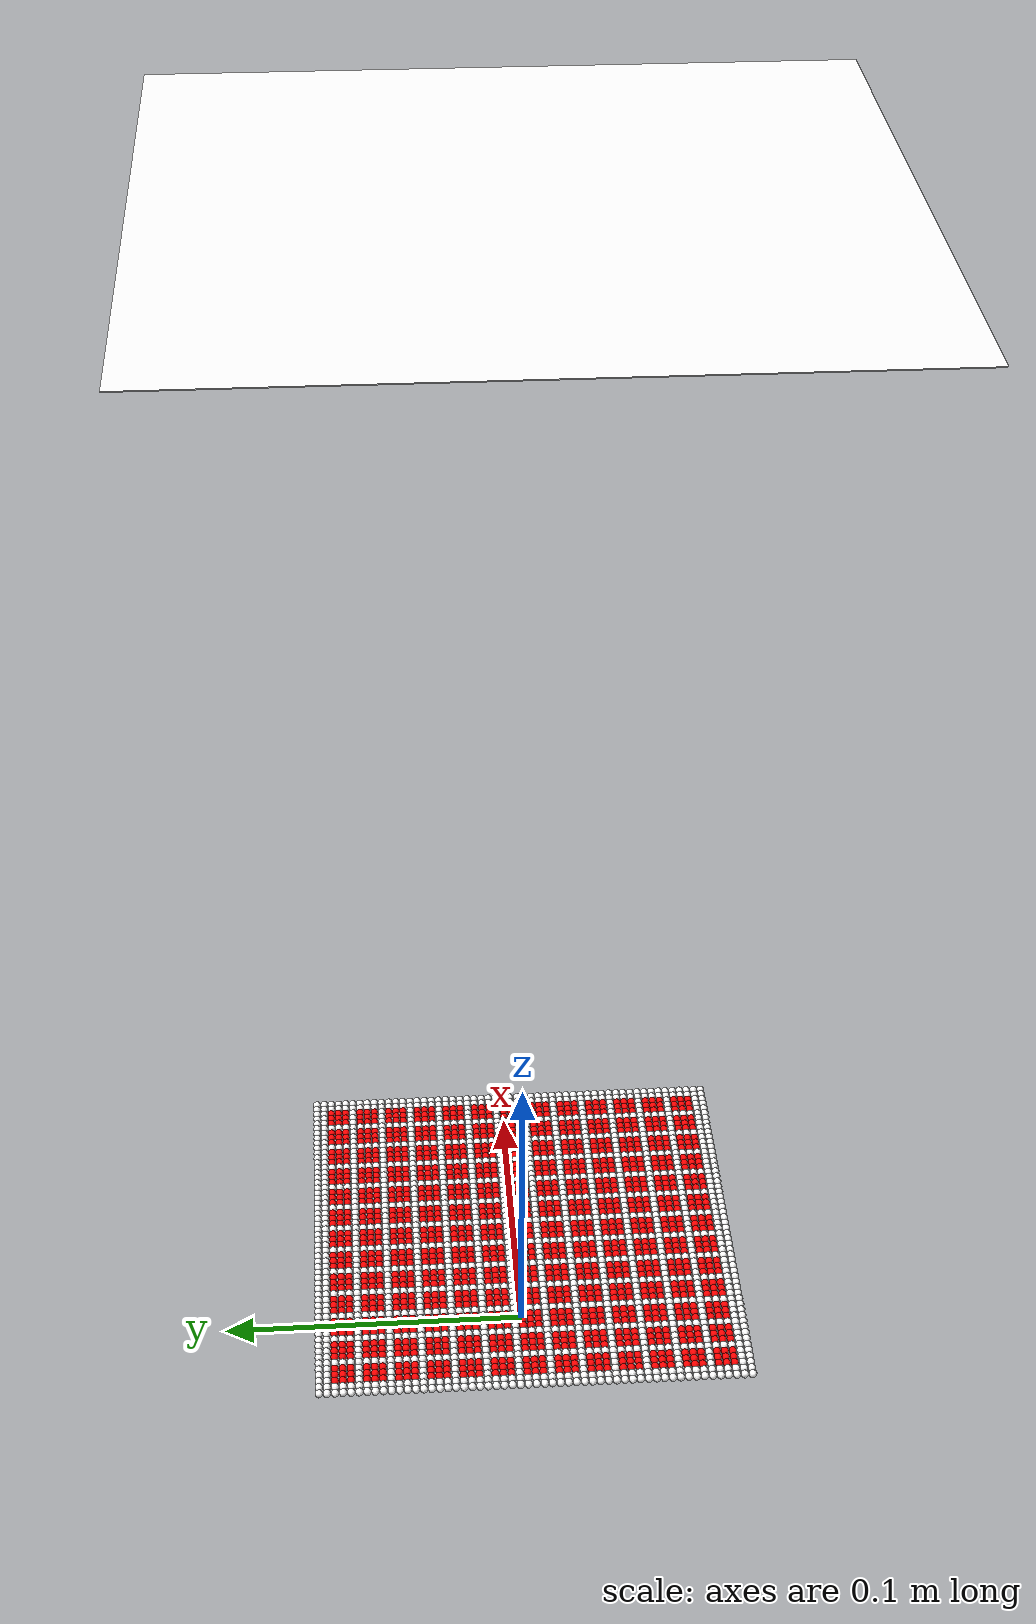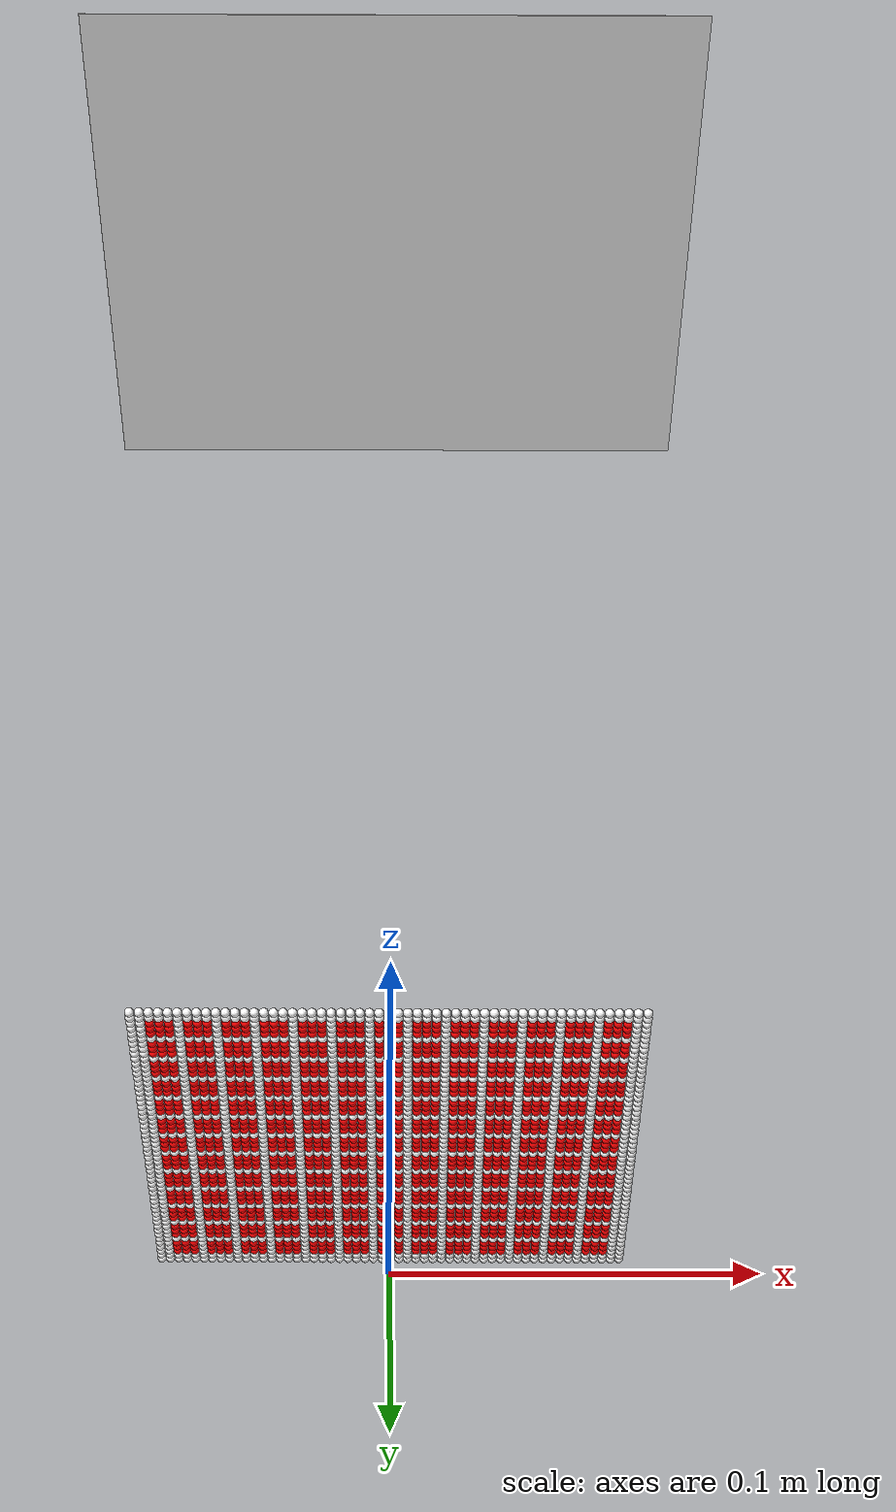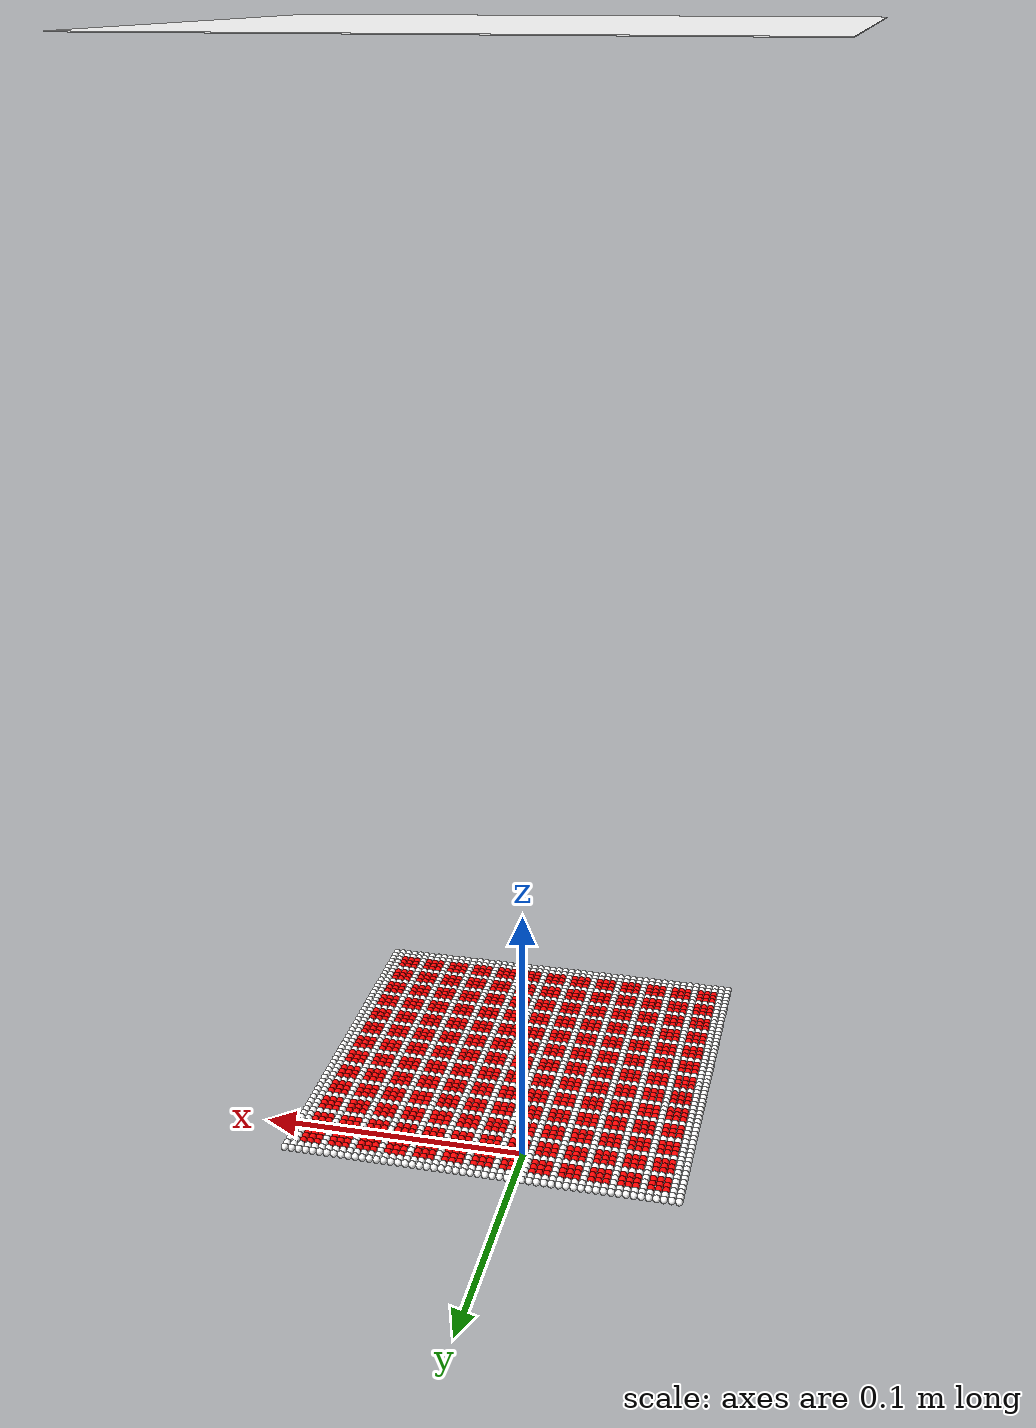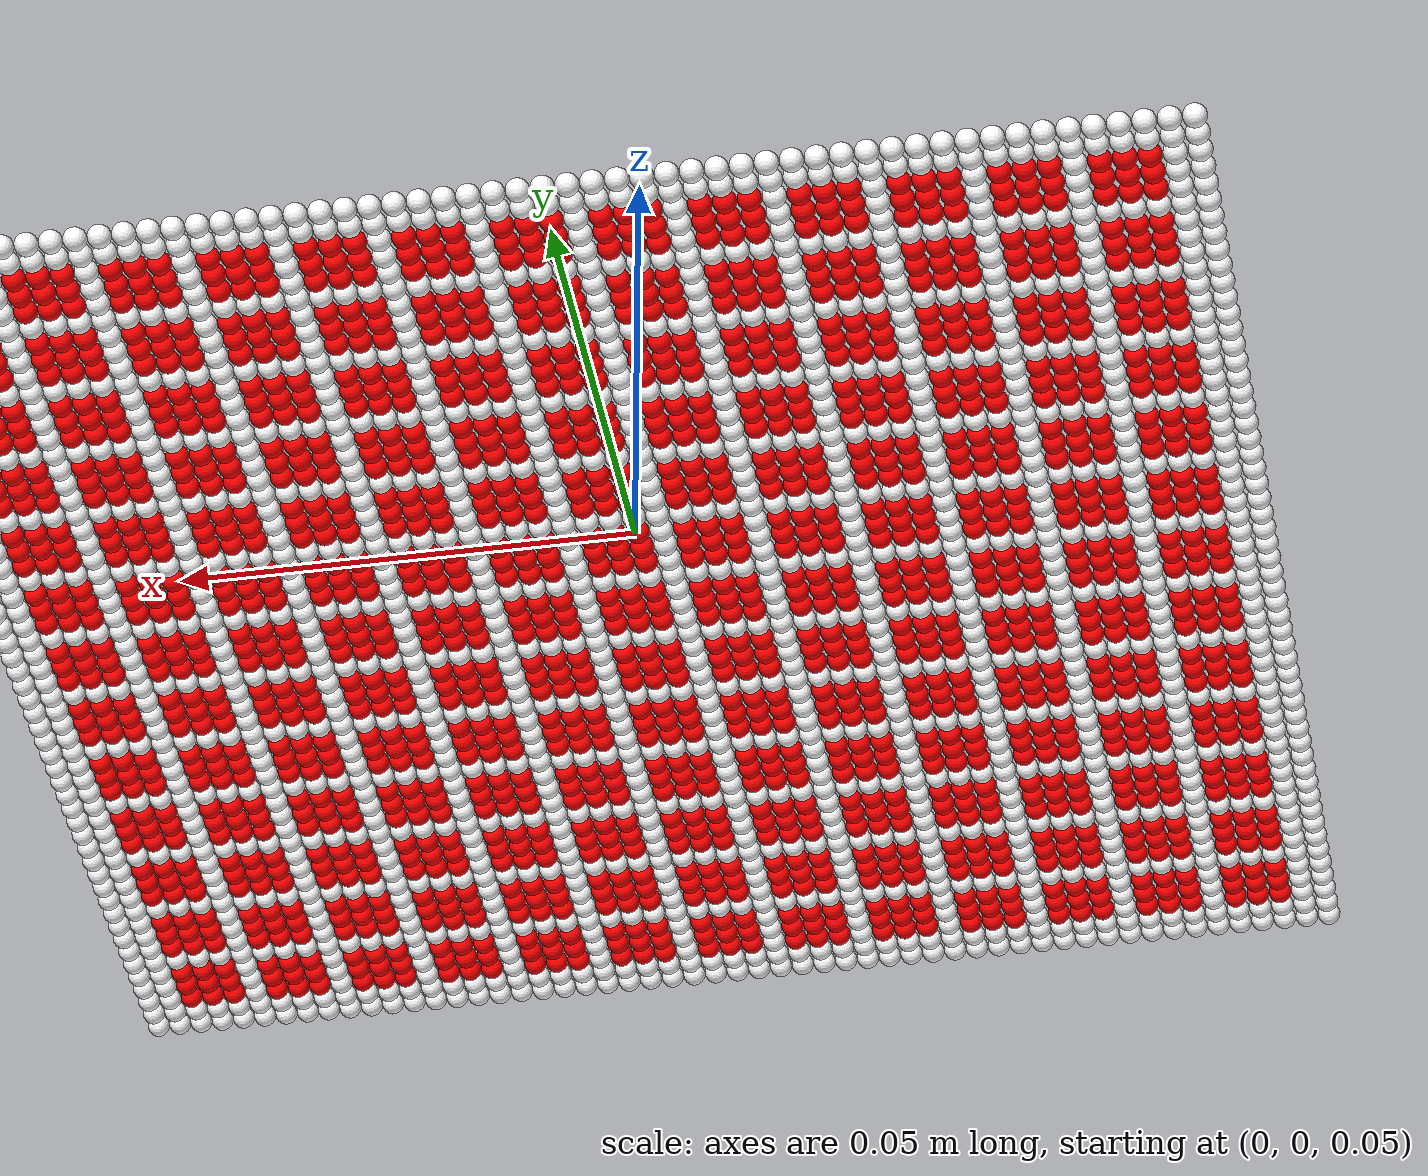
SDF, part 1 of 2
<sdf version="1.5">
 <model name="spring_array55">
  <link name="plane">
   <pose>0 0 0.4 0 -0 0</pose>
   <inertial><mass>20</mass></inertial>
   <collision name="collision">
    <geometry><box><size>0.20625 0.20625 0.00025</size></box></geometry>
    <surface><friction><ode><mu>0</mu><mu2>0</mu2></ode></friction></surface>
   </collision>
   <visual name="visual">
    <geometry><box><size>0.20625 0.20625 0.00025</size></box></geometry>
    <material>
     <ambient>1 1 1 1</ambient>
     <diffuse>1 1 1 1</diffuse>
     <specular>0.1 0.1 0.1 1</specular>
     <emissive>0 0 0 0</emissive>
    </material>
   </visual>
  </link>
  <joint name="plane_joint" type="prismatic">
   <parent>world</parent>
   <child>plane</child>
   <axis>
    <xyz>0 0 1</xyz>
    <limit><lower>1e+16</lower><upper>-1e+16</upper></limit>
    <use_parent_model_frame>1</use_parent_model_frame>
   </axis>
  </joint>
  <link name="spring_1">
   <pose>-0.0675 0.0675 0.04 0 -0 0</pose>
   <inertial><mass>0.00235</mass></inertial>
   <collision name="sphere_collision">
    <geometry><sphere><radius>0.00125</radius></sphere></geometry>
    <surface><friction><ode><mu>0</mu><mu2>0</mu2></ode></friction></surface>
   </collision>
   <visual name="visual">
    <geometry><sphere><radius>0.00125</radius></sphere></geometry>
    <material>
     <ambient>1 1 1 1</ambient>
     <diffuse>1 1 1 1</diffuse>
     <specular>0.1 0.1 0.1 1</specular>
     <emissive>0 0 0 0</emissive>
    </material>
   </visual>
  </link>
  <joint name="spring_joint_1" type="prismatic">
   <parent>plane</parent>
   <child>spring_1</child>
   <axis>
    <xyz>0 0 1</xyz>
    <limit><lower>-1e+16</lower><upper>1e+16</upper></limit>
    <use_parent_model_frame>1</use_parent_model_frame>
   </axis>
  </joint>
  <link name="spring_2">
   <pose>-0.065 0.0675 0.04 0 -0 0</pose>
   <inertial><mass>0.00235</mass></inertial>
   <collision name="sphere_collision">
    <geometry><sphere><radius>0.00125</radius></sphere></geometry>
    <surface><friction><ode><mu>0</mu><mu2>0</mu2></ode></friction></surface>
   </collision>
   <visual name="visual">
    <geometry><sphere><radius>0.00125</radius></sphere></geometry>
    <material>
     <ambient>1 1 1 1</ambient>
     <diffuse>1 1 1 1</diffuse>
     <specular>0.1 0.1 0.1 1</specular>
     <emissive>0 0 0 0</emissive>
    </material>
   </visual>
  </link>
  <joint name="spring_joint_2" type="prismatic">
   <parent>plane</parent>
   <child>spring_2</child>
   <axis>
    <xyz>0 0 1</xyz>
    <limit><lower>-1e+16</lower><upper>1e+16</upper></limit>
    <use_parent_model_frame>1</use_parent_model_frame>
   </axis>
  </joint>
  <link name="spring_3">
   <pose>-0.0625 0.0675 0.04 0 -0 0</pose>
   <inertial><mass>0.00235</mass></inertial>
   <collision name="sphere_collision">
    <geometry><sphere><radius>0.00125</radius></sphere></geometry>
    <surface><friction><ode><mu>0</mu><mu2>0</mu2></ode></friction></surface>
   </collision>
   <visual name="visual">
    <geometry><sphere><radius>0.00125</radius></sphere></geometry>
    <material>
     <ambient>1 1 1 1</ambient>
     <diffuse>1 1 1 1</diffuse>
     <specular>0.1 0.1 0.1 1</specular>
     <emissive>0 0 0 0</emissive>
    </material>
   </visual>
  </link>
  <joint name="spring_joint_3" type="prismatic">
   <parent>plane</parent>
   <child>spring_3</child>
   <axis>
    <xyz>0 0 1</xyz>
    <limit><lower>-1e+16</lower><upper>1e+16</upper></limit>
    <use_parent_model_frame>1</use_parent_model_frame>
   </axis>
  </joint>
  <link name="spring_4">
   <pose>-0.06 0.0675 0.04 0 -0 0</pose>
   <inertial><mass>0.00235</mass></inertial>
   <collision name="sphere_collision">
    <geometry><sphere><radius>0.00125</radius></sphere></geometry>
    <surface><friction><ode><mu>0</mu><mu2>0</mu2></ode></friction></surface>
   </collision>
   <visual name="visual">
    <geometry><sphere><radius>0.00125</radius></sphere></geometry>
    <material>
     <ambient>1 1 1 1</ambient>
     <diffuse>1 1 1 1</diffuse>
     <specular>0.1 0.1 0.1 1</specular>
     <emissive>0 0 0 0</emissive>
    </material>
   </visual>
  </link>
  <joint name="spring_joint_4" type="prismatic">
   <parent>plane</parent>
   <child>spring_4</child>
   <axis>
    <xyz>0 0 1</xyz>
    <limit><lower>-1e+16</lower><upper>1e+16</upper></limit>
    <use_parent_model_frame>1</use_parent_model_frame>
   </axis>
  </joint>
  <link name="spring_5">
   <pose>-0.0575 0.0675 0.04 0 -0 0</pose>
   <inertial><mass>0.00235</mass></inertial>
   <collision name="sphere_collision">
    <geometry><sphere><radius>0.00125</radius></sphere></geometry>
    <surface><friction><ode><mu>0</mu><mu2>0</mu2></ode></friction></surface>
   </collision>
   <visual name="visual">
    <geometry><sphere><radius>0.00125</radius></sphere></geometry>
    <material>
     <ambient>1 1 1 1</ambient>
     <diffuse>1 1 1 1</diffuse>
     <specular>0.1 0.1 0.1 1</specular>
     <emissive>0 0 0 0</emissive>
    </material>
   </visual>
  </link>
  <joint name="spring_joint_5" type="prismatic">
   <parent>plane</parent>
   <child>spring_5</child>
   <axis>
    <xyz>0 0 1</xyz>
    <limit><lower>-1e+16</lower><upper>1e+16</upper></limit>
    <use_parent_model_frame>1</use_parent_model_frame>
   </axis>
  </joint>
  <link name="spring_6">
   <pose>-0.055 0.0675 0.04 0 -0 0</pose>
   <inertial><mass>0.00235</mass></inertial>
   <collision name="sphere_collision">
    <geometry><sphere><radius>0.00125</radius></sphere></geometry>
    <surface><friction><ode><mu>0</mu><mu2>0</mu2></ode></friction></surface>
   </collision>
   <visual name="visual">
    <geometry><sphere><radius>0.00125</radius></sphere></geometry>
    <material>
     <ambient>1 1 1 1</ambient>
     <diffuse>1 1 1 1</diffuse>
     <specular>0.1 0.1 0.1 1</specular>
     <emissive>0 0 0 0</emissive>
    </material>
   </visual>
  </link>
  <joint name="spring_joint_6" type="prismatic">
   <parent>plane</parent>
   <child>spring_6</child>
   <axis>
    <xyz>0 0 1</xyz>
    <limit><lower>-1e+16</lower><upper>1e+16</upper></limit>
    <use_parent_model_frame>1</use_parent_model_frame>
   </axis>
  </joint>
  <link name="spring_7">
   <pose>-0.0525 0.0675 0.04 0 -0 0</pose>
   <inertial><mass>0.00235</mass></inertial>
   <collision name="sphere_collision">
    <geometry><sphere><radius>0.00125</radius></sphere></geometry>
    <surface><friction><ode><mu>0</mu><mu2>0</mu2></ode></friction></surface>
   </collision>
   <visual name="visual">
    <geometry><sphere><radius>0.00125</radius></sphere></geometry>
    <material>
     <ambient>1 1 1 1</ambient>
     <diffuse>1 1 1 1</diffuse>
     <specular>0.1 0.1 0.1 1</specular>
     <emissive>0 0 0 0</emissive>
    </material>
   </visual>
  </link>
  <joint name="spring_joint_7" type="prismatic">
   <parent>plane</parent>
   <child>spring_7</child>
   <axis>
    <xyz>0 0 1</xyz>
    <limit><lower>-1e+16</lower><upper>1e+16</upper></limit>
    <use_parent_model_frame>1</use_parent_model_frame>
   </axis>
  </joint>
  <link name="spring_8">
   <pose>-0.05 0.0675 0.04 0 -0 0</pose>
   <inertial><mass>0.00235</mass></inertial>
   <collision name="sphere_collision">
    <geometry><sphere><radius>0.00125</radius></sphere></geometry>
    <surface><friction><ode><mu>0</mu><mu2>0</mu2></ode></friction></surface>
   </collision>
   <visual name="visual">
    <geometry><sphere><radius>0.00125</radius></sphere></geometry>
    <material>
     <ambient>1 1 1 1</ambient>
     <diffuse>1 1 1 1</diffuse>
     <specular>0.1 0.1 0.1 1</specular>
     <emissive>0 0 0 0</emissive>
    </material>
   </visual>
  </link>
  <joint name="spring_joint_8" type="prismatic">
   <parent>plane</parent>
   <child>spring_8</child>
   <axis>
    <xyz>0 0 1</xyz>
    <limit><lower>-1e+16</lower><upper>1e+16</upper></limit>
    <use_parent_model_frame>1</use_parent_model_frame>
   </axis>
  </joint>
  <link name="spring_9">
   <pose>-0.0475 0.0675 0.04 0 -0 0</pose>
   <inertial><mass>0.00235</mass></inertial>
   <collision name="sphere_collision">
    <geometry><sphere><radius>0.00125</radius></sphere></geometry>
    <surface><friction><ode><mu>0</mu><mu2>0</mu2></ode></friction></surface>
   </collision>
   <visual name="visual">
    <geometry><sphere><radius>0.00125</radius></sphere></geometry>
    <material>
     <ambient>1 1 1 1</ambient>
     <diffuse>1 1 1 1</diffuse>
     <specular>0.1 0.1 0.1 1</specular>
     <emissive>0 0 0 0</emissive>
    </material>
   </visual>
  </link>
  <joint name="spring_joint_9" type="prismatic">
   <parent>plane</parent>
   <child>spring_9</child>
   <axis>
    <xyz>0 0 1</xyz>
    <limit><lower>-1e+16</lower><upper>1e+16</upper></limit>
    <use_parent_model_frame>1</use_parent_model_frame>
   </axis>
  </joint>
  <link name="spring_10">
   <pose>-0.045 0.0675 0.04 0 -0 0</pose>
   <inertial><mass>0.00235</mass></inertial>
   <collision name="sphere_collision">
    <geometry><sphere><radius>0.00125</radius></sphere></geometry>
    <surface><friction><ode><mu>0</mu><mu2>0</mu2></ode></friction></surface>
   </collision>
   <visual name="visual">
    <geometry><sphere><radius>0.00125</radius></sphere></geometry>
    <material>
     <ambient>1 1 1 1</ambient>
     <diffuse>1 1 1 1</diffuse>
     <specular>0.1 0.1 0.1 1</specular>
     <emissive>0 0 0 0</emissive>
    </material>
   </visual>
  </link>
  <joint name="spring_joint_10" type="prismatic">
   <parent>plane</parent>
   <child>spring_10</child>
   <axis>
    <xyz>0 0 1</xyz>
    <limit><lower>-1e+16</lower><upper>1e+16</upper></limit>
    <use_parent_model_frame>1</use_parent_model_frame>
   </axis>
  </joint>
  <link name="spring_11">
   <pose>-0.0425 0.0675 0.04 0 -0 0</pose>
   <inertial><mass>0.00235</mass></inertial>
   <collision name="sphere_collision">
    <geometry><sphere><radius>0.00125</radius></sphere></geometry>
    <surface><friction><ode><mu>0</mu><mu2>0</mu2></ode></friction></surface>
   </collision>
   <visual name="visual">
    <geometry><sphere><radius>0.00125</radius></sphere></geometry>
    <material>
     <ambient>1 1 1 1</ambient>
     <diffuse>1 1 1 1</diffuse>
     <specular>0.1 0.1 0.1 1</specular>
     <emissive>0 0 0 0</emissive>
    </material>
   </visual>
  </link>
  <joint name="spring_joint_11" type="prismatic">
   <parent>plane</parent>
   <child>spring_11</child>
   <axis>
    <xyz>0 0 1</xyz>
    <limit><lower>-1e+16</lower><upper>1e+16</upper></limit>
    <use_parent_model_frame>1</use_parent_model_frame>
   </axis>
  </joint>
  <link name="spring_12">
   <pose>-0.04 0.0675 0.04 0 -0 0</pose>
   <inertial><mass>0.00235</mass></inertial>
   <collision name="sphere_collision">
    <geometry><sphere><radius>0.00125</radius></sphere></geometry>
    <surface><friction><ode><mu>0</mu><mu2>0</mu2></ode></friction></surface>
   </collision>
   <visual name="visual">
    <geometry><sphere><radius>0.00125</radius></sphere></geometry>
    <material>
     <ambient>1 1 1 1</ambient>
     <diffuse>1 1 1 1</diffuse>
     <specular>0.1 0.1 0.1 1</specular>
     <emissive>0 0 0 0</emissive>
    </material>
   </visual>
  </link>
  <joint name="spring_joint_12" type="prismatic">
   <parent>plane</parent>
   <child>spring_12</child>
   <axis>
    <xyz>0 0 1</xyz>
    <limit><lower>-1e+16</lower><upper>1e+16</upper></limit>
    <use_parent_model_frame>1</use_parent_model_frame>
   </axis>
  </joint>
  <link name="spring_13">
   <pose>-0.0375 0.0675 0.04 0 -0 0</pose>
   <inertial><mass>0.00235</mass></inertial>
   <collision name="sphere_collision">
    <geometry><sphere><radius>0.00125</radius></sphere></geometry>
    <surface><friction><ode><mu>0</mu><mu2>0</mu2></ode></friction></surface>
   </collision>
   <visual name="visual">
    <geometry><sphere><radius>0.00125</radius></sphere></geometry>
    <material>
     <ambient>1 1 1 1</ambient>
     <diffuse>1 1 1 1</diffuse>
     <specular>0.1 0.1 0.1 1</specular>
     <emissive>0 0 0 0</emissive>
    </material>
   </visual>
  </link>
  <joint name="spring_joint_13" type="prismatic">
   <parent>plane</parent>
   <child>spring_13</child>
   <axis>
    <xyz>0 0 1</xyz>
    <limit><lower>-1e+16</lower><upper>1e+16</upper></limit>
    <use_parent_model_frame>1</use_parent_model_frame>
   </axis>
  </joint>
  <link name="spring_14">
   <pose>-0.035 0.0675 0.04 0 -0 0</pose>
   <inertial><mass>0.00235</mass></inertial>
   <collision name="sphere_collision">
    <geometry><sphere><radius>0.00125</radius></sphere></geometry>
    <surface><friction><ode><mu>0</mu><mu2>0</mu2></ode></friction></surface>
   </collision>
   <visual name="visual">
    <geometry><sphere><radius>0.00125</radius></sphere></geometry>
    <material>
     <ambient>1 1 1 1</ambient>
     <diffuse>1 1 1 1</diffuse>
     <specular>0.1 0.1 0.1 1</specular>
     <emissive>0 0 0 0</emissive>
    </material>
   </visual>
  </link>
  <joint name="spring_joint_14" type="prismatic">
   <parent>plane</parent>
   <child>spring_14</child>
   <axis>
    <xyz>0 0 1</xyz>
    <limit><lower>-1e+16</lower><upper>1e+16</upper></limit>
    <use_parent_model_frame>1</use_parent_model_frame>
   </axis>
  </joint>
  <link name="spring_15">
   <pose>-0.0325 0.0675 0.04 0 -0 0</pose>
   <inertial><mass>0.00235</mass></inertial>
   <collision name="sphere_collision">
    <geometry><sphere><radius>0.00125</radius></sphere></geometry>
    <surface><friction><ode><mu>0</mu><mu2>0</mu2></ode></friction></surface>
   </collision>
   <visual name="visual">
    <geometry><sphere><radius>0.00125</radius></sphere></geometry>
    <material>
     <ambient>1 1 1 1</ambient>
     <diffuse>1 1 1 1</diffuse>
     <specular>0.1 0.1 0.1 1</specular>
     <emissive>0 0 0 0</emissive>
    </material>
   </visual>
  </link>
  <joint name="spring_joint_15" type="prismatic">
   <parent>plane</parent>
   <child>spring_15</child>
   <axis>
    <xyz>0 0 1</xyz>
    <limit><lower>-1e+16</lower><upper>1e+16</upper></limit>
    <use_parent_model_frame>1</use_parent_model_frame>
   </axis>
  </joint>
  <link name="spring_16">
   <pose>-0.03 0.0675 0.04 0 -0 0</pose>
   <inertial><mass>0.00235</mass></inertial>
   <collision name="sphere_collision">
    <geometry><sphere><radius>0.00125</radius></sphere></geometry>
    <surface><friction><ode><mu>0</mu><mu2>0</mu2></ode></friction></surface>
   </collision>
   <visual name="visual">
    <geometry><sphere><radius>0.00125</radius></sphere></geometry>
    <material>
     <ambient>1 1 1 1</ambient>
     <diffuse>1 1 1 1</diffuse>
     <specular>0.1 0.1 0.1 1</specular>
     <emissive>0 0 0 0</emissive>
    </material>
   </visual>
  </link>
  <joint name="spring_joint_16" type="prismatic">
   <parent>plane</parent>
   <child>spring_16</child>
   <axis>
    <xyz>0 0 1</xyz>
    <limit><lower>-1e+16</lower><upper>1e+16</upper></limit>
    <use_parent_model_frame>1</use_parent_model_frame>
   </axis>
  </joint>
  <link name="spring_17">
   <pose>-0.0275 0.0675 0.04 0 -0 0</pose>
   <inertial><mass>0.00235</mass></inertial>
   <collision name="sphere_collision">
    <geometry><sphere><radius>0.00125</radius></sphere></geometry>
    <surface><friction><ode><mu>0</mu><mu2>0</mu2></ode></friction></surface>
   </collision>
   <visual name="visual">
    <geometry><sphere><radius>0.00125</radius></sphere></geometry>
    <material>
     <ambient>1 1 1 1</ambient>
     <diffuse>1 1 1 1</diffuse>
     <specular>0.1 0.1 0.1 1</specular>
     <emissive>0 0 0 0</emissive>
    </material>
   </visual>
  </link>
  <joint name="spring_joint_17" type="prismatic">
   <parent>plane</parent>
   <child>spring_17</child>
   <axis>
    <xyz>0 0 1</xyz>
    <limit><lower>-1e+16</lower><upper>1e+16</upper></limit>
    <use_parent_model_frame>1</use_parent_model_frame>
   </axis>
  </joint>
  <link name="spring_18">
   <pose>-0.025 0.0675 0.04 0 -0 0</pose>
   <inertial><mass>0.00235</mass></inertial>
   <collision name="sphere_collision">
    <geometry><sphere><radius>0.00125</radius></sphere></geometry>
    <surface><friction><ode><mu>0</mu><mu2>0</mu2></ode></friction></surface>
   </collision>
   <visual name="visual">
    <geometry><sphere><radius>0.00125</radius></sphere></geometry>
    <material>
     <ambient>1 1 1 1</ambient>
     <diffuse>1 1 1 1</diffuse>
     <specular>0.1 0.1 0.1 1</specular>
     <emissive>0 0 0 0</emissive>
    </material>
   </visual>
  </link>
  <joint name="spring_joint_18" type="prismatic">
   <parent>plane</parent>
   <child>spring_18</child>
   <axis>
    <xyz>0 0 1</xyz>
    <limit><lower>-1e+16</lower><upper>1e+16</upper></limit>
    <use_parent_model_frame>1</use_parent_model_frame>
   </axis>
  </joint>
  <link name="spring_19">
   <pose>-0.0225 0.0675 0.04 0 -0 0</pose>
   <inertial><mass>0.00235</mass></inertial>
   <collision name="sphere_collision">
    <geometry><sphere><radius>0.00125</radius></sphere></geometry>
    <surface><friction><ode><mu>0</mu><mu2>0</mu2></ode></friction></surface>
   </collision>
   <visual name="visual">
    <geometry><sphere><radius>0.00125</radius></sphere></geometry>
    <material>
     <ambient>1 1 1 1</ambient>
     <diffuse>1 1 1 1</diffuse>
     <specular>0.1 0.1 0.1 1</specular>
     <emissive>0 0 0 0</emissive>
    </material>
   </visual>
  </link>
  <joint name="spring_joint_19" type="prismatic">
   <parent>plane</parent>
   <child>spring_19</child>
   <axis>
    <xyz>0 0 1</xyz>
    <limit><lower>-1e+16</lower><upper>1e+16</upper></limit>
    <use_parent_model_frame>1</use_parent_model_frame>
   </axis>
  </joint>
  <link name="spring_20">
   <pose>-0.02 0.0675 0.04 0 -0 0</pose>
   <inertial><mass>0.00235</mass></inertial>
   <collision name="sphere_collision">
    <geometry><sphere><radius>0.00125</radius></sphere></geometry>
    <surface><friction><ode><mu>0</mu><mu2>0</mu2></ode></friction></surface>
   </collision>
   <visual name="visual">
    <geometry><sphere><radius>0.00125</radius></sphere></geometry>
    <material>
     <ambient>1 1 1 1</ambient>
     <diffuse>1 1 1 1</diffuse>
     <specular>0.1 0.1 0.1 1</specular>
     <emissive>0 0 0 0</emissive>
    </material>
   </visual>
  </link>
  <joint name="spring_joint_20" type="prismatic">
   <parent>plane</parent>
   <child>spring_20</child>
   <axis>
    <xyz>0 0 1</xyz>
    <limit><lower>-1e+16</lower><upper>1e+16</upper></limit>
    <use_parent_model_frame>1</use_parent_model_frame>
   </axis>
  </joint>
  <link name="spring_21">
   <pose>-0.0175 0.0675 0.04 0 -0 0</pose>
   <inertial><mass>0.00235</mass></inertial>
   <collision name="sphere_collision">
    <geometry><sphere><radius>0.00125</radius></sphere></geometry>
    <surface><friction><ode><mu>0</mu><mu2>0</mu2></ode></friction></surface>
   </collision>
   <visual name="visual">
    <geometry><sphere><radius>0.00125</radius></sphere></geometry>
    <material>
     <ambient>1 1 1 1</ambient>
     <diffuse>1 1 1 1</diffuse>
     <specular>0.1 0.1 0.1 1</specular>
     <emissive>0 0 0 0</emissive>
    </material>
   </visual>
  </link>
  <joint name="spring_joint_21" type="prismatic">
   <parent>plane</parent>
   <child>spring_21</child>
   <axis>
    <xyz>0 0 1</xyz>
    <limit><lower>-1e+16</lower><upper>1e+16</upper></limit>
    <use_parent_model_frame>1</use_parent_model_frame>
   </axis>
  </joint>
  <link name="spring_22">
   <pose>-0.015 0.0675 0.04 0 -0 0</pose>
   <inertial><mass>0.00235</mass></inertial>
   <collision name="sphere_collision">
    <geometry><sphere><radius>0.00125</radius></sphere></geometry>
    <surface><friction><ode><mu>0</mu><mu2>0</mu2></ode></friction></surface>
   </collision>
   <visual name="visual">
    <geometry><sphere><radius>0.00125</radius></sphere></geometry>
    <material>
     <ambient>1 1 1 1</ambient>
     <diffuse>1 1 1 1</diffuse>
     <specular>0.1 0.1 0.1 1</specular>
     <emissive>0 0 0 0</emissive>
    </material>
   </visual>
  </link>
  <joint name="spring_joint_22" type="prismatic">
   <parent>plane</parent>
   <child>spring_22</child>
   <axis>
    <xyz>0 0 1</xyz>
    <limit><lower>-1e+16</lower><upper>1e+16</upper></limit>
    <use_parent_model_frame>1</use_parent_model_frame>
   </axis>
  </joint>
  <link name="spring_23">
   <pose>-0.0125 0.0675 0.04 0 -0 0</pose>
   <inertial><mass>0.00235</mass></inertial>
   <collision name="sphere_collision">
    <geometry><sphere><radius>0.00125</radius></sphere></geometry>
    <surface><friction><ode><mu>0</mu><mu2>0</mu2></ode></friction></surface>
   </collision>
   <visual name="visual">
    <geometry><sphere><radius>0.00125</radius></sphere></geometry>
    <material>
     <ambient>1 1 1 1</ambient>
     <diffuse>1 1 1 1</diffuse>
     <specular>0.1 0.1 0.1 1</specular>
     <emissive>0 0 0 0</emissive>
    </material>
   </visual>
  </link>
  <joint name="spring_joint_23" type="prismatic">
   <parent>plane</parent>
   <child>spring_23</child>
   <axis>
    <xyz>0 0 1</xyz>
    <limit><lower>-1e+16</lower><upper>1e+16</upper></limit>
    <use_parent_model_frame>1</use_parent_model_frame>
   </axis>
  </joint>
  <link name="spring_24">
   <pose>-0.01 0.0675 0.04 0 -0 0</pose>
   <inertial><mass>0.00235</mass></inertial>
   <collision name="sphere_collision">
    <geometry><sphere><radius>0.00125</radius></sphere></geometry>
    <surface><friction><ode><mu>0</mu><mu2>0</mu2></ode></friction></surface>
   </collision>
   <visual name="visual">
    <geometry><sphere><radius>0.00125</radius></sphere></geometry>
    <material>
     <ambient>1 1 1 1</ambient>
     <diffuse>1 1 1 1</diffuse>
     <specular>0.1 0.1 0.1 1</specular>
     <emissive>0 0 0 0</emissive>
    </material>
   </visual>
  </link>
  <joint name="spring_joint_24" type="prismatic">
   <parent>plane</parent>
   <child>spring_24</child>
   <axis>
    <xyz>0 0 1</xyz>
    <limit><lower>-1e+16</lower><upper>1e+16</upper></limit>
    <use_parent_model_frame>1</use_parent_model_frame>
   </axis>
  </joint>
  <link name="spring_25">
   <pose>-0.0075 0.0675 0.04 0 -0 0</pose>
   <inertial><mass>0.00235</mass></inertial>
   <collision name="sphere_collision">
    <geometry><sphere><radius>0.00125</radius></sphere></geometry>
    <surface><friction><ode><mu>0</mu><mu2>0</mu2></ode></friction></surface>
   </collision>
   <visual name="visual">
    <geometry><sphere><radius>0.00125</radius></sphere></geometry>
    <material>
     <ambient>1 1 1 1</ambient>
     <diffuse>1 1 1 1</diffuse>
     <specular>0.1 0.1 0.1 1</specular>
     <emissive>0 0 0 0</emissive>
    </material>
   </visual>
  </link>
  <joint name="spring_joint_25" type="prismatic">
   <parent>plane</parent>
   <child>spring_25</child>
   <axis>
    <xyz>0 0 1</xyz>
    <limit><lower>-1e+16</lower><upper>1e+16</upper></limit>
    <use_parent_model_frame>1</use_parent_model_frame>
   </axis>
  </joint>
  <link name="spring_26">
   <pose>-0.005 0.0675 0.04 0 -0 0</pose>
   <inertial><mass>0.00235</mass></inertial>
   <collision name="sphere_collision">
    <geometry><sphere><radius>0.00125</radius></sphere></geometry>
    <surface><friction><ode><mu>0</mu><mu2>0</mu2></ode></friction></surface>
   </collision>
   <visual name="visual">
    <geometry><sphere><radius>0.00125</radius></sphere></geometry>
    <material>
     <ambient>1 1 1 1</ambient>
     <diffuse>1 1 1 1</diffuse>
     <specular>0.1 0.1 0.1 1</specular>
     <emissive>0 0 0 0</emissive>
    </material>
   </visual>
  </link>
  <joint name="spring_joint_26" type="prismatic">
   <parent>plane</parent>
   <child>spring_26</child>
   <axis>
    <xyz>0 0 1</xyz>
    <limit><lower>-1e+16</lower><upper>1e+16</upper></limit>
    <use_parent_model_frame>1</use_parent_model_frame>
   </axis>
  </joint>
  <link name="spring_27">
   <pose>-0.0025 0.0675 0.04 0 -0 0</pose>
   <inertial><mass>0.00235</mass></inertial>
   <collision name="sphere_collision">
    <geometry><sphere><radius>0.00125</radius></sphere></geometry>
    <surface><friction><ode><mu>0</mu><mu2>0</mu2></ode></friction></surface>
   </collision>
   <visual name="visual">
    <geometry><sphere><radius>0.00125</radius></sphere></geometry>
    <material>
     <ambient>1 1 1 1</ambient>
     <diffuse>1 1 1 1</diffuse>
     <specular>0.1 0.1 0.1 1</specular>
     <emissive>0 0 0 0</emissive>
    </material>
   </visual>
  </link>
  <joint name="spring_joint_27" type="prismatic">
   <parent>plane</parent>
   <child>spring_27</child>
   <axis>
    <xyz>0 0 1</xyz>
    <limit><lower>-1e+16</lower><upper>1e+16</upper></limit>
    <use_parent_model_frame>1</use_parent_model_frame>
   </axis>
  </joint>
  <link name="spring_28">
   <pose>2.1684e-17 0.0675 0.04 0 -0 0</pose>
   <inertial><mass>0.00235</mass></inertial>
   <collision name="sphere_collision">
    <geometry><sphere><radius>0.00125</radius></sphere></geometry>
    <surface><friction><ode><mu>0</mu><mu2>0</mu2></ode></friction></surface>
   </collision>
   <visual name="visual">
    <geometry><sphere><radius>0.00125</radius></sphere></geometry>
    <material>
     <ambient>1 1 1 1</ambient>
     <diffuse>1 1 1 1</diffuse>
     <specular>0.1 0.1 0.1 1</specular>
     <emissive>0 0 0 0</emissive>
    </material>
   </visual>
  </link>
  <joint name="spring_joint_28" type="prismatic">
   <parent>plane</parent>
   <child>spring_28</child>
   <axis>
    <xyz>0 0 1</xyz>
    <limit><lower>-1e+16</lower><upper>1e+16</upper></limit>
    <use_parent_model_frame>1</use_parent_model_frame>
   </axis>
  </joint>
  <link name="spring_29">
   <pose>0.0025 0.0675 0.04 0 -0 0</pose>
   <inertial><mass>0.00235</mass></inertial>
   <collision name="sphere_collision">
    <geometry><sphere><radius>0.00125</radius></sphere></geometry>
    <surface><friction><ode><mu>0</mu><mu2>0</mu2></ode></friction></surface>
   </collision>
   <visual name="visual">
    <geometry><sphere><radius>0.00125</radius></sphere></geometry>
    <material>
     <ambient>1 1 1 1</ambient>
     <diffuse>1 1 1 1</diffuse>
     <specular>0.1 0.1 0.1 1</specular>
     <emissive>0 0 0 0</emissive>
    </material>
   </visual>
  </link>
  <joint name="spring_joint_29" type="prismatic">
   <parent>plane</parent>
   <child>spring_29</child>
   <axis>
    <xyz>0 0 1</xyz>
    <limit><lower>-1e+16</lower><upper>1e+16</upper></limit>
    <use_parent_model_frame>1</use_parent_model_frame>
   </axis>
  </joint>
  <link name="spring_30">
   <pose>0.005 0.0675 0.04 0 -0 0</pose>
   <inertial><mass>0.00235</mass></inertial>
   <collision name="sphere_collision">
    <geometry><sphere><radius>0.00125</radius></sphere></geometry>
    <surface><friction><ode><mu>0</mu><mu2>0</mu2></ode></friction></surface>
   </collision>
   <visual name="visual">
    <geometry><sphere><radius>0.00125</radius></sphere></geometry>
    <material>
     <ambient>1 1 1 1</ambient>
     <diffuse>1 1 1 1</diffuse>
     <specular>0.1 0.1 0.1 1</specular>
     <emissive>0 0 0 0</emissive>
    </material>
   </visual>
  </link>
  <joint name="spring_joint_30" type="prismatic">
   <parent>plane</parent>
   <child>spring_30</child>
   <axis>
    <xyz>0 0 1</xyz>
    <limit><lower>-1e+16</lower><upper>1e+16</upper></limit>
    <use_parent_model_frame>1</use_parent_model_frame>
   </axis>
  </joint>
  <link name="spring_31">
   <pose>0.0075 0.0675 0.04 0 -0 0</pose>
   <inertial><mass>0.00235</mass></inertial>
   <collision name="sphere_collision">
    <geometry><sphere><radius>0.00125</radius></sphere></geometry>
    <surface><friction><ode><mu>0</mu><mu2>0</mu2></ode></friction></surface>
   </collision>
   <visual name="visual">
    <geometry><sphere><radius>0.00125</radius></sphere></geometry>
    <material>
     <ambient>1 1 1 1</ambient>
     <diffuse>1 1 1 1</diffuse>
     <specular>0.1 0.1 0.1 1</specular>
     <emissive>0 0 0 0</emissive>
    </material>
   </visual>
  </link>
  <joint name="spring_joint_31" type="prismatic">
   <parent>plane</parent>
   <child>spring_31</child>
   <axis>
    <xyz>0 0 1</xyz>
    <limit><lower>-1e+16</lower><upper>1e+16</upper></limit>
    <use_parent_model_frame>1</use_parent_model_frame>
   </axis>
  </joint>
  <link name="spring_32">
   <pose>0.01 0.0675 0.04 0 -0 0</pose>
   <inertial><mass>0.00235</mass></inertial>
   <collision name="sphere_collision">
    <geometry><sphere><radius>0.00125</radius></sphere></geometry>
    <surface><friction><ode><mu>0</mu><mu2>0</mu2></ode></friction></surface>
   </collision>
   <visual name="visual">
    <geometry><sphere><radius>0.00125</radius></sphere></geometry>
    <material>
     <ambient>1 1 1 1</ambient>
     <diffuse>1 1 1 1</diffuse>
     <specular>0.1 0.1 0.1 1</specular>
     <emissive>0 0 0 0</emissive>
    </material>
   </visual>
  </link>
  <joint name="spring_joint_32" type="prismatic">
   <parent>plane</parent>
   <child>spring_32</child>
   <axis>
    <xyz>0 0 1</xyz>
    <limit><lower>-1e+16</lower><upper>1e+16</upper></limit>
    <use_parent_model_frame>1</use_parent_model_frame>
   </axis>
  </joint>
  <link name="spring_33">
   <pose>0.0125 0.0675 0.04 0 -0 0</pose>
   <inertial><mass>0.00235</mass></inertial>
   <collision name="sphere_collision">
    <geometry><sphere><radius>0.00125</radius></sphere></geometry>
    <surface><friction><ode><mu>0</mu><mu2>0</mu2></ode></friction></surface>
   </collision>
   <visual name="visual">
    <geometry><sphere><radius>0.00125</radius></sphere></geometry>
    <material>
     <ambient>1 1 1 1</ambient>
     <diffuse>1 1 1 1</diffuse>
     <specular>0.1 0.1 0.1 1</specular>
     <emissive>0 0 0 0</emissive>
    </material>
   </visual>
  </link>
  <joint name="spring_joint_33" type="prismatic">
   <parent>plane</parent>
   <child>spring_33</child>
   <axis>
    <xyz>0 0 1</xyz>
    <limit><lower>-1e+16</lower><upper>1e+16</upper></limit>
    <use_parent_model_frame>1</use_parent_model_frame>
   </axis>
  </joint>
  <link name="spring_34">
   <pose>0.015 0.0675 0.04 0 -0 0</pose>
   <inertial><mass>0.00235</mass></inertial>
   <collision name="sphere_collision">
    <geometry><sphere><radius>0.00125</radius></sphere></geometry>
    <surface><friction><ode><mu>0</mu><mu2>0</mu2></ode></friction></surface>
   </collision>
   <visual name="visual">
    <geometry><sphere><radius>0.00125</radius></sphere></geometry>
    <material>
     <ambient>1 1 1 1</ambient>
     <diffuse>1 1 1 1</diffuse>
     <specular>0.1 0.1 0.1 1</specular>
     <emissive>0 0 0 0</emissive>
    </material>
   </visual>
  </link>
  <joint name="spring_joint_34" type="prismatic">
   <parent>plane</parent>
   <child>spring_34</child>
   <axis>
    <xyz>0 0 1</xyz>
    <limit><lower>-1e+16</lower><upper>1e+16</upper></limit>
    <use_parent_model_frame>1</use_parent_model_frame>
   </axis>
  </joint>
  <link name="spring_35">
   <pose>0.0175 0.0675 0.04 0 -0 0</pose>
   <inertial><mass>0.00235</mass></inertial>
   <collision name="sphere_collision">
    <geometry><sphere><radius>0.00125</radius></sphere></geometry>
    <surface><friction><ode><mu>0</mu><mu2>0</mu2></ode></friction></surface>
   </collision>
   <visual name="visual">
    <geometry><sphere><radius>0.00125</radius></sphere></geometry>
    <material>
     <ambient>1 1 1 1</ambient>
     <diffuse>1 1 1 1</diffuse>
     <specular>0.1 0.1 0.1 1</specular>
     <emissive>0 0 0 0</emissive>
    </material>
   </visual>
  </link>
  <joint name="spring_joint_35" type="prismatic">
   <parent>plane</parent>
   <child>spring_35</child>
   <axis>
    <xyz>0 0 1</xyz>
    <limit><lower>-1e+16</lower><upper>1e+16</upper></limit>
    <use_parent_model_frame>1</use_parent_model_frame>
   </axis>
  </joint>
  <link name="spring_36">
   <pose>0.02 0.0675 0.04 0 -0 0</pose>
   <inertial><mass>0.00235</mass></inertial>
   <collision name="sphere_collision">
    <geometry><sphere><radius>0.00125</radius></sphere></geometry>
    <surface><friction><ode><mu>0</mu><mu2>0</mu2></ode></friction></surface>
   </collision>
   <visual name="visual">
    <geometry><sphere><radius>0.00125</radius></sphere></geometry>
    <material>
     <ambient>1 1 1 1</ambient>
     <diffuse>1 1 1 1</diffuse>
     <specular>0.1 0.1 0.1 1</specular>
     <emissive>0 0 0 0</emissive>
    </material>
   </visual>
  </link>
  <joint name="spring_joint_36" type="prismatic">
   <parent>plane</parent>
   <child>spring_36</child>
   <axis>
    <xyz>0 0 1</xyz>
    <limit><lower>-1e+16</lower><upper>1e+16</upper></limit>
    <use_parent_model_frame>1</use_parent_model_frame>
   </axis>
  </joint>
  <link name="spring_37">
   <pose>0.0225 0.0675 0.04 0 -0 0</pose>
   <inertial><mass>0.00235</mass></inertial>
   <collision name="sphere_collision">
    <geometry><sphere><radius>0.00125</radius></sphere></geometry>
    <surface><friction><ode><mu>0</mu><mu2>0</mu2></ode></friction></surface>
   </collision>
   <visual name="visual">
    <geometry><sphere><radius>0.00125</radius></sphere></geometry>
    <material>
     <ambient>1 1 1 1</ambient>
     <diffuse>1 1 1 1</diffuse>
     <specular>0.1 0.1 0.1 1</specular>
     <emissive>0 0 0 0</emissive>
    </material>
   </visual>
  </link>
  <joint name="spring_joint_37" type="prismatic">
   <parent>plane</parent>
   <child>spring_37</child>
   <axis>
    <xyz>0 0 1</xyz>
    <limit><lower>-1e+16</lower><upper>1e+16</upper></limit>
    <use_parent_model_frame>1</use_parent_model_frame>
   </axis>
  </joint>
  <link name="spring_38">
   <pose>0.025 0.0675 0.04 0 -0 0</pose>
   <inertial><mass>0.00235</mass></inertial>
   <collision name="sphere_collision">
    <geometry><sphere><radius>0.00125</radius></sphere></geometry>
    <surface><friction><ode><mu>0</mu><mu2>0</mu2></ode></friction></surface>
   </collision>
   <visual name="visual">
    <geometry><sphere><radius>0.00125</radius></sphere></geometry>
    <material>
     <ambient>1 1 1 1</ambient>
     <diffuse>1 1 1 1</diffuse>
     <specular>0.1 0.1 0.1 1</specular>
     <emissive>0 0 0 0</emissive>
    </material>
   </visual>
  </link>
  <joint name="spring_joint_38" type="prismatic">
   <parent>plane</parent>
   <child>spring_38</child>
   <axis>
    <xyz>0 0 1</xyz>
    <limit><lower>-1e+16</lower><upper>1e+16</upper></limit>
    <use_parent_model_frame>1</use_parent_model_frame>
   </axis>
  </joint>
  <link name="spring_39">
   <pose>0.0275 0.0675 0.04 0 -0 0</pose>
   <inertial><mass>0.00235</mass></inertial>
   <collision name="sphere_collision">
    <geometry><sphere><radius>0.00125</radius></sphere></geometry>
    <surface><friction><ode><mu>0</mu><mu2>0</mu2></ode></friction></surface>
   </collision>
   <visual name="visual">
    <geometry><sphere><radius>0.00125</radius></sphere></geometry>
    <material>
     <ambient>1 1 1 1</ambient>
     <diffuse>1 1 1 1</diffuse>
     <specular>0.1 0.1 0.1 1</specular>
     <emissive>0 0 0 0</emissive>
    </material>
   </visual>
  </link>
  <joint name="spring_joint_39" type="prismatic">
   <parent>plane</parent>
   <child>spring_39</child>
   <axis>
    <xyz>0 0 1</xyz>
    <limit><lower>-1e+16</lower><upper>1e+16</upper></limit>
    <use_parent_model_frame>1</use_parent_model_frame>
   </axis>
  </joint>
  <link name="spring_40">
   <pose>0.03 0.0675 0.04 0 -0 0</pose>
   <inertial><mass>0.00235</mass></inertial>
   <collision name="sphere_collision">
    <geometry><sphere><radius>0.00125</radius></sphere></geometry>
    <surface><friction><ode><mu>0</mu><mu2>0</mu2></ode></friction></surface>
   </collision>
   <visual name="visual">
    <geometry><sphere><radius>0.00125</radius></sphere></geometry>
    <material>
     <ambient>1 1 1 1</ambient>
     <diffuse>1 1 1 1</diffuse>
     <specular>0.1 0.1 0.1 1</specular>
     <emissive>0 0 0 0</emissive>
    </material>
   </visual>
  </link>
  <joint name="spring_joint_40" type="prismatic">
   <parent>plane</parent>
   <child>spring_40</child>
   <axis>
    <xyz>0 0 1</xyz>
    <limit><lower>-1e+16</lower><upper>1e+16</upper></limit>
    <use_parent_model_frame>1</use_parent_model_frame>
   </axis>
  </joint>
  <link name="spring_41">
   <pose>0.0325 0.0675 0.04 0 -0 0</pose>
   <inertial><mass>0.00235</mass></inertial>
   <collision name="sphere_collision">
    <geometry><sphere><radius>0.00125</radius></sphere></geometry>
    <surface><friction><ode><mu>0</mu><mu2>0</mu2></ode></friction></surface>
   </collision>
   <visual name="visual">
    <geometry><sphere><radius>0.00125</radius></sphere></geometry>
    <material>
     <ambient>1 1 1 1</ambient>
     <diffuse>1 1 1 1</diffuse>
     <specular>0.1 0.1 0.1 1</specular>
     <emissive>0 0 0 0</emissive>
    </material>
   </visual>
  </link>
  <joint name="spring_joint_41" type="prismatic">
   <parent>plane</parent>
   <child>spring_41</child>
   <axis>
    <xyz>0 0 1</xyz>
    <limit><lower>-1e+16</lower><upper>1e+16</upper></limit>
    <use_parent_model_frame>1</use_parent_model_frame>
   </axis>
  </joint>
  <link name="spring_42">
   <pose>0.035 0.0675 0.04 0 -0 0</pose>
   <inertial><mass>0.00235</mass></inertial>
   <collision name="sphere_collision">
    <geometry><sphere><radius>0.00125</radius></sphere></geometry>
    <surface><friction><ode><mu>0</mu><mu2>0</mu2></ode></friction></surface>
   </collision>
   <visual name="visual">
    <geometry><sphere><radius>0.00125</radius></sphere></geometry>
    <material>
     <ambient>1 1 1 1</ambient>
     <diffuse>1 1 1 1</diffuse>
     <specular>0.1 0.1 0.1 1</specular>
     <emissive>0 0 0 0</emissive>
    </material>
   </visual>
  </link>
  <joint name="spring_joint_42" type="prismatic">
   <parent>plane</parent>
   <child>spring_42</child>
   <axis>
    <xyz>0 0 1</xyz>
    <limit><lower>-1e+16</lower><upper>1e+16</upper></limit>
    <use_parent_model_frame>1</use_parent_model_frame>
   </axis>
  </joint>
  <link name="spring_43">
   <pose>0.0375 0.0675 0.04 0 -0 0</pose>
   <inertial><mass>0.00235</mass></inertial>
   <collision name="sphere_collision">
    <geometry><sphere><radius>0.00125</radius></sphere></geometry>
    <surface><friction><ode><mu>0</mu><mu2>0</mu2></ode></friction></surface>
   </collision>
   <visual name="visual">
    <geometry><sphere><radius>0.00125</radius></sphere></geometry>
    <material>
     <ambient>1 1 1 1</ambient>
     <diffuse>1 1 1 1</diffuse>
     <specular>0.1 0.1 0.1 1</specular>
     <emissive>0 0 0 0</emissive>
    </material>
   </visual>
  </link>
  <joint name="spring_joint_43" type="prismatic">
   <parent>plane</parent>
   <child>spring_43</child>
   <axis>
    <xyz>0 0 1</xyz>
    <limit><lower>-1e+16</lower><upper>1e+16</upper></limit>
    <use_parent_model_frame>1</use_parent_model_frame>
   </axis>
  </joint>
  <link name="spring_44">
   <pose>0.04 0.0675 0.04 0 -0 0</pose>
   <inertial><mass>0.00235</mass></inertial>
   <collision name="sphere_collision">
    <geometry><sphere><radius>0.00125</radius></sphere></geometry>
    <surface><friction><ode><mu>0</mu><mu2>0</mu2></ode></friction></surface>
   </collision>
   <visual name="visual">
    <geometry><sphere><radius>0.00125</radius></sphere></geometry>
    <material>
     <ambient>1 1 1 1</ambient>
     <diffuse>1 1 1 1</diffuse>
     <specular>0.1 0.1 0.1 1</specular>
     <emissive>0 0 0 0</emissive>
    </material>
   </visual>
  </link>
  <joint name="spring_joint_44" type="prismatic">
   <parent>plane</parent>
   <child>spring_44</child>
   <axis>
    <xyz>0 0 1</xyz>
    <limit><lower>-1e+16</lower><upper>1e+16</upper></limit>
    <use_parent_model_frame>1</use_parent_model_frame>
   </axis>
  </joint>
  <link name="spring_45">
   <pose>0.0425 0.0675 0.04 0 -0 0</pose>
   <inertial><mass>0.00235</mass></inertial>
   <collision name="sphere_collision">
    <geometry><sphere><radius>0.00125</radius></sphere></geometry>
    <surface><friction><ode><mu>0</mu><mu2>0</mu2></ode></friction></surface>
   </collision>
   <visual name="visual">
    <geometry><sphere><radius>0.00125</radius></sphere></geometry>
    <material>
     <ambient>1 1 1 1</ambient>
     <diffuse>1 1 1 1</diffuse>
     <specular>0.1 0.1 0.1 1</specular>
     <emissive>0 0 0 0</emissive>
    </material>
   </visual>
  </link>
  <joint name="spring_joint_45" type="prismatic">
   <parent>plane</parent>
   <child>spring_45</child>
   <axis>
    <xyz>0 0 1</xyz>
    <limit><lower>-1e+16</lower><upper>1e+16</upper></limit>
    <use_parent_model_frame>1</use_parent_model_frame>
   </axis>
  </joint>
  <link name="spring_46">
   <pose>0.045 0.0675 0.04 0 -0 0</pose>
   <inertial><mass>0.00235</mass></inertial>
   <collision name="sphere_collision">
    <geometry><sphere><radius>0.00125</radius></sphere></geometry>
    <surface><friction><ode><mu>0</mu><mu2>0</mu2></ode></friction></surface>
   </collision>
   <visual name="visual">
    <geometry><sphere><radius>0.00125</radius></sphere></geometry>
    <material>
     <ambient>1 1 1 1</ambient>
     <diffuse>1 1 1 1</diffuse>
     <specular>0.1 0.1 0.1 1</specular>
     <emissive>0 0 0 0</emissive>
    </material>
   </visual>
  </link>
  <joint name="spring_joint_46" type="prismatic">
   <parent>plane</parent>
   <child>spring_46</child>
   <axis>
    <xyz>0 0 1</xyz>
    <limit><lower>-1e+16</lower><upper>1e+16</upper></limit>
    <use_parent_model_frame>1</use_parent_model_frame>
   </axis>
  </joint>
  <link name="spring_47">
   <pose>0.0475 0.0675 0.04 0 -0 0</pose>
   <inertial><mass>0.00235</mass></inertial>
   <collision name="sphere_collision">
    <geometry><sphere><radius>0.00125</radius></sphere></geometry>
    <surface><friction><ode><mu>0</mu><mu2>0</mu2></ode></friction></surface>
   </collision>
   <visual name="visual">
    <geometry><sphere><radius>0.00125</radius></sphere></geometry>
    <material>
     <ambient>1 1 1 1</ambient>
     <diffuse>1 1 1 1</diffuse>
     <specular>0.1 0.1 0.1 1</specular>
     <emissive>0 0 0 0</emissive>
    </material>
   </visual>
  </link>
  <joint name="spring_joint_47" type="prismatic">
   <parent>plane</parent>
   <child>spring_47</child>
   <axis>
    <xyz>0 0 1</xyz>
    <limit><lower>-1e+16</lower><upper>1e+16</upper></limit>
    <use_parent_model_frame>1</use_parent_model_frame>
   </axis>
  </joint>
  <link name="spring_48">
   <pose>0.05 0.0675 0.04 0 -0 0</pose>
   <inertial><mass>0.00235</mass></inertial>
   <collision name="sphere_collision">
    <geometry><sphere><radius>0.00125</radius></sphere></geometry>
    <surface><friction><ode><mu>0</mu><mu2>0</mu2></ode></friction></surface>
   </collision>
   <visual name="visual">
    <geometry><sphere><radius>0.00125</radius></sphere></geometry>
    <material>
     <ambient>1 1 1 1</ambient>
     <diffuse>1 1 1 1</diffuse>
     <specular>0.1 0.1 0.1 1</specular>
     <emissive>0 0 0 0</emissive>
    </material>
   </visual>
  </link>
  <joint name="spring_joint_48" type="prismatic">
   <parent>plane</parent>
   <child>spring_48</child>
   <axis>
    <xyz>0 0 1</xyz>
    <limit><lower>-1e+16</lower><upper>1e+16</upper></limit>
    <use_parent_model_frame>1</use_parent_model_frame>
   </axis>
  </joint>
  <link name="spring_49">
   <pose>0.0525 0.0675 0.04 0 -0 0</pose>
   <inertial><mass>0.00235</mass></inertial>
   <collision name="sphere_collision">
    <geometry><sphere><radius>0.00125</radius></sphere></geometry>
    <surface><friction><ode><mu>0</mu><mu2>0</mu2></ode></friction></surface>
   </collision>
   <visual name="visual">
    <geometry><sphere><radius>0.00125</radius></sphere></geometry>
    <material>
     <ambient>1 1 1 1</ambient>
     <diffuse>1 1 1 1</diffuse>
     <specular>0.1 0.1 0.1 1</specular>
     <emissive>0 0 0 0</emissive>
    </material>
   </visual>
  </link>
  <joint name="spring_joint_49" type="prismatic">
   <parent>plane</parent>
   <child>spring_49</child>
   <axis>
    <xyz>0 0 1</xyz>
    <limit><lower>-1e+16</lower><upper>1e+16</upper></limit>
    <use_parent_model_frame>1</use_parent_model_frame>
   </axis>
  </joint>
  <link name="spring_50">
   <pose>0.055 0.0675 0.04 0 -0 0</pose>
   <inertial><mass>0.00235</mass></inertial>
   <collision name="sphere_collision">
    <geometry><sphere><radius>0.00125</radius></sphere></geometry>
    <surface><friction><ode><mu>0</mu><mu2>0</mu2></ode></friction></surface>
   </collision>
   <visual name="visual">
    <geometry><sphere><radius>0.00125</radius></sphere></geometry>
    <material>
     <ambient>1 1 1 1</ambient>
     <diffuse>1 1 1 1</diffuse>
     <specular>0.1 0.1 0.1 1</specular>
     <emissive>0 0 0 0</emissive>
    </material>
   </visual>
  </link>
  <joint name="spring_joint_50" type="prismatic">
   <parent>plane</parent>
   <child>spring_50</child>
   <axis>
    <xyz>0 0 1</xyz>
    <limit><lower>-1e+16</lower><upper>1e+16</upper></limit>
    <use_parent_model_frame>1</use_parent_model_frame>
   </axis>
  </joint>
  <link name="spring_51">
   <pose>0.0575 0.0675 0.04 0 -0 0</pose>
   <inertial><mass>0.00235</mass></inertial>
   <collision name="sphere_collision">
    <geometry><sphere><radius>0.00125</radius></sphere></geometry>
    <surface><friction><ode><mu>0</mu><mu2>0</mu2></ode></friction></surface>
   </collision>
   <visual name="visual">
    <geometry><sphere><radius>0.00125</radius></sphere></geometry>
    <material>
     <ambient>1 1 1 1</ambient>
     <diffuse>1 1 1 1</diffuse>
     <specular>0.1 0.1 0.1 1</specular>
     <emissive>0 0 0 0</emissive>
    </material>
   </visual>
  </link>
  <joint name="spring_joint_51" type="prismatic">
   <parent>plane</parent>
   <child>spring_51</child>
   <axis>
    <xyz>0 0 1</xyz>
    <limit><lower>-1e+16</lower><upper>1e+16</upper></limit>
    <use_parent_model_frame>1</use_parent_model_frame>
   </axis>
  </joint>
  <link name="spring_52">
   <pose>0.06 0.0675 0.04 0 -0 0</pose>
   <inertial><mass>0.00235</mass></inertial>
   <collision name="sphere_collision">
    <geometry><sphere><radius>0.00125</radius></sphere></geometry>
    <surface><friction><ode><mu>0</mu><mu2>0</mu2></ode></friction></surface>
   </collision>
   <visual name="visual">
    <geometry><sphere><radius>0.00125</radius></sphere></geometry>
    <material>
     <ambient>1 1 1 1</ambient>
     <diffuse>1 1 1 1</diffuse>
     <specular>0.1 0.1 0.1 1</specular>
     <emissive>0 0 0 0</emissive>
    </material>
   </visual>
  </link>
  <joint name="spring_joint_52" type="prismatic">
   <parent>plane</parent>
   <child>spring_52</child>
   <axis>
    <xyz>0 0 1</xyz>
    <limit><lower>-1e+16</lower><upper>1e+16</upper></limit>
    <use_parent_model_frame>1</use_parent_model_frame>
   </axis>
  </joint>
  <link name="spring_53">
   <pose>0.0625 0.0675 0.04 0 -0 0</pose>
   <inertial><mass>0.00235</mass></inertial>
   <collision name="sphere_collision">
    <geometry><sphere><radius>0.00125</radius></sphere></geometry>
    <surface><friction><ode><mu>0</mu><mu2>0</mu2></ode></friction></surface>
   </collision>
   <visual name="visual">
    <geometry><sphere><radius>0.00125</radius></sphere></geometry>
    <material>
     <ambient>1 1 1 1</ambient>
     <diffuse>1 1 1 1</diffuse>
     <specular>0.1 0.1 0.1 1</specular>
     <emissive>0 0 0 0</emissive>
    </material>
   </visual>
  </link>
  <joint name="spring_joint_53" type="prismatic">
   <parent>plane</parent>
   <child>spring_53</child>
   <axis>
    <xyz>0 0 1</xyz>
    <limit><lower>-1e+16</lower><upper>1e+16</upper></limit>
    <use_parent_model_frame>1</use_parent_model_frame>
   </axis>
  </joint>
  <link name="spring_54">
   <pose>0.065 0.0675 0.04 0 -0 0</pose>
   <inertial><mass>0.00235</mass></inertial>
   <collision name="sphere_collision">
    <geometry><sphere><radius>0.00125</radius></sphere></geometry>
    <surface><friction><ode><mu>0</mu><mu2>0</mu2></ode></friction></surface>
   </collision>
   <visual name="visual">
    <geometry><sphere><radius>0.00125</radius></sphere></geometry>
    <material>
     <ambient>1 1 1 1</ambient>
     <diffuse>1 1 1 1</diffuse>
     <specular>0.1 0.1 0.1 1</specular>
     <emissive>0 0 0 0</emissive>
    </material>
   </visual>
  </link>
  <joint name="spring_joint_54" type="prismatic">
   <parent>plane</parent>
   <child>spring_54</child>
   <axis>
    <xyz>0 0 1</xyz>
    <limit><lower>-1e+16</lower><upper>1e+16</upper></limit>
    <use_parent_model_frame>1</use_parent_model_frame>
   </axis>
  </joint>
  <link name="spring_55">
   <pose>0.0675 0.0675 0.04 0 -0 0</pose>
   <inertial><mass>0.00235</mass></inertial>
   <collision name="sphere_collision">
    <geometry><sphere><radius>0.00125</radius></sphere></geometry>
    <surface><friction><ode><mu>0</mu><mu2>0</mu2></ode></friction></surface>
   </collision>
   <visual name="visual">
    <geometry><sphere><radius>0.00125</radius></sphere></geometry>
    <material>
     <ambient>1 1 1 1</ambient>
     <diffuse>1 1 1 1</diffuse>
     <specular>0.1 0.1 0.1 1</specular>
     <emissive>0 0 0 0</emissive>
    </material>
   </visual>
  </link>
  <joint name="spring_joint_55" type="prismatic">
   <parent>plane</parent>
   <child>spring_55</child>
   <axis>
    <xyz>0 0 1</xyz>
    <limit><lower>-1e+16</lower><upper>1e+16</upper></limit>
    <use_parent_model_frame>1</use_parent_model_frame>
   </axis>
  </joint>
  <link name="spring_56">
   <pose>-0.0675 0.065 0.04 0 -0 0</pose>
   <inertial><mass>0.00235</mass></inertial>
   <collision name="sphere_collision">
    <geometry><sphere><radius>0.00125</radius></sphere></geometry>
    <surface><friction><ode><mu>0</mu><mu2>0</mu2></ode></friction></surface>
   </collision>
   <visual name="visual">
    <geometry><sphere><radius>0.00125</radius></sphere></geometry>
    <material>
     <ambient>1 1 1 1</ambient>
     <diffuse>1 1 1 1</diffuse>
     <specular>0.1 0.1 0.1 1</specular>
     <emissive>0 0 0 0</emissive>
    </material>
   </visual>
  </link>
  <joint name="spring_joint_56" type="prismatic">
   <parent>plane</parent>
   <child>spring_56</child>
   <axis>
    <xyz>0 0 1</xyz>
    <limit><lower>-1e+16</lower><upper>1e+16</upper></limit>
    <use_parent_model_frame>1</use_parent_model_frame>
   </axis>
  </joint>
  <link name="spring_57">
   <pose>-0.065 0.065 0.04 0 -0 0</pose>
   <inertial><mass>0.00235</mass></inertial>
   <collision name="sphere_collision">
    <geometry><sphere><radius>0.00125</radius></sphere></geometry>
    <surface><friction><ode><mu>0</mu><mu2>0</mu2></ode></friction></surface>
   </collision>
   <visual name="visual">
    <geometry><sphere><radius>0.00125</radius></sphere></geometry>
    <material>
     <ambient>1 1 1 1</ambient>
     <diffuse>1 1 1 1</diffuse>
     <specular>0.1 0.1 0.1 1</specular>
     <emissive>0 0 0 0</emissive>
    </material>
   </visual>
  </link>
  <joint name="spring_joint_57" type="prismatic">
   <parent>plane</parent>
   <child>spring_57</child>
   <axis>
    <xyz>0 0 1</xyz>
    <limit><lower>-1e+16</lower><upper>1e+16</upper></limit>
    <use_parent_model_frame>1</use_parent_model_frame>
   </axis>
  </joint>
  <link name="spring_58">
   <pose>-0.0625 0.065 0.04 0 -0 0</pose>
   <inertial><mass>0.00235</mass></inertial>
   <collision name="sphere_collision">
    <geometry><sphere><radius>0.00125</radius></sphere></geometry>
    <surface><friction><ode><mu>0</mu><mu2>0</mu2></ode></friction></surface>
   </collision>
   <visual name="visual">
    <geometry><sphere><radius>0.00125</radius></sphere></geometry>
    <material>
     <ambient>1 1 1 1</ambient>
     <diffuse>1 1 1 1</diffuse>
     <specular>0.1 0.1 0.1 1</specular>
     <emissive>0 0 0 0</emissive>
    </material>
   </visual>
  </link>
  <joint name="spring_joint_58" type="prismatic">
   <parent>plane</parent>
   <child>spring_58</child>
   <axis>
    <xyz>0 0 1</xyz>
    <limit><lower>-1e+16</lower><upper>1e+16</upper></limit>
    <use_parent_model_frame>1</use_parent_model_frame>
   </axis>
  </joint>
  <link name="spring_59">
   <pose>-0.06 0.065 0.04 0 -0 0</pose>
   <inertial><mass>0.00235</mass></inertial>
   <collision name="sphere_collision">
    <geometry><sphere><radius>0.00125</radius></sphere></geometry>
    <surface><friction><ode><mu>0</mu><mu2>0</mu2></ode></friction></surface>
   </collision>
   <visual name="visual">
    <geometry><sphere><radius>0.00125</radius></sphere></geometry>
    <material>
     <ambient>1 1 1 1</ambient>
     <diffuse>1 1 1 1</diffuse>
     <specular>0.1 0.1 0.1 1</specular>
     <emissive>0 0 0 0</emissive>
    </material>
   </visual>
  </link>
  <joint name="spring_joint_59" type="prismatic">
   <parent>plane</parent>
   <child>spring_59</child>
   <axis>
    <xyz>0 0 1</xyz>
    <limit><lower>-1e+16</lower><upper>1e+16</upper></limit>
    <use_parent_model_frame>1</use_parent_model_frame>
   </axis>
  </joint>
  <link name="spring_60">
   <pose>-0.0575 0.065 0.04 0 -0 0</pose>
   <inertial><mass>0.00235</mass></inertial>
   <collision name="sphere_collision">
    <geometry><sphere><radius>0.00125</radius></sphere></geometry>
    <surface><friction><ode><mu>0</mu><mu2>0</mu2></ode></friction></surface>
   </collision>
   <visual name="visual">
    <geometry><sphere><radius>0.00125</radius></sphere></geometry>
    <material>
     <ambient>1 1 1 1</ambient>
     <diffuse>1 1 1 1</diffuse>
     <specular>0.1 0.1 0.1 1</specular>
     <emissive>0 0 0 0</emissive>
    </material>
   </visual>
  </link>
  <joint name="spring_joint_60" type="prismatic">
   <parent>plane</parent>
   <child>spring_60</child>
   <axis>
    <xyz>0 0 1</xyz>
    <limit><lower>-1e+16</lower><upper>1e+16</upper></limit>
    <use_parent_model_frame>1</use_parent_model_frame>
   </axis>
  </joint>
  <link name="spring_61">
   <pose>-0.055 0.065 0.04 0 -0 0</pose>
   <inertial><mass>0.00235</mass></inertial>
   <collision name="sphere_collision">
    <geometry><sphere><radius>0.00125</radius></sphere></geometry>
    <surface><friction><ode><mu>0</mu><mu2>0</mu2></ode></friction></surface>
   </collision>
   <visual name="visual">
    <geometry><sphere><radius>0.00125</radius></sphere></geometry>
    <material>
     <ambient>1 1 1 1</ambient>
     <diffuse>1 1 1 1</diffuse>
     <specular>0.1 0.1 0.1 1</specular>
     <emissive>0 0 0 0</emissive>
    </material>
   </visual>
  </link>
  <joint name="spring_joint_61" type="prismatic">
   <parent>plane</parent>
   <child>spring_61</child>
   <axis>
    <xyz>0 0 1</xyz>
    <limit><lower>-1e+16</lower><upper>1e+16</upper></limit>
    <use_parent_model_frame>1</use_parent_model_frame>
   </axis>
  </joint>
  <link name="spring_62">
   <pose>-0.0525 0.065 0.04 0 -0 0</pose>
   <inertial><mass>0.00235</mass></inertial>
   <collision name="sphere_collision">
    <geometry><sphere><radius>0.00125</radius></sphere></geometry>
    <surface><friction><ode><mu>0</mu><mu2>0</mu2></ode></friction></surface>
   </collision>
   <visual name="visual">
    <geometry><sphere><radius>0.00125</radius></sphere></geometry>
    <material>
     <ambient>1 1 1 1</ambient>
     <diffuse>1 1 1 1</diffuse>
     <specular>0.1 0.1 0.1 1</specular>
     <emissive>0 0 0 0</emissive>
    </material>
   </visual>
  </link>
  <joint name="spring_joint_62" type="prismatic">
   <parent>plane</parent>
   <child>spring_62</child>
   <axis>
    <xyz>0 0 1</xyz>
    <limit><lower>-1e+16</lower><upper>1e+16</upper></limit>
    <use_parent_model_frame>1</use_parent_model_frame>
   </axis>
  </joint>
  <link name="spring_63">
   <pose>-0.05 0.065 0.04 0 -0 0</pose>
   <inertial><mass>0.00235</mass></inertial>
   <collision name="sphere_collision">
    <geometry><sphere><radius>0.00125</radius></sphere></geometry>
    <surface><friction><ode><mu>0</mu><mu2>0</mu2></ode></friction></surface>
   </collision>
   <visual name="visual">
    <geometry><sphere><radius>0.00125</radius></sphere></geometry>
    <material>
     <ambient>1 1 1 1</ambient>
     <diffuse>1 1 1 1</diffuse>
     <specular>0.1 0.1 0.1 1</specular>
     <emissive>0 0 0 0</emissive>
    </material>
   </visual>
  </link>
  <joint name="spring_joint_63" type="prismatic">
   <parent>plane</parent>
   <child>spring_63</child>
   <axis>
    <xyz>0 0 1</xyz>
    <limit><lower>-1e+16</lower><upper>1e+16</upper></limit>
    <use_parent_model_frame>1</use_parent_model_frame>
   </axis>
  </joint>
  <link name="spring_64">
   <pose>-0.0475 0.065 0.04 0 -0 0</pose>
   <inertial><mass>0.00235</mass></inertial>
   <collision name="sphere_collision">
    <geometry><sphere><radius>0.00125</radius></sphere></geometry>
    <surface><friction><ode><mu>0</mu><mu2>0</mu2></ode></friction></surface>
   </collision>
   <visual name="visual">
    <geometry><sphere><radius>0.00125</radius></sphere></geometry>
    <material>
     <ambient>1 1 1 1</ambient>
     <diffuse>1 1 1 1</diffuse>
     <specular>0.1 0.1 0.1 1</specular>
     <emissive>0 0 0 0</emissive>
    </material>
   </visual>
  </link>
  <joint name="spring_joint_64" type="prismatic">
   <parent>plane</parent>
   <child>spring_64</child>
   <axis>
    <xyz>0 0 1</xyz>
    <limit><lower>-1e+16</lower><upper>1e+16</upper></limit>
    <use_parent_model_frame>1</use_parent_model_frame>
   </axis>
  </joint>
  <link name="spring_65">
   <pose>-0.045 0.065 0.04 0 -0 0</pose>
   <inertial><mass>0.00235</mass></inertial>
   <collision name="sphere_collision">
    <geometry><sphere><radius>0.00125</radius></sphere></geometry>
    <surface><friction><ode><mu>0</mu><mu2>0</mu2></ode></friction></surface>
   </collision>
   <visual name="visual">
    <geometry><sphere><radius>0.00125</radius></sphere></geometry>
    <material>
     <ambient>1 1 1 1</ambient>
     <diffuse>1 1 1 1</diffuse>
     <specular>0.1 0.1 0.1 1</specular>
     <emissive>0 0 0 0</emissive>
    </material>
   </visual>
  </link>
  <joint name="spring_joint_65" type="prismatic">
   <parent>plane</parent>
   <child>spring_65</child>
   <axis>
    <xyz>0 0 1</xyz>
    <limit><lower>-1e+16</lower><upper>1e+16</upper></limit>
    <use_parent_model_frame>1</use_parent_model_frame>
   </axis>
  </joint>
  <link name="spring_66">
   <pose>-0.0425 0.065 0.04 0 -0 0</pose>
   <inertial><mass>0.00235</mass></inertial>
   <collision name="sphere_collision">
    <geometry><sphere><radius>0.00125</radius></sphere></geometry>
    <surface><friction><ode><mu>0</mu><mu2>0</mu2></ode></friction></surface>
   </collision>
   <visual name="visual">
    <geometry><sphere><radius>0.00125</radius></sphere></geometry>
    <material>
     <ambient>1 1 1 1</ambient>
     <diffuse>1 1 1 1</diffuse>
     <specular>0.1 0.1 0.1 1</specular>
     <emissive>0 0 0 0</emissive>
    </material>
   </visual>
  </link>
  <joint name="spring_joint_66" type="prismatic">
   <parent>plane</parent>
   <child>spring_66</child>
   <axis>
    <xyz>0 0 1</xyz>
    <limit><lower>-1e+16</lower><upper>1e+16</upper></limit>
    <use_parent_model_frame>1</use_parent_model_frame>
   </axis>
  </joint>
  <link name="spring_67">
   <pose>-0.04 0.065 0.04 0 -0 0</pose>
   <inertial><mass>0.00235</mass></inertial>
   <collision name="sphere_collision">
    <geometry><sphere><radius>0.00125</radius></sphere></geometry>
    <surface><friction><ode><mu>0</mu><mu2>0</mu2></ode></friction></surface>
   </collision>
   <visual name="visual">
    <geometry><sphere><radius>0.00125</radius></sphere></geometry>
    <material>
     <ambient>1 1 1 1</ambient>
     <diffuse>1 1 1 1</diffuse>
     <specular>0.1 0.1 0.1 1</specular>
     <emissive>0 0 0 0</emissive>
    </material>
   </visual>
  </link>
  <joint name="spring_joint_67" type="prismatic">
   <parent>plane</parent>
   <child>spring_67</child>
   <axis>
    <xyz>0 0 1</xyz>
    <limit><lower>-1e+16</lower><upper>1e+16</upper></limit>
    <use_parent_model_frame>1</use_parent_model_frame>
   </axis>
  </joint>
  <link name="spring_68">
   <pose>-0.0375 0.065 0.04 0 -0 0</pose>
   <inertial><mass>0.00235</mass></inertial>
   <collision name="sphere_collision">
    <geometry><sphere><radius>0.00125</radius></sphere></geometry>
    <surface><friction><ode><mu>0</mu><mu2>0</mu2></ode></friction></surface>
   </collision>
   <visual name="visual">
    <geometry><sphere><radius>0.00125</radius></sphere></geometry>
    <material>
     <ambient>1 1 1 1</ambient>
     <diffuse>1 1 1 1</diffuse>
     <specular>0.1 0.1 0.1 1</specular>
     <emissive>0 0 0 0</emissive>
    </material>
   </visual>
  </link>
  <joint name="spring_joint_68" type="prismatic">
   <parent>plane</parent>
   <child>spring_68</child>
   <axis>
    <xyz>0 0 1</xyz>
    <limit><lower>-1e+16</lower><upper>1e+16</upper></limit>
    <use_parent_model_frame>1</use_parent_model_frame>
   </axis>
  </joint>
  <link name="spring_69">
   <pose>-0.035 0.065 0.04 0 -0 0</pose>
   <inertial><mass>0.00235</mass></inertial>
   <collision name="sphere_collision">
    <geometry><sphere><radius>0.00125</radius></sphere></geometry>
    <surface><friction><ode><mu>0</mu><mu2>0</mu2></ode></friction></surface>
   </collision>
   <visual name="visual">
    <geometry><sphere><radius>0.00125</radius></sphere></geometry>
    <material>
     <ambient>1 1 1 1</ambient>
     <diffuse>1 1 1 1</diffuse>
     <specular>0.1 0.1 0.1 1</specular>
     <emissive>0 0 0 0</emissive>
    </material>
   </visual>
  </link>
  <joint name="spring_joint_69" type="prismatic">
   <parent>plane</parent>
   <child>spring_69</child>
   <axis>
    <xyz>0 0 1</xyz>
    <limit><lower>-1e+16</lower><upper>1e+16</upper></limit>
    <use_parent_model_frame>1</use_parent_model_frame>
   </axis>
  </joint>
  <link name="spring_70">
   <pose>-0.0325 0.065 0.04 0 -0 0</pose>
   <inertial><mass>0.00235</mass></inertial>
   <collision name="sphere_collision">
    <geometry><sphere><radius>0.00125</radius></sphere></geometry>
    <surface><friction><ode><mu>0</mu><mu2>0</mu2></ode></friction></surface>
   </collision>
   <visual name="visual">
    <geometry><sphere><radius>0.00125</radius></sphere></geometry>
    <material>
     <ambient>1 1 1 1</ambient>
     <diffuse>1 1 1 1</diffuse>
     <specular>0.1 0.1 0.1 1</specular>
     <emissive>0 0 0 0</emissive>
    </material>
   </visual>
  </link>
  <joint name="spring_joint_70" type="prismatic">
   <parent>plane</parent>
   <child>spring_70</child>
   <axis>
    <xyz>0 0 1</xyz>
    <limit><lower>-1e+16</lower><upper>1e+16</upper></limit>
    <use_parent_model_frame>1</use_parent_model_frame>
   </axis>
  </joint>
  <link name="spring_71">
   <pose>-0.03 0.065 0.04 0 -0 0</pose>
   <inertial><mass>0.00235</mass></inertial>
   <collision name="sphere_collision">
    <geometry><sphere><radius>0.00125</radius></sphere></geometry>
    <surface><friction><ode><mu>0</mu><mu2>0</mu2></ode></friction></surface>
   </collision>
   <visual name="visual">
    <geometry><sphere><radius>0.00125</radius></sphere></geometry>
    <material>
     <ambient>1 1 1 1</ambient>
     <diffuse>1 1 1 1</diffuse>
     <specular>0.1 0.1 0.1 1</specular>
     <emissive>0 0 0 0</emissive>
    </material>
   </visual>
  </link>
  <joint name="spring_joint_71" type="prismatic">
   <parent>plane</parent>
   <child>spring_71</child>
   <axis>
    <xyz>0 0 1</xyz>
    <limit><lower>-1e+16</lower><upper>1e+16</upper></limit>
    <use_parent_model_frame>1</use_parent_model_frame>
   </axis>
  </joint>
  <link name="spring_72">
   <pose>-0.0275 0.065 0.04 0 -0 0</pose>
   <inertial><mass>0.00235</mass></inertial>
   <collision name="sphere_collision">
    <geometry><sphere><radius>0.00125</radius></sphere></geometry>
    <surface><friction><ode><mu>0</mu><mu2>0</mu2></ode></friction></surface>
   </collision>
   <visual name="visual">
    <geometry><sphere><radius>0.00125</radius></sphere></geometry>
    <material>
     <ambient>1 1 1 1</ambient>
     <diffuse>1 1 1 1</diffuse>
     <specular>0.1 0.1 0.1 1</specular>
     <emissive>0 0 0 0</emissive>
    </material>
   </visual>
  </link>
  <joint name="spring_joint_72" type="prismatic">
   <parent>plane</parent>
   <child>spring_72</child>
   <axis>
    <xyz>0 0 1</xyz>
    <limit><lower>-1e+16</lower><upper>1e+16</upper></limit>
    <use_parent_model_frame>1</use_parent_model_frame>
   </axis>
  </joint>
  <link name="spring_73">
   <pose>-0.025 0.065 0.04 0 -0 0</pose>
   <inertial><mass>0.00235</mass></inertial>
   <collision name="sphere_collision">
    <geometry><sphere><radius>0.00125</radius></sphere></geometry>
    <surface><friction><ode><mu>0</mu><mu2>0</mu2></ode></friction></surface>
   </collision>
   <visual name="visual">
    <geometry><sphere><radius>0.00125</radius></sphere></geometry>
    <material>
     <ambient>1 1 1 1</ambient>
     <diffuse>1 1 1 1</diffuse>
     <specular>0.1 0.1 0.1 1</specular>
     <emissive>0 0 0 0</emissive>
    </material>
   </visual>
  </link>
  <joint name="spring_joint_73" type="prismatic">
   <parent>plane</parent>
   <child>spring_73</child>
   <axis>
    <xyz>0 0 1</xyz>
    <limit><lower>-1e+16</lower><upper>1e+16</upper></limit>
    <use_parent_model_frame>1</use_parent_model_frame>
   </axis>
  </joint>
  <link name="spring_74">
   <pose>-0.0225 0.065 0.04 0 -0 0</pose>
   <inertial><mass>0.00235</mass></inertial>
   <collision name="sphere_collision">
    <geometry><sphere><radius>0.00125</radius></sphere></geometry>
    <surface><friction><ode><mu>0</mu><mu2>0</mu2></ode></friction></surface>
   </collision>
   <visual name="visual">
    <geometry><sphere><radius>0.00125</radius></sphere></geometry>
    <material>
     <ambient>1 1 1 1</ambient>
     <diffuse>1 1 1 1</diffuse>
     <specular>0.1 0.1 0.1 1</specular>
     <emissive>0 0 0 0</emissive>
    </material>
   </visual>
  </link>
  <joint name="spring_joint_74" type="prismatic">
   <parent>plane</parent>
   <child>spring_74</child>
   <axis>
    <xyz>0 0 1</xyz>
    <limit><lower>-1e+16</lower><upper>1e+16</upper></limit>
    <use_parent_model_frame>1</use_parent_model_frame>
   </axis>
  </joint>
  <link name="spring_75">
   <pose>-0.02 0.065 0.04 0 -0 0</pose>
   <inertial><mass>0.00235</mass></inertial>
   <collision name="sphere_collision">
    <geometry><sphere><radius>0.00125</radius></sphere></geometry>
    <surface><friction><ode><mu>0</mu><mu2>0</mu2></ode></friction></surface>
   </collision>
   <visual name="visual">
    <geometry><sphere><radius>0.00125</radius></sphere></geometry>
    <material>
     <ambient>1 1 1 1</ambient>
     <diffuse>1 1 1 1</diffuse>
     <specular>0.1 0.1 0.1 1</specular>
     <emissive>0 0 0 0</emissive>
    </material>
   </visual>
  </link>
  <joint name="spring_joint_75" type="prismatic">
   <parent>plane</parent>
   <child>spring_75</child>
   <axis>
    <xyz>0 0 1</xyz>
    <limit><lower>-1e+16</lower><upper>1e+16</upper></limit>
    <use_parent_model_frame>1</use_parent_model_frame>
   </axis>
  </joint>
  <link name="spring_76">
   <pose>-0.0175 0.065 0.04 0 -0 0</pose>
   <inertial><mass>0.00235</mass></inertial>
   <collision name="sphere_collision">
    <geometry><sphere><radius>0.00125</radius></sphere></geometry>
    <surface><friction><ode><mu>0</mu><mu2>0</mu2></ode></friction></surface>
   </collision>
   <visual name="visual">
    <geometry><sphere><radius>0.00125</radius></sphere></geometry>
    <material>
     <ambient>1 1 1 1</ambient>
     <diffuse>1 1 1 1</diffuse>
     <specular>0.1 0.1 0.1 1</specular>
     <emissive>0 0 0 0</emissive>
    </material>
   </visual>
  </link>
  <joint name="spring_joint_76" type="prismatic">
   <parent>plane</parent>
   <child>spring_76</child>
   <axis>
    <xyz>0 0 1</xyz>
    <limit><lower>-1e+16</lower><upper>1e+16</upper></limit>
    <use_parent_model_frame>1</use_parent_model_frame>
   </axis>
  </joint>
  <link name="spring_77">
   <pose>-0.015 0.065 0.04 0 -0 0</pose>
   <inertial><mass>0.00235</mass></inertial>
   <collision name="sphere_collision">
    <geometry><sphere><radius>0.00125</radius></sphere></geometry>
    <surface><friction><ode><mu>0</mu><mu2>0</mu2></ode></friction></surface>
   </collision>
   <visual name="visual">
    <geometry><sphere><radius>0.00125</radius></sphere></geometry>
    <material>
     <ambient>1 1 1 1</ambient>
     <diffuse>1 1 1 1</diffuse>
     <specular>0.1 0.1 0.1 1</specular>
     <emissive>0 0 0 0</emissive>
    </material>
   </visual>
  </link>
  <joint name="spring_joint_77" type="prismatic">
   <parent>plane</parent>
   <child>spring_77</child>
   <axis>
    <xyz>0 0 1</xyz>
    <limit><lower>-1e+16</lower><upper>1e+16</upper></limit>
    <use_parent_model_frame>1</use_parent_model_frame>
   </axis>
  </joint>
  <link name="spring_78">
   <pose>-0.0125 0.065 0.04 0 -0 0</pose>
   <inertial><mass>0.00235</mass></inertial>
   <collision name="sphere_collision">
    <geometry><sphere><radius>0.00125</radius></sphere></geometry>
    <surface><friction><ode><mu>0</mu><mu2>0</mu2></ode></friction></surface>
   </collision>
   <visual name="visual">
    <geometry><sphere><radius>0.00125</radius></sphere></geometry>
    <material>
     <ambient>1 1 1 1</ambient>
     <diffuse>1 1 1 1</diffuse>
     <specular>0.1 0.1 0.1 1</specular>
     <emissive>0 0 0 0</emissive>
    </material>
   </visual>
  </link>
  <joint name="spring_joint_78" type="prismatic">
   <parent>plane</parent>
   <child>spring_78</child>
   <axis>
    <xyz>0 0 1</xyz>
    <limit><lower>-1e+16</lower><upper>1e+16</upper></limit>
    <use_parent_model_frame>1</use_parent_model_frame>
   </axis>
  </joint>
  <link name="spring_79">
   <pose>-0.01 0.065 0.04 0 -0 0</pose>
   <inertial><mass>0.00235</mass></inertial>
   <collision name="sphere_collision">
    <geometry><sphere><radius>0.00125</radius></sphere></geometry>
    <surface><friction><ode><mu>0</mu><mu2>0</mu2></ode></friction></surface>
   </collision>
   <visual name="visual">
    <geometry><sphere><radius>0.00125</radius></sphere></geometry>
    <material>
     <ambient>1 1 1 1</ambient>
     <diffuse>1 1 1 1</diffuse>
     <specular>0.1 0.1 0.1 1</specular>
     <emissive>0 0 0 0</emissive>
    </material>
   </visual>
  </link>
  <joint name="spring_joint_79" type="prismatic">
   <parent>plane</parent>
   <child>spring_79</child>
   <axis>
    <xyz>0 0 1</xyz>
    <limit><lower>-1e+16</lower><upper>1e+16</upper></limit>
    <use_parent_model_frame>1</use_parent_model_frame>
   </axis>
  </joint>
  <link name="spring_80">
   <pose>-0.0075 0.065 0.04 0 -0 0</pose>
   <inertial><mass>0.00235</mass></inertial>
   <collision name="sphere_collision">
    <geometry><sphere><radius>0.00125</radius></sphere></geometry>
    <surface><friction><ode><mu>0</mu><mu2>0</mu2></ode></friction></surface>
   </collision>
   <visual name="visual">
    <geometry><sphere><radius>0.00125</radius></sphere></geometry>
    <material>
     <ambient>1 1 1 1</ambient>
     <diffuse>1 1 1 1</diffuse>
     <specular>0.1 0.1 0.1 1</specular>
     <emissive>0 0 0 0</emissive>
    </material>
   </visual>
  </link>
  <joint name="spring_joint_80" type="prismatic">
   <parent>plane</parent>
   <child>spring_80</child>
   <axis>
    <xyz>0 0 1</xyz>
    <limit><lower>-1e+16</lower><upper>1e+16</upper></limit>
    <use_parent_model_frame>1</use_parent_model_frame>
   </axis>
  </joint>
  <link name="spring_81">
   <pose>-0.005 0.065 0.04 0 -0 0</pose>
   <inertial><mass>0.00235</mass></inertial>
   <collision name="sphere_collision">
    <geometry><sphere><radius>0.00125</radius></sphere></geometry>
    <surface><friction><ode><mu>0</mu><mu2>0</mu2></ode></friction></surface>
   </collision>
   <visual name="visual">
    <geometry><sphere><radius>0.00125</radius></sphere></geometry>
    <material>
     <ambient>1 1 1 1</ambient>
     <diffuse>1 1 1 1</diffuse>
     <specular>0.1 0.1 0.1 1</specular>
     <emissive>0 0 0 0</emissive>
    </material>
   </visual>
  </link>
  <joint name="spring_joint_81" type="prismatic">
   <parent>plane</parent>
   <child>spring_81</child>
   <axis>
    <xyz>0 0 1</xyz>
    <limit><lower>-1e+16</lower><upper>1e+16</upper></limit>
    <use_parent_model_frame>1</use_parent_model_frame>
   </axis>
  </joint>
  <link name="spring_82">
   <pose>-0.0025 0.065 0.04 0 -0 0</pose>
   <inertial><mass>0.00235</mass></inertial>
   <collision name="sphere_collision">
    <geometry><sphere><radius>0.00125</radius></sphere></geometry>
    <surface><friction><ode><mu>0</mu><mu2>0</mu2></ode></friction></surface>
   </collision>
   <visual name="visual">
    <geometry><sphere><radius>0.00125</radius></sphere></geometry>
    <material>
     <ambient>1 1 1 1</ambient>
     <diffuse>1 1 1 1</diffuse>
     <specular>0.1 0.1 0.1 1</specular>
     <emissive>0 0 0 0</emissive>
    </material>
   </visual>
  </link>
  <joint name="spring_joint_82" type="prismatic">
   <parent>plane</parent>
   <child>spring_82</child>
   <axis>
    <xyz>0 0 1</xyz>
    <limit><lower>-1e+16</lower><upper>1e+16</upper></limit>
    <use_parent_model_frame>1</use_parent_model_frame>
   </axis>
  </joint>
  <link name="spring_83">
   <pose>2.1684e-17 0.065 0.04 0 -0 0</pose>
   <inertial><mass>0.00235</mass></inertial>
   <collision name="sphere_collision">
    <geometry><sphere><radius>0.00125</radius></sphere></geometry>
    <surface><friction><ode><mu>0</mu><mu2>0</mu2></ode></friction></surface>
   </collision>
   <visual name="visual">
    <geometry><sphere><radius>0.00125</radius></sphere></geometry>
    <material>
     <ambient>1 1 1 1</ambient>
     <diffuse>1 1 1 1</diffuse>
     <specular>0.1 0.1 0.1 1</specular>
     <emissive>0 0 0 0</emissive>
    </material>
   </visual>
  </link>
  <joint name="spring_joint_83" type="prismatic">
   <parent>plane</parent>
   <child>spring_83</child>
   <axis>
    <xyz>0 0 1</xyz>
    <limit><lower>-1e+16</lower><upper>1e+16</upper></limit>
    <use_parent_model_frame>1</use_parent_model_frame>
   </axis>
  </joint>
  <link name="spring_84">
   <pose>0.0025 0.065 0.04 0 -0 0</pose>
   <inertial><mass>0.00235</mass></inertial>
   <collision name="sphere_collision">
    <geometry><sphere><radius>0.00125</radius></sphere></geometry>
    <surface><friction><ode><mu>0</mu><mu2>0</mu2></ode></friction></surface>
   </collision>
   <visual name="visual">
    <geometry><sphere><radius>0.00125</radius></sphere></geometry>
    <material>
     <ambient>1 1 1 1</ambient>
     <diffuse>1 1 1 1</diffuse>
     <specular>0.1 0.1 0.1 1</specular>
     <emissive>0 0 0 0</emissive>
    </material>
   </visual>
  </link>
  <joint name="spring_joint_84" type="prismatic">
   <parent>plane</parent>
   <child>spring_84</child>
   <axis>
    <xyz>0 0 1</xyz>
    <limit><lower>-1e+16</lower><upper>1e+16</upper></limit>
    <use_parent_model_frame>1</use_parent_model_frame>
   </axis>
  </joint>
  <link name="spring_85">
   <pose>0.005 0.065 0.04 0 -0 0</pose>
   <inertial><mass>0.00235</mass></inertial>
   <collision name="sphere_collision">
    <geometry><sphere><radius>0.00125</radius></sphere></geometry>
    <surface><friction><ode><mu>0</mu><mu2>0</mu2></ode></friction></surface>
   </collision>
   <visual name="visual">
    <geometry><sphere><radius>0.00125</radius></sphere></geometry>
    <material>
     <ambient>1 1 1 1</ambient>
     <diffuse>1 1 1 1</diffuse>
     <specular>0.1 0.1 0.1 1</specular>
     <emissive>0 0 0 0</emissive>
    </material>
   </visual>
  </link>
  <joint name="spring_joint_85" type="prismatic">
   <parent>plane</parent>
   <child>spring_85</child>
   <axis>
    <xyz>0 0 1</xyz>
    <limit><lower>-1e+16</lower><upper>1e+16</upper></limit>
    <use_parent_model_frame>1</use_parent_model_frame>
   </axis>
  </joint>
  <link name="spring_86">
   <pose>0.0075 0.065 0.04 0 -0 0</pose>
   <inertial><mass>0.00235</mass></inertial>
   <collision name="sphere_collision">
    <geometry><sphere><radius>0.00125</radius></sphere></geometry>
    <surface><friction><ode><mu>0</mu><mu2>0</mu2></ode></friction></surface>
   </collision>
   <visual name="visual">
    <geometry><sphere><radius>0.00125</radius></sphere></geometry>
    <material>
     <ambient>1 1 1 1</ambient>
     <diffuse>1 1 1 1</diffuse>
     <specular>0.1 0.1 0.1 1</specular>
     <emissive>0 0 0 0</emissive>
    </material>
   </visual>
  </link>
  <joint name="spring_joint_86" type="prismatic">
   <parent>plane</parent>
   <child>spring_86</child>
   <axis>
    <xyz>0 0 1</xyz>
    <limit><lower>-1e+16</lower><upper>1e+16</upper></limit>
    <use_parent_model_frame>1</use_parent_model_frame>
   </axis>
  </joint>
  <link name="spring_87">
   <pose>0.01 0.065 0.04 0 -0 0</pose>
   <inertial><mass>0.00235</mass></inertial>
   <collision name="sphere_collision">
    <geometry><sphere><radius>0.00125</radius></sphere></geometry>
    <surface><friction><ode><mu>0</mu><mu2>0</mu2></ode></friction></surface>
   </collision>
   <visual name="visual">
    <geometry><sphere><radius>0.00125</radius></sphere></geometry>
    <material>
     <ambient>1 1 1 1</ambient>
     <diffuse>1 1 1 1</diffuse>
     <specular>0.1 0.1 0.1 1</specular>
     <emissive>0 0 0 0</emissive>
    </material>
   </visual>
  </link>
  <joint name="spring_joint_87" type="prismatic">
   <parent>plane</parent>
   <child>spring_87</child>
   <axis>
    <xyz>0 0 1</xyz>
    <limit><lower>-1e+16</lower><upper>1e+16</upper></limit>
    <use_parent_model_frame>1</use_parent_model_frame>
   </axis>
  </joint>
  <link name="spring_88">
   <pose>0.0125 0.065 0.04 0 -0 0</pose>
   <inertial><mass>0.00235</mass></inertial>
   <collision name="sphere_collision">
    <geometry><sphere><radius>0.00125</radius></sphere></geometry>
    <surface><friction><ode><mu>0</mu><mu2>0</mu2></ode></friction></surface>
   </collision>
   <visual name="visual">
    <geometry><sphere><radius>0.00125</radius></sphere></geometry>
    <material>
     <ambient>1 1 1 1</ambient>
     <diffuse>1 1 1 1</diffuse>
     <specular>0.1 0.1 0.1 1</specular>
     <emissive>0 0 0 0</emissive>
    </material>
   </visual>
  </link>
  <joint name="spring_joint_88" type="prismatic">
   <parent>plane</parent>
   <child>spring_88</child>
   <axis>
    <xyz>0 0 1</xyz>
    <limit><lower>-1e+16</lower><upper>1e+16</upper></limit>
    <use_parent_model_frame>1</use_parent_model_frame>
   </axis>
  </joint>
  <link name="spring_89">
   <pose>0.015 0.065 0.04 0 -0 0</pose>
   <inertial><mass>0.00235</mass></inertial>
   <collision name="sphere_collision">
    <geometry><sphere><radius>0.00125</radius></sphere></geometry>
    <surface><friction><ode><mu>0</mu><mu2>0</mu2></ode></friction></surface>
   </collision>
   <visual name="visual">
    <geometry><sphere><radius>0.00125</radius></sphere></geometry>
    <material>
     <ambient>1 1 1 1</ambient>
     <diffuse>1 1 1 1</diffuse>
     <specular>0.1 0.1 0.1 1</specular>
     <emissive>0 0 0 0</emissive>
    </material>
   </visual>
  </link>
  <joint name="spring_joint_89" type="prismatic">
   <parent>plane</parent>
   <child>spring_89</child>
   <axis>
    <xyz>0 0 1</xyz>
    <limit><lower>-1e+16</lower><upper>1e+16</upper></limit>
    <use_parent_model_frame>1</use_parent_model_frame>
   </axis>
  </joint>
  <link name="spring_90">
   <pose>0.0175 0.065 0.04 0 -0 0</pose>
   <inertial><mass>0.00235</mass></inertial>
   <collision name="sphere_collision">
    <geometry><sphere><radius>0.00125</radius></sphere></geometry>
    <surface><friction><ode><mu>0</mu><mu2>0</mu2></ode></friction></surface>
   </collision>
   <visual name="visual">
    <geometry><sphere><radius>0.00125</radius></sphere></geometry>
    <material>
     <ambient>1 1 1 1</ambient>
     <diffuse>1 1 1 1</diffuse>
     <specular>0.1 0.1 0.1 1</specular>
     <emissive>0 0 0 0</emissive>
    </material>
   </visual>
  </link>
  <joint name="spring_joint_90" type="prismatic">
   <parent>plane</parent>
   <child>spring_90</child>
   <axis>
    <xyz>0 0 1</xyz>
    <limit><lower>-1e+16</lower><upper>1e+16</upper></limit>
    <use_parent_model_frame>1</use_parent_model_frame>
   </axis>
  </joint>
  <link name="spring_91">
   <pose>0.02 0.065 0.04 0 -0 0</pose>
   <inertial><mass>0.00235</mass></inertial>
   <collision name="sphere_collision">
    <geometry><sphere><radius>0.00125</radius></sphere></geometry>
    <surface><friction><ode><mu>0</mu><mu2>0</mu2></ode></friction></surface>
   </collision>
   <visual name="visual">
    <geometry><sphere><radius>0.00125</radius></sphere></geometry>
    <material>
     <ambient>1 1 1 1</ambient>
     <diffuse>1 1 1 1</diffuse>
     <specular>0.1 0.1 0.1 1</specular>
     <emissive>0 0 0 0</emissive>
    </material>
   </visual>
  </link>
  <joint name="spring_joint_91" type="prismatic">
   <parent>plane</parent>
   <child>spring_91</child>
   <axis>
    <xyz>0 0 1</xyz>
    <limit><lower>-1e+16</lower><upper>1e+16</upper></limit>
    <use_parent_model_frame>1</use_parent_model_frame>
   </axis>
  </joint>
  <link name="spring_92">
   <pose>0.0225 0.065 0.04 0 -0 0</pose>
   <inertial><mass>0.00235</mass></inertial>
   <collision name="sphere_collision">
    <geometry><sphere><radius>0.00125</radius></sphere></geometry>
    <surface><friction><ode><mu>0</mu><mu2>0</mu2></ode></friction></surface>
   </collision>
   <visual name="visual">
    <geometry><sphere><radius>0.00125</radius></sphere></geometry>
    <material>
     <ambient>1 1 1 1</ambient>
     <diffuse>1 1 1 1</diffuse>
     <specular>0.1 0.1 0.1 1</specular>
     <emissive>0 0 0 0</emissive>
    </material>
   </visual>
  </link>
  <joint name="spring_joint_92" type="prismatic">
   <parent>plane</parent>
   <child>spring_92</child>
   <axis>
    <xyz>0 0 1</xyz>
    <limit><lower>-1e+16</lower><upper>1e+16</upper></limit>
    <use_parent_model_frame>1</use_parent_model_frame>
   </axis>
  </joint>
  <link name="spring_93">
   <pose>0.025 0.065 0.04 0 -0 0</pose>
   <inertial><mass>0.00235</mass></inertial>
   <collision name="sphere_collision">
    <geometry><sphere><radius>0.00125</radius></sphere></geometry>
    <surface><friction><ode><mu>0</mu><mu2>0</mu2></ode></friction></surface>
   </collision>
   <visual name="visual">
    <geometry><sphere><radius>0.00125</radius></sphere></geometry>
    <material>
     <ambient>1 1 1 1</ambient>
     <diffuse>1 1 1 1</diffuse>
     <specular>0.1 0.1 0.1 1</specular>
     <emissive>0 0 0 0</emissive>
    </material>
   </visual>
  </link>
  <joint name="spring_joint_93" type="prismatic">
   <parent>plane</parent>
   <child>spring_93</child>
   <axis>
    <xyz>0 0 1</xyz>
    <limit><lower>-1e+16</lower><upper>1e+16</upper></limit>
    <use_parent_model_frame>1</use_parent_model_frame>
   </axis>
  </joint>
  <link name="spring_94">
   <pose>0.0275 0.065 0.04 0 -0 0</pose>
   <inertial><mass>0.00235</mass></inertial>
   <collision name="sphere_collision">
    <geometry><sphere><radius>0.00125</radius></sphere></geometry>
    <surface><friction><ode><mu>0</mu><mu2>0</mu2></ode></friction></surface>
   </collision>
   <visual name="visual">
    <geometry><sphere><radius>0.00125</radius></sphere></geometry>
    <material>
     <ambient>1 1 1 1</ambient>
     <diffuse>1 1 1 1</diffuse>
     <specular>0.1 0.1 0.1 1</specular>
     <emissive>0 0 0 0</emissive>
    </material>
   </visual>
  </link>
  <joint name="spring_joint_94" type="prismatic">
   <parent>plane</parent>
   <child>spring_94</child>
   <axis>
    <xyz>0 0 1</xyz>
    <limit><lower>-1e+16</lower><upper>1e+16</upper></limit>
    <use_parent_model_frame>1</use_parent_model_frame>
   </axis>
  </joint>
  <link name="spring_95">
   <pose>0.03 0.065 0.04 0 -0 0</pose>
   <inertial><mass>0.00235</mass></inertial>
   <collision name="sphere_collision">
    <geometry><sphere><radius>0.00125</radius></sphere></geometry>
    <surface><friction><ode><mu>0</mu><mu2>0</mu2></ode></friction></surface>
   </collision>
   <visual name="visual">
    <geometry><sphere><radius>0.00125</radius></sphere></geometry>
    <material>
     <ambient>1 1 1 1</ambient>
     <diffuse>1 1 1 1</diffuse>
     <specular>0.1 0.1 0.1 1</specular>
     <emissive>0 0 0 0</emissive>
    </material>
   </visual>
  </link>
  <joint name="spring_joint_95" type="prismatic">
   <parent>plane</parent>
   <child>spring_95</child>
   <axis>
    <xyz>0 0 1</xyz>
    <limit><lower>-1e+16</lower><upper>1e+16</upper></limit>
    <use_parent_model_frame>1</use_parent_model_frame>
   </axis>
  </joint>
  <link name="spring_96">
   <pose>0.0325 0.065 0.04 0 -0 0</pose>
   <inertial><mass>0.00235</mass></inertial>
   <collision name="sphere_collision">
    <geometry><sphere><radius>0.00125</radius></sphere></geometry>
    <surface><friction><ode><mu>0</mu><mu2>0</mu2></ode></friction></surface>
   </collision>
   <visual name="visual">
    <geometry><sphere><radius>0.00125</radius></sphere></geometry>
    <material>
     <ambient>1 1 1 1</ambient>
     <diffuse>1 1 1 1</diffuse>
     <specular>0.1 0.1 0.1 1</specular>
     <emissive>0 0 0 0</emissive>
    </material>
   </visual>
  </link>
  <joint name="spring_joint_96" type="prismatic">
   <parent>plane</parent>
   <child>spring_96</child>
   <axis>
    <xyz>0 0 1</xyz>
    <limit><lower>-1e+16</lower><upper>1e+16</upper></limit>
    <use_parent_model_frame>1</use_parent_model_frame>
   </axis>
  </joint>
  <link name="spring_97">
   <pose>0.035 0.065 0.04 0 -0 0</pose>
   <inertial><mass>0.00235</mass></inertial>
   <collision name="sphere_collision">
    <geometry><sphere><radius>0.00125</radius></sphere></geometry>
    <surface><friction><ode><mu>0</mu><mu2>0</mu2></ode></friction></surface>
   </collision>
   <visual name="visual">
    <geometry><sphere><radius>0.00125</radius></sphere></geometry>
    <material>
     <ambient>1 1 1 1</ambient>
     <diffuse>1 1 1 1</diffuse>
     <specular>0.1 0.1 0.1 1</specular>
     <emissive>0 0 0 0</emissive>
    </material>
   </visual>
  </link>
  <joint name="spring_joint_97" type="prismatic">
   <parent>plane</parent>
   <child>spring_97</child>
   <axis>
    <xyz>0 0 1</xyz>
    <limit><lower>-1e+16</lower><upper>1e+16</upper></limit>
    <use_parent_model_frame>1</use_parent_model_frame>
   </axis>
  </joint>
  <link name="spring_98">
   <pose>0.0375 0.065 0.04 0 -0 0</pose>
   <inertial><mass>0.00235</mass></inertial>
   <collision name="sphere_collision">
    <geometry><sphere><radius>0.00125</radius></sphere></geometry>
    <surface><friction><ode><mu>0</mu><mu2>0</mu2></ode></friction></surface>
   </collision>
   <visual name="visual">
    <geometry><sphere><radius>0.00125</radius></sphere></geometry>
    <material>
     <ambient>1 1 1 1</ambient>
     <diffuse>1 1 1 1</diffuse>
     <specular>0.1 0.1 0.1 1</specular>
     <emissive>0 0 0 0</emissive>
    </material>
   </visual>
  </link>
  <joint name="spring_joint_98" type="prismatic">
   <parent>plane</parent>
   <child>spring_98</child>
   <axis>
    <xyz>0 0 1</xyz>
    <limit><lower>-1e+16</lower><upper>1e+16</upper></limit>
    <use_parent_model_frame>1</use_parent_model_frame>
   </axis>
  </joint>
  <link name="spring_99">
   <pose>0.04 0.065 0.04 0 -0 0</pose>
   <inertial><mass>0.00235</mass></inertial>
   <collision name="sphere_collision">
    <geometry><sphere><radius>0.00125</radius></sphere></geometry>
    <surface><friction><ode><mu>0</mu><mu2>0</mu2></ode></friction></surface>
   </collision>
   <visual name="visual">
    <geometry><sphere><radius>0.00125</radius></sphere></geometry>
    <material>
     <ambient>1 1 1 1</ambient>
     <diffuse>1 1 1 1</diffuse>
     <specular>0.1 0.1 0.1 1</specular>
     <emissive>0 0 0 0</emissive>
    </material>
   </visual>
  </link>
  <joint name="spring_joint_99" type="prismatic">
   <parent>plane</parent>
   <child>spring_99</child>
   <axis>
    <xyz>0 0 1</xyz>
    <limit><lower>-1e+16</lower><upper>1e+16</upper></limit>
    <use_parent_model_frame>1</use_parent_model_frame>
   </axis>
  </joint>
  <link name="spring_100">
   <pose>0.0425 0.065 0.04 0 -0 0</pose>
   <inertial><mass>0.00235</mass></inertial>
   <collision name="sphere_collision">
    <geometry><sphere><radius>0.00125</radius></sphere></geometry>
    <surface><friction><ode><mu>0</mu><mu2>0</mu2></ode></friction></surface>
   </collision>
   <visual name="visual">
    <geometry><sphere><radius>0.00125</radius></sphere></geometry>
    <material>
     <ambient>1 1 1 1</ambient>
     <diffuse>1 1 1 1</diffuse>
     <specular>0.1 0.1 0.1 1</specular>
     <emissive>0 0 0 0</emissive>
    </material>
   </visual>
  </link>
  <joint name="spring_joint_100" type="prismatic">
   <parent>plane</parent>
   <child>spring_100</child>
   <axis>
    <xyz>0 0 1</xyz>
    <limit><lower>-1e+16</lower><upper>1e+16</upper></limit>
    <use_parent_model_frame>1</use_parent_model_frame>
   </axis>
  </joint>
  <link name="spring_101">
   <pose>0.045 0.065 0.04 0 -0 0</pose>
   <inertial><mass>0.00235</mass></inertial>
   <collision name="sphere_collision">
    <geometry><sphere><radius>0.00125</radius></sphere></geometry>
    <surface><friction><ode><mu>0</mu><mu2>0</mu2></ode></friction></surface>
   </collision>
   <visual name="visual">
    <geometry><sphere><radius>0.00125</radius></sphere></geometry>
    <material>
     <ambient>1 1 1 1</ambient>
     <diffuse>1 1 1 1</diffuse>
     <specular>0.1 0.1 0.1 1</specular>
     <emissive>0 0 0 0</emissive>
    </material>
   </visual>
  </link>
  <joint name="spring_joint_101" type="prismatic">
   <parent>plane</parent>
   <child>spring_101</child>
   <axis>
    <xyz>0 0 1</xyz>
    <limit><lower>-1e+16</lower><upper>1e+16</upper></limit>
    <use_parent_model_frame>1</use_parent_model_frame>
   </axis>
  </joint>
  <link name="spring_102">
   <pose>0.0475 0.065 0.04 0 -0 0</pose>
   <inertial><mass>0.00235</mass></inertial>
   <collision name="sphere_collision">
    <geometry><sphere><radius>0.00125</radius></sphere></geometry>
    <surface><friction><ode><mu>0</mu><mu2>0</mu2></ode></friction></surface>
   </collision>
   <visual name="visual">
    <geometry><sphere><radius>0.00125</radius></sphere></geometry>
    <material>
     <ambient>1 1 1 1</ambient>
     <diffuse>1 1 1 1</diffuse>
     <specular>0.1 0.1 0.1 1</specular>
     <emissive>0 0 0 0</emissive>
    </material>
   </visual>
  </link>
  <joint name="spring_joint_102" type="prismatic">
   <parent>plane</parent>
   <child>spring_102</child>
   <axis>
    <xyz>0 0 1</xyz>
    <limit><lower>-1e+16</lower><upper>1e+16</upper></limit>
    <use_parent_model_frame>1</use_parent_model_frame>
   </axis>
  </joint>
  <link name="spring_103">
   <pose>0.05 0.065 0.04 0 -0 0</pose>
   <inertial><mass>0.00235</mass></inertial>
   <collision name="sphere_collision">
    <geometry><sphere><radius>0.00125</radius></sphere></geometry>
    <surface><friction><ode><mu>0</mu><mu2>0</mu2></ode></friction></surface>
   </collision>
   <visual name="visual">
    <geometry><sphere><radius>0.00125</radius></sphere></geometry>
    <material>
     <ambient>1 1 1 1</ambient>
     <diffuse>1 1 1 1</diffuse>
     <specular>0.1 0.1 0.1 1</specular>
     <emissive>0 0 0 0</emissive>
    </material>
   </visual>
  </link>
  <joint name="spring_joint_103" type="prismatic">
   <parent>plane</parent>
   <child>spring_103</child>
   <axis>
    <xyz>0 0 1</xyz>
    <limit><lower>-1e+16</lower><upper>1e+16</upper></limit>
    <use_parent_model_frame>1</use_parent_model_frame>
   </axis>
  </joint>
  <link name="spring_104">
   <pose>0.0525 0.065 0.04 0 -0 0</pose>
   <inertial><mass>0.00235</mass></inertial>
   <collision name="sphere_collision">
    <geometry><sphere><radius>0.00125</radius></sphere></geometry>
    <surface><friction><ode><mu>0</mu><mu2>0</mu2></ode></friction></surface>
   </collision>
   <visual name="visual">
    <geometry><sphere><radius>0.00125</radius></sphere></geometry>
    <material>
     <ambient>1 1 1 1</ambient>
     <diffuse>1 1 1 1</diffuse>
     <specular>0.1 0.1 0.1 1</specular>
     <emissive>0 0 0 0</emissive>
    </material>
   </visual>
  </link>
  <joint name="spring_joint_104" type="prismatic">
   <parent>plane</parent>
   <child>spring_104</child>
   <axis>
    <xyz>0 0 1</xyz>
    <limit><lower>-1e+16</lower><upper>1e+16</upper></limit>
    <use_parent_model_frame>1</use_parent_model_frame>
   </axis>
  </joint>
  <link name="spring_105">
   <pose>0.055 0.065 0.04 0 -0 0</pose>
   <inertial><mass>0.00235</mass></inertial>
   <collision name="sphere_collision">
    <geometry><sphere><radius>0.00125</radius></sphere></geometry>
    <surface><friction><ode><mu>0</mu><mu2>0</mu2></ode></friction></surface>
   </collision>
   <visual name="visual">
    <geometry><sphere><radius>0.00125</radius></sphere></geometry>
    <material>
     <ambient>1 1 1 1</ambient>
     <diffuse>1 1 1 1</diffuse>
     <specular>0.1 0.1 0.1 1</specular>
     <emissive>0 0 0 0</emissive>
    </material>
   </visual>
  </link>
  <joint name="spring_joint_105" type="prismatic">
   <parent>plane</parent>
   <child>spring_105</child>
   <axis>
    <xyz>0 0 1</xyz>
    <limit><lower>-1e+16</lower><upper>1e+16</upper></limit>
    <use_parent_model_frame>1</use_parent_model_frame>
   </axis>
  </joint>
  <link name="spring_106">
   <pose>0.0575 0.065 0.04 0 -0 0</pose>
   <inertial><mass>0.00235</mass></inertial>
   <collision name="sphere_collision">
    <geometry><sphere><radius>0.00125</radius></sphere></geometry>
    <surface><friction><ode><mu>0</mu><mu2>0</mu2></ode></friction></surface>
   </collision>
   <visual name="visual">
    <geometry><sphere><radius>0.00125</radius></sphere></geometry>
    <material>
     <ambient>1 1 1 1</ambient>
     <diffuse>1 1 1 1</diffuse>
     <specular>0.1 0.1 0.1 1</specular>
     <emissive>0 0 0 0</emissive>
    </material>
   </visual>
  </link>
  <joint name="spring_joint_106" type="prismatic">
   <parent>plane</parent>
   <child>spring_106</child>
   <axis>
    <xyz>0 0 1</xyz>
    <limit><lower>-1e+16</lower><upper>1e+16</upper></limit>
    <use_parent_model_frame>1</use_parent_model_frame>
   </axis>
  </joint>
  <link name="spring_107">
   <pose>0.06 0.065 0.04 0 -0 0</pose>
   <inertial><mass>0.00235</mass></inertial>
   <collision name="sphere_collision">
    <geometry><sphere><radius>0.00125</radius></sphere></geometry>
    <surface><friction><ode><mu>0</mu><mu2>0</mu2></ode></friction></surface>
   </collision>
   <visual name="visual">
    <geometry><sphere><radius>0.00125</radius></sphere></geometry>
    <material>
     <ambient>1 1 1 1</ambient>
     <diffuse>1 1 1 1</diffuse>
     <specular>0.1 0.1 0.1 1</specular>
     <emissive>0 0 0 0</emissive>
    </material>
   </visual>
  </link>
  <joint name="spring_joint_107" type="prismatic">
   <parent>plane</parent>
   <child>spring_107</child>
   <axis>
    <xyz>0 0 1</xyz>
    <limit><lower>-1e+16</lower><upper>1e+16</upper></limit>
    <use_parent_model_frame>1</use_parent_model_frame>
   </axis>
  </joint>
  <link name="spring_108">
   <pose>0.0625 0.065 0.04 0 -0 0</pose>
   <inertial><mass>0.00235</mass></inertial>
   <collision name="sphere_collision">
    <geometry><sphere><radius>0.00125</radius></sphere></geometry>
    <surface><friction><ode><mu>0</mu><mu2>0</mu2></ode></friction></surface>
   </collision>
   <visual name="visual">
    <geometry><sphere><radius>0.00125</radius></sphere></geometry>
    <material>
     <ambient>1 1 1 1</ambient>
     <diffuse>1 1 1 1</diffuse>
     <specular>0.1 0.1 0.1 1</specular>
     <emissive>0 0 0 0</emissive>
    </material>
   </visual>
  </link>
  <joint name="spring_joint_108" type="prismatic">
   <parent>plane</parent>
   <child>spring_108</child>
   <axis>
    <xyz>0 0 1</xyz>
    <limit><lower>-1e+16</lower><upper>1e+16</upper></limit>
    <use_parent_model_frame>1</use_parent_model_frame>
   </axis>
  </joint>
  <link name="spring_109">
   <pose>0.065 0.065 0.04 0 -0 0</pose>
   <inertial><mass>0.00235</mass></inertial>
   <collision name="sphere_collision">
    <geometry><sphere><radius>0.00125</radius></sphere></geometry>
    <surface><friction><ode><mu>0</mu><mu2>0</mu2></ode></friction></surface>
   </collision>
   <visual name="visual">
    <geometry><sphere><radius>0.00125</radius></sphere></geometry>
    <material>
     <ambient>1 1 1 1</ambient>
     <diffuse>1 1 1 1</diffuse>
     <specular>0.1 0.1 0.1 1</specular>
     <emissive>0 0 0 0</emissive>
    </material>
   </visual>
  </link>
  <joint name="spring_joint_109" type="prismatic">
   <parent>plane</parent>
   <child>spring_109</child>
   <axis>
    <xyz>0 0 1</xyz>
    <limit><lower>-1e+16</lower><upper>1e+16</upper></limit>
    <use_parent_model_frame>1</use_parent_model_frame>
   </axis>
  </joint>
  <link name="spring_110">
   <pose>0.0675 0.065 0.04 0 -0 0</pose>
   <inertial><mass>0.00235</mass></inertial>
   <collision name="sphere_collision">
    <geometry><sphere><radius>0.00125</radius></sphere></geometry>
    <surface><friction><ode><mu>0</mu><mu2>0</mu2></ode></friction></surface>
   </collision>
   <visual name="visual">
    <geometry><sphere><radius>0.00125</radius></sphere></geometry>
    <material>
     <ambient>1 1 1 1</ambient>
     <diffuse>1 1 1 1</diffuse>
     <specular>0.1 0.1 0.1 1</specular>
     <emissive>0 0 0 0</emissive>
    </material>
   </visual>
  </link>
  <joint name="spring_joint_110" type="prismatic">
   <parent>plane</parent>
   <child>spring_110</child>
   <axis>
    <xyz>0 0 1</xyz>
    <limit><lower>-1e+16</lower><upper>1e+16</upper></limit>
    <use_parent_model_frame>1</use_parent_model_frame>
   </axis>
  </joint>
  <link name="spring_111">
   <pose>-0.0675 0.0625 0.04 0 -0 0</pose>
   <inertial><mass>0.00235</mass></inertial>
   <collision name="sphere_collision">
    <geometry><sphere><radius>0.00125</radius></sphere></geometry>
    <surface><friction><ode><mu>0</mu><mu2>0</mu2></ode></friction></surface>
   </collision>
   <visual name="visual">
    <geometry><sphere><radius>0.00125</radius></sphere></geometry>
    <material>
     <ambient>1 1 1 1</ambient>
     <diffuse>1 1 1 1</diffuse>
     <specular>0.1 0.1 0.1 1</specular>
     <emissive>0 0 0 0</emissive>
    </material>
   </visual>
  </link>
  <joint name="spring_joint_111" type="prismatic">
   <parent>plane</parent>
   <child>spring_111</child>
   <axis>
    <xyz>0 0 1</xyz>
    <limit><lower>-1e+16</lower><upper>1e+16</upper></limit>
    <use_parent_model_frame>1</use_parent_model_frame>
   </axis>
  </joint>
  <link name="spring_112">
   <pose>-0.065 0.0625 0.04 0 -0 0</pose>
   <inertial><mass>0.00235</mass></inertial>
   <collision name="sphere_collision">
    <geometry><sphere><radius>0.00125</radius></sphere></geometry>
    <surface><friction><ode><mu>0</mu><mu2>0</mu2></ode></friction></surface>
   </collision>
   <visual name="visual">
    <geometry><sphere><radius>0.00125</radius></sphere></geometry>
    <material>
     <ambient>1 1 1 1</ambient>
     <diffuse>1 1 1 1</diffuse>
     <specular>0.1 0.1 0.1 1</specular>
     <emissive>0 0 0 0</emissive>
    </material>
   </visual>
  </link>
  <joint name="spring_joint_112" type="prismatic">
   <parent>plane</parent>
   <child>spring_112</child>
   <axis>
    <xyz>0 0 1</xyz>
    <limit><lower>-1e+16</lower><upper>1e+16</upper></limit>
    <use_parent_model_frame>1</use_parent_model_frame>
   </axis>
  </joint>
  <link name="spring_113">
   <pose>-0.0625 0.0625 0.04 0 -0 0</pose>
   <inertial><mass>0.00235</mass></inertial>
   <collision name="sphere_collision">
    <geometry><sphere><radius>0.00125</radius></sphere></geometry>
    <surface><friction><ode><mu>0</mu><mu2>0</mu2></ode></friction></surface>
   </collision>
   <visual name="visual">
    <geometry><sphere><radius>0.00125</radius></sphere></geometry>
    <material>
     <ambient>1 0 0 1</ambient>
     <diffuse>1 0 0 1</diffuse>
     <specular>0.1 0.1 0.1 1</specular>
     <emissive>0 0 0 0</emissive>
    </material>
   </visual>
  </link>
  <joint name="spring_joint_113" type="prismatic">
   <parent>plane</parent>
   <child>spring_113</child>
   <axis>
    <xyz>0 0 1</xyz>
    <limit><lower>-1e+16</lower><upper>1e+16</upper></limit>
    <use_parent_model_frame>1</use_parent_model_frame>
   </axis>
  </joint>
  <link name="spring_114">
   <pose>-0.06 0.0625 0.04 0 -0 0</pose>
   <inertial><mass>0.00235</mass></inertial>
   <collision name="sphere_collision">
    <geometry><sphere><radius>0.00125</radius></sphere></geometry>
    <surface><friction><ode><mu>0</mu><mu2>0</mu2></ode></friction></surface>
   </collision>
   <visual name="visual">
    <geometry><sphere><radius>0.00125</radius></sphere></geometry>
    <material>
     <ambient>1 0 0 1</ambient>
     <diffuse>1 0 0 1</diffuse>
     <specular>0.1 0.1 0.1 1</specular>
     <emissive>0 0 0 0</emissive>
    </material>
   </visual>
  </link>
  <joint name="spring_joint_114" type="prismatic">
   <parent>plane</parent>
   <child>spring_114</child>
   <axis>
    <xyz>0 0 1</xyz>
    <limit><lower>-1e+16</lower><upper>1e+16</upper></limit>
    <use_parent_model_frame>1</use_parent_model_frame>
   </axis>
  </joint>
  <link name="spring_115">
   <pose>-0.0575 0.0625 0.04 0 -0 0</pose>
   <inertial><mass>0.00235</mass></inertial>
   <collision name="sphere_collision">
    <geometry><sphere><radius>0.00125</radius></sphere></geometry>
    <surface><friction><ode><mu>0</mu><mu2>0</mu2></ode></friction></surface>
   </collision>
   <visual name="visual">
    <geometry><sphere><radius>0.00125</radius></sphere></geometry>
    <material>
     <ambient>1 0 0 1</ambient>
     <diffuse>1 0 0 1</diffuse>
     <specular>0.1 0.1 0.1 1</specular>
     <emissive>0 0 0 0</emissive>
    </material>
   </visual>
  </link>
  <joint name="spring_joint_115" type="prismatic">
   <parent>plane</parent>
   <child>spring_115</child>
   <axis>
    <xyz>0 0 1</xyz>
    <limit><lower>-1e+16</lower><upper>1e+16</upper></limit>
    <use_parent_model_frame>1</use_parent_model_frame>
   </axis>
  </joint>
  <link name="spring_116">
   <pose>-0.055 0.0625 0.04 0 -0 0</pose>
   <inertial><mass>0.00235</mass></inertial>
   <collision name="sphere_collision">
    <geometry><sphere><radius>0.00125</radius></sphere></geometry>
    <surface><friction><ode><mu>0</mu><mu2>0</mu2></ode></friction></surface>
   </collision>
   <visual name="visual">
    <geometry><sphere><radius>0.00125</radius></sphere></geometry>
    <material>
     <ambient>1 1 1 1</ambient>
     <diffuse>1 1 1 1</diffuse>
     <specular>0.1 0.1 0.1 1</specular>
     <emissive>0 0 0 0</emissive>
    </material>
   </visual>
  </link>
  <joint name="spring_joint_116" type="prismatic">
   <parent>plane</parent>
   <child>spring_116</child>
   <axis>
    <xyz>0 0 1</xyz>
    <limit><lower>-1e+16</lower><upper>1e+16</upper></limit>
    <use_parent_model_frame>1</use_parent_model_frame>
   </axis>
  </joint>
  <link name="spring_117">
   <pose>-0.0525 0.0625 0.04 0 -0 0</pose>
   <inertial><mass>0.00235</mass></inertial>
   <collision name="sphere_collision">
    <geometry><sphere><radius>0.00125</radius></sphere></geometry>
    <surface><friction><ode><mu>0</mu><mu2>0</mu2></ode></friction></surface>
   </collision>
   <visual name="visual">
    <geometry><sphere><radius>0.00125</radius></sphere></geometry>
    <material>
     <ambient>1 0 0 1</ambient>
     <diffuse>1 0 0 1</diffuse>
     <specular>0.1 0.1 0.1 1</specular>
     <emissive>0 0 0 0</emissive>
    </material>
   </visual>
  </link>
  <joint name="spring_joint_117" type="prismatic">
   <parent>plane</parent>
   <child>spring_117</child>
   <axis>
    <xyz>0 0 1</xyz>
    <limit><lower>-1e+16</lower><upper>1e+16</upper></limit>
    <use_parent_model_frame>1</use_parent_model_frame>
   </axis>
  </joint>
  <link name="spring_118">
   <pose>-0.05 0.0625 0.04 0 -0 0</pose>
   <inertial><mass>0.00235</mass></inertial>
   <collision name="sphere_collision">
    <geometry><sphere><radius>0.00125</radius></sphere></geometry>
    <surface><friction><ode><mu>0</mu><mu2>0</mu2></ode></friction></surface>
   </collision>
   <visual name="visual">
    <geometry><sphere><radius>0.00125</radius></sphere></geometry>
    <material>
     <ambient>1 0 0 1</ambient>
     <diffuse>1 0 0 1</diffuse>
     <specular>0.1 0.1 0.1 1</specular>
     <emissive>0 0 0 0</emissive>
    </material>
   </visual>
  </link>
  <joint name="spring_joint_118" type="prismatic">
   <parent>plane</parent>
   <child>spring_118</child>
   <axis>
    <xyz>0 0 1</xyz>
    <limit><lower>-1e+16</lower><upper>1e+16</upper></limit>
    <use_parent_model_frame>1</use_parent_model_frame>
   </axis>
  </joint>
  <link name="spring_119">
   <pose>-0.0475 0.0625 0.04 0 -0 0</pose>
   <inertial><mass>0.00235</mass></inertial>
   <collision name="sphere_collision">
    <geometry><sphere><radius>0.00125</radius></sphere></geometry>
    <surface><friction><ode><mu>0</mu><mu2>0</mu2></ode></friction></surface>
   </collision>
   <visual name="visual">
    <geometry><sphere><radius>0.00125</radius></sphere></geometry>
    <material>
     <ambient>1 0 0 1</ambient>
     <diffuse>1 0 0 1</diffuse>
     <specular>0.1 0.1 0.1 1</specular>
     <emissive>0 0 0 0</emissive>
    </material>
   </visual>
  </link>
  <joint name="spring_joint_119" type="prismatic">
   <parent>plane</parent>
   <child>spring_119</child>
   <axis>
    <xyz>0 0 1</xyz>
    <limit><lower>-1e+16</lower><upper>1e+16</upper></limit>
    <use_parent_model_frame>1</use_parent_model_frame>
   </axis>
  </joint>
  <link name="spring_120">
   <pose>-0.045 0.0625 0.04 0 -0 0</pose>
   <inertial><mass>0.00235</mass></inertial>
   <collision name="sphere_collision">
    <geometry><sphere><radius>0.00125</radius></sphere></geometry>
    <surface><friction><ode><mu>0</mu><mu2>0</mu2></ode></friction></surface>
   </collision>
   <visual name="visual">
    <geometry><sphere><radius>0.00125</radius></sphere></geometry>
    <material>
     <ambient>1 1 1 1</ambient>
     <diffuse>1 1 1 1</diffuse>
     <specular>0.1 0.1 0.1 1</specular>
     <emissive>0 0 0 0</emissive>
    </material>
   </visual>
  </link>
  <joint name="spring_joint_120" type="prismatic">
   <parent>plane</parent>
   <child>spring_120</child>
   <axis>
    <xyz>0 0 1</xyz>
    <limit><lower>-1e+16</lower><upper>1e+16</upper></limit>
    <use_parent_model_frame>1</use_parent_model_frame>
   </axis>
  </joint>
  <link name="spring_121">
   <pose>-0.0425 0.0625 0.04 0 -0 0</pose>
   <inertial><mass>0.00235</mass></inertial>
   <collision name="sphere_collision">
    <geometry><sphere><radius>0.00125</radius></sphere></geometry>
    <surface><friction><ode><mu>0</mu><mu2>0</mu2></ode></friction></surface>
   </collision>
   <visual name="visual">
    <geometry><sphere><radius>0.00125</radius></sphere></geometry>
    <material>
     <ambient>1 0 0 1</ambient>
     <diffuse>1 0 0 1</diffuse>
     <specular>0.1 0.1 0.1 1</specular>
     <emissive>0 0 0 0</emissive>
    </material>
   </visual>
  </link>
  <joint name="spring_joint_121" type="prismatic">
   <parent>plane</parent>
   <child>spring_121</child>
   <axis>
    <xyz>0 0 1</xyz>
    <limit><lower>-1e+16</lower><upper>1e+16</upper></limit>
    <use_parent_model_frame>1</use_parent_model_frame>
   </axis>
  </joint>
  <link name="spring_122">
   <pose>-0.04 0.0625 0.04 0 -0 0</pose>
   <inertial><mass>0.00235</mass></inertial>
   <collision name="sphere_collision">
    <geometry><sphere><radius>0.00125</radius></sphere></geometry>
    <surface><friction><ode><mu>0</mu><mu2>0</mu2></ode></friction></surface>
   </collision>
   <visual name="visual">
    <geometry><sphere><radius>0.00125</radius></sphere></geometry>
    <material>
     <ambient>1 0 0 1</ambient>
     <diffuse>1 0 0 1</diffuse>
     <specular>0.1 0.1 0.1 1</specular>
     <emissive>0 0 0 0</emissive>
    </material>
   </visual>
  </link>
  <joint name="spring_joint_122" type="prismatic">
   <parent>plane</parent>
   <child>spring_122</child>
   <axis>
    <xyz>0 0 1</xyz>
    <limit><lower>-1e+16</lower><upper>1e+16</upper></limit>
    <use_parent_model_frame>1</use_parent_model_frame>
   </axis>
  </joint>
  <link name="spring_123">
   <pose>-0.0375 0.0625 0.04 0 -0 0</pose>
   <inertial><mass>0.00235</mass></inertial>
   <collision name="sphere_collision">
    <geometry><sphere><radius>0.00125</radius></sphere></geometry>
    <surface><friction><ode><mu>0</mu><mu2>0</mu2></ode></friction></surface>
   </collision>
   <visual name="visual">
    <geometry><sphere><radius>0.00125</radius></sphere></geometry>
    <material>
     <ambient>1 0 0 1</ambient>
     <diffuse>1 0 0 1</diffuse>
     <specular>0.1 0.1 0.1 1</specular>
     <emissive>0 0 0 0</emissive>
    </material>
   </visual>
  </link>
  <joint name="spring_joint_123" type="prismatic">
   <parent>plane</parent>
   <child>spring_123</child>
   <axis>
    <xyz>0 0 1</xyz>
    <limit><lower>-1e+16</lower><upper>1e+16</upper></limit>
    <use_parent_model_frame>1</use_parent_model_frame>
   </axis>
  </joint>
  <link name="spring_124">
   <pose>-0.035 0.0625 0.04 0 -0 0</pose>
   <inertial><mass>0.00235</mass></inertial>
   <collision name="sphere_collision">
    <geometry><sphere><radius>0.00125</radius></sphere></geometry>
    <surface><friction><ode><mu>0</mu><mu2>0</mu2></ode></friction></surface>
   </collision>
   <visual name="visual">
    <geometry><sphere><radius>0.00125</radius></sphere></geometry>
    <material>
     <ambient>1 1 1 1</ambient>
     <diffuse>1 1 1 1</diffuse>
     <specular>0.1 0.1 0.1 1</specular>
     <emissive>0 0 0 0</emissive>
    </material>
   </visual>
  </link>
  <joint name="spring_joint_124" type="prismatic">
   <parent>plane</parent>
   <child>spring_124</child>
   <axis>
    <xyz>0 0 1</xyz>
    <limit><lower>-1e+16</lower><upper>1e+16</upper></limit>
    <use_parent_model_frame>1</use_parent_model_frame>
   </axis>
  </joint>
  <link name="spring_125">
   <pose>-0.0325 0.0625 0.04 0 -0 0</pose>
   <inertial><mass>0.00235</mass></inertial>
   <collision name="sphere_collision">
    <geometry><sphere><radius>0.00125</radius></sphere></geometry>
    <surface><friction><ode><mu>0</mu><mu2>0</mu2></ode></friction></surface>
   </collision>
   <visual name="visual">
    <geometry><sphere><radius>0.00125</radius></sphere></geometry>
    <material>
     <ambient>1 0 0 1</ambient>
     <diffuse>1 0 0 1</diffuse>
     <specular>0.1 0.1 0.1 1</specular>
     <emissive>0 0 0 0</emissive>
    </material>
   </visual>
  </link>
  <joint name="spring_joint_125" type="prismatic">
   <parent>plane</parent>
   <child>spring_125</child>
   <axis>
    <xyz>0 0 1</xyz>
    <limit><lower>-1e+16</lower><upper>1e+16</upper></limit>
    <use_parent_model_frame>1</use_parent_model_frame>
   </axis>
  </joint>
  <link name="spring_126">
   <pose>-0.03 0.0625 0.04 0 -0 0</pose>
   <inertial><mass>0.00235</mass></inertial>
   <collision name="sphere_collision">
    <geometry><sphere><radius>0.00125</radius></sphere></geometry>
    <surface><friction><ode><mu>0</mu><mu2>0</mu2></ode></friction></surface>
   </collision>
   <visual name="visual">
    <geometry><sphere><radius>0.00125</radius></sphere></geometry>
    <material>
     <ambient>1 0 0 1</ambient>
     <diffuse>1 0 0 1</diffuse>
     <specular>0.1 0.1 0.1 1</specular>
     <emissive>0 0 0 0</emissive>
    </material>
   </visual>
  </link>
  <joint name="spring_joint_126" type="prismatic">
   <parent>plane</parent>
   <child>spring_126</child>
   <axis>
    <xyz>0 0 1</xyz>
    <limit><lower>-1e+16</lower><upper>1e+16</upper></limit>
    <use_parent_model_frame>1</use_parent_model_frame>
   </axis>
  </joint>
  <link name="spring_127">
   <pose>-0.0275 0.0625 0.04 0 -0 0</pose>
   <inertial><mass>0.00235</mass></inertial>
   <collision name="sphere_collision">
    <geometry><sphere><radius>0.00125</radius></sphere></geometry>
    <surface><friction><ode><mu>0</mu><mu2>0</mu2></ode></friction></surface>
   </collision>
   <visual name="visual">
    <geometry><sphere><radius>0.00125</radius></sphere></geometry>
    <material>
     <ambient>1 0 0 1</ambient>
     <diffuse>1 0 0 1</diffuse>
     <specular>0.1 0.1 0.1 1</specular>
     <emissive>0 0 0 0</emissive>
    </material>
   </visual>
  </link>
  <joint name="spring_joint_127" type="prismatic">
   <parent>plane</parent>
   <child>spring_127</child>
   <axis>
    <xyz>0 0 1</xyz>
    <limit><lower>-1e+16</lower><upper>1e+16</upper></limit>
    <use_parent_model_frame>1</use_parent_model_frame>
   </axis>
  </joint>
  <link name="spring_128">
   <pose>-0.025 0.0625 0.04 0 -0 0</pose>
   <inertial><mass>0.00235</mass></inertial>
   <collision name="sphere_collision">
    <geometry><sphere><radius>0.00125</radius></sphere></geometry>
    <surface><friction><ode><mu>0</mu><mu2>0</mu2></ode></friction></surface>
   </collision>
   <visual name="visual">
    <geometry><sphere><radius>0.00125</radius></sphere></geometry>
    <material>
     <ambient>1 1 1 1</ambient>
     <diffuse>1 1 1 1</diffuse>
     <specular>0.1 0.1 0.1 1</specular>
     <emissive>0 0 0 0</emissive>
    </material>
   </visual>
  </link>
  <joint name="spring_joint_128" type="prismatic">
   <parent>plane</parent>
   <child>spring_128</child>
   <axis>
    <xyz>0 0 1</xyz>
    <limit><lower>-1e+16</lower><upper>1e+16</upper></limit>
    <use_parent_model_frame>1</use_parent_model_frame>
   </axis>
  </joint>
  <link name="spring_129">
   <pose>-0.0225 0.0625 0.04 0 -0 0</pose>
   <inertial><mass>0.00235</mass></inertial>
   <collision name="sphere_collision">
    <geometry><sphere><radius>0.00125</radius></sphere></geometry>
    <surface><friction><ode><mu>0</mu><mu2>0</mu2></ode></friction></surface>
   </collision>
   <visual name="visual">
    <geometry><sphere><radius>0.00125</radius></sphere></geometry>
    <material>
     <ambient>1 0 0 1</ambient>
     <diffuse>1 0 0 1</diffuse>
     <specular>0.1 0.1 0.1 1</specular>
     <emissive>0 0 0 0</emissive>
    </material>
   </visual>
  </link>
  <joint name="spring_joint_129" type="prismatic">
   <parent>plane</parent>
   <child>spring_129</child>
   <axis>
    <xyz>0 0 1</xyz>
    <limit><lower>-1e+16</lower><upper>1e+16</upper></limit>
    <use_parent_model_frame>1</use_parent_model_frame>
   </axis>
  </joint>
  <link name="spring_130">
   <pose>-0.02 0.0625 0.04 0 -0 0</pose>
   <inertial><mass>0.00235</mass></inertial>
   <collision name="sphere_collision">
    <geometry><sphere><radius>0.00125</radius></sphere></geometry>
    <surface><friction><ode><mu>0</mu><mu2>0</mu2></ode></friction></surface>
   </collision>
   <visual name="visual">
    <geometry><sphere><radius>0.00125</radius></sphere></geometry>
    <material>
     <ambient>1 0 0 1</ambient>
     <diffuse>1 0 0 1</diffuse>
     <specular>0.1 0.1 0.1 1</specular>
     <emissive>0 0 0 0</emissive>
    </material>
   </visual>
  </link>
  <joint name="spring_joint_130" type="prismatic">
   <parent>plane</parent>
   <child>spring_130</child>
   <axis>
    <xyz>0 0 1</xyz>
    <limit><lower>-1e+16</lower><upper>1e+16</upper></limit>
    <use_parent_model_frame>1</use_parent_model_frame>
   </axis>
  </joint>
  <link name="spring_131">
   <pose>-0.0175 0.0625 0.04 0 -0 0</pose>
   <inertial><mass>0.00235</mass></inertial>
   <collision name="sphere_collision">
    <geometry><sphere><radius>0.00125</radius></sphere></geometry>
    <surface><friction><ode><mu>0</mu><mu2>0</mu2></ode></friction></surface>
   </collision>
   <visual name="visual">
    <geometry><sphere><radius>0.00125</radius></sphere></geometry>
    <material>
     <ambient>1 0 0 1</ambient>
     <diffuse>1 0 0 1</diffuse>
     <specular>0.1 0.1 0.1 1</specular>
     <emissive>0 0 0 0</emissive>
    </material>
   </visual>
  </link>
  <joint name="spring_joint_131" type="prismatic">
   <parent>plane</parent>
   <child>spring_131</child>
   <axis>
    <xyz>0 0 1</xyz>
    <limit><lower>-1e+16</lower><upper>1e+16</upper></limit>
    <use_parent_model_frame>1</use_parent_model_frame>
   </axis>
  </joint>
  <link name="spring_132">
   <pose>-0.015 0.0625 0.04 0 -0 0</pose>
   <inertial><mass>0.00235</mass></inertial>
   <collision name="sphere_collision">
    <geometry><sphere><radius>0.00125</radius></sphere></geometry>
    <surface><friction><ode><mu>0</mu><mu2>0</mu2></ode></friction></surface>
   </collision>
   <visual name="visual">
    <geometry><sphere><radius>0.00125</radius></sphere></geometry>
    <material>
     <ambient>1 1 1 1</ambient>
     <diffuse>1 1 1 1</diffuse>
     <specular>0.1 0.1 0.1 1</specular>
     <emissive>0 0 0 0</emissive>
    </material>
   </visual>
  </link>
  <joint name="spring_joint_132" type="prismatic">
   <parent>plane</parent>
   <child>spring_132</child>
   <axis>
    <xyz>0 0 1</xyz>
    <limit><lower>-1e+16</lower><upper>1e+16</upper></limit>
    <use_parent_model_frame>1</use_parent_model_frame>
   </axis>
  </joint>
  <link name="spring_133">
   <pose>-0.0125 0.0625 0.04 0 -0 0</pose>
   <inertial><mass>0.00235</mass></inertial>
   <collision name="sphere_collision">
    <geometry><sphere><radius>0.00125</radius></sphere></geometry>
    <surface><friction><ode><mu>0</mu><mu2>0</mu2></ode></friction></surface>
   </collision>
   <visual name="visual">
    <geometry><sphere><radius>0.00125</radius></sphere></geometry>
    <material>
     <ambient>1 0 0 1</ambient>
     <diffuse>1 0 0 1</diffuse>
     <specular>0.1 0.1 0.1 1</specular>
     <emissive>0 0 0 0</emissive>
    </material>
   </visual>
  </link>
  <joint name="spring_joint_133" type="prismatic">
   <parent>plane</parent>
   <child>spring_133</child>
   <axis>
    <xyz>0 0 1</xyz>
    <limit><lower>-1e+16</lower><upper>1e+16</upper></limit>
    <use_parent_model_frame>1</use_parent_model_frame>
   </axis>
  </joint>
  <link name="spring_134">
   <pose>-0.01 0.0625 0.04 0 -0 0</pose>
   <inertial><mass>0.00235</mass></inertial>
   <collision name="sphere_collision">
    <geometry><sphere><radius>0.00125</radius></sphere></geometry>
    <surface><friction><ode><mu>0</mu><mu2>0</mu2></ode></friction></surface>
   </collision>
   <visual name="visual">
    <geometry><sphere><radius>0.00125</radius></sphere></geometry>
    <material>
     <ambient>1 0 0 1</ambient>
     <diffuse>1 0 0 1</diffuse>
     <specular>0.1 0.1 0.1 1</specular>
     <emissive>0 0 0 0</emissive>
    </material>
   </visual>
  </link>
  <joint name="spring_joint_134" type="prismatic">
   <parent>plane</parent>
   <child>spring_134</child>
   <axis>
    <xyz>0 0 1</xyz>
    <limit><lower>-1e+16</lower><upper>1e+16</upper></limit>
    <use_parent_model_frame>1</use_parent_model_frame>
   </axis>
  </joint>
  <link name="spring_135">
   <pose>-0.0075 0.0625 0.04 0 -0 0</pose>
   <inertial><mass>0.00235</mass></inertial>
   <collision name="sphere_collision">
    <geometry><sphere><radius>0.00125</radius></sphere></geometry>
    <surface><friction><ode><mu>0</mu><mu2>0</mu2></ode></friction></surface>
   </collision>
   <visual name="visual">
    <geometry><sphere><radius>0.00125</radius></sphere></geometry>
    <material>
     <ambient>1 0 0 1</ambient>
     <diffuse>1 0 0 1</diffuse>
     <specular>0.1 0.1 0.1 1</specular>
     <emissive>0 0 0 0</emissive>
    </material>
   </visual>
  </link>
  <joint name="spring_joint_135" type="prismatic">
   <parent>plane</parent>
   <child>spring_135</child>
   <axis>
    <xyz>0 0 1</xyz>
    <limit><lower>-1e+16</lower><upper>1e+16</upper></limit>
    <use_parent_model_frame>1</use_parent_model_frame>
   </axis>
  </joint>
  <link name="spring_136">
   <pose>-0.005 0.0625 0.04 0 -0 0</pose>
   <inertial><mass>0.00235</mass></inertial>
   <collision name="sphere_collision">
    <geometry><sphere><radius>0.00125</radius></sphere></geometry>
    <surface><friction><ode><mu>0</mu><mu2>0</mu2></ode></friction></surface>
   </collision>
   <visual name="visual">
    <geometry><sphere><radius>0.00125</radius></sphere></geometry>
    <material>
     <ambient>1 1 1 1</ambient>
     <diffuse>1 1 1 1</diffuse>
     <specular>0.1 0.1 0.1 1</specular>
     <emissive>0 0 0 0</emissive>
    </material>
   </visual>
  </link>
  <joint name="spring_joint_136" type="prismatic">
   <parent>plane</parent>
   <child>spring_136</child>
   <axis>
    <xyz>0 0 1</xyz>
    <limit><lower>-1e+16</lower><upper>1e+16</upper></limit>
    <use_parent_model_frame>1</use_parent_model_frame>
   </axis>
  </joint>
  <link name="spring_137">
   <pose>-0.0025 0.0625 0.04 0 -0 0</pose>
   <inertial><mass>0.00235</mass></inertial>
   <collision name="sphere_collision">
    <geometry><sphere><radius>0.00125</radius></sphere></geometry>
    <surface><friction><ode><mu>0</mu><mu2>0</mu2></ode></friction></surface>
   </collision>
   <visual name="visual">
    <geometry><sphere><radius>0.00125</radius></sphere></geometry>
    <material>
     <ambient>1 0 0 1</ambient>
     <diffuse>1 0 0 1</diffuse>
     <specular>0.1 0.1 0.1 1</specular>
     <emissive>0 0 0 0</emissive>
    </material>
   </visual>
  </link>
  <joint name="spring_joint_137" type="prismatic">
   <parent>plane</parent>
   <child>spring_137</child>
   <axis>
    <xyz>0 0 1</xyz>
    <limit><lower>-1e+16</lower><upper>1e+16</upper></limit>
    <use_parent_model_frame>1</use_parent_model_frame>
   </axis>
  </joint>
  <link name="spring_138">
   <pose>2.1684e-17 0.0625 0.04 0 -0 0</pose>
   <inertial><mass>0.00235</mass></inertial>
   <collision name="sphere_collision">
    <geometry><sphere><radius>0.00125</radius></sphere></geometry>
    <surface><friction><ode><mu>0</mu><mu2>0</mu2></ode></friction></surface>
   </collision>
   <visual name="visual">
    <geometry><sphere><radius>0.00125</radius></sphere></geometry>
    <material>
     <ambient>1 0 0 1</ambient>
     <diffuse>1 0 0 1</diffuse>
     <specular>0.1 0.1 0.1 1</specular>
     <emissive>0 0 0 0</emissive>
    </material>
   </visual>
  </link>
  <joint name="spring_joint_138" type="prismatic">
   <parent>plane</parent>
   <child>spring_138</child>
   <axis>
    <xyz>0 0 1</xyz>
    <limit><lower>-1e+16</lower><upper>1e+16</upper></limit>
    <use_parent_model_frame>1</use_parent_model_frame>
   </axis>
  </joint>
  <link name="spring_139">
   <pose>0.0025 0.0625 0.04 0 -0 0</pose>
   <inertial><mass>0.00235</mass></inertial>
   <collision name="sphere_collision">
    <geometry><sphere><radius>0.00125</radius></sphere></geometry>
    <surface><friction><ode><mu>0</mu><mu2>0</mu2></ode></friction></surface>
   </collision>
   <visual name="visual">
    <geometry><sphere><radius>0.00125</radius></sphere></geometry>
    <material>
     <ambient>1 0 0 1</ambient>
     <diffuse>1 0 0 1</diffuse>
     <specular>0.1 0.1 0.1 1</specular>
     <emissive>0 0 0 0</emissive>
    </material>
   </visual>
  </link>
  <joint name="spring_joint_139" type="prismatic">
   <parent>plane</parent>
   <child>spring_139</child>
   <axis>
    <xyz>0 0 1</xyz>
    <limit><lower>-1e+16</lower><upper>1e+16</upper></limit>
    <use_parent_model_frame>1</use_parent_model_frame>
   </axis>
  </joint>
  <link name="spring_140">
   <pose>0.005 0.0625 0.04 0 -0 0</pose>
   <inertial><mass>0.00235</mass></inertial>
   <collision name="sphere_collision">
    <geometry><sphere><radius>0.00125</radius></sphere></geometry>
    <surface><friction><ode><mu>0</mu><mu2>0</mu2></ode></friction></surface>
   </collision>
   <visual name="visual">
    <geometry><sphere><radius>0.00125</radius></sphere></geometry>
    <material>
     <ambient>1 1 1 1</ambient>
     <diffuse>1 1 1 1</diffuse>
     <specular>0.1 0.1 0.1 1</specular>
     <emissive>0 0 0 0</emissive>
    </material>
   </visual>
  </link>
  <joint name="spring_joint_140" type="prismatic">
   <parent>plane</parent>
   <child>spring_140</child>
   <axis>
    <xyz>0 0 1</xyz>
    <limit><lower>-1e+16</lower><upper>1e+16</upper></limit>
    <use_parent_model_frame>1</use_parent_model_frame>
   </axis>
  </joint>
  <link name="spring_141">
   <pose>0.0075 0.0625 0.04 0 -0 0</pose>
   <inertial><mass>0.00235</mass></inertial>
   <collision name="sphere_collision">
    <geometry><sphere><radius>0.00125</radius></sphere></geometry>
    <surface><friction><ode><mu>0</mu><mu2>0</mu2></ode></friction></surface>
   </collision>
   <visual name="visual">
    <geometry><sphere><radius>0.00125</radius></sphere></geometry>
    <material>
     <ambient>1 0 0 1</ambient>
     <diffuse>1 0 0 1</diffuse>
     <specular>0.1 0.1 0.1 1</specular>
     <emissive>0 0 0 0</emissive>
    </material>
   </visual>
  </link>
  <joint name="spring_joint_141" type="prismatic">
   <parent>plane</parent>
   <child>spring_141</child>
   <axis>
    <xyz>0 0 1</xyz>
    <limit><lower>-1e+16</lower><upper>1e+16</upper></limit>
    <use_parent_model_frame>1</use_parent_model_frame>
   </axis>
  </joint>
  <link name="spring_142">
   <pose>0.01 0.0625 0.04 0 -0 0</pose>
   <inertial><mass>0.00235</mass></inertial>
   <collision name="sphere_collision">
    <geometry><sphere><radius>0.00125</radius></sphere></geometry>
    <surface><friction><ode><mu>0</mu><mu2>0</mu2></ode></friction></surface>
   </collision>
   <visual name="visual">
    <geometry><sphere><radius>0.00125</radius></sphere></geometry>
    <material>
     <ambient>1 0 0 1</ambient>
     <diffuse>1 0 0 1</diffuse>
     <specular>0.1 0.1 0.1 1</specular>
     <emissive>0 0 0 0</emissive>
    </material>
   </visual>
  </link>
  <joint name="spring_joint_142" type="prismatic">
   <parent>plane</parent>
   <child>spring_142</child>
   <axis>
    <xyz>0 0 1</xyz>
    <limit><lower>-1e+16</lower><upper>1e+16</upper></limit>
    <use_parent_model_frame>1</use_parent_model_frame>
   </axis>
  </joint>
  <link name="spring_143">
   <pose>0.0125 0.0625 0.04 0 -0 0</pose>
   <inertial><mass>0.00235</mass></inertial>
   <collision name="sphere_collision">
    <geometry><sphere><radius>0.00125</radius></sphere></geometry>
    <surface><friction><ode><mu>0</mu><mu2>0</mu2></ode></friction></surface>
   </collision>
   <visual name="visual">
    <geometry><sphere><radius>0.00125</radius></sphere></geometry>
    <material>
     <ambient>1 0 0 1</ambient>
     <diffuse>1 0 0 1</diffuse>
     <specular>0.1 0.1 0.1 1</specular>
     <emissive>0 0 0 0</emissive>
    </material>
   </visual>
  </link>
  <joint name="spring_joint_143" type="prismatic">
   <parent>plane</parent>
   <child>spring_143</child>
   <axis>
    <xyz>0 0 1</xyz>
    <limit><lower>-1e+16</lower><upper>1e+16</upper></limit>
    <use_parent_model_frame>1</use_parent_model_frame>
   </axis>
  </joint>
  <link name="spring_144">
   <pose>0.015 0.0625 0.04 0 -0 0</pose>
   <inertial><mass>0.00235</mass></inertial>
   <collision name="sphere_collision">
    <geometry><sphere><radius>0.00125</radius></sphere></geometry>
    <surface><friction><ode><mu>0</mu><mu2>0</mu2></ode></friction></surface>
   </collision>
   <visual name="visual">
    <geometry><sphere><radius>0.00125</radius></sphere></geometry>
    <material>
     <ambient>1 1 1 1</ambient>
     <diffuse>1 1 1 1</diffuse>
     <specular>0.1 0.1 0.1 1</specular>
     <emissive>0 0 0 0</emissive>
    </material>
   </visual>
  </link>
  <joint name="spring_joint_144" type="prismatic">
   <parent>plane</parent>
   <child>spring_144</child>
   <axis>
    <xyz>0 0 1</xyz>
    <limit><lower>-1e+16</lower><upper>1e+16</upper></limit>
    <use_parent_model_frame>1</use_parent_model_frame>
   </axis>
  </joint>
  <link name="spring_145">
   <pose>0.0175 0.0625 0.04 0 -0 0</pose>
   <inertial><mass>0.00235</mass></inertial>
   <collision name="sphere_collision">
    <geometry><sphere><radius>0.00125</radius></sphere></geometry>
    <surface><friction><ode><mu>0</mu><mu2>0</mu2></ode></friction></surface>
   </collision>
   <visual name="visual">
    <geometry><sphere><radius>0.00125</radius></sphere></geometry>
    <material>
     <ambient>1 0 0 1</ambient>
     <diffuse>1 0 0 1</diffuse>
     <specular>0.1 0.1 0.1 1</specular>
     <emissive>0 0 0 0</emissive>
    </material>
   </visual>
  </link>
  <joint name="spring_joint_145" type="prismatic">
   <parent>plane</parent>
   <child>spring_145</child>
   <axis>
    <xyz>0 0 1</xyz>
    <limit><lower>-1e+16</lower><upper>1e+16</upper></limit>
    <use_parent_model_frame>1</use_parent_model_frame>
   </axis>
  </joint>
  <link name="spring_146">
   <pose>0.02 0.0625 0.04 0 -0 0</pose>
   <inertial><mass>0.00235</mass></inertial>
   <collision name="sphere_collision">
    <geometry><sphere><radius>0.00125</radius></sphere></geometry>
    <surface><friction><ode><mu>0</mu><mu2>0</mu2></ode></friction></surface>
   </collision>
   <visual name="visual">
    <geometry><sphere><radius>0.00125</radius></sphere></geometry>
    <material>
     <ambient>1 0 0 1</ambient>
     <diffuse>1 0 0 1</diffuse>
     <specular>0.1 0.1 0.1 1</specular>
     <emissive>0 0 0 0</emissive>
    </material>
   </visual>
  </link>
  <joint name="spring_joint_146" type="prismatic">
   <parent>plane</parent>
   <child>spring_146</child>
   <axis>
    <xyz>0 0 1</xyz>
    <limit><lower>-1e+16</lower><upper>1e+16</upper></limit>
    <use_parent_model_frame>1</use_parent_model_frame>
   </axis>
  </joint>
  <link name="spring_147">
   <pose>0.0225 0.0625 0.04 0 -0 0</pose>
   <inertial><mass>0.00235</mass></inertial>
   <collision name="sphere_collision">
    <geometry><sphere><radius>0.00125</radius></sphere></geometry>
    <surface><friction><ode><mu>0</mu><mu2>0</mu2></ode></friction></surface>
   </collision>
   <visual name="visual">
    <geometry><sphere><radius>0.00125</radius></sphere></geometry>
    <material>
     <ambient>1 0 0 1</ambient>
     <diffuse>1 0 0 1</diffuse>
     <specular>0.1 0.1 0.1 1</specular>
     <emissive>0 0 0 0</emissive>
    </material>
   </visual>
  </link>
  <joint name="spring_joint_147" type="prismatic">
   <parent>plane</parent>
   <child>spring_147</child>
   <axis>
    <xyz>0 0 1</xyz>
    <limit><lower>-1e+16</lower><upper>1e+16</upper></limit>
    <use_parent_model_frame>1</use_parent_model_frame>
   </axis>
  </joint>
  <link name="spring_148">
   <pose>0.025 0.0625 0.04 0 -0 0</pose>
   <inertial><mass>0.00235</mass></inertial>
   <collision name="sphere_collision">
    <geometry><sphere><radius>0.00125</radius></sphere></geometry>
    <surface><friction><ode><mu>0</mu><mu2>0</mu2></ode></friction></surface>
   </collision>
   <visual name="visual">
    <geometry><sphere><radius>0.00125</radius></sphere></geometry>
    <material>
     <ambient>1 1 1 1</ambient>
     <diffuse>1 1 1 1</diffuse>
     <specular>0.1 0.1 0.1 1</specular>
     <emissive>0 0 0 0</emissive>
    </material>
   </visual>
  </link>
  <joint name="spring_joint_148" type="prismatic">
   <parent>plane</parent>
   <child>spring_148</child>
   <axis>
    <xyz>0 0 1</xyz>
    <limit><lower>-1e+16</lower><upper>1e+16</upper></limit>
    <use_parent_model_frame>1</use_parent_model_frame>
   </axis>
  </joint>
  <link name="spring_149">
   <pose>0.0275 0.0625 0.04 0 -0 0</pose>
   <inertial><mass>0.00235</mass></inertial>
   <collision name="sphere_collision">
    <geometry><sphere><radius>0.00125</radius></sphere></geometry>
    <surface><friction><ode><mu>0</mu><mu2>0</mu2></ode></friction></surface>
   </collision>
   <visual name="visual">
    <geometry><sphere><radius>0.00125</radius></sphere></geometry>
    <material>
     <ambient>1 0 0 1</ambient>
     <diffuse>1 0 0 1</diffuse>
     <specular>0.1 0.1 0.1 1</specular>
     <emissive>0 0 0 0</emissive>
    </material>
   </visual>
  </link>
  <joint name="spring_joint_149" type="prismatic">
   <parent>plane</parent>
   <child>spring_149</child>
   <axis>
    <xyz>0 0 1</xyz>
    <limit><lower>-1e+16</lower><upper>1e+16</upper></limit>
    <use_parent_model_frame>1</use_parent_model_frame>
   </axis>
  </joint>
  <link name="spring_150">
   <pose>0.03 0.0625 0.04 0 -0 0</pose>
   <inertial><mass>0.00235</mass></inertial>
   <collision name="sphere_collision">
    <geometry><sphere><radius>0.00125</radius></sphere></geometry>
    <surface><friction><ode><mu>0</mu><mu2>0</mu2></ode></friction></surface>
   </collision>
   <visual name="visual">
    <geometry><sphere><radius>0.00125</radius></sphere></geometry>
    <material>
     <ambient>1 0 0 1</ambient>
     <diffuse>1 0 0 1</diffuse>
     <specular>0.1 0.1 0.1 1</specular>
     <emissive>0 0 0 0</emissive>
    </material>
   </visual>
  </link>
  <joint name="spring_joint_150" type="prismatic">
   <parent>plane</parent>
   <child>spring_150</child>
   <axis>
    <xyz>0 0 1</xyz>
    <limit><lower>-1e+16</lower><upper>1e+16</upper></limit>
    <use_parent_model_frame>1</use_parent_model_frame>
   </axis>
  </joint>
  <link name="spring_151">
   <pose>0.0325 0.0625 0.04 0 -0 0</pose>
   <inertial><mass>0.00235</mass></inertial>
   <collision name="sphere_collision">
    <geometry><sphere><radius>0.00125</radius></sphere></geometry>
    <surface><friction><ode><mu>0</mu><mu2>0</mu2></ode></friction></surface>
   </collision>
   <visual name="visual">
    <geometry><sphere><radius>0.00125</radius></sphere></geometry>
    <material>
     <ambient>1 0 0 1</ambient>
     <diffuse>1 0 0 1</diffuse>
     <specular>0.1 0.1 0.1 1</specular>
     <emissive>0 0 0 0</emissive>
    </material>
   </visual>
  </link>
  <joint name="spring_joint_151" type="prismatic">
   <parent>plane</parent>
   <child>spring_151</child>
   <axis>
    <xyz>0 0 1</xyz>
    <limit><lower>-1e+16</lower><upper>1e+16</upper></limit>
    <use_parent_model_frame>1</use_parent_model_frame>
   </axis>
  </joint>
  <link name="spring_152">
   <pose>0.035 0.0625 0.04 0 -0 0</pose>
   <inertial><mass>0.00235</mass></inertial>
   <collision name="sphere_collision">
    <geometry><sphere><radius>0.00125</radius></sphere></geometry>
    <surface><friction><ode><mu>0</mu><mu2>0</mu2></ode></friction></surface>
   </collision>
   <visual name="visual">
    <geometry><sphere><radius>0.00125</radius></sphere></geometry>
    <material>
     <ambient>1 1 1 1</ambient>
     <diffuse>1 1 1 1</diffuse>
     <specular>0.1 0.1 0.1 1</specular>
     <emissive>0 0 0 0</emissive>
    </material>
   </visual>
  </link>
  <joint name="spring_joint_152" type="prismatic">
   <parent>plane</parent>
   <child>spring_152</child>
   <axis>
    <xyz>0 0 1</xyz>
    <limit><lower>-1e+16</lower><upper>1e+16</upper></limit>
    <use_parent_model_frame>1</use_parent_model_frame>
   </axis>
  </joint>
  <link name="spring_153">
   <pose>0.0375 0.0625 0.04 0 -0 0</pose>
   <inertial><mass>0.00235</mass></inertial>
   <collision name="sphere_collision">
    <geometry><sphere><radius>0.00125</radius></sphere></geometry>
    <surface><friction><ode><mu>0</mu><mu2>0</mu2></ode></friction></surface>
   </collision>
   <visual name="visual">
    <geometry><sphere><radius>0.00125</radius></sphere></geometry>
    <material>
     <ambient>1 0 0 1</ambient>
     <diffuse>1 0 0 1</diffuse>
     <specular>0.1 0.1 0.1 1</specular>
     <emissive>0 0 0 0</emissive>
    </material>
   </visual>
  </link>
  <joint name="spring_joint_153" type="prismatic">
   <parent>plane</parent>
   <child>spring_153</child>
   <axis>
    <xyz>0 0 1</xyz>
    <limit><lower>-1e+16</lower><upper>1e+16</upper></limit>
    <use_parent_model_frame>1</use_parent_model_frame>
   </axis>
  </joint>
  <link name="spring_154">
   <pose>0.04 0.0625 0.04 0 -0 0</pose>
   <inertial><mass>0.00235</mass></inertial>
   <collision name="sphere_collision">
    <geometry><sphere><radius>0.00125</radius></sphere></geometry>
    <surface><friction><ode><mu>0</mu><mu2>0</mu2></ode></friction></surface>
   </collision>
   <visual name="visual">
    <geometry><sphere><radius>0.00125</radius></sphere></geometry>
    <material>
     <ambient>1 0 0 1</ambient>
     <diffuse>1 0 0 1</diffuse>
     <specular>0.1 0.1 0.1 1</specular>
     <emissive>0 0 0 0</emissive>
    </material>
   </visual>
  </link>
  <joint name="spring_joint_154" type="prismatic">
   <parent>plane</parent>
   <child>spring_154</child>
   <axis>
    <xyz>0 0 1</xyz>
    <limit><lower>-1e+16</lower><upper>1e+16</upper></limit>
    <use_parent_model_frame>1</use_parent_model_frame>
   </axis>
  </joint>
  <link name="spring_155">
   <pose>0.0425 0.0625 0.04 0 -0 0</pose>
   <inertial><mass>0.00235</mass></inertial>
   <collision name="sphere_collision">
    <geometry><sphere><radius>0.00125</radius></sphere></geometry>
    <surface><friction><ode><mu>0</mu><mu2>0</mu2></ode></friction></surface>
   </collision>
   <visual name="visual">
    <geometry><sphere><radius>0.00125</radius></sphere></geometry>
    <material>
     <ambient>1 0 0 1</ambient>
     <diffuse>1 0 0 1</diffuse>
     <specular>0.1 0.1 0.1 1</specular>
     <emissive>0 0 0 0</emissive>
    </material>
   </visual>
  </link>
  <joint name="spring_joint_155" type="prismatic">
   <parent>plane</parent>
   <child>spring_155</child>
   <axis>
    <xyz>0 0 1</xyz>
    <limit><lower>-1e+16</lower><upper>1e+16</upper></limit>
    <use_parent_model_frame>1</use_parent_model_frame>
   </axis>
  </joint>
  <link name="spring_156">
   <pose>0.045 0.0625 0.04 0 -0 0</pose>
   <inertial><mass>0.00235</mass></inertial>
   <collision name="sphere_collision">
    <geometry><sphere><radius>0.00125</radius></sphere></geometry>
    <surface><friction><ode><mu>0</mu><mu2>0</mu2></ode></friction></surface>
   </collision>
   <visual name="visual">
    <geometry><sphere><radius>0.00125</radius></sphere></geometry>
    <material>
     <ambient>1 1 1 1</ambient>
     <diffuse>1 1 1 1</diffuse>
     <specular>0.1 0.1 0.1 1</specular>
     <emissive>0 0 0 0</emissive>
    </material>
   </visual>
  </link>
  <joint name="spring_joint_156" type="prismatic">
   <parent>plane</parent>
   <child>spring_156</child>
   <axis>
    <xyz>0 0 1</xyz>
    <limit><lower>-1e+16</lower><upper>1e+16</upper></limit>
    <use_parent_model_frame>1</use_parent_model_frame>
   </axis>
  </joint>
  <link name="spring_157">
   <pose>0.0475 0.0625 0.04 0 -0 0</pose>
   <inertial><mass>0.00235</mass></inertial>
   <collision name="sphere_collision">
    <geometry><sphere><radius>0.00125</radius></sphere></geometry>
    <surface><friction><ode><mu>0</mu><mu2>0</mu2></ode></friction></surface>
   </collision>
   <visual name="visual">
    <geometry><sphere><radius>0.00125</radius></sphere></geometry>
    <material>
     <ambient>1 0 0 1</ambient>
     <diffuse>1 0 0 1</diffuse>
     <specular>0.1 0.1 0.1 1</specular>
     <emissive>0 0 0 0</emissive>
    </material>
   </visual>
  </link>
  <joint name="spring_joint_157" type="prismatic">
   <parent>plane</parent>
   <child>spring_157</child>
   <axis>
    <xyz>0 0 1</xyz>
    <limit><lower>-1e+16</lower><upper>1e+16</upper></limit>
    <use_parent_model_frame>1</use_parent_model_frame>
   </axis>
  </joint>
  <link name="spring_158">
   <pose>0.05 0.0625 0.04 0 -0 0</pose>
   <inertial><mass>0.00235</mass></inertial>
   <collision name="sphere_collision">
    <geometry><sphere><radius>0.00125</radius></sphere></geometry>
    <surface><friction><ode><mu>0</mu><mu2>0</mu2></ode></friction></surface>
   </collision>
   <visual name="visual">
    <geometry><sphere><radius>0.00125</radius></sphere></geometry>
    <material>
     <ambient>1 0 0 1</ambient>
     <diffuse>1 0 0 1</diffuse>
     <specular>0.1 0.1 0.1 1</specular>
     <emissive>0 0 0 0</emissive>
    </material>
   </visual>
  </link>
  <joint name="spring_joint_158" type="prismatic">
   <parent>plane</parent>
   <child>spring_158</child>
   <axis>
    <xyz>0 0 1</xyz>
    <limit><lower>-1e+16</lower><upper>1e+16</upper></limit>
    <use_parent_model_frame>1</use_parent_model_frame>
   </axis>
  </joint>
  <link name="spring_159">
   <pose>0.0525 0.0625 0.04 0 -0 0</pose>
   <inertial><mass>0.00235</mass></inertial>
   <collision name="sphere_collision">
    <geometry><sphere><radius>0.00125</radius></sphere></geometry>
    <surface><friction><ode><mu>0</mu><mu2>0</mu2></ode></friction></surface>
   </collision>
   <visual name="visual">
    <geometry><sphere><radius>0.00125</radius></sphere></geometry>
    <material>
     <ambient>1 0 0 1</ambient>
     <diffuse>1 0 0 1</diffuse>
     <specular>0.1 0.1 0.1 1</specular>
     <emissive>0 0 0 0</emissive>
    </material>
   </visual>
  </link>
  <joint name="spring_joint_159" type="prismatic">
   <parent>plane</parent>
   <child>spring_159</child>
   <axis>
    <xyz>0 0 1</xyz>
    <limit><lower>-1e+16</lower><upper>1e+16</upper></limit>
    <use_parent_model_frame>1</use_parent_model_frame>
   </axis>
  </joint>
  <link name="spring_160">
   <pose>0.055 0.0625 0.04 0 -0 0</pose>
   <inertial><mass>0.00235</mass></inertial>
   <collision name="sphere_collision">
    <geometry><sphere><radius>0.00125</radius></sphere></geometry>
    <surface><friction><ode><mu>0</mu><mu2>0</mu2></ode></friction></surface>
   </collision>
   <visual name="visual">
    <geometry><sphere><radius>0.00125</radius></sphere></geometry>
    <material>
     <ambient>1 1 1 1</ambient>
     <diffuse>1 1 1 1</diffuse>
     <specular>0.1 0.1 0.1 1</specular>
     <emissive>0 0 0 0</emissive>
    </material>
   </visual>
  </link>
  <joint name="spring_joint_160" type="prismatic">
   <parent>plane</parent>
   <child>spring_160</child>
   <axis>
    <xyz>0 0 1</xyz>
    <limit><lower>-1e+16</lower><upper>1e+16</upper></limit>
    <use_parent_model_frame>1</use_parent_model_frame>
   </axis>
  </joint>
  <link name="spring_161">
   <pose>0.0575 0.0625 0.04 0 -0 0</pose>
   <inertial><mass>0.00235</mass></inertial>
   <collision name="sphere_collision">
    <geometry><sphere><radius>0.00125</radius></sphere></geometry>
    <surface><friction><ode><mu>0</mu><mu2>0</mu2></ode></friction></surface>
   </collision>
   <visual name="visual">
    <geometry><sphere><radius>0.00125</radius></sphere></geometry>
    <material>
     <ambient>1 0 0 1</ambient>
     <diffuse>1 0 0 1</diffuse>
     <specular>0.1 0.1 0.1 1</specular>
     <emissive>0 0 0 0</emissive>
    </material>
   </visual>
  </link>
  <joint name="spring_joint_161" type="prismatic">
   <parent>plane</parent>
   <child>spring_161</child>
   <axis>
    <xyz>0 0 1</xyz>
    <limit><lower>-1e+16</lower><upper>1e+16</upper></limit>
    <use_parent_model_frame>1</use_parent_model_frame>
   </axis>
  </joint>
  <link name="spring_162">
   <pose>0.06 0.0625 0.04 0 -0 0</pose>
   <inertial><mass>0.00235</mass></inertial>
   <collision name="sphere_collision">
    <geometry><sphere><radius>0.00125</radius></sphere></geometry>
    <surface><friction><ode><mu>0</mu><mu2>0</mu2></ode></friction></surface>
   </collision>
   <visual name="visual">
    <geometry><sphere><radius>0.00125</radius></sphere></geometry>
    <material>
     <ambient>1 0 0 1</ambient>
     <diffuse>1 0 0 1</diffuse>
     <specular>0.1 0.1 0.1 1</specular>
     <emissive>0 0 0 0</emissive>
    </material>
   </visual>
  </link>
  <joint name="spring_joint_162" type="prismatic">
   <parent>plane</parent>
   <child>spring_162</child>
   <axis>
    <xyz>0 0 1</xyz>
    <limit><lower>-1e+16</lower><upper>1e+16</upper></limit>
    <use_parent_model_frame>1</use_parent_model_frame>
   </axis>
  </joint>
  <link name="spring_163">
   <pose>0.0625 0.0625 0.04 0 -0 0</pose>
   <inertial><mass>0.00235</mass></inertial>
   <collision name="sphere_collision">
    <geometry><sphere><radius>0.00125</radius></sphere></geometry>
    <surface><friction><ode><mu>0</mu><mu2>0</mu2></ode></friction></surface>
   </collision>
   <visual name="visual">
    <geometry><sphere><radius>0.00125</radius></sphere></geometry>
    <material>
     <ambient>1 0 0 1</ambient>
     <diffuse>1 0 0 1</diffuse>
     <specular>0.1 0.1 0.1 1</specular>
     <emissive>0 0 0 0</emissive>
    </material>
   </visual>
  </link>
  <joint name="spring_joint_163" type="prismatic">
   <parent>plane</parent>
   <child>spring_163</child>
   <axis>
    <xyz>0 0 1</xyz>
    <limit><lower>-1e+16</lower><upper>1e+16</upper></limit>
    <use_parent_model_frame>1</use_parent_model_frame>
   </axis>
  </joint>
  <link name="spring_164">
   <pose>0.065 0.0625 0.04 0 -0 0</pose>
   <inertial><mass>0.00235</mass></inertial>
   <collision name="sphere_collision">
    <geometry><sphere><radius>0.00125</radius></sphere></geometry>
    <surface><friction><ode><mu>0</mu><mu2>0</mu2></ode></friction></surface>
   </collision>
   <visual name="visual">
    <geometry><sphere><radius>0.00125</radius></sphere></geometry>
    <material>
     <ambient>1 1 1 1</ambient>
     <diffuse>1 1 1 1</diffuse>
     <specular>0.1 0.1 0.1 1</specular>
     <emissive>0 0 0 0</emissive>
    </material>
   </visual>
  </link>
  <joint name="spring_joint_164" type="prismatic">
   <parent>plane</parent>
   <child>spring_164</child>
   <axis>
    <xyz>0 0 1</xyz>
    <limit><lower>-1e+16</lower><upper>1e+16</upper></limit>
    <use_parent_model_frame>1</use_parent_model_frame>
   </axis>
  </joint>
  <link name="spring_165">
   <pose>0.0675 0.0625 0.04 0 -0 0</pose>
   <inertial><mass>0.00235</mass></inertial>
   <collision name="sphere_collision">
    <geometry><sphere><radius>0.00125</radius></sphere></geometry>
    <surface><friction><ode><mu>0</mu><mu2>0</mu2></ode></friction></surface>
   </collision>
   <visual name="visual">
    <geometry><sphere><radius>0.00125</radius></sphere></geometry>
    <material>
     <ambient>1 1 1 1</ambient>
     <diffuse>1 1 1 1</diffuse>
     <specular>0.1 0.1 0.1 1</specular>
     <emissive>0 0 0 0</emissive>
    </material>
   </visual>
  </link>
  <joint name="spring_joint_165" type="prismatic">
   <parent>plane</parent>
   <child>spring_165</child>
   <axis>
    <xyz>0 0 1</xyz>
    <limit><lower>-1e+16</lower><upper>1e+16</upper></limit>
    <use_parent_model_frame>1</use_parent_model_frame>
   </axis>
  </joint>
  <link name="spring_166">
   <pose>-0.0675 0.06 0.04 0 -0 0</pose>
   <inertial><mass>0.00235</mass></inertial>
   <collision name="sphere_collision">
    <geometry><sphere><radius>0.00125</radius></sphere></geometry>
    <surface><friction><ode><mu>0</mu><mu2>0</mu2></ode></friction></surface>
   </collision>
   <visual name="visual">
    <geometry><sphere><radius>0.00125</radius></sphere></geometry>
    <material>
     <ambient>1 1 1 1</ambient>
     <diffuse>1 1 1 1</diffuse>
     <specular>0.1 0.1 0.1 1</specular>
     <emissive>0 0 0 0</emissive>
    </material>
   </visual>
  </link>
  <joint name="spring_joint_166" type="prismatic">
   <parent>plane</parent>
   <child>spring_166</child>
   <axis>
    <xyz>0 0 1</xyz>
    <limit><lower>-1e+16</lower><upper>1e+16</upper></limit>
    <use_parent_model_frame>1</use_parent_model_frame>
   </axis>
  </joint>
  <link name="spring_167">
   <pose>-0.065 0.06 0.04 0 -0 0</pose>
   <inertial><mass>0.00235</mass></inertial>
   <collision name="sphere_collision">
    <geometry><sphere><radius>0.00125</radius></sphere></geometry>
    <surface><friction><ode><mu>0</mu><mu2>0</mu2></ode></friction></surface>
   </collision>
   <visual name="visual">
    <geometry><sphere><radius>0.00125</radius></sphere></geometry>
    <material>
     <ambient>1 1 1 1</ambient>
     <diffuse>1 1 1 1</diffuse>
     <specular>0.1 0.1 0.1 1</specular>
     <emissive>0 0 0 0</emissive>
    </material>
   </visual>
  </link>
  <joint name="spring_joint_167" type="prismatic">
   <parent>plane</parent>
   <child>spring_167</child>
   <axis>
    <xyz>0 0 1</xyz>
    <limit><lower>-1e+16</lower><upper>1e+16</upper></limit>
    <use_parent_model_frame>1</use_parent_model_frame>
   </axis>
  </joint>
  <link name="spring_168">
   <pose>-0.0625 0.06 0.04 0 -0 0</pose>
   <inertial><mass>0.00235</mass></inertial>
   <collision name="sphere_collision">
    <geometry><sphere><radius>0.00125</radius></sphere></geometry>
    <surface><friction><ode><mu>0</mu><mu2>0</mu2></ode></friction></surface>
   </collision>
   <visual name="visual">
    <geometry><sphere><radius>0.00125</radius></sphere></geometry>
    <material>
     <ambient>1 0 0 1</ambient>
     <diffuse>1 0 0 1</diffuse>
     <specular>0.1 0.1 0.1 1</specular>
     <emissive>0 0 0 0</emissive>
    </material>
   </visual>
  </link>
  <joint name="spring_joint_168" type="prismatic">
   <parent>plane</parent>
   <child>spring_168</child>
   <axis>
    <xyz>0 0 1</xyz>
    <limit><lower>-1e+16</lower><upper>1e+16</upper></limit>
    <use_parent_model_frame>1</use_parent_model_frame>
   </axis>
  </joint>
  <link name="spring_169">
   <pose>-0.06 0.06 0.04 0 -0 0</pose>
   <inertial><mass>0.00235</mass></inertial>
   <collision name="sphere_collision">
    <geometry><sphere><radius>0.00125</radius></sphere></geometry>
    <surface><friction><ode><mu>0</mu><mu2>0</mu2></ode></friction></surface>
   </collision>
   <visual name="visual">
    <geometry><sphere><radius>0.00125</radius></sphere></geometry>
    <material>
     <ambient>1 0 0 1</ambient>
     <diffuse>1 0 0 1</diffuse>
     <specular>0.1 0.1 0.1 1</specular>
     <emissive>0 0 0 0</emissive>
    </material>
   </visual>
  </link>
  <joint name="spring_joint_169" type="prismatic">
   <parent>plane</parent>
   <child>spring_169</child>
   <axis>
    <xyz>0 0 1</xyz>
    <limit><lower>-1e+16</lower><upper>1e+16</upper></limit>
    <use_parent_model_frame>1</use_parent_model_frame>
   </axis>
  </joint>
  <link name="spring_170">
   <pose>-0.0575 0.06 0.04 0 -0 0</pose>
   <inertial><mass>0.00235</mass></inertial>
   <collision name="sphere_collision">
    <geometry><sphere><radius>0.00125</radius></sphere></geometry>
    <surface><friction><ode><mu>0</mu><mu2>0</mu2></ode></friction></surface>
   </collision>
   <visual name="visual">
    <geometry><sphere><radius>0.00125</radius></sphere></geometry>
    <material>
     <ambient>1 0 0 1</ambient>
     <diffuse>1 0 0 1</diffuse>
     <specular>0.1 0.1 0.1 1</specular>
     <emissive>0 0 0 0</emissive>
    </material>
   </visual>
  </link>
  <joint name="spring_joint_170" type="prismatic">
   <parent>plane</parent>
   <child>spring_170</child>
   <axis>
    <xyz>0 0 1</xyz>
    <limit><lower>-1e+16</lower><upper>1e+16</upper></limit>
    <use_parent_model_frame>1</use_parent_model_frame>
   </axis>
  </joint>
  <link name="spring_171">
   <pose>-0.055 0.06 0.04 0 -0 0</pose>
   <inertial><mass>0.00235</mass></inertial>
   <collision name="sphere_collision">
    <geometry><sphere><radius>0.00125</radius></sphere></geometry>
    <surface><friction><ode><mu>0</mu><mu2>0</mu2></ode></friction></surface>
   </collision>
   <visual name="visual">
    <geometry><sphere><radius>0.00125</radius></sphere></geometry>
    <material>
     <ambient>1 1 1 1</ambient>
     <diffuse>1 1 1 1</diffuse>
     <specular>0.1 0.1 0.1 1</specular>
     <emissive>0 0 0 0</emissive>
    </material>
   </visual>
  </link>
  <joint name="spring_joint_171" type="prismatic">
   <parent>plane</parent>
   <child>spring_171</child>
   <axis>
    <xyz>0 0 1</xyz>
    <limit><lower>-1e+16</lower><upper>1e+16</upper></limit>
    <use_parent_model_frame>1</use_parent_model_frame>
   </axis>
  </joint>
  <link name="spring_172">
   <pose>-0.0525 0.06 0.04 0 -0 0</pose>
   <inertial><mass>0.00235</mass></inertial>
   <collision name="sphere_collision">
    <geometry><sphere><radius>0.00125</radius></sphere></geometry>
    <surface><friction><ode><mu>0</mu><mu2>0</mu2></ode></friction></surface>
   </collision>
   <visual name="visual">
    <geometry><sphere><radius>0.00125</radius></sphere></geometry>
    <material>
     <ambient>1 0 0 1</ambient>
     <diffuse>1 0 0 1</diffuse>
     <specular>0.1 0.1 0.1 1</specular>
     <emissive>0 0 0 0</emissive>
    </material>
   </visual>
  </link>
  <joint name="spring_joint_172" type="prismatic">
   <parent>plane</parent>
   <child>spring_172</child>
   <axis>
    <xyz>0 0 1</xyz>
    <limit><lower>-1e+16</lower><upper>1e+16</upper></limit>
    <use_parent_model_frame>1</use_parent_model_frame>
   </axis>
  </joint>
  <link name="spring_173">
   <pose>-0.05 0.06 0.04 0 -0 0</pose>
   <inertial><mass>0.00235</mass></inertial>
   <collision name="sphere_collision">
    <geometry><sphere><radius>0.00125</radius></sphere></geometry>
    <surface><friction><ode><mu>0</mu><mu2>0</mu2></ode></friction></surface>
   </collision>
   <visual name="visual">
    <geometry><sphere><radius>0.00125</radius></sphere></geometry>
    <material>
     <ambient>1 0 0 1</ambient>
     <diffuse>1 0 0 1</diffuse>
     <specular>0.1 0.1 0.1 1</specular>
     <emissive>0 0 0 0</emissive>
    </material>
   </visual>
  </link>
  <joint name="spring_joint_173" type="prismatic">
   <parent>plane</parent>
   <child>spring_173</child>
   <axis>
    <xyz>0 0 1</xyz>
    <limit><lower>-1e+16</lower><upper>1e+16</upper></limit>
    <use_parent_model_frame>1</use_parent_model_frame>
   </axis>
  </joint>
  <link name="spring_174">
   <pose>-0.0475 0.06 0.04 0 -0 0</pose>
   <inertial><mass>0.00235</mass></inertial>
   <collision name="sphere_collision">
    <geometry><sphere><radius>0.00125</radius></sphere></geometry>
    <surface><friction><ode><mu>0</mu><mu2>0</mu2></ode></friction></surface>
   </collision>
   <visual name="visual">
    <geometry><sphere><radius>0.00125</radius></sphere></geometry>
    <material>
     <ambient>1 0 0 1</ambient>
     <diffuse>1 0 0 1</diffuse>
     <specular>0.1 0.1 0.1 1</specular>
     <emissive>0 0 0 0</emissive>
    </material>
   </visual>
  </link>
  <joint name="spring_joint_174" type="prismatic">
   <parent>plane</parent>
   <child>spring_174</child>
   <axis>
    <xyz>0 0 1</xyz>
    <limit><lower>-1e+16</lower><upper>1e+16</upper></limit>
    <use_parent_model_frame>1</use_parent_model_frame>
   </axis>
  </joint>
  <link name="spring_175">
   <pose>-0.045 0.06 0.04 0 -0 0</pose>
   <inertial><mass>0.00235</mass></inertial>
   <collision name="sphere_collision">
    <geometry><sphere><radius>0.00125</radius></sphere></geometry>
    <surface><friction><ode><mu>0</mu><mu2>0</mu2></ode></friction></surface>
   </collision>
   <visual name="visual">
    <geometry><sphere><radius>0.00125</radius></sphere></geometry>
    <material>
     <ambient>1 1 1 1</ambient>
     <diffuse>1 1 1 1</diffuse>
     <specular>0.1 0.1 0.1 1</specular>
     <emissive>0 0 0 0</emissive>
    </material>
   </visual>
  </link>
  <joint name="spring_joint_175" type="prismatic">
   <parent>plane</parent>
   <child>spring_175</child>
   <axis>
    <xyz>0 0 1</xyz>
    <limit><lower>-1e+16</lower><upper>1e+16</upper></limit>
    <use_parent_model_frame>1</use_parent_model_frame>
   </axis>
  </joint>
  <link name="spring_176">
   <pose>-0.0425 0.06 0.04 0 -0 0</pose>
   <inertial><mass>0.00235</mass></inertial>
   <collision name="sphere_collision">
    <geometry><sphere><radius>0.00125</radius></sphere></geometry>
    <surface><friction><ode><mu>0</mu><mu2>0</mu2></ode></friction></surface>
   </collision>
   <visual name="visual">
    <geometry><sphere><radius>0.00125</radius></sphere></geometry>
    <material>
     <ambient>1 0 0 1</ambient>
     <diffuse>1 0 0 1</diffuse>
     <specular>0.1 0.1 0.1 1</specular>
     <emissive>0 0 0 0</emissive>
    </material>
   </visual>
  </link>
  <joint name="spring_joint_176" type="prismatic">
   <parent>plane</parent>
   <child>spring_176</child>
   <axis>
    <xyz>0 0 1</xyz>
    <limit><lower>-1e+16</lower><upper>1e+16</upper></limit>
    <use_parent_model_frame>1</use_parent_model_frame>
   </axis>
  </joint>
  <link name="spring_177">
   <pose>-0.04 0.06 0.04 0 -0 0</pose>
   <inertial><mass>0.00235</mass></inertial>
   <collision name="sphere_collision">
    <geometry><sphere><radius>0.00125</radius></sphere></geometry>
    <surface><friction><ode><mu>0</mu><mu2>0</mu2></ode></friction></surface>
   </collision>
   <visual name="visual">
    <geometry><sphere><radius>0.00125</radius></sphere></geometry>
    <material>
     <ambient>1 0 0 1</ambient>
     <diffuse>1 0 0 1</diffuse>
     <specular>0.1 0.1 0.1 1</specular>
     <emissive>0 0 0 0</emissive>
    </material>
   </visual>
  </link>
  <joint name="spring_joint_177" type="prismatic">
   <parent>plane</parent>
   <child>spring_177</child>
   <axis>
    <xyz>0 0 1</xyz>
    <limit><lower>-1e+16</lower><upper>1e+16</upper></limit>
    <use_parent_model_frame>1</use_parent_model_frame>
   </axis>
  </joint>
  <link name="spring_178">
   <pose>-0.0375 0.06 0.04 0 -0 0</pose>
   <inertial><mass>0.00235</mass></inertial>
   <collision name="sphere_collision">
    <geometry><sphere><radius>0.00125</radius></sphere></geometry>
    <surface><friction><ode><mu>0</mu><mu2>0</mu2></ode></friction></surface>
   </collision>
   <visual name="visual">
    <geometry><sphere><radius>0.00125</radius></sphere></geometry>
    <material>
     <ambient>1 0 0 1</ambient>
     <diffuse>1 0 0 1</diffuse>
     <specular>0.1 0.1 0.1 1</specular>
     <emissive>0 0 0 0</emissive>
    </material>
   </visual>
  </link>
  <joint name="spring_joint_178" type="prismatic">
   <parent>plane</parent>
   <child>spring_178</child>
   <axis>
    <xyz>0 0 1</xyz>
    <limit><lower>-1e+16</lower><upper>1e+16</upper></limit>
    <use_parent_model_frame>1</use_parent_model_frame>
   </axis>
  </joint>
  <link name="spring_179">
   <pose>-0.035 0.06 0.04 0 -0 0</pose>
   <inertial><mass>0.00235</mass></inertial>
   <collision name="sphere_collision">
    <geometry><sphere><radius>0.00125</radius></sphere></geometry>
    <surface><friction><ode><mu>0</mu><mu2>0</mu2></ode></friction></surface>
   </collision>
   <visual name="visual">
    <geometry><sphere><radius>0.00125</radius></sphere></geometry>
    <material>
     <ambient>1 1 1 1</ambient>
     <diffuse>1 1 1 1</diffuse>
     <specular>0.1 0.1 0.1 1</specular>
     <emissive>0 0 0 0</emissive>
    </material>
   </visual>
  </link>
  <joint name="spring_joint_179" type="prismatic">
   <parent>plane</parent>
   <child>spring_179</child>
   <axis>
    <xyz>0 0 1</xyz>
    <limit><lower>-1e+16</lower><upper>1e+16</upper></limit>
    <use_parent_model_frame>1</use_parent_model_frame>
   </axis>
  </joint>
  <link name="spring_180">
   <pose>-0.0325 0.06 0.04 0 -0 0</pose>
   <inertial><mass>0.00235</mass></inertial>
   <collision name="sphere_collision">
    <geometry><sphere><radius>0.00125</radius></sphere></geometry>
    <surface><friction><ode><mu>0</mu><mu2>0</mu2></ode></friction></surface>
   </collision>
   <visual name="visual">
    <geometry><sphere><radius>0.00125</radius></sphere></geometry>
    <material>
     <ambient>1 0 0 1</ambient>
     <diffuse>1 0 0 1</diffuse>
     <specular>0.1 0.1 0.1 1</specular>
     <emissive>0 0 0 0</emissive>
    </material>
   </visual>
  </link>
  <joint name="spring_joint_180" type="prismatic">
   <parent>plane</parent>
   <child>spring_180</child>
   <axis>
    <xyz>0 0 1</xyz>
    <limit><lower>-1e+16</lower><upper>1e+16</upper></limit>
    <use_parent_model_frame>1</use_parent_model_frame>
   </axis>
  </joint>
  <link name="spring_181">
   <pose>-0.03 0.06 0.04 0 -0 0</pose>
   <inertial><mass>0.00235</mass></inertial>
   <collision name="sphere_collision">
    <geometry><sphere><radius>0.00125</radius></sphere></geometry>
    <surface><friction><ode><mu>0</mu><mu2>0</mu2></ode></friction></surface>
   </collision>
   <visual name="visual">
    <geometry><sphere><radius>0.00125</radius></sphere></geometry>
    <material>
     <ambient>1 0 0 1</ambient>
     <diffuse>1 0 0 1</diffuse>
     <specular>0.1 0.1 0.1 1</specular>
     <emissive>0 0 0 0</emissive>
    </material>
   </visual>
  </link>
  <joint name="spring_joint_181" type="prismatic">
   <parent>plane</parent>
   <child>spring_181</child>
   <axis>
    <xyz>0 0 1</xyz>
    <limit><lower>-1e+16</lower><upper>1e+16</upper></limit>
    <use_parent_model_frame>1</use_parent_model_frame>
   </axis>
  </joint>
  <link name="spring_182">
   <pose>-0.0275 0.06 0.04 0 -0 0</pose>
   <inertial><mass>0.00235</mass></inertial>
   <collision name="sphere_collision">
    <geometry><sphere><radius>0.00125</radius></sphere></geometry>
    <surface><friction><ode><mu>0</mu><mu2>0</mu2></ode></friction></surface>
   </collision>
   <visual name="visual">
    <geometry><sphere><radius>0.00125</radius></sphere></geometry>
    <material>
     <ambient>1 0 0 1</ambient>
     <diffuse>1 0 0 1</diffuse>
     <specular>0.1 0.1 0.1 1</specular>
     <emissive>0 0 0 0</emissive>
    </material>
   </visual>
  </link>
  <joint name="spring_joint_182" type="prismatic">
   <parent>plane</parent>
   <child>spring_182</child>
   <axis>
    <xyz>0 0 1</xyz>
    <limit><lower>-1e+16</lower><upper>1e+16</upper></limit>
    <use_parent_model_frame>1</use_parent_model_frame>
   </axis>
  </joint>
  <link name="spring_183">
   <pose>-0.025 0.06 0.04 0 -0 0</pose>
   <inertial><mass>0.00235</mass></inertial>
   <collision name="sphere_collision">
    <geometry><sphere><radius>0.00125</radius></sphere></geometry>
    <surface><friction><ode><mu>0</mu><mu2>0</mu2></ode></friction></surface>
   </collision>
   <visual name="visual">
    <geometry><sphere><radius>0.00125</radius></sphere></geometry>
    <material>
     <ambient>1 1 1 1</ambient>
     <diffuse>1 1 1 1</diffuse>
     <specular>0.1 0.1 0.1 1</specular>
     <emissive>0 0 0 0</emissive>
    </material>
   </visual>
  </link>
  <joint name="spring_joint_183" type="prismatic">
   <parent>plane</parent>
   <child>spring_183</child>
   <axis>
    <xyz>0 0 1</xyz>
    <limit><lower>-1e+16</lower><upper>1e+16</upper></limit>
    <use_parent_model_frame>1</use_parent_model_frame>
   </axis>
  </joint>
  <link name="spring_184">
   <pose>-0.0225 0.06 0.04 0 -0 0</pose>
   <inertial><mass>0.00235</mass></inertial>
   <collision name="sphere_collision">
    <geometry><sphere><radius>0.00125</radius></sphere></geometry>
    <surface><friction><ode><mu>0</mu><mu2>0</mu2></ode></friction></surface>
   </collision>
   <visual name="visual">
    <geometry><sphere><radius>0.00125</radius></sphere></geometry>
    <material>
     <ambient>1 0 0 1</ambient>
     <diffuse>1 0 0 1</diffuse>
     <specular>0.1 0.1 0.1 1</specular>
     <emissive>0 0 0 0</emissive>
    </material>
   </visual>
  </link>
  <joint name="spring_joint_184" type="prismatic">
   <parent>plane</parent>
   <child>spring_184</child>
   <axis>
    <xyz>0 0 1</xyz>
    <limit><lower>-1e+16</lower><upper>1e+16</upper></limit>
    <use_parent_model_frame>1</use_parent_model_frame>
   </axis>
  </joint>
  <link name="spring_185">
   <pose>-0.02 0.06 0.04 0 -0 0</pose>
   <inertial><mass>0.00235</mass></inertial>
   <collision name="sphere_collision">
    <geometry><sphere><radius>0.00125</radius></sphere></geometry>
    <surface><friction><ode><mu>0</mu><mu2>0</mu2></ode></friction></surface>
   </collision>
   <visual name="visual">
    <geometry><sphere><radius>0.00125</radius></sphere></geometry>
    <material>
     <ambient>1 0 0 1</ambient>
     <diffuse>1 0 0 1</diffuse>
     <specular>0.1 0.1 0.1 1</specular>
     <emissive>0 0 0 0</emissive>
    </material>
   </visual>
  </link>
  <joint name="spring_joint_185" type="prismatic">
   <parent>plane</parent>
   <child>spring_185</child>
   <axis>
    <xyz>0 0 1</xyz>
    <limit><lower>-1e+16</lower><upper>1e+16</upper></limit>
    <use_parent_model_frame>1</use_parent_model_frame>
   </axis>
  </joint>
  <link name="spring_186">
   <pose>-0.0175 0.06 0.04 0 -0 0</pose>
   <inertial><mass>0.00235</mass></inertial>
   <collision name="sphere_collision">
    <geometry><sphere><radius>0.00125</radius></sphere></geometry>
    <surface><friction><ode><mu>0</mu><mu2>0</mu2></ode></friction></surface>
   </collision>
   <visual name="visual">
    <geometry><sphere><radius>0.00125</radius></sphere></geometry>
    <material>
     <ambient>1 0 0 1</ambient>
     <diffuse>1 0 0 1</diffuse>
     <specular>0.1 0.1 0.1 1</specular>
     <emissive>0 0 0 0</emissive>
    </material>
   </visual>
  </link>
  <joint name="spring_joint_186" type="prismatic">
   <parent>plane</parent>
   <child>spring_186</child>
   <axis>
    <xyz>0 0 1</xyz>
    <limit><lower>-1e+16</lower><upper>1e+16</upper></limit>
    <use_parent_model_frame>1</use_parent_model_frame>
   </axis>
  </joint>
  <link name="spring_187">
   <pose>-0.015 0.06 0.04 0 -0 0</pose>
   <inertial><mass>0.00235</mass></inertial>
   <collision name="sphere_collision">
    <geometry><sphere><radius>0.00125</radius></sphere></geometry>
    <surface><friction><ode><mu>0</mu><mu2>0</mu2></ode></friction></surface>
   </collision>
   <visual name="visual">
    <geometry><sphere><radius>0.00125</radius></sphere></geometry>
    <material>
     <ambient>1 1 1 1</ambient>
     <diffuse>1 1 1 1</diffuse>
     <specular>0.1 0.1 0.1 1</specular>
     <emissive>0 0 0 0</emissive>
    </material>
   </visual>
  </link>
  <joint name="spring_joint_187" type="prismatic">
   <parent>plane</parent>
   <child>spring_187</child>
   <axis>
    <xyz>0 0 1</xyz>
    <limit><lower>-1e+16</lower><upper>1e+16</upper></limit>
    <use_parent_model_frame>1</use_parent_model_frame>
   </axis>
  </joint>
  <link name="spring_188">
   <pose>-0.0125 0.06 0.04 0 -0 0</pose>
   <inertial><mass>0.00235</mass></inertial>
   <collision name="sphere_collision">
    <geometry><sphere><radius>0.00125</radius></sphere></geometry>
    <surface><friction><ode><mu>0</mu><mu2>0</mu2></ode></friction></surface>
   </collision>
   <visual name="visual">
    <geometry><sphere><radius>0.00125</radius></sphere></geometry>
    <material>
     <ambient>1 0 0 1</ambient>
     <diffuse>1 0 0 1</diffuse>
     <specular>0.1 0.1 0.1 1</specular>
     <emissive>0 0 0 0</emissive>
    </material>
   </visual>
  </link>
  <joint name="spring_joint_188" type="prismatic">
   <parent>plane</parent>
   <child>spring_188</child>
   <axis>
    <xyz>0 0 1</xyz>
    <limit><lower>-1e+16</lower><upper>1e+16</upper></limit>
    <use_parent_model_frame>1</use_parent_model_frame>
   </axis>
  </joint>
  <link name="spring_189">
   <pose>-0.01 0.06 0.04 0 -0 0</pose>
   <inertial><mass>0.00235</mass></inertial>
   <collision name="sphere_collision">
    <geometry><sphere><radius>0.00125</radius></sphere></geometry>
    <surface><friction><ode><mu>0</mu><mu2>0</mu2></ode></friction></surface>
   </collision>
   <visual name="visual">
    <geometry><sphere><radius>0.00125</radius></sphere></geometry>
    <material>
     <ambient>1 0 0 1</ambient>
     <diffuse>1 0 0 1</diffuse>
     <specular>0.1 0.1 0.1 1</specular>
     <emissive>0 0 0 0</emissive>
    </material>
   </visual>
  </link>
  <joint name="spring_joint_189" type="prismatic">
   <parent>plane</parent>
   <child>spring_189</child>
   <axis>
    <xyz>0 0 1</xyz>
    <limit><lower>-1e+16</lower><upper>1e+16</upper></limit>
    <use_parent_model_frame>1</use_parent_model_frame>
   </axis>
  </joint>
  <link name="spring_190">
   <pose>-0.0075 0.06 0.04 0 -0 0</pose>
   <inertial><mass>0.00235</mass></inertial>
   <collision name="sphere_collision">
    <geometry><sphere><radius>0.00125</radius></sphere></geometry>
    <surface><friction><ode><mu>0</mu><mu2>0</mu2></ode></friction></surface>
   </collision>
   <visual name="visual">
    <geometry><sphere><radius>0.00125</radius></sphere></geometry>
    <material>
     <ambient>1 0 0 1</ambient>
     <diffuse>1 0 0 1</diffuse>
     <specular>0.1 0.1 0.1 1</specular>
     <emissive>0 0 0 0</emissive>
    </material>
   </visual>
  </link>
  <joint name="spring_joint_190" type="prismatic">
   <parent>plane</parent>
   <child>spring_190</child>
   <axis>
    <xyz>0 0 1</xyz>
    <limit><lower>-1e+16</lower><upper>1e+16</upper></limit>
    <use_parent_model_frame>1</use_parent_model_frame>
   </axis>
  </joint>
  <link name="spring_191">
   <pose>-0.005 0.06 0.04 0 -0 0</pose>
   <inertial><mass>0.00235</mass></inertial>
   <collision name="sphere_collision">
    <geometry><sphere><radius>0.00125</radius></sphere></geometry>
    <surface><friction><ode><mu>0</mu><mu2>0</mu2></ode></friction></surface>
   </collision>
   <visual name="visual">
    <geometry><sphere><radius>0.00125</radius></sphere></geometry>
    <material>
     <ambient>1 1 1 1</ambient>
     <diffuse>1 1 1 1</diffuse>
     <specular>0.1 0.1 0.1 1</specular>
     <emissive>0 0 0 0</emissive>
    </material>
   </visual>
  </link>
  <joint name="spring_joint_191" type="prismatic">
   <parent>plane</parent>
   <child>spring_191</child>
   <axis>
    <xyz>0 0 1</xyz>
    <limit><lower>-1e+16</lower><upper>1e+16</upper></limit>
    <use_parent_model_frame>1</use_parent_model_frame>
   </axis>
  </joint>
  <link name="spring_192">
   <pose>-0.0025 0.06 0.04 0 -0 0</pose>
   <inertial><mass>0.00235</mass></inertial>
   <collision name="sphere_collision">
    <geometry><sphere><radius>0.00125</radius></sphere></geometry>
    <surface><friction><ode><mu>0</mu><mu2>0</mu2></ode></friction></surface>
   </collision>
   <visual name="visual">
    <geometry><sphere><radius>0.00125</radius></sphere></geometry>
    <material>
     <ambient>1 0 0 1</ambient>
     <diffuse>1 0 0 1</diffuse>
     <specular>0.1 0.1 0.1 1</specular>
     <emissive>0 0 0 0</emissive>
    </material>
   </visual>
  </link>
  <joint name="spring_joint_192" type="prismatic">
   <parent>plane</parent>
   <child>spring_192</child>
   <axis>
    <xyz>0 0 1</xyz>
    <limit><lower>-1e+16</lower><upper>1e+16</upper></limit>
    <use_parent_model_frame>1</use_parent_model_frame>
   </axis>
  </joint>
  <link name="spring_193">
   <pose>2.1684e-17 0.06 0.04 0 -0 0</pose>
   <inertial><mass>0.00235</mass></inertial>
   <collision name="sphere_collision">
    <geometry><sphere><radius>0.00125</radius></sphere></geometry>
    <surface><friction><ode><mu>0</mu><mu2>0</mu2></ode></friction></surface>
   </collision>
   <visual name="visual">
    <geometry><sphere><radius>0.00125</radius></sphere></geometry>
    <material>
     <ambient>1 0 0 1</ambient>
     <diffuse>1 0 0 1</diffuse>
     <specular>0.1 0.1 0.1 1</specular>
     <emissive>0 0 0 0</emissive>
    </material>
   </visual>
  </link>
  <joint name="spring_joint_193" type="prismatic">
   <parent>plane</parent>
   <child>spring_193</child>
   <axis>
    <xyz>0 0 1</xyz>
    <limit><lower>-1e+16</lower><upper>1e+16</upper></limit>
    <use_parent_model_frame>1</use_parent_model_frame>
   </axis>
  </joint>
  <link name="spring_194">
   <pose>0.0025 0.06 0.04 0 -0 0</pose>
   <inertial><mass>0.00235</mass></inertial>
   <collision name="sphere_collision">
    <geometry><sphere><radius>0.00125</radius></sphere></geometry>
    <surface><friction><ode><mu>0</mu><mu2>0</mu2></ode></friction></surface>
   </collision>
   <visual name="visual">
    <geometry><sphere><radius>0.00125</radius></sphere></geometry>
    <material>
     <ambient>1 0 0 1</ambient>
     <diffuse>1 0 0 1</diffuse>
     <specular>0.1 0.1 0.1 1</specular>
     <emissive>0 0 0 0</emissive>
    </material>
   </visual>
  </link>
  <joint name="spring_joint_194" type="prismatic">
   <parent>plane</parent>
   <child>spring_194</child>
   <axis>
    <xyz>0 0 1</xyz>
    <limit><lower>-1e+16</lower><upper>1e+16</upper></limit>
    <use_parent_model_frame>1</use_parent_model_frame>
   </axis>
  </joint>
  <link name="spring_195">
   <pose>0.005 0.06 0.04 0 -0 0</pose>
   <inertial><mass>0.00235</mass></inertial>
   <collision name="sphere_collision">
    <geometry><sphere><radius>0.00125</radius></sphere></geometry>
    <surface><friction><ode><mu>0</mu><mu2>0</mu2></ode></friction></surface>
   </collision>
   <visual name="visual">
    <geometry><sphere><radius>0.00125</radius></sphere></geometry>
    <material>
     <ambient>1 1 1 1</ambient>
     <diffuse>1 1 1 1</diffuse>
     <specular>0.1 0.1 0.1 1</specular>
     <emissive>0 0 0 0</emissive>
    </material>
   </visual>
  </link>
  <joint name="spring_joint_195" type="prismatic">
   <parent>plane</parent>
   <child>spring_195</child>
   <axis>
    <xyz>0 0 1</xyz>
    <limit><lower>-1e+16</lower><upper>1e+16</upper></limit>
    <use_parent_model_frame>1</use_parent_model_frame>
   </axis>
  </joint>
  <link name="spring_196">
   <pose>0.0075 0.06 0.04 0 -0 0</pose>
   <inertial><mass>0.00235</mass></inertial>
   <collision name="sphere_collision">
    <geometry><sphere><radius>0.00125</radius></sphere></geometry>
    <surface><friction><ode><mu>0</mu><mu2>0</mu2></ode></friction></surface>
   </collision>
   <visual name="visual">
    <geometry><sphere><radius>0.00125</radius></sphere></geometry>
    <material>
     <ambient>1 0 0 1</ambient>
     <diffuse>1 0 0 1</diffuse>
     <specular>0.1 0.1 0.1 1</specular>
     <emissive>0 0 0 0</emissive>
    </material>
   </visual>
  </link>
  <joint name="spring_joint_196" type="prismatic">
   <parent>plane</parent>
   <child>spring_196</child>
   <axis>
    <xyz>0 0 1</xyz>
    <limit><lower>-1e+16</lower><upper>1e+16</upper></limit>
    <use_parent_model_frame>1</use_parent_model_frame>
   </axis>
  </joint>
  <link name="spring_197">
   <pose>0.01 0.06 0.04 0 -0 0</pose>
   <inertial><mass>0.00235</mass></inertial>
   <collision name="sphere_collision">
    <geometry><sphere><radius>0.00125</radius></sphere></geometry>
    <surface><friction><ode><mu>0</mu><mu2>0</mu2></ode></friction></surface>
   </collision>
   <visual name="visual">
    <geometry><sphere><radius>0.00125</radius></sphere></geometry>
    <material>
     <ambient>1 0 0 1</ambient>
     <diffuse>1 0 0 1</diffuse>
     <specular>0.1 0.1 0.1 1</specular>
     <emissive>0 0 0 0</emissive>
    </material>
   </visual>
  </link>
  <joint name="spring_joint_197" type="prismatic">
   <parent>plane</parent>
   <child>spring_197</child>
   <axis>
    <xyz>0 0 1</xyz>
    <limit><lower>-1e+16</lower><upper>1e+16</upper></limit>
    <use_parent_model_frame>1</use_parent_model_frame>
   </axis>
  </joint>
  <link name="spring_198">
   <pose>0.0125 0.06 0.04 0 -0 0</pose>
   <inertial><mass>0.00235</mass></inertial>
   <collision name="sphere_collision">
    <geometry><sphere><radius>0.00125</radius></sphere></geometry>
    <surface><friction><ode><mu>0</mu><mu2>0</mu2></ode></friction></surface>
   </collision>
   <visual name="visual">
    <geometry><sphere><radius>0.00125</radius></sphere></geometry>
    <material>
     <ambient>1 0 0 1</ambient>
     <diffuse>1 0 0 1</diffuse>
     <specular>0.1 0.1 0.1 1</specular>
     <emissive>0 0 0 0</emissive>
    </material>
   </visual>
  </link>
  <joint name="spring_joint_198" type="prismatic">
   <parent>plane</parent>
   <child>spring_198</child>
   <axis>
    <xyz>0 0 1</xyz>
    <limit><lower>-1e+16</lower><upper>1e+16</upper></limit>
    <use_parent_model_frame>1</use_parent_model_frame>
   </axis>
  </joint>
  <link name="spring_199">
   <pose>0.015 0.06 0.04 0 -0 0</pose>
   <inertial><mass>0.00235</mass></inertial>
   <collision name="sphere_collision">
    <geometry><sphere><radius>0.00125</radius></sphere></geometry>
    <surface><friction><ode><mu>0</mu><mu2>0</mu2></ode></friction></surface>
   </collision>
   <visual name="visual">
    <geometry><sphere><radius>0.00125</radius></sphere></geometry>
    <material>
     <ambient>1 1 1 1</ambient>
     <diffuse>1 1 1 1</diffuse>
     <specular>0.1 0.1 0.1 1</specular>
     <emissive>0 0 0 0</emissive>
    </material>
   </visual>
  </link>
  <joint name="spring_joint_199" type="prismatic">
   <parent>plane</parent>
   <child>spring_199</child>
   <axis>
    <xyz>0 0 1</xyz>
    <limit><lower>-1e+16</lower><upper>1e+16</upper></limit>
    <use_parent_model_frame>1</use_parent_model_frame>
   </axis>
  </joint>
  <link name="spring_200">
   <pose>0.0175 0.06 0.04 0 -0 0</pose>
   <inertial><mass>0.00235</mass></inertial>
   <collision name="sphere_collision">
    <geometry><sphere><radius>0.00125</radius></sphere></geometry>
    <surface><friction><ode><mu>0</mu><mu2>0</mu2></ode></friction></surface>
   </collision>
   <visual name="visual">
    <geometry><sphere><radius>0.00125</radius></sphere></geometry>
    <material>
     <ambient>1 0 0 1</ambient>
     <diffuse>1 0 0 1</diffuse>
     <specular>0.1 0.1 0.1 1</specular>
     <emissive>0 0 0 0</emissive>
    </material>
   </visual>
  </link>
  <joint name="spring_joint_200" type="prismatic">
   <parent>plane</parent>
   <child>spring_200</child>
   <axis>
    <xyz>0 0 1</xyz>
    <limit><lower>-1e+16</lower><upper>1e+16</upper></limit>
    <use_parent_model_frame>1</use_parent_model_frame>
   </axis>
  </joint>
  <link name="spring_201">
   <pose>0.02 0.06 0.04 0 -0 0</pose>
   <inertial><mass>0.00235</mass></inertial>
   <collision name="sphere_collision">
    <geometry><sphere><radius>0.00125</radius></sphere></geometry>
    <surface><friction><ode><mu>0</mu><mu2>0</mu2></ode></friction></surface>
   </collision>
   <visual name="visual">
    <geometry><sphere><radius>0.00125</radius></sphere></geometry>
    <material>
     <ambient>1 0 0 1</ambient>
     <diffuse>1 0 0 1</diffuse>
     <specular>0.1 0.1 0.1 1</specular>
     <emissive>0 0 0 0</emissive>
    </material>
   </visual>
  </link>
  <joint name="spring_joint_201" type="prismatic">
   <parent>plane</parent>
   <child>spring_201</child>
   <axis>
    <xyz>0 0 1</xyz>
    <limit><lower>-1e+16</lower><upper>1e+16</upper></limit>
    <use_parent_model_frame>1</use_parent_model_frame>
   </axis>
  </joint>
  <link name="spring_202">
   <pose>0.0225 0.06 0.04 0 -0 0</pose>
   <inertial><mass>0.00235</mass></inertial>
   <collision name="sphere_collision">
    <geometry><sphere><radius>0.00125</radius></sphere></geometry>
    <surface><friction><ode><mu>0</mu><mu2>0</mu2></ode></friction></surface>
   </collision>
   <visual name="visual">
    <geometry><sphere><radius>0.00125</radius></sphere></geometry>
    <material>
     <ambient>1 0 0 1</ambient>
     <diffuse>1 0 0 1</diffuse>
     <specular>0.1 0.1 0.1 1</specular>
     <emissive>0 0 0 0</emissive>
    </material>
   </visual>
  </link>
  <joint name="spring_joint_202" type="prismatic">
   <parent>plane</parent>
   <child>spring_202</child>
   <axis>
    <xyz>0 0 1</xyz>
    <limit><lower>-1e+16</lower><upper>1e+16</upper></limit>
    <use_parent_model_frame>1</use_parent_model_frame>
   </axis>
  </joint>
  <link name="spring_203">
   <pose>0.025 0.06 0.04 0 -0 0</pose>
   <inertial><mass>0.00235</mass></inertial>
   <collision name="sphere_collision">
    <geometry><sphere><radius>0.00125</radius></sphere></geometry>
    <surface><friction><ode><mu>0</mu><mu2>0</mu2></ode></friction></surface>
   </collision>
   <visual name="visual">
    <geometry><sphere><radius>0.00125</radius></sphere></geometry>
    <material>
     <ambient>1 1 1 1</ambient>
     <diffuse>1 1 1 1</diffuse>
     <specular>0.1 0.1 0.1 1</specular>
     <emissive>0 0 0 0</emissive>
    </material>
   </visual>
  </link>
  <joint name="spring_joint_203" type="prismatic">
   <parent>plane</parent>
   <child>spring_203</child>
   <axis>
    <xyz>0 0 1</xyz>
    <limit><lower>-1e+16</lower><upper>1e+16</upper></limit>
    <use_parent_model_frame>1</use_parent_model_frame>
   </axis>
  </joint>
  <link name="spring_204">
   <pose>0.0275 0.06 0.04 0 -0 0</pose>
   <inertial><mass>0.00235</mass></inertial>
   <collision name="sphere_collision">
    <geometry><sphere><radius>0.00125</radius></sphere></geometry>
    <surface><friction><ode><mu>0</mu><mu2>0</mu2></ode></friction></surface>
   </collision>
   <visual name="visual">
    <geometry><sphere><radius>0.00125</radius></sphere></geometry>
    <material>
     <ambient>1 0 0 1</ambient>
     <diffuse>1 0 0 1</diffuse>
     <specular>0.1 0.1 0.1 1</specular>
     <emissive>0 0 0 0</emissive>
    </material>
   </visual>
  </link>
  <joint name="spring_joint_204" type="prismatic">
   <parent>plane</parent>
   <child>spring_204</child>
   <axis>
    <xyz>0 0 1</xyz>
    <limit><lower>-1e+16</lower><upper>1e+16</upper></limit>
    <use_parent_model_frame>1</use_parent_model_frame>
   </axis>
  </joint>
  <link name="spring_205">
   <pose>0.03 0.06 0.04 0 -0 0</pose>
   <inertial><mass>0.00235</mass></inertial>
   <collision name="sphere_collision">
    <geometry><sphere><radius>0.00125</radius></sphere></geometry>
    <surface><friction><ode><mu>0</mu><mu2>0</mu2></ode></friction></surface>
   </collision>
   <visual name="visual">
    <geometry><sphere><radius>0.00125</radius></sphere></geometry>
    <material>
     <ambient>1 0 0 1</ambient>
     <diffuse>1 0 0 1</diffuse>
     <specular>0.1 0.1 0.1 1</specular>
     <emissive>0 0 0 0</emissive>
    </material>
   </visual>
  </link>
  <joint name="spring_joint_205" type="prismatic">
   <parent>plane</parent>
   <child>spring_205</child>
   <axis>
    <xyz>0 0 1</xyz>
    <limit><lower>-1e+16</lower><upper>1e+16</upper></limit>
    <use_parent_model_frame>1</use_parent_model_frame>
   </axis>
  </joint>
  <link name="spring_206">
   <pose>0.0325 0.06 0.04 0 -0 0</pose>
   <inertial><mass>0.00235</mass></inertial>
   <collision name="sphere_collision">
    <geometry><sphere><radius>0.00125</radius></sphere></geometry>
    <surface><friction><ode><mu>0</mu><mu2>0</mu2></ode></friction></surface>
   </collision>
   <visual name="visual">
    <geometry><sphere><radius>0.00125</radius></sphere></geometry>
    <material>
     <ambient>1 0 0 1</ambient>
     <diffuse>1 0 0 1</diffuse>
     <specular>0.1 0.1 0.1 1</specular>
     <emissive>0 0 0 0</emissive>
    </material>
   </visual>
  </link>
  <joint name="spring_joint_206" type="prismatic">
   <parent>plane</parent>
   <child>spring_206</child>
   <axis>
    <xyz>0 0 1</xyz>
    <limit><lower>-1e+16</lower><upper>1e+16</upper></limit>
    <use_parent_model_frame>1</use_parent_model_frame>
   </axis>
  </joint>
  <link name="spring_207">
   <pose>0.035 0.06 0.04 0 -0 0</pose>
   <inertial><mass>0.00235</mass></inertial>
   <collision name="sphere_collision">
    <geometry><sphere><radius>0.00125</radius></sphere></geometry>
    <surface><friction><ode><mu>0</mu><mu2>0</mu2></ode></friction></surface>
   </collision>
   <visual name="visual">
    <geometry><sphere><radius>0.00125</radius></sphere></geometry>
    <material>
     <ambient>1 1 1 1</ambient>
     <diffuse>1 1 1 1</diffuse>
     <specular>0.1 0.1 0.1 1</specular>
     <emissive>0 0 0 0</emissive>
    </material>
   </visual>
  </link>
  <joint name="spring_joint_207" type="prismatic">
   <parent>plane</parent>
   <child>spring_207</child>
   <axis>
    <xyz>0 0 1</xyz>
    <limit><lower>-1e+16</lower><upper>1e+16</upper></limit>
    <use_parent_model_frame>1</use_parent_model_frame>
   </axis>
  </joint>
  <link name="spring_208">
   <pose>0.0375 0.06 0.04 0 -0 0</pose>
   <inertial><mass>0.00235</mass></inertial>
   <collision name="sphere_collision">
    <geometry><sphere><radius>0.00125</radius></sphere></geometry>
    <surface><friction><ode><mu>0</mu><mu2>0</mu2></ode></friction></surface>
   </collision>
   <visual name="visual">
    <geometry><sphere><radius>0.00125</radius></sphere></geometry>
    <material>
     <ambient>1 0 0 1</ambient>
     <diffuse>1 0 0 1</diffuse>
     <specular>0.1 0.1 0.1 1</specular>
     <emissive>0 0 0 0</emissive>
    </material>
   </visual>
  </link>
  <joint name="spring_joint_208" type="prismatic">
   <parent>plane</parent>
   <child>spring_208</child>
   <axis>
    <xyz>0 0 1</xyz>
    <limit><lower>-1e+16</lower><upper>1e+16</upper></limit>
    <use_parent_model_frame>1</use_parent_model_frame>
   </axis>
  </joint>
  <link name="spring_209">
   <pose>0.04 0.06 0.04 0 -0 0</pose>
   <inertial><mass>0.00235</mass></inertial>
   <collision name="sphere_collision">
    <geometry><sphere><radius>0.00125</radius></sphere></geometry>
    <surface><friction><ode><mu>0</mu><mu2>0</mu2></ode></friction></surface>
   </collision>
   <visual name="visual">
    <geometry><sphere><radius>0.00125</radius></sphere></geometry>
    <material>
     <ambient>1 0 0 1</ambient>
     <diffuse>1 0 0 1</diffuse>
     <specular>0.1 0.1 0.1 1</specular>
     <emissive>0 0 0 0</emissive>
    </material>
   </visual>
  </link>
  <joint name="spring_joint_209" type="prismatic">
   <parent>plane</parent>
   <child>spring_209</child>
   <axis>
    <xyz>0 0 1</xyz>
    <limit><lower>-1e+16</lower><upper>1e+16</upper></limit>
    <use_parent_model_frame>1</use_parent_model_frame>
   </axis>
  </joint>
  <link name="spring_210">
   <pose>0.0425 0.06 0.04 0 -0 0</pose>
   <inertial><mass>0.00235</mass></inertial>
   <collision name="sphere_collision">
    <geometry><sphere><radius>0.00125</radius></sphere></geometry>
    <surface><friction><ode><mu>0</mu><mu2>0</mu2></ode></friction></surface>
   </collision>
   <visual name="visual">
    <geometry><sphere><radius>0.00125</radius></sphere></geometry>
    <material>
     <ambient>1 0 0 1</ambient>
     <diffuse>1 0 0 1</diffuse>
     <specular>0.1 0.1 0.1 1</specular>
     <emissive>0 0 0 0</emissive>
    </material>
   </visual>
  </link>
  <joint name="spring_joint_210" type="prismatic">
   <parent>plane</parent>
   <child>spring_210</child>
   <axis>
    <xyz>0 0 1</xyz>
    <limit><lower>-1e+16</lower><upper>1e+16</upper></limit>
    <use_parent_model_frame>1</use_parent_model_frame>
   </axis>
  </joint>
  <link name="spring_211">
   <pose>0.045 0.06 0.04 0 -0 0</pose>
   <inertial><mass>0.00235</mass></inertial>
   <collision name="sphere_collision">
    <geometry><sphere><radius>0.00125</radius></sphere></geometry>
    <surface><friction><ode><mu>0</mu><mu2>0</mu2></ode></friction></surface>
   </collision>
   <visual name="visual">
    <geometry><sphere><radius>0.00125</radius></sphere></geometry>
    <material>
     <ambient>1 1 1 1</ambient>
     <diffuse>1 1 1 1</diffuse>
     <specular>0.1 0.1 0.1 1</specular>
     <emissive>0 0 0 0</emissive>
    </material>
   </visual>
  </link>
  <joint name="spring_joint_211" type="prismatic">
   <parent>plane</parent>
   <child>spring_211</child>
   <axis>
    <xyz>0 0 1</xyz>
    <limit><lower>-1e+16</lower><upper>1e+16</upper></limit>
    <use_parent_model_frame>1</use_parent_model_frame>
   </axis>
  </joint>
  <link name="spring_212">
   <pose>0.0475 0.06 0.04 0 -0 0</pose>
   <inertial><mass>0.00235</mass></inertial>
   <collision name="sphere_collision">
    <geometry><sphere><radius>0.00125</radius></sphere></geometry>
    <surface><friction><ode><mu>0</mu><mu2>0</mu2></ode></friction></surface>
   </collision>
   <visual name="visual">
    <geometry><sphere><radius>0.00125</radius></sphere></geometry>
    <material>
     <ambient>1 0 0 1</ambient>
     <diffuse>1 0 0 1</diffuse>
     <specular>0.1 0.1 0.1 1</specular>
     <emissive>0 0 0 0</emissive>
    </material>
   </visual>
  </link>
  <joint name="spring_joint_212" type="prismatic">
   <parent>plane</parent>
   <child>spring_212</child>
   <axis>
    <xyz>0 0 1</xyz>
    <limit><lower>-1e+16</lower><upper>1e+16</upper></limit>
    <use_parent_model_frame>1</use_parent_model_frame>
   </axis>
  </joint>
  <link name="spring_213">
   <pose>0.05 0.06 0.04 0 -0 0</pose>
   <inertial><mass>0.00235</mass></inertial>
   <collision name="sphere_collision">
    <geometry><sphere><radius>0.00125</radius></sphere></geometry>
    <surface><friction><ode><mu>0</mu><mu2>0</mu2></ode></friction></surface>
   </collision>
   <visual name="visual">
    <geometry><sphere><radius>0.00125</radius></sphere></geometry>
    <material>
     <ambient>1 0 0 1</ambient>
     <diffuse>1 0 0 1</diffuse>
     <specular>0.1 0.1 0.1 1</specular>
     <emissive>0 0 0 0</emissive>
    </material>
   </visual>
  </link>
  <joint name="spring_joint_213" type="prismatic">
   <parent>plane</parent>
   <child>spring_213</child>
   <axis>
    <xyz>0 0 1</xyz>
    <limit><lower>-1e+16</lower><upper>1e+16</upper></limit>
    <use_parent_model_frame>1</use_parent_model_frame>
   </axis>
  </joint>
  <link name="spring_214">
   <pose>0.0525 0.06 0.04 0 -0 0</pose>
   <inertial><mass>0.00235</mass></inertial>
   <collision name="sphere_collision">
    <geometry><sphere><radius>0.00125</radius></sphere></geometry>
    <surface><friction><ode><mu>0</mu><mu2>0</mu2></ode></friction></surface>
   </collision>
   <visual name="visual">
    <geometry><sphere><radius>0.00125</radius></sphere></geometry>
    <material>
     <ambient>1 0 0 1</ambient>
     <diffuse>1 0 0 1</diffuse>
     <specular>0.1 0.1 0.1 1</specular>
     <emissive>0 0 0 0</emissive>
    </material>
   </visual>
  </link>
  <joint name="spring_joint_214" type="prismatic">
   <parent>plane</parent>
   <child>spring_214</child>
   <axis>
    <xyz>0 0 1</xyz>
    <limit><lower>-1e+16</lower><upper>1e+16</upper></limit>
    <use_parent_model_frame>1</use_parent_model_frame>
   </axis>
  </joint>
  <link name="spring_215">
   <pose>0.055 0.06 0.04 0 -0 0</pose>
   <inertial><mass>0.00235</mass></inertial>
   <collision name="sphere_collision">
    <geometry><sphere><radius>0.00125</radius></sphere></geometry>
    <surface><friction><ode><mu>0</mu><mu2>0</mu2></ode></friction></surface>
   </collision>
   <visual name="visual">
    <geometry><sphere><radius>0.00125</radius></sphere></geometry>
    <material>
     <ambient>1 1 1 1</ambient>
     <diffuse>1 1 1 1</diffuse>
     <specular>0.1 0.1 0.1 1</specular>
     <emissive>0 0 0 0</emissive>
    </material>
   </visual>
  </link>
  <joint name="spring_joint_215" type="prismatic">
   <parent>plane</parent>
   <child>spring_215</child>
   <axis>
    <xyz>0 0 1</xyz>
    <limit><lower>-1e+16</lower><upper>1e+16</upper></limit>
    <use_parent_model_frame>1</use_parent_model_frame>
   </axis>
  </joint>
  <link name="spring_216">
   <pose>0.0575 0.06 0.04 0 -0 0</pose>
   <inertial><mass>0.00235</mass></inertial>
   <collision name="sphere_collision">
    <geometry><sphere><radius>0.00125</radius></sphere></geometry>
    <surface><friction><ode><mu>0</mu><mu2>0</mu2></ode></friction></surface>
   </collision>
   <visual name="visual">
    <geometry><sphere><radius>0.00125</radius></sphere></geometry>
    <material>
     <ambient>1 0 0 1</ambient>
     <diffuse>1 0 0 1</diffuse>
     <specular>0.1 0.1 0.1 1</specular>
     <emissive>0 0 0 0</emissive>
    </material>
   </visual>
  </link>
  <joint name="spring_joint_216" type="prismatic">
   <parent>plane</parent>
   <child>spring_216</child>
   <axis>
    <xyz>0 0 1</xyz>
    <limit><lower>-1e+16</lower><upper>1e+16</upper></limit>
    <use_parent_model_frame>1</use_parent_model_frame>
   </axis>
  </joint>
  <link name="spring_217">
   <pose>0.06 0.06 0.04 0 -0 0</pose>
   <inertial><mass>0.00235</mass></inertial>
   <collision name="sphere_collision">
    <geometry><sphere><radius>0.00125</radius></sphere></geometry>
    <surface><friction><ode><mu>0</mu><mu2>0</mu2></ode></friction></surface>
   </collision>
   <visual name="visual">
    <geometry><sphere><radius>0.00125</radius></sphere></geometry>
    <material>
     <ambient>1 0 0 1</ambient>
     <diffuse>1 0 0 1</diffuse>
     <specular>0.1 0.1 0.1 1</specular>
     <emissive>0 0 0 0</emissive>
    </material>
   </visual>
  </link>
  <joint name="spring_joint_217" type="prismatic">
   <parent>plane</parent>
   <child>spring_217</child>
   <axis>
    <xyz>0 0 1</xyz>
    <limit><lower>-1e+16</lower><upper>1e+16</upper></limit>
    <use_parent_model_frame>1</use_parent_model_frame>
   </axis>
  </joint>
  <link name="spring_218">
   <pose>0.0625 0.06 0.04 0 -0 0</pose>
   <inertial><mass>0.00235</mass></inertial>
   <collision name="sphere_collision">
    <geometry><sphere><radius>0.00125</radius></sphere></geometry>
    <surface><friction><ode><mu>0</mu><mu2>0</mu2></ode></friction></surface>
   </collision>
   <visual name="visual">
    <geometry><sphere><radius>0.00125</radius></sphere></geometry>
    <material>
     <ambient>1 0 0 1</ambient>
     <diffuse>1 0 0 1</diffuse>
     <specular>0.1 0.1 0.1 1</specular>
     <emissive>0 0 0 0</emissive>
    </material>
   </visual>
  </link>
  <joint name="spring_joint_218" type="prismatic">
   <parent>plane</parent>
   <child>spring_218</child>
   <axis>
    <xyz>0 0 1</xyz>
    <limit><lower>-1e+16</lower><upper>1e+16</upper></limit>
    <use_parent_model_frame>1</use_parent_model_frame>
   </axis>
  </joint>
  <link name="spring_219">
   <pose>0.065 0.06 0.04 0 -0 0</pose>
   <inertial><mass>0.00235</mass></inertial>
   <collision name="sphere_collision">
    <geometry><sphere><radius>0.00125</radius></sphere></geometry>
    <surface><friction><ode><mu>0</mu><mu2>0</mu2></ode></friction></surface>
   </collision>
   <visual name="visual">
    <geometry><sphere><radius>0.00125</radius></sphere></geometry>
    <material>
     <ambient>1 1 1 1</ambient>
     <diffuse>1 1 1 1</diffuse>
     <specular>0.1 0.1 0.1 1</specular>
     <emissive>0 0 0 0</emissive>
    </material>
   </visual>
  </link>
  <joint name="spring_joint_219" type="prismatic">
   <parent>plane</parent>
   <child>spring_219</child>
   <axis>
    <xyz>0 0 1</xyz>
    <limit><lower>-1e+16</lower><upper>1e+16</upper></limit>
    <use_parent_model_frame>1</use_parent_model_frame>
   </axis>
  </joint>
  <link name="spring_220">
   <pose>0.0675 0.06 0.04 0 -0 0</pose>
   <inertial><mass>0.00235</mass></inertial>
   <collision name="sphere_collision">
    <geometry><sphere><radius>0.00125</radius></sphere></geometry>
    <surface><friction><ode><mu>0</mu><mu2>0</mu2></ode></friction></surface>
   </collision>
   <visual name="visual">
    <geometry><sphere><radius>0.00125</radius></sphere></geometry>
    <material>
     <ambient>1 1 1 1</ambient>
     <diffuse>1 1 1 1</diffuse>
     <specular>0.1 0.1 0.1 1</specular>
     <emissive>0 0 0 0</emissive>
    </material>
   </visual>
  </link>
  <joint name="spring_joint_220" type="prismatic">
   <parent>plane</parent>
   <child>spring_220</child>
   <axis>
    <xyz>0 0 1</xyz>
    <limit><lower>-1e+16</lower><upper>1e+16</upper></limit>
    <use_parent_model_frame>1</use_parent_model_frame>
   </axis>
  </joint>
  <link name="spring_221">
   <pose>-0.0675 0.0575 0.04 0 -0 0</pose>
   <inertial><mass>0.00235</mass></inertial>
   <collision name="sphere_collision">
    <geometry><sphere><radius>0.00125</radius></sphere></geometry>
    <surface><friction><ode><mu>0</mu><mu2>0</mu2></ode></friction></surface>
   </collision>
   <visual name="visual">
    <geometry><sphere><radius>0.00125</radius></sphere></geometry>
    <material>
     <ambient>1 1 1 1</ambient>
     <diffuse>1 1 1 1</diffuse>
     <specular>0.1 0.1 0.1 1</specular>
     <emissive>0 0 0 0</emissive>
    </material>
   </visual>
  </link>
  <joint name="spring_joint_221" type="prismatic">
   <parent>plane</parent>
   <child>spring_221</child>
   <axis>
    <xyz>0 0 1</xyz>
    <limit><lower>-1e+16</lower><upper>1e+16</upper></limit>
    <use_parent_model_frame>1</use_parent_model_frame>
   </axis>
  </joint>
  <link name="spring_222">
   <pose>-0.065 0.0575 0.04 0 -0 0</pose>
   <inertial><mass>0.00235</mass></inertial>
   <collision name="sphere_collision">
    <geometry><sphere><radius>0.00125</radius></sphere></geometry>
    <surface><friction><ode><mu>0</mu><mu2>0</mu2></ode></friction></surface>
   </collision>
   <visual name="visual">
    <geometry><sphere><radius>0.00125</radius></sphere></geometry>
    <material>
     <ambient>1 1 1 1</ambient>
     <diffuse>1 1 1 1</diffuse>
     <specular>0.1 0.1 0.1 1</specular>
     <emissive>0 0 0 0</emissive>
    </material>
   </visual>
  </link>
  <joint name="spring_joint_222" type="prismatic">
   <parent>plane</parent>
   <child>spring_222</child>
   <axis>
    <xyz>0 0 1</xyz>
    <limit><lower>-1e+16</lower><upper>1e+16</upper></limit>
    <use_parent_model_frame>1</use_parent_model_frame>
   </axis>
  </joint>
  <link name="spring_223">
   <pose>-0.0625 0.0575 0.04 0 -0 0</pose>
   <inertial><mass>0.00235</mass></inertial>
   <collision name="sphere_collision">
    <geometry><sphere><radius>0.00125</radius></sphere></geometry>
    <surface><friction><ode><mu>0</mu><mu2>0</mu2></ode></friction></surface>
   </collision>
   <visual name="visual">
    <geometry><sphere><radius>0.00125</radius></sphere></geometry>
    <material>
     <ambient>1 0 0 1</ambient>
     <diffuse>1 0 0 1</diffuse>
     <specular>0.1 0.1 0.1 1</specular>
     <emissive>0 0 0 0</emissive>
    </material>
   </visual>
  </link>
  <joint name="spring_joint_223" type="prismatic">
   <parent>plane</parent>
   <child>spring_223</child>
   <axis>
    <xyz>0 0 1</xyz>
    <limit><lower>-1e+16</lower><upper>1e+16</upper></limit>
    <use_parent_model_frame>1</use_parent_model_frame>
   </axis>
  </joint>
  <link name="spring_224">
   <pose>-0.06 0.0575 0.04 0 -0 0</pose>
   <inertial><mass>0.00235</mass></inertial>
   <collision name="sphere_collision">
    <geometry><sphere><radius>0.00125</radius></sphere></geometry>
    <surface><friction><ode><mu>0</mu><mu2>0</mu2></ode></friction></surface>
   </collision>
   <visual name="visual">
    <geometry><sphere><radius>0.00125</radius></sphere></geometry>
    <material>
     <ambient>1 0 0 1</ambient>
     <diffuse>1 0 0 1</diffuse>
     <specular>0.1 0.1 0.1 1</specular>
     <emissive>0 0 0 0</emissive>
    </material>
   </visual>
  </link>
  <joint name="spring_joint_224" type="prismatic">
   <parent>plane</parent>
   <child>spring_224</child>
   <axis>
    <xyz>0 0 1</xyz>
    <limit><lower>-1e+16</lower><upper>1e+16</upper></limit>
    <use_parent_model_frame>1</use_parent_model_frame>
   </axis>
  </joint>
  <link name="spring_225">
   <pose>-0.0575 0.0575 0.04 0 -0 0</pose>
   <inertial><mass>0.00235</mass></inertial>
   <collision name="sphere_collision">
    <geometry><sphere><radius>0.00125</radius></sphere></geometry>
    <surface><friction><ode><mu>0</mu><mu2>0</mu2></ode></friction></surface>
   </collision>
   <visual name="visual">
    <geometry><sphere><radius>0.00125</radius></sphere></geometry>
    <material>
     <ambient>1 0 0 1</ambient>
     <diffuse>1 0 0 1</diffuse>
     <specular>0.1 0.1 0.1 1</specular>
     <emissive>0 0 0 0</emissive>
    </material>
   </visual>
  </link>
  <joint name="spring_joint_225" type="prismatic">
   <parent>plane</parent>
   <child>spring_225</child>
   <axis>
    <xyz>0 0 1</xyz>
    <limit><lower>-1e+16</lower><upper>1e+16</upper></limit>
    <use_parent_model_frame>1</use_parent_model_frame>
   </axis>
  </joint>
  <link name="spring_226">
   <pose>-0.055 0.0575 0.04 0 -0 0</pose>
   <inertial><mass>0.00235</mass></inertial>
   <collision name="sphere_collision">
    <geometry><sphere><radius>0.00125</radius></sphere></geometry>
    <surface><friction><ode><mu>0</mu><mu2>0</mu2></ode></friction></surface>
   </collision>
   <visual name="visual">
    <geometry><sphere><radius>0.00125</radius></sphere></geometry>
    <material>
     <ambient>1 1 1 1</ambient>
     <diffuse>1 1 1 1</diffuse>
     <specular>0.1 0.1 0.1 1</specular>
     <emissive>0 0 0 0</emissive>
    </material>
   </visual>
  </link>
  <joint name="spring_joint_226" type="prismatic">
   <parent>plane</parent>
   <child>spring_226</child>
   <axis>
    <xyz>0 0 1</xyz>
    <limit><lower>-1e+16</lower><upper>1e+16</upper></limit>
    <use_parent_model_frame>1</use_parent_model_frame>
   </axis>
  </joint>
  <link name="spring_227">
   <pose>-0.0525 0.0575 0.04 0 -0 0</pose>
   <inertial><mass>0.00235</mass></inertial>
   <collision name="sphere_collision">
    <geometry><sphere><radius>0.00125</radius></sphere></geometry>
    <surface><friction><ode><mu>0</mu><mu2>0</mu2></ode></friction></surface>
   </collision>
   <visual name="visual">
    <geometry><sphere><radius>0.00125</radius></sphere></geometry>
    <material>
     <ambient>1 0 0 1</ambient>
     <diffuse>1 0 0 1</diffuse>
     <specular>0.1 0.1 0.1 1</specular>
     <emissive>0 0 0 0</emissive>
    </material>
   </visual>
  </link>
  <joint name="spring_joint_227" type="prismatic">
   <parent>plane</parent>
   <child>spring_227</child>
   <axis>
    <xyz>0 0 1</xyz>
    <limit><lower>-1e+16</lower><upper>1e+16</upper></limit>
    <use_parent_model_frame>1</use_parent_model_frame>
   </axis>
  </joint>
  <link name="spring_228">
   <pose>-0.05 0.0575 0.04 0 -0 0</pose>
   <inertial><mass>0.00235</mass></inertial>
   <collision name="sphere_collision">
    <geometry><sphere><radius>0.00125</radius></sphere></geometry>
    <surface><friction><ode><mu>0</mu><mu2>0</mu2></ode></friction></surface>
   </collision>
   <visual name="visual">
    <geometry><sphere><radius>0.00125</radius></sphere></geometry>
    <material>
     <ambient>1 0 0 1</ambient>
     <diffuse>1 0 0 1</diffuse>
     <specular>0.1 0.1 0.1 1</specular>
     <emissive>0 0 0 0</emissive>
    </material>
   </visual>
  </link>
  <joint name="spring_joint_228" type="prismatic">
   <parent>plane</parent>
   <child>spring_228</child>
   <axis>
    <xyz>0 0 1</xyz>
    <limit><lower>-1e+16</lower><upper>1e+16</upper></limit>
    <use_parent_model_frame>1</use_parent_model_frame>
   </axis>
  </joint>
  <link name="spring_229">
   <pose>-0.0475 0.0575 0.04 0 -0 0</pose>
   <inertial><mass>0.00235</mass></inertial>
   <collision name="sphere_collision">
    <geometry><sphere><radius>0.00125</radius></sphere></geometry>
    <surface><friction><ode><mu>0</mu><mu2>0</mu2></ode></friction></surface>
   </collision>
   <visual name="visual">
    <geometry><sphere><radius>0.00125</radius></sphere></geometry>
    <material>
     <ambient>1 0 0 1</ambient>
     <diffuse>1 0 0 1</diffuse>
     <specular>0.1 0.1 0.1 1</specular>
     <emissive>0 0 0 0</emissive>
    </material>
   </visual>
  </link>
  <joint name="spring_joint_229" type="prismatic">
   <parent>plane</parent>
   <child>spring_229</child>
   <axis>
    <xyz>0 0 1</xyz>
    <limit><lower>-1e+16</lower><upper>1e+16</upper></limit>
    <use_parent_model_frame>1</use_parent_model_frame>
   </axis>
  </joint>
  <link name="spring_230">
   <pose>-0.045 0.0575 0.04 0 -0 0</pose>
   <inertial><mass>0.00235</mass></inertial>
   <collision name="sphere_collision">
    <geometry><sphere><radius>0.00125</radius></sphere></geometry>
    <surface><friction><ode><mu>0</mu><mu2>0</mu2></ode></friction></surface>
   </collision>
   <visual name="visual">
    <geometry><sphere><radius>0.00125</radius></sphere></geometry>
    <material>
     <ambient>1 1 1 1</ambient>
     <diffuse>1 1 1 1</diffuse>
     <specular>0.1 0.1 0.1 1</specular>
     <emissive>0 0 0 0</emissive>
    </material>
   </visual>
  </link>
  <joint name="spring_joint_230" type="prismatic">
   <parent>plane</parent>
   <child>spring_230</child>
   <axis>
    <xyz>0 0 1</xyz>
    <limit><lower>-1e+16</lower><upper>1e+16</upper></limit>
    <use_parent_model_frame>1</use_parent_model_frame>
   </axis>
  </joint>
  <link name="spring_231">
   <pose>-0.0425 0.0575 0.04 0 -0 0</pose>
   <inertial><mass>0.00235</mass></inertial>
   <collision name="sphere_collision">
    <geometry><sphere><radius>0.00125</radius></sphere></geometry>
    <surface><friction><ode><mu>0</mu><mu2>0</mu2></ode></friction></surface>
   </collision>
   <visual name="visual">
    <geometry><sphere><radius>0.00125</radius></sphere></geometry>
    <material>
     <ambient>1 0 0 1</ambient>
     <diffuse>1 0 0 1</diffuse>
     <specular>0.1 0.1 0.1 1</specular>
     <emissive>0 0 0 0</emissive>
    </material>
   </visual>
  </link>
  <joint name="spring_joint_231" type="prismatic">
   <parent>plane</parent>
   <child>spring_231</child>
   <axis>
    <xyz>0 0 1</xyz>
    <limit><lower>-1e+16</lower><upper>1e+16</upper></limit>
    <use_parent_model_frame>1</use_parent_model_frame>
   </axis>
  </joint>
  <link name="spring_232">
   <pose>-0.04 0.0575 0.04 0 -0 0</pose>
   <inertial><mass>0.00235</mass></inertial>
   <collision name="sphere_collision">
    <geometry><sphere><radius>0.00125</radius></sphere></geometry>
    <surface><friction><ode><mu>0</mu><mu2>0</mu2></ode></friction></surface>
   </collision>
   <visual name="visual">
    <geometry><sphere><radius>0.00125</radius></sphere></geometry>
    <material>
     <ambient>1 0 0 1</ambient>
     <diffuse>1 0 0 1</diffuse>
     <specular>0.1 0.1 0.1 1</specular>
     <emissive>0 0 0 0</emissive>
    </material>
   </visual>
  </link>
  <joint name="spring_joint_232" type="prismatic">
   <parent>plane</parent>
   <child>spring_232</child>
   <axis>
    <xyz>0 0 1</xyz>
    <limit><lower>-1e+16</lower><upper>1e+16</upper></limit>
    <use_parent_model_frame>1</use_parent_model_frame>
   </axis>
  </joint>
  <link name="spring_233">
   <pose>-0.0375 0.0575 0.04 0 -0 0</pose>
   <inertial><mass>0.00235</mass></inertial>
   <collision name="sphere_collision">
    <geometry><sphere><radius>0.00125</radius></sphere></geometry>
    <surface><friction><ode><mu>0</mu><mu2>0</mu2></ode></friction></surface>
   </collision>
   <visual name="visual">
    <geometry><sphere><radius>0.00125</radius></sphere></geometry>
    <material>
     <ambient>1 0 0 1</ambient>
     <diffuse>1 0 0 1</diffuse>
     <specular>0.1 0.1 0.1 1</specular>
     <emissive>0 0 0 0</emissive>
    </material>
   </visual>
  </link>
  <joint name="spring_joint_233" type="prismatic">
   <parent>plane</parent>
   <child>spring_233</child>
   <axis>
    <xyz>0 0 1</xyz>
    <limit><lower>-1e+16</lower><upper>1e+16</upper></limit>
    <use_parent_model_frame>1</use_parent_model_frame>
   </axis>
  </joint>
  <link name="spring_234">
   <pose>-0.035 0.0575 0.04 0 -0 0</pose>
   <inertial><mass>0.00235</mass></inertial>
   <collision name="sphere_collision">
    <geometry><sphere><radius>0.00125</radius></sphere></geometry>
    <surface><friction><ode><mu>0</mu><mu2>0</mu2></ode></friction></surface>
   </collision>
   <visual name="visual">
    <geometry><sphere><radius>0.00125</radius></sphere></geometry>
    <material>
     <ambient>1 1 1 1</ambient>
     <diffuse>1 1 1 1</diffuse>
     <specular>0.1 0.1 0.1 1</specular>
     <emissive>0 0 0 0</emissive>
    </material>
   </visual>
  </link>
  <joint name="spring_joint_234" type="prismatic">
   <parent>plane</parent>
   <child>spring_234</child>
   <axis>
    <xyz>0 0 1</xyz>
    <limit><lower>-1e+16</lower><upper>1e+16</upper></limit>
    <use_parent_model_frame>1</use_parent_model_frame>
   </axis>
  </joint>
  <link name="spring_235">
   <pose>-0.0325 0.0575 0.04 0 -0 0</pose>
   <inertial><mass>0.00235</mass></inertial>
   <collision name="sphere_collision">
    <geometry><sphere><radius>0.00125</radius></sphere></geometry>
    <surface><friction><ode><mu>0</mu><mu2>0</mu2></ode></friction></surface>
   </collision>
   <visual name="visual">
    <geometry><sphere><radius>0.00125</radius></sphere></geometry>
    <material>
     <ambient>1 0 0 1</ambient>
     <diffuse>1 0 0 1</diffuse>
     <specular>0.1 0.1 0.1 1</specular>
     <emissive>0 0 0 0</emissive>
    </material>
   </visual>
  </link>
  <joint name="spring_joint_235" type="prismatic">
   <parent>plane</parent>
   <child>spring_235</child>
   <axis>
    <xyz>0 0 1</xyz>
    <limit><lower>-1e+16</lower><upper>1e+16</upper></limit>
    <use_parent_model_frame>1</use_parent_model_frame>
   </axis>
  </joint>
  <link name="spring_236">
   <pose>-0.03 0.0575 0.04 0 -0 0</pose>
   <inertial><mass>0.00235</mass></inertial>
   <collision name="sphere_collision">
    <geometry><sphere><radius>0.00125</radius></sphere></geometry>
    <surface><friction><ode><mu>0</mu><mu2>0</mu2></ode></friction></surface>
   </collision>
   <visual name="visual">
    <geometry><sphere><radius>0.00125</radius></sphere></geometry>
    <material>
     <ambient>1 0 0 1</ambient>
     <diffuse>1 0 0 1</diffuse>
     <specular>0.1 0.1 0.1 1</specular>
     <emissive>0 0 0 0</emissive>
    </material>
   </visual>
  </link>
  <joint name="spring_joint_236" type="prismatic">
   <parent>plane</parent>
   <child>spring_236</child>
   <axis>
    <xyz>0 0 1</xyz>
    <limit><lower>-1e+16</lower><upper>1e+16</upper></limit>
    <use_parent_model_frame>1</use_parent_model_frame>
   </axis>
  </joint>
  <link name="spring_237">
   <pose>-0.0275 0.0575 0.04 0 -0 0</pose>
   <inertial><mass>0.00235</mass></inertial>
   <collision name="sphere_collision">
    <geometry><sphere><radius>0.00125</radius></sphere></geometry>
    <surface><friction><ode><mu>0</mu><mu2>0</mu2></ode></friction></surface>
   </collision>
   <visual name="visual">
    <geometry><sphere><radius>0.00125</radius></sphere></geometry>
    <material>
     <ambient>1 0 0 1</ambient>
     <diffuse>1 0 0 1</diffuse>
     <specular>0.1 0.1 0.1 1</specular>
     <emissive>0 0 0 0</emissive>
    </material>
   </visual>
  </link>
  <joint name="spring_joint_237" type="prismatic">
   <parent>plane</parent>
   <child>spring_237</child>
   <axis>
    <xyz>0 0 1</xyz>
    <limit><lower>-1e+16</lower><upper>1e+16</upper></limit>
    <use_parent_model_frame>1</use_parent_model_frame>
   </axis>
  </joint>
  <link name="spring_238">
   <pose>-0.025 0.0575 0.04 0 -0 0</pose>
   <inertial><mass>0.00235</mass></inertial>
   <collision name="sphere_collision">
    <geometry><sphere><radius>0.00125</radius></sphere></geometry>
    <surface><friction><ode><mu>0</mu><mu2>0</mu2></ode></friction></surface>
   </collision>
   <visual name="visual">
    <geometry><sphere><radius>0.00125</radius></sphere></geometry>
    <material>
     <ambient>1 1 1 1</ambient>
     <diffuse>1 1 1 1</diffuse>
     <specular>0.1 0.1 0.1 1</specular>
     <emissive>0 0 0 0</emissive>
    </material>
   </visual>
  </link>
  <joint name="spring_joint_238" type="prismatic">
   <parent>plane</parent>
   <child>spring_238</child>
   <axis>
    <xyz>0 0 1</xyz>
    <limit><lower>-1e+16</lower><upper>1e+16</upper></limit>
    <use_parent_model_frame>1</use_parent_model_frame>
   </axis>
  </joint>
  <link name="spring_239">
   <pose>-0.0225 0.0575 0.04 0 -0 0</pose>
   <inertial><mass>0.00235</mass></inertial>
   <collision name="sphere_collision">
    <geometry><sphere><radius>0.00125</radius></sphere></geometry>
    <surface><friction><ode><mu>0</mu><mu2>0</mu2></ode></friction></surface>
   </collision>
   <visual name="visual">
    <geometry><sphere><radius>0.00125</radius></sphere></geometry>
    <material>
     <ambient>1 0 0 1</ambient>
     <diffuse>1 0 0 1</diffuse>
     <specular>0.1 0.1 0.1 1</specular>
     <emissive>0 0 0 0</emissive>
    </material>
   </visual>
  </link>
  <joint name="spring_joint_239" type="prismatic">
   <parent>plane</parent>
   <child>spring_239</child>
   <axis>
    <xyz>0 0 1</xyz>
    <limit><lower>-1e+16</lower><upper>1e+16</upper></limit>
    <use_parent_model_frame>1</use_parent_model_frame>
   </axis>
  </joint>
  <link name="spring_240">
   <pose>-0.02 0.0575 0.04 0 -0 0</pose>
   <inertial><mass>0.00235</mass></inertial>
   <collision name="sphere_collision">
    <geometry><sphere><radius>0.00125</radius></sphere></geometry>
    <surface><friction><ode><mu>0</mu><mu2>0</mu2></ode></friction></surface>
   </collision>
   <visual name="visual">
    <geometry><sphere><radius>0.00125</radius></sphere></geometry>
    <material>
     <ambient>1 0 0 1</ambient>
     <diffuse>1 0 0 1</diffuse>
     <specular>0.1 0.1 0.1 1</specular>
     <emissive>0 0 0 0</emissive>
    </material>
   </visual>
  </link>
  <joint name="spring_joint_240" type="prismatic">
   <parent>plane</parent>
   <child>spring_240</child>
   <axis>
    <xyz>0 0 1</xyz>
    <limit><lower>-1e+16</lower><upper>1e+16</upper></limit>
    <use_parent_model_frame>1</use_parent_model_frame>
   </axis>
  </joint>
  <link name="spring_241">
   <pose>-0.0175 0.0575 0.04 0 -0 0</pose>
   <inertial><mass>0.00235</mass></inertial>
   <collision name="sphere_collision">
    <geometry><sphere><radius>0.00125</radius></sphere></geometry>
    <surface><friction><ode><mu>0</mu><mu2>0</mu2></ode></friction></surface>
   </collision>
   <visual name="visual">
    <geometry><sphere><radius>0.00125</radius></sphere></geometry>
    <material>
     <ambient>1 0 0 1</ambient>
     <diffuse>1 0 0 1</diffuse>
     <specular>0.1 0.1 0.1 1</specular>
     <emissive>0 0 0 0</emissive>
    </material>
   </visual>
  </link>
  <joint name="spring_joint_241" type="prismatic">
   <parent>plane</parent>
   <child>spring_241</child>
   <axis>
    <xyz>0 0 1</xyz>
    <limit><lower>-1e+16</lower><upper>1e+16</upper></limit>
    <use_parent_model_frame>1</use_parent_model_frame>
   </axis>
  </joint>
  <link name="spring_242">
   <pose>-0.015 0.0575 0.04 0 -0 0</pose>
   <inertial><mass>0.00235</mass></inertial>
   <collision name="sphere_collision">
    <geometry><sphere><radius>0.00125</radius></sphere></geometry>
    <surface><friction><ode><mu>0</mu><mu2>0</mu2></ode></friction></surface>
   </collision>
   <visual name="visual">
    <geometry><sphere><radius>0.00125</radius></sphere></geometry>
    <material>
     <ambient>1 1 1 1</ambient>
     <diffuse>1 1 1 1</diffuse>
     <specular>0.1 0.1 0.1 1</specular>
     <emissive>0 0 0 0</emissive>
    </material>
   </visual>
  </link>
  <joint name="spring_joint_242" type="prismatic">
   <parent>plane</parent>
   <child>spring_242</child>
   <axis>
    <xyz>0 0 1</xyz>
    <limit><lower>-1e+16</lower><upper>1e+16</upper></limit>
    <use_parent_model_frame>1</use_parent_model_frame>
   </axis>
  </joint>
  <link name="spring_243">
   <pose>-0.0125 0.0575 0.04 0 -0 0</pose>
   <inertial><mass>0.00235</mass></inertial>
   <collision name="sphere_collision">
    <geometry><sphere><radius>0.00125</radius></sphere></geometry>
    <surface><friction><ode><mu>0</mu><mu2>0</mu2></ode></friction></surface>
   </collision>
   <visual name="visual">
    <geometry><sphere><radius>0.00125</radius></sphere></geometry>
    <material>
     <ambient>1 0 0 1</ambient>
     <diffuse>1 0 0 1</diffuse>
     <specular>0.1 0.1 0.1 1</specular>
     <emissive>0 0 0 0</emissive>
    </material>
   </visual>
  </link>
  <joint name="spring_joint_243" type="prismatic">
   <parent>plane</parent>
   <child>spring_243</child>
   <axis>
    <xyz>0 0 1</xyz>
    <limit><lower>-1e+16</lower><upper>1e+16</upper></limit>
    <use_parent_model_frame>1</use_parent_model_frame>
   </axis>
  </joint>
  <link name="spring_244">
   <pose>-0.01 0.0575 0.04 0 -0 0</pose>
   <inertial><mass>0.00235</mass></inertial>
   <collision name="sphere_collision">
    <geometry><sphere><radius>0.00125</radius></sphere></geometry>
    <surface><friction><ode><mu>0</mu><mu2>0</mu2></ode></friction></surface>
   </collision>
   <visual name="visual">
    <geometry><sphere><radius>0.00125</radius></sphere></geometry>
    <material>
     <ambient>1 0 0 1</ambient>
     <diffuse>1 0 0 1</diffuse>
     <specular>0.1 0.1 0.1 1</specular>
     <emissive>0 0 0 0</emissive>
    </material>
   </visual>
  </link>
  <joint name="spring_joint_244" type="prismatic">
   <parent>plane</parent>
   <child>spring_244</child>
   <axis>
    <xyz>0 0 1</xyz>
    <limit><lower>-1e+16</lower><upper>1e+16</upper></limit>
    <use_parent_model_frame>1</use_parent_model_frame>
   </axis>
  </joint>
  <link name="spring_245">
   <pose>-0.0075 0.0575 0.04 0 -0 0</pose>
   <inertial><mass>0.00235</mass></inertial>
   <collision name="sphere_collision">
    <geometry><sphere><radius>0.00125</radius></sphere></geometry>
    <surface><friction><ode><mu>0</mu><mu2>0</mu2></ode></friction></surface>
   </collision>
   <visual name="visual">
    <geometry><sphere><radius>0.00125</radius></sphere></geometry>
    <material>
     <ambient>1 0 0 1</ambient>
     <diffuse>1 0 0 1</diffuse>
     <specular>0.1 0.1 0.1 1</specular>
     <emissive>0 0 0 0</emissive>
    </material>
   </visual>
  </link>
  <joint name="spring_joint_245" type="prismatic">
   <parent>plane</parent>
   <child>spring_245</child>
   <axis>
    <xyz>0 0 1</xyz>
    <limit><lower>-1e+16</lower><upper>1e+16</upper></limit>
    <use_parent_model_frame>1</use_parent_model_frame>
   </axis>
  </joint>
  <link name="spring_246">
   <pose>-0.005 0.0575 0.04 0 -0 0</pose>
   <inertial><mass>0.00235</mass></inertial>
   <collision name="sphere_collision">
    <geometry><sphere><radius>0.00125</radius></sphere></geometry>
    <surface><friction><ode><mu>0</mu><mu2>0</mu2></ode></friction></surface>
   </collision>
   <visual name="visual">
    <geometry><sphere><radius>0.00125</radius></sphere></geometry>
    <material>
     <ambient>1 1 1 1</ambient>
     <diffuse>1 1 1 1</diffuse>
     <specular>0.1 0.1 0.1 1</specular>
     <emissive>0 0 0 0</emissive>
    </material>
   </visual>
  </link>
  <joint name="spring_joint_246" type="prismatic">
   <parent>plane</parent>
   <child>spring_246</child>
   <axis>
    <xyz>0 0 1</xyz>
    <limit><lower>-1e+16</lower><upper>1e+16</upper></limit>
    <use_parent_model_frame>1</use_parent_model_frame>
   </axis>
  </joint>
  <link name="spring_247">
   <pose>-0.0025 0.0575 0.04 0 -0 0</pose>
   <inertial><mass>0.00235</mass></inertial>
   <collision name="sphere_collision">
    <geometry><sphere><radius>0.00125</radius></sphere></geometry>
    <surface><friction><ode><mu>0</mu><mu2>0</mu2></ode></friction></surface>
   </collision>
   <visual name="visual">
    <geometry><sphere><radius>0.00125</radius></sphere></geometry>
    <material>
     <ambient>1 0 0 1</ambient>
     <diffuse>1 0 0 1</diffuse>
     <specular>0.1 0.1 0.1 1</specular>
     <emissive>0 0 0 0</emissive>
    </material>
   </visual>
  </link>
  <joint name="spring_joint_247" type="prismatic">
   <parent>plane</parent>
   <child>spring_247</child>
   <axis>
    <xyz>0 0 1</xyz>
    <limit><lower>-1e+16</lower><upper>1e+16</upper></limit>
    <use_parent_model_frame>1</use_parent_model_frame>
   </axis>
  </joint>
  <link name="spring_248">
   <pose>2.1684e-17 0.0575 0.04 0 -0 0</pose>
   <inertial><mass>0.00235</mass></inertial>
   <collision name="sphere_collision">
    <geometry><sphere><radius>0.00125</radius></sphere></geometry>
    <surface><friction><ode><mu>0</mu><mu2>0</mu2></ode></friction></surface>
   </collision>
   <visual name="visual">
    <geometry><sphere><radius>0.00125</radius></sphere></geometry>
    <material>
     <ambient>1 0 0 1</ambient>
     <diffuse>1 0 0 1</diffuse>
     <specular>0.1 0.1 0.1 1</specular>
     <emissive>0 0 0 0</emissive>
    </material>
   </visual>
  </link>
  <joint name="spring_joint_248" type="prismatic">
   <parent>plane</parent>
   <child>spring_248</child>
   <axis>
    <xyz>0 0 1</xyz>
    <limit><lower>-1e+16</lower><upper>1e+16</upper></limit>
    <use_parent_model_frame>1</use_parent_model_frame>
   </axis>
  </joint>
  <link name="spring_249">
   <pose>0.0025 0.0575 0.04 0 -0 0</pose>
   <inertial><mass>0.00235</mass></inertial>
   <collision name="sphere_collision">
    <geometry><sphere><radius>0.00125</radius></sphere></geometry>
    <surface><friction><ode><mu>0</mu><mu2>0</mu2></ode></friction></surface>
   </collision>
   <visual name="visual">
    <geometry><sphere><radius>0.00125</radius></sphere></geometry>
    <material>
     <ambient>1 0 0 1</ambient>
     <diffuse>1 0 0 1</diffuse>
     <specular>0.1 0.1 0.1 1</specular>
     <emissive>0 0 0 0</emissive>
    </material>
   </visual>
  </link>
  <joint name="spring_joint_249" type="prismatic">
   <parent>plane</parent>
   <child>spring_249</child>
   <axis>
    <xyz>0 0 1</xyz>
    <limit><lower>-1e+16</lower><upper>1e+16</upper></limit>
    <use_parent_model_frame>1</use_parent_model_frame>
   </axis>
  </joint>
  <link name="spring_250">
   <pose>0.005 0.0575 0.04 0 -0 0</pose>
   <inertial><mass>0.00235</mass></inertial>
   <collision name="sphere_collision">
    <geometry><sphere><radius>0.00125</radius></sphere></geometry>
    <surface><friction><ode><mu>0</mu><mu2>0</mu2></ode></friction></surface>
   </collision>
   <visual name="visual">
    <geometry><sphere><radius>0.00125</radius></sphere></geometry>
    <material>
     <ambient>1 1 1 1</ambient>
     <diffuse>1 1 1 1</diffuse>
     <specular>0.1 0.1 0.1 1</specular>
     <emissive>0 0 0 0</emissive>
    </material>
   </visual>
  </link>
  <joint name="spring_joint_250" type="prismatic">
   <parent>plane</parent>
   <child>spring_250</child>
   <axis>
    <xyz>0 0 1</xyz>
    <limit><lower>-1e+16</lower><upper>1e+16</upper></limit>
    <use_parent_model_frame>1</use_parent_model_frame>
   </axis>
  </joint>
  <link name="spring_251">
   <pose>0.0075 0.0575 0.04 0 -0 0</pose>
   <inertial><mass>0.00235</mass></inertial>
   <collision name="sphere_collision">
    <geometry><sphere><radius>0.00125</radius></sphere></geometry>
    <surface><friction><ode><mu>0</mu><mu2>0</mu2></ode></friction></surface>
   </collision>
   <visual name="visual">
    <geometry><sphere><radius>0.00125</radius></sphere></geometry>
    <material>
     <ambient>1 0 0 1</ambient>
     <diffuse>1 0 0 1</diffuse>
     <specular>0.1 0.1 0.1 1</specular>
     <emissive>0 0 0 0</emissive>
    </material>
   </visual>
  </link>
  <joint name="spring_joint_251" type="prismatic">
   <parent>plane</parent>
   <child>spring_251</child>
   <axis>
    <xyz>0 0 1</xyz>
    <limit><lower>-1e+16</lower><upper>1e+16</upper></limit>
    <use_parent_model_frame>1</use_parent_model_frame>
   </axis>
  </joint>
  <link name="spring_252">
   <pose>0.01 0.0575 0.04 0 -0 0</pose>
   <inertial><mass>0.00235</mass></inertial>
   <collision name="sphere_collision">
    <geometry><sphere><radius>0.00125</radius></sphere></geometry>
    <surface><friction><ode><mu>0</mu><mu2>0</mu2></ode></friction></surface>
   </collision>
   <visual name="visual">
    <geometry><sphere><radius>0.00125</radius></sphere></geometry>
    <material>
     <ambient>1 0 0 1</ambient>
     <diffuse>1 0 0 1</diffuse>
     <specular>0.1 0.1 0.1 1</specular>
     <emissive>0 0 0 0</emissive>
    </material>
   </visual>
  </link>
  <joint name="spring_joint_252" type="prismatic">
   <parent>plane</parent>
   <child>spring_252</child>
   <axis>
    <xyz>0 0 1</xyz>
    <limit><lower>-1e+16</lower><upper>1e+16</upper></limit>
    <use_parent_model_frame>1</use_parent_model_frame>
   </axis>
  </joint>
  <link name="spring_253">
   <pose>0.0125 0.0575 0.04 0 -0 0</pose>
   <inertial><mass>0.00235</mass></inertial>
   <collision name="sphere_collision">
    <geometry><sphere><radius>0.00125</radius></sphere></geometry>
    <surface><friction><ode><mu>0</mu><mu2>0</mu2></ode></friction></surface>
   </collision>
   <visual name="visual">
    <geometry><sphere><radius>0.00125</radius></sphere></geometry>
    <material>
     <ambient>1 0 0 1</ambient>
     <diffuse>1 0 0 1</diffuse>
     <specular>0.1 0.1 0.1 1</specular>
     <emissive>0 0 0 0</emissive>
    </material>
   </visual>
  </link>
  <joint name="spring_joint_253" type="prismatic">
   <parent>plane</parent>
   <child>spring_253</child>
   <axis>
    <xyz>0 0 1</xyz>
    <limit><lower>-1e+16</lower><upper>1e+16</upper></limit>
    <use_parent_model_frame>1</use_parent_model_frame>
   </axis>
  </joint>
  <link name="spring_254">
   <pose>0.015 0.0575 0.04 0 -0 0</pose>
   <inertial><mass>0.00235</mass></inertial>
   <collision name="sphere_collision">
    <geometry><sphere><radius>0.00125</radius></sphere></geometry>
    <surface><friction><ode><mu>0</mu><mu2>0</mu2></ode></friction></surface>
   </collision>
   <visual name="visual">
    <geometry><sphere><radius>0.00125</radius></sphere></geometry>
    <material>
     <ambient>1 1 1 1</ambient>
     <diffuse>1 1 1 1</diffuse>
     <specular>0.1 0.1 0.1 1</specular>
     <emissive>0 0 0 0</emissive>
    </material>
   </visual>
  </link>
  <joint name="spring_joint_254" type="prismatic">
   <parent>plane</parent>
   <child>spring_254</child>
   <axis>
    <xyz>0 0 1</xyz>
    <limit><lower>-1e+16</lower><upper>1e+16</upper></limit>
    <use_parent_model_frame>1</use_parent_model_frame>
   </axis>
  </joint>
  <link name="spring_255">
   <pose>0.0175 0.0575 0.04 0 -0 0</pose>
   <inertial><mass>0.00235</mass></inertial>
   <collision name="sphere_collision">
    <geometry><sphere><radius>0.00125</radius></sphere></geometry>
    <surface><friction><ode><mu>0</mu><mu2>0</mu2></ode></friction></surface>
   </collision>
   <visual name="visual">
    <geometry><sphere><radius>0.00125</radius></sphere></geometry>
    <material>
     <ambient>1 0 0 1</ambient>
     <diffuse>1 0 0 1</diffuse>
     <specular>0.1 0.1 0.1 1</specular>
     <emissive>0 0 0 0</emissive>
    </material>
   </visual>
  </link>
  <joint name="spring_joint_255" type="prismatic">
   <parent>plane</parent>
   <child>spring_255</child>
   <axis>
    <xyz>0 0 1</xyz>
    <limit><lower>-1e+16</lower><upper>1e+16</upper></limit>
    <use_parent_model_frame>1</use_parent_model_frame>
   </axis>
  </joint>
  <link name="spring_256">
   <pose>0.02 0.0575 0.04 0 -0 0</pose>
   <inertial><mass>0.00235</mass></inertial>
   <collision name="sphere_collision">
    <geometry><sphere><radius>0.00125</radius></sphere></geometry>
    <surface><friction><ode><mu>0</mu><mu2>0</mu2></ode></friction></surface>
   </collision>
   <visual name="visual">
    <geometry><sphere><radius>0.00125</radius></sphere></geometry>
    <material>
     <ambient>1 0 0 1</ambient>
     <diffuse>1 0 0 1</diffuse>
     <specular>0.1 0.1 0.1 1</specular>
     <emissive>0 0 0 0</emissive>
    </material>
   </visual>
  </link>
  <joint name="spring_joint_256" type="prismatic">
   <parent>plane</parent>
   <child>spring_256</child>
   <axis>
    <xyz>0 0 1</xyz>
    <limit><lower>-1e+16</lower><upper>1e+16</upper></limit>
    <use_parent_model_frame>1</use_parent_model_frame>
   </axis>
  </joint>
  <link name="spring_257">
   <pose>0.0225 0.0575 0.04 0 -0 0</pose>
   <inertial><mass>0.00235</mass></inertial>
   <collision name="sphere_collision">
    <geometry><sphere><radius>0.00125</radius></sphere></geometry>
    <surface><friction><ode><mu>0</mu><mu2>0</mu2></ode></friction></surface>
   </collision>
   <visual name="visual">
    <geometry><sphere><radius>0.00125</radius></sphere></geometry>
    <material>
     <ambient>1 0 0 1</ambient>
     <diffuse>1 0 0 1</diffuse>
     <specular>0.1 0.1 0.1 1</specular>
     <emissive>0 0 0 0</emissive>
    </material>
   </visual>
  </link>
  <joint name="spring_joint_257" type="prismatic">
   <parent>plane</parent>
   <child>spring_257</child>
   <axis>
    <xyz>0 0 1</xyz>
    <limit><lower>-1e+16</lower><upper>1e+16</upper></limit>
    <use_parent_model_frame>1</use_parent_model_frame>
   </axis>
  </joint>
  <link name="spring_258">
   <pose>0.025 0.0575 0.04 0 -0 0</pose>
   <inertial><mass>0.00235</mass></inertial>
   <collision name="sphere_collision">
    <geometry><sphere><radius>0.00125</radius></sphere></geometry>
    <surface><friction><ode><mu>0</mu><mu2>0</mu2></ode></friction></surface>
   </collision>
   <visual name="visual">
    <geometry><sphere><radius>0.00125</radius></sphere></geometry>
    <material>
     <ambient>1 1 1 1</ambient>
     <diffuse>1 1 1 1</diffuse>
     <specular>0.1 0.1 0.1 1</specular>
     <emissive>0 0 0 0</emissive>
    </material>
   </visual>
  </link>
  <joint name="spring_joint_258" type="prismatic">
   <parent>plane</parent>
   <child>spring_258</child>
   <axis>
    <xyz>0 0 1</xyz>
    <limit><lower>-1e+16</lower><upper>1e+16</upper></limit>
    <use_parent_model_frame>1</use_parent_model_frame>
   </axis>
  </joint>
  <link name="spring_259">
   <pose>0.0275 0.0575 0.04 0 -0 0</pose>
   <inertial><mass>0.00235</mass></inertial>
   <collision name="sphere_collision">
    <geometry><sphere><radius>0.00125</radius></sphere></geometry>
    <surface><friction><ode><mu>0</mu><mu2>0</mu2></ode></friction></surface>
   </collision>
   <visual name="visual">
    <geometry><sphere><radius>0.00125</radius></sphere></geometry>
    <material>
     <ambient>1 0 0 1</ambient>
     <diffuse>1 0 0 1</diffuse>
     <specular>0.1 0.1 0.1 1</specular>
     <emissive>0 0 0 0</emissive>
    </material>
   </visual>
  </link>
  <joint name="spring_joint_259" type="prismatic">
   <parent>plane</parent>
   <child>spring_259</child>
   <axis>
    <xyz>0 0 1</xyz>
    <limit><lower>-1e+16</lower><upper>1e+16</upper></limit>
    <use_parent_model_frame>1</use_parent_model_frame>
   </axis>
  </joint>
  <link name="spring_260">
   <pose>0.03 0.0575 0.04 0 -0 0</pose>
   <inertial><mass>0.00235</mass></inertial>
   <collision name="sphere_collision">
    <geometry><sphere><radius>0.00125</radius></sphere></geometry>
    <surface><friction><ode><mu>0</mu><mu2>0</mu2></ode></friction></surface>
   </collision>
   <visual name="visual">
    <geometry><sphere><radius>0.00125</radius></sphere></geometry>
    <material>
     <ambient>1 0 0 1</ambient>
     <diffuse>1 0 0 1</diffuse>
     <specular>0.1 0.1 0.1 1</specular>
     <emissive>0 0 0 0</emissive>
    </material>
   </visual>
  </link>
  <joint name="spring_joint_260" type="prismatic">
   <parent>plane</parent>
   <child>spring_260</child>
   <axis>
    <xyz>0 0 1</xyz>
    <limit><lower>-1e+16</lower><upper>1e+16</upper></limit>
    <use_parent_model_frame>1</use_parent_model_frame>
   </axis>
  </joint>
  <link name="spring_261">
   <pose>0.0325 0.0575 0.04 0 -0 0</pose>
   <inertial><mass>0.00235</mass></inertial>
   <collision name="sphere_collision">
    <geometry><sphere><radius>0.00125</radius></sphere></geometry>
    <surface><friction><ode><mu>0</mu><mu2>0</mu2></ode></friction></surface>
   </collision>
   <visual name="visual">
    <geometry><sphere><radius>0.00125</radius></sphere></geometry>
    <material>
     <ambient>1 0 0 1</ambient>
     <diffuse>1 0 0 1</diffuse>
     <specular>0.1 0.1 0.1 1</specular>
     <emissive>0 0 0 0</emissive>
    </material>
   </visual>
  </link>
  <joint name="spring_joint_261" type="prismatic">
   <parent>plane</parent>
   <child>spring_261</child>
   <axis>
    <xyz>0 0 1</xyz>
    <limit><lower>-1e+16</lower><upper>1e+16</upper></limit>
    <use_parent_model_frame>1</use_parent_model_frame>
   </axis>
  </joint>
  <link name="spring_262">
   <pose>0.035 0.0575 0.04 0 -0 0</pose>
   <inertial><mass>0.00235</mass></inertial>
   <collision name="sphere_collision">
    <geometry><sphere><radius>0.00125</radius></sphere></geometry>
    <surface><friction><ode><mu>0</mu><mu2>0</mu2></ode></friction></surface>
   </collision>
   <visual name="visual">
    <geometry><sphere><radius>0.00125</radius></sphere></geometry>
    <material>
     <ambient>1 1 1 1</ambient>
     <diffuse>1 1 1 1</diffuse>
     <specular>0.1 0.1 0.1 1</specular>
     <emissive>0 0 0 0</emissive>
    </material>
   </visual>
  </link>
  <joint name="spring_joint_262" type="prismatic">
   <parent>plane</parent>
   <child>spring_262</child>
   <axis>
    <xyz>0 0 1</xyz>
    <limit><lower>-1e+16</lower><upper>1e+16</upper></limit>
    <use_parent_model_frame>1</use_parent_model_frame>
   </axis>
  </joint>
  <link name="spring_263">
   <pose>0.0375 0.0575 0.04 0 -0 0</pose>
   <inertial><mass>0.00235</mass></inertial>
   <collision name="sphere_collision">
    <geometry><sphere><radius>0.00125</radius></sphere></geometry>
    <surface><friction><ode><mu>0</mu><mu2>0</mu2></ode></friction></surface>
   </collision>
   <visual name="visual">
    <geometry><sphere><radius>0.00125</radius></sphere></geometry>
    <material>
     <ambient>1 0 0 1</ambient>
     <diffuse>1 0 0 1</diffuse>
     <specular>0.1 0.1 0.1 1</specular>
     <emissive>0 0 0 0</emissive>
    </material>
   </visual>
  </link>
  <joint name="spring_joint_263" type="prismatic">
   <parent>plane</parent>
   <child>spring_263</child>
   <axis>
    <xyz>0 0 1</xyz>
    <limit><lower>-1e+16</lower><upper>1e+16</upper></limit>
    <use_parent_model_frame>1</use_parent_model_frame>
   </axis>
  </joint>
  <link name="spring_264">
   <pose>0.04 0.0575 0.04 0 -0 0</pose>
   <inertial><mass>0.00235</mass></inertial>
   <collision name="sphere_collision">
    <geometry><sphere><radius>0.00125</radius></sphere></geometry>
    <surface><friction><ode><mu>0</mu><mu2>0</mu2></ode></friction></surface>
   </collision>
   <visual name="visual">
    <geometry><sphere><radius>0.00125</radius></sphere></geometry>
    <material>
     <ambient>1 0 0 1</ambient>
     <diffuse>1 0 0 1</diffuse>
     <specular>0.1 0.1 0.1 1</specular>
     <emissive>0 0 0 0</emissive>
    </material>
   </visual>
  </link>
  <joint name="spring_joint_264" type="prismatic">
   <parent>plane</parent>
   <child>spring_264</child>
   <axis>
    <xyz>0 0 1</xyz>
    <limit><lower>-1e+16</lower><upper>1e+16</upper></limit>
    <use_parent_model_frame>1</use_parent_model_frame>
   </axis>
  </joint>
  <link name="spring_265">
   <pose>0.0425 0.0575 0.04 0 -0 0</pose>
   <inertial><mass>0.00235</mass></inertial>
   <collision name="sphere_collision">
    <geometry><sphere><radius>0.00125</radius></sphere></geometry>
    <surface><friction><ode><mu>0</mu><mu2>0</mu2></ode></friction></surface>
   </collision>
   <visual name="visual">
    <geometry><sphere><radius>0.00125</radius></sphere></geometry>
    <material>
     <ambient>1 0 0 1</ambient>
     <diffuse>1 0 0 1</diffuse>
     <specular>0.1 0.1 0.1 1</specular>
     <emissive>0 0 0 0</emissive>
    </material>
   </visual>
  </link>
  <joint name="spring_joint_265" type="prismatic">
   <parent>plane</parent>
   <child>spring_265</child>
   <axis>
    <xyz>0 0 1</xyz>
    <limit><lower>-1e+16</lower><upper>1e+16</upper></limit>
    <use_parent_model_frame>1</use_parent_model_frame>
   </axis>
  </joint>
  <link name="spring_266">
   <pose>0.045 0.0575 0.04 0 -0 0</pose>
   <inertial><mass>0.00235</mass></inertial>
   <collision name="sphere_collision">
    <geometry><sphere><radius>0.00125</radius></sphere></geometry>
    <surface><friction><ode><mu>0</mu><mu2>0</mu2></ode></friction></surface>
   </collision>
   <visual name="visual">
    <geometry><sphere><radius>0.00125</radius></sphere></geometry>
    <material>
     <ambient>1 1 1 1</ambient>
     <diffuse>1 1 1 1</diffuse>
     <specular>0.1 0.1 0.1 1</specular>
     <emissive>0 0 0 0</emissive>
    </material>
   </visual>
  </link>
  <joint name="spring_joint_266" type="prismatic">
   <parent>plane</parent>
   <child>spring_266</child>
   <axis>
    <xyz>0 0 1</xyz>
    <limit><lower>-1e+16</lower><upper>1e+16</upper></limit>
    <use_parent_model_frame>1</use_parent_model_frame>
   </axis>
  </joint>
  <link name="spring_267">
   <pose>0.0475 0.0575 0.04 0 -0 0</pose>
   <inertial><mass>0.00235</mass></inertial>
   <collision name="sphere_collision">
    <geometry><sphere><radius>0.00125</radius></sphere></geometry>
    <surface><friction><ode><mu>0</mu><mu2>0</mu2></ode></friction></surface>
   </collision>
   <visual name="visual">
    <geometry><sphere><radius>0.00125</radius></sphere></geometry>
    <material>
     <ambient>1 0 0 1</ambient>
     <diffuse>1 0 0 1</diffuse>
     <specular>0.1 0.1 0.1 1</specular>
     <emissive>0 0 0 0</emissive>
    </material>
   </visual>
  </link>
  <joint name="spring_joint_267" type="prismatic">
   <parent>plane</parent>
   <child>spring_267</child>
   <axis>
    <xyz>0 0 1</xyz>
    <limit><lower>-1e+16</lower><upper>1e+16</upper></limit>
    <use_parent_model_frame>1</use_parent_model_frame>
   </axis>
  </joint>
  <link name="spring_268">
   <pose>0.05 0.0575 0.04 0 -0 0</pose>
   <inertial><mass>0.00235</mass></inertial>
   <collision name="sphere_collision">
    <geometry><sphere><radius>0.00125</radius></sphere></geometry>
    <surface><friction><ode><mu>0</mu><mu2>0</mu2></ode></friction></surface>
   </collision>
   <visual name="visual">
    <geometry><sphere><radius>0.00125</radius></sphere></geometry>
    <material>
     <ambient>1 0 0 1</ambient>
     <diffuse>1 0 0 1</diffuse>
     <specular>0.1 0.1 0.1 1</specular>
     <emissive>0 0 0 0</emissive>
    </material>
   </visual>
  </link>
  <joint name="spring_joint_268" type="prismatic">
   <parent>plane</parent>
   <child>spring_268</child>
   <axis>
    <xyz>0 0 1</xyz>
    <limit><lower>-1e+16</lower><upper>1e+16</upper></limit>
    <use_parent_model_frame>1</use_parent_model_frame>
   </axis>
  </joint>
  <link name="spring_269">
   <pose>0.0525 0.0575 0.04 0 -0 0</pose>
   <inertial><mass>0.00235</mass></inertial>
   <collision name="sphere_collision">
    <geometry><sphere><radius>0.00125</radius></sphere></geometry>
    <surface><friction><ode><mu>0</mu><mu2>0</mu2></ode></friction></surface>
   </collision>
   <visual name="visual">
    <geometry><sphere><radius>0.00125</radius></sphere></geometry>
    <material>
     <ambient>1 0 0 1</ambient>
     <diffuse>1 0 0 1</diffuse>
     <specular>0.1 0.1 0.1 1</specular>
     <emissive>0 0 0 0</emissive>
    </material>
   </visual>
  </link>
  <joint name="spring_joint_269" type="prismatic">
   <parent>plane</parent>
   <child>spring_269</child>
   <axis>
    <xyz>0 0 1</xyz>
    <limit><lower>-1e+16</lower><upper>1e+16</upper></limit>
    <use_parent_model_frame>1</use_parent_model_frame>
   </axis>
  </joint>
  <link name="spring_270">
   <pose>0.055 0.0575 0.04 0 -0 0</pose>
   <inertial><mass>0.00235</mass></inertial>
   <collision name="sphere_collision">
    <geometry><sphere><radius>0.00125</radius></sphere></geometry>
    <surface><friction><ode><mu>0</mu><mu2>0</mu2></ode></friction></surface>
   </collision>
   <visual name="visual">
    <geometry><sphere><radius>0.00125</radius></sphere></geometry>
    <material>
     <ambient>1 1 1 1</ambient>
     <diffuse>1 1 1 1</diffuse>
     <specular>0.1 0.1 0.1 1</specular>
     <emissive>0 0 0 0</emissive>
    </material>
   </visual>
  </link>
  <joint name="spring_joint_270" type="prismatic">
   <parent>plane</parent>
   <child>spring_270</child>
   <axis>
    <xyz>0 0 1</xyz>
    <limit><lower>-1e+16</lower><upper>1e+16</upper></limit>
    <use_parent_model_frame>1</use_parent_model_frame>
   </axis>
  </joint>
  <link name="spring_271">
   <pose>0.0575 0.0575 0.04 0 -0 0</pose>
   <inertial><mass>0.00235</mass></inertial>
   <collision name="sphere_collision">
    <geometry><sphere><radius>0.00125</radius></sphere></geometry>
    <surface><friction><ode><mu>0</mu><mu2>0</mu2></ode></friction></surface>
   </collision>
   <visual name="visual">
    <geometry><sphere><radius>0.00125</radius></sphere></geometry>
    <material>
     <ambient>1 0 0 1</ambient>
     <diffuse>1 0 0 1</diffuse>
     <specular>0.1 0.1 0.1 1</specular>
     <emissive>0 0 0 0</emissive>
    </material>
   </visual>
  </link>
  <joint name="spring_joint_271" type="prismatic">
   <parent>plane</parent>
   <child>spring_271</child>
   <axis>
    <xyz>0 0 1</xyz>
    <limit><lower>-1e+16</lower><upper>1e+16</upper></limit>
    <use_parent_model_frame>1</use_parent_model_frame>
   </axis>
  </joint>
  <link name="spring_272">
   <pose>0.06 0.0575 0.04 0 -0 0</pose>
   <inertial><mass>0.00235</mass></inertial>
   <collision name="sphere_collision">
    <geometry><sphere><radius>0.00125</radius></sphere></geometry>
    <surface><friction><ode><mu>0</mu><mu2>0</mu2></ode></friction></surface>
   </collision>
   <visual name="visual">
    <geometry><sphere><radius>0.00125</radius></sphere></geometry>
    <material>
     <ambient>1 0 0 1</ambient>
     <diffuse>1 0 0 1</diffuse>
     <specular>0.1 0.1 0.1 1</specular>
     <emissive>0 0 0 0</emissive>
    </material>
   </visual>
  </link>
  <joint name="spring_joint_272" type="prismatic">
   <parent>plane</parent>
   <child>spring_272</child>
   <axis>
    <xyz>0 0 1</xyz>
    <limit><lower>-1e+16</lower><upper>1e+16</upper></limit>
    <use_parent_model_frame>1</use_parent_model_frame>
   </axis>
  </joint>
  <link name="spring_273">
   <pose>0.0625 0.0575 0.04 0 -0 0</pose>
   <inertial><mass>0.00235</mass></inertial>
   <collision name="sphere_collision">
    <geometry><sphere><radius>0.00125</radius></sphere></geometry>
    <surface><friction><ode><mu>0</mu><mu2>0</mu2></ode></friction></surface>
   </collision>
   <visual name="visual">
    <geometry><sphere><radius>0.00125</radius></sphere></geometry>
    <material>
     <ambient>1 0 0 1</ambient>
     <diffuse>1 0 0 1</diffuse>
     <specular>0.1 0.1 0.1 1</specular>
     <emissive>0 0 0 0</emissive>
    </material>
   </visual>
  </link>
  <joint name="spring_joint_273" type="prismatic">
   <parent>plane</parent>
   <child>spring_273</child>
   <axis>
    <xyz>0 0 1</xyz>
    <limit><lower>-1e+16</lower><upper>1e+16</upper></limit>
    <use_parent_model_frame>1</use_parent_model_frame>
   </axis>
  </joint>
  <link name="spring_274">
   <pose>0.065 0.0575 0.04 0 -0 0</pose>
   <inertial><mass>0.00235</mass></inertial>
   <collision name="sphere_collision">
    <geometry><sphere><radius>0.00125</radius></sphere></geometry>
    <surface><friction><ode><mu>0</mu><mu2>0</mu2></ode></friction></surface>
   </collision>
   <visual name="visual">
    <geometry><sphere><radius>0.00125</radius></sphere></geometry>
    <material>
     <ambient>1 1 1 1</ambient>
     <diffuse>1 1 1 1</diffuse>
     <specular>0.1 0.1 0.1 1</specular>
     <emissive>0 0 0 0</emissive>
    </material>
   </visual>
  </link>
  <joint name="spring_joint_274" type="prismatic">
   <parent>plane</parent>
   <child>spring_274</child>
   <axis>
    <xyz>0 0 1</xyz>
    <limit><lower>-1e+16</lower><upper>1e+16</upper></limit>
    <use_parent_model_frame>1</use_parent_model_frame>
   </axis>
  </joint>
  <link name="spring_275">
   <pose>0.0675 0.0575 0.04 0 -0 0</pose>
   <inertial><mass>0.00235</mass></inertial>
   <collision name="sphere_collision">
    <geometry><sphere><radius>0.00125</radius></sphere></geometry>
    <surface><friction><ode><mu>0</mu><mu2>0</mu2></ode></friction></surface>
   </collision>
   <visual name="visual">
    <geometry><sphere><radius>0.00125</radius></sphere></geometry>
    <material>
     <ambient>1 1 1 1</ambient>
     <diffuse>1 1 1 1</diffuse>
     <specular>0.1 0.1 0.1 1</specular>
     <emissive>0 0 0 0</emissive>
    </material>
   </visual>
  </link>
  <joint name="spring_joint_275" type="prismatic">
   <parent>plane</parent>
   <child>spring_275</child>
   <axis>
    <xyz>0 0 1</xyz>
    <limit><lower>-1e+16</lower><upper>1e+16</upper></limit>
    <use_parent_model_frame>1</use_parent_model_frame>
   </axis>
  </joint>
  <link name="spring_276">
   <pose>-0.0675 0.055 0.04 0 -0 0</pose>
   <inertial><mass>0.00235</mass></inertial>
   <collision name="sphere_collision">
    <geometry><sphere><radius>0.00125</radius></sphere></geometry>
    <surface><friction><ode><mu>0</mu><mu2>0</mu2></ode></friction></surface>
   </collision>
   <visual name="visual">
    <geometry><sphere><radius>0.00125</radius></sphere></geometry>
    <material>
     <ambient>1 1 1 1</ambient>
     <diffuse>1 1 1 1</diffuse>
     <specular>0.1 0.1 0.1 1</specular>
     <emissive>0 0 0 0</emissive>
    </material>
   </visual>
  </link>
  <joint name="spring_joint_276" type="prismatic">
   <parent>plane</parent>
   <child>spring_276</child>
   <axis>
    <xyz>0 0 1</xyz>
    <limit><lower>-1e+16</lower><upper>1e+16</upper></limit>
    <use_parent_model_frame>1</use_parent_model_frame>
   </axis>
  </joint>
  <link name="spring_277">
   <pose>-0.065 0.055 0.04 0 -0 0</pose>
   <inertial><mass>0.00235</mass></inertial>
   <collision name="sphere_collision">
    <geometry><sphere><radius>0.00125</radius></sphere></geometry>
    <surface><friction><ode><mu>0</mu><mu2>0</mu2></ode></friction></surface>
   </collision>
   <visual name="visual">
    <geometry><sphere><radius>0.00125</radius></sphere></geometry>
    <material>
     <ambient>1 1 1 1</ambient>
     <diffuse>1 1 1 1</diffuse>
     <specular>0.1 0.1 0.1 1</specular>
     <emissive>0 0 0 0</emissive>
    </material>
   </visual>
  </link>
  <joint name="spring_joint_277" type="prismatic">
   <parent>plane</parent>
   <child>spring_277</child>
   <axis>
    <xyz>0 0 1</xyz>
    <limit><lower>-1e+16</lower><upper>1e+16</upper></limit>
    <use_parent_model_frame>1</use_parent_model_frame>
   </axis>
  </joint>
  <link name="spring_278">
   <pose>-0.0625 0.055 0.04 0 -0 0</pose>
   <inertial><mass>0.00235</mass></inertial>
   <collision name="sphere_collision">
    <geometry><sphere><radius>0.00125</radius></sphere></geometry>
    <surface><friction><ode><mu>0</mu><mu2>0</mu2></ode></friction></surface>
   </collision>
   <visual name="visual">
    <geometry><sphere><radius>0.00125</radius></sphere></geometry>
    <material>
     <ambient>1 1 1 1</ambient>
     <diffuse>1 1 1 1</diffuse>
     <specular>0.1 0.1 0.1 1</specular>
     <emissive>0 0 0 0</emissive>
    </material>
   </visual>
  </link>
  <joint name="spring_joint_278" type="prismatic">
   <parent>plane</parent>
   <child>spring_278</child>
   <axis>
    <xyz>0 0 1</xyz>
    <limit><lower>-1e+16</lower><upper>1e+16</upper></limit>
    <use_parent_model_frame>1</use_parent_model_frame>
   </axis>
  </joint>
  <link name="spring_279">
   <pose>-0.06 0.055 0.04 0 -0 0</pose>
   <inertial><mass>0.00235</mass></inertial>
   <collision name="sphere_collision">
    <geometry><sphere><radius>0.00125</radius></sphere></geometry>
    <surface><friction><ode><mu>0</mu><mu2>0</mu2></ode></friction></surface>
   </collision>
   <visual name="visual">
    <geometry><sphere><radius>0.00125</radius></sphere></geometry>
    <material>
     <ambient>1 1 1 1</ambient>
     <diffuse>1 1 1 1</diffuse>
     <specular>0.1 0.1 0.1 1</specular>
     <emissive>0 0 0 0</emissive>
    </material>
   </visual>
  </link>
  <joint name="spring_joint_279" type="prismatic">
   <parent>plane</parent>
   <child>spring_279</child>
   <axis>
    <xyz>0 0 1</xyz>
    <limit><lower>-1e+16</lower><upper>1e+16</upper></limit>
    <use_parent_model_frame>1</use_parent_model_frame>
   </axis>
  </joint>
  <link name="spring_280">
   <pose>-0.0575 0.055 0.04 0 -0 0</pose>
   <inertial><mass>0.00235</mass></inertial>
   <collision name="sphere_collision">
    <geometry><sphere><radius>0.00125</radius></sphere></geometry>
    <surface><friction><ode><mu>0</mu><mu2>0</mu2></ode></friction></surface>
   </collision>
   <visual name="visual">
    <geometry><sphere><radius>0.00125</radius></sphere></geometry>
    <material>
     <ambient>1 1 1 1</ambient>
     <diffuse>1 1 1 1</diffuse>
     <specular>0.1 0.1 0.1 1</specular>
     <emissive>0 0 0 0</emissive>
    </material>
   </visual>
  </link>
  <joint name="spring_joint_280" type="prismatic">
   <parent>plane</parent>
   <child>spring_280</child>
   <axis>
    <xyz>0 0 1</xyz>
    <limit><lower>-1e+16</lower><upper>1e+16</upper></limit>
    <use_parent_model_frame>1</use_parent_model_frame>
   </axis>
  </joint>
  <link name="spring_281">
   <pose>-0.055 0.055 0.04 0 -0 0</pose>
   <inertial><mass>0.00235</mass></inertial>
   <collision name="sphere_collision">
    <geometry><sphere><radius>0.00125</radius></sphere></geometry>
    <surface><friction><ode><mu>0</mu><mu2>0</mu2></ode></friction></surface>
   </collision>
   <visual name="visual">
    <geometry><sphere><radius>0.00125</radius></sphere></geometry>
    <material>
     <ambient>1 1 1 1</ambient>
     <diffuse>1 1 1 1</diffuse>
     <specular>0.1 0.1 0.1 1</specular>
     <emissive>0 0 0 0</emissive>
    </material>
   </visual>
  </link>
  <joint name="spring_joint_281" type="prismatic">
   <parent>plane</parent>
   <child>spring_281</child>
   <axis>
    <xyz>0 0 1</xyz>
    <limit><lower>-1e+16</lower><upper>1e+16</upper></limit>
    <use_parent_model_frame>1</use_parent_model_frame>
   </axis>
  </joint>
  <link name="spring_282">
   <pose>-0.0525 0.055 0.04 0 -0 0</pose>
   <inertial><mass>0.00235</mass></inertial>
   <collision name="sphere_collision">
    <geometry><sphere><radius>0.00125</radius></sphere></geometry>
    <surface><friction><ode><mu>0</mu><mu2>0</mu2></ode></friction></surface>
   </collision>
   <visual name="visual">
    <geometry><sphere><radius>0.00125</radius></sphere></geometry>
    <material>
     <ambient>1 1 1 1</ambient>
     <diffuse>1 1 1 1</diffuse>
     <specular>0.1 0.1 0.1 1</specular>
     <emissive>0 0 0 0</emissive>
    </material>
   </visual>
  </link>
  <joint name="spring_joint_282" type="prismatic">
   <parent>plane</parent>
   <child>spring_282</child>
   <axis>
    <xyz>0 0 1</xyz>
    <limit><lower>-1e+16</lower><upper>1e+16</upper></limit>
    <use_parent_model_frame>1</use_parent_model_frame>
   </axis>
  </joint>
  <link name="spring_283">
   <pose>-0.05 0.055 0.04 0 -0 0</pose>
   <inertial><mass>0.00235</mass></inertial>
   <collision name="sphere_collision">
    <geometry><sphere><radius>0.00125</radius></sphere></geometry>
    <surface><friction><ode><mu>0</mu><mu2>0</mu2></ode></friction></surface>
   </collision>
   <visual name="visual">
    <geometry><sphere><radius>0.00125</radius></sphere></geometry>
    <material>
     <ambient>1 1 1 1</ambient>
     <diffuse>1 1 1 1</diffuse>
     <specular>0.1 0.1 0.1 1</specular>
     <emissive>0 0 0 0</emissive>
    </material>
   </visual>
  </link>
  <joint name="spring_joint_283" type="prismatic">
   <parent>plane</parent>
   <child>spring_283</child>
   <axis>
    <xyz>0 0 1</xyz>
    <limit><lower>-1e+16</lower><upper>1e+16</upper></limit>
    <use_parent_model_frame>1</use_parent_model_frame>
   </axis>
  </joint>
  <link name="spring_284">
   <pose>-0.0475 0.055 0.04 0 -0 0</pose>
   <inertial><mass>0.00235</mass></inertial>
   <collision name="sphere_collision">
    <geometry><sphere><radius>0.00125</radius></sphere></geometry>
    <surface><friction><ode><mu>0</mu><mu2>0</mu2></ode></friction></surface>
   </collision>
   <visual name="visual">
    <geometry><sphere><radius>0.00125</radius></sphere></geometry>
    <material>
     <ambient>1 1 1 1</ambient>
     <diffuse>1 1 1 1</diffuse>
     <specular>0.1 0.1 0.1 1</specular>
     <emissive>0 0 0 0</emissive>
    </material>
   </visual>
  </link>
  <joint name="spring_joint_284" type="prismatic">
   <parent>plane</parent>
   <child>spring_284</child>
   <axis>
    <xyz>0 0 1</xyz>
    <limit><lower>-1e+16</lower><upper>1e+16</upper></limit>
    <use_parent_model_frame>1</use_parent_model_frame>
   </axis>
  </joint>
  <link name="spring_285">
   <pose>-0.045 0.055 0.04 0 -0 0</pose>
   <inertial><mass>0.00235</mass></inertial>
   <collision name="sphere_collision">
    <geometry><sphere><radius>0.00125</radius></sphere></geometry>
    <surface><friction><ode><mu>0</mu><mu2>0</mu2></ode></friction></surface>
   </collision>
   <visual name="visual">
    <geometry><sphere><radius>0.00125</radius></sphere></geometry>
    <material>
     <ambient>1 1 1 1</ambient>
     <diffuse>1 1 1 1</diffuse>
     <specular>0.1 0.1 0.1 1</specular>
     <emissive>0 0 0 0</emissive>
    </material>
   </visual>
  </link>
  <joint name="spring_joint_285" type="prismatic">
   <parent>plane</parent>
   <child>spring_285</child>
   <axis>
    <xyz>0 0 1</xyz>
    <limit><lower>-1e+16</lower><upper>1e+16</upper></limit>
    <use_parent_model_frame>1</use_parent_model_frame>
   </axis>
  </joint>
  <link name="spring_286">
   <pose>-0.0425 0.055 0.04 0 -0 0</pose>
   <inertial><mass>0.00235</mass></inertial>
   <collision name="sphere_collision">
    <geometry><sphere><radius>0.00125</radius></sphere></geometry>
    <surface><friction><ode><mu>0</mu><mu2>0</mu2></ode></friction></surface>
   </collision>
   <visual name="visual">
    <geometry><sphere><radius>0.00125</radius></sphere></geometry>
    <material>
     <ambient>1 1 1 1</ambient>
     <diffuse>1 1 1 1</diffuse>
     <specular>0.1 0.1 0.1 1</specular>
     <emissive>0 0 0 0</emissive>
    </material>
   </visual>
  </link>
  <joint name="spring_joint_286" type="prismatic">
   <parent>plane</parent>
   <child>spring_286</child>
   <axis>
    <xyz>0 0 1</xyz>
    <limit><lower>-1e+16</lower><upper>1e+16</upper></limit>
    <use_parent_model_frame>1</use_parent_model_frame>
   </axis>
  </joint>
  <link name="spring_287">
   <pose>-0.04 0.055 0.04 0 -0 0</pose>
   <inertial><mass>0.00235</mass></inertial>
   <collision name="sphere_collision">
    <geometry><sphere><radius>0.00125</radius></sphere></geometry>
    <surface><friction><ode><mu>0</mu><mu2>0</mu2></ode></friction></surface>
   </collision>
   <visual name="visual">
    <geometry><sphere><radius>0.00125</radius></sphere></geometry>
    <material>
     <ambient>1 1 1 1</ambient>
     <diffuse>1 1 1 1</diffuse>
     <specular>0.1 0.1 0.1 1</specular>
     <emissive>0 0 0 0</emissive>
    </material>
   </visual>
  </link>
  <joint name="spring_joint_287" type="prismatic">
   <parent>plane</parent>
   <child>spring_287</child>
   <axis>
    <xyz>0 0 1</xyz>
    <limit><lower>-1e+16</lower><upper>1e+16</upper></limit>
    <use_parent_model_frame>1</use_parent_model_frame>
   </axis>
  </joint>
  <link name="spring_288">
   <pose>-0.0375 0.055 0.04 0 -0 0</pose>
   <inertial><mass>0.00235</mass></inertial>
   <collision name="sphere_collision">
    <geometry><sphere><radius>0.00125</radius></sphere></geometry>
    <surface><friction><ode><mu>0</mu><mu2>0</mu2></ode></friction></surface>
   </collision>
   <visual name="visual">
    <geometry><sphere><radius>0.00125</radius></sphere></geometry>
    <material>
     <ambient>1 1 1 1</ambient>
     <diffuse>1 1 1 1</diffuse>
     <specular>0.1 0.1 0.1 1</specular>
     <emissive>0 0 0 0</emissive>
    </material>
   </visual>
  </link>
  <joint name="spring_joint_288" type="prismatic">
   <parent>plane</parent>
   <child>spring_288</child>
   <axis>
    <xyz>0 0 1</xyz>
    <limit><lower>-1e+16</lower><upper>1e+16</upper></limit>
    <use_parent_model_frame>1</use_parent_model_frame>
   </axis>
  </joint>
  <link name="spring_289">
   <pose>-0.035 0.055 0.04 0 -0 0</pose>
   <inertial><mass>0.00235</mass></inertial>
   <collision name="sphere_collision">
    <geometry><sphere><radius>0.00125</radius></sphere></geometry>
    <surface><friction><ode><mu>0</mu><mu2>0</mu2></ode></friction></surface>
   </collision>
   <visual name="visual">
    <geometry><sphere><radius>0.00125</radius></sphere></geometry>
    <material>
     <ambient>1 1 1 1</ambient>
     <diffuse>1 1 1 1</diffuse>
     <specular>0.1 0.1 0.1 1</specular>
     <emissive>0 0 0 0</emissive>
    </material>
   </visual>
  </link>
  <joint name="spring_joint_289" type="prismatic">
   <parent>plane</parent>
   <child>spring_289</child>
   <axis>
    <xyz>0 0 1</xyz>
    <limit><lower>-1e+16</lower><upper>1e+16</upper></limit>
    <use_parent_model_frame>1</use_parent_model_frame>
   </axis>
  </joint>
  <link name="spring_290">
   <pose>-0.0325 0.055 0.04 0 -0 0</pose>
   <inertial><mass>0.00235</mass></inertial>
   <collision name="sphere_collision">
    <geometry><sphere><radius>0.00125</radius></sphere></geometry>
    <surface><friction><ode><mu>0</mu><mu2>0</mu2></ode></friction></surface>
   </collision>
   <visual name="visual">
    <geometry><sphere><radius>0.00125</radius></sphere></geometry>
    <material>
     <ambient>1 1 1 1</ambient>
     <diffuse>1 1 1 1</diffuse>
     <specular>0.1 0.1 0.1 1</specular>
     <emissive>0 0 0 0</emissive>
    </material>
   </visual>
  </link>
  <joint name="spring_joint_290" type="prismatic">
   <parent>plane</parent>
   <child>spring_290</child>
   <axis>
    <xyz>0 0 1</xyz>
    <limit><lower>-1e+16</lower><upper>1e+16</upper></limit>
    <use_parent_model_frame>1</use_parent_model_frame>
   </axis>
  </joint>
  <link name="spring_291">
   <pose>-0.03 0.055 0.04 0 -0 0</pose>
   <inertial><mass>0.00235</mass></inertial>
   <collision name="sphere_collision">
    <geometry><sphere><radius>0.00125</radius></sphere></geometry>
    <surface><friction><ode><mu>0</mu><mu2>0</mu2></ode></friction></surface>
   </collision>
   <visual name="visual">
    <geometry><sphere><radius>0.00125</radius></sphere></geometry>
    <material>
     <ambient>1 1 1 1</ambient>
     <diffuse>1 1 1 1</diffuse>
     <specular>0.1 0.1 0.1 1</specular>
     <emissive>0 0 0 0</emissive>
    </material>
   </visual>
  </link>
  <joint name="spring_joint_291" type="prismatic">
   <parent>plane</parent>
   <child>spring_291</child>
   <axis>
    <xyz>0 0 1</xyz>
    <limit><lower>-1e+16</lower><upper>1e+16</upper></limit>
    <use_parent_model_frame>1</use_parent_model_frame>
   </axis>
  </joint>
  <link name="spring_292">
   <pose>-0.0275 0.055 0.04 0 -0 0</pose>
   <inertial><mass>0.00235</mass></inertial>
   <collision name="sphere_collision">
    <geometry><sphere><radius>0.00125</radius></sphere></geometry>
    <surface><friction><ode><mu>0</mu><mu2>0</mu2></ode></friction></surface>
   </collision>
   <visual name="visual">
    <geometry><sphere><radius>0.00125</radius></sphere></geometry>
    <material>
     <ambient>1 1 1 1</ambient>
     <diffuse>1 1 1 1</diffuse>
     <specular>0.1 0.1 0.1 1</specular>
     <emissive>0 0 0 0</emissive>
    </material>
   </visual>
  </link>
  <joint name="spring_joint_292" type="prismatic">
   <parent>plane</parent>
   <child>spring_292</child>
   <axis>
    <xyz>0 0 1</xyz>
    <limit><lower>-1e+16</lower><upper>1e+16</upper></limit>
    <use_parent_model_frame>1</use_parent_model_frame>
   </axis>
  </joint>
  <link name="spring_293">
   <pose>-0.025 0.055 0.04 0 -0 0</pose>
   <inertial><mass>0.00235</mass></inertial>
   <collision name="sphere_collision">
    <geometry><sphere><radius>0.00125</radius></sphere></geometry>
    <surface><friction><ode><mu>0</mu><mu2>0</mu2></ode></friction></surface>
   </collision>
   <visual name="visual">
    <geometry><sphere><radius>0.00125</radius></sphere></geometry>
    <material>
     <ambient>1 1 1 1</ambient>
     <diffuse>1 1 1 1</diffuse>
     <specular>0.1 0.1 0.1 1</specular>
     <emissive>0 0 0 0</emissive>
    </material>
   </visual>
  </link>
  <joint name="spring_joint_293" type="prismatic">
   <parent>plane</parent>
   <child>spring_293</child>
   <axis>
    <xyz>0 0 1</xyz>
    <limit><lower>-1e+16</lower><upper>1e+16</upper></limit>
    <use_parent_model_frame>1</use_parent_model_frame>
   </axis>
  </joint>
  <link name="spring_294">
   <pose>-0.0225 0.055 0.04 0 -0 0</pose>
   <inertial><mass>0.00235</mass></inertial>
   <collision name="sphere_collision">
    <geometry><sphere><radius>0.00125</radius></sphere></geometry>
    <surface><friction><ode><mu>0</mu><mu2>0</mu2></ode></friction></surface>
   </collision>
   <visual name="visual">
    <geometry><sphere><radius>0.00125</radius></sphere></geometry>
    <material>
     <ambient>1 1 1 1</ambient>
     <diffuse>1 1 1 1</diffuse>
     <specular>0.1 0.1 0.1 1</specular>
     <emissive>0 0 0 0</emissive>
    </material>
   </visual>
  </link>
  <joint name="spring_joint_294" type="prismatic">
   <parent>plane</parent>
   <child>spring_294</child>
   <axis>
    <xyz>0 0 1</xyz>
    <limit><lower>-1e+16</lower><upper>1e+16</upper></limit>
    <use_parent_model_frame>1</use_parent_model_frame>
   </axis>
  </joint>
  <link name="spring_295">
   <pose>-0.02 0.055 0.04 0 -0 0</pose>
   <inertial><mass>0.00235</mass></inertial>
   <collision name="sphere_collision">
    <geometry><sphere><radius>0.00125</radius></sphere></geometry>
    <surface><friction><ode><mu>0</mu><mu2>0</mu2></ode></friction></surface>
   </collision>
   <visual name="visual">
    <geometry><sphere><radius>0.00125</radius></sphere></geometry>
    <material>
     <ambient>1 1 1 1</ambient>
     <diffuse>1 1 1 1</diffuse>
     <specular>0.1 0.1 0.1 1</specular>
     <emissive>0 0 0 0</emissive>
    </material>
   </visual>
  </link>
  <joint name="spring_joint_295" type="prismatic">
   <parent>plane</parent>
   <child>spring_295</child>
   <axis>
    <xyz>0 0 1</xyz>
    <limit><lower>-1e+16</lower><upper>1e+16</upper></limit>
    <use_parent_model_frame>1</use_parent_model_frame>
   </axis>
  </joint>
  <link name="spring_296">
   <pose>-0.0175 0.055 0.04 0 -0 0</pose>
   <inertial><mass>0.00235</mass></inertial>
   <collision name="sphere_collision">
    <geometry><sphere><radius>0.00125</radius></sphere></geometry>
    <surface><friction><ode><mu>0</mu><mu2>0</mu2></ode></friction></surface>
   </collision>
   <visual name="visual">
    <geometry><sphere><radius>0.00125</radius></sphere></geometry>
    <material>
     <ambient>1 1 1 1</ambient>
     <diffuse>1 1 1 1</diffuse>
     <specular>0.1 0.1 0.1 1</specular>
     <emissive>0 0 0 0</emissive>
    </material>
   </visual>
  </link>
  <joint name="spring_joint_296" type="prismatic">
   <parent>plane</parent>
   <child>spring_296</child>
   <axis>
    <xyz>0 0 1</xyz>
    <limit><lower>-1e+16</lower><upper>1e+16</upper></limit>
    <use_parent_model_frame>1</use_parent_model_frame>
   </axis>
  </joint>
  <link name="spring_297">
   <pose>-0.015 0.055 0.04 0 -0 0</pose>
   <inertial><mass>0.00235</mass></inertial>
   <collision name="sphere_collision">
    <geometry><sphere><radius>0.00125</radius></sphere></geometry>
    <surface><friction><ode><mu>0</mu><mu2>0</mu2></ode></friction></surface>
   </collision>
   <visual name="visual">
    <geometry><sphere><radius>0.00125</radius></sphere></geometry>
    <material>
     <ambient>1 1 1 1</ambient>
     <diffuse>1 1 1 1</diffuse>
     <specular>0.1 0.1 0.1 1</specular>
     <emissive>0 0 0 0</emissive>
    </material>
   </visual>
  </link>
  <joint name="spring_joint_297" type="prismatic">
   <parent>plane</parent>
   <child>spring_297</child>
   <axis>
    <xyz>0 0 1</xyz>
    <limit><lower>-1e+16</lower><upper>1e+16</upper></limit>
    <use_parent_model_frame>1</use_parent_model_frame>
   </axis>
  </joint>
  <link name="spring_298">
   <pose>-0.0125 0.055 0.04 0 -0 0</pose>
   <inertial><mass>0.00235</mass></inertial>
   <collision name="sphere_collision">
    <geometry><sphere><radius>0.00125</radius></sphere></geometry>
    <surface><friction><ode><mu>0</mu><mu2>0</mu2></ode></friction></surface>
   </collision>
   <visual name="visual">
    <geometry><sphere><radius>0.00125</radius></sphere></geometry>
    <material>
     <ambient>1 1 1 1</ambient>
     <diffuse>1 1 1 1</diffuse>
     <specular>0.1 0.1 0.1 1</specular>
     <emissive>0 0 0 0</emissive>
    </material>
   </visual>
  </link>
  <joint name="spring_joint_298" type="prismatic">
   <parent>plane</parent>
   <child>spring_298</child>
   <axis>
    <xyz>0 0 1</xyz>
    <limit><lower>-1e+16</lower><upper>1e+16</upper></limit>
    <use_parent_model_frame>1</use_parent_model_frame>
   </axis>
  </joint>
  <link name="spring_299">
   <pose>-0.01 0.055 0.04 0 -0 0</pose>
   <inertial><mass>0.00235</mass></inertial>
   <collision name="sphere_collision">
    <geometry><sphere><radius>0.00125</radius></sphere></geometry>
    <surface><friction><ode><mu>0</mu><mu2>0</mu2></ode></friction></surface>
   </collision>
   <visual name="visual">
    <geometry><sphere><radius>0.00125</radius></sphere></geometry>
    <material>
     <ambient>1 1 1 1</ambient>
     <diffuse>1 1 1 1</diffuse>
     <specular>0.1 0.1 0.1 1</specular>
     <emissive>0 0 0 0</emissive>
    </material>
   </visual>
  </link>
  <joint name="spring_joint_299" type="prismatic">
   <parent>plane</parent>
   <child>spring_299</child>
   <axis>
    <xyz>0 0 1</xyz>
    <limit><lower>-1e+16</lower><upper>1e+16</upper></limit>
    <use_parent_model_frame>1</use_parent_model_frame>
   </axis>
  </joint>
  <link name="spring_300">
   <pose>-0.0075 0.055 0.04 0 -0 0</pose>
   <inertial><mass>0.00235</mass></inertial>
   <collision name="sphere_collision">
    <geometry><sphere><radius>0.00125</radius></sphere></geometry>
    <surface><friction><ode><mu>0</mu><mu2>0</mu2></ode></friction></surface>
   </collision>
   <visual name="visual">
    <geometry><sphere><radius>0.00125</radius></sphere></geometry>
    <material>
     <ambient>1 1 1 1</ambient>
     <diffuse>1 1 1 1</diffuse>
     <specular>0.1 0.1 0.1 1</specular>
     <emissive>0 0 0 0</emissive>
    </material>
   </visual>
  </link>
  <joint name="spring_joint_300" type="prismatic">
   <parent>plane</parent>
   <child>spring_300</child>
   <axis>
    <xyz>0 0 1</xyz>
    <limit><lower>-1e+16</lower><upper>1e+16</upper></limit>
    <use_parent_model_frame>1</use_parent_model_frame>
   </axis>
  </joint>
  <link name="spring_301">
   <pose>-0.005 0.055 0.04 0 -0 0</pose>
   <inertial><mass>0.00235</mass></inertial>
   <collision name="sphere_collision">
    <geometry><sphere><radius>0.00125</radius></sphere></geometry>
    <surface><friction><ode><mu>0</mu><mu2>0</mu2></ode></friction></surface>
   </collision>
   <visual name="visual">
    <geometry><sphere><radius>0.00125</radius></sphere></geometry>
    <material>
     <ambient>1 1 1 1</ambient>
     <diffuse>1 1 1 1</diffuse>
     <specular>0.1 0.1 0.1 1</specular>
     <emissive>0 0 0 0</emissive>
    </material>
   </visual>
  </link>
  <joint name="spring_joint_301" type="prismatic">
   <parent>plane</parent>
   <child>spring_301</child>
   <axis>
    <xyz>0 0 1</xyz>
    <limit><lower>-1e+16</lower><upper>1e+16</upper></limit>
    <use_parent_model_frame>1</use_parent_model_frame>
   </axis>
  </joint>
  <link name="spring_302">
   <pose>-0.0025 0.055 0.04 0 -0 0</pose>
   <inertial><mass>0.00235</mass></inertial>
   <collision name="sphere_collision">
    <geometry><sphere><radius>0.00125</radius></sphere></geometry>
    <surface><friction><ode><mu>0</mu><mu2>0</mu2></ode></friction></surface>
   </collision>
   <visual name="visual">
    <geometry><sphere><radius>0.00125</radius></sphere></geometry>
    <material>
     <ambient>1 1 1 1</ambient>
     <diffuse>1 1 1 1</diffuse>
     <specular>0.1 0.1 0.1 1</specular>
     <emissive>0 0 0 0</emissive>
    </material>
   </visual>
  </link>
  <joint name="spring_joint_302" type="prismatic">
   <parent>plane</parent>
   <child>spring_302</child>
   <axis>
    <xyz>0 0 1</xyz>
    <limit><lower>-1e+16</lower><upper>1e+16</upper></limit>
    <use_parent_model_frame>1</use_parent_model_frame>
   </axis>
  </joint>
  <link name="spring_303">
   <pose>2.1684e-17 0.055 0.04 0 -0 0</pose>
   <inertial><mass>0.00235</mass></inertial>
   <collision name="sphere_collision">
    <geometry><sphere><radius>0.00125</radius></sphere></geometry>
    <surface><friction><ode><mu>0</mu><mu2>0</mu2></ode></friction></surface>
   </collision>
   <visual name="visual">
    <geometry><sphere><radius>0.00125</radius></sphere></geometry>
    <material>
     <ambient>1 1 1 1</ambient>
     <diffuse>1 1 1 1</diffuse>
     <specular>0.1 0.1 0.1 1</specular>
     <emissive>0 0 0 0</emissive>
    </material>
   </visual>
  </link>
  <joint name="spring_joint_303" type="prismatic">
   <parent>plane</parent>
   <child>spring_303</child>
   <axis>
    <xyz>0 0 1</xyz>
    <limit><lower>-1e+16</lower><upper>1e+16</upper></limit>
    <use_parent_model_frame>1</use_parent_model_frame>
   </axis>
  </joint>
  <link name="spring_304">
   <pose>0.0025 0.055 0.04 0 -0 0</pose>
   <inertial><mass>0.00235</mass></inertial>
   <collision name="sphere_collision">
    <geometry><sphere><radius>0.00125</radius></sphere></geometry>
    <surface><friction><ode><mu>0</mu><mu2>0</mu2></ode></friction></surface>
   </collision>
   <visual name="visual">
    <geometry><sphere><radius>0.00125</radius></sphere></geometry>
    <material>
     <ambient>1 1 1 1</ambient>
     <diffuse>1 1 1 1</diffuse>
     <specular>0.1 0.1 0.1 1</specular>
     <emissive>0 0 0 0</emissive>
    </material>
   </visual>
  </link>
  <joint name="spring_joint_304" type="prismatic">
   <parent>plane</parent>
   <child>spring_304</child>
   <axis>
    <xyz>0 0 1</xyz>
    <limit><lower>-1e+16</lower><upper>1e+16</upper></limit>
    <use_parent_model_frame>1</use_parent_model_frame>
   </axis>
  </joint>
  <link name="spring_305">
   <pose>0.005 0.055 0.04 0 -0 0</pose>
   <inertial><mass>0.00235</mass></inertial>
   <collision name="sphere_collision">
    <geometry><sphere><radius>0.00125</radius></sphere></geometry>
    <surface><friction><ode><mu>0</mu><mu2>0</mu2></ode></friction></surface>
   </collision>
   <visual name="visual">
    <geometry><sphere><radius>0.00125</radius></sphere></geometry>
    <material>
     <ambient>1 1 1 1</ambient>
     <diffuse>1 1 1 1</diffuse>
     <specular>0.1 0.1 0.1 1</specular>
     <emissive>0 0 0 0</emissive>
    </material>
   </visual>
  </link>
  <joint name="spring_joint_305" type="prismatic">
   <parent>plane</parent>
   <child>spring_305</child>
   <axis>
    <xyz>0 0 1</xyz>
    <limit><lower>-1e+16</lower><upper>1e+16</upper></limit>
    <use_parent_model_frame>1</use_parent_model_frame>
   </axis>
  </joint>
  <link name="spring_306">
   <pose>0.0075 0.055 0.04 0 -0 0</pose>
   <inertial><mass>0.00235</mass></inertial>
   <collision name="sphere_collision">
    <geometry><sphere><radius>0.00125</radius></sphere></geometry>
    <surface><friction><ode><mu>0</mu><mu2>0</mu2></ode></friction></surface>
   </collision>
   <visual name="visual">
    <geometry><sphere><radius>0.00125</radius></sphere></geometry>
    <material>
     <ambient>1 1 1 1</ambient>
     <diffuse>1 1 1 1</diffuse>
     <specular>0.1 0.1 0.1 1</specular>
     <emissive>0 0 0 0</emissive>
    </material>
   </visual>
  </link>
  <joint name="spring_joint_306" type="prismatic">
   <parent>plane</parent>
   <child>spring_306</child>
   <axis>
    <xyz>0 0 1</xyz>
    <limit><lower>-1e+16</lower><upper>1e+16</upper></limit>
    <use_parent_model_frame>1</use_parent_model_frame>
   </axis>
  </joint>
  <link name="spring_307">
   <pose>0.01 0.055 0.04 0 -0 0</pose>
   <inertial><mass>0.00235</mass></inertial>
   <collision name="sphere_collision">
    <geometry><sphere><radius>0.00125</radius></sphere></geometry>
    <surface><friction><ode><mu>0</mu><mu2>0</mu2></ode></friction></surface>
   </collision>
   <visual name="visual">
    <geometry><sphere><radius>0.00125</radius></sphere></geometry>
    <material>
     <ambient>1 1 1 1</ambient>
     <diffuse>1 1 1 1</diffuse>
     <specular>0.1 0.1 0.1 1</specular>
     <emissive>0 0 0 0</emissive>
    </material>
   </visual>
  </link>
  <joint name="spring_joint_307" type="prismatic">
   <parent>plane</parent>
   <child>spring_307</child>
   <axis>
    <xyz>0 0 1</xyz>
    <limit><lower>-1e+16</lower><upper>1e+16</upper></limit>
    <use_parent_model_frame>1</use_parent_model_frame>
   </axis>
  </joint>
  <link name="spring_308">
   <pose>0.0125 0.055 0.04 0 -0 0</pose>
   <inertial><mass>0.00235</mass></inertial>
   <collision name="sphere_collision">
    <geometry><sphere><radius>0.00125</radius></sphere></geometry>
    <surface><friction><ode><mu>0</mu><mu2>0</mu2></ode></friction></surface>
   </collision>
   <visual name="visual">
    <geometry><sphere><radius>0.00125</radius></sphere></geometry>
    <material>
     <ambient>1 1 1 1</ambient>
     <diffuse>1 1 1 1</diffuse>
     <specular>0.1 0.1 0.1 1</specular>
     <emissive>0 0 0 0</emissive>
    </material>
   </visual>
  </link>
  <joint name="spring_joint_308" type="prismatic">
   <parent>plane</parent>
   <child>spring_308</child>
   <axis>
    <xyz>0 0 1</xyz>
    <limit><lower>-1e+16</lower><upper>1e+16</upper></limit>
    <use_parent_model_frame>1</use_parent_model_frame>
   </axis>
  </joint>
  <link name="spring_309">
   <pose>0.015 0.055 0.04 0 -0 0</pose>
   <inertial><mass>0.00235</mass></inertial>
   <collision name="sphere_collision">
    <geometry><sphere><radius>0.00125</radius></sphere></geometry>
    <surface><friction><ode><mu>0</mu><mu2>0</mu2></ode></friction></surface>
   </collision>
   <visual name="visual">
    <geometry><sphere><radius>0.00125</radius></sphere></geometry>
    <material>
     <ambient>1 1 1 1</ambient>
     <diffuse>1 1 1 1</diffuse>
     <specular>0.1 0.1 0.1 1</specular>
     <emissive>0 0 0 0</emissive>
    </material>
   </visual>
  </link>
  <joint name="spring_joint_309" type="prismatic">
   <parent>plane</parent>
   <child>spring_309</child>
   <axis>
    <xyz>0 0 1</xyz>
    <limit><lower>-1e+16</lower><upper>1e+16</upper></limit>
    <use_parent_model_frame>1</use_parent_model_frame>
   </axis>
  </joint>
  <link name="spring_310">
   <pose>0.0175 0.055 0.04 0 -0 0</pose>
   <inertial><mass>0.00235</mass></inertial>
   <collision name="sphere_collision">
    <geometry><sphere><radius>0.00125</radius></sphere></geometry>
    <surface><friction><ode><mu>0</mu><mu2>0</mu2></ode></friction></surface>
   </collision>
   <visual name="visual">
    <geometry><sphere><radius>0.00125</radius></sphere></geometry>
    <material>
     <ambient>1 1 1 1</ambient>
     <diffuse>1 1 1 1</diffuse>
     <specular>0.1 0.1 0.1 1</specular>
     <emissive>0 0 0 0</emissive>
    </material>
   </visual>
  </link>
  <joint name="spring_joint_310" type="prismatic">
   <parent>plane</parent>
   <child>spring_310</child>
   <axis>
    <xyz>0 0 1</xyz>
    <limit><lower>-1e+16</lower><upper>1e+16</upper></limit>
    <use_parent_model_frame>1</use_parent_model_frame>
   </axis>
  </joint>
  <link name="spring_311">
   <pose>0.02 0.055 0.04 0 -0 0</pose>
   <inertial><mass>0.00235</mass></inertial>
   <collision name="sphere_collision">
    <geometry><sphere><radius>0.00125</radius></sphere></geometry>
    <surface><friction><ode><mu>0</mu><mu2>0</mu2></ode></friction></surface>
   </collision>
   <visual name="visual">
    <geometry><sphere><radius>0.00125</radius></sphere></geometry>
    <material>
     <ambient>1 1 1 1</ambient>
     <diffuse>1 1 1 1</diffuse>
     <specular>0.1 0.1 0.1 1</specular>
     <emissive>0 0 0 0</emissive>
    </material>
   </visual>
  </link>
  <joint name="spring_joint_311" type="prismatic">
   <parent>plane</parent>
   <child>spring_311</child>
   <axis>
    <xyz>0 0 1</xyz>
    <limit><lower>-1e+16</lower><upper>1e+16</upper></limit>
    <use_parent_model_frame>1</use_parent_model_frame>
   </axis>
  </joint>
  <link name="spring_312">
   <pose>0.0225 0.055 0.04 0 -0 0</pose>
   <inertial><mass>0.00235</mass></inertial>
   <collision name="sphere_collision">
    <geometry><sphere><radius>0.00125</radius></sphere></geometry>
    <surface><friction><ode><mu>0</mu><mu2>0</mu2></ode></friction></surface>
   </collision>
   <visual name="visual">
    <geometry><sphere><radius>0.00125</radius></sphere></geometry>
    <material>
     <ambient>1 1 1 1</ambient>
     <diffuse>1 1 1 1</diffuse>
     <specular>0.1 0.1 0.1 1</specular>
     <emissive>0 0 0 0</emissive>
    </material>
   </visual>
  </link>
  <joint name="spring_joint_312" type="prismatic">
   <parent>plane</parent>
   <child>spring_312</child>
   <axis>
    <xyz>0 0 1</xyz>
    <limit><lower>-1e+16</lower><upper>1e+16</upper></limit>
    <use_parent_model_frame>1</use_parent_model_frame>
   </axis>
  </joint>
  <link name="spring_313">
   <pose>0.025 0.055 0.04 0 -0 0</pose>
   <inertial><mass>0.00235</mass></inertial>
   <collision name="sphere_collision">
    <geometry><sphere><radius>0.00125</radius></sphere></geometry>
    <surface><friction><ode><mu>0</mu><mu2>0</mu2></ode></friction></surface>
   </collision>
   <visual name="visual">
    <geometry><sphere><radius>0.00125</radius></sphere></geometry>
    <material>
     <ambient>1 1 1 1</ambient>
     <diffuse>1 1 1 1</diffuse>
     <specular>0.1 0.1 0.1 1</specular>
     <emissive>0 0 0 0</emissive>
    </material>
   </visual>
  </link>
  <joint name="spring_joint_313" type="prismatic">
   <parent>plane</parent>
   <child>spring_313</child>
   <axis>
    <xyz>0 0 1</xyz>
    <limit><lower>-1e+16</lower><upper>1e+16</upper></limit>
    <use_parent_model_frame>1</use_parent_model_frame>
   </axis>
  </joint>
  <link name="spring_314">
   <pose>0.0275 0.055 0.04 0 -0 0</pose>
   <inertial><mass>0.00235</mass></inertial>
   <collision name="sphere_collision">
    <geometry><sphere><radius>0.00125</radius></sphere></geometry>
    <surface><friction><ode><mu>0</mu><mu2>0</mu2></ode></friction></surface>
   </collision>
   <visual name="visual">
    <geometry><sphere><radius>0.00125</radius></sphere></geometry>
    <material>
     <ambient>1 1 1 1</ambient>
     <diffuse>1 1 1 1</diffuse>
     <specular>0.1 0.1 0.1 1</specular>
     <emissive>0 0 0 0</emissive>
    </material>
   </visual>
  </link>
  <joint name="spring_joint_314" type="prismatic">
   <parent>plane</parent>
   <child>spring_314</child>
   <axis>
    <xyz>0 0 1</xyz>
    <limit><lower>-1e+16</lower><upper>1e+16</upper></limit>
    <use_parent_model_frame>1</use_parent_model_frame>
   </axis>
  </joint>
  <link name="spring_315">
   <pose>0.03 0.055 0.04 0 -0 0</pose>
   <inertial><mass>0.00235</mass></inertial>
   <collision name="sphere_collision">
    <geometry><sphere><radius>0.00125</radius></sphere></geometry>
    <surface><friction><ode><mu>0</mu><mu2>0</mu2></ode></friction></surface>
   </collision>
   <visual name="visual">
    <geometry><sphere><radius>0.00125</radius></sphere></geometry>
    <material>
     <ambient>1 1 1 1</ambient>
     <diffuse>1 1 1 1</diffuse>
     <specular>0.1 0.1 0.1 1</specular>
     <emissive>0 0 0 0</emissive>
    </material>
   </visual>
  </link>
  <joint name="spring_joint_315" type="prismatic">
   <parent>plane</parent>
   <child>spring_315</child>
   <axis>
    <xyz>0 0 1</xyz>
    <limit><lower>-1e+16</lower><upper>1e+16</upper></limit>
    <use_parent_model_frame>1</use_parent_model_frame>
   </axis>
  </joint>
  <link name="spring_316">
   <pose>0.0325 0.055 0.04 0 -0 0</pose>
   <inertial><mass>0.00235</mass></inertial>
   <collision name="sphere_collision">
    <geometry><sphere><radius>0.00125</radius></sphere></geometry>
    <surface><friction><ode><mu>0</mu><mu2>0</mu2></ode></friction></surface>
   </collision>
   <visual name="visual">
    <geometry><sphere><radius>0.00125</radius></sphere></geometry>
    <material>
     <ambient>1 1 1 1</ambient>
     <diffuse>1 1 1 1</diffuse>
     <specular>0.1 0.1 0.1 1</specular>
     <emissive>0 0 0 0</emissive>
    </material>
   </visual>
  </link>
  <joint name="spring_joint_316" type="prismatic">
   <parent>plane</parent>
   <child>spring_316</child>
   <axis>
    <xyz>0 0 1</xyz>
    <limit><lower>-1e+16</lower><upper>1e+16</upper></limit>
    <use_parent_model_frame>1</use_parent_model_frame>
   </axis>
  </joint>
  <link name="spring_317">
   <pose>0.035 0.055 0.04 0 -0 0</pose>
   <inertial><mass>0.00235</mass></inertial>
   <collision name="sphere_collision">
    <geometry><sphere><radius>0.00125</radius></sphere></geometry>
    <surface><friction><ode><mu>0</mu><mu2>0</mu2></ode></friction></surface>
   </collision>
   <visual name="visual">
    <geometry><sphere><radius>0.00125</radius></sphere></geometry>
    <material>
     <ambient>1 1 1 1</ambient>
     <diffuse>1 1 1 1</diffuse>
     <specular>0.1 0.1 0.1 1</specular>
     <emissive>0 0 0 0</emissive>
    </material>
   </visual>
  </link>
  <joint name="spring_joint_317" type="prismatic">
   <parent>plane</parent>
   <child>spring_317</child>
   <axis>
    <xyz>0 0 1</xyz>
    <limit><lower>-1e+16</lower><upper>1e+16</upper></limit>
    <use_parent_model_frame>1</use_parent_model_frame>
   </axis>
  </joint>
  <link name="spring_318">
   <pose>0.0375 0.055 0.04 0 -0 0</pose>
   <inertial><mass>0.00235</mass></inertial>
   <collision name="sphere_collision">
    <geometry><sphere><radius>0.00125</radius></sphere></geometry>
    <surface><friction><ode><mu>0</mu><mu2>0</mu2></ode></friction></surface>
   </collision>
   <visual name="visual">
    <geometry><sphere><radius>0.00125</radius></sphere></geometry>
    <material>
     <ambient>1 1 1 1</ambient>
     <diffuse>1 1 1 1</diffuse>
     <specular>0.1 0.1 0.1 1</specular>
     <emissive>0 0 0 0</emissive>
    </material>
   </visual>
  </link>
  <joint name="spring_joint_318" type="prismatic">
   <parent>plane</parent>
   <child>spring_318</child>
   <axis>
    <xyz>0 0 1</xyz>
    <limit><lower>-1e+16</lower><upper>1e+16</upper></limit>
    <use_parent_model_frame>1</use_parent_model_frame>
   </axis>
  </joint>
  <link name="spring_319">
   <pose>0.04 0.055 0.04 0 -0 0</pose>
   <inertial><mass>0.00235</mass></inertial>
   <collision name="sphere_collision">
    <geometry><sphere><radius>0.00125</radius></sphere></geometry>
    <surface><friction><ode><mu>0</mu><mu2>0</mu2></ode></friction></surface>
   </collision>
   <visual name="visual">
    <geometry><sphere><radius>0.00125</radius></sphere></geometry>
    <material>
     <ambient>1 1 1 1</ambient>
     <diffuse>1 1 1 1</diffuse>
     <specular>0.1 0.1 0.1 1</specular>
     <emissive>0 0 0 0</emissive>
    </material>
   </visual>
  </link>
  <joint name="spring_joint_319" type="prismatic">
   <parent>plane</parent>
   <child>spring_319</child>
   <axis>
    <xyz>0 0 1</xyz>
    <limit><lower>-1e+16</lower><upper>1e+16</upper></limit>
    <use_parent_model_frame>1</use_parent_model_frame>
   </axis>
  </joint>
  <link name="spring_320">
   <pose>0.0425 0.055 0.04 0 -0 0</pose>
   <inertial><mass>0.00235</mass></inertial>
   <collision name="sphere_collision">
    <geometry><sphere><radius>0.00125</radius></sphere></geometry>
    <surface><friction><ode><mu>0</mu><mu2>0</mu2></ode></friction></surface>
   </collision>
   <visual name="visual">
    <geometry><sphere><radius>0.00125</radius></sphere></geometry>
    <material>
     <ambient>1 1 1 1</ambient>
     <diffuse>1 1 1 1</diffuse>
     <specular>0.1 0.1 0.1 1</specular>
     <emissive>0 0 0 0</emissive>
    </material>
   </visual>
  </link>
  <joint name="spring_joint_320" type="prismatic">
   <parent>plane</parent>
   <child>spring_320</child>
   <axis>
    <xyz>0 0 1</xyz>
    <limit><lower>-1e+16</lower><upper>1e+16</upper></limit>
    <use_parent_model_frame>1</use_parent_model_frame>
   </axis>
  </joint>
  <link name="spring_321">
   <pose>0.045 0.055 0.04 0 -0 0</pose>
   <inertial><mass>0.00235</mass></inertial>
   <collision name="sphere_collision">
    <geometry><sphere><radius>0.00125</radius></sphere></geometry>
    <surface><friction><ode><mu>0</mu><mu2>0</mu2></ode></friction></surface>
   </collision>
   <visual name="visual">
    <geometry><sphere><radius>0.00125</radius></sphere></geometry>
    <material>
     <ambient>1 1 1 1</ambient>
     <diffuse>1 1 1 1</diffuse>
     <specular>0.1 0.1 0.1 1</specular>
     <emissive>0 0 0 0</emissive>
    </material>
   </visual>
  </link>
  <joint name="spring_joint_321" type="prismatic">
   <parent>plane</parent>
   <child>spring_321</child>
   <axis>
    <xyz>0 0 1</xyz>
    <limit><lower>-1e+16</lower><upper>1e+16</upper></limit>
    <use_parent_model_frame>1</use_parent_model_frame>
   </axis>
  </joint>
  <link name="spring_322">
   <pose>0.0475 0.055 0.04 0 -0 0</pose>
   <inertial><mass>0.00235</mass></inertial>
   <collision name="sphere_collision">
    <geometry><sphere><radius>0.00125</radius></sphere></geometry>
    <surface><friction><ode><mu>0</mu><mu2>0</mu2></ode></friction></surface>
   </collision>
   <visual name="visual">
    <geometry><sphere><radius>0.00125</radius></sphere></geometry>
    <material>
     <ambient>1 1 1 1</ambient>
     <diffuse>1 1 1 1</diffuse>
     <specular>0.1 0.1 0.1 1</specular>
     <emissive>0 0 0 0</emissive>
    </material>
   </visual>
  </link>
  <joint name="spring_joint_322" type="prismatic">
   <parent>plane</parent>
   <child>spring_322</child>
   <axis>
    <xyz>0 0 1</xyz>
    <limit><lower>-1e+16</lower><upper>1e+16</upper></limit>
    <use_parent_model_frame>1</use_parent_model_frame>
   </axis>
  </joint>
  <link name="spring_323">
   <pose>0.05 0.055 0.04 0 -0 0</pose>
   <inertial><mass>0.00235</mass></inertial>
   <collision name="sphere_collision">
    <geometry><sphere><radius>0.00125</radius></sphere></geometry>
    <surface><friction><ode><mu>0</mu><mu2>0</mu2></ode></friction></surface>
   </collision>
   <visual name="visual">
    <geometry><sphere><radius>0.00125</radius></sphere></geometry>
    <material>
     <ambient>1 1 1 1</ambient>
     <diffuse>1 1 1 1</diffuse>
     <specular>0.1 0.1 0.1 1</specular>
     <emissive>0 0 0 0</emissive>
    </material>
   </visual>
  </link>
  <joint name="spring_joint_323" type="prismatic">
   <parent>plane</parent>
   <child>spring_323</child>
   <axis>
    <xyz>0 0 1</xyz>
    <limit><lower>-1e+16</lower><upper>1e+16</upper></limit>
    <use_parent_model_frame>1</use_parent_model_frame>
   </axis>
  </joint>
  <link name="spring_324">
   <pose>0.0525 0.055 0.04 0 -0 0</pose>
   <inertial><mass>0.00235</mass></inertial>
   <collision name="sphere_collision">
    <geometry><sphere><radius>0.00125</radius></sphere></geometry>
    <surface><friction><ode><mu>0</mu><mu2>0</mu2></ode></friction></surface>
   </collision>
   <visual name="visual">
    <geometry><sphere><radius>0.00125</radius></sphere></geometry>
    <material>
     <ambient>1 1 1 1</ambient>
     <diffuse>1 1 1 1</diffuse>
     <specular>0.1 0.1 0.1 1</specular>
     <emissive>0 0 0 0</emissive>
    </material>
   </visual>
  </link>
  <joint name="spring_joint_324" type="prismatic">
   <parent>plane</parent>
   <child>spring_324</child>
   <axis>
    <xyz>0 0 1</xyz>
    <limit><lower>-1e+16</lower><upper>1e+16</upper></limit>
    <use_parent_model_frame>1</use_parent_model_frame>
   </axis>
  </joint>
  <link name="spring_325">
   <pose>0.055 0.055 0.04 0 -0 0</pose>
   <inertial><mass>0.00235</mass></inertial>
   <collision name="sphere_collision">
    <geometry><sphere><radius>0.00125</radius></sphere></geometry>
    <surface><friction><ode><mu>0</mu><mu2>0</mu2></ode></friction></surface>
   </collision>
   <visual name="visual">
    <geometry><sphere><radius>0.00125</radius></sphere></geometry>
    <material>
     <ambient>1 1 1 1</ambient>
     <diffuse>1 1 1 1</diffuse>
     <specular>0.1 0.1 0.1 1</specular>
     <emissive>0 0 0 0</emissive>
    </material>
   </visual>
  </link>
  <joint name="spring_joint_325" type="prismatic">
   <parent>plane</parent>
   <child>spring_325</child>
   <axis>
    <xyz>0 0 1</xyz>
    <limit><lower>-1e+16</lower><upper>1e+16</upper></limit>
    <use_parent_model_frame>1</use_parent_model_frame>
   </axis>
  </joint>
  <link name="spring_326">
   <pose>0.0575 0.055 0.04 0 -0 0</pose>
   <inertial><mass>0.00235</mass></inertial>
   <collision name="sphere_collision">
    <geometry><sphere><radius>0.00125</radius></sphere></geometry>
    <surface><friction><ode><mu>0</mu><mu2>0</mu2></ode></friction></surface>
   </collision>
   <visual name="visual">
    <geometry><sphere><radius>0.00125</radius></sphere></geometry>
    <material>
     <ambient>1 1 1 1</ambient>
     <diffuse>1 1 1 1</diffuse>
     <specular>0.1 0.1 0.1 1</specular>
     <emissive>0 0 0 0</emissive>
    </material>
   </visual>
  </link>
  <joint name="spring_joint_326" type="prismatic">
   <parent>plane</parent>
   <child>spring_326</child>
   <axis>
    <xyz>0 0 1</xyz>
    <limit><lower>-1e+16</lower><upper>1e+16</upper></limit>
    <use_parent_model_frame>1</use_parent_model_frame>
   </axis>
  </joint>
  <link name="spring_327">
   <pose>0.06 0.055 0.04 0 -0 0</pose>
   <inertial><mass>0.00235</mass></inertial>
   <collision name="sphere_collision">
    <geometry><sphere><radius>0.00125</radius></sphere></geometry>
    <surface><friction><ode><mu>0</mu><mu2>0</mu2></ode></friction></surface>
   </collision>
   <visual name="visual">
    <geometry><sphere><radius>0.00125</radius></sphere></geometry>
    <material>
     <ambient>1 1 1 1</ambient>
     <diffuse>1 1 1 1</diffuse>
     <specular>0.1 0.1 0.1 1</specular>
     <emissive>0 0 0 0</emissive>
    </material>
   </visual>
  </link>
  <joint name="spring_joint_327" type="prismatic">
   <parent>plane</parent>
   <child>spring_327</child>
   <axis>
    <xyz>0 0 1</xyz>
    <limit><lower>-1e+16</lower><upper>1e+16</upper></limit>
    <use_parent_model_frame>1</use_parent_model_frame>
   </axis>
  </joint>
  <link name="spring_328">
   <pose>0.0625 0.055 0.04 0 -0 0</pose>
   <inertial><mass>0.00235</mass></inertial>
   <collision name="sphere_collision">
    <geometry><sphere><radius>0.00125</radius></sphere></geometry>
    <surface><friction><ode><mu>0</mu><mu2>0</mu2></ode></friction></surface>
   </collision>
   <visual name="visual">
    <geometry><sphere><radius>0.00125</radius></sphere></geometry>
    <material>
     <ambient>1 1 1 1</ambient>
     <diffuse>1 1 1 1</diffuse>
     <specular>0.1 0.1 0.1 1</specular>
     <emissive>0 0 0 0</emissive>
    </material>
   </visual>
  </link>
  <joint name="spring_joint_328" type="prismatic">
   <parent>plane</parent>
   <child>spring_328</child>
   <axis>
    <xyz>0 0 1</xyz>
    <limit><lower>-1e+16</lower><upper>1e+16</upper></limit>
    <use_parent_model_frame>1</use_parent_model_frame>
   </axis>
  </joint>
  <link name="spring_329">
   <pose>0.065 0.055 0.04 0 -0 0</pose>
   <inertial><mass>0.00235</mass></inertial>
   <collision name="sphere_collision">
    <geometry><sphere><radius>0.00125</radius></sphere></geometry>
    <surface><friction><ode><mu>0</mu><mu2>0</mu2></ode></friction></surface>
   </collision>
   <visual name="visual">
    <geometry><sphere><radius>0.00125</radius></sphere></geometry>
    <material>
     <ambient>1 1 1 1</ambient>
     <diffuse>1 1 1 1</diffuse>
     <specular>0.1 0.1 0.1 1</specular>
     <emissive>0 0 0 0</emissive>
    </material>
   </visual>
  </link>
  <joint name="spring_joint_329" type="prismatic">
   <parent>plane</parent>
   <child>spring_329</child>
   <axis>
    <xyz>0 0 1</xyz>
    <limit><lower>-1e+16</lower><upper>1e+16</upper></limit>
    <use_parent_model_frame>1</use_parent_model_frame>
   </axis>
  </joint>
  <link name="spring_330">
   <pose>0.0675 0.055 0.04 0 -0 0</pose>
   <inertial><mass>0.00235</mass></inertial>
   <collision name="sphere_collision">
    <geometry><sphere><radius>0.00125</radius></sphere></geometry>
    <surface><friction><ode><mu>0</mu><mu2>0</mu2></ode></friction></surface>
   </collision>
   <visual name="visual">
    <geometry><sphere><radius>0.00125</radius></sphere></geometry>
    <material>
     <ambient>1 1 1 1</ambient>
     <diffuse>1 1 1 1</diffuse>
     <specular>0.1 0.1 0.1 1</specular>
     <emissive>0 0 0 0</emissive>
    </material>
   </visual>
  </link>
  <joint name="spring_joint_330" type="prismatic">
   <parent>plane</parent>
   <child>spring_330</child>
   <axis>
    <xyz>0 0 1</xyz>
    <limit><lower>-1e+16</lower><upper>1e+16</upper></limit>
    <use_parent_model_frame>1</use_parent_model_frame>
   </axis>
  </joint>
  <link name="spring_331">
   <pose>-0.0675 0.0525 0.04 0 -0 0</pose>
   <inertial><mass>0.00235</mass></inertial>
   <collision name="sphere_collision">
    <geometry><sphere><radius>0.00125</radius></sphere></geometry>
    <surface><friction><ode><mu>0</mu><mu2>0</mu2></ode></friction></surface>
   </collision>
   <visual name="visual">
    <geometry><sphere><radius>0.00125</radius></sphere></geometry>
    <material>
     <ambient>1 1 1 1</ambient>
     <diffuse>1 1 1 1</diffuse>
     <specular>0.1 0.1 0.1 1</specular>
     <emissive>0 0 0 0</emissive>
    </material>
   </visual>
  </link>
  <joint name="spring_joint_331" type="prismatic">
   <parent>plane</parent>
   <child>spring_331</child>
   <axis>
    <xyz>0 0 1</xyz>
    <limit><lower>-1e+16</lower><upper>1e+16</upper></limit>
    <use_parent_model_frame>1</use_parent_model_frame>
   </axis>
  </joint>
  <link name="spring_332">
   <pose>-0.065 0.0525 0.04 0 -0 0</pose>
   <inertial><mass>0.00235</mass></inertial>
   <collision name="sphere_collision">
    <geometry><sphere><radius>0.00125</radius></sphere></geometry>
    <surface><friction><ode><mu>0</mu><mu2>0</mu2></ode></friction></surface>
   </collision>
   <visual name="visual">
    <geometry><sphere><radius>0.00125</radius></sphere></geometry>
    <material>
     <ambient>1 1 1 1</ambient>
     <diffuse>1 1 1 1</diffuse>
     <specular>0.1 0.1 0.1 1</specular>
     <emissive>0 0 0 0</emissive>
    </material>
   </visual>
  </link>
  <joint name="spring_joint_332" type="prismatic">
   <parent>plane</parent>
   <child>spring_332</child>
   <axis>
    <xyz>0 0 1</xyz>
    <limit><lower>-1e+16</lower><upper>1e+16</upper></limit>
    <use_parent_model_frame>1</use_parent_model_frame>
   </axis>
  </joint>
  <link name="spring_333">
   <pose>-0.0625 0.0525 0.04 0 -0 0</pose>
   <inertial><mass>0.00235</mass></inertial>
   <collision name="sphere_collision">
    <geometry><sphere><radius>0.00125</radius></sphere></geometry>
    <surface><friction><ode><mu>0</mu><mu2>0</mu2></ode></friction></surface>
   </collision>
   <visual name="visual">
    <geometry><sphere><radius>0.00125</radius></sphere></geometry>
    <material>
     <ambient>1 0 0 1</ambient>
     <diffuse>1 0 0 1</diffuse>
     <specular>0.1 0.1 0.1 1</specular>
     <emissive>0 0 0 0</emissive>
    </material>
   </visual>
  </link>
  <joint name="spring_joint_333" type="prismatic">
   <parent>plane</parent>
   <child>spring_333</child>
   <axis>
    <xyz>0 0 1</xyz>
    <limit><lower>-1e+16</lower><upper>1e+16</upper></limit>
    <use_parent_model_frame>1</use_parent_model_frame>
   </axis>
  </joint>
  <link name="spring_334">
   <pose>-0.06 0.0525 0.04 0 -0 0</pose>
   <inertial><mass>0.00235</mass></inertial>
   <collision name="sphere_collision">
    <geometry><sphere><radius>0.00125</radius></sphere></geometry>
    <surface><friction><ode><mu>0</mu><mu2>0</mu2></ode></friction></surface>
   </collision>
   <visual name="visual">
    <geometry><sphere><radius>0.00125</radius></sphere></geometry>
    <material>
     <ambient>1 0 0 1</ambient>
     <diffuse>1 0 0 1</diffuse>
     <specular>0.1 0.1 0.1 1</specular>
     <emissive>0 0 0 0</emissive>
    </material>
   </visual>
  </link>
  <joint name="spring_joint_334" type="prismatic">
   <parent>plane</parent>
   <child>spring_334</child>
   <axis>
    <xyz>0 0 1</xyz>
    <limit><lower>-1e+16</lower><upper>1e+16</upper></limit>
    <use_parent_model_frame>1</use_parent_model_frame>
   </axis>
  </joint>
  <link name="spring_335">
   <pose>-0.0575 0.0525 0.04 0 -0 0</pose>
   <inertial><mass>0.00235</mass></inertial>
   <collision name="sphere_collision">
    <geometry><sphere><radius>0.00125</radius></sphere></geometry>
    <surface><friction><ode><mu>0</mu><mu2>0</mu2></ode></friction></surface>
   </collision>
   <visual name="visual">
    <geometry><sphere><radius>0.00125</radius></sphere></geometry>
    <material>
     <ambient>1 0 0 1</ambient>
     <diffuse>1 0 0 1</diffuse>
     <specular>0.1 0.1 0.1 1</specular>
     <emissive>0 0 0 0</emissive>
    </material>
   </visual>
  </link>
  <joint name="spring_joint_335" type="prismatic">
   <parent>plane</parent>
   <child>spring_335</child>
   <axis>
    <xyz>0 0 1</xyz>
    <limit><lower>-1e+16</lower><upper>1e+16</upper></limit>
    <use_parent_model_frame>1</use_parent_model_frame>
   </axis>
  </joint>
  <link name="spring_336">
   <pose>-0.055 0.0525 0.04 0 -0 0</pose>
   <inertial><mass>0.00235</mass></inertial>
   <collision name="sphere_collision">
    <geometry><sphere><radius>0.00125</radius></sphere></geometry>
    <surface><friction><ode><mu>0</mu><mu2>0</mu2></ode></friction></surface>
   </collision>
   <visual name="visual">
    <geometry><sphere><radius>0.00125</radius></sphere></geometry>
    <material>
     <ambient>1 1 1 1</ambient>
     <diffuse>1 1 1 1</diffuse>
     <specular>0.1 0.1 0.1 1</specular>
     <emissive>0 0 0 0</emissive>
    </material>
   </visual>
  </link>
  <joint name="spring_joint_336" type="prismatic">
   <parent>plane</parent>
   <child>spring_336</child>
   <axis>
    <xyz>0 0 1</xyz>
    <limit><lower>-1e+16</lower><upper>1e+16</upper></limit>
    <use_parent_model_frame>1</use_parent_model_frame>
   </axis>
  </joint>
  <link name="spring_337">
   <pose>-0.0525 0.0525 0.04 0 -0 0</pose>
   <inertial><mass>0.00235</mass></inertial>
   <collision name="sphere_collision">
    <geometry><sphere><radius>0.00125</radius></sphere></geometry>
    <surface><friction><ode><mu>0</mu><mu2>0</mu2></ode></friction></surface>
   </collision>
   <visual name="visual">
    <geometry><sphere><radius>0.00125</radius></sphere></geometry>
    <material>
     <ambient>1 0 0 1</ambient>
     <diffuse>1 0 0 1</diffuse>
     <specular>0.1 0.1 0.1 1</specular>
     <emissive>0 0 0 0</emissive>
    </material>
   </visual>
  </link>
  <joint name="spring_joint_337" type="prismatic">
   <parent>plane</parent>
   <child>spring_337</child>
   <axis>
    <xyz>0 0 1</xyz>
    <limit><lower>-1e+16</lower><upper>1e+16</upper></limit>
    <use_parent_model_frame>1</use_parent_model_frame>
   </axis>
  </joint>
  <link name="spring_338">
   <pose>-0.05 0.0525 0.04 0 -0 0</pose>
   <inertial><mass>0.00235</mass></inertial>
   <collision name="sphere_collision">
    <geometry><sphere><radius>0.00125</radius></sphere></geometry>
    <surface><friction><ode><mu>0</mu><mu2>0</mu2></ode></friction></surface>
   </collision>
   <visual name="visual">
    <geometry><sphere><radius>0.00125</radius></sphere></geometry>
    <material>
     <ambient>1 0 0 1</ambient>
     <diffuse>1 0 0 1</diffuse>
     <specular>0.1 0.1 0.1 1</specular>
     <emissive>0 0 0 0</emissive>
    </material>
   </visual>
  </link>
  <joint name="spring_joint_338" type="prismatic">
   <parent>plane</parent>
   <child>spring_338</child>
   <axis>
    <xyz>0 0 1</xyz>
    <limit><lower>-1e+16</lower><upper>1e+16</upper></limit>
    <use_parent_model_frame>1</use_parent_model_frame>
   </axis>
  </joint>
  <link name="spring_339">
   <pose>-0.0475 0.0525 0.04 0 -0 0</pose>
   <inertial><mass>0.00235</mass></inertial>
   <collision name="sphere_collision">
    <geometry><sphere><radius>0.00125</radius></sphere></geometry>
    <surface><friction><ode><mu>0</mu><mu2>0</mu2></ode></friction></surface>
   </collision>
   <visual name="visual">
    <geometry><sphere><radius>0.00125</radius></sphere></geometry>
    <material>
     <ambient>1 0 0 1</ambient>
     <diffuse>1 0 0 1</diffuse>
     <specular>0.1 0.1 0.1 1</specular>
     <emissive>0 0 0 0</emissive>
    </material>
   </visual>
  </link>
  <joint name="spring_joint_339" type="prismatic">
   <parent>plane</parent>
   <child>spring_339</child>
   <axis>
    <xyz>0 0 1</xyz>
    <limit><lower>-1e+16</lower><upper>1e+16</upper></limit>
    <use_parent_model_frame>1</use_parent_model_frame>
   </axis>
  </joint>
  <link name="spring_340">
   <pose>-0.045 0.0525 0.04 0 -0 0</pose>
   <inertial><mass>0.00235</mass></inertial>
   <collision name="sphere_collision">
    <geometry><sphere><radius>0.00125</radius></sphere></geometry>
    <surface><friction><ode><mu>0</mu><mu2>0</mu2></ode></friction></surface>
   </collision>
   <visual name="visual">
    <geometry><sphere><radius>0.00125</radius></sphere></geometry>
    <material>
     <ambient>1 1 1 1</ambient>
     <diffuse>1 1 1 1</diffuse>
     <specular>0.1 0.1 0.1 1</specular>
     <emissive>0 0 0 0</emissive>
    </material>
   </visual>
  </link>
  <joint name="spring_joint_340" type="prismatic">
   <parent>plane</parent>
   <child>spring_340</child>
   <axis>
    <xyz>0 0 1</xyz>
    <limit><lower>-1e+16</lower><upper>1e+16</upper></limit>
    <use_parent_model_frame>1</use_parent_model_frame>
   </axis>
  </joint>
  <link name="spring_341">
   <pose>-0.0425 0.0525 0.04 0 -0 0</pose>
   <inertial><mass>0.00235</mass></inertial>
   <collision name="sphere_collision">
    <geometry><sphere><radius>0.00125</radius></sphere></geometry>
    <surface><friction><ode><mu>0</mu><mu2>0</mu2></ode></friction></surface>
   </collision>
   <visual name="visual">
    <geometry><sphere><radius>0.00125</radius></sphere></geometry>
    <material>
     <ambient>1 0 0 1</ambient>
     <diffuse>1 0 0 1</diffuse>
     <specular>0.1 0.1 0.1 1</specular>
     <emissive>0 0 0 0</emissive>
    </material>
   </visual>
  </link>
  <joint name="spring_joint_341" type="prismatic">
   <parent>plane</parent>
   <child>spring_341</child>
   <axis>
    <xyz>0 0 1</xyz>
    <limit><lower>-1e+16</lower><upper>1e+16</upper></limit>
    <use_parent_model_frame>1</use_parent_model_frame>
   </axis>
  </joint>
  <link name="spring_342">
   <pose>-0.04 0.0525 0.04 0 -0 0</pose>
   <inertial><mass>0.00235</mass></inertial>
   <collision name="sphere_collision">
    <geometry><sphere><radius>0.00125</radius></sphere></geometry>
    <surface><friction><ode><mu>0</mu><mu2>0</mu2></ode></friction></surface>
   </collision>
   <visual name="visual">
    <geometry><sphere><radius>0.00125</radius></sphere></geometry>
    <material>
     <ambient>1 0 0 1</ambient>
     <diffuse>1 0 0 1</diffuse>
     <specular>0.1 0.1 0.1 1</specular>
     <emissive>0 0 0 0</emissive>
    </material>
   </visual>
  </link>
  <joint name="spring_joint_342" type="prismatic">
   <parent>plane</parent>
   <child>spring_342</child>
   <axis>
    <xyz>0 0 1</xyz>
    <limit><lower>-1e+16</lower><upper>1e+16</upper></limit>
    <use_parent_model_frame>1</use_parent_model_frame>
   </axis>
  </joint>
  <link name="spring_343">
   <pose>-0.0375 0.0525 0.04 0 -0 0</pose>
   <inertial><mass>0.00235</mass></inertial>
   <collision name="sphere_collision">
    <geometry><sphere><radius>0.00125</radius></sphere></geometry>
    <surface><friction><ode><mu>0</mu><mu2>0</mu2></ode></friction></surface>
   </collision>
   <visual name="visual">
    <geometry><sphere><radius>0.00125</radius></sphere></geometry>
    <material>
     <ambient>1 0 0 1</ambient>
     <diffuse>1 0 0 1</diffuse>
     <specular>0.1 0.1 0.1 1</specular>
     <emissive>0 0 0 0</emissive>
    </material>
   </visual>
  </link>
  <joint name="spring_joint_343" type="prismatic">
   <parent>plane</parent>
   <child>spring_343</child>
   <axis>
    <xyz>0 0 1</xyz>
    <limit><lower>-1e+16</lower><upper>1e+16</upper></limit>
    <use_parent_model_frame>1</use_parent_model_frame>
   </axis>
  </joint>
  <link name="spring_344">
   <pose>-0.035 0.0525 0.04 0 -0 0</pose>
   <inertial><mass>0.00235</mass></inertial>
   <collision name="sphere_collision">
    <geometry><sphere><radius>0.00125</radius></sphere></geometry>
    <surface><friction><ode><mu>0</mu><mu2>0</mu2></ode></friction></surface>
   </collision>
   <visual name="visual">
    <geometry><sphere><radius>0.00125</radius></sphere></geometry>
    <material>
     <ambient>1 1 1 1</ambient>
     <diffuse>1 1 1 1</diffuse>
     <specular>0.1 0.1 0.1 1</specular>
     <emissive>0 0 0 0</emissive>
    </material>
   </visual>
  </link>
  <joint name="spring_joint_344" type="prismatic">
   <parent>plane</parent>
   <child>spring_344</child>
   <axis>
    <xyz>0 0 1</xyz>
    <limit><lower>-1e+16</lower><upper>1e+16</upper></limit>
    <use_parent_model_frame>1</use_parent_model_frame>
   </axis>
  </joint>
  <link name="spring_345">
   <pose>-0.0325 0.0525 0.04 0 -0 0</pose>
   <inertial><mass>0.00235</mass></inertial>
   <collision name="sphere_collision">
    <geometry><sphere><radius>0.00125</radius></sphere></geometry>
    <surface><friction><ode><mu>0</mu><mu2>0</mu2></ode></friction></surface>
   </collision>
   <visual name="visual">
    <geometry><sphere><radius>0.00125</radius></sphere></geometry>
    <material>
     <ambient>1 0 0 1</ambient>
     <diffuse>1 0 0 1</diffuse>
     <specular>0.1 0.1 0.1 1</specular>
     <emissive>0 0 0 0</emissive>
    </material>
   </visual>
  </link>
  <joint name="spring_joint_345" type="prismatic">
   <parent>plane</parent>
   <child>spring_345</child>
   <axis>
    <xyz>0 0 1</xyz>
    <limit><lower>-1e+16</lower><upper>1e+16</upper></limit>
    <use_parent_model_frame>1</use_parent_model_frame>
   </axis>
  </joint>
  <link name="spring_346">
   <pose>-0.03 0.0525 0.04 0 -0 0</pose>
   <inertial><mass>0.00235</mass></inertial>
   <collision name="sphere_collision">
    <geometry><sphere><radius>0.00125</radius></sphere></geometry>
    <surface><friction><ode><mu>0</mu><mu2>0</mu2></ode></friction></surface>
   </collision>
   <visual name="visual">
    <geometry><sphere><radius>0.00125</radius></sphere></geometry>
    <material>
     <ambient>1 0 0 1</ambient>
     <diffuse>1 0 0 1</diffuse>
     <specular>0.1 0.1 0.1 1</specular>
     <emissive>0 0 0 0</emissive>
    </material>
   </visual>
  </link>
  <joint name="spring_joint_346" type="prismatic">
   <parent>plane</parent>
   <child>spring_346</child>
   <axis>
    <xyz>0 0 1</xyz>
    <limit><lower>-1e+16</lower><upper>1e+16</upper></limit>
    <use_parent_model_frame>1</use_parent_model_frame>
   </axis>
  </joint>
  <link name="spring_347">
   <pose>-0.0275 0.0525 0.04 0 -0 0</pose>
   <inertial><mass>0.00235</mass></inertial>
   <collision name="sphere_collision">
    <geometry><sphere><radius>0.00125</radius></sphere></geometry>
    <surface><friction><ode><mu>0</mu><mu2>0</mu2></ode></friction></surface>
   </collision>
   <visual name="visual">
    <geometry><sphere><radius>0.00125</radius></sphere></geometry>
    <material>
     <ambient>1 0 0 1</ambient>
     <diffuse>1 0 0 1</diffuse>
     <specular>0.1 0.1 0.1 1</specular>
     <emissive>0 0 0 0</emissive>
    </material>
   </visual>
  </link>
  <joint name="spring_joint_347" type="prismatic">
   <parent>plane</parent>
   <child>spring_347</child>
   <axis>
    <xyz>0 0 1</xyz>
    <limit><lower>-1e+16</lower><upper>1e+16</upper></limit>
    <use_parent_model_frame>1</use_parent_model_frame>
   </axis>
  </joint>
  <link name="spring_348">
   <pose>-0.025 0.0525 0.04 0 -0 0</pose>
   <inertial><mass>0.00235</mass></inertial>
   <collision name="sphere_collision">
    <geometry><sphere><radius>0.00125</radius></sphere></geometry>
    <surface><friction><ode><mu>0</mu><mu2>0</mu2></ode></friction></surface>
   </collision>
   <visual name="visual">
    <geometry><sphere><radius>0.00125</radius></sphere></geometry>
    <material>
     <ambient>1 1 1 1</ambient>
     <diffuse>1 1 1 1</diffuse>
     <specular>0.1 0.1 0.1 1</specular>
     <emissive>0 0 0 0</emissive>
    </material>
   </visual>
  </link>
  <joint name="spring_joint_348" type="prismatic">
   <parent>plane</parent>
   <child>spring_348</child>
   <axis>
    <xyz>0 0 1</xyz>
    <limit><lower>-1e+16</lower><upper>1e+16</upper></limit>
    <use_parent_model_frame>1</use_parent_model_frame>
   </axis>
  </joint>
  <link name="spring_349">
   <pose>-0.0225 0.0525 0.04 0 -0 0</pose>
   <inertial><mass>0.00235</mass></inertial>
   <collision name="sphere_collision">
    <geometry><sphere><radius>0.00125</radius></sphere></geometry>
    <surface><friction><ode><mu>0</mu><mu2>0</mu2></ode></friction></surface>
   </collision>
   <visual name="visual">
    <geometry><sphere><radius>0.00125</radius></sphere></geometry>
    <material>
     <ambient>1 0 0 1</ambient>
     <diffuse>1 0 0 1</diffuse>
     <specular>0.1 0.1 0.1 1</specular>
     <emissive>0 0 0 0</emissive>
    </material>
   </visual>
  </link>
  <joint name="spring_joint_349" type="prismatic">
   <parent>plane</parent>
   <child>spring_349</child>
   <axis>
    <xyz>0 0 1</xyz>
    <limit><lower>-1e+16</lower><upper>1e+16</upper></limit>
    <use_parent_model_frame>1</use_parent_model_frame>
   </axis>
  </joint>
  <link name="spring_350">
   <pose>-0.02 0.0525 0.04 0 -0 0</pose>
   <inertial><mass>0.00235</mass></inertial>
   <collision name="sphere_collision">
    <geometry><sphere><radius>0.00125</radius></sphere></geometry>
    <surface><friction><ode><mu>0</mu><mu2>0</mu2></ode></friction></surface>
   </collision>
   <visual name="visual">
    <geometry><sphere><radius>0.00125</radius></sphere></geometry>
    <material>
     <ambient>1 0 0 1</ambient>
     <diffuse>1 0 0 1</diffuse>
     <specular>0.1 0.1 0.1 1</specular>
     <emissive>0 0 0 0</emissive>
    </material>
   </visual>
  </link>
  <joint name="spring_joint_350" type="prismatic">
   <parent>plane</parent>
   <child>spring_350</child>
   <axis>
    <xyz>0 0 1</xyz>
    <limit><lower>-1e+16</lower><upper>1e+16</upper></limit>
    <use_parent_model_frame>1</use_parent_model_frame>
   </axis>
  </joint>
  <link name="spring_351">
   <pose>-0.0175 0.0525 0.04 0 -0 0</pose>
   <inertial><mass>0.00235</mass></inertial>
   <collision name="sphere_collision">
    <geometry><sphere><radius>0.00125</radius></sphere></geometry>
    <surface><friction><ode><mu>0</mu><mu2>0</mu2></ode></friction></surface>
   </collision>
   <visual name="visual">
    <geometry><sphere><radius>0.00125</radius></sphere></geometry>
    <material>
     <ambient>1 0 0 1</ambient>
     <diffuse>1 0 0 1</diffuse>
     <specular>0.1 0.1 0.1 1</specular>
     <emissive>0 0 0 0</emissive>
    </material>
   </visual>
  </link>
  <joint name="spring_joint_351" type="prismatic">
   <parent>plane</parent>
   <child>spring_351</child>
   <axis>
    <xyz>0 0 1</xyz>
    <limit><lower>-1e+16</lower><upper>1e+16</upper></limit>
    <use_parent_model_frame>1</use_parent_model_frame>
   </axis>
  </joint>
  <link name="spring_352">
   <pose>-0.015 0.0525 0.04 0 -0 0</pose>
   <inertial><mass>0.00235</mass></inertial>
   <collision name="sphere_collision">
    <geometry><sphere><radius>0.00125</radius></sphere></geometry>
    <surface><friction><ode><mu>0</mu><mu2>0</mu2></ode></friction></surface>
   </collision>
   <visual name="visual">
    <geometry><sphere><radius>0.00125</radius></sphere></geometry>
    <material>
     <ambient>1 1 1 1</ambient>
     <diffuse>1 1 1 1</diffuse>
     <specular>0.1 0.1 0.1 1</specular>
     <emissive>0 0 0 0</emissive>
    </material>
   </visual>
  </link>
  <joint name="spring_joint_352" type="prismatic">
   <parent>plane</parent>
   <child>spring_352</child>
   <axis>
    <xyz>0 0 1</xyz>
    <limit><lower>-1e+16</lower><upper>1e+16</upper></limit>
    <use_parent_model_frame>1</use_parent_model_frame>
   </axis>
  </joint>
  <link name="spring_353">
   <pose>-0.0125 0.0525 0.04 0 -0 0</pose>
   <inertial><mass>0.00235</mass></inertial>
   <collision name="sphere_collision">
    <geometry><sphere><radius>0.00125</radius></sphere></geometry>
    <surface><friction><ode><mu>0</mu><mu2>0</mu2></ode></friction></surface>
   </collision>
   <visual name="visual">
    <geometry><sphere><radius>0.00125</radius></sphere></geometry>
    <material>
     <ambient>1 0 0 1</ambient>
     <diffuse>1 0 0 1</diffuse>
     <specular>0.1 0.1 0.1 1</specular>
     <emissive>0 0 0 0</emissive>
    </material>
   </visual>
  </link>
  <joint name="spring_joint_353" type="prismatic">
   <parent>plane</parent>
   <child>spring_353</child>
   <axis>
    <xyz>0 0 1</xyz>
    <limit><lower>-1e+16</lower><upper>1e+16</upper></limit>
    <use_parent_model_frame>1</use_parent_model_frame>
   </axis>
  </joint>
  <link name="spring_354">
   <pose>-0.01 0.0525 0.04 0 -0 0</pose>
   <inertial><mass>0.00235</mass></inertial>
   <collision name="sphere_collision">
    <geometry><sphere><radius>0.00125</radius></sphere></geometry>
    <surface><friction><ode><mu>0</mu><mu2>0</mu2></ode></friction></surface>
   </collision>
   <visual name="visual">
    <geometry><sphere><radius>0.00125</radius></sphere></geometry>
    <material>
     <ambient>1 0 0 1</ambient>
     <diffuse>1 0 0 1</diffuse>
     <specular>0.1 0.1 0.1 1</specular>
     <emissive>0 0 0 0</emissive>
    </material>
   </visual>
  </link>
  <joint name="spring_joint_354" type="prismatic">
   <parent>plane</parent>
   <child>spring_354</child>
   <axis>
    <xyz>0 0 1</xyz>
    <limit><lower>-1e+16</lower><upper>1e+16</upper></limit>
    <use_parent_model_frame>1</use_parent_model_frame>
   </axis>
  </joint>
  <link name="spring_355">
   <pose>-0.0075 0.0525 0.04 0 -0 0</pose>
   <inertial><mass>0.00235</mass></inertial>
   <collision name="sphere_collision">
    <geometry><sphere><radius>0.00125</radius></sphere></geometry>
    <surface><friction><ode><mu>0</mu><mu2>0</mu2></ode></friction></surface>
   </collision>
   <visual name="visual">
    <geometry><sphere><radius>0.00125</radius></sphere></geometry>
    <material>
     <ambient>1 0 0 1</ambient>
     <diffuse>1 0 0 1</diffuse>
     <specular>0.1 0.1 0.1 1</specular>
     <emissive>0 0 0 0</emissive>
    </material>
   </visual>
  </link>
  <joint name="spring_joint_355" type="prismatic">
   <parent>plane</parent>
   <child>spring_355</child>
   <axis>
    <xyz>0 0 1</xyz>
    <limit><lower>-1e+16</lower><upper>1e+16</upper></limit>
    <use_parent_model_frame>1</use_parent_model_frame>
   </axis>
  </joint>
  <link name="spring_356">
   <pose>-0.005 0.0525 0.04 0 -0 0</pose>
   <inertial><mass>0.00235</mass></inertial>
   <collision name="sphere_collision">
    <geometry><sphere><radius>0.00125</radius></sphere></geometry>
    <surface><friction><ode><mu>0</mu><mu2>0</mu2></ode></friction></surface>
   </collision>
   <visual name="visual">
    <geometry><sphere><radius>0.00125</radius></sphere></geometry>
    <material>
     <ambient>1 1 1 1</ambient>
     <diffuse>1 1 1 1</diffuse>
     <specular>0.1 0.1 0.1 1</specular>
     <emissive>0 0 0 0</emissive>
    </material>
   </visual>
  </link>
  <joint name="spring_joint_356" type="prismatic">
   <parent>plane</parent>
   <child>spring_356</child>
   <axis>
    <xyz>0 0 1</xyz>
    <limit><lower>-1e+16</lower><upper>1e+16</upper></limit>
    <use_parent_model_frame>1</use_parent_model_frame>
   </axis>
  </joint>
  <link name="spring_357">
   <pose>-0.0025 0.0525 0.04 0 -0 0</pose>
   <inertial><mass>0.00235</mass></inertial>
   <collision name="sphere_collision">
    <geometry><sphere><radius>0.00125</radius></sphere></geometry>
    <surface><friction><ode><mu>0</mu><mu2>0</mu2></ode></friction></surface>
   </collision>
   <visual name="visual">
    <geometry><sphere><radius>0.00125</radius></sphere></geometry>
    <material>
     <ambient>1 0 0 1</ambient>
     <diffuse>1 0 0 1</diffuse>
     <specular>0.1 0.1 0.1 1</specular>
     <emissive>0 0 0 0</emissive>
    </material>
   </visual>
  </link>
  <joint name="spring_joint_357" type="prismatic">
   <parent>plane</parent>
   <child>spring_357</child>
   <axis>
    <xyz>0 0 1</xyz>
    <limit><lower>-1e+16</lower><upper>1e+16</upper></limit>
    <use_parent_model_frame>1</use_parent_model_frame>
   </axis>
  </joint>
  <link name="spring_358">
   <pose>2.1684e-17 0.0525 0.04 0 -0 0</pose>
   <inertial><mass>0.00235</mass></inertial>
   <collision name="sphere_collision">
    <geometry><sphere><radius>0.00125</radius></sphere></geometry>
    <surface><friction><ode><mu>0</mu><mu2>0</mu2></ode></friction></surface>
   </collision>
   <visual name="visual">
    <geometry><sphere><radius>0.00125</radius></sphere></geometry>
    <material>
     <ambient>1 0 0 1</ambient>
     <diffuse>1 0 0 1</diffuse>
     <specular>0.1 0.1 0.1 1</specular>
     <emissive>0 0 0 0</emissive>
    </material>
   </visual>
  </link>
  <joint name="spring_joint_358" type="prismatic">
   <parent>plane</parent>
   <child>spring_358</child>
   <axis>
    <xyz>0 0 1</xyz>
    <limit><lower>-1e+16</lower><upper>1e+16</upper></limit>
    <use_parent_model_frame>1</use_parent_model_frame>
   </axis>
  </joint>
  <link name="spring_359">
   <pose>0.0025 0.0525 0.04 0 -0 0</pose>
   <inertial><mass>0.00235</mass></inertial>
   <collision name="sphere_collision">
    <geometry><sphere><radius>0.00125</radius></sphere></geometry>
    <surface><friction><ode><mu>0</mu><mu2>0</mu2></ode></friction></surface>
   </collision>
   <visual name="visual">
    <geometry><sphere><radius>0.00125</radius></sphere></geometry>
    <material>
     <ambient>1 0 0 1</ambient>
     <diffuse>1 0 0 1</diffuse>
     <specular>0.1 0.1 0.1 1</specular>
     <emissive>0 0 0 0</emissive>
    </material>
   </visual>
  </link>
  <joint name="spring_joint_359" type="prismatic">
   <parent>plane</parent>
   <child>spring_359</child>
   <axis>
    <xyz>0 0 1</xyz>
    <limit><lower>-1e+16</lower><upper>1e+16</upper></limit>
    <use_parent_model_frame>1</use_parent_model_frame>
   </axis>
  </joint>
  <link name="spring_360">
   <pose>0.005 0.0525 0.04 0 -0 0</pose>
   <inertial><mass>0.00235</mass></inertial>
   <collision name="sphere_collision">
    <geometry><sphere><radius>0.00125</radius></sphere></geometry>
    <surface><friction><ode><mu>0</mu><mu2>0</mu2></ode></friction></surface>
   </collision>
   <visual name="visual">
    <geometry><sphere><radius>0.00125</radius></sphere></geometry>
    <material>
     <ambient>1 1 1 1</ambient>
     <diffuse>1 1 1 1</diffuse>
     <specular>0.1 0.1 0.1 1</specular>
     <emissive>0 0 0 0</emissive>
    </material>
   </visual>
  </link>
  <joint name="spring_joint_360" type="prismatic">
   <parent>plane</parent>
   <child>spring_360</child>
   <axis>
    <xyz>0 0 1</xyz>
    <limit><lower>-1e+16</lower><upper>1e+16</upper></limit>
    <use_parent_model_frame>1</use_parent_model_frame>
   </axis>
  </joint>
  <link name="spring_361">
   <pose>0.0075 0.0525 0.04 0 -0 0</pose>
   <inertial><mass>0.00235</mass></inertial>
   <collision name="sphere_collision">
    <geometry><sphere><radius>0.00125</radius></sphere></geometry>
    <surface><friction><ode><mu>0</mu><mu2>0</mu2></ode></friction></surface>
   </collision>
   <visual name="visual">
    <geometry><sphere><radius>0.00125</radius></sphere></geometry>
    <material>
     <ambient>1 0 0 1</ambient>
     <diffuse>1 0 0 1</diffuse>
     <specular>0.1 0.1 0.1 1</specular>
     <emissive>0 0 0 0</emissive>
    </material>
   </visual>
  </link>
  <joint name="spring_joint_361" type="prismatic">
   <parent>plane</parent>
   <child>spring_361</child>
   <axis>
    <xyz>0 0 1</xyz>
    <limit><lower>-1e+16</lower><upper>1e+16</upper></limit>
    <use_parent_model_frame>1</use_parent_model_frame>
   </axis>
  </joint>
  <link name="spring_362">
   <pose>0.01 0.0525 0.04 0 -0 0</pose>
   <inertial><mass>0.00235</mass></inertial>
   <collision name="sphere_collision">
    <geometry><sphere><radius>0.00125</radius></sphere></geometry>
    <surface><friction><ode><mu>0</mu><mu2>0</mu2></ode></friction></surface>
   </collision>
   <visual name="visual">
    <geometry><sphere><radius>0.00125</radius></sphere></geometry>
    <material>
     <ambient>1 0 0 1</ambient>
     <diffuse>1 0 0 1</diffuse>
     <specular>0.1 0.1 0.1 1</specular>
     <emissive>0 0 0 0</emissive>
    </material>
   </visual>
  </link>
  <joint name="spring_joint_362" type="prismatic">
   <parent>plane</parent>
   <child>spring_362</child>
   <axis>
    <xyz>0 0 1</xyz>
    <limit><lower>-1e+16</lower><upper>1e+16</upper></limit>
    <use_parent_model_frame>1</use_parent_model_frame>
   </axis>
  </joint>
  <link name="spring_363">
   <pose>0.0125 0.0525 0.04 0 -0 0</pose>
   <inertial><mass>0.00235</mass></inertial>
   <collision name="sphere_collision">
    <geometry><sphere><radius>0.00125</radius></sphere></geometry>
    <surface><friction><ode><mu>0</mu><mu2>0</mu2></ode></friction></surface>
   </collision>
   <visual name="visual">
    <geometry><sphere><radius>0.00125</radius></sphere></geometry>
    <material>
     <ambient>1 0 0 1</ambient>
     <diffuse>1 0 0 1</diffuse>
     <specular>0.1 0.1 0.1 1</specular>
     <emissive>0 0 0 0</emissive>
    </material>
   </visual>
  </link>
  <joint name="spring_joint_363" type="prismatic">
   <parent>plane</parent>
   <child>spring_363</child>
   <axis>
    <xyz>0 0 1</xyz>
    <limit><lower>-1e+16</lower><upper>1e+16</upper></limit>
    <use_parent_model_frame>1</use_parent_model_frame>
   </axis>
  </joint>
  <link name="spring_364">
   <pose>0.015 0.0525 0.04 0 -0 0</pose>
   <inertial><mass>0.00235</mass></inertial>
   <collision name="sphere_collision">
    <geometry><sphere><radius>0.00125</radius></sphere></geometry>
    <surface><friction><ode><mu>0</mu><mu2>0</mu2></ode></friction></surface>
   </collision>
   <visual name="visual">
    <geometry><sphere><radius>0.00125</radius></sphere></geometry>
    <material>
     <ambient>1 1 1 1</ambient>
     <diffuse>1 1 1 1</diffuse>
     <specular>0.1 0.1 0.1 1</specular>
     <emissive>0 0 0 0</emissive>
    </material>
   </visual>
  </link>
  <joint name="spring_joint_364" type="prismatic">
   <parent>plane</parent>
   <child>spring_364</child>
   <axis>
    <xyz>0 0 1</xyz>
    <limit><lower>-1e+16</lower><upper>1e+16</upper></limit>
    <use_parent_model_frame>1</use_parent_model_frame>
   </axis>
  </joint>
  <link name="spring_365">
   <pose>0.0175 0.0525 0.04 0 -0 0</pose>
   <inertial><mass>0.00235</mass></inertial>
   <collision name="sphere_collision">
    <geometry><sphere><radius>0.00125</radius></sphere></geometry>
    <surface><friction><ode><mu>0</mu><mu2>0</mu2></ode></friction></surface>
   </collision>
   <visual name="visual">
    <geometry><sphere><radius>0.00125</radius></sphere></geometry>
    <material>
     <ambient>1 0 0 1</ambient>
     <diffuse>1 0 0 1</diffuse>
     <specular>0.1 0.1 0.1 1</specular>
     <emissive>0 0 0 0</emissive>
    </material>
   </visual>
  </link>
  <joint name="spring_joint_365" type="prismatic">
   <parent>plane</parent>
   <child>spring_365</child>
   <axis>
    <xyz>0 0 1</xyz>
    <limit><lower>-1e+16</lower><upper>1e+16</upper></limit>
    <use_parent_model_frame>1</use_parent_model_frame>
   </axis>
  </joint>
  <link name="spring_366">
   <pose>0.02 0.0525 0.04 0 -0 0</pose>
   <inertial><mass>0.00235</mass></inertial>
   <collision name="sphere_collision">
    <geometry><sphere><radius>0.00125</radius></sphere></geometry>
    <surface><friction><ode><mu>0</mu><mu2>0</mu2></ode></friction></surface>
   </collision>
   <visual name="visual">
    <geometry><sphere><radius>0.00125</radius></sphere></geometry>
    <material>
     <ambient>1 0 0 1</ambient>
     <diffuse>1 0 0 1</diffuse>
     <specular>0.1 0.1 0.1 1</specular>
     <emissive>0 0 0 0</emissive>
    </material>
   </visual>
  </link>
  <joint name="spring_joint_366" type="prismatic">
   <parent>plane</parent>
   <child>spring_366</child>
   <axis>
    <xyz>0 0 1</xyz>
    <limit><lower>-1e+16</lower><upper>1e+16</upper></limit>
    <use_parent_model_frame>1</use_parent_model_frame>
   </axis>
  </joint>
  <link name="spring_367">
   <pose>0.0225 0.0525 0.04 0 -0 0</pose>
   <inertial><mass>0.00235</mass></inertial>
   <collision name="sphere_collision">
    <geometry><sphere><radius>0.00125</radius></sphere></geometry>
    <surface><friction><ode><mu>0</mu><mu2>0</mu2></ode></friction></surface>
   </collision>
   <visual name="visual">
    <geometry><sphere><radius>0.00125</radius></sphere></geometry>
    <material>
     <ambient>1 0 0 1</ambient>
     <diffuse>1 0 0 1</diffuse>
     <specular>0.1 0.1 0.1 1</specular>
     <emissive>0 0 0 0</emissive>
    </material>
   </visual>
  </link>
  <joint name="spring_joint_367" type="prismatic">
   <parent>plane</parent>
   <child>spring_367</child>
   <axis>
    <xyz>0 0 1</xyz>
    <limit><lower>-1e+16</lower><upper>1e+16</upper></limit>
    <use_parent_model_frame>1</use_parent_model_frame>
   </axis>
  </joint>
  <link name="spring_368">
   <pose>0.025 0.0525 0.04 0 -0 0</pose>
   <inertial><mass>0.00235</mass></inertial>
   <collision name="sphere_collision">
    <geometry><sphere><radius>0.00125</radius></sphere></geometry>
    <surface><friction><ode><mu>0</mu><mu2>0</mu2></ode></friction></surface>
   </collision>
   <visual name="visual">
    <geometry><sphere><radius>0.00125</radius></sphere></geometry>
    <material>
     <ambient>1 1 1 1</ambient>
     <diffuse>1 1 1 1</diffuse>
     <specular>0.1 0.1 0.1 1</specular>
     <emissive>0 0 0 0</emissive>
    </material>
   </visual>
  </link>
  <joint name="spring_joint_368" type="prismatic">
   <parent>plane</parent>
   <child>spring_368</child>
   <axis>
    <xyz>0 0 1</xyz>
    <limit><lower>-1e+16</lower><upper>1e+16</upper></limit>
    <use_parent_model_frame>1</use_parent_model_frame>
   </axis>
  </joint>
  <link name="spring_369">
   <pose>0.0275 0.0525 0.04 0 -0 0</pose>
   <inertial><mass>0.00235</mass></inertial>
   <collision name="sphere_collision">
    <geometry><sphere><radius>0.00125</radius></sphere></geometry>
    <surface><friction><ode><mu>0</mu><mu2>0</mu2></ode></friction></surface>
   </collision>
   <visual name="visual">
    <geometry><sphere><radius>0.00125</radius></sphere></geometry>
    <material>
     <ambient>1 0 0 1</ambient>
     <diffuse>1 0 0 1</diffuse>
     <specular>0.1 0.1 0.1 1</specular>
     <emissive>0 0 0 0</emissive>
    </material>
   </visual>
  </link>
  <joint name="spring_joint_369" type="prismatic">
   <parent>plane</parent>
   <child>spring_369</child>
   <axis>
    <xyz>0 0 1</xyz>
    <limit><lower>-1e+16</lower><upper>1e+16</upper></limit>
    <use_parent_model_frame>1</use_parent_model_frame>
   </axis>
  </joint>
  <link name="spring_370">
   <pose>0.03 0.0525 0.04 0 -0 0</pose>
   <inertial><mass>0.00235</mass></inertial>
   <collision name="sphere_collision">
    <geometry><sphere><radius>0.00125</radius></sphere></geometry>
    <surface><friction><ode><mu>0</mu><mu2>0</mu2></ode></friction></surface>
   </collision>
   <visual name="visual">
    <geometry><sphere><radius>0.00125</radius></sphere></geometry>
    <material>
     <ambient>1 0 0 1</ambient>
     <diffuse>1 0 0 1</diffuse>
     <specular>0.1 0.1 0.1 1</specular>
     <emissive>0 0 0 0</emissive>
    </material>
   </visual>
  </link>
  <joint name="spring_joint_370" type="prismatic">
   <parent>plane</parent>
   <child>spring_370</child>
   <axis>
    <xyz>0 0 1</xyz>
    <limit><lower>-1e+16</lower><upper>1e+16</upper></limit>
    <use_parent_model_frame>1</use_parent_model_frame>
   </axis>
  </joint>
  <link name="spring_371">
   <pose>0.0325 0.0525 0.04 0 -0 0</pose>
   <inertial><mass>0.00235</mass></inertial>
   <collision name="sphere_collision">
    <geometry><sphere><radius>0.00125</radius></sphere></geometry>
    <surface><friction><ode><mu>0</mu><mu2>0</mu2></ode></friction></surface>
   </collision>
   <visual name="visual">
    <geometry><sphere><radius>0.00125</radius></sphere></geometry>
    <material>
     <ambient>1 0 0 1</ambient>
     <diffuse>1 0 0 1</diffuse>
     <specular>0.1 0.1 0.1 1</specular>
     <emissive>0 0 0 0</emissive>
    </material>
   </visual>
  </link>
  <joint name="spring_joint_371" type="prismatic">
   <parent>plane</parent>
   <child>spring_371</child>
   <axis>
    <xyz>0 0 1</xyz>
    <limit><lower>-1e+16</lower><upper>1e+16</upper></limit>
    <use_parent_model_frame>1</use_parent_model_frame>
   </axis>
  </joint>
  <link name="spring_372">
   <pose>0.035 0.0525 0.04 0 -0 0</pose>
   <inertial><mass>0.00235</mass></inertial>
   <collision name="sphere_collision">
    <geometry><sphere><radius>0.00125</radius></sphere></geometry>
    <surface><friction><ode><mu>0</mu><mu2>0</mu2></ode></friction></surface>
   </collision>
   <visual name="visual">
    <geometry><sphere><radius>0.00125</radius></sphere></geometry>
    <material>
     <ambient>1 1 1 1</ambient>
     <diffuse>1 1 1 1</diffuse>
     <specular>0.1 0.1 0.1 1</specular>
     <emissive>0 0 0 0</emissive>
    </material>
   </visual>
  </link>
  <joint name="spring_joint_372" type="prismatic">
   <parent>plane</parent>
   <child>spring_372</child>
   <axis>
    <xyz>0 0 1</xyz>
    <limit><lower>-1e+16</lower><upper>1e+16</upper></limit>
    <use_parent_model_frame>1</use_parent_model_frame>
   </axis>
  </joint>
  <link name="spring_373">
   <pose>0.0375 0.0525 0.04 0 -0 0</pose>
   <inertial><mass>0.00235</mass></inertial>
   <collision name="sphere_collision">
    <geometry><sphere><radius>0.00125</radius></sphere></geometry>
    <surface><friction><ode><mu>0</mu><mu2>0</mu2></ode></friction></surface>
   </collision>
   <visual name="visual">
    <geometry><sphere><radius>0.00125</radius></sphere></geometry>
    <material>
     <ambient>1 0 0 1</ambient>
     <diffuse>1 0 0 1</diffuse>
     <specular>0.1 0.1 0.1 1</specular>
     <emissive>0 0 0 0</emissive>
    </material>
   </visual>
  </link>
  <joint name="spring_joint_373" type="prismatic">
   <parent>plane</parent>
   <child>spring_373</child>
   <axis>
    <xyz>0 0 1</xyz>
    <limit><lower>-1e+16</lower><upper>1e+16</upper></limit>
    <use_parent_model_frame>1</use_parent_model_frame>
   </axis>
  </joint>
  <link name="spring_374">
   <pose>0.04 0.0525 0.04 0 -0 0</pose>
   <inertial><mass>0.00235</mass></inertial>
   <collision name="sphere_collision">
    <geometry><sphere><radius>0.00125</radius></sphere></geometry>
    <surface><friction><ode><mu>0</mu><mu2>0</mu2></ode></friction></surface>
   </collision>
   <visual name="visual">
    <geometry><sphere><radius>0.00125</radius></sphere></geometry>
    <material>
     <ambient>1 0 0 1</ambient>
     <diffuse>1 0 0 1</diffuse>
     <specular>0.1 0.1 0.1 1</specular>
     <emissive>0 0 0 0</emissive>
    </material>
   </visual>
  </link>
  <joint name="spring_joint_374" type="prismatic">
   <parent>plane</parent>
   <child>spring_374</child>
   <axis>
    <xyz>0 0 1</xyz>
    <limit><lower>-1e+16</lower><upper>1e+16</upper></limit>
    <use_parent_model_frame>1</use_parent_model_frame>
   </axis>
  </joint>
  <link name="spring_375">
   <pose>0.0425 0.0525 0.04 0 -0 0</pose>
   <inertial><mass>0.00235</mass></inertial>
   <collision name="sphere_collision">
    <geometry><sphere><radius>0.00125</radius></sphere></geometry>
    <surface><friction><ode><mu>0</mu><mu2>0</mu2></ode></friction></surface>
   </collision>
   <visual name="visual">
    <geometry><sphere><radius>0.00125</radius></sphere></geometry>
    <material>
     <ambient>1 0 0 1</ambient>
     <diffuse>1 0 0 1</diffuse>
     <specular>0.1 0.1 0.1 1</specular>
     <emissive>0 0 0 0</emissive>
    </material>
   </visual>
  </link>
  <joint name="spring_joint_375" type="prismatic">
   <parent>plane</parent>
   <child>spring_375</child>
   <axis>
    <xyz>0 0 1</xyz>
    <limit><lower>-1e+16</lower><upper>1e+16</upper></limit>
    <use_parent_model_frame>1</use_parent_model_frame>
   </axis>
  </joint>
  <link name="spring_376">
   <pose>0.045 0.0525 0.04 0 -0 0</pose>
   <inertial><mass>0.00235</mass></inertial>
   <collision name="sphere_collision">
    <geometry><sphere><radius>0.00125</radius></sphere></geometry>
    <surface><friction><ode><mu>0</mu><mu2>0</mu2></ode></friction></surface>
   </collision>
   <visual name="visual">
    <geometry><sphere><radius>0.00125</radius></sphere></geometry>
    <material>
     <ambient>1 1 1 1</ambient>
     <diffuse>1 1 1 1</diffuse>
     <specular>0.1 0.1 0.1 1</specular>
     <emissive>0 0 0 0</emissive>
    </material>
   </visual>
  </link>
  <joint name="spring_joint_376" type="prismatic">
   <parent>plane</parent>
   <child>spring_376</child>
   <axis>
    <xyz>0 0 1</xyz>
    <limit><lower>-1e+16</lower><upper>1e+16</upper></limit>
    <use_parent_model_frame>1</use_parent_model_frame>
   </axis>
  </joint>
  <link name="spring_377">
   <pose>0.0475 0.0525 0.04 0 -0 0</pose>
   <inertial><mass>0.00235</mass></inertial>
   <collision name="sphere_collision">
    <geometry><sphere><radius>0.00125</radius></sphere></geometry>
    <surface><friction><ode><mu>0</mu><mu2>0</mu2></ode></friction></surface>
   </collision>
   <visual name="visual">
    <geometry><sphere><radius>0.00125</radius></sphere></geometry>
    <material>
     <ambient>1 0 0 1</ambient>
     <diffuse>1 0 0 1</diffuse>
     <specular>0.1 0.1 0.1 1</specular>
     <emissive>0 0 0 0</emissive>
    </material>
   </visual>
  </link>
  <joint name="spring_joint_377" type="prismatic">
   <parent>plane</parent>
   <child>spring_377</child>
   <axis>
    <xyz>0 0 1</xyz>
    <limit><lower>-1e+16</lower><upper>1e+16</upper></limit>
    <use_parent_model_frame>1</use_parent_model_frame>
   </axis>
  </joint>
  <link name="spring_378">
   <pose>0.05 0.0525 0.04 0 -0 0</pose>
   <inertial><mass>0.00235</mass></inertial>
   <collision name="sphere_collision">
    <geometry><sphere><radius>0.00125</radius></sphere></geometry>
    <surface><friction><ode><mu>0</mu><mu2>0</mu2></ode></friction></surface>
   </collision>
   <visual name="visual">
    <geometry><sphere><radius>0.00125</radius></sphere></geometry>
    <material>
     <ambient>1 0 0 1</ambient>
     <diffuse>1 0 0 1</diffuse>
     <specular>0.1 0.1 0.1 1</specular>
     <emissive>0 0 0 0</emissive>
    </material>
   </visual>
  </link>
  <joint name="spring_joint_378" type="prismatic">
   <parent>plane</parent>
   <child>spring_378</child>
   <axis>
    <xyz>0 0 1</xyz>
    <limit><lower>-1e+16</lower><upper>1e+16</upper></limit>
    <use_parent_model_frame>1</use_parent_model_frame>
   </axis>
  </joint>
  <link name="spring_379">
   <pose>0.0525 0.0525 0.04 0 -0 0</pose>
   <inertial><mass>0.00235</mass></inertial>
   <collision name="sphere_collision">
    <geometry><sphere><radius>0.00125</radius></sphere></geometry>
    <surface><friction><ode><mu>0</mu><mu2>0</mu2></ode></friction></surface>
   </collision>
   <visual name="visual">
    <geometry><sphere><radius>0.00125</radius></sphere></geometry>
    <material>
     <ambient>1 0 0 1</ambient>
     <diffuse>1 0 0 1</diffuse>
     <specular>0.1 0.1 0.1 1</specular>
     <emissive>0 0 0 0</emissive>
    </material>
   </visual>
  </link>
  <joint name="spring_joint_379" type="prismatic">
   <parent>plane</parent>
   <child>spring_379</child>
   <axis>
    <xyz>0 0 1</xyz>
    <limit><lower>-1e+16</lower><upper>1e+16</upper></limit>
    <use_parent_model_frame>1</use_parent_model_frame>
   </axis>
  </joint>
  <link name="spring_380">
   <pose>0.055 0.0525 0.04 0 -0 0</pose>
   <inertial><mass>0.00235</mass></inertial>
   <collision name="sphere_collision">
    <geometry><sphere><radius>0.00125</radius></sphere></geometry>
    <surface><friction><ode><mu>0</mu><mu2>0</mu2></ode></friction></surface>
   </collision>
   <visual name="visual">
    <geometry><sphere><radius>0.00125</radius></sphere></geometry>
    <material>
     <ambient>1 1 1 1</ambient>
     <diffuse>1 1 1 1</diffuse>
     <specular>0.1 0.1 0.1 1</specular>
     <emissive>0 0 0 0</emissive>
    </material>
   </visual>
  </link>
  <joint name="spring_joint_380" type="prismatic">
   <parent>plane</parent>
   <child>spring_380</child>
   <axis>
    <xyz>0 0 1</xyz>
    <limit><lower>-1e+16</lower><upper>1e+16</upper></limit>
    <use_parent_model_frame>1</use_parent_model_frame>
   </axis>
  </joint>
  <link name="spring_381">
   <pose>0.0575 0.0525 0.04 0 -0 0</pose>
   <inertial><mass>0.00235</mass></inertial>
   <collision name="sphere_collision">
    <geometry><sphere><radius>0.00125</radius></sphere></geometry>
    <surface><friction><ode><mu>0</mu><mu2>0</mu2></ode></friction></surface>
   </collision>
   <visual name="visual">
    <geometry><sphere><radius>0.00125</radius></sphere></geometry>
    <material>
     <ambient>1 0 0 1</ambient>
     <diffuse>1 0 0 1</diffuse>
     <specular>0.1 0.1 0.1 1</specular>
     <emissive>0 0 0 0</emissive>
    </material>
   </visual>
  </link>
  <joint name="spring_joint_381" type="prismatic">
   <parent>plane</parent>
   <child>spring_381</child>
   <axis>
    <xyz>0 0 1</xyz>
    <limit><lower>-1e+16</lower><upper>1e+16</upper></limit>
    <use_parent_model_frame>1</use_parent_model_frame>
   </axis>
  </joint>
  <link name="spring_382">
   <pose>0.06 0.0525 0.04 0 -0 0</pose>
   <inertial><mass>0.00235</mass></inertial>
   <collision name="sphere_collision">
    <geometry><sphere><radius>0.00125</radius></sphere></geometry>
    <surface><friction><ode><mu>0</mu><mu2>0</mu2></ode></friction></surface>
   </collision>
   <visual name="visual">
    <geometry><sphere><radius>0.00125</radius></sphere></geometry>
    <material>
     <ambient>1 0 0 1</ambient>
     <diffuse>1 0 0 1</diffuse>
     <specular>0.1 0.1 0.1 1</specular>
     <emissive>0 0 0 0</emissive>
    </material>
   </visual>
  </link>
  <joint name="spring_joint_382" type="prismatic">
   <parent>plane</parent>
   <child>spring_382</child>
   <axis>
    <xyz>0 0 1</xyz>
    <limit><lower>-1e+16</lower><upper>1e+16</upper></limit>
    <use_parent_model_frame>1</use_parent_model_frame>
   </axis>
  </joint>
  <link name="spring_383">
   <pose>0.0625 0.0525 0.04 0 -0 0</pose>
   <inertial><mass>0.00235</mass></inertial>
   <collision name="sphere_collision">
    <geometry><sphere><radius>0.00125</radius></sphere></geometry>
    <surface><friction><ode><mu>0</mu><mu2>0</mu2></ode></friction></surface>
   </collision>
   <visual name="visual">
    <geometry><sphere><radius>0.00125</radius></sphere></geometry>
    <material>
     <ambient>1 0 0 1</ambient>
     <diffuse>1 0 0 1</diffuse>
     <specular>0.1 0.1 0.1 1</specular>
     <emissive>0 0 0 0</emissive>
    </material>
   </visual>
  </link>
  <joint name="spring_joint_383" type="prismatic">
   <parent>plane</parent>
   <child>spring_383</child>
   <axis>
    <xyz>0 0 1</xyz>
    <limit><lower>-1e+16</lower><upper>1e+16</upper></limit>
    <use_parent_model_frame>1</use_parent_model_frame>
   </axis>
  </joint>
  <link name="spring_384">
   <pose>0.065 0.0525 0.04 0 -0 0</pose>
   <inertial><mass>0.00235</mass></inertial>
   <collision name="sphere_collision">
    <geometry><sphere><radius>0.00125</radius></sphere></geometry>
    <surface><friction><ode><mu>0</mu><mu2>0</mu2></ode></friction></surface>
   </collision>
   <visual name="visual">
    <geometry><sphere><radius>0.00125</radius></sphere></geometry>
    <material>
     <ambient>1 1 1 1</ambient>
     <diffuse>1 1 1 1</diffuse>
     <specular>0.1 0.1 0.1 1</specular>
     <emissive>0 0 0 0</emissive>
    </material>
   </visual>
  </link>
  <joint name="spring_joint_384" type="prismatic">
   <parent>plane</parent>
   <child>spring_384</child>
   <axis>
    <xyz>0 0 1</xyz>
    <limit><lower>-1e+16</lower><upper>1e+16</upper></limit>
    <use_parent_model_frame>1</use_parent_model_frame>
   </axis>
  </joint>
  <link name="spring_385">
   <pose>0.0675 0.0525 0.04 0 -0 0</pose>
   <inertial><mass>0.00235</mass></inertial>
   <collision name="sphere_collision">
    <geometry><sphere><radius>0.00125</radius></sphere></geometry>
    <surface><friction><ode><mu>0</mu><mu2>0</mu2></ode></friction></surface>
   </collision>
   <visual name="visual">
    <geometry><sphere><radius>0.00125</radius></sphere></geometry>
    <material>
     <ambient>1 1 1 1</ambient>
     <diffuse>1 1 1 1</diffuse>
     <specular>0.1 0.1 0.1 1</specular>
     <emissive>0 0 0 0</emissive>
    </material>
   </visual>
  </link>
  <joint name="spring_joint_385" type="prismatic">
   <parent>plane</parent>
   <child>spring_385</child>
   <axis>
    <xyz>0 0 1</xyz>
    <limit><lower>-1e+16</lower><upper>1e+16</upper></limit>
    <use_parent_model_frame>1</use_parent_model_frame>
   </axis>
  </joint>
  <link name="spring_386">
   <pose>-0.0675 0.05 0.04 0 -0 0</pose>
   <inertial><mass>0.00235</mass></inertial>
   <collision name="sphere_collision">
    <geometry><sphere><radius>0.00125</radius></sphere></geometry>
    <surface><friction><ode><mu>0</mu><mu2>0</mu2></ode></friction></surface>
   </collision>
   <visual name="visual">
    <geometry><sphere><radius>0.00125</radius></sphere></geometry>
    <material>
     <ambient>1 1 1 1</ambient>
     <diffuse>1 1 1 1</diffuse>
     <specular>0.1 0.1 0.1 1</specular>
     <emissive>0 0 0 0</emissive>
    </material>
   </visual>
  </link>
  <joint name="spring_joint_386" type="prismatic">
   <parent>plane</parent>
   <child>spring_386</child>
   <axis>
    <xyz>0 0 1</xyz>
    <limit><lower>-1e+16</lower><upper>1e+16</upper></limit>
    <use_parent_model_frame>1</use_parent_model_frame>
   </axis>
  </joint>
  <link name="spring_387">
   <pose>-0.065 0.05 0.04 0 -0 0</pose>
   <inertial><mass>0.00235</mass></inertial>
   <collision name="sphere_collision">
    <geometry><sphere><radius>0.00125</radius></sphere></geometry>
    <surface><friction><ode><mu>0</mu><mu2>0</mu2></ode></friction></surface>
   </collision>
   <visual name="visual">
    <geometry><sphere><radius>0.00125</radius></sphere></geometry>
    <material>
     <ambient>1 1 1 1</ambient>
     <diffuse>1 1 1 1</diffuse>
     <specular>0.1 0.1 0.1 1</specular>
     <emissive>0 0 0 0</emissive>
    </material>
   </visual>
  </link>
  <joint name="spring_joint_387" type="prismatic">
   <parent>plane</parent>
   <child>spring_387</child>
   <axis>
    <xyz>0 0 1</xyz>
    <limit><lower>-1e+16</lower><upper>1e+16</upper></limit>
    <use_parent_model_frame>1</use_parent_model_frame>
   </axis>
  </joint>
  <link name="spring_388">
   <pose>-0.0625 0.05 0.04 0 -0 0</pose>
   <inertial><mass>0.00235</mass></inertial>
   <collision name="sphere_collision">
    <geometry><sphere><radius>0.00125</radius></sphere></geometry>
    <surface><friction><ode><mu>0</mu><mu2>0</mu2></ode></friction></surface>
   </collision>
   <visual name="visual">
    <geometry><sphere><radius>0.00125</radius></sphere></geometry>
    <material>
     <ambient>1 0 0 1</ambient>
     <diffuse>1 0 0 1</diffuse>
     <specular>0.1 0.1 0.1 1</specular>
     <emissive>0 0 0 0</emissive>
    </material>
   </visual>
  </link>
  <joint name="spring_joint_388" type="prismatic">
   <parent>plane</parent>
   <child>spring_388</child>
   <axis>
    <xyz>0 0 1</xyz>
    <limit><lower>-1e+16</lower><upper>1e+16</upper></limit>
    <use_parent_model_frame>1</use_parent_model_frame>
   </axis>
  </joint>
  <link name="spring_389">
   <pose>-0.06 0.05 0.04 0 -0 0</pose>
   <inertial><mass>0.00235</mass></inertial>
   <collision name="sphere_collision">
    <geometry><sphere><radius>0.00125</radius></sphere></geometry>
    <surface><friction><ode><mu>0</mu><mu2>0</mu2></ode></friction></surface>
   </collision>
   <visual name="visual">
    <geometry><sphere><radius>0.00125</radius></sphere></geometry>
    <material>
     <ambient>1 0 0 1</ambient>
     <diffuse>1 0 0 1</diffuse>
     <specular>0.1 0.1 0.1 1</specular>
     <emissive>0 0 0 0</emissive>
    </material>
   </visual>
  </link>
  <joint name="spring_joint_389" type="prismatic">
   <parent>plane</parent>
   <child>spring_389</child>
   <axis>
    <xyz>0 0 1</xyz>
    <limit><lower>-1e+16</lower><upper>1e+16</upper></limit>
    <use_parent_model_frame>1</use_parent_model_frame>
   </axis>
  </joint>
  <link name="spring_390">
   <pose>-0.0575 0.05 0.04 0 -0 0</pose>
   <inertial><mass>0.00235</mass></inertial>
   <collision name="sphere_collision">
    <geometry><sphere><radius>0.00125</radius></sphere></geometry>
    <surface><friction><ode><mu>0</mu><mu2>0</mu2></ode></friction></surface>
   </collision>
   <visual name="visual">
    <geometry><sphere><radius>0.00125</radius></sphere></geometry>
    <material>
     <ambient>1 0 0 1</ambient>
     <diffuse>1 0 0 1</diffuse>
     <specular>0.1 0.1 0.1 1</specular>
     <emissive>0 0 0 0</emissive>
    </material>
   </visual>
  </link>
  <joint name="spring_joint_390" type="prismatic">
   <parent>plane</parent>
   <child>spring_390</child>
   <axis>
    <xyz>0 0 1</xyz>
    <limit><lower>-1e+16</lower><upper>1e+16</upper></limit>
    <use_parent_model_frame>1</use_parent_model_frame>
   </axis>
  </joint>
  <link name="spring_391">
   <pose>-0.055 0.05 0.04 0 -0 0</pose>
   <inertial><mass>0.00235</mass></inertial>
   <collision name="sphere_collision">
    <geometry><sphere><radius>0.00125</radius></sphere></geometry>
    <surface><friction><ode><mu>0</mu><mu2>0</mu2></ode></friction></surface>
   </collision>
   <visual name="visual">
    <geometry><sphere><radius>0.00125</radius></sphere></geometry>
    <material>
     <ambient>1 1 1 1</ambient>
     <diffuse>1 1 1 1</diffuse>
     <specular>0.1 0.1 0.1 1</specular>
     <emissive>0 0 0 0</emissive>
    </material>
   </visual>
  </link>
  <joint name="spring_joint_391" type="prismatic">
   <parent>plane</parent>
   <child>spring_391</child>
   <axis>
    <xyz>0 0 1</xyz>
    <limit><lower>-1e+16</lower><upper>1e+16</upper></limit>
    <use_parent_model_frame>1</use_parent_model_frame>
   </axis>
  </joint>
  <link name="spring_392">
   <pose>-0.0525 0.05 0.04 0 -0 0</pose>
   <inertial><mass>0.00235</mass></inertial>
   <collision name="sphere_collision">
    <geometry><sphere><radius>0.00125</radius></sphere></geometry>
    <surface><friction><ode><mu>0</mu><mu2>0</mu2></ode></friction></surface>
   </collision>
   <visual name="visual">
    <geometry><sphere><radius>0.00125</radius></sphere></geometry>
    <material>
     <ambient>1 0 0 1</ambient>
     <diffuse>1 0 0 1</diffuse>
     <specular>0.1 0.1 0.1 1</specular>
     <emissive>0 0 0 0</emissive>
    </material>
   </visual>
  </link>
  <joint name="spring_joint_392" type="prismatic">
   <parent>plane</parent>
   <child>spring_392</child>
   <axis>
    <xyz>0 0 1</xyz>
    <limit><lower>-1e+16</lower><upper>1e+16</upper></limit>
    <use_parent_model_frame>1</use_parent_model_frame>
   </axis>
  </joint>
  <link name="spring_393">
   <pose>-0.05 0.05 0.04 0 -0 0</pose>
   <inertial><mass>0.00235</mass></inertial>
   <collision name="sphere_collision">
    <geometry><sphere><radius>0.00125</radius></sphere></geometry>
    <surface><friction><ode><mu>0</mu><mu2>0</mu2></ode></friction></surface>
   </collision>
   <visual name="visual">
    <geometry><sphere><radius>0.00125</radius></sphere></geometry>
    <material>
     <ambient>1 0 0 1</ambient>
     <diffuse>1 0 0 1</diffuse>
     <specular>0.1 0.1 0.1 1</specular>
     <emissive>0 0 0 0</emissive>
    </material>
   </visual>
  </link>
  <joint name="spring_joint_393" type="prismatic">
   <parent>plane</parent>
   <child>spring_393</child>
   <axis>
    <xyz>0 0 1</xyz>
    <limit><lower>-1e+16</lower><upper>1e+16</upper></limit>
    <use_parent_model_frame>1</use_parent_model_frame>
   </axis>
  </joint>
  <link name="spring_394">
   <pose>-0.0475 0.05 0.04 0 -0 0</pose>
   <inertial><mass>0.00235</mass></inertial>
   <collision name="sphere_collision">
    <geometry><sphere><radius>0.00125</radius></sphere></geometry>
    <surface><friction><ode><mu>0</mu><mu2>0</mu2></ode></friction></surface>
   </collision>
   <visual name="visual">
    <geometry><sphere><radius>0.00125</radius></sphere></geometry>
    <material>
     <ambient>1 0 0 1</ambient>
     <diffuse>1 0 0 1</diffuse>
     <specular>0.1 0.1 0.1 1</specular>
     <emissive>0 0 0 0</emissive>
    </material>
   </visual>
  </link>
  <joint name="spring_joint_394" type="prismatic">
   <parent>plane</parent>
   <child>spring_394</child>
   <axis>
    <xyz>0 0 1</xyz>
    <limit><lower>-1e+16</lower><upper>1e+16</upper></limit>
    <use_parent_model_frame>1</use_parent_model_frame>
   </axis>
  </joint>
  <link name="spring_395">
   <pose>-0.045 0.05 0.04 0 -0 0</pose>
   <inertial><mass>0.00235</mass></inertial>
   <collision name="sphere_collision">
    <geometry><sphere><radius>0.00125</radius></sphere></geometry>
    <surface><friction><ode><mu>0</mu><mu2>0</mu2></ode></friction></surface>
   </collision>
   <visual name="visual">
    <geometry><sphere><radius>0.00125</radius></sphere></geometry>
    <material>
     <ambient>1 1 1 1</ambient>
     <diffuse>1 1 1 1</diffuse>
     <specular>0.1 0.1 0.1 1</specular>
     <emissive>0 0 0 0</emissive>
    </material>
   </visual>
  </link>
  <joint name="spring_joint_395" type="prismatic">
   <parent>plane</parent>
   <child>spring_395</child>
   <axis>
    <xyz>0 0 1</xyz>
    <limit><lower>-1e+16</lower><upper>1e+16</upper></limit>
    <use_parent_model_frame>1</use_parent_model_frame>
   </axis>
  </joint>
  <link name="spring_396">
   <pose>-0.0425 0.05 0.04 0 -0 0</pose>
   <inertial><mass>0.00235</mass></inertial>
   <collision name="sphere_collision">
    <geometry><sphere><radius>0.00125</radius></sphere></geometry>
    <surface><friction><ode><mu>0</mu><mu2>0</mu2></ode></friction></surface>
   </collision>
   <visual name="visual">
    <geometry><sphere><radius>0.00125</radius></sphere></geometry>
    <material>
     <ambient>1 0 0 1</ambient>
     <diffuse>1 0 0 1</diffuse>
     <specular>0.1 0.1 0.1 1</specular>
     <emissive>0 0 0 0</emissive>
    </material>
   </visual>
  </link>
  <joint name="spring_joint_396" type="prismatic">
   <parent>plane</parent>
   <child>spring_396</child>
   <axis>
    <xyz>0 0 1</xyz>
    <limit><lower>-1e+16</lower><upper>1e+16</upper></limit>
    <use_parent_model_frame>1</use_parent_model_frame>
   </axis>
  </joint>
  <link name="spring_397">
   <pose>-0.04 0.05 0.04 0 -0 0</pose>
   <inertial><mass>0.00235</mass></inertial>
   <collision name="sphere_collision">
    <geometry><sphere><radius>0.00125</radius></sphere></geometry>
    <surface><friction><ode><mu>0</mu><mu2>0</mu2></ode></friction></surface>
   </collision>
   <visual name="visual">
    <geometry><sphere><radius>0.00125</radius></sphere></geometry>
    <material>
     <ambient>1 0 0 1</ambient>
     <diffuse>1 0 0 1</diffuse>
     <specular>0.1 0.1 0.1 1</specular>
     <emissive>0 0 0 0</emissive>
    </material>
   </visual>
  </link>
  <joint name="spring_joint_397" type="prismatic">
   <parent>plane</parent>
   <child>spring_397</child>
   <axis>
    <xyz>0 0 1</xyz>
    <limit><lower>-1e+16</lower><upper>1e+16</upper></limit>
    <use_parent_model_frame>1</use_parent_model_frame>
   </axis>
  </joint>
  <link name="spring_398">
   <pose>-0.0375 0.05 0.04 0 -0 0</pose>
   <inertial><mass>0.00235</mass></inertial>
   <collision name="sphere_collision">
    <geometry><sphere><radius>0.00125</radius></sphere></geometry>
    <surface><friction><ode><mu>0</mu><mu2>0</mu2></ode></friction></surface>
   </collision>
   <visual name="visual">
    <geometry><sphere><radius>0.00125</radius></sphere></geometry>
    <material>
     <ambient>1 0 0 1</ambient>
     <diffuse>1 0 0 1</diffuse>
     <specular>0.1 0.1 0.1 1</specular>
     <emissive>0 0 0 0</emissive>
    </material>
   </visual>
  </link>
  <joint name="spring_joint_398" type="prismatic">
   <parent>plane</parent>
   <child>spring_398</child>
   <axis>
    <xyz>0 0 1</xyz>
    <limit><lower>-1e+16</lower><upper>1e+16</upper></limit>
    <use_parent_model_frame>1</use_parent_model_frame>
   </axis>
  </joint>
  <link name="spring_399">
   <pose>-0.035 0.05 0.04 0 -0 0</pose>
   <inertial><mass>0.00235</mass></inertial>
   <collision name="sphere_collision">
    <geometry><sphere><radius>0.00125</radius></sphere></geometry>
    <surface><friction><ode><mu>0</mu><mu2>0</mu2></ode></friction></surface>
   </collision>
   <visual name="visual">
    <geometry><sphere><radius>0.00125</radius></sphere></geometry>
    <material>
     <ambient>1 1 1 1</ambient>
     <diffuse>1 1 1 1</diffuse>
     <specular>0.1 0.1 0.1 1</specular>
     <emissive>0 0 0 0</emissive>
    </material>
   </visual>
  </link>
  <joint name="spring_joint_399" type="prismatic">
   <parent>plane</parent>
   <child>spring_399</child>
   <axis>
    <xyz>0 0 1</xyz>
    <limit><lower>-1e+16</lower><upper>1e+16</upper></limit>
    <use_parent_model_frame>1</use_parent_model_frame>
   </axis>
  </joint>
  <link name="spring_400">
   <pose>-0.0325 0.05 0.04 0 -0 0</pose>
   <inertial><mass>0.00235</mass></inertial>
   <collision name="sphere_collision">
    <geometry><sphere><radius>0.00125</radius></sphere></geometry>
    <surface><friction><ode><mu>0</mu><mu2>0</mu2></ode></friction></surface>
   </collision>
   <visual name="visual">
    <geometry><sphere><radius>0.00125</radius></sphere></geometry>
    <material>
     <ambient>1 0 0 1</ambient>
     <diffuse>1 0 0 1</diffuse>
     <specular>0.1 0.1 0.1 1</specular>
     <emissive>0 0 0 0</emissive>
    </material>
   </visual>
  </link>
  <joint name="spring_joint_400" type="prismatic">
   <parent>plane</parent>
   <child>spring_400</child>
   <axis>
    <xyz>0 0 1</xyz>
    <limit><lower>-1e+16</lower><upper>1e+16</upper></limit>
    <use_parent_model_frame>1</use_parent_model_frame>
   </axis>
  </joint>
  <link name="spring_401">
   <pose>-0.03 0.05 0.04 0 -0 0</pose>
   <inertial><mass>0.00235</mass></inertial>
   <collision name="sphere_collision">
    <geometry><sphere><radius>0.00125</radius></sphere></geometry>
    <surface><friction><ode><mu>0</mu><mu2>0</mu2></ode></friction></surface>
   </collision>
   <visual name="visual">
    <geometry><sphere><radius>0.00125</radius></sphere></geometry>
    <material>
     <ambient>1 0 0 1</ambient>
     <diffuse>1 0 0 1</diffuse>
     <specular>0.1 0.1 0.1 1</specular>
     <emissive>0 0 0 0</emissive>
    </material>
   </visual>
  </link>
  <joint name="spring_joint_401" type="prismatic">
   <parent>plane</parent>
   <child>spring_401</child>
   <axis>
    <xyz>0 0 1</xyz>
    <limit><lower>-1e+16</lower><upper>1e+16</upper></limit>
    <use_parent_model_frame>1</use_parent_model_frame>
   </axis>
  </joint>
  <link name="spring_402">
   <pose>-0.0275 0.05 0.04 0 -0 0</pose>
   <inertial><mass>0.00235</mass></inertial>
   <collision name="sphere_collision">
    <geometry><sphere><radius>0.00125</radius></sphere></geometry>
    <surface><friction><ode><mu>0</mu><mu2>0</mu2></ode></friction></surface>
   </collision>
   <visual name="visual">
    <geometry><sphere><radius>0.00125</radius></sphere></geometry>
    <material>
     <ambient>1 0 0 1</ambient>
     <diffuse>1 0 0 1</diffuse>
     <specular>0.1 0.1 0.1 1</specular>
     <emissive>0 0 0 0</emissive>
    </material>
   </visual>
  </link>
  <joint name="spring_joint_402" type="prismatic">
   <parent>plane</parent>
   <child>spring_402</child>
   <axis>
    <xyz>0 0 1</xyz>
    <limit><lower>-1e+16</lower><upper>1e+16</upper></limit>
    <use_parent_model_frame>1</use_parent_model_frame>
   </axis>
  </joint>
  <link name="spring_403">
   <pose>-0.025 0.05 0.04 0 -0 0</pose>
   <inertial><mass>0.00235</mass></inertial>
   <collision name="sphere_collision">
    <geometry><sphere><radius>0.00125</radius></sphere></geometry>
    <surface><friction><ode><mu>0</mu><mu2>0</mu2></ode></friction></surface>
   </collision>
   <visual name="visual">
    <geometry><sphere><radius>0.00125</radius></sphere></geometry>
    <material>
     <ambient>1 1 1 1</ambient>
     <diffuse>1 1 1 1</diffuse>
     <specular>0.1 0.1 0.1 1</specular>
     <emissive>0 0 0 0</emissive>
    </material>
   </visual>
  </link>
  <joint name="spring_joint_403" type="prismatic">
   <parent>plane</parent>
   <child>spring_403</child>
   <axis>
    <xyz>0 0 1</xyz>
    <limit><lower>-1e+16</lower><upper>1e+16</upper></limit>
    <use_parent_model_frame>1</use_parent_model_frame>
   </axis>
  </joint>
  <link name="spring_404">
   <pose>-0.0225 0.05 0.04 0 -0 0</pose>
   <inertial><mass>0.00235</mass></inertial>
   <collision name="sphere_collision">
    <geometry><sphere><radius>0.00125</radius></sphere></geometry>
    <surface><friction><ode><mu>0</mu><mu2>0</mu2></ode></friction></surface>
   </collision>
   <visual name="visual">
    <geometry><sphere><radius>0.00125</radius></sphere></geometry>
    <material>
     <ambient>1 0 0 1</ambient>
     <diffuse>1 0 0 1</diffuse>
     <specular>0.1 0.1 0.1 1</specular>
     <emissive>0 0 0 0</emissive>
    </material>
   </visual>
  </link>
  <joint name="spring_joint_404" type="prismatic">
   <parent>plane</parent>
   <child>spring_404</child>
   <axis>
    <xyz>0 0 1</xyz>
    <limit><lower>-1e+16</lower><upper>1e+16</upper></limit>
    <use_parent_model_frame>1</use_parent_model_frame>
   </axis>
  </joint>
  <link name="spring_405">
   <pose>-0.02 0.05 0.04 0 -0 0</pose>
   <inertial><mass>0.00235</mass></inertial>
   <collision name="sphere_collision">
    <geometry><sphere><radius>0.00125</radius></sphere></geometry>
    <surface><friction><ode><mu>0</mu><mu2>0</mu2></ode></friction></surface>
   </collision>
   <visual name="visual">
    <geometry><sphere><radius>0.00125</radius></sphere></geometry>
    <material>
     <ambient>1 0 0 1</ambient>
     <diffuse>1 0 0 1</diffuse>
     <specular>0.1 0.1 0.1 1</specular>
     <emissive>0 0 0 0</emissive>
    </material>
   </visual>
  </link>
  <joint name="spring_joint_405" type="prismatic">
   <parent>plane</parent>
   <child>spring_405</child>
   <axis>
    <xyz>0 0 1</xyz>
    <limit><lower>-1e+16</lower><upper>1e+16</upper></limit>
    <use_parent_model_frame>1</use_parent_model_frame>
   </axis>
  </joint>
  <link name="spring_406">
   <pose>-0.0175 0.05 0.04 0 -0 0</pose>
   <inertial><mass>0.00235</mass></inertial>
   <collision name="sphere_collision">
    <geometry><sphere><radius>0.00125</radius></sphere></geometry>
    <surface><friction><ode><mu>0</mu><mu2>0</mu2></ode></friction></surface>
   </collision>
   <visual name="visual">
    <geometry><sphere><radius>0.00125</radius></sphere></geometry>
    <material>
     <ambient>1 0 0 1</ambient>
     <diffuse>1 0 0 1</diffuse>
     <specular>0.1 0.1 0.1 1</specular>
     <emissive>0 0 0 0</emissive>
    </material>
   </visual>
  </link>
  <joint name="spring_joint_406" type="prismatic">
   <parent>plane</parent>
   <child>spring_406</child>
   <axis>
    <xyz>0 0 1</xyz>
    <limit><lower>-1e+16</lower><upper>1e+16</upper></limit>
    <use_parent_model_frame>1</use_parent_model_frame>
   </axis>
  </joint>
  <link name="spring_407">
   <pose>-0.015 0.05 0.04 0 -0 0</pose>
   <inertial><mass>0.00235</mass></inertial>
   <collision name="sphere_collision">
    <geometry><sphere><radius>0.00125</radius></sphere></geometry>
    <surface><friction><ode><mu>0</mu><mu2>0</mu2></ode></friction></surface>
   </collision>
   <visual name="visual">
    <geometry><sphere><radius>0.00125</radius></sphere></geometry>
    <material>
     <ambient>1 1 1 1</ambient>
     <diffuse>1 1 1 1</diffuse>
     <specular>0.1 0.1 0.1 1</specular>
     <emissive>0 0 0 0</emissive>
    </material>
   </visual>
  </link>
  <joint name="spring_joint_407" type="prismatic">
   <parent>plane</parent>
   <child>spring_407</child>
   <axis>
    <xyz>0 0 1</xyz>
    <limit><lower>-1e+16</lower><upper>1e+16</upper></limit>
    <use_parent_model_frame>1</use_parent_model_frame>
   </axis>
  </joint>
  <link name="spring_408">
   <pose>-0.0125 0.05 0.04 0 -0 0</pose>
   <inertial><mass>0.00235</mass></inertial>
   <collision name="sphere_collision">
    <geometry><sphere><radius>0.00125</radius></sphere></geometry>
    <surface><friction><ode><mu>0</mu><mu2>0</mu2></ode></friction></surface>
   </collision>
   <visual name="visual">
    <geometry><sphere><radius>0.00125</radius></sphere></geometry>
    <material>
     <ambient>1 0 0 1</ambient>
     <diffuse>1 0 0 1</diffuse>
     <specular>0.1 0.1 0.1 1</specular>
     <emissive>0 0 0 0</emissive>
    </material>
   </visual>
  </link>
  <joint name="spring_joint_408" type="prismatic">
   <parent>plane</parent>
   <child>spring_408</child>
   <axis>
    <xyz>0 0 1</xyz>
    <limit><lower>-1e+16</lower><upper>1e+16</upper></limit>
    <use_parent_model_frame>1</use_parent_model_frame>
   </axis>
  </joint>
  <link name="spring_409">
   <pose>-0.01 0.05 0.04 0 -0 0</pose>
   <inertial><mass>0.00235</mass></inertial>
   <collision name="sphere_collision">
    <geometry><sphere><radius>0.00125</radius></sphere></geometry>
    <surface><friction><ode><mu>0</mu><mu2>0</mu2></ode></friction></surface>
   </collision>
   <visual name="visual">
    <geometry><sphere><radius>0.00125</radius></sphere></geometry>
    <material>
     <ambient>1 0 0 1</ambient>
     <diffuse>1 0 0 1</diffuse>
     <specular>0.1 0.1 0.1 1</specular>
     <emissive>0 0 0 0</emissive>
    </material>
   </visual>
  </link>
  <joint name="spring_joint_409" type="prismatic">
   <parent>plane</parent>
   <child>spring_409</child>
   <axis>
    <xyz>0 0 1</xyz>
    <limit><lower>-1e+16</lower><upper>1e+16</upper></limit>
    <use_parent_model_frame>1</use_parent_model_frame>
   </axis>
  </joint>
  <link name="spring_410">
   <pose>-0.0075 0.05 0.04 0 -0 0</pose>
   <inertial><mass>0.00235</mass></inertial>
   <collision name="sphere_collision">
    <geometry><sphere><radius>0.00125</radius></sphere></geometry>
    <surface><friction><ode><mu>0</mu><mu2>0</mu2></ode></friction></surface>
   </collision>
   <visual name="visual">
    <geometry><sphere><radius>0.00125</radius></sphere></geometry>
    <material>
     <ambient>1 0 0 1</ambient>
     <diffuse>1 0 0 1</diffuse>
     <specular>0.1 0.1 0.1 1</specular>
     <emissive>0 0 0 0</emissive>
    </material>
   </visual>
  </link>
  <joint name="spring_joint_410" type="prismatic">
   <parent>plane</parent>
   <child>spring_410</child>
   <axis>
    <xyz>0 0 1</xyz>
    <limit><lower>-1e+16</lower><upper>1e+16</upper></limit>
    <use_parent_model_frame>1</use_parent_model_frame>
   </axis>
  </joint>
  <link name="spring_411">
   <pose>-0.005 0.05 0.04 0 -0 0</pose>
   <inertial><mass>0.00235</mass></inertial>
   <collision name="sphere_collision">
    <geometry><sphere><radius>0.00125</radius></sphere></geometry>
    <surface><friction><ode><mu>0</mu><mu2>0</mu2></ode></friction></surface>
   </collision>
   <visual name="visual">
    <geometry><sphere><radius>0.00125</radius></sphere></geometry>
    <material>
     <ambient>1 1 1 1</ambient>
     <diffuse>1 1 1 1</diffuse>
     <specular>0.1 0.1 0.1 1</specular>
     <emissive>0 0 0 0</emissive>
    </material>
   </visual>
  </link>
  <joint name="spring_joint_411" type="prismatic">
   <parent>plane</parent>
   <child>spring_411</child>
   <axis>
    <xyz>0 0 1</xyz>
    <limit><lower>-1e+16</lower><upper>1e+16</upper></limit>
    <use_parent_model_frame>1</use_parent_model_frame>
   </axis>
  </joint>
  <link name="spring_412">
   <pose>-0.0025 0.05 0.04 0 -0 0</pose>
   <inertial><mass>0.00235</mass></inertial>
   <collision name="sphere_collision">
    <geometry><sphere><radius>0.00125</radius></sphere></geometry>
    <surface><friction><ode><mu>0</mu><mu2>0</mu2></ode></friction></surface>
   </collision>
   <visual name="visual">
    <geometry><sphere><radius>0.00125</radius></sphere></geometry>
    <material>
     <ambient>1 0 0 1</ambient>
     <diffuse>1 0 0 1</diffuse>
     <specular>0.1 0.1 0.1 1</specular>
     <emissive>0 0 0 0</emissive>
    </material>
   </visual>
  </link>
  <joint name="spring_joint_412" type="prismatic">
   <parent>plane</parent>
   <child>spring_412</child>
   <axis>
    <xyz>0 0 1</xyz>
    <limit><lower>-1e+16</lower><upper>1e+16</upper></limit>
    <use_parent_model_frame>1</use_parent_model_frame>
   </axis>
  </joint>
  <link name="spring_413">
   <pose>2.1684e-17 0.05 0.04 0 -0 0</pose>
   <inertial><mass>0.00235</mass></inertial>
   <collision name="sphere_collision">
    <geometry><sphere><radius>0.00125</radius></sphere></geometry>
    <surface><friction><ode><mu>0</mu><mu2>0</mu2></ode></friction></surface>
   </collision>
   <visual name="visual">
    <geometry><sphere><radius>0.00125</radius></sphere></geometry>
    <material>
     <ambient>1 0 0 1</ambient>
     <diffuse>1 0 0 1</diffuse>
     <specular>0.1 0.1 0.1 1</specular>
     <emissive>0 0 0 0</emissive>
    </material>
   </visual>
  </link>
  <joint name="spring_joint_413" type="prismatic">
   <parent>plane</parent>
   <child>spring_413</child>
   <axis>
    <xyz>0 0 1</xyz>
    <limit><lower>-1e+16</lower><upper>1e+16</upper></limit>
    <use_parent_model_frame>1</use_parent_model_frame>
   </axis>
  </joint>
  <link name="spring_414">
   <pose>0.0025 0.05 0.04 0 -0 0</pose>
   <inertial><mass>0.00235</mass></inertial>
   <collision name="sphere_collision">
    <geometry><sphere><radius>0.00125</radius></sphere></geometry>
    <surface><friction><ode><mu>0</mu><mu2>0</mu2></ode></friction></surface>
   </collision>
   <visual name="visual">
    <geometry><sphere><radius>0.00125</radius></sphere></geometry>
    <material>
     <ambient>1 0 0 1</ambient>
     <diffuse>1 0 0 1</diffuse>
     <specular>0.1 0.1 0.1 1</specular>
     <emissive>0 0 0 0</emissive>
    </material>
   </visual>
  </link>
  <joint name="spring_joint_414" type="prismatic">
   <parent>plane</parent>
   <child>spring_414</child>
   <axis>
    <xyz>0 0 1</xyz>
    <limit><lower>-1e+16</lower><upper>1e+16</upper></limit>
    <use_parent_model_frame>1</use_parent_model_frame>
   </axis>
  </joint>
  <link name="spring_415">
   <pose>0.005 0.05 0.04 0 -0 0</pose>
   <inertial><mass>0.00235</mass></inertial>
   <collision name="sphere_collision">
    <geometry><sphere><radius>0.00125</radius></sphere></geometry>
    <surface><friction><ode><mu>0</mu><mu2>0</mu2></ode></friction></surface>
   </collision>
   <visual name="visual">
    <geometry><sphere><radius>0.00125</radius></sphere></geometry>
    <material>
     <ambient>1 1 1 1</ambient>
     <diffuse>1 1 1 1</diffuse>
     <specular>0.1 0.1 0.1 1</specular>
     <emissive>0 0 0 0</emissive>
    </material>
   </visual>
  </link>
  <joint name="spring_joint_415" type="prismatic">
   <parent>plane</parent>
   <child>spring_415</child>
   <axis>
    <xyz>0 0 1</xyz>
    <limit><lower>-1e+16</lower><upper>1e+16</upper></limit>
    <use_parent_model_frame>1</use_parent_model_frame>
   </axis>
  </joint>
  <link name="spring_416">
   <pose>0.0075 0.05 0.04 0 -0 0</pose>
   <inertial><mass>0.00235</mass></inertial>
   <collision name="sphere_collision">
    <geometry><sphere><radius>0.00125</radius></sphere></geometry>
    <surface><friction><ode><mu>0</mu><mu2>0</mu2></ode></friction></surface>
   </collision>
   <visual name="visual">
    <geometry><sphere><radius>0.00125</radius></sphere></geometry>
    <material>
     <ambient>1 0 0 1</ambient>
     <diffuse>1 0 0 1</diffuse>
     <specular>0.1 0.1 0.1 1</specular>
     <emissive>0 0 0 0</emissive>
    </material>
   </visual>
  </link>
  <joint name="spring_joint_416" type="prismatic">
   <parent>plane</parent>
   <child>spring_416</child>
   <axis>
    <xyz>0 0 1</xyz>
    <limit><lower>-1e+16</lower><upper>1e+16</upper></limit>
    <use_parent_model_frame>1</use_parent_model_frame>
   </axis>
  </joint>
  <link name="spring_417">
   <pose>0.01 0.05 0.04 0 -0 0</pose>
   <inertial><mass>0.00235</mass></inertial>
   <collision name="sphere_collision">
    <geometry><sphere><radius>0.00125</radius></sphere></geometry>
    <surface><friction><ode><mu>0</mu><mu2>0</mu2></ode></friction></surface>
   </collision>
   <visual name="visual">
    <geometry><sphere><radius>0.00125</radius></sphere></geometry>
    <material>
     <ambient>1 0 0 1</ambient>
     <diffuse>1 0 0 1</diffuse>
     <specular>0.1 0.1 0.1 1</specular>
     <emissive>0 0 0 0</emissive>
    </material>
   </visual>
  </link>
  <joint name="spring_joint_417" type="prismatic">
   <parent>plane</parent>
   <child>spring_417</child>
   <axis>
    <xyz>0 0 1</xyz>
    <limit><lower>-1e+16</lower><upper>1e+16</upper></limit>
    <use_parent_model_frame>1</use_parent_model_frame>
   </axis>
  </joint>
  <link name="spring_418">
   <pose>0.0125 0.05 0.04 0 -0 0</pose>
   <inertial><mass>0.00235</mass></inertial>
   <collision name="sphere_collision">
    <geometry><sphere><radius>0.00125</radius></sphere></geometry>
    <surface><friction><ode><mu>0</mu><mu2>0</mu2></ode></friction></surface>
   </collision>
   <visual name="visual">
    <geometry><sphere><radius>0.00125</radius></sphere></geometry>
    <material>
     <ambient>1 0 0 1</ambient>
     <diffuse>1 0 0 1</diffuse>
     <specular>0.1 0.1 0.1 1</specular>
     <emissive>0 0 0 0</emissive>
    </material>
   </visual>
  </link>
  <joint name="spring_joint_418" type="prismatic">
   <parent>plane</parent>
   <child>spring_418</child>
   <axis>
    <xyz>0 0 1</xyz>
    <limit><lower>-1e+16</lower><upper>1e+16</upper></limit>
    <use_parent_model_frame>1</use_parent_model_frame>
   </axis>
  </joint>
  <link name="spring_419">
   <pose>0.015 0.05 0.04 0 -0 0</pose>
   <inertial><mass>0.00235</mass></inertial>
   <collision name="sphere_collision">
    <geometry><sphere><radius>0.00125</radius></sphere></geometry>
    <surface><friction><ode><mu>0</mu><mu2>0</mu2></ode></friction></surface>
   </collision>
   <visual name="visual">
    <geometry><sphere><radius>0.00125</radius></sphere></geometry>
    <material>
     <ambient>1 1 1 1</ambient>
     <diffuse>1 1 1 1</diffuse>
     <specular>0.1 0.1 0.1 1</specular>
     <emissive>0 0 0 0</emissive>
    </material>
   </visual>
  </link>
  <joint name="spring_joint_419" type="prismatic">
   <parent>plane</parent>
   <child>spring_419</child>
   <axis>
    <xyz>0 0 1</xyz>
    <limit><lower>-1e+16</lower><upper>1e+16</upper></limit>
    <use_parent_model_frame>1</use_parent_model_frame>
   </axis>
  </joint>
  <link name="spring_420">
   <pose>0.0175 0.05 0.04 0 -0 0</pose>
   <inertial><mass>0.00235</mass></inertial>
   <collision name="sphere_collision">
    <geometry><sphere><radius>0.00125</radius></sphere></geometry>
    <surface><friction><ode><mu>0</mu><mu2>0</mu2></ode></friction></surface>
   </collision>
   <visual name="visual">
    <geometry><sphere><radius>0.00125</radius></sphere></geometry>
    <material>
     <ambient>1 0 0 1</ambient>
     <diffuse>1 0 0 1</diffuse>
     <specular>0.1 0.1 0.1 1</specular>
     <emissive>0 0 0 0</emissive>
    </material>
   </visual>
  </link>
  <joint name="spring_joint_420" type="prismatic">
   <parent>plane</parent>
   <child>spring_420</child>
   <axis>
    <xyz>0 0 1</xyz>
    <limit><lower>-1e+16</lower><upper>1e+16</upper></limit>
    <use_parent_model_frame>1</use_parent_model_frame>
   </axis>
  </joint>
  <link name="spring_421">
   <pose>0.02 0.05 0.04 0 -0 0</pose>
   <inertial><mass>0.00235</mass></inertial>
   <collision name="sphere_collision">
    <geometry><sphere><radius>0.00125</radius></sphere></geometry>
    <surface><friction><ode><mu>0</mu><mu2>0</mu2></ode></friction></surface>
   </collision>
   <visual name="visual">
    <geometry><sphere><radius>0.00125</radius></sphere></geometry>
    <material>
     <ambient>1 0 0 1</ambient>
     <diffuse>1 0 0 1</diffuse>
     <specular>0.1 0.1 0.1 1</specular>
     <emissive>0 0 0 0</emissive>
    </material>
   </visual>
  </link>
  <joint name="spring_joint_421" type="prismatic">
   <parent>plane</parent>
   <child>spring_421</child>
   <axis>
    <xyz>0 0 1</xyz>
    <limit><lower>-1e+16</lower><upper>1e+16</upper></limit>
    <use_parent_model_frame>1</use_parent_model_frame>
   </axis>
  </joint>
  <link name="spring_422">
   <pose>0.0225 0.05 0.04 0 -0 0</pose>
   <inertial><mass>0.00235</mass></inertial>
   <collision name="sphere_collision">
    <geometry><sphere><radius>0.00125</radius></sphere></geometry>
    <surface><friction><ode><mu>0</mu><mu2>0</mu2></ode></friction></surface>
   </collision>
   <visual name="visual">
    <geometry><sphere><radius>0.00125</radius></sphere></geometry>
    <material>
     <ambient>1 0 0 1</ambient>
     <diffuse>1 0 0 1</diffuse>
     <specular>0.1 0.1 0.1 1</specular>
     <emissive>0 0 0 0</emissive>
    </material>
   </visual>
  </link>
  <joint name="spring_joint_422" type="prismatic">
   <parent>plane</parent>
   <child>spring_422</child>
   <axis>
    <xyz>0 0 1</xyz>
    <limit><lower>-1e+16</lower><upper>1e+16</upper></limit>
    <use_parent_model_frame>1</use_parent_model_frame>
   </axis>
  </joint>
  <link name="spring_423">
   <pose>0.025 0.05 0.04 0 -0 0</pose>
   <inertial><mass>0.00235</mass></inertial>
   <collision name="sphere_collision">
    <geometry><sphere><radius>0.00125</radius></sphere></geometry>
    <surface><friction><ode><mu>0</mu><mu2>0</mu2></ode></friction></surface>
   </collision>
   <visual name="visual">
    <geometry><sphere><radius>0.00125</radius></sphere></geometry>
    <material>
     <ambient>1 1 1 1</ambient>
     <diffuse>1 1 1 1</diffuse>
     <specular>0.1 0.1 0.1 1</specular>
     <emissive>0 0 0 0</emissive>
    </material>
   </visual>
  </link>
  <joint name="spring_joint_423" type="prismatic">
   <parent>plane</parent>
   <child>spring_423</child>
   <axis>
    <xyz>0 0 1</xyz>
    <limit><lower>-1e+16</lower><upper>1e+16</upper></limit>
    <use_parent_model_frame>1</use_parent_model_frame>
   </axis>
  </joint>
  <link name="spring_424">
   <pose>0.0275 0.05 0.04 0 -0 0</pose>
   <inertial><mass>0.00235</mass></inertial>
   <collision name="sphere_collision">
    <geometry><sphere><radius>0.00125</radius></sphere></geometry>
    <surface><friction><ode><mu>0</mu><mu2>0</mu2></ode></friction></surface>
   </collision>
   <visual name="visual">
    <geometry><sphere><radius>0.00125</radius></sphere></geometry>
    <material>
     <ambient>1 0 0 1</ambient>
     <diffuse>1 0 0 1</diffuse>
     <specular>0.1 0.1 0.1 1</specular>
     <emissive>0 0 0 0</emissive>
    </material>
   </visual>
  </link>
  <joint name="spring_joint_424" type="prismatic">
   <parent>plane</parent>
   <child>spring_424</child>
   <axis>
    <xyz>0 0 1</xyz>
    <limit><lower>-1e+16</lower><upper>1e+16</upper></limit>
    <use_parent_model_frame>1</use_parent_model_frame>
   </axis>
  </joint>
  <link name="spring_425">
   <pose>0.03 0.05 0.04 0 -0 0</pose>
   <inertial><mass>0.00235</mass></inertial>
   <collision name="sphere_collision">
    <geometry><sphere><radius>0.00125</radius></sphere></geometry>
    <surface><friction><ode><mu>0</mu><mu2>0</mu2></ode></friction></surface>
   </collision>
   <visual name="visual">
    <geometry><sphere><radius>0.00125</radius></sphere></geometry>
    <material>
     <ambient>1 0 0 1</ambient>
     <diffuse>1 0 0 1</diffuse>
     <specular>0.1 0.1 0.1 1</specular>
     <emissive>0 0 0 0</emissive>
    </material>
   </visual>
  </link>
  <joint name="spring_joint_425" type="prismatic">
   <parent>plane</parent>
   <child>spring_425</child>
   <axis>
    <xyz>0 0 1</xyz>
    <limit><lower>-1e+16</lower><upper>1e+16</upper></limit>
    <use_parent_model_frame>1</use_parent_model_frame>
   </axis>
  </joint>
  <link name="spring_426">
   <pose>0.0325 0.05 0.04 0 -0 0</pose>
   <inertial><mass>0.00235</mass></inertial>
   <collision name="sphere_collision">
    <geometry><sphere><radius>0.00125</radius></sphere></geometry>
    <surface><friction><ode><mu>0</mu><mu2>0</mu2></ode></friction></surface>
   </collision>
   <visual name="visual">
    <geometry><sphere><radius>0.00125</radius></sphere></geometry>
    <material>
     <ambient>1 0 0 1</ambient>
     <diffuse>1 0 0 1</diffuse>
     <specular>0.1 0.1 0.1 1</specular>
     <emissive>0 0 0 0</emissive>
    </material>
   </visual>
  </link>
  <joint name="spring_joint_426" type="prismatic">
   <parent>plane</parent>
   <child>spring_426</child>
   <axis>
    <xyz>0 0 1</xyz>
    <limit><lower>-1e+16</lower><upper>1e+16</upper></limit>
    <use_parent_model_frame>1</use_parent_model_frame>
   </axis>
  </joint>
  <link name="spring_427">
   <pose>0.035 0.05 0.04 0 -0 0</pose>
   <inertial><mass>0.00235</mass></inertial>
   <collision name="sphere_collision">
    <geometry><sphere><radius>0.00125</radius></sphere></geometry>
    <surface><friction><ode><mu>0</mu><mu2>0</mu2></ode></friction></surface>
   </collision>
   <visual name="visual">
    <geometry><sphere><radius>0.00125</radius></sphere></geometry>
    <material>
     <ambient>1 1 1 1</ambient>
     <diffuse>1 1 1 1</diffuse>
     <specular>0.1 0.1 0.1 1</specular>
     <emissive>0 0 0 0</emissive>
    </material>
   </visual>
  </link>
  <joint name="spring_joint_427" type="prismatic">
   <parent>plane</parent>
   <child>spring_427</child>
   <axis>
    <xyz>0 0 1</xyz>
    <limit><lower>-1e+16</lower><upper>1e+16</upper></limit>
    <use_parent_model_frame>1</use_parent_model_frame>
   </axis>
  </joint>
  <link name="spring_428">
   <pose>0.0375 0.05 0.04 0 -0 0</pose>
   <inertial><mass>0.00235</mass></inertial>
   <collision name="sphere_collision">
    <geometry><sphere><radius>0.00125</radius></sphere></geometry>
    <surface><friction><ode><mu>0</mu><mu2>0</mu2></ode></friction></surface>
   </collision>
   <visual name="visual">
    <geometry><sphere><radius>0.00125</radius></sphere></geometry>
    <material>
     <ambient>1 0 0 1</ambient>
     <diffuse>1 0 0 1</diffuse>
     <specular>0.1 0.1 0.1 1</specular>
     <emissive>0 0 0 0</emissive>
    </material>
   </visual>
  </link>
  <joint name="spring_joint_428" type="prismatic">
   <parent>plane</parent>
   <child>spring_428</child>
   <axis>
    <xyz>0 0 1</xyz>
    <limit><lower>-1e+16</lower><upper>1e+16</upper></limit>
    <use_parent_model_frame>1</use_parent_model_frame>
   </axis>
  </joint>
  <link name="spring_429">
   <pose>0.04 0.05 0.04 0 -0 0</pose>
   <inertial><mass>0.00235</mass></inertial>
   <collision name="sphere_collision">
    <geometry><sphere><radius>0.00125</radius></sphere></geometry>
    <surface><friction><ode><mu>0</mu><mu2>0</mu2></ode></friction></surface>
   </collision>
   <visual name="visual">
    <geometry><sphere><radius>0.00125</radius></sphere></geometry>
    <material>
     <ambient>1 0 0 1</ambient>
     <diffuse>1 0 0 1</diffuse>
     <specular>0.1 0.1 0.1 1</specular>
     <emissive>0 0 0 0</emissive>
    </material>
   </visual>
  </link>
  <joint name="spring_joint_429" type="prismatic">
   <parent>plane</parent>
   <child>spring_429</child>
   <axis>
    <xyz>0 0 1</xyz>
    <limit><lower>-1e+16</lower><upper>1e+16</upper></limit>
    <use_parent_model_frame>1</use_parent_model_frame>
   </axis>
  </joint>
  <link name="spring_430">
   <pose>0.0425 0.05 0.04 0 -0 0</pose>
   <inertial><mass>0.00235</mass></inertial>
   <collision name="sphere_collision">
    <geometry><sphere><radius>0.00125</radius></sphere></geometry>
    <surface><friction><ode><mu>0</mu><mu2>0</mu2></ode></friction></surface>
   </collision>
   <visual name="visual">
    <geometry><sphere><radius>0.00125</radius></sphere></geometry>
    <material>
     <ambient>1 0 0 1</ambient>
     <diffuse>1 0 0 1</diffuse>
     <specular>0.1 0.1 0.1 1</specular>
     <emissive>0 0 0 0</emissive>
    </material>
   </visual>
  </link>
  <joint name="spring_joint_430" type="prismatic">
   <parent>plane</parent>
   <child>spring_430</child>
   <axis>
    <xyz>0 0 1</xyz>
    <limit><lower>-1e+16</lower><upper>1e+16</upper></limit>
    <use_parent_model_frame>1</use_parent_model_frame>
   </axis>
  </joint>
  <link name="spring_431">
   <pose>0.045 0.05 0.04 0 -0 0</pose>
   <inertial><mass>0.00235</mass></inertial>
   <collision name="sphere_collision">
    <geometry><sphere><radius>0.00125</radius></sphere></geometry>
    <surface><friction><ode><mu>0</mu><mu2>0</mu2></ode></friction></surface>
   </collision>
   <visual name="visual">
    <geometry><sphere><radius>0.00125</radius></sphere></geometry>
    <material>
     <ambient>1 1 1 1</ambient>
     <diffuse>1 1 1 1</diffuse>
     <specular>0.1 0.1 0.1 1</specular>
     <emissive>0 0 0 0</emissive>
    </material>
   </visual>
  </link>
  <joint name="spring_joint_431" type="prismatic">
   <parent>plane</parent>
   <child>spring_431</child>
   <axis>
    <xyz>0 0 1</xyz>
    <limit><lower>-1e+16</lower><upper>1e+16</upper></limit>
    <use_parent_model_frame>1</use_parent_model_frame>
   </axis>
  </joint>
  <link name="spring_432">
   <pose>0.0475 0.05 0.04 0 -0 0</pose>
   <inertial><mass>0.00235</mass></inertial>
   <collision name="sphere_collision">
    <geometry><sphere><radius>0.00125</radius></sphere></geometry>
    <surface><friction><ode><mu>0</mu><mu2>0</mu2></ode></friction></surface>
   </collision>
   <visual name="visual">
    <geometry><sphere><radius>0.00125</radius></sphere></geometry>
    <material>
     <ambient>1 0 0 1</ambient>
     <diffuse>1 0 0 1</diffuse>
     <specular>0.1 0.1 0.1 1</specular>
     <emissive>0 0 0 0</emissive>
    </material>
   </visual>
  </link>
  <joint name="spring_joint_432" type="prismatic">
   <parent>plane</parent>
   <child>spring_432</child>
   <axis>
    <xyz>0 0 1</xyz>
    <limit><lower>-1e+16</lower><upper>1e+16</upper></limit>
    <use_parent_model_frame>1</use_parent_model_frame>
   </axis>
  </joint>
  <link name="spring_433">
   <pose>0.05 0.05 0.04 0 -0 0</pose>
   <inertial><mass>0.00235</mass></inertial>
   <collision name="sphere_collision">
    <geometry><sphere><radius>0.00125</radius></sphere></geometry>
    <surface><friction><ode><mu>0</mu><mu2>0</mu2></ode></friction></surface>
   </collision>
   <visual name="visual">
    <geometry><sphere><radius>0.00125</radius></sphere></geometry>
    <material>
     <ambient>1 0 0 1</ambient>
     <diffuse>1 0 0 1</diffuse>
     <specular>0.1 0.1 0.1 1</specular>
     <emissive>0 0 0 0</emissive>
    </material>
   </visual>
  </link>
  <joint name="spring_joint_433" type="prismatic">
   <parent>plane</parent>
   <child>spring_433</child>
   <axis>
    <xyz>0 0 1</xyz>
    <limit><lower>-1e+16</lower><upper>1e+16</upper></limit>
    <use_parent_model_frame>1</use_parent_model_frame>
   </axis>
  </joint>
  <link name="spring_434">
   <pose>0.0525 0.05 0.04 0 -0 0</pose>
   <inertial><mass>0.00235</mass></inertial>
   <collision name="sphere_collision">
    <geometry><sphere><radius>0.00125</radius></sphere></geometry>
    <surface><friction><ode><mu>0</mu><mu2>0</mu2></ode></friction></surface>
   </collision>
   <visual name="visual">
    <geometry><sphere><radius>0.00125</radius></sphere></geometry>
    <material>
     <ambient>1 0 0 1</ambient>
     <diffuse>1 0 0 1</diffuse>
     <specular>0.1 0.1 0.1 1</specular>
     <emissive>0 0 0 0</emissive>
    </material>
   </visual>
  </link>
  <joint name="spring_joint_434" type="prismatic">
   <parent>plane</parent>
   <child>spring_434</child>
   <axis>
    <xyz>0 0 1</xyz>
    <limit><lower>-1e+16</lower><upper>1e+16</upper></limit>
    <use_parent_model_frame>1</use_parent_model_frame>
   </axis>
  </joint>
  <link name="spring_435">
   <pose>0.055 0.05 0.04 0 -0 0</pose>
   <inertial><mass>0.00235</mass></inertial>
   <collision name="sphere_collision">
    <geometry><sphere><radius>0.00125</radius></sphere></geometry>
    <surface><friction><ode><mu>0</mu><mu2>0</mu2></ode></friction></surface>
   </collision>
   <visual name="visual">
    <geometry><sphere><radius>0.00125</radius></sphere></geometry>
    <material>
     <ambient>1 1 1 1</ambient>
     <diffuse>1 1 1 1</diffuse>
     <specular>0.1 0.1 0.1 1</specular>
     <emissive>0 0 0 0</emissive>
    </material>
   </visual>
  </link>
  <joint name="spring_joint_435" type="prismatic">
   <parent>plane</parent>
   <child>spring_435</child>
   <axis>
    <xyz>0 0 1</xyz>
    <limit><lower>-1e+16</lower><upper>1e+16</upper></limit>
    <use_parent_model_frame>1</use_parent_model_frame>
   </axis>
  </joint>
  <link name="spring_436">
   <pose>0.0575 0.05 0.04 0 -0 0</pose>
   <inertial><mass>0.00235</mass></inertial>
   <collision name="sphere_collision">
    <geometry><sphere><radius>0.00125</radius></sphere></geometry>
    <surface><friction><ode><mu>0</mu><mu2>0</mu2></ode></friction></surface>
   </collision>
   <visual name="visual">
    <geometry><sphere><radius>0.00125</radius></sphere></geometry>
    <material>
     <ambient>1 0 0 1</ambient>
     <diffuse>1 0 0 1</diffuse>
     <specular>0.1 0.1 0.1 1</specular>
     <emissive>0 0 0 0</emissive>
    </material>
   </visual>
  </link>
  <joint name="spring_joint_436" type="prismatic">
   <parent>plane</parent>
   <child>spring_436</child>
   <axis>
    <xyz>0 0 1</xyz>
    <limit><lower>-1e+16</lower><upper>1e+16</upper></limit>
    <use_parent_model_frame>1</use_parent_model_frame>
   </axis>
  </joint>
  <link name="spring_437">
   <pose>0.06 0.05 0.04 0 -0 0</pose>
   <inertial><mass>0.00235</mass></inertial>
   <collision name="sphere_collision">
    <geometry><sphere><radius>0.00125</radius></sphere></geometry>
    <surface><friction><ode><mu>0</mu><mu2>0</mu2></ode></friction></surface>
   </collision>
   <visual name="visual">
    <geometry><sphere><radius>0.00125</radius></sphere></geometry>
    <material>
     <ambient>1 0 0 1</ambient>
     <diffuse>1 0 0 1</diffuse>
     <specular>0.1 0.1 0.1 1</specular>
     <emissive>0 0 0 0</emissive>
    </material>
   </visual>
  </link>
  <joint name="spring_joint_437" type="prismatic">
   <parent>plane</parent>
   <child>spring_437</child>
   <axis>
    <xyz>0 0 1</xyz>
    <limit><lower>-1e+16</lower><upper>1e+16</upper></limit>
    <use_parent_model_frame>1</use_parent_model_frame>
   </axis>
  </joint>
  <link name="spring_438">
   <pose>0.0625 0.05 0.04 0 -0 0</pose>
   <inertial><mass>0.00235</mass></inertial>
   <collision name="sphere_collision">
    <geometry><sphere><radius>0.00125</radius></sphere></geometry>
    <surface><friction><ode><mu>0</mu><mu2>0</mu2></ode></friction></surface>
   </collision>
   <visual name="visual">
    <geometry><sphere><radius>0.00125</radius></sphere></geometry>
    <material>
     <ambient>1 0 0 1</ambient>
     <diffuse>1 0 0 1</diffuse>
     <specular>0.1 0.1 0.1 1</specular>
     <emissive>0 0 0 0</emissive>
    </material>
   </visual>
  </link>
  <joint name="spring_joint_438" type="prismatic">
   <parent>plane</parent>
   <child>spring_438</child>
   <axis>
    <xyz>0 0 1</xyz>
    <limit><lower>-1e+16</lower><upper>1e+16</upper></limit>
    <use_parent_model_frame>1</use_parent_model_frame>
   </axis>
  </joint>
  <link name="spring_439">
   <pose>0.065 0.05 0.04 0 -0 0</pose>
   <inertial><mass>0.00235</mass></inertial>
   <collision name="sphere_collision">
    <geometry><sphere><radius>0.00125</radius></sphere></geometry>
    <surface><friction><ode><mu>0</mu><mu2>0</mu2></ode></friction></surface>
   </collision>
   <visual name="visual">
    <geometry><sphere><radius>0.00125</radius></sphere></geometry>
    <material>
     <ambient>1 1 1 1</ambient>
     <diffuse>1 1 1 1</diffuse>
     <specular>0.1 0.1 0.1 1</specular>
     <emissive>0 0 0 0</emissive>
    </material>
   </visual>
  </link>
  <joint name="spring_joint_439" type="prismatic">
   <parent>plane</parent>
   <child>spring_439</child>
   <axis>
    <xyz>0 0 1</xyz>
    <limit><lower>-1e+16</lower><upper>1e+16</upper></limit>
    <use_parent_model_frame>1</use_parent_model_frame>
   </axis>
  </joint>
  <link name="spring_440">
   <pose>0.0675 0.05 0.04 0 -0 0</pose>
   <inertial><mass>0.00235</mass></inertial>
   <collision name="sphere_collision">
    <geometry><sphere><radius>0.00125</radius></sphere></geometry>
    <surface><friction><ode><mu>0</mu><mu2>0</mu2></ode></friction></surface>
   </collision>
   <visual name="visual">
    <geometry><sphere><radius>0.00125</radius></sphere></geometry>
    <material>
     <ambient>1 1 1 1</ambient>
     <diffuse>1 1 1 1</diffuse>
     <specular>0.1 0.1 0.1 1</specular>
     <emissive>0 0 0 0</emissive>
    </material>
   </visual>
  </link>
  <joint name="spring_joint_440" type="prismatic">
   <parent>plane</parent>
   <child>spring_440</child>
   <axis>
    <xyz>0 0 1</xyz>
    <limit><lower>-1e+16</lower><upper>1e+16</upper></limit>
    <use_parent_model_frame>1</use_parent_model_frame>
   </axis>
  </joint>
  <link name="spring_441">
   <pose>-0.0675 0.0475 0.04 0 -0 0</pose>
   <inertial><mass>0.00235</mass></inertial>
   <collision name="sphere_collision">
    <geometry><sphere><radius>0.00125</radius></sphere></geometry>
    <surface><friction><ode><mu>0</mu><mu2>0</mu2></ode></friction></surface>
   </collision>
   <visual name="visual">
    <geometry><sphere><radius>0.00125</radius></sphere></geometry>
    <material>
     <ambient>1 1 1 1</ambient>
     <diffuse>1 1 1 1</diffuse>
     <specular>0.1 0.1 0.1 1</specular>
     <emissive>0 0 0 0</emissive>
    </material>
   </visual>
  </link>
  <joint name="spring_joint_441" type="prismatic">
   <parent>plane</parent>
   <child>spring_441</child>
   <axis>
    <xyz>0 0 1</xyz>
    <limit><lower>-1e+16</lower><upper>1e+16</upper></limit>
    <use_parent_model_frame>1</use_parent_model_frame>
   </axis>
  </joint>
  <link name="spring_442">
   <pose>-0.065 0.0475 0.04 0 -0 0</pose>
   <inertial><mass>0.00235</mass></inertial>
   <collision name="sphere_collision">
    <geometry><sphere><radius>0.00125</radius></sphere></geometry>
    <surface><friction><ode><mu>0</mu><mu2>0</mu2></ode></friction></surface>
   </collision>
   <visual name="visual">
    <geometry><sphere><radius>0.00125</radius></sphere></geometry>
    <material>
     <ambient>1 1 1 1</ambient>
     <diffuse>1 1 1 1</diffuse>
     <specular>0.1 0.1 0.1 1</specular>
     <emissive>0 0 0 0</emissive>
    </material>
   </visual>
  </link>
  <joint name="spring_joint_442" type="prismatic">
   <parent>plane</parent>
   <child>spring_442</child>
   <axis>
    <xyz>0 0 1</xyz>
    <limit><lower>-1e+16</lower><upper>1e+16</upper></limit>
    <use_parent_model_frame>1</use_parent_model_frame>
   </axis>
  </joint>
  <link name="spring_443">
   <pose>-0.0625 0.0475 0.04 0 -0 0</pose>
   <inertial><mass>0.00235</mass></inertial>
   <collision name="sphere_collision">
    <geometry><sphere><radius>0.00125</radius></sphere></geometry>
    <surface><friction><ode><mu>0</mu><mu2>0</mu2></ode></friction></surface>
   </collision>
   <visual name="visual">
    <geometry><sphere><radius>0.00125</radius></sphere></geometry>
    <material>
     <ambient>1 0 0 1</ambient>
     <diffuse>1 0 0 1</diffuse>
     <specular>0.1 0.1 0.1 1</specular>
     <emissive>0 0 0 0</emissive>
    </material>
   </visual>
  </link>
  <joint name="spring_joint_443" type="prismatic">
   <parent>plane</parent>
   <child>spring_443</child>
   <axis>
    <xyz>0 0 1</xyz>
    <limit><lower>-1e+16</lower><upper>1e+16</upper></limit>
    <use_parent_model_frame>1</use_parent_model_frame>
   </axis>
  </joint>
  <link name="spring_444">
   <pose>-0.06 0.0475 0.04 0 -0 0</pose>
   <inertial><mass>0.00235</mass></inertial>
   <collision name="sphere_collision">
    <geometry><sphere><radius>0.00125</radius></sphere></geometry>
    <surface><friction><ode><mu>0</mu><mu2>0</mu2></ode></friction></surface>
   </collision>
   <visual name="visual">
    <geometry><sphere><radius>0.00125</radius></sphere></geometry>
    <material>
     <ambient>1 0 0 1</ambient>
     <diffuse>1 0 0 1</diffuse>
     <specular>0.1 0.1 0.1 1</specular>
     <emissive>0 0 0 0</emissive>
    </material>
   </visual>
  </link>
  <joint name="spring_joint_444" type="prismatic">
   <parent>plane</parent>
   <child>spring_444</child>
   <axis>
    <xyz>0 0 1</xyz>
    <limit><lower>-1e+16</lower><upper>1e+16</upper></limit>
    <use_parent_model_frame>1</use_parent_model_frame>
   </axis>
  </joint>
  <link name="spring_445">
   <pose>-0.0575 0.0475 0.04 0 -0 0</pose>
   <inertial><mass>0.00235</mass></inertial>
   <collision name="sphere_collision">
    <geometry><sphere><radius>0.00125</radius></sphere></geometry>
    <surface><friction><ode><mu>0</mu><mu2>0</mu2></ode></friction></surface>
   </collision>
   <visual name="visual">
    <geometry><sphere><radius>0.00125</radius></sphere></geometry>
    <material>
     <ambient>1 0 0 1</ambient>
     <diffuse>1 0 0 1</diffuse>
     <specular>0.1 0.1 0.1 1</specular>
     <emissive>0 0 0 0</emissive>
    </material>
   </visual>
  </link>
  <joint name="spring_joint_445" type="prismatic">
   <parent>plane</parent>
   <child>spring_445</child>
   <axis>
    <xyz>0 0 1</xyz>
    <limit><lower>-1e+16</lower><upper>1e+16</upper></limit>
    <use_parent_model_frame>1</use_parent_model_frame>
   </axis>
  </joint>
  <link name="spring_446">
   <pose>-0.055 0.0475 0.04 0 -0 0</pose>
   <inertial><mass>0.00235</mass></inertial>
   <collision name="sphere_collision">
    <geometry><sphere><radius>0.00125</radius></sphere></geometry>
    <surface><friction><ode><mu>0</mu><mu2>0</mu2></ode></friction></surface>
   </collision>
   <visual name="visual">
    <geometry><sphere><radius>0.00125</radius></sphere></geometry>
    <material>
     <ambient>1 1 1 1</ambient>
     <diffuse>1 1 1 1</diffuse>
     <specular>0.1 0.1 0.1 1</specular>
     <emissive>0 0 0 0</emissive>
    </material>
   </visual>
  </link>
  <joint name="spring_joint_446" type="prismatic">
   <parent>plane</parent>
   <child>spring_446</child>
   <axis>
    <xyz>0 0 1</xyz>
    <limit><lower>-1e+16</lower><upper>1e+16</upper></limit>
    <use_parent_model_frame>1</use_parent_model_frame>
   </axis>
  </joint>
  <link name="spring_447">
   <pose>-0.0525 0.0475 0.04 0 -0 0</pose>
   <inertial><mass>0.00235</mass></inertial>
   <collision name="sphere_collision">
    <geometry><sphere><radius>0.00125</radius></sphere></geometry>
    <surface><friction><ode><mu>0</mu><mu2>0</mu2></ode></friction></surface>
   </collision>
   <visual name="visual">
    <geometry><sphere><radius>0.00125</radius></sphere></geometry>
    <material>
     <ambient>1 0 0 1</ambient>
     <diffuse>1 0 0 1</diffuse>
     <specular>0.1 0.1 0.1 1</specular>
     <emissive>0 0 0 0</emissive>
    </material>
   </visual>
  </link>
  <joint name="spring_joint_447" type="prismatic">
   <parent>plane</parent>
   <child>spring_447</child>
   <axis>
    <xyz>0 0 1</xyz>
    <limit><lower>-1e+16</lower><upper>1e+16</upper></limit>
    <use_parent_model_frame>1</use_parent_model_frame>
   </axis>
  </joint>
  <link name="spring_448">
   <pose>-0.05 0.0475 0.04 0 -0 0</pose>
   <inertial><mass>0.00235</mass></inertial>
   <collision name="sphere_collision">
    <geometry><sphere><radius>0.00125</radius></sphere></geometry>
    <surface><friction><ode><mu>0</mu><mu2>0</mu2></ode></friction></surface>
   </collision>
   <visual name="visual">
    <geometry><sphere><radius>0.00125</radius></sphere></geometry>
    <material>
     <ambient>1 0 0 1</ambient>
     <diffuse>1 0 0 1</diffuse>
     <specular>0.1 0.1 0.1 1</specular>
     <emissive>0 0 0 0</emissive>
    </material>
   </visual>
  </link>
  <joint name="spring_joint_448" type="prismatic">
   <parent>plane</parent>
   <child>spring_448</child>
   <axis>
    <xyz>0 0 1</xyz>
    <limit><lower>-1e+16</lower><upper>1e+16</upper></limit>
    <use_parent_model_frame>1</use_parent_model_frame>
   </axis>
  </joint>
  <link name="spring_449">
   <pose>-0.0475 0.0475 0.04 0 -0 0</pose>
   <inertial><mass>0.00235</mass></inertial>
   <collision name="sphere_collision">
    <geometry><sphere><radius>0.00125</radius></sphere></geometry>
    <surface><friction><ode><mu>0</mu><mu2>0</mu2></ode></friction></surface>
   </collision>
   <visual name="visual">
    <geometry><sphere><radius>0.00125</radius></sphere></geometry>
    <material>
     <ambient>1 0 0 1</ambient>
     <diffuse>1 0 0 1</diffuse>
     <specular>0.1 0.1 0.1 1</specular>
     <emissive>0 0 0 0</emissive>
    </material>
   </visual>
  </link>
  <joint name="spring_joint_449" type="prismatic">
   <parent>plane</parent>
   <child>spring_449</child>
   <axis>
    <xyz>0 0 1</xyz>
    <limit><lower>-1e+16</lower><upper>1e+16</upper></limit>
    <use_parent_model_frame>1</use_parent_model_frame>
   </axis>
  </joint>
  <link name="spring_450">
   <pose>-0.045 0.0475 0.04 0 -0 0</pose>
   <inertial><mass>0.00235</mass></inertial>
   <collision name="sphere_collision">
    <geometry><sphere><radius>0.00125</radius></sphere></geometry>
    <surface><friction><ode><mu>0</mu><mu2>0</mu2></ode></friction></surface>
   </collision>
   <visual name="visual">
    <geometry><sphere><radius>0.00125</radius></sphere></geometry>
    <material>
     <ambient>1 1 1 1</ambient>
     <diffuse>1 1 1 1</diffuse>
     <specular>0.1 0.1 0.1 1</specular>
     <emissive>0 0 0 0</emissive>
    </material>
   </visual>
  </link>
  <joint name="spring_joint_450" type="prismatic">
   <parent>plane</parent>
   <child>spring_450</child>
   <axis>
    <xyz>0 0 1</xyz>
    <limit><lower>-1e+16</lower><upper>1e+16</upper></limit>
    <use_parent_model_frame>1</use_parent_model_frame>
   </axis>
  </joint>
  <link name="spring_451">
   <pose>-0.0425 0.0475 0.04 0 -0 0</pose>
   <inertial><mass>0.00235</mass></inertial>
   <collision name="sphere_collision">
    <geometry><sphere><radius>0.00125</radius></sphere></geometry>
    <surface><friction><ode><mu>0</mu><mu2>0</mu2></ode></friction></surface>
   </collision>
   <visual name="visual">
    <geometry><sphere><radius>0.00125</radius></sphere></geometry>
    <material>
     <ambient>1 0 0 1</ambient>
     <diffuse>1 0 0 1</diffuse>
     <specular>0.1 0.1 0.1 1</specular>
     <emissive>0 0 0 0</emissive>
    </material>
   </visual>
  </link>
  <joint name="spring_joint_451" type="prismatic">
   <parent>plane</parent>
   <child>spring_451</child>
   <axis>
    <xyz>0 0 1</xyz>
    <limit><lower>-1e+16</lower><upper>1e+16</upper></limit>
    <use_parent_model_frame>1</use_parent_model_frame>
   </axis>
  </joint>
  <link name="spring_452">
   <pose>-0.04 0.0475 0.04 0 -0 0</pose>
   <inertial><mass>0.00235</mass></inertial>
   <collision name="sphere_collision">
    <geometry><sphere><radius>0.00125</radius></sphere></geometry>
    <surface><friction><ode><mu>0</mu><mu2>0</mu2></ode></friction></surface>
   </collision>
   <visual name="visual">
    <geometry><sphere><radius>0.00125</radius></sphere></geometry>
    <material>
     <ambient>1 0 0 1</ambient>
     <diffuse>1 0 0 1</diffuse>
     <specular>0.1 0.1 0.1 1</specular>
     <emissive>0 0 0 0</emissive>
    </material>
   </visual>
  </link>
  <joint name="spring_joint_452" type="prismatic">
   <parent>plane</parent>
   <child>spring_452</child>
   <axis>
    <xyz>0 0 1</xyz>
    <limit><lower>-1e+16</lower><upper>1e+16</upper></limit>
    <use_parent_model_frame>1</use_parent_model_frame>
   </axis>
  </joint>
  <link name="spring_453">
   <pose>-0.0375 0.0475 0.04 0 -0 0</pose>
   <inertial><mass>0.00235</mass></inertial>
   <collision name="sphere_collision">
    <geometry><sphere><radius>0.00125</radius></sphere></geometry>
    <surface><friction><ode><mu>0</mu><mu2>0</mu2></ode></friction></surface>
   </collision>
   <visual name="visual">
    <geometry><sphere><radius>0.00125</radius></sphere></geometry>
    <material>
     <ambient>1 0 0 1</ambient>
     <diffuse>1 0 0 1</diffuse>
     <specular>0.1 0.1 0.1 1</specular>
     <emissive>0 0 0 0</emissive>
    </material>
   </visual>
  </link>
  <joint name="spring_joint_453" type="prismatic">
   <parent>plane</parent>
   <child>spring_453</child>
   <axis>
    <xyz>0 0 1</xyz>
    <limit><lower>-1e+16</lower><upper>1e+16</upper></limit>
    <use_parent_model_frame>1</use_parent_model_frame>
   </axis>
  </joint>
  <link name="spring_454">
   <pose>-0.035 0.0475 0.04 0 -0 0</pose>
   <inertial><mass>0.00235</mass></inertial>
   <collision name="sphere_collision">
    <geometry><sphere><radius>0.00125</radius></sphere></geometry>
    <surface><friction><ode><mu>0</mu><mu2>0</mu2></ode></friction></surface>
   </collision>
   <visual name="visual">
    <geometry><sphere><radius>0.00125</radius></sphere></geometry>
    <material>
     <ambient>1 1 1 1</ambient>
     <diffuse>1 1 1 1</diffuse>
     <specular>0.1 0.1 0.1 1</specular>
     <emissive>0 0 0 0</emissive>
    </material>
   </visual>
  </link>
  <joint name="spring_joint_454" type="prismatic">
   <parent>plane</parent>
   <child>spring_454</child>
   <axis>
    <xyz>0 0 1</xyz>
    <limit><lower>-1e+16</lower><upper>1e+16</upper></limit>
    <use_parent_model_frame>1</use_parent_model_frame>
   </axis>
  </joint>
  <link name="spring_455">
   <pose>-0.0325 0.0475 0.04 0 -0 0</pose>
   <inertial><mass>0.00235</mass></inertial>
   <collision name="sphere_collision">
    <geometry><sphere><radius>0.00125</radius></sphere></geometry>
    <surface><friction><ode><mu>0</mu><mu2>0</mu2></ode></friction></surface>
   </collision>
   <visual name="visual">
    <geometry><sphere><radius>0.00125</radius></sphere></geometry>
    <material>
     <ambient>1 0 0 1</ambient>
     <diffuse>1 0 0 1</diffuse>
     <specular>0.1 0.1 0.1 1</specular>
     <emissive>0 0 0 0</emissive>
    </material>
   </visual>
  </link>
  <joint name="spring_joint_455" type="prismatic">
   <parent>plane</parent>
   <child>spring_455</child>
   <axis>
    <xyz>0 0 1</xyz>
    <limit><lower>-1e+16</lower><upper>1e+16</upper></limit>
    <use_parent_model_frame>1</use_parent_model_frame>
   </axis>
  </joint>
  <link name="spring_456">
   <pose>-0.03 0.0475 0.04 0 -0 0</pose>
   <inertial><mass>0.00235</mass></inertial>
   <collision name="sphere_collision">
    <geometry><sphere><radius>0.00125</radius></sphere></geometry>
    <surface><friction><ode><mu>0</mu><mu2>0</mu2></ode></friction></surface>
   </collision>
   <visual name="visual">
    <geometry><sphere><radius>0.00125</radius></sphere></geometry>
    <material>
     <ambient>1 0 0 1</ambient>
     <diffuse>1 0 0 1</diffuse>
     <specular>0.1 0.1 0.1 1</specular>
     <emissive>0 0 0 0</emissive>
    </material>
   </visual>
  </link>
  <joint name="spring_joint_456" type="prismatic">
   <parent>plane</parent>
   <child>spring_456</child>
   <axis>
    <xyz>0 0 1</xyz>
    <limit><lower>-1e+16</lower><upper>1e+16</upper></limit>
    <use_parent_model_frame>1</use_parent_model_frame>
   </axis>
  </joint>
  <link name="spring_457">
   <pose>-0.0275 0.0475 0.04 0 -0 0</pose>
   <inertial><mass>0.00235</mass></inertial>
   <collision name="sphere_collision">
    <geometry><sphere><radius>0.00125</radius></sphere></geometry>
    <surface><friction><ode><mu>0</mu><mu2>0</mu2></ode></friction></surface>
   </collision>
   <visual name="visual">
    <geometry><sphere><radius>0.00125</radius></sphere></geometry>
    <material>
     <ambient>1 0 0 1</ambient>
     <diffuse>1 0 0 1</diffuse>
     <specular>0.1 0.1 0.1 1</specular>
     <emissive>0 0 0 0</emissive>
    </material>
   </visual>
  </link>
  <joint name="spring_joint_457" type="prismatic">
   <parent>plane</parent>
   <child>spring_457</child>
   <axis>
    <xyz>0 0 1</xyz>
    <limit><lower>-1e+16</lower><upper>1e+16</upper></limit>
    <use_parent_model_frame>1</use_parent_model_frame>
   </axis>
  </joint>
  <link name="spring_458">
   <pose>-0.025 0.0475 0.04 0 -0 0</pose>
   <inertial><mass>0.00235</mass></inertial>
   <collision name="sphere_collision">
    <geometry><sphere><radius>0.00125</radius></sphere></geometry>
    <surface><friction><ode><mu>0</mu><mu2>0</mu2></ode></friction></surface>
   </collision>
   <visual name="visual">
    <geometry><sphere><radius>0.00125</radius></sphere></geometry>
    <material>
     <ambient>1 1 1 1</ambient>
     <diffuse>1 1 1 1</diffuse>
     <specular>0.1 0.1 0.1 1</specular>
     <emissive>0 0 0 0</emissive>
    </material>
   </visual>
  </link>
  <joint name="spring_joint_458" type="prismatic">
   <parent>plane</parent>
   <child>spring_458</child>
   <axis>
    <xyz>0 0 1</xyz>
    <limit><lower>-1e+16</lower><upper>1e+16</upper></limit>
    <use_parent_model_frame>1</use_parent_model_frame>
   </axis>
  </joint>
  <link name="spring_459">
   <pose>-0.0225 0.0475 0.04 0 -0 0</pose>
   <inertial><mass>0.00235</mass></inertial>
   <collision name="sphere_collision">
    <geometry><sphere><radius>0.00125</radius></sphere></geometry>
    <surface><friction><ode><mu>0</mu><mu2>0</mu2></ode></friction></surface>
   </collision>
   <visual name="visual">
    <geometry><sphere><radius>0.00125</radius></sphere></geometry>
    <material>
     <ambient>1 0 0 1</ambient>
     <diffuse>1 0 0 1</diffuse>
     <specular>0.1 0.1 0.1 1</specular>
     <emissive>0 0 0 0</emissive>
    </material>
   </visual>
  </link>
  <joint name="spring_joint_459" type="prismatic">
   <parent>plane</parent>
   <child>spring_459</child>
   <axis>
    <xyz>0 0 1</xyz>
    <limit><lower>-1e+16</lower><upper>1e+16</upper></limit>
    <use_parent_model_frame>1</use_parent_model_frame>
   </axis>
  </joint>
  <link name="spring_460">
   <pose>-0.02 0.0475 0.04 0 -0 0</pose>
   <inertial><mass>0.00235</mass></inertial>
   <collision name="sphere_collision">
    <geometry><sphere><radius>0.00125</radius></sphere></geometry>
    <surface><friction><ode><mu>0</mu><mu2>0</mu2></ode></friction></surface>
   </collision>
   <visual name="visual">
    <geometry><sphere><radius>0.00125</radius></sphere></geometry>
    <material>
     <ambient>1 0 0 1</ambient>
     <diffuse>1 0 0 1</diffuse>
     <specular>0.1 0.1 0.1 1</specular>
     <emissive>0 0 0 0</emissive>
    </material>
   </visual>
  </link>
  <joint name="spring_joint_460" type="prismatic">
   <parent>plane</parent>
   <child>spring_460</child>
   <axis>
    <xyz>0 0 1</xyz>
    <limit><lower>-1e+16</lower><upper>1e+16</upper></limit>
    <use_parent_model_frame>1</use_parent_model_frame>
   </axis>
  </joint>
  <link name="spring_461">
   <pose>-0.0175 0.0475 0.04 0 -0 0</pose>
   <inertial><mass>0.00235</mass></inertial>
   <collision name="sphere_collision">
    <geometry><sphere><radius>0.00125</radius></sphere></geometry>
    <surface><friction><ode><mu>0</mu><mu2>0</mu2></ode></friction></surface>
   </collision>
   <visual name="visual">
    <geometry><sphere><radius>0.00125</radius></sphere></geometry>
    <material>
     <ambient>1 0 0 1</ambient>
     <diffuse>1 0 0 1</diffuse>
     <specular>0.1 0.1 0.1 1</specular>
     <emissive>0 0 0 0</emissive>
    </material>
   </visual>
  </link>
  <joint name="spring_joint_461" type="prismatic">
   <parent>plane</parent>
   <child>spring_461</child>
   <axis>
    <xyz>0 0 1</xyz>
    <limit><lower>-1e+16</lower><upper>1e+16</upper></limit>
    <use_parent_model_frame>1</use_parent_model_frame>
   </axis>
  </joint>
  <link name="spring_462">
   <pose>-0.015 0.0475 0.04 0 -0 0</pose>
   <inertial><mass>0.00235</mass></inertial>
   <collision name="sphere_collision">
    <geometry><sphere><radius>0.00125</radius></sphere></geometry>
    <surface><friction><ode><mu>0</mu><mu2>0</mu2></ode></friction></surface>
   </collision>
   <visual name="visual">
    <geometry><sphere><radius>0.00125</radius></sphere></geometry>
    <material>
     <ambient>1 1 1 1</ambient>
     <diffuse>1 1 1 1</diffuse>
     <specular>0.1 0.1 0.1 1</specular>
     <emissive>0 0 0 0</emissive>
    </material>
   </visual>
  </link>
  <joint name="spring_joint_462" type="prismatic">
   <parent>plane</parent>
   <child>spring_462</child>
   <axis>
    <xyz>0 0 1</xyz>
    <limit><lower>-1e+16</lower><upper>1e+16</upper></limit>
    <use_parent_model_frame>1</use_parent_model_frame>
   </axis>
  </joint>
  <link name="spring_463">
   <pose>-0.0125 0.0475 0.04 0 -0 0</pose>
   <inertial><mass>0.00235</mass></inertial>
   <collision name="sphere_collision">
    <geometry><sphere><radius>0.00125</radius></sphere></geometry>
    <surface><friction><ode><mu>0</mu><mu2>0</mu2></ode></friction></surface>
   </collision>
   <visual name="visual">
    <geometry><sphere><radius>0.00125</radius></sphere></geometry>
    <material>
     <ambient>1 0 0 1</ambient>
     <diffuse>1 0 0 1</diffuse>
     <specular>0.1 0.1 0.1 1</specular>
     <emissive>0 0 0 0</emissive>
    </material>
   </visual>
  </link>
  <joint name="spring_joint_463" type="prismatic">
   <parent>plane</parent>
   <child>spring_463</child>
   <axis>
    <xyz>0 0 1</xyz>
    <limit><lower>-1e+16</lower><upper>1e+16</upper></limit>
    <use_parent_model_frame>1</use_parent_model_frame>
   </axis>
  </joint>
  <link name="spring_464">
   <pose>-0.01 0.0475 0.04 0 -0 0</pose>
   <inertial><mass>0.00235</mass></inertial>
   <collision name="sphere_collision">
    <geometry><sphere><radius>0.00125</radius></sphere></geometry>
    <surface><friction><ode><mu>0</mu><mu2>0</mu2></ode></friction></surface>
   </collision>
   <visual name="visual">
    <geometry><sphere><radius>0.00125</radius></sphere></geometry>
    <material>
     <ambient>1 0 0 1</ambient>
     <diffuse>1 0 0 1</diffuse>
     <specular>0.1 0.1 0.1 1</specular>
     <emissive>0 0 0 0</emissive>
    </material>
   </visual>
  </link>
  <joint name="spring_joint_464" type="prismatic">
   <parent>plane</parent>
   <child>spring_464</child>
   <axis>
    <xyz>0 0 1</xyz>
    <limit><lower>-1e+16</lower><upper>1e+16</upper></limit>
    <use_parent_model_frame>1</use_parent_model_frame>
   </axis>
  </joint>
  <link name="spring_465">
   <pose>-0.0075 0.0475 0.04 0 -0 0</pose>
   <inertial><mass>0.00235</mass></inertial>
   <collision name="sphere_collision">
    <geometry><sphere><radius>0.00125</radius></sphere></geometry>
    <surface><friction><ode><mu>0</mu><mu2>0</mu2></ode></friction></surface>
   </collision>
   <visual name="visual">
    <geometry><sphere><radius>0.00125</radius></sphere></geometry>
    <material>
     <ambient>1 0 0 1</ambient>
     <diffuse>1 0 0 1</diffuse>
     <specular>0.1 0.1 0.1 1</specular>
     <emissive>0 0 0 0</emissive>
    </material>
   </visual>
  </link>
  <joint name="spring_joint_465" type="prismatic">
   <parent>plane</parent>
   <child>spring_465</child>
   <axis>
    <xyz>0 0 1</xyz>
    <limit><lower>-1e+16</lower><upper>1e+16</upper></limit>
    <use_parent_model_frame>1</use_parent_model_frame>
   </axis>
  </joint>
  <link name="spring_466">
   <pose>-0.005 0.0475 0.04 0 -0 0</pose>
   <inertial><mass>0.00235</mass></inertial>
   <collision name="sphere_collision">
    <geometry><sphere><radius>0.00125</radius></sphere></geometry>
    <surface><friction><ode><mu>0</mu><mu2>0</mu2></ode></friction></surface>
   </collision>
   <visual name="visual">
    <geometry><sphere><radius>0.00125</radius></sphere></geometry>
    <material>
     <ambient>1 1 1 1</ambient>
     <diffuse>1 1 1 1</diffuse>
     <specular>0.1 0.1 0.1 1</specular>
     <emissive>0 0 0 0</emissive>
    </material>
   </visual>
  </link>
  <joint name="spring_joint_466" type="prismatic">
   <parent>plane</parent>
   <child>spring_466</child>
   <axis>
    <xyz>0 0 1</xyz>
    <limit><lower>-1e+16</lower><upper>1e+16</upper></limit>
    <use_parent_model_frame>1</use_parent_model_frame>
   </axis>
  </joint>
  <link name="spring_467">
   <pose>-0.0025 0.0475 0.04 0 -0 0</pose>
   <inertial><mass>0.00235</mass></inertial>
   <collision name="sphere_collision">
    <geometry><sphere><radius>0.00125</radius></sphere></geometry>
    <surface><friction><ode><mu>0</mu><mu2>0</mu2></ode></friction></surface>
   </collision>
   <visual name="visual">
    <geometry><sphere><radius>0.00125</radius></sphere></geometry>
    <material>
     <ambient>1 0 0 1</ambient>
     <diffuse>1 0 0 1</diffuse>
     <specular>0.1 0.1 0.1 1</specular>
     <emissive>0 0 0 0</emissive>
    </material>
   </visual>
  </link>
  <joint name="spring_joint_467" type="prismatic">
   <parent>plane</parent>
   <child>spring_467</child>
   <axis>
    <xyz>0 0 1</xyz>
    <limit><lower>-1e+16</lower><upper>1e+16</upper></limit>
    <use_parent_model_frame>1</use_parent_model_frame>
   </axis>
  </joint>
  <link name="spring_468">
   <pose>2.1684e-17 0.0475 0.04 0 -0 0</pose>
   <inertial><mass>0.00235</mass></inertial>
   <collision name="sphere_collision">
    <geometry><sphere><radius>0.00125</radius></sphere></geometry>
    <surface><friction><ode><mu>0</mu><mu2>0</mu2></ode></friction></surface>
   </collision>
   <visual name="visual">
    <geometry><sphere><radius>0.00125</radius></sphere></geometry>
    <material>
     <ambient>1 0 0 1</ambient>
     <diffuse>1 0 0 1</diffuse>
     <specular>0.1 0.1 0.1 1</specular>
     <emissive>0 0 0 0</emissive>
    </material>
   </visual>
  </link>
  <joint name="spring_joint_468" type="prismatic">
   <parent>plane</parent>
   <child>spring_468</child>
   <axis>
    <xyz>0 0 1</xyz>
    <limit><lower>-1e+16</lower><upper>1e+16</upper></limit>
    <use_parent_model_frame>1</use_parent_model_frame>
   </axis>
  </joint>
  <link name="spring_469">
   <pose>0.0025 0.0475 0.04 0 -0 0</pose>
   <inertial><mass>0.00235</mass></inertial>
   <collision name="sphere_collision">
    <geometry><sphere><radius>0.00125</radius></sphere></geometry>
    <surface><friction><ode><mu>0</mu><mu2>0</mu2></ode></friction></surface>
   </collision>
   <visual name="visual">
    <geometry><sphere><radius>0.00125</radius></sphere></geometry>
    <material>
     <ambient>1 0 0 1</ambient>
     <diffuse>1 0 0 1</diffuse>
     <specular>0.1 0.1 0.1 1</specular>
     <emissive>0 0 0 0</emissive>
    </material>
   </visual>
  </link>
  <joint name="spring_joint_469" type="prismatic">
   <parent>plane</parent>
   <child>spring_469</child>
   <axis>
    <xyz>0 0 1</xyz>
    <limit><lower>-1e+16</lower><upper>1e+16</upper></limit>
    <use_parent_model_frame>1</use_parent_model_frame>
   </axis>
  </joint>
  <link name="spring_470">
   <pose>0.005 0.0475 0.04 0 -0 0</pose>
   <inertial><mass>0.00235</mass></inertial>
   <collision name="sphere_collision">
    <geometry><sphere><radius>0.00125</radius></sphere></geometry>
    <surface><friction><ode><mu>0</mu><mu2>0</mu2></ode></friction></surface>
   </collision>
   <visual name="visual">
    <geometry><sphere><radius>0.00125</radius></sphere></geometry>
    <material>
     <ambient>1 1 1 1</ambient>
     <diffuse>1 1 1 1</diffuse>
     <specular>0.1 0.1 0.1 1</specular>
     <emissive>0 0 0 0</emissive>
    </material>
   </visual>
  </link>
  <joint name="spring_joint_470" type="prismatic">
   <parent>plane</parent>
   <child>spring_470</child>
   <axis>
    <xyz>0 0 1</xyz>
    <limit><lower>-1e+16</lower><upper>1e+16</upper></limit>
    <use_parent_model_frame>1</use_parent_model_frame>
   </axis>
  </joint>
  <link name="spring_471">
   <pose>0.0075 0.0475 0.04 0 -0 0</pose>
   <inertial><mass>0.00235</mass></inertial>
   <collision name="sphere_collision">
    <geometry><sphere><radius>0.00125</radius></sphere></geometry>
    <surface><friction><ode><mu>0</mu><mu2>0</mu2></ode></friction></surface>
   </collision>
   <visual name="visual">
    <geometry><sphere><radius>0.00125</radius></sphere></geometry>
    <material>
     <ambient>1 0 0 1</ambient>
     <diffuse>1 0 0 1</diffuse>
     <specular>0.1 0.1 0.1 1</specular>
     <emissive>0 0 0 0</emissive>
    </material>
   </visual>
  </link>
  <joint name="spring_joint_471" type="prismatic">
   <parent>plane</parent>
   <child>spring_471</child>
   <axis>
    <xyz>0 0 1</xyz>
    <limit><lower>-1e+16</lower><upper>1e+16</upper></limit>
    <use_parent_model_frame>1</use_parent_model_frame>
   </axis>
  </joint>
  <link name="spring_472">
   <pose>0.01 0.0475 0.04 0 -0 0</pose>
   <inertial><mass>0.00235</mass></inertial>
   <collision name="sphere_collision">
    <geometry><sphere><radius>0.00125</radius></sphere></geometry>
    <surface><friction><ode><mu>0</mu><mu2>0</mu2></ode></friction></surface>
   </collision>
   <visual name="visual">
    <geometry><sphere><radius>0.00125</radius></sphere></geometry>
    <material>
     <ambient>1 0 0 1</ambient>
     <diffuse>1 0 0 1</diffuse>
     <specular>0.1 0.1 0.1 1</specular>
     <emissive>0 0 0 0</emissive>
    </material>
   </visual>
  </link>
  <joint name="spring_joint_472" type="prismatic">
   <parent>plane</parent>
   <child>spring_472</child>
   <axis>
    <xyz>0 0 1</xyz>
    <limit><lower>-1e+16</lower><upper>1e+16</upper></limit>
    <use_parent_model_frame>1</use_parent_model_frame>
   </axis>
  </joint>
  <link name="spring_473">
   <pose>0.0125 0.0475 0.04 0 -0 0</pose>
   <inertial><mass>0.00235</mass></inertial>
   <collision name="sphere_collision">
    <geometry><sphere><radius>0.00125</radius></sphere></geometry>
    <surface><friction><ode><mu>0</mu><mu2>0</mu2></ode></friction></surface>
   </collision>
   <visual name="visual">
    <geometry><sphere><radius>0.00125</radius></sphere></geometry>
    <material>
     <ambient>1 0 0 1</ambient>
     <diffuse>1 0 0 1</diffuse>
     <specular>0.1 0.1 0.1 1</specular>
     <emissive>0 0 0 0</emissive>
    </material>
   </visual>
  </link>
  <joint name="spring_joint_473" type="prismatic">
   <parent>plane</parent>
   <child>spring_473</child>
   <axis>
    <xyz>0 0 1</xyz>
    <limit><lower>-1e+16</lower><upper>1e+16</upper></limit>
    <use_parent_model_frame>1</use_parent_model_frame>
   </axis>
  </joint>
  <link name="spring_474">
   <pose>0.015 0.0475 0.04 0 -0 0</pose>
   <inertial><mass>0.00235</mass></inertial>
   <collision name="sphere_collision">
    <geometry><sphere><radius>0.00125</radius></sphere></geometry>
    <surface><friction><ode><mu>0</mu><mu2>0</mu2></ode></friction></surface>
   </collision>
   <visual name="visual">
    <geometry><sphere><radius>0.00125</radius></sphere></geometry>
    <material>
     <ambient>1 1 1 1</ambient>
     <diffuse>1 1 1 1</diffuse>
     <specular>0.1 0.1 0.1 1</specular>
     <emissive>0 0 0 0</emissive>
    </material>
   </visual>
  </link>
  <joint name="spring_joint_474" type="prismatic">
   <parent>plane</parent>
   <child>spring_474</child>
   <axis>
    <xyz>0 0 1</xyz>
    <limit><lower>-1e+16</lower><upper>1e+16</upper></limit>
    <use_parent_model_frame>1</use_parent_model_frame>
   </axis>
  </joint>
  <link name="spring_475">
   <pose>0.0175 0.0475 0.04 0 -0 0</pose>
   <inertial><mass>0.00235</mass></inertial>
   <collision name="sphere_collision">
    <geometry><sphere><radius>0.00125</radius></sphere></geometry>
    <surface><friction><ode><mu>0</mu><mu2>0</mu2></ode></friction></surface>
   </collision>
   <visual name="visual">
    <geometry><sphere><radius>0.00125</radius></sphere></geometry>
    <material>
     <ambient>1 0 0 1</ambient>
     <diffuse>1 0 0 1</diffuse>
     <specular>0.1 0.1 0.1 1</specular>
     <emissive>0 0 0 0</emissive>
    </material>
   </visual>
  </link>
  <joint name="spring_joint_475" type="prismatic">
   <parent>plane</parent>
   <child>spring_475</child>
   <axis>
    <xyz>0 0 1</xyz>
    <limit><lower>-1e+16</lower><upper>1e+16</upper></limit>
    <use_parent_model_frame>1</use_parent_model_frame>
   </axis>
  </joint>
  <link name="spring_476">
   <pose>0.02 0.0475 0.04 0 -0 0</pose>
   <inertial><mass>0.00235</mass></inertial>
   <collision name="sphere_collision">
    <geometry><sphere><radius>0.00125</radius></sphere></geometry>
    <surface><friction><ode><mu>0</mu><mu2>0</mu2></ode></friction></surface>
   </collision>
   <visual name="visual">
    <geometry><sphere><radius>0.00125</radius></sphere></geometry>
    <material>
     <ambient>1 0 0 1</ambient>
     <diffuse>1 0 0 1</diffuse>
     <specular>0.1 0.1 0.1 1</specular>
     <emissive>0 0 0 0</emissive>
    </material>
   </visual>
  </link>
  <joint name="spring_joint_476" type="prismatic">
   <parent>plane</parent>
   <child>spring_476</child>
   <axis>
    <xyz>0 0 1</xyz>
    <limit><lower>-1e+16</lower><upper>1e+16</upper></limit>
    <use_parent_model_frame>1</use_parent_model_frame>
   </axis>
  </joint>
  <link name="spring_477">
   <pose>0.0225 0.0475 0.04 0 -0 0</pose>
   <inertial><mass>0.00235</mass></inertial>
   <collision name="sphere_collision">
    <geometry><sphere><radius>0.00125</radius></sphere></geometry>
    <surface><friction><ode><mu>0</mu><mu2>0</mu2></ode></friction></surface>
   </collision>
   <visual name="visual">
    <geometry><sphere><radius>0.00125</radius></sphere></geometry>
    <material>
     <ambient>1 0 0 1</ambient>
     <diffuse>1 0 0 1</diffuse>
     <specular>0.1 0.1 0.1 1</specular>
     <emissive>0 0 0 0</emissive>
    </material>
   </visual>
  </link>
  <joint name="spring_joint_477" type="prismatic">
   <parent>plane</parent>
   <child>spring_477</child>
   <axis>
    <xyz>0 0 1</xyz>
    <limit><lower>-1e+16</lower><upper>1e+16</upper></limit>
    <use_parent_model_frame>1</use_parent_model_frame>
   </axis>
  </joint>
  <link name="spring_478">
   <pose>0.025 0.0475 0.04 0 -0 0</pose>
   <inertial><mass>0.00235</mass></inertial>
   <collision name="sphere_collision">
    <geometry><sphere><radius>0.00125</radius></sphere></geometry>
    <surface><friction><ode><mu>0</mu><mu2>0</mu2></ode></friction></surface>
   </collision>
   <visual name="visual">
    <geometry><sphere><radius>0.00125</radius></sphere></geometry>
    <material>
     <ambient>1 1 1 1</ambient>
     <diffuse>1 1 1 1</diffuse>
     <specular>0.1 0.1 0.1 1</specular>
     <emissive>0 0 0 0</emissive>
    </material>
   </visual>
  </link>
  <joint name="spring_joint_478" type="prismatic">
   <parent>plane</parent>
   <child>spring_478</child>
   <axis>
    <xyz>0 0 1</xyz>
    <limit><lower>-1e+16</lower><upper>1e+16</upper></limit>
    <use_parent_model_frame>1</use_parent_model_frame>
   </axis>
  </joint>
  <link name="spring_479">
   <pose>0.0275 0.0475 0.04 0 -0 0</pose>
   <inertial><mass>0.00235</mass></inertial>
   <collision name="sphere_collision">
    <geometry><sphere><radius>0.00125</radius></sphere></geometry>
    <surface><friction><ode><mu>0</mu><mu2>0</mu2></ode></friction></surface>
   </collision>
   <visual name="visual">
    <geometry><sphere><radius>0.00125</radius></sphere></geometry>
    <material>
     <ambient>1 0 0 1</ambient>
     <diffuse>1 0 0 1</diffuse>
     <specular>0.1 0.1 0.1 1</specular>
     <emissive>0 0 0 0</emissive>
    </material>
   </visual>
  </link>
  <joint name="spring_joint_479" type="prismatic">
   <parent>plane</parent>
   <child>spring_479</child>
   <axis>
    <xyz>0 0 1</xyz>
    <limit><lower>-1e+16</lower><upper>1e+16</upper></limit>
    <use_parent_model_frame>1</use_parent_model_frame>
   </axis>
  </joint>
  <link name="spring_480">
   <pose>0.03 0.0475 0.04 0 -0 0</pose>
   <inertial><mass>0.00235</mass></inertial>
   <collision name="sphere_collision">
    <geometry><sphere><radius>0.00125</radius></sphere></geometry>
    <surface><friction><ode><mu>0</mu><mu2>0</mu2></ode></friction></surface>
   </collision>
   <visual name="visual">
    <geometry><sphere><radius>0.00125</radius></sphere></geometry>
    <material>
     <ambient>1 0 0 1</ambient>
     <diffuse>1 0 0 1</diffuse>
     <specular>0.1 0.1 0.1 1</specular>
     <emissive>0 0 0 0</emissive>
    </material>
   </visual>
  </link>
  <joint name="spring_joint_480" type="prismatic">
   <parent>plane</parent>
   <child>spring_480</child>
   <axis>
    <xyz>0 0 1</xyz>
    <limit><lower>-1e+16</lower><upper>1e+16</upper></limit>
    <use_parent_model_frame>1</use_parent_model_frame>
   </axis>
  </joint>
  <link name="spring_481">
   <pose>0.0325 0.0475 0.04 0 -0 0</pose>
   <inertial><mass>0.00235</mass></inertial>
   <collision name="sphere_collision">
    <geometry><sphere><radius>0.00125</radius></sphere></geometry>
    <surface><friction><ode><mu>0</mu><mu2>0</mu2></ode></friction></surface>
   </collision>
   <visual name="visual">
    <geometry><sphere><radius>0.00125</radius></sphere></geometry>
    <material>
     <ambient>1 0 0 1</ambient>
     <diffuse>1 0 0 1</diffuse>
     <specular>0.1 0.1 0.1 1</specular>
     <emissive>0 0 0 0</emissive>
    </material>
   </visual>
  </link>
  <joint name="spring_joint_481" type="prismatic">
   <parent>plane</parent>
   <child>spring_481</child>
   <axis>
    <xyz>0 0 1</xyz>
    <limit><lower>-1e+16</lower><upper>1e+16</upper></limit>
    <use_parent_model_frame>1</use_parent_model_frame>
   </axis>
  </joint>
  <link name="spring_482">
   <pose>0.035 0.0475 0.04 0 -0 0</pose>
   <inertial><mass>0.00235</mass></inertial>
   <collision name="sphere_collision">
    <geometry><sphere><radius>0.00125</radius></sphere></geometry>
    <surface><friction><ode><mu>0</mu><mu2>0</mu2></ode></friction></surface>
   </collision>
   <visual name="visual">
    <geometry><sphere><radius>0.00125</radius></sphere></geometry>
    <material>
     <ambient>1 1 1 1</ambient>
     <diffuse>1 1 1 1</diffuse>
     <specular>0.1 0.1 0.1 1</specular>
     <emissive>0 0 0 0</emissive>
    </material>
   </visual>
  </link>
  <joint name="spring_joint_482" type="prismatic">
   <parent>plane</parent>
   <child>spring_482</child>
   <axis>
    <xyz>0 0 1</xyz>
    <limit><lower>-1e+16</lower><upper>1e+16</upper></limit>
    <use_parent_model_frame>1</use_parent_model_frame>
   </axis>
  </joint>
  <link name="spring_483">
   <pose>0.0375 0.0475 0.04 0 -0 0</pose>
   <inertial><mass>0.00235</mass></inertial>
   <collision name="sphere_collision">
    <geometry><sphere><radius>0.00125</radius></sphere></geometry>
    <surface><friction><ode><mu>0</mu><mu2>0</mu2></ode></friction></surface>
   </collision>
   <visual name="visual">
    <geometry><sphere><radius>0.00125</radius></sphere></geometry>
    <material>
     <ambient>1 0 0 1</ambient>
     <diffuse>1 0 0 1</diffuse>
     <specular>0.1 0.1 0.1 1</specular>
     <emissive>0 0 0 0</emissive>
    </material>
   </visual>
  </link>
  <joint name="spring_joint_483" type="prismatic">
   <parent>plane</parent>
   <child>spring_483</child>
   <axis>
    <xyz>0 0 1</xyz>
    <limit><lower>-1e+16</lower><upper>1e+16</upper></limit>
    <use_parent_model_frame>1</use_parent_model_frame>
   </axis>
  </joint>
  <link name="spring_484">
   <pose>0.04 0.0475 0.04 0 -0 0</pose>
   <inertial><mass>0.00235</mass></inertial>
   <collision name="sphere_collision">
    <geometry><sphere><radius>0.00125</radius></sphere></geometry>
    <surface><friction><ode><mu>0</mu><mu2>0</mu2></ode></friction></surface>
   </collision>
   <visual name="visual">
    <geometry><sphere><radius>0.00125</radius></sphere></geometry>
    <material>
     <ambient>1 0 0 1</ambient>
     <diffuse>1 0 0 1</diffuse>
     <specular>0.1 0.1 0.1 1</specular>
     <emissive>0 0 0 0</emissive>
    </material>
   </visual>
  </link>
  <joint name="spring_joint_484" type="prismatic">
   <parent>plane</parent>
   <child>spring_484</child>
   <axis>
    <xyz>0 0 1</xyz>
    <limit><lower>-1e+16</lower><upper>1e+16</upper></limit>
    <use_parent_model_frame>1</use_parent_model_frame>
   </axis>
  </joint>
  <link name="spring_485">
   <pose>0.0425 0.0475 0.04 0 -0 0</pose>
   <inertial><mass>0.00235</mass></inertial>
   <collision name="sphere_collision">
    <geometry><sphere><radius>0.00125</radius></sphere></geometry>
    <surface><friction><ode><mu>0</mu><mu2>0</mu2></ode></friction></surface>
   </collision>
   <visual name="visual">
    <geometry><sphere><radius>0.00125</radius></sphere></geometry>
    <material>
     <ambient>1 0 0 1</ambient>
     <diffuse>1 0 0 1</diffuse>
     <specular>0.1 0.1 0.1 1</specular>
     <emissive>0 0 0 0</emissive>
    </material>
   </visual>
  </link>
  <joint name="spring_joint_485" type="prismatic">
   <parent>plane</parent>
   <child>spring_485</child>
   <axis>
    <xyz>0 0 1</xyz>
    <limit><lower>-1e+16</lower><upper>1e+16</upper></limit>
    <use_parent_model_frame>1</use_parent_model_frame>
   </axis>
  </joint>
  <link name="spring_486">
   <pose>0.045 0.0475 0.04 0 -0 0</pose>
   <inertial><mass>0.00235</mass></inertial>
   <collision name="sphere_collision">
    <geometry><sphere><radius>0.00125</radius></sphere></geometry>
    <surface><friction><ode><mu>0</mu><mu2>0</mu2></ode></friction></surface>
   </collision>
   <visual name="visual">
    <geometry><sphere><radius>0.00125</radius></sphere></geometry>
    <material>
     <ambient>1 1 1 1</ambient>
     <diffuse>1 1 1 1</diffuse>
     <specular>0.1 0.1 0.1 1</specular>
     <emissive>0 0 0 0</emissive>
    </material>
   </visual>
  </link>
  <joint name="spring_joint_486" type="prismatic">
   <parent>plane</parent>
   <child>spring_486</child>
   <axis>
    <xyz>0 0 1</xyz>
    <limit><lower>-1e+16</lower><upper>1e+16</upper></limit>
    <use_parent_model_frame>1</use_parent_model_frame>
   </axis>
  </joint>
  <link name="spring_487">
   <pose>0.0475 0.0475 0.04 0 -0 0</pose>
   <inertial><mass>0.00235</mass></inertial>
   <collision name="sphere_collision">
    <geometry><sphere><radius>0.00125</radius></sphere></geometry>
    <surface><friction><ode><mu>0</mu><mu2>0</mu2></ode></friction></surface>
   </collision>
   <visual name="visual">
    <geometry><sphere><radius>0.00125</radius></sphere></geometry>
    <material>
     <ambient>1 0 0 1</ambient>
     <diffuse>1 0 0 1</diffuse>
     <specular>0.1 0.1 0.1 1</specular>
     <emissive>0 0 0 0</emissive>
    </material>
   </visual>
  </link>
  <joint name="spring_joint_487" type="prismatic">
   <parent>plane</parent>
   <child>spring_487</child>
   <axis>
    <xyz>0 0 1</xyz>
    <limit><lower>-1e+16</lower><upper>1e+16</upper></limit>
    <use_parent_model_frame>1</use_parent_model_frame>
   </axis>
  </joint>
  <link name="spring_488">
   <pose>0.05 0.0475 0.04 0 -0 0</pose>
   <inertial><mass>0.00235</mass></inertial>
   <collision name="sphere_collision">
    <geometry><sphere><radius>0.00125</radius></sphere></geometry>
    <surface><friction><ode><mu>0</mu><mu2>0</mu2></ode></friction></surface>
   </collision>
   <visual name="visual">
    <geometry><sphere><radius>0.00125</radius></sphere></geometry>
    <material>
     <ambient>1 0 0 1</ambient>
     <diffuse>1 0 0 1</diffuse>
     <specular>0.1 0.1 0.1 1</specular>
     <emissive>0 0 0 0</emissive>
    </material>
   </visual>
  </link>
  <joint name="spring_joint_488" type="prismatic">
   <parent>plane</parent>
   <child>spring_488</child>
   <axis>
    <xyz>0 0 1</xyz>
    <limit><lower>-1e+16</lower><upper>1e+16</upper></limit>
    <use_parent_model_frame>1</use_parent_model_frame>
   </axis>
  </joint>
  <link name="spring_489">
   <pose>0.0525 0.0475 0.04 0 -0 0</pose>
   <inertial><mass>0.00235</mass></inertial>
   <collision name="sphere_collision">
    <geometry><sphere><radius>0.00125</radius></sphere></geometry>
    <surface><friction><ode><mu>0</mu><mu2>0</mu2></ode></friction></surface>
   </collision>
   <visual name="visual">
    <geometry><sphere><radius>0.00125</radius></sphere></geometry>
    <material>
     <ambient>1 0 0 1</ambient>
     <diffuse>1 0 0 1</diffuse>
     <specular>0.1 0.1 0.1 1</specular>
     <emissive>0 0 0 0</emissive>
    </material>
   </visual>
  </link>
  <joint name="spring_joint_489" type="prismatic">
   <parent>plane</parent>
   <child>spring_489</child>
   <axis>
    <xyz>0 0 1</xyz>
    <limit><lower>-1e+16</lower><upper>1e+16</upper></limit>
    <use_parent_model_frame>1</use_parent_model_frame>
   </axis>
  </joint>
  <link name="spring_490">
   <pose>0.055 0.0475 0.04 0 -0 0</pose>
   <inertial><mass>0.00235</mass></inertial>
   <collision name="sphere_collision">
    <geometry><sphere><radius>0.00125</radius></sphere></geometry>
    <surface><friction><ode><mu>0</mu><mu2>0</mu2></ode></friction></surface>
   </collision>
   <visual name="visual">
    <geometry><sphere><radius>0.00125</radius></sphere></geometry>
    <material>
     <ambient>1 1 1 1</ambient>
     <diffuse>1 1 1 1</diffuse>
     <specular>0.1 0.1 0.1 1</specular>
     <emissive>0 0 0 0</emissive>
    </material>
   </visual>
  </link>
  <joint name="spring_joint_490" type="prismatic">
   <parent>plane</parent>
   <child>spring_490</child>
   <axis>
    <xyz>0 0 1</xyz>
    <limit><lower>-1e+16</lower><upper>1e+16</upper></limit>
    <use_parent_model_frame>1</use_parent_model_frame>
   </axis>
  </joint>
  <link name="spring_491">
   <pose>0.0575 0.0475 0.04 0 -0 0</pose>
   <inertial><mass>0.00235</mass></inertial>
   <collision name="sphere_collision">
    <geometry><sphere><radius>0.00125</radius></sphere></geometry>
    <surface><friction><ode><mu>0</mu><mu2>0</mu2></ode></friction></surface>
   </collision>
   <visual name="visual">
    <geometry><sphere><radius>0.00125</radius></sphere></geometry>
    <material>
     <ambient>1 0 0 1</ambient>
     <diffuse>1 0 0 1</diffuse>
     <specular>0.1 0.1 0.1 1</specular>
     <emissive>0 0 0 0</emissive>
    </material>
   </visual>
  </link>
  <joint name="spring_joint_491" type="prismatic">
   <parent>plane</parent>
   <child>spring_491</child>
   <axis>
    <xyz>0 0 1</xyz>
    <limit><lower>-1e+16</lower><upper>1e+16</upper></limit>
    <use_parent_model_frame>1</use_parent_model_frame>
   </axis>
  </joint>
  <link name="spring_492">
   <pose>0.06 0.0475 0.04 0 -0 0</pose>
   <inertial><mass>0.00235</mass></inertial>
   <collision name="sphere_collision">
    <geometry><sphere><radius>0.00125</radius></sphere></geometry>
    <surface><friction><ode><mu>0</mu><mu2>0</mu2></ode></friction></surface>
   </collision>
   <visual name="visual">
    <geometry><sphere><radius>0.00125</radius></sphere></geometry>
    <material>
     <ambient>1 0 0 1</ambient>
     <diffuse>1 0 0 1</diffuse>
     <specular>0.1 0.1 0.1 1</specular>
     <emissive>0 0 0 0</emissive>
    </material>
   </visual>
  </link>
  <joint name="spring_joint_492" type="prismatic">
   <parent>plane</parent>
   <child>spring_492</child>
   <axis>
    <xyz>0 0 1</xyz>
    <limit><lower>-1e+16</lower><upper>1e+16</upper></limit>
    <use_parent_model_frame>1</use_parent_model_frame>
   </axis>
  </joint>
  <link name="spring_493">
   <pose>0.0625 0.0475 0.04 0 -0 0</pose>
   <inertial><mass>0.00235</mass></inertial>
   <collision name="sphere_collision">
    <geometry><sphere><radius>0.00125</radius></sphere></geometry>
    <surface><friction><ode><mu>0</mu><mu2>0</mu2></ode></friction></surface>
   </collision>
   <visual name="visual">
    <geometry><sphere><radius>0.00125</radius></sphere></geometry>
    <material>
     <ambient>1 0 0 1</ambient>
     <diffuse>1 0 0 1</diffuse>
     <specular>0.1 0.1 0.1 1</specular>
     <emissive>0 0 0 0</emissive>
    </material>
   </visual>
  </link>
  <joint name="spring_joint_493" type="prismatic">
   <parent>plane</parent>
   <child>spring_493</child>
   <axis>
    <xyz>0 0 1</xyz>
    <limit><lower>-1e+16</lower><upper>1e+16</upper></limit>
    <use_parent_model_frame>1</use_parent_model_frame>
   </axis>
  </joint>
  <link name="spring_494">
   <pose>0.065 0.0475 0.04 0 -0 0</pose>
   <inertial><mass>0.00235</mass></inertial>
   <collision name="sphere_collision">
    <geometry><sphere><radius>0.00125</radius></sphere></geometry>
    <surface><friction><ode><mu>0</mu><mu2>0</mu2></ode></friction></surface>
   </collision>
   <visual name="visual">
    <geometry><sphere><radius>0.00125</radius></sphere></geometry>
    <material>
     <ambient>1 1 1 1</ambient>
     <diffuse>1 1 1 1</diffuse>
     <specular>0.1 0.1 0.1 1</specular>
     <emissive>0 0 0 0</emissive>
    </material>
   </visual>
  </link>
  <joint name="spring_joint_494" type="prismatic">
   <parent>plane</parent>
   <child>spring_494</child>
   <axis>
    <xyz>0 0 1</xyz>
    <limit><lower>-1e+16</lower><upper>1e+16</upper></limit>
    <use_parent_model_frame>1</use_parent_model_frame>
   </axis>
  </joint>
  <link name="spring_495">
   <pose>0.0675 0.0475 0.04 0 -0 0</pose>
   <inertial><mass>0.00235</mass></inertial>
   <collision name="sphere_collision">
    <geometry><sphere><radius>0.00125</radius></sphere></geometry>
    <surface><friction><ode><mu>0</mu><mu2>0</mu2></ode></friction></surface>
   </collision>
   <visual name="visual">
    <geometry><sphere><radius>0.00125</radius></sphere></geometry>
    <material>
     <ambient>1 1 1 1</ambient>
     <diffuse>1 1 1 1</diffuse>
     <specular>0.1 0.1 0.1 1</specular>
     <emissive>0 0 0 0</emissive>
    </material>
   </visual>
  </link>
  <joint name="spring_joint_495" type="prismatic">
   <parent>plane</parent>
   <child>spring_495</child>
   <axis>
    <xyz>0 0 1</xyz>
    <limit><lower>-1e+16</lower><upper>1e+16</upper></limit>
    <use_parent_model_frame>1</use_parent_model_frame>
   </axis>
  </joint>
  <link name="spring_496">
   <pose>-0.0675 0.045 0.04 0 -0 0</pose>
   <inertial><mass>0.00235</mass></inertial>
   <collision name="sphere_collision">
    <geometry><sphere><radius>0.00125</radius></sphere></geometry>
    <surface><friction><ode><mu>0</mu><mu2>0</mu2></ode></friction></surface>
   </collision>
   <visual name="visual">
    <geometry><sphere><radius>0.00125</radius></sphere></geometry>
    <material>
     <ambient>1 1 1 1</ambient>
     <diffuse>1 1 1 1</diffuse>
     <specular>0.1 0.1 0.1 1</specular>
     <emissive>0 0 0 0</emissive>
    </material>
   </visual>
  </link>
  <joint name="spring_joint_496" type="prismatic">
   <parent>plane</parent>
   <child>spring_496</child>
   <axis>
    <xyz>0 0 1</xyz>
    <limit><lower>-1e+16</lower><upper>1e+16</upper></limit>
    <use_parent_model_frame>1</use_parent_model_frame>
   </axis>
  </joint>
  <link name="spring_497">
   <pose>-0.065 0.045 0.04 0 -0 0</pose>
   <inertial><mass>0.00235</mass></inertial>
   <collision name="sphere_collision">
    <geometry><sphere><radius>0.00125</radius></sphere></geometry>
    <surface><friction><ode><mu>0</mu><mu2>0</mu2></ode></friction></surface>
   </collision>
   <visual name="visual">
    <geometry><sphere><radius>0.00125</radius></sphere></geometry>
    <material>
     <ambient>1 1 1 1</ambient>
     <diffuse>1 1 1 1</diffuse>
     <specular>0.1 0.1 0.1 1</specular>
     <emissive>0 0 0 0</emissive>
    </material>
   </visual>
  </link>
  <joint name="spring_joint_497" type="prismatic">
   <parent>plane</parent>
   <child>spring_497</child>
   <axis>
    <xyz>0 0 1</xyz>
    <limit><lower>-1e+16</lower><upper>1e+16</upper></limit>
    <use_parent_model_frame>1</use_parent_model_frame>
   </axis>
  </joint>
  <link name="spring_498">
   <pose>-0.0625 0.045 0.04 0 -0 0</pose>
   <inertial><mass>0.00235</mass></inertial>
   <collision name="sphere_collision">
    <geometry><sphere><radius>0.00125</radius></sphere></geometry>
    <surface><friction><ode><mu>0</mu><mu2>0</mu2></ode></friction></surface>
   </collision>
   <visual name="visual">
    <geometry><sphere><radius>0.00125</radius></sphere></geometry>
    <material>
     <ambient>1 1 1 1</ambient>
     <diffuse>1 1 1 1</diffuse>
     <specular>0.1 0.1 0.1 1</specular>
     <emissive>0 0 0 0</emissive>
    </material>
   </visual>
  </link>
  <joint name="spring_joint_498" type="prismatic">
   <parent>plane</parent>
   <child>spring_498</child>
   <axis>
    <xyz>0 0 1</xyz>
    <limit><lower>-1e+16</lower><upper>1e+16</upper></limit>
    <use_parent_model_frame>1</use_parent_model_frame>
   </axis>
  </joint>
  <link name="spring_499">
   <pose>-0.06 0.045 0.04 0 -0 0</pose>
   <inertial><mass>0.00235</mass></inertial>
   <collision name="sphere_collision">
    <geometry><sphere><radius>0.00125</radius></sphere></geometry>
    <surface><friction><ode><mu>0</mu><mu2>0</mu2></ode></friction></surface>
   </collision>
   <visual name="visual">
    <geometry><sphere><radius>0.00125</radius></sphere></geometry>
    <material>
     <ambient>1 1 1 1</ambient>
     <diffuse>1 1 1 1</diffuse>
     <specular>0.1 0.1 0.1 1</specular>
     <emissive>0 0 0 0</emissive>
    </material>
   </visual>
  </link>
  <joint name="spring_joint_499" type="prismatic">
   <parent>plane</parent>
   <child>spring_499</child>
   <axis>
    <xyz>0 0 1</xyz>
    <limit><lower>-1e+16</lower><upper>1e+16</upper></limit>
    <use_parent_model_frame>1</use_parent_model_frame>
   </axis>
  </joint>
  <link name="spring_500">
   <pose>-0.0575 0.045 0.04 0 -0 0</pose>
   <inertial><mass>0.00235</mass></inertial>
   <collision name="sphere_collision">
    <geometry><sphere><radius>0.00125</radius></sphere></geometry>
    <surface><friction><ode><mu>0</mu><mu2>0</mu2></ode></friction></surface>
   </collision>
   <visual name="visual">
    <geometry><sphere><radius>0.00125</radius></sphere></geometry>
    <material>
     <ambient>1 1 1 1</ambient>
     <diffuse>1 1 1 1</diffuse>
     <specular>0.1 0.1 0.1 1</specular>
     <emissive>0 0 0 0</emissive>
    </material>
   </visual>
  </link>
  <joint name="spring_joint_500" type="prismatic">
   <parent>plane</parent>
   <child>spring_500</child>
   <axis>
    <xyz>0 0 1</xyz>
    <limit><lower>-1e+16</lower><upper>1e+16</upper></limit>
    <use_parent_model_frame>1</use_parent_model_frame>
   </axis>
  </joint>
  <link name="spring_501">
   <pose>-0.055 0.045 0.04 0 -0 0</pose>
   <inertial><mass>0.00235</mass></inertial>
   <collision name="sphere_collision">
    <geometry><sphere><radius>0.00125</radius></sphere></geometry>
    <surface><friction><ode><mu>0</mu><mu2>0</mu2></ode></friction></surface>
   </collision>
   <visual name="visual">
    <geometry><sphere><radius>0.00125</radius></sphere></geometry>
    <material>
     <ambient>1 1 1 1</ambient>
     <diffuse>1 1 1 1</diffuse>
     <specular>0.1 0.1 0.1 1</specular>
     <emissive>0 0 0 0</emissive>
    </material>
   </visual>
  </link>
  <joint name="spring_joint_501" type="prismatic">
   <parent>plane</parent>
   <child>spring_501</child>
   <axis>
    <xyz>0 0 1</xyz>
    <limit><lower>-1e+16</lower><upper>1e+16</upper></limit>
    <use_parent_model_frame>1</use_parent_model_frame>
   </axis>
  </joint>
  <link name="spring_502">
   <pose>-0.0525 0.045 0.04 0 -0 0</pose>
   <inertial><mass>0.00235</mass></inertial>
   <collision name="sphere_collision">
    <geometry><sphere><radius>0.00125</radius></sphere></geometry>
    <surface><friction><ode><mu>0</mu><mu2>0</mu2></ode></friction></surface>
   </collision>
   <visual name="visual">
    <geometry><sphere><radius>0.00125</radius></sphere></geometry>
    <material>
     <ambient>1 1 1 1</ambient>
     <diffuse>1 1 1 1</diffuse>
     <specular>0.1 0.1 0.1 1</specular>
     <emissive>0 0 0 0</emissive>
    </material>
   </visual>
  </link>
  <joint name="spring_joint_502" type="prismatic">
   <parent>plane</parent>
   <child>spring_502</child>
   <axis>
    <xyz>0 0 1</xyz>
    <limit><lower>-1e+16</lower><upper>1e+16</upper></limit>
    <use_parent_model_frame>1</use_parent_model_frame>
   </axis>
  </joint>
  <link name="spring_503">
   <pose>-0.05 0.045 0.04 0 -0 0</pose>
   <inertial><mass>0.00235</mass></inertial>
   <collision name="sphere_collision">
    <geometry><sphere><radius>0.00125</radius></sphere></geometry>
    <surface><friction><ode><mu>0</mu><mu2>0</mu2></ode></friction></surface>
   </collision>
   <visual name="visual">
    <geometry><sphere><radius>0.00125</radius></sphere></geometry>
    <material>
     <ambient>1 1 1 1</ambient>
     <diffuse>1 1 1 1</diffuse>
     <specular>0.1 0.1 0.1 1</specular>
     <emissive>0 0 0 0</emissive>
    </material>
   </visual>
  </link>
  <joint name="spring_joint_503" type="prismatic">
   <parent>plane</parent>
   <child>spring_503</child>
   <axis>
    <xyz>0 0 1</xyz>
    <limit><lower>-1e+16</lower><upper>1e+16</upper></limit>
    <use_parent_model_frame>1</use_parent_model_frame>
   </axis>
  </joint>
  <link name="spring_504">
   <pose>-0.0475 0.045 0.04 0 -0 0</pose>
   <inertial><mass>0.00235</mass></inertial>
   <collision name="sphere_collision">
    <geometry><sphere><radius>0.00125</radius></sphere></geometry>
    <surface><friction><ode><mu>0</mu><mu2>0</mu2></ode></friction></surface>
   </collision>
   <visual name="visual">
    <geometry><sphere><radius>0.00125</radius></sphere></geometry>
    <material>
     <ambient>1 1 1 1</ambient>
     <diffuse>1 1 1 1</diffuse>
     <specular>0.1 0.1 0.1 1</specular>
     <emissive>0 0 0 0</emissive>
    </material>
   </visual>
  </link>
  <joint name="spring_joint_504" type="prismatic">
   <parent>plane</parent>
   <child>spring_504</child>
   <axis>
    <xyz>0 0 1</xyz>
    <limit><lower>-1e+16</lower><upper>1e+16</upper></limit>
    <use_parent_model_frame>1</use_parent_model_frame>
   </axis>
  </joint>
  <link name="spring_505">
   <pose>-0.045 0.045 0.04 0 -0 0</pose>
   <inertial><mass>0.00235</mass></inertial>
   <collision name="sphere_collision">
    <geometry><sphere><radius>0.00125</radius></sphere></geometry>
    <surface><friction><ode><mu>0</mu><mu2>0</mu2></ode></friction></surface>
   </collision>
   <visual name="visual">
    <geometry><sphere><radius>0.00125</radius></sphere></geometry>
    <material>
     <ambient>1 1 1 1</ambient>
     <diffuse>1 1 1 1</diffuse>
     <specular>0.1 0.1 0.1 1</specular>
     <emissive>0 0 0 0</emissive>
    </material>
   </visual>
  </link>
  <joint name="spring_joint_505" type="prismatic">
   <parent>plane</parent>
   <child>spring_505</child>
   <axis>
    <xyz>0 0 1</xyz>
    <limit><lower>-1e+16</lower><upper>1e+16</upper></limit>
    <use_parent_model_frame>1</use_parent_model_frame>
   </axis>
  </joint>
  <link name="spring_506">
   <pose>-0.0425 0.045 0.04 0 -0 0</pose>
   <inertial><mass>0.00235</mass></inertial>
   <collision name="sphere_collision">
    <geometry><sphere><radius>0.00125</radius></sphere></geometry>
    <surface><friction><ode><mu>0</mu><mu2>0</mu2></ode></friction></surface>
   </collision>
   <visual name="visual">
    <geometry><sphere><radius>0.00125</radius></sphere></geometry>
    <material>
     <ambient>1 1 1 1</ambient>
     <diffuse>1 1 1 1</diffuse>
     <specular>0.1 0.1 0.1 1</specular>
     <emissive>0 0 0 0</emissive>
    </material>
   </visual>
  </link>
  <joint name="spring_joint_506" type="prismatic">
   <parent>plane</parent>
   <child>spring_506</child>
   <axis>
    <xyz>0 0 1</xyz>
    <limit><lower>-1e+16</lower><upper>1e+16</upper></limit>
    <use_parent_model_frame>1</use_parent_model_frame>
   </axis>
  </joint>
  <link name="spring_507">
   <pose>-0.04 0.045 0.04 0 -0 0</pose>
   <inertial><mass>0.00235</mass></inertial>
   <collision name="sphere_collision">
    <geometry><sphere><radius>0.00125</radius></sphere></geometry>
    <surface><friction><ode><mu>0</mu><mu2>0</mu2></ode></friction></surface>
   </collision>
   <visual name="visual">
    <geometry><sphere><radius>0.00125</radius></sphere></geometry>
    <material>
     <ambient>1 1 1 1</ambient>
     <diffuse>1 1 1 1</diffuse>
     <specular>0.1 0.1 0.1 1</specular>
     <emissive>0 0 0 0</emissive>
    </material>
   </visual>
  </link>
  <joint name="spring_joint_507" type="prismatic">
   <parent>plane</parent>
   <child>spring_507</child>
   <axis>
    <xyz>0 0 1</xyz>
    <limit><lower>-1e+16</lower><upper>1e+16</upper></limit>
    <use_parent_model_frame>1</use_parent_model_frame>
   </axis>
  </joint>
  <link name="spring_508">
   <pose>-0.0375 0.045 0.04 0 -0 0</pose>
   <inertial><mass>0.00235</mass></inertial>
   <collision name="sphere_collision">
    <geometry><sphere><radius>0.00125</radius></sphere></geometry>
    <surface><friction><ode><mu>0</mu><mu2>0</mu2></ode></friction></surface>
   </collision>
   <visual name="visual">
    <geometry><sphere><radius>0.00125</radius></sphere></geometry>
    <material>
     <ambient>1 1 1 1</ambient>
     <diffuse>1 1 1 1</diffuse>
     <specular>0.1 0.1 0.1 1</specular>
     <emissive>0 0 0 0</emissive>
    </material>
   </visual>
  </link>
  <joint name="spring_joint_508" type="prismatic">
   <parent>plane</parent>
   <child>spring_508</child>
   <axis>
    <xyz>0 0 1</xyz>
    <limit><lower>-1e+16</lower><upper>1e+16</upper></limit>
    <use_parent_model_frame>1</use_parent_model_frame>
   </axis>
  </joint>
  <link name="spring_509">
   <pose>-0.035 0.045 0.04 0 -0 0</pose>
   <inertial><mass>0.00235</mass></inertial>
   <collision name="sphere_collision">
    <geometry><sphere><radius>0.00125</radius></sphere></geometry>
    <surface><friction><ode><mu>0</mu><mu2>0</mu2></ode></friction></surface>
   </collision>
   <visual name="visual">
    <geometry><sphere><radius>0.00125</radius></sphere></geometry>
    <material>
     <ambient>1 1 1 1</ambient>
     <diffuse>1 1 1 1</diffuse>
     <specular>0.1 0.1 0.1 1</specular>
     <emissive>0 0 0 0</emissive>
    </material>
   </visual>
  </link>
  <joint name="spring_joint_509" type="prismatic">
   <parent>plane</parent>
   <child>spring_509</child>
   <axis>
    <xyz>0 0 1</xyz>
    <limit><lower>-1e+16</lower><upper>1e+16</upper></limit>
    <use_parent_model_frame>1</use_parent_model_frame>
   </axis>
  </joint>
  <link name="spring_510">
   <pose>-0.0325 0.045 0.04 0 -0 0</pose>
   <inertial><mass>0.00235</mass></inertial>
   <collision name="sphere_collision">
    <geometry><sphere><radius>0.00125</radius></sphere></geometry>
    <surface><friction><ode><mu>0</mu><mu2>0</mu2></ode></friction></surface>
   </collision>
   <visual name="visual">
    <geometry><sphere><radius>0.00125</radius></sphere></geometry>
    <material>
     <ambient>1 1 1 1</ambient>
     <diffuse>1 1 1 1</diffuse>
     <specular>0.1 0.1 0.1 1</specular>
     <emissive>0 0 0 0</emissive>
    </material>
   </visual>
  </link>
  <joint name="spring_joint_510" type="prismatic">
   <parent>plane</parent>
   <child>spring_510</child>
   <axis>
    <xyz>0 0 1</xyz>
    <limit><lower>-1e+16</lower><upper>1e+16</upper></limit>
    <use_parent_model_frame>1</use_parent_model_frame>
   </axis>
  </joint>
  <link name="spring_511">
   <pose>-0.03 0.045 0.04 0 -0 0</pose>
   <inertial><mass>0.00235</mass></inertial>
   <collision name="sphere_collision">
    <geometry><sphere><radius>0.00125</radius></sphere></geometry>
    <surface><friction><ode><mu>0</mu><mu2>0</mu2></ode></friction></surface>
   </collision>
   <visual name="visual">
    <geometry><sphere><radius>0.00125</radius></sphere></geometry>
    <material>
     <ambient>1 1 1 1</ambient>
     <diffuse>1 1 1 1</diffuse>
     <specular>0.1 0.1 0.1 1</specular>
     <emissive>0 0 0 0</emissive>
    </material>
   </visual>
  </link>
  <joint name="spring_joint_511" type="prismatic">
   <parent>plane</parent>
   <child>spring_511</child>
   <axis>
    <xyz>0 0 1</xyz>
    <limit><lower>-1e+16</lower><upper>1e+16</upper></limit>
    <use_parent_model_frame>1</use_parent_model_frame>
   </axis>
  </joint>
  <link name="spring_512">
   <pose>-0.0275 0.045 0.04 0 -0 0</pose>
   <inertial><mass>0.00235</mass></inertial>
   <collision name="sphere_collision">
    <geometry><sphere><radius>0.00125</radius></sphere></geometry>
    <surface><friction><ode><mu>0</mu><mu2>0</mu2></ode></friction></surface>
   </collision>
   <visual name="visual">
    <geometry><sphere><radius>0.00125</radius></sphere></geometry>
    <material>
     <ambient>1 1 1 1</ambient>
     <diffuse>1 1 1 1</diffuse>
     <specular>0.1 0.1 0.1 1</specular>
     <emissive>0 0 0 0</emissive>
    </material>
   </visual>
  </link>
  <joint name="spring_joint_512" type="prismatic">
   <parent>plane</parent>
   <child>spring_512</child>
   <axis>
    <xyz>0 0 1</xyz>
    <limit><lower>-1e+16</lower><upper>1e+16</upper></limit>
    <use_parent_model_frame>1</use_parent_model_frame>
   </axis>
  </joint>
  <link name="spring_513">
   <pose>-0.025 0.045 0.04 0 -0 0</pose>
   <inertial><mass>0.00235</mass></inertial>
   <collision name="sphere_collision">
    <geometry><sphere><radius>0.00125</radius></sphere></geometry>
    <surface><friction><ode><mu>0</mu><mu2>0</mu2></ode></friction></surface>
   </collision>
   <visual name="visual">
    <geometry><sphere><radius>0.00125</radius></sphere></geometry>
    <material>
     <ambient>1 1 1 1</ambient>
     <diffuse>1 1 1 1</diffuse>
     <specular>0.1 0.1 0.1 1</specular>
     <emissive>0 0 0 0</emissive>
    </material>
   </visual>
  </link>
  <joint name="spring_joint_513" type="prismatic">
   <parent>plane</parent>
   <child>spring_513</child>
   <axis>
    <xyz>0 0 1</xyz>
    <limit><lower>-1e+16</lower><upper>1e+16</upper></limit>
    <use_parent_model_frame>1</use_parent_model_frame>
   </axis>
  </joint>
  <link name="spring_514">
   <pose>-0.0225 0.045 0.04 0 -0 0</pose>
   <inertial><mass>0.00235</mass></inertial>
   <collision name="sphere_collision">
    <geometry><sphere><radius>0.00125</radius></sphere></geometry>
    <surface><friction><ode><mu>0</mu><mu2>0</mu2></ode></friction></surface>
   </collision>
   <visual name="visual">
    <geometry><sphere><radius>0.00125</radius></sphere></geometry>
    <material>
     <ambient>1 1 1 1</ambient>
     <diffuse>1 1 1 1</diffuse>
     <specular>0.1 0.1 0.1 1</specular>
     <emissive>0 0 0 0</emissive>
    </material>
   </visual>
  </link>
  <joint name="spring_joint_514" type="prismatic">
   <parent>plane</parent>
   <child>spring_514</child>
   <axis>
    <xyz>0 0 1</xyz>
    <limit><lower>-1e+16</lower><upper>1e+16</upper></limit>
    <use_parent_model_frame>1</use_parent_model_frame>
   </axis>
  </joint>
  <link name="spring_515">
   <pose>-0.02 0.045 0.04 0 -0 0</pose>
   <inertial><mass>0.00235</mass></inertial>
   <collision name="sphere_collision">
    <geometry><sphere><radius>0.00125</radius></sphere></geometry>
    <surface><friction><ode><mu>0</mu><mu2>0</mu2></ode></friction></surface>
   </collision>
   <visual name="visual">
    <geometry><sphere><radius>0.00125</radius></sphere></geometry>
    <material>
     <ambient>1 1 1 1</ambient>
     <diffuse>1 1 1 1</diffuse>
     <specular>0.1 0.1 0.1 1</specular>
     <emissive>0 0 0 0</emissive>
    </material>
   </visual>
  </link>
  <joint name="spring_joint_515" type="prismatic">
   <parent>plane</parent>
   <child>spring_515</child>
   <axis>
    <xyz>0 0 1</xyz>
    <limit><lower>-1e+16</lower><upper>1e+16</upper></limit>
    <use_parent_model_frame>1</use_parent_model_frame>
   </axis>
  </joint>
  <link name="spring_516">
   <pose>-0.0175 0.045 0.04 0 -0 0</pose>
   <inertial><mass>0.00235</mass></inertial>
   <collision name="sphere_collision">
    <geometry><sphere><radius>0.00125</radius></sphere></geometry>
    <surface><friction><ode><mu>0</mu><mu2>0</mu2></ode></friction></surface>
   </collision>
   <visual name="visual">
    <geometry><sphere><radius>0.00125</radius></sphere></geometry>
    <material>
     <ambient>1 1 1 1</ambient>
     <diffuse>1 1 1 1</diffuse>
     <specular>0.1 0.1 0.1 1</specular>
     <emissive>0 0 0 0</emissive>
    </material>
   </visual>
  </link>
  <joint name="spring_joint_516" type="prismatic">
   <parent>plane</parent>
   <child>spring_516</child>
   <axis>
    <xyz>0 0 1</xyz>
    <limit><lower>-1e+16</lower><upper>1e+16</upper></limit>
    <use_parent_model_frame>1</use_parent_model_frame>
   </axis>
  </joint>
  <link name="spring_517">
   <pose>-0.015 0.045 0.04 0 -0 0</pose>
   <inertial><mass>0.00235</mass></inertial>
   <collision name="sphere_collision">
    <geometry><sphere><radius>0.00125</radius></sphere></geometry>
    <surface><friction><ode><mu>0</mu><mu2>0</mu2></ode></friction></surface>
   </collision>
   <visual name="visual">
    <geometry><sphere><radius>0.00125</radius></sphere></geometry>
    <material>
     <ambient>1 1 1 1</ambient>
     <diffuse>1 1 1 1</diffuse>
     <specular>0.1 0.1 0.1 1</specular>
     <emissive>0 0 0 0</emissive>
    </material>
   </visual>
  </link>
  <joint name="spring_joint_517" type="prismatic">
   <parent>plane</parent>
   <child>spring_517</child>
   <axis>
    <xyz>0 0 1</xyz>
    <limit><lower>-1e+16</lower><upper>1e+16</upper></limit>
    <use_parent_model_frame>1</use_parent_model_frame>
   </axis>
  </joint>
  <link name="spring_518">
   <pose>-0.0125 0.045 0.04 0 -0 0</pose>
   <inertial><mass>0.00235</mass></inertial>
   <collision name="sphere_collision">
    <geometry><sphere><radius>0.00125</radius></sphere></geometry>
    <surface><friction><ode><mu>0</mu><mu2>0</mu2></ode></friction></surface>
   </collision>
   <visual name="visual">
    <geometry><sphere><radius>0.00125</radius></sphere></geometry>
    <material>
     <ambient>1 1 1 1</ambient>
     <diffuse>1 1 1 1</diffuse>
     <specular>0.1 0.1 0.1 1</specular>
     <emissive>0 0 0 0</emissive>
    </material>
   </visual>
  </link>
  <joint name="spring_joint_518" type="prismatic">
   <parent>plane</parent>
   <child>spring_518</child>
   <axis>
    <xyz>0 0 1</xyz>
    <limit><lower>-1e+16</lower><upper>1e+16</upper></limit>
    <use_parent_model_frame>1</use_parent_model_frame>
   </axis>
  </joint>
  <link name="spring_519">
   <pose>-0.01 0.045 0.04 0 -0 0</pose>
   <inertial><mass>0.00235</mass></inertial>
   <collision name="sphere_collision">
    <geometry><sphere><radius>0.00125</radius></sphere></geometry>
    <surface><friction><ode><mu>0</mu><mu2>0</mu2></ode></friction></surface>
   </collision>
   <visual name="visual">
    <geometry><sphere><radius>0.00125</radius></sphere></geometry>
    <material>
     <ambient>1 1 1 1</ambient>
     <diffuse>1 1 1 1</diffuse>
     <specular>0.1 0.1 0.1 1</specular>
     <emissive>0 0 0 0</emissive>
    </material>
   </visual>
  </link>
  <joint name="spring_joint_519" type="prismatic">
   <parent>plane</parent>
   <child>spring_519</child>
   <axis>
    <xyz>0 0 1</xyz>
    <limit><lower>-1e+16</lower><upper>1e+16</upper></limit>
    <use_parent_model_frame>1</use_parent_model_frame>
   </axis>
  </joint>
  <link name="spring_520">
   <pose>-0.0075 0.045 0.04 0 -0 0</pose>
   <inertial><mass>0.00235</mass></inertial>
   <collision name="sphere_collision">
    <geometry><sphere><radius>0.00125</radius></sphere></geometry>
    <surface><friction><ode><mu>0</mu><mu2>0</mu2></ode></friction></surface>
   </collision>
   <visual name="visual">
    <geometry><sphere><radius>0.00125</radius></sphere></geometry>
    <material>
     <ambient>1 1 1 1</ambient>
     <diffuse>1 1 1 1</diffuse>
     <specular>0.1 0.1 0.1 1</specular>
     <emissive>0 0 0 0</emissive>
    </material>
   </visual>
  </link>
  <joint name="spring_joint_520" type="prismatic">
   <parent>plane</parent>
   <child>spring_520</child>
   <axis>
    <xyz>0 0 1</xyz>
    <limit><lower>-1e+16</lower><upper>1e+16</upper></limit>
    <use_parent_model_frame>1</use_parent_model_frame>
   </axis>
  </joint>
  <link name="spring_521">
   <pose>-0.005 0.045 0.04 0 -0 0</pose>
   <inertial><mass>0.00235</mass></inertial>
   <collision name="sphere_collision">
    <geometry><sphere><radius>0.00125</radius></sphere></geometry>
    <surface><friction><ode><mu>0</mu><mu2>0</mu2></ode></friction></surface>
   </collision>
   <visual name="visual">
    <geometry><sphere><radius>0.00125</radius></sphere></geometry>
    <material>
     <ambient>1 1 1 1</ambient>
     <diffuse>1 1 1 1</diffuse>
     <specular>0.1 0.1 0.1 1</specular>
     <emissive>0 0 0 0</emissive>
    </material>
   </visual>
  </link>
  <joint name="spring_joint_521" type="prismatic">
   <parent>plane</parent>
   <child>spring_521</child>
   <axis>
    <xyz>0 0 1</xyz>
    <limit><lower>-1e+16</lower><upper>1e+16</upper></limit>
    <use_parent_model_frame>1</use_parent_model_frame>
   </axis>
  </joint>
  <link name="spring_522">
   <pose>-0.0025 0.045 0.04 0 -0 0</pose>
   <inertial><mass>0.00235</mass></inertial>
   <collision name="sphere_collision">
    <geometry><sphere><radius>0.00125</radius></sphere></geometry>
    <surface><friction><ode><mu>0</mu><mu2>0</mu2></ode></friction></surface>
   </collision>
   <visual name="visual">
    <geometry><sphere><radius>0.00125</radius></sphere></geometry>
    <material>
     <ambient>1 1 1 1</ambient>
     <diffuse>1 1 1 1</diffuse>
     <specular>0.1 0.1 0.1 1</specular>
     <emissive>0 0 0 0</emissive>
    </material>
   </visual>
  </link>
  <joint name="spring_joint_522" type="prismatic">
   <parent>plane</parent>
   <child>spring_522</child>
   <axis>
    <xyz>0 0 1</xyz>
    <limit><lower>-1e+16</lower><upper>1e+16</upper></limit>
    <use_parent_model_frame>1</use_parent_model_frame>
   </axis>
  </joint>
  <link name="spring_523">
   <pose>2.1684e-17 0.045 0.04 0 -0 0</pose>
   <inertial><mass>0.00235</mass></inertial>
   <collision name="sphere_collision">
    <geometry><sphere><radius>0.00125</radius></sphere></geometry>
    <surface><friction><ode><mu>0</mu><mu2>0</mu2></ode></friction></surface>
   </collision>
   <visual name="visual">
    <geometry><sphere><radius>0.00125</radius></sphere></geometry>
    <material>
     <ambient>1 1 1 1</ambient>
     <diffuse>1 1 1 1</diffuse>
     <specular>0.1 0.1 0.1 1</specular>
     <emissive>0 0 0 0</emissive>
    </material>
   </visual>
  </link>
  <joint name="spring_joint_523" type="prismatic">
   <parent>plane</parent>
   <child>spring_523</child>
   <axis>
    <xyz>0 0 1</xyz>
    <limit><lower>-1e+16</lower><upper>1e+16</upper></limit>
    <use_parent_model_frame>1</use_parent_model_frame>
   </axis>
  </joint>
  <link name="spring_524">
   <pose>0.0025 0.045 0.04 0 -0 0</pose>
   <inertial><mass>0.00235</mass></inertial>
   <collision name="sphere_collision">
    <geometry><sphere><radius>0.00125</radius></sphere></geometry>
    <surface><friction><ode><mu>0</mu><mu2>0</mu2></ode></friction></surface>
   </collision>
   <visual name="visual">
    <geometry><sphere><radius>0.00125</radius></sphere></geometry>
    <material>
     <ambient>1 1 1 1</ambient>
     <diffuse>1 1 1 1</diffuse>
     <specular>0.1 0.1 0.1 1</specular>
     <emissive>0 0 0 0</emissive>
    </material>
   </visual>
  </link>
  <joint name="spring_joint_524" type="prismatic">
   <parent>plane</parent>
   <child>spring_524</child>
   <axis>
    <xyz>0 0 1</xyz>
    <limit><lower>-1e+16</lower><upper>1e+16</upper></limit>
    <use_parent_model_frame>1</use_parent_model_frame>
   </axis>
  </joint>
  <link name="spring_525">
   <pose>0.005 0.045 0.04 0 -0 0</pose>
   <inertial><mass>0.00235</mass></inertial>
   <collision name="sphere_collision">
    <geometry><sphere><radius>0.00125</radius></sphere></geometry>
    <surface><friction><ode><mu>0</mu><mu2>0</mu2></ode></friction></surface>
   </collision>
   <visual name="visual">
    <geometry><sphere><radius>0.00125</radius></sphere></geometry>
    <material>
     <ambient>1 1 1 1</ambient>
     <diffuse>1 1 1 1</diffuse>
     <specular>0.1 0.1 0.1 1</specular>
     <emissive>0 0 0 0</emissive>
    </material>
   </visual>
  </link>
  <joint name="spring_joint_525" type="prismatic">
   <parent>plane</parent>
   <child>spring_525</child>
   <axis>
    <xyz>0 0 1</xyz>
    <limit><lower>-1e+16</lower><upper>1e+16</upper></limit>
    <use_parent_model_frame>1</use_parent_model_frame>
   </axis>
  </joint>
  <link name="spring_526">
   <pose>0.0075 0.045 0.04 0 -0 0</pose>
   <inertial><mass>0.00235</mass></inertial>
   <collision name="sphere_collision">
    <geometry><sphere><radius>0.00125</radius></sphere></geometry>
    <surface><friction><ode><mu>0</mu><mu2>0</mu2></ode></friction></surface>
   </collision>
   <visual name="visual">
    <geometry><sphere><radius>0.00125</radius></sphere></geometry>
    <material>
     <ambient>1 1 1 1</ambient>
     <diffuse>1 1 1 1</diffuse>
     <specular>0.1 0.1 0.1 1</specular>
     <emissive>0 0 0 0</emissive>
    </material>
   </visual>
  </link>
  <joint name="spring_joint_526" type="prismatic">
   <parent>plane</parent>
   <child>spring_526</child>
   <axis>
    <xyz>0 0 1</xyz>
    <limit><lower>-1e+16</lower><upper>1e+16</upper></limit>
    <use_parent_model_frame>1</use_parent_model_frame>
   </axis>
  </joint>
  <link name="spring_527">
   <pose>0.01 0.045 0.04 0 -0 0</pose>
   <inertial><mass>0.00235</mass></inertial>
   <collision name="sphere_collision">
    <geometry><sphere><radius>0.00125</radius></sphere></geometry>
    <surface><friction><ode><mu>0</mu><mu2>0</mu2></ode></friction></surface>
   </collision>
   <visual name="visual">
    <geometry><sphere><radius>0.00125</radius></sphere></geometry>
    <material>
     <ambient>1 1 1 1</ambient>
     <diffuse>1 1 1 1</diffuse>
     <specular>0.1 0.1 0.1 1</specular>
     <emissive>0 0 0 0</emissive>
    </material>
   </visual>
  </link>
  <joint name="spring_joint_527" type="prismatic">
   <parent>plane</parent>
   <child>spring_527</child>
   <axis>
    <xyz>0 0 1</xyz>
    <limit><lower>-1e+16</lower><upper>1e+16</upper></limit>
    <use_parent_model_frame>1</use_parent_model_frame>
   </axis>
  </joint>
  <link name="spring_528">
   <pose>0.0125 0.045 0.04 0 -0 0</pose>
   <inertial><mass>0.00235</mass></inertial>
   <collision name="sphere_collision">
    <geometry><sphere><radius>0.00125</radius></sphere></geometry>
    <surface><friction><ode><mu>0</mu><mu2>0</mu2></ode></friction></surface>
   </collision>
   <visual name="visual">
    <geometry><sphere><radius>0.00125</radius></sphere></geometry>
    <material>
     <ambient>1 1 1 1</ambient>
     <diffuse>1 1 1 1</diffuse>
     <specular>0.1 0.1 0.1 1</specular>
     <emissive>0 0 0 0</emissive>
    </material>
   </visual>
  </link>
  <joint name="spring_joint_528" type="prismatic">
   <parent>plane</parent>
   <child>spring_528</child>
   <axis>
    <xyz>0 0 1</xyz>
    <limit><lower>-1e+16</lower><upper>1e+16</upper></limit>
    <use_parent_model_frame>1</use_parent_model_frame>
   </axis>
  </joint>
  <link name="spring_529">
   <pose>0.015 0.045 0.04 0 -0 0</pose>
   <inertial><mass>0.00235</mass></inertial>
   <collision name="sphere_collision">
    <geometry><sphere><radius>0.00125</radius></sphere></geometry>
    <surface><friction><ode><mu>0</mu><mu2>0</mu2></ode></friction></surface>
   </collision>
   <visual name="visual">
    <geometry><sphere><radius>0.00125</radius></sphere></geometry>
    <material>
     <ambient>1 1 1 1</ambient>
     <diffuse>1 1 1 1</diffuse>
     <specular>0.1 0.1 0.1 1</specular>
     <emissive>0 0 0 0</emissive>
    </material>
   </visual>
  </link>
  <joint name="spring_joint_529" type="prismatic">
   <parent>plane</parent>
   <child>spring_529</child>
   <axis>
    <xyz>0 0 1</xyz>
    <limit><lower>-1e+16</lower><upper>1e+16</upper></limit>
    <use_parent_model_frame>1</use_parent_model_frame>
   </axis>
  </joint>
  <link name="spring_530">
   <pose>0.0175 0.045 0.04 0 -0 0</pose>
   <inertial><mass>0.00235</mass></inertial>
   <collision name="sphere_collision">
    <geometry><sphere><radius>0.00125</radius></sphere></geometry>
    <surface><friction><ode><mu>0</mu><mu2>0</mu2></ode></friction></surface>
   </collision>
   <visual name="visual">
    <geometry><sphere><radius>0.00125</radius></sphere></geometry>
    <material>
     <ambient>1 1 1 1</ambient>
     <diffuse>1 1 1 1</diffuse>
     <specular>0.1 0.1 0.1 1</specular>
     <emissive>0 0 0 0</emissive>
    </material>
   </visual>
  </link>
  <joint name="spring_joint_530" type="prismatic">
   <parent>plane</parent>
   <child>spring_530</child>
   <axis>
    <xyz>0 0 1</xyz>
    <limit><lower>-1e+16</lower><upper>1e+16</upper></limit>
    <use_parent_model_frame>1</use_parent_model_frame>
   </axis>
  </joint>
  <link name="spring_531">
   <pose>0.02 0.045 0.04 0 -0 0</pose>
   <inertial><mass>0.00235</mass></inertial>
   <collision name="sphere_collision">
    <geometry><sphere><radius>0.00125</radius></sphere></geometry>
    <surface><friction><ode><mu>0</mu><mu2>0</mu2></ode></friction></surface>
   </collision>
   <visual name="visual">
    <geometry><sphere><radius>0.00125</radius></sphere></geometry>
    <material>
     <ambient>1 1 1 1</ambient>
     <diffuse>1 1 1 1</diffuse>
     <specular>0.1 0.1 0.1 1</specular>
     <emissive>0 0 0 0</emissive>
    </material>
   </visual>
  </link>
  <joint name="spring_joint_531" type="prismatic">
   <parent>plane</parent>
   <child>spring_531</child>
   <axis>
    <xyz>0 0 1</xyz>
    <limit><lower>-1e+16</lower><upper>1e+16</upper></limit>
    <use_parent_model_frame>1</use_parent_model_frame>
   </axis>
  </joint>
  <link name="spring_532">
   <pose>0.0225 0.045 0.04 0 -0 0</pose>
   <inertial><mass>0.00235</mass></inertial>
   <collision name="sphere_collision">
    <geometry><sphere><radius>0.00125</radius></sphere></geometry>
    <surface><friction><ode><mu>0</mu><mu2>0</mu2></ode></friction></surface>
   </collision>
   <visual name="visual">
    <geometry><sphere><radius>0.00125</radius></sphere></geometry>
    <material>
     <ambient>1 1 1 1</ambient>
     <diffuse>1 1 1 1</diffuse>
     <specular>0.1 0.1 0.1 1</specular>
     <emissive>0 0 0 0</emissive>
    </material>
   </visual>
  </link>
  <joint name="spring_joint_532" type="prismatic">
   <parent>plane</parent>
   <child>spring_532</child>
   <axis>
    <xyz>0 0 1</xyz>
    <limit><lower>-1e+16</lower><upper>1e+16</upper></limit>
    <use_parent_model_frame>1</use_parent_model_frame>
   </axis>
  </joint>
  <link name="spring_533">
   <pose>0.025 0.045 0.04 0 -0 0</pose>
   <inertial><mass>0.00235</mass></inertial>
   <collision name="sphere_collision">
    <geometry><sphere><radius>0.00125</radius></sphere></geometry>
    <surface><friction><ode><mu>0</mu><mu2>0</mu2></ode></friction></surface>
   </collision>
   <visual name="visual">
    <geometry><sphere><radius>0.00125</radius></sphere></geometry>
    <material>
     <ambient>1 1 1 1</ambient>
     <diffuse>1 1 1 1</diffuse>
     <specular>0.1 0.1 0.1 1</specular>
     <emissive>0 0 0 0</emissive>
    </material>
   </visual>
  </link>
  <joint name="spring_joint_533" type="prismatic">
   <parent>plane</parent>
   <child>spring_533</child>
   <axis>
    <xyz>0 0 1</xyz>
    <limit><lower>-1e+16</lower><upper>1e+16</upper></limit>
    <use_parent_model_frame>1</use_parent_model_frame>
   </axis>
  </joint>
  <link name="spring_534">
   <pose>0.0275 0.045 0.04 0 -0 0</pose>
   <inertial><mass>0.00235</mass></inertial>
   <collision name="sphere_collision">
    <geometry><sphere><radius>0.00125</radius></sphere></geometry>
    <surface><friction><ode><mu>0</mu><mu2>0</mu2></ode></friction></surface>
   </collision>
   <visual name="visual">
    <geometry><sphere><radius>0.00125</radius></sphere></geometry>
    <material>
     <ambient>1 1 1 1</ambient>
     <diffuse>1 1 1 1</diffuse>
     <specular>0.1 0.1 0.1 1</specular>
     <emissive>0 0 0 0</emissive>
    </material>
   </visual>
  </link>
  <joint name="spring_joint_534" type="prismatic">
   <parent>plane</parent>
   <child>spring_534</child>
   <axis>
    <xyz>0 0 1</xyz>
    <limit><lower>-1e+16</lower><upper>1e+16</upper></limit>
    <use_parent_model_frame>1</use_parent_model_frame>
   </axis>
  </joint>
  <link name="spring_535">
   <pose>0.03 0.045 0.04 0 -0 0</pose>
   <inertial><mass>0.00235</mass></inertial>
   <collision name="sphere_collision">
    <geometry><sphere><radius>0.00125</radius></sphere></geometry>
    <surface><friction><ode><mu>0</mu><mu2>0</mu2></ode></friction></surface>
   </collision>
   <visual name="visual">
    <geometry><sphere><radius>0.00125</radius></sphere></geometry>
    <material>
     <ambient>1 1 1 1</ambient>
     <diffuse>1 1 1 1</diffuse>
     <specular>0.1 0.1 0.1 1</specular>
     <emissive>0 0 0 0</emissive>
    </material>
   </visual>
  </link>
  <joint name="spring_joint_535" type="prismatic">
   <parent>plane</parent>
   <child>spring_535</child>
   <axis>
    <xyz>0 0 1</xyz>
    <limit><lower>-1e+16</lower><upper>1e+16</upper></limit>
    <use_parent_model_frame>1</use_parent_model_frame>
   </axis>
  </joint>
  <link name="spring_536">
   <pose>0.0325 0.045 0.04 0 -0 0</pose>
   <inertial><mass>0.00235</mass></inertial>
   <collision name="sphere_collision">
    <geometry><sphere><radius>0.00125</radius></sphere></geometry>
    <surface><friction><ode><mu>0</mu><mu2>0</mu2></ode></friction></surface>
   </collision>
   <visual name="visual">
    <geometry><sphere><radius>0.00125</radius></sphere></geometry>
    <material>
     <ambient>1 1 1 1</ambient>
     <diffuse>1 1 1 1</diffuse>
     <specular>0.1 0.1 0.1 1</specular>
     <emissive>0 0 0 0</emissive>
    </material>
   </visual>
  </link>
  <joint name="spring_joint_536" type="prismatic">
   <parent>plane</parent>
   <child>spring_536</child>
   <axis>
    <xyz>0 0 1</xyz>
    <limit><lower>-1e+16</lower><upper>1e+16</upper></limit>
    <use_parent_model_frame>1</use_parent_model_frame>
   </axis>
  </joint>
  <link name="spring_537">
   <pose>0.035 0.045 0.04 0 -0 0</pose>
   <inertial><mass>0.00235</mass></inertial>
   <collision name="sphere_collision">
    <geometry><sphere><radius>0.00125</radius></sphere></geometry>
    <surface><friction><ode><mu>0</mu><mu2>0</mu2></ode></friction></surface>
   </collision>
   <visual name="visual">
    <geometry><sphere><radius>0.00125</radius></sphere></geometry>
    <material>
     <ambient>1 1 1 1</ambient>
     <diffuse>1 1 1 1</diffuse>
     <specular>0.1 0.1 0.1 1</specular>
     <emissive>0 0 0 0</emissive>
    </material>
   </visual>
  </link>
  <joint name="spring_joint_537" type="prismatic">
   <parent>plane</parent>
   <child>spring_537</child>
   <axis>
    <xyz>0 0 1</xyz>
    <limit><lower>-1e+16</lower><upper>1e+16</upper></limit>
    <use_parent_model_frame>1</use_parent_model_frame>
   </axis>
  </joint>
  <link name="spring_538">
   <pose>0.0375 0.045 0.04 0 -0 0</pose>
   <inertial><mass>0.00235</mass></inertial>
   <collision name="sphere_collision">
    <geometry><sphere><radius>0.00125</radius></sphere></geometry>
    <surface><friction><ode><mu>0</mu><mu2>0</mu2></ode></friction></surface>
   </collision>
   <visual name="visual">
    <geometry><sphere><radius>0.00125</radius></sphere></geometry>
    <material>
     <ambient>1 1 1 1</ambient>
     <diffuse>1 1 1 1</diffuse>
     <specular>0.1 0.1 0.1 1</specular>
     <emissive>0 0 0 0</emissive>
    </material>
   </visual>
  </link>
  <joint name="spring_joint_538" type="prismatic">
   <parent>plane</parent>
   <child>spring_538</child>
   <axis>
    <xyz>0 0 1</xyz>
    <limit><lower>-1e+16</lower><upper>1e+16</upper></limit>
    <use_parent_model_frame>1</use_parent_model_frame>
   </axis>
  </joint>
  <link name="spring_539">
   <pose>0.04 0.045 0.04 0 -0 0</pose>
   <inertial><mass>0.00235</mass></inertial>
   <collision name="sphere_collision">
    <geometry><sphere><radius>0.00125</radius></sphere></geometry>
    <surface><friction><ode><mu>0</mu><mu2>0</mu2></ode></friction></surface>
   </collision>
   <visual name="visual">
    <geometry><sphere><radius>0.00125</radius></sphere></geometry>
    <material>
     <ambient>1 1 1 1</ambient>
     <diffuse>1 1 1 1</diffuse>
     <specular>0.1 0.1 0.1 1</specular>
     <emissive>0 0 0 0</emissive>
    </material>
   </visual>
  </link>
  <joint name="spring_joint_539" type="prismatic">
   <parent>plane</parent>
   <child>spring_539</child>
   <axis>
    <xyz>0 0 1</xyz>
    <limit><lower>-1e+16</lower><upper>1e+16</upper></limit>
    <use_parent_model_frame>1</use_parent_model_frame>
   </axis>
  </joint>
  <link name="spring_540">
   <pose>0.0425 0.045 0.04 0 -0 0</pose>
   <inertial><mass>0.00235</mass></inertial>
   <collision name="sphere_collision">
    <geometry><sphere><radius>0.00125</radius></sphere></geometry>
    <surface><friction><ode><mu>0</mu><mu2>0</mu2></ode></friction></surface>
   </collision>
   <visual name="visual">
    <geometry><sphere><radius>0.00125</radius></sphere></geometry>
    <material>
     <ambient>1 1 1 1</ambient>
     <diffuse>1 1 1 1</diffuse>
     <specular>0.1 0.1 0.1 1</specular>
     <emissive>0 0 0 0</emissive>
    </material>
   </visual>
  </link>
  <joint name="spring_joint_540" type="prismatic">
   <parent>plane</parent>
   <child>spring_540</child>
   <axis>
    <xyz>0 0 1</xyz>
    <limit><lower>-1e+16</lower><upper>1e+16</upper></limit>
    <use_parent_model_frame>1</use_parent_model_frame>
   </axis>
  </joint>
  <link name="spring_541">
   <pose>0.045 0.045 0.04 0 -0 0</pose>
   <inertial><mass>0.00235</mass></inertial>
   <collision name="sphere_collision">
    <geometry><sphere><radius>0.00125</radius></sphere></geometry>
    <surface><friction><ode><mu>0</mu><mu2>0</mu2></ode></friction></surface>
   </collision>
   <visual name="visual">
    <geometry><sphere><radius>0.00125</radius></sphere></geometry>
    <material>
     <ambient>1 1 1 1</ambient>
     <diffuse>1 1 1 1</diffuse>
     <specular>0.1 0.1 0.1 1</specular>
     <emissive>0 0 0 0</emissive>
    </material>
   </visual>
  </link>
  <joint name="spring_joint_541" type="prismatic">
   <parent>plane</parent>
   <child>spring_541</child>
   <axis>
    <xyz>0 0 1</xyz>
    <limit><lower>-1e+16</lower><upper>1e+16</upper></limit>
    <use_parent_model_frame>1</use_parent_model_frame>
   </axis>
  </joint>
  <link name="spring_542">
   <pose>0.0475 0.045 0.04 0 -0 0</pose>
   <inertial><mass>0.00235</mass></inertial>
   <collision name="sphere_collision">
    <geometry><sphere><radius>0.00125</radius></sphere></geometry>
    <surface><friction><ode><mu>0</mu><mu2>0</mu2></ode></friction></surface>
   </collision>
   <visual name="visual">
    <geometry><sphere><radius>0.00125</radius></sphere></geometry>
    <material>
     <ambient>1 1 1 1</ambient>
     <diffuse>1 1 1 1</diffuse>
     <specular>0.1 0.1 0.1 1</specular>
     <emissive>0 0 0 0</emissive>
    </material>
   </visual>
  </link>
  <joint name="spring_joint_542" type="prismatic">
   <parent>plane</parent>
   <child>spring_542</child>
   <axis>
    <xyz>0 0 1</xyz>
    <limit><lower>-1e+16</lower><upper>1e+16</upper></limit>
    <use_parent_model_frame>1</use_parent_model_frame>
   </axis>
  </joint>
  <link name="spring_543">
   <pose>0.05 0.045 0.04 0 -0 0</pose>
   <inertial><mass>0.00235</mass></inertial>
   <collision name="sphere_collision">
    <geometry><sphere><radius>0.00125</radius></sphere></geometry>
    <surface><friction><ode><mu>0</mu><mu2>0</mu2></ode></friction></surface>
   </collision>
   <visual name="visual">
    <geometry><sphere><radius>0.00125</radius></sphere></geometry>
    <material>
     <ambient>1 1 1 1</ambient>
     <diffuse>1 1 1 1</diffuse>
     <specular>0.1 0.1 0.1 1</specular>
     <emissive>0 0 0 0</emissive>
    </material>
   </visual>
  </link>
  <joint name="spring_joint_543" type="prismatic">
   <parent>plane</parent>
   <child>spring_543</child>
   <axis>
    <xyz>0 0 1</xyz>
    <limit><lower>-1e+16</lower><upper>1e+16</upper></limit>
    <use_parent_model_frame>1</use_parent_model_frame>
   </axis>
  </joint>
  <link name="spring_544">
   <pose>0.0525 0.045 0.04 0 -0 0</pose>
   <inertial><mass>0.00235</mass></inertial>
   <collision name="sphere_collision">
    <geometry><sphere><radius>0.00125</radius></sphere></geometry>
    <surface><friction><ode><mu>0</mu><mu2>0</mu2></ode></friction></surface>
   </collision>
   <visual name="visual">
    <geometry><sphere><radius>0.00125</radius></sphere></geometry>
    <material>
     <ambient>1 1 1 1</ambient>
     <diffuse>1 1 1 1</diffuse>
     <specular>0.1 0.1 0.1 1</specular>
     <emissive>0 0 0 0</emissive>
    </material>
   </visual>
  </link>
  <joint name="spring_joint_544" type="prismatic">
   <parent>plane</parent>
   <child>spring_544</child>
   <axis>
    <xyz>0 0 1</xyz>
    <limit><lower>-1e+16</lower><upper>1e+16</upper></limit>
    <use_parent_model_frame>1</use_parent_model_frame>
   </axis>
  </joint>
  <link name="spring_545">
   <pose>0.055 0.045 0.04 0 -0 0</pose>
   <inertial><mass>0.00235</mass></inertial>
   <collision name="sphere_collision">
    <geometry><sphere><radius>0.00125</radius></sphere></geometry>
    <surface><friction><ode><mu>0</mu><mu2>0</mu2></ode></friction></surface>
   </collision>
   <visual name="visual">
    <geometry><sphere><radius>0.00125</radius></sphere></geometry>
    <material>
     <ambient>1 1 1 1</ambient>
     <diffuse>1 1 1 1</diffuse>
     <specular>0.1 0.1 0.1 1</specular>
     <emissive>0 0 0 0</emissive>
    </material>
   </visual>
  </link>
  <joint name="spring_joint_545" type="prismatic">
   <parent>plane</parent>
   <child>spring_545</child>
   <axis>
    <xyz>0 0 1</xyz>
    <limit><lower>-1e+16</lower><upper>1e+16</upper></limit>
    <use_parent_model_frame>1</use_parent_model_frame>
   </axis>
  </joint>
  <link name="spring_546">
   <pose>0.0575 0.045 0.04 0 -0 0</pose>
   <inertial><mass>0.00235</mass></inertial>
   <collision name="sphere_collision">
    <geometry><sphere><radius>0.00125</radius></sphere></geometry>
    <surface><friction><ode><mu>0</mu><mu2>0</mu2></ode></friction></surface>
   </collision>
   <visual name="visual">
    <geometry><sphere><radius>0.00125</radius></sphere></geometry>
    <material>
     <ambient>1 1 1 1</ambient>
     <diffuse>1 1 1 1</diffuse>
     <specular>0.1 0.1 0.1 1</specular>
     <emissive>0 0 0 0</emissive>
    </material>
   </visual>
  </link>
  <joint name="spring_joint_546" type="prismatic">
   <parent>plane</parent>
   <child>spring_546</child>
   <axis>
    <xyz>0 0 1</xyz>
    <limit><lower>-1e+16</lower><upper>1e+16</upper></limit>
    <use_parent_model_frame>1</use_parent_model_frame>
   </axis>
  </joint>
  <link name="spring_547">
   <pose>0.06 0.045 0.04 0 -0 0</pose>
   <inertial><mass>0.00235</mass></inertial>
   <collision name="sphere_collision">
    <geometry><sphere><radius>0.00125</radius></sphere></geometry>
    <surface><friction><ode><mu>0</mu><mu2>0</mu2></ode></friction></surface>
   </collision>
   <visual name="visual">
    <geometry><sphere><radius>0.00125</radius></sphere></geometry>
    <material>
     <ambient>1 1 1 1</ambient>
     <diffuse>1 1 1 1</diffuse>
     <specular>0.1 0.1 0.1 1</specular>
     <emissive>0 0 0 0</emissive>
    </material>
   </visual>
  </link>
  <joint name="spring_joint_547" type="prismatic">
   <parent>plane</parent>
   <child>spring_547</child>
   <axis>
    <xyz>0 0 1</xyz>
    <limit><lower>-1e+16</lower><upper>1e+16</upper></limit>
    <use_parent_model_frame>1</use_parent_model_frame>
   </axis>
  </joint>
  <link name="spring_548">
   <pose>0.0625 0.045 0.04 0 -0 0</pose>
   <inertial><mass>0.00235</mass></inertial>
   <collision name="sphere_collision">
    <geometry><sphere><radius>0.00125</radius></sphere></geometry>
    <surface><friction><ode><mu>0</mu><mu2>0</mu2></ode></friction></surface>
   </collision>
   <visual name="visual">
    <geometry><sphere><radius>0.00125</radius></sphere></geometry>
    <material>
     <ambient>1 1 1 1</ambient>
     <diffuse>1 1 1 1</diffuse>
     <specular>0.1 0.1 0.1 1</specular>
     <emissive>0 0 0 0</emissive>
    </material>
   </visual>
  </link>
  <joint name="spring_joint_548" type="prismatic">
   <parent>plane</parent>
   <child>spring_548</child>
   <axis>
    <xyz>0 0 1</xyz>
    <limit><lower>-1e+16</lower><upper>1e+16</upper></limit>
    <use_parent_model_frame>1</use_parent_model_frame>
   </axis>
  </joint>
  <link name="spring_549">
   <pose>0.065 0.045 0.04 0 -0 0</pose>
   <inertial><mass>0.00235</mass></inertial>
   <collision name="sphere_collision">
    <geometry><sphere><radius>0.00125</radius></sphere></geometry>
    <surface><friction><ode><mu>0</mu><mu2>0</mu2></ode></friction></surface>
   </collision>
   <visual name="visual">
    <geometry><sphere><radius>0.00125</radius></sphere></geometry>
    <material>
     <ambient>1 1 1 1</ambient>
     <diffuse>1 1 1 1</diffuse>
     <specular>0.1 0.1 0.1 1</specular>
     <emissive>0 0 0 0</emissive>
    </material>
   </visual>
  </link>
  <joint name="spring_joint_549" type="prismatic">
   <parent>plane</parent>
   <child>spring_549</child>
   <axis>
    <xyz>0 0 1</xyz>
    <limit><lower>-1e+16</lower><upper>1e+16</upper></limit>
    <use_parent_model_frame>1</use_parent_model_frame>
   </axis>
  </joint>
  <link name="spring_550">
   <pose>0.0675 0.045 0.04 0 -0 0</pose>
   <inertial><mass>0.00235</mass></inertial>
   <collision name="sphere_collision">
    <geometry><sphere><radius>0.00125</radius></sphere></geometry>
    <surface><friction><ode><mu>0</mu><mu2>0</mu2></ode></friction></surface>
   </collision>
   <visual name="visual">
    <geometry><sphere><radius>0.00125</radius></sphere></geometry>
    <material>
     <ambient>1 1 1 1</ambient>
     <diffuse>1 1 1 1</diffuse>
     <specular>0.1 0.1 0.1 1</specular>
     <emissive>0 0 0 0</emissive>
    </material>
   </visual>
  </link>
  <joint name="spring_joint_550" type="prismatic">
   <parent>plane</parent>
   <child>spring_550</child>
   <axis>
    <xyz>0 0 1</xyz>
    <limit><lower>-1e+16</lower><upper>1e+16</upper></limit>
    <use_parent_model_frame>1</use_parent_model_frame>
   </axis>
  </joint>
  <link name="spring_551">
   <pose>-0.0675 0.0425 0.04 0 -0 0</pose>
   <inertial><mass>0.00235</mass></inertial>
   <collision name="sphere_collision">
    <geometry><sphere><radius>0.00125</radius></sphere></geometry>
    <surface><friction><ode><mu>0</mu><mu2>0</mu2></ode></friction></surface>
   </collision>
   <visual name="visual">
    <geometry><sphere><radius>0.00125</radius></sphere></geometry>
    <material>
     <ambient>1 1 1 1</ambient>
     <diffuse>1 1 1 1</diffuse>
     <specular>0.1 0.1 0.1 1</specular>
     <emissive>0 0 0 0</emissive>
    </material>
   </visual>
  </link>
  <joint name="spring_joint_551" type="prismatic">
   <parent>plane</parent>
   <child>spring_551</child>
   <axis>
    <xyz>0 0 1</xyz>
    <limit><lower>-1e+16</lower><upper>1e+16</upper></limit>
    <use_parent_model_frame>1</use_parent_model_frame>
   </axis>
  </joint>
  <link name="spring_552">
   <pose>-0.065 0.0425 0.04 0 -0 0</pose>
   <inertial><mass>0.00235</mass></inertial>
   <collision name="sphere_collision">
    <geometry><sphere><radius>0.00125</radius></sphere></geometry>
    <surface><friction><ode><mu>0</mu><mu2>0</mu2></ode></friction></surface>
   </collision>
   <visual name="visual">
    <geometry><sphere><radius>0.00125</radius></sphere></geometry>
    <material>
     <ambient>1 1 1 1</ambient>
     <diffuse>1 1 1 1</diffuse>
     <specular>0.1 0.1 0.1 1</specular>
     <emissive>0 0 0 0</emissive>
    </material>
   </visual>
  </link>
  <joint name="spring_joint_552" type="prismatic">
   <parent>plane</parent>
   <child>spring_552</child>
   <axis>
    <xyz>0 0 1</xyz>
    <limit><lower>-1e+16</lower><upper>1e+16</upper></limit>
    <use_parent_model_frame>1</use_parent_model_frame>
   </axis>
  </joint>
  <link name="spring_553">
   <pose>-0.0625 0.0425 0.04 0 -0 0</pose>
   <inertial><mass>0.00235</mass></inertial>
   <collision name="sphere_collision">
    <geometry><sphere><radius>0.00125</radius></sphere></geometry>
    <surface><friction><ode><mu>0</mu><mu2>0</mu2></ode></friction></surface>
   </collision>
   <visual name="visual">
    <geometry><sphere><radius>0.00125</radius></sphere></geometry>
    <material>
     <ambient>1 0 0 1</ambient>
     <diffuse>1 0 0 1</diffuse>
     <specular>0.1 0.1 0.1 1</specular>
     <emissive>0 0 0 0</emissive>
    </material>
   </visual>
  </link>
  <joint name="spring_joint_553" type="prismatic">
   <parent>plane</parent>
   <child>spring_553</child>
   <axis>
    <xyz>0 0 1</xyz>
    <limit><lower>-1e+16</lower><upper>1e+16</upper></limit>
    <use_parent_model_frame>1</use_parent_model_frame>
   </axis>
  </joint>
  <link name="spring_554">
   <pose>-0.06 0.0425 0.04 0 -0 0</pose>
   <inertial><mass>0.00235</mass></inertial>
   <collision name="sphere_collision">
    <geometry><sphere><radius>0.00125</radius></sphere></geometry>
    <surface><friction><ode><mu>0</mu><mu2>0</mu2></ode></friction></surface>
   </collision>
   <visual name="visual">
    <geometry><sphere><radius>0.00125</radius></sphere></geometry>
    <material>
     <ambient>1 0 0 1</ambient>
     <diffuse>1 0 0 1</diffuse>
     <specular>0.1 0.1 0.1 1</specular>
     <emissive>0 0 0 0</emissive>
    </material>
   </visual>
  </link>
  <joint name="spring_joint_554" type="prismatic">
   <parent>plane</parent>
   <child>spring_554</child>
   <axis>
    <xyz>0 0 1</xyz>
    <limit><lower>-1e+16</lower><upper>1e+16</upper></limit>
    <use_parent_model_frame>1</use_parent_model_frame>
   </axis>
  </joint>
  <link name="spring_555">
   <pose>-0.0575 0.0425 0.04 0 -0 0</pose>
   <inertial><mass>0.00235</mass></inertial>
   <collision name="sphere_collision">
    <geometry><sphere><radius>0.00125</radius></sphere></geometry>
    <surface><friction><ode><mu>0</mu><mu2>0</mu2></ode></friction></surface>
   </collision>
   <visual name="visual">
    <geometry><sphere><radius>0.00125</radius></sphere></geometry>
    <material>
     <ambient>1 0 0 1</ambient>
     <diffuse>1 0 0 1</diffuse>
     <specular>0.1 0.1 0.1 1</specular>
     <emissive>0 0 0 0</emissive>
    </material>
   </visual>
  </link>
  <joint name="spring_joint_555" type="prismatic">
   <parent>plane</parent>
   <child>spring_555</child>
   <axis>
    <xyz>0 0 1</xyz>
    <limit><lower>-1e+16</lower><upper>1e+16</upper></limit>
    <use_parent_model_frame>1</use_parent_model_frame>
   </axis>
  </joint>
  <link name="spring_556">
   <pose>-0.055 0.0425 0.04 0 -0 0</pose>
   <inertial><mass>0.00235</mass></inertial>
   <collision name="sphere_collision">
    <geometry><sphere><radius>0.00125</radius></sphere></geometry>
    <surface><friction><ode><mu>0</mu><mu2>0</mu2></ode></friction></surface>
   </collision>
   <visual name="visual">
    <geometry><sphere><radius>0.00125</radius></sphere></geometry>
    <material>
     <ambient>1 1 1 1</ambient>
     <diffuse>1 1 1 1</diffuse>
     <specular>0.1 0.1 0.1 1</specular>
     <emissive>0 0 0 0</emissive>
    </material>
   </visual>
  </link>
  <joint name="spring_joint_556" type="prismatic">
   <parent>plane</parent>
   <child>spring_556</child>
   <axis>
    <xyz>0 0 1</xyz>
    <limit><lower>-1e+16</lower><upper>1e+16</upper></limit>
    <use_parent_model_frame>1</use_parent_model_frame>
   </axis>
  </joint>
  <link name="spring_557">
   <pose>-0.0525 0.0425 0.04 0 -0 0</pose>
   <inertial><mass>0.00235</mass></inertial>
   <collision name="sphere_collision">
    <geometry><sphere><radius>0.00125</radius></sphere></geometry>
    <surface><friction><ode><mu>0</mu><mu2>0</mu2></ode></friction></surface>
   </collision>
   <visual name="visual">
    <geometry><sphere><radius>0.00125</radius></sphere></geometry>
    <material>
     <ambient>1 0 0 1</ambient>
     <diffuse>1 0 0 1</diffuse>
     <specular>0.1 0.1 0.1 1</specular>
     <emissive>0 0 0 0</emissive>
    </material>
   </visual>
  </link>
  <joint name="spring_joint_557" type="prismatic">
   <parent>plane</parent>
   <child>spring_557</child>
   <axis>
    <xyz>0 0 1</xyz>
    <limit><lower>-1e+16</lower><upper>1e+16</upper></limit>
    <use_parent_model_frame>1</use_parent_model_frame>
   </axis>
  </joint>
  <link name="spring_558">
   <pose>-0.05 0.0425 0.04 0 -0 0</pose>
   <inertial><mass>0.00235</mass></inertial>
   <collision name="sphere_collision">
    <geometry><sphere><radius>0.00125</radius></sphere></geometry>
    <surface><friction><ode><mu>0</mu><mu2>0</mu2></ode></friction></surface>
   </collision>
   <visual name="visual">
    <geometry><sphere><radius>0.00125</radius></sphere></geometry>
    <material>
     <ambient>1 0 0 1</ambient>
     <diffuse>1 0 0 1</diffuse>
     <specular>0.1 0.1 0.1 1</specular>
     <emissive>0 0 0 0</emissive>
    </material>
   </visual>
  </link>
  <joint name="spring_joint_558" type="prismatic">
   <parent>plane</parent>
   <child>spring_558</child>
   <axis>
    <xyz>0 0 1</xyz>
    <limit><lower>-1e+16</lower><upper>1e+16</upper></limit>
    <use_parent_model_frame>1</use_parent_model_frame>
   </axis>
  </joint>
  <link name="spring_559">
   <pose>-0.0475 0.0425 0.04 0 -0 0</pose>
   <inertial><mass>0.00235</mass></inertial>
   <collision name="sphere_collision">
    <geometry><sphere><radius>0.00125</radius></sphere></geometry>
    <surface><friction><ode><mu>0</mu><mu2>0</mu2></ode></friction></surface>
   </collision>
   <visual name="visual">
    <geometry><sphere><radius>0.00125</radius></sphere></geometry>
    <material>
     <ambient>1 0 0 1</ambient>
     <diffuse>1 0 0 1</diffuse>
     <specular>0.1 0.1 0.1 1</specular>
     <emissive>0 0 0 0</emissive>
    </material>
   </visual>
  </link>
  <joint name="spring_joint_559" type="prismatic">
   <parent>plane</parent>
   <child>spring_559</child>
   <axis>
    <xyz>0 0 1</xyz>
    <limit><lower>-1e+16</lower><upper>1e+16</upper></limit>
    <use_parent_model_frame>1</use_parent_model_frame>
   </axis>
  </joint>
  <link name="spring_560">
   <pose>-0.045 0.0425 0.04 0 -0 0</pose>
   <inertial><mass>0.00235</mass></inertial>
   <collision name="sphere_collision">
    <geometry><sphere><radius>0.00125</radius></sphere></geometry>
    <surface><friction><ode><mu>0</mu><mu2>0</mu2></ode></friction></surface>
   </collision>
   <visual name="visual">
    <geometry><sphere><radius>0.00125</radius></sphere></geometry>
    <material>
     <ambient>1 1 1 1</ambient>
     <diffuse>1 1 1 1</diffuse>
     <specular>0.1 0.1 0.1 1</specular>
     <emissive>0 0 0 0</emissive>
    </material>
   </visual>
  </link>
  <joint name="spring_joint_560" type="prismatic">
   <parent>plane</parent>
   <child>spring_560</child>
   <axis>
    <xyz>0 0 1</xyz>
    <limit><lower>-1e+16</lower><upper>1e+16</upper></limit>
    <use_parent_model_frame>1</use_parent_model_frame>
   </axis>
  </joint>
  <link name="spring_561">
   <pose>-0.0425 0.0425 0.04 0 -0 0</pose>
   <inertial><mass>0.00235</mass></inertial>
   <collision name="sphere_collision">
    <geometry><sphere><radius>0.00125</radius></sphere></geometry>
    <surface><friction><ode><mu>0</mu><mu2>0</mu2></ode></friction></surface>
   </collision>
   <visual name="visual">
    <geometry><sphere><radius>0.00125</radius></sphere></geometry>
    <material>
     <ambient>1 0 0 1</ambient>
     <diffuse>1 0 0 1</diffuse>
     <specular>0.1 0.1 0.1 1</specular>
     <emissive>0 0 0 0</emissive>
    </material>
   </visual>
  </link>
  <joint name="spring_joint_561" type="prismatic">
   <parent>plane</parent>
   <child>spring_561</child>
   <axis>
    <xyz>0 0 1</xyz>
    <limit><lower>-1e+16</lower><upper>1e+16</upper></limit>
    <use_parent_model_frame>1</use_parent_model_frame>
   </axis>
  </joint>
  <link name="spring_562">
   <pose>-0.04 0.0425 0.04 0 -0 0</pose>
   <inertial><mass>0.00235</mass></inertial>
   <collision name="sphere_collision">
    <geometry><sphere><radius>0.00125</radius></sphere></geometry>
    <surface><friction><ode><mu>0</mu><mu2>0</mu2></ode></friction></surface>
   </collision>
   <visual name="visual">
    <geometry><sphere><radius>0.00125</radius></sphere></geometry>
    <material>
     <ambient>1 0 0 1</ambient>
     <diffuse>1 0 0 1</diffuse>
     <specular>0.1 0.1 0.1 1</specular>
     <emissive>0 0 0 0</emissive>
    </material>
   </visual>
  </link>
  <joint name="spring_joint_562" type="prismatic">
   <parent>plane</parent>
   <child>spring_562</child>
   <axis>
    <xyz>0 0 1</xyz>
    <limit><lower>-1e+16</lower><upper>1e+16</upper></limit>
    <use_parent_model_frame>1</use_parent_model_frame>
   </axis>
  </joint>
  <link name="spring_563">
   <pose>-0.0375 0.0425 0.04 0 -0 0</pose>
   <inertial><mass>0.00235</mass></inertial>
   <collision name="sphere_collision">
    <geometry><sphere><radius>0.00125</radius></sphere></geometry>
    <surface><friction><ode><mu>0</mu><mu2>0</mu2></ode></friction></surface>
   </collision>
   <visual name="visual">
    <geometry><sphere><radius>0.00125</radius></sphere></geometry>
    <material>
     <ambient>1 0 0 1</ambient>
     <diffuse>1 0 0 1</diffuse>
     <specular>0.1 0.1 0.1 1</specular>
     <emissive>0 0 0 0</emissive>
    </material>
   </visual>
  </link>
  <joint name="spring_joint_563" type="prismatic">
   <parent>plane</parent>
   <child>spring_563</child>
   <axis>
    <xyz>0 0 1</xyz>
    <limit><lower>-1e+16</lower><upper>1e+16</upper></limit>
    <use_parent_model_frame>1</use_parent_model_frame>
   </axis>
  </joint>
  <link name="spring_564">
   <pose>-0.035 0.0425 0.04 0 -0 0</pose>
   <inertial><mass>0.00235</mass></inertial>
   <collision name="sphere_collision">
    <geometry><sphere><radius>0.00125</radius></sphere></geometry>
    <surface><friction><ode><mu>0</mu><mu2>0</mu2></ode></friction></surface>
   </collision>
   <visual name="visual">
    <geometry><sphere><radius>0.00125</radius></sphere></geometry>
    <material>
     <ambient>1 1 1 1</ambient>
     <diffuse>1 1 1 1</diffuse>
     <specular>0.1 0.1 0.1 1</specular>
     <emissive>0 0 0 0</emissive>
    </material>
   </visual>
  </link>
  <joint name="spring_joint_564" type="prismatic">
   <parent>plane</parent>
   <child>spring_564</child>
   <axis>
    <xyz>0 0 1</xyz>
    <limit><lower>-1e+16</lower><upper>1e+16</upper></limit>
    <use_parent_model_frame>1</use_parent_model_frame>
   </axis>
  </joint>
  <link name="spring_565">
   <pose>-0.0325 0.0425 0.04 0 -0 0</pose>
   <inertial><mass>0.00235</mass></inertial>
   <collision name="sphere_collision">
    <geometry><sphere><radius>0.00125</radius></sphere></geometry>
    <surface><friction><ode><mu>0</mu><mu2>0</mu2></ode></friction></surface>
   </collision>
   <visual name="visual">
    <geometry><sphere><radius>0.00125</radius></sphere></geometry>
    <material>
     <ambient>1 0 0 1</ambient>
     <diffuse>1 0 0 1</diffuse>
     <specular>0.1 0.1 0.1 1</specular>
     <emissive>0 0 0 0</emissive>
    </material>
   </visual>
  </link>
  <joint name="spring_joint_565" type="prismatic">
   <parent>plane</parent>
   <child>spring_565</child>
   <axis>
    <xyz>0 0 1</xyz>
    <limit><lower>-1e+16</lower><upper>1e+16</upper></limit>
    <use_parent_model_frame>1</use_parent_model_frame>
   </axis>
  </joint>
  <link name="spring_566">
   <pose>-0.03 0.0425 0.04 0 -0 0</pose>
   <inertial><mass>0.00235</mass></inertial>
   <collision name="sphere_collision">
    <geometry><sphere><radius>0.00125</radius></sphere></geometry>
    <surface><friction><ode><mu>0</mu><mu2>0</mu2></ode></friction></surface>
   </collision>
   <visual name="visual">
    <geometry><sphere><radius>0.00125</radius></sphere></geometry>
    <material>
     <ambient>1 0 0 1</ambient>
     <diffuse>1 0 0 1</diffuse>
     <specular>0.1 0.1 0.1 1</specular>
     <emissive>0 0 0 0</emissive>
    </material>
   </visual>
  </link>
  <joint name="spring_joint_566" type="prismatic">
   <parent>plane</parent>
   <child>spring_566</child>
   <axis>
    <xyz>0 0 1</xyz>
    <limit><lower>-1e+16</lower><upper>1e+16</upper></limit>
    <use_parent_model_frame>1</use_parent_model_frame>
   </axis>
  </joint>
  <link name="spring_567">
   <pose>-0.0275 0.0425 0.04 0 -0 0</pose>
   <inertial><mass>0.00235</mass></inertial>
   <collision name="sphere_collision">
    <geometry><sphere><radius>0.00125</radius></sphere></geometry>
    <surface><friction><ode><mu>0</mu><mu2>0</mu2></ode></friction></surface>
   </collision>
   <visual name="visual">
    <geometry><sphere><radius>0.00125</radius></sphere></geometry>
    <material>
     <ambient>1 0 0 1</ambient>
     <diffuse>1 0 0 1</diffuse>
     <specular>0.1 0.1 0.1 1</specular>
     <emissive>0 0 0 0</emissive>
    </material>
   </visual>
  </link>
  <joint name="spring_joint_567" type="prismatic">
   <parent>plane</parent>
   <child>spring_567</child>
   <axis>
    <xyz>0 0 1</xyz>
    <limit><lower>-1e+16</lower><upper>1e+16</upper></limit>
    <use_parent_model_frame>1</use_parent_model_frame>
   </axis>
  </joint>
  <link name="spring_568">
   <pose>-0.025 0.0425 0.04 0 -0 0</pose>
   <inertial><mass>0.00235</mass></inertial>
   <collision name="sphere_collision">
    <geometry><sphere><radius>0.00125</radius></sphere></geometry>
    <surface><friction><ode><mu>0</mu><mu2>0</mu2></ode></friction></surface>
   </collision>
   <visual name="visual">
    <geometry><sphere><radius>0.00125</radius></sphere></geometry>
    <material>
     <ambient>1 1 1 1</ambient>
     <diffuse>1 1 1 1</diffuse>
     <specular>0.1 0.1 0.1 1</specular>
     <emissive>0 0 0 0</emissive>
    </material>
   </visual>
  </link>
  <joint name="spring_joint_568" type="prismatic">
   <parent>plane</parent>
   <child>spring_568</child>
   <axis>
    <xyz>0 0 1</xyz>
    <limit><lower>-1e+16</lower><upper>1e+16</upper></limit>
    <use_parent_model_frame>1</use_parent_model_frame>
   </axis>
  </joint>
  <link name="spring_569">
   <pose>-0.0225 0.0425 0.04 0 -0 0</pose>
   <inertial><mass>0.00235</mass></inertial>
   <collision name="sphere_collision">
    <geometry><sphere><radius>0.00125</radius></sphere></geometry>
    <surface><friction><ode><mu>0</mu><mu2>0</mu2></ode></friction></surface>
   </collision>
   <visual name="visual">
    <geometry><sphere><radius>0.00125</radius></sphere></geometry>
    <material>
     <ambient>1 0 0 1</ambient>
     <diffuse>1 0 0 1</diffuse>
     <specular>0.1 0.1 0.1 1</specular>
     <emissive>0 0 0 0</emissive>
    </material>
   </visual>
  </link>
  <joint name="spring_joint_569" type="prismatic">
   <parent>plane</parent>
   <child>spring_569</child>
   <axis>
    <xyz>0 0 1</xyz>
    <limit><lower>-1e+16</lower><upper>1e+16</upper></limit>
    <use_parent_model_frame>1</use_parent_model_frame>
   </axis>
  </joint>
  <link name="spring_570">
   <pose>-0.02 0.0425 0.04 0 -0 0</pose>
   <inertial><mass>0.00235</mass></inertial>
   <collision name="sphere_collision">
    <geometry><sphere><radius>0.00125</radius></sphere></geometry>
    <surface><friction><ode><mu>0</mu><mu2>0</mu2></ode></friction></surface>
   </collision>
   <visual name="visual">
    <geometry><sphere><radius>0.00125</radius></sphere></geometry>
    <material>
     <ambient>1 0 0 1</ambient>
     <diffuse>1 0 0 1</diffuse>
     <specular>0.1 0.1 0.1 1</specular>
     <emissive>0 0 0 0</emissive>
    </material>
   </visual>
  </link>
  <joint name="spring_joint_570" type="prismatic">
   <parent>plane</parent>
   <child>spring_570</child>
   <axis>
    <xyz>0 0 1</xyz>
    <limit><lower>-1e+16</lower><upper>1e+16</upper></limit>
    <use_parent_model_frame>1</use_parent_model_frame>
   </axis>
  </joint>
  <link name="spring_571">
   <pose>-0.0175 0.0425 0.04 0 -0 0</pose>
   <inertial><mass>0.00235</mass></inertial>
   <collision name="sphere_collision">
    <geometry><sphere><radius>0.00125</radius></sphere></geometry>
    <surface><friction><ode><mu>0</mu><mu2>0</mu2></ode></friction></surface>
   </collision>
   <visual name="visual">
    <geometry><sphere><radius>0.00125</radius></sphere></geometry>
    <material>
     <ambient>1 0 0 1</ambient>
     <diffuse>1 0 0 1</diffuse>
     <specular>0.1 0.1 0.1 1</specular>
     <emissive>0 0 0 0</emissive>
    </material>
   </visual>
  </link>
  <joint name="spring_joint_571" type="prismatic">
   <parent>plane</parent>
   <child>spring_571</child>
   <axis>
    <xyz>0 0 1</xyz>
    <limit><lower>-1e+16</lower><upper>1e+16</upper></limit>
    <use_parent_model_frame>1</use_parent_model_frame>
   </axis>
  </joint>
  <link name="spring_572">
   <pose>-0.015 0.0425 0.04 0 -0 0</pose>
   <inertial><mass>0.00235</mass></inertial>
   <collision name="sphere_collision">
    <geometry><sphere><radius>0.00125</radius></sphere></geometry>
    <surface><friction><ode><mu>0</mu><mu2>0</mu2></ode></friction></surface>
   </collision>
   <visual name="visual">
    <geometry><sphere><radius>0.00125</radius></sphere></geometry>
    <material>
     <ambient>1 1 1 1</ambient>
     <diffuse>1 1 1 1</diffuse>
     <specular>0.1 0.1 0.1 1</specular>
     <emissive>0 0 0 0</emissive>
    </material>
   </visual>
  </link>
  <joint name="spring_joint_572" type="prismatic">
   <parent>plane</parent>
   <child>spring_572</child>
   <axis>
    <xyz>0 0 1</xyz>
    <limit><lower>-1e+16</lower><upper>1e+16</upper></limit>
    <use_parent_model_frame>1</use_parent_model_frame>
   </axis>
  </joint>
  <link name="spring_573">
   <pose>-0.0125 0.0425 0.04 0 -0 0</pose>
   <inertial><mass>0.00235</mass></inertial>
   <collision name="sphere_collision">
    <geometry><sphere><radius>0.00125</radius></sphere></geometry>
    <surface><friction><ode><mu>0</mu><mu2>0</mu2></ode></friction></surface>
   </collision>
   <visual name="visual">
    <geometry><sphere><radius>0.00125</radius></sphere></geometry>
    <material>
     <ambient>1 0 0 1</ambient>
     <diffuse>1 0 0 1</diffuse>
     <specular>0.1 0.1 0.1 1</specular>
     <emissive>0 0 0 0</emissive>
    </material>
   </visual>
  </link>
  <joint name="spring_joint_573" type="prismatic">
   <parent>plane</parent>
   <child>spring_573</child>
   <axis>
    <xyz>0 0 1</xyz>
    <limit><lower>-1e+16</lower><upper>1e+16</upper></limit>
    <use_parent_model_frame>1</use_parent_model_frame>
   </axis>
  </joint>
  <link name="spring_574">
   <pose>-0.01 0.0425 0.04 0 -0 0</pose>
   <inertial><mass>0.00235</mass></inertial>
   <collision name="sphere_collision">
    <geometry><sphere><radius>0.00125</radius></sphere></geometry>
    <surface><friction><ode><mu>0</mu><mu2>0</mu2></ode></friction></surface>
   </collision>
   <visual name="visual">
    <geometry><sphere><radius>0.00125</radius></sphere></geometry>
    <material>
     <ambient>1 0 0 1</ambient>
     <diffuse>1 0 0 1</diffuse>
     <specular>0.1 0.1 0.1 1</specular>
     <emissive>0 0 0 0</emissive>
    </material>
   </visual>
  </link>
  <joint name="spring_joint_574" type="prismatic">
   <parent>plane</parent>
   <child>spring_574</child>
   <axis>
    <xyz>0 0 1</xyz>
    <limit><lower>-1e+16</lower><upper>1e+16</upper></limit>
    <use_parent_model_frame>1</use_parent_model_frame>
   </axis>
  </joint>
  <link name="spring_575">
   <pose>-0.0075 0.0425 0.04 0 -0 0</pose>
   <inertial><mass>0.00235</mass></inertial>
   <collision name="sphere_collision">
    <geometry><sphere><radius>0.00125</radius></sphere></geometry>
    <surface><friction><ode><mu>0</mu><mu2>0</mu2></ode></friction></surface>
   </collision>
   <visual name="visual">
    <geometry><sphere><radius>0.00125</radius></sphere></geometry>
    <material>
     <ambient>1 0 0 1</ambient>
     <diffuse>1 0 0 1</diffuse>
     <specular>0.1 0.1 0.1 1</specular>
     <emissive>0 0 0 0</emissive>
    </material>
   </visual>
  </link>
  <joint name="spring_joint_575" type="prismatic">
   <parent>plane</parent>
   <child>spring_575</child>
   <axis>
    <xyz>0 0 1</xyz>
    <limit><lower>-1e+16</lower><upper>1e+16</upper></limit>
    <use_parent_model_frame>1</use_parent_model_frame>
   </axis>
  </joint>
  <link name="spring_576">
   <pose>-0.005 0.0425 0.04 0 -0 0</pose>
   <inertial><mass>0.00235</mass></inertial>
   <collision name="sphere_collision">
    <geometry><sphere><radius>0.00125</radius></sphere></geometry>
    <surface><friction><ode><mu>0</mu><mu2>0</mu2></ode></friction></surface>
   </collision>
   <visual name="visual">
    <geometry><sphere><radius>0.00125</radius></sphere></geometry>
    <material>
     <ambient>1 1 1 1</ambient>
     <diffuse>1 1 1 1</diffuse>
     <specular>0.1 0.1 0.1 1</specular>
     <emissive>0 0 0 0</emissive>
    </material>
   </visual>
  </link>
  <joint name="spring_joint_576" type="prismatic">
   <parent>plane</parent>
   <child>spring_576</child>
   <axis>
    <xyz>0 0 1</xyz>
    <limit><lower>-1e+16</lower><upper>1e+16</upper></limit>
    <use_parent_model_frame>1</use_parent_model_frame>
   </axis>
  </joint>
  <link name="spring_577">
   <pose>-0.0025 0.0425 0.04 0 -0 0</pose>
   <inertial><mass>0.00235</mass></inertial>
   <collision name="sphere_collision">
    <geometry><sphere><radius>0.00125</radius></sphere></geometry>
    <surface><friction><ode><mu>0</mu><mu2>0</mu2></ode></friction></surface>
   </collision>
   <visual name="visual">
    <geometry><sphere><radius>0.00125</radius></sphere></geometry>
    <material>
     <ambient>1 0 0 1</ambient>
     <diffuse>1 0 0 1</diffuse>
     <specular>0.1 0.1 0.1 1</specular>
     <emissive>0 0 0 0</emissive>
    </material>
   </visual>
  </link>
  <joint name="spring_joint_577" type="prismatic">
   <parent>plane</parent>
   <child>spring_577</child>
   <axis>
    <xyz>0 0 1</xyz>
    <limit><lower>-1e+16</lower><upper>1e+16</upper></limit>
    <use_parent_model_frame>1</use_parent_model_frame>
   </axis>
  </joint>
  <link name="spring_578">
   <pose>2.1684e-17 0.0425 0.04 0 -0 0</pose>
   <inertial><mass>0.00235</mass></inertial>
   <collision name="sphere_collision">
    <geometry><sphere><radius>0.00125</radius></sphere></geometry>
    <surface><friction><ode><mu>0</mu><mu2>0</mu2></ode></friction></surface>
   </collision>
   <visual name="visual">
    <geometry><sphere><radius>0.00125</radius></sphere></geometry>
    <material>
     <ambient>1 0 0 1</ambient>
     <diffuse>1 0 0 1</diffuse>
     <specular>0.1 0.1 0.1 1</specular>
     <emissive>0 0 0 0</emissive>
    </material>
   </visual>
  </link>
  <joint name="spring_joint_578" type="prismatic">
   <parent>plane</parent>
   <child>spring_578</child>
   <axis>
    <xyz>0 0 1</xyz>
    <limit><lower>-1e+16</lower><upper>1e+16</upper></limit>
    <use_parent_model_frame>1</use_parent_model_frame>
   </axis>
  </joint>
  <link name="spring_579">
   <pose>0.0025 0.0425 0.04 0 -0 0</pose>
   <inertial><mass>0.00235</mass></inertial>
   <collision name="sphere_collision">
    <geometry><sphere><radius>0.00125</radius></sphere></geometry>
    <surface><friction><ode><mu>0</mu><mu2>0</mu2></ode></friction></surface>
   </collision>
   <visual name="visual">
    <geometry><sphere><radius>0.00125</radius></sphere></geometry>
    <material>
     <ambient>1 0 0 1</ambient>
     <diffuse>1 0 0 1</diffuse>
     <specular>0.1 0.1 0.1 1</specular>
     <emissive>0 0 0 0</emissive>
    </material>
   </visual>
  </link>
  <joint name="spring_joint_579" type="prismatic">
   <parent>plane</parent>
   <child>spring_579</child>
   <axis>
    <xyz>0 0 1</xyz>
    <limit><lower>-1e+16</lower><upper>1e+16</upper></limit>
    <use_parent_model_frame>1</use_parent_model_frame>
   </axis>
  </joint>
  <link name="spring_580">
   <pose>0.005 0.0425 0.04 0 -0 0</pose>
   <inertial><mass>0.00235</mass></inertial>
   <collision name="sphere_collision">
    <geometry><sphere><radius>0.00125</radius></sphere></geometry>
    <surface><friction><ode><mu>0</mu><mu2>0</mu2></ode></friction></surface>
   </collision>
   <visual name="visual">
    <geometry><sphere><radius>0.00125</radius></sphere></geometry>
    <material>
     <ambient>1 1 1 1</ambient>
     <diffuse>1 1 1 1</diffuse>
     <specular>0.1 0.1 0.1 1</specular>
     <emissive>0 0 0 0</emissive>
    </material>
   </visual>
  </link>
  <joint name="spring_joint_580" type="prismatic">
   <parent>plane</parent>
   <child>spring_580</child>
   <axis>
    <xyz>0 0 1</xyz>
    <limit><lower>-1e+16</lower><upper>1e+16</upper></limit>
    <use_parent_model_frame>1</use_parent_model_frame>
   </axis>
  </joint>
  <link name="spring_581">
   <pose>0.0075 0.0425 0.04 0 -0 0</pose>
   <inertial><mass>0.00235</mass></inertial>
   <collision name="sphere_collision">
    <geometry><sphere><radius>0.00125</radius></sphere></geometry>
    <surface><friction><ode><mu>0</mu><mu2>0</mu2></ode></friction></surface>
   </collision>
   <visual name="visual">
    <geometry><sphere><radius>0.00125</radius></sphere></geometry>
    <material>
     <ambient>1 0 0 1</ambient>
     <diffuse>1 0 0 1</diffuse>
     <specular>0.1 0.1 0.1 1</specular>
     <emissive>0 0 0 0</emissive>
    </material>
   </visual>
  </link>
  <joint name="spring_joint_581" type="prismatic">
   <parent>plane</parent>
   <child>spring_581</child>
   <axis>
    <xyz>0 0 1</xyz>
    <limit><lower>-1e+16</lower><upper>1e+16</upper></limit>
    <use_parent_model_frame>1</use_parent_model_frame>
   </axis>
  </joint>
  <link name="spring_582">
   <pose>0.01 0.0425 0.04 0 -0 0</pose>
   <inertial><mass>0.00235</mass></inertial>
   <collision name="sphere_collision">
    <geometry><sphere><radius>0.00125</radius></sphere></geometry>
    <surface><friction><ode><mu>0</mu><mu2>0</mu2></ode></friction></surface>
   </collision>
   <visual name="visual">
    <geometry><sphere><radius>0.00125</radius></sphere></geometry>
    <material>
     <ambient>1 0 0 1</ambient>
     <diffuse>1 0 0 1</diffuse>
     <specular>0.1 0.1 0.1 1</specular>
     <emissive>0 0 0 0</emissive>
    </material>
   </visual>
  </link>
  <joint name="spring_joint_582" type="prismatic">
   <parent>plane</parent>
   <child>spring_582</child>
   <axis>
    <xyz>0 0 1</xyz>
    <limit><lower>-1e+16</lower><upper>1e+16</upper></limit>
    <use_parent_model_frame>1</use_parent_model_frame>
   </axis>
  </joint>
  <link name="spring_583">
   <pose>0.0125 0.0425 0.04 0 -0 0</pose>
   <inertial><mass>0.00235</mass></inertial>
   <collision name="sphere_collision">
    <geometry><sphere><radius>0.00125</radius></sphere></geometry>
    <surface><friction><ode><mu>0</mu><mu2>0</mu2></ode></friction></surface>
   </collision>
   <visual name="visual">
    <geometry><sphere><radius>0.00125</radius></sphere></geometry>
    <material>
     <ambient>1 0 0 1</ambient>
     <diffuse>1 0 0 1</diffuse>
     <specular>0.1 0.1 0.1 1</specular>
     <emissive>0 0 0 0</emissive>
    </material>
   </visual>
  </link>
  <joint name="spring_joint_583" type="prismatic">
   <parent>plane</parent>
   <child>spring_583</child>
   <axis>
    <xyz>0 0 1</xyz>
    <limit><lower>-1e+16</lower><upper>1e+16</upper></limit>
    <use_parent_model_frame>1</use_parent_model_frame>
   </axis>
  </joint>
  <link name="spring_584">
   <pose>0.015 0.0425 0.04 0 -0 0</pose>
   <inertial><mass>0.00235</mass></inertial>
   <collision name="sphere_collision">
    <geometry><sphere><radius>0.00125</radius></sphere></geometry>
    <surface><friction><ode><mu>0</mu><mu2>0</mu2></ode></friction></surface>
   </collision>
   <visual name="visual">
    <geometry><sphere><radius>0.00125</radius></sphere></geometry>
    <material>
     <ambient>1 1 1 1</ambient>
     <diffuse>1 1 1 1</diffuse>
     <specular>0.1 0.1 0.1 1</specular>
     <emissive>0 0 0 0</emissive>
    </material>
   </visual>
  </link>
  <joint name="spring_joint_584" type="prismatic">
   <parent>plane</parent>
   <child>spring_584</child>
   <axis>
    <xyz>0 0 1</xyz>
    <limit><lower>-1e+16</lower><upper>1e+16</upper></limit>
    <use_parent_model_frame>1</use_parent_model_frame>
   </axis>
  </joint>
  <link name="spring_585">
   <pose>0.0175 0.0425 0.04 0 -0 0</pose>
   <inertial><mass>0.00235</mass></inertial>
   <collision name="sphere_collision">
    <geometry><sphere><radius>0.00125</radius></sphere></geometry>
    <surface><friction><ode><mu>0</mu><mu2>0</mu2></ode></friction></surface>
   </collision>
   <visual name="visual">
    <geometry><sphere><radius>0.00125</radius></sphere></geometry>
    <material>
     <ambient>1 0 0 1</ambient>
     <diffuse>1 0 0 1</diffuse>
     <specular>0.1 0.1 0.1 1</specular>
     <emissive>0 0 0 0</emissive>
    </material>
   </visual>
  </link>
  <joint name="spring_joint_585" type="prismatic">
   <parent>plane</parent>
   <child>spring_585</child>
   <axis>
    <xyz>0 0 1</xyz>
    <limit><lower>-1e+16</lower><upper>1e+16</upper></limit>
    <use_parent_model_frame>1</use_parent_model_frame>
   </axis>
  </joint>
  <link name="spring_586">
   <pose>0.02 0.0425 0.04 0 -0 0</pose>
   <inertial><mass>0.00235</mass></inertial>
   <collision name="sphere_collision">
    <geometry><sphere><radius>0.00125</radius></sphere></geometry>
    <surface><friction><ode><mu>0</mu><mu2>0</mu2></ode></friction></surface>
   </collision>
   <visual name="visual">
    <geometry><sphere><radius>0.00125</radius></sphere></geometry>
    <material>
     <ambient>1 0 0 1</ambient>
     <diffuse>1 0 0 1</diffuse>
     <specular>0.1 0.1 0.1 1</specular>
     <emissive>0 0 0 0</emissive>
    </material>
   </visual>
  </link>
  <joint name="spring_joint_586" type="prismatic">
   <parent>plane</parent>
   <child>spring_586</child>
   <axis>
    <xyz>0 0 1</xyz>
    <limit><lower>-1e+16</lower><upper>1e+16</upper></limit>
    <use_parent_model_frame>1</use_parent_model_frame>
   </axis>
  </joint>
  <link name="spring_587">
   <pose>0.0225 0.0425 0.04 0 -0 0</pose>
   <inertial><mass>0.00235</mass></inertial>
   <collision name="sphere_collision">
    <geometry><sphere><radius>0.00125</radius></sphere></geometry>
    <surface><friction><ode><mu>0</mu><mu2>0</mu2></ode></friction></surface>
   </collision>
   <visual name="visual">
    <geometry><sphere><radius>0.00125</radius></sphere></geometry>
    <material>
     <ambient>1 0 0 1</ambient>
     <diffuse>1 0 0 1</diffuse>
     <specular>0.1 0.1 0.1 1</specular>
     <emissive>0 0 0 0</emissive>
    </material>
   </visual>
  </link>
  <joint name="spring_joint_587" type="prismatic">
   <parent>plane</parent>
   <child>spring_587</child>
   <axis>
    <xyz>0 0 1</xyz>
    <limit><lower>-1e+16</lower><upper>1e+16</upper></limit>
    <use_parent_model_frame>1</use_parent_model_frame>
   </axis>
  </joint>
  <link name="spring_588">
   <pose>0.025 0.0425 0.04 0 -0 0</pose>
   <inertial><mass>0.00235</mass></inertial>
   <collision name="sphere_collision">
    <geometry><sphere><radius>0.00125</radius></sphere></geometry>
    <surface><friction><ode><mu>0</mu><mu2>0</mu2></ode></friction></surface>
   </collision>
   <visual name="visual">
    <geometry><sphere><radius>0.00125</radius></sphere></geometry>
    <material>
     <ambient>1 1 1 1</ambient>
     <diffuse>1 1 1 1</diffuse>
     <specular>0.1 0.1 0.1 1</specular>
     <emissive>0 0 0 0</emissive>
    </material>
   </visual>
  </link>
  <joint name="spring_joint_588" type="prismatic">
   <parent>plane</parent>
   <child>spring_588</child>
   <axis>
    <xyz>0 0 1</xyz>
    <limit><lower>-1e+16</lower><upper>1e+16</upper></limit>
    <use_parent_model_frame>1</use_parent_model_frame>
   </axis>
  </joint>
  <link name="spring_589">
   <pose>0.0275 0.0425 0.04 0 -0 0</pose>
   <inertial><mass>0.00235</mass></inertial>
   <collision name="sphere_collision">
    <geometry><sphere><radius>0.00125</radius></sphere></geometry>
    <surface><friction><ode><mu>0</mu><mu2>0</mu2></ode></friction></surface>
   </collision>
   <visual name="visual">
    <geometry><sphere><radius>0.00125</radius></sphere></geometry>
    <material>
     <ambient>1 0 0 1</ambient>
     <diffuse>1 0 0 1</diffuse>
     <specular>0.1 0.1 0.1 1</specular>
     <emissive>0 0 0 0</emissive>
    </material>
   </visual>
  </link>
  <joint name="spring_joint_589" type="prismatic">
   <parent>plane</parent>
   <child>spring_589</child>
   <axis>
    <xyz>0 0 1</xyz>
    <limit><lower>-1e+16</lower><upper>1e+16</upper></limit>
    <use_parent_model_frame>1</use_parent_model_frame>
   </axis>
  </joint>
  <link name="spring_590">
   <pose>0.03 0.0425 0.04 0 -0 0</pose>
   <inertial><mass>0.00235</mass></inertial>
   <collision name="sphere_collision">
    <geometry><sphere><radius>0.00125</radius></sphere></geometry>
    <surface><friction><ode><mu>0</mu><mu2>0</mu2></ode></friction></surface>
   </collision>
   <visual name="visual">
    <geometry><sphere><radius>0.00125</radius></sphere></geometry>
    <material>
     <ambient>1 0 0 1</ambient>
     <diffuse>1 0 0 1</diffuse>
     <specular>0.1 0.1 0.1 1</specular>
     <emissive>0 0 0 0</emissive>
    </material>
   </visual>
  </link>
  <joint name="spring_joint_590" type="prismatic">
   <parent>plane</parent>
   <child>spring_590</child>
   <axis>
    <xyz>0 0 1</xyz>
    <limit><lower>-1e+16</lower><upper>1e+16</upper></limit>
    <use_parent_model_frame>1</use_parent_model_frame>
   </axis>
  </joint>
  <link name="spring_591">
   <pose>0.0325 0.0425 0.04 0 -0 0</pose>
   <inertial><mass>0.00235</mass></inertial>
   <collision name="sphere_collision">
    <geometry><sphere><radius>0.00125</radius></sphere></geometry>
    <surface><friction><ode><mu>0</mu><mu2>0</mu2></ode></friction></surface>
   </collision>
   <visual name="visual">
    <geometry><sphere><radius>0.00125</radius></sphere></geometry>
    <material>
     <ambient>1 0 0 1</ambient>
     <diffuse>1 0 0 1</diffuse>
     <specular>0.1 0.1 0.1 1</specular>
     <emissive>0 0 0 0</emissive>
    </material>
   </visual>
  </link>
  <joint name="spring_joint_591" type="prismatic">
   <parent>plane</parent>
   <child>spring_591</child>
   <axis>
    <xyz>0 0 1</xyz>
    <limit><lower>-1e+16</lower><upper>1e+16</upper></limit>
    <use_parent_model_frame>1</use_parent_model_frame>
   </axis>
  </joint>
  <link name="spring_592">
   <pose>0.035 0.0425 0.04 0 -0 0</pose>
   <inertial><mass>0.00235</mass></inertial>
   <collision name="sphere_collision">
    <geometry><sphere><radius>0.00125</radius></sphere></geometry>
    <surface><friction><ode><mu>0</mu><mu2>0</mu2></ode></friction></surface>
   </collision>
   <visual name="visual">
    <geometry><sphere><radius>0.00125</radius></sphere></geometry>
    <material>
     <ambient>1 1 1 1</ambient>
     <diffuse>1 1 1 1</diffuse>
     <specular>0.1 0.1 0.1 1</specular>
     <emissive>0 0 0 0</emissive>
    </material>
   </visual>
  </link>
  <joint name="spring_joint_592" type="prismatic">
   <parent>plane</parent>
   <child>spring_592</child>
   <axis>
    <xyz>0 0 1</xyz>
    <limit><lower>-1e+16</lower><upper>1e+16</upper></limit>
    <use_parent_model_frame>1</use_parent_model_frame>
   </axis>
  </joint>
  <link name="spring_593">
   <pose>0.0375 0.0425 0.04 0 -0 0</pose>
   <inertial><mass>0.00235</mass></inertial>
   <collision name="sphere_collision">
    <geometry><sphere><radius>0.00125</radius></sphere></geometry>
    <surface><friction><ode><mu>0</mu><mu2>0</mu2></ode></friction></surface>
   </collision>
   <visual name="visual">
    <geometry><sphere><radius>0.00125</radius></sphere></geometry>
    <material>
     <ambient>1 0 0 1</ambient>
     <diffuse>1 0 0 1</diffuse>
     <specular>0.1 0.1 0.1 1</specular>
     <emissive>0 0 0 0</emissive>
    </material>
   </visual>
  </link>
  <joint name="spring_joint_593" type="prismatic">
   <parent>plane</parent>
   <child>spring_593</child>
   <axis>
    <xyz>0 0 1</xyz>
    <limit><lower>-1e+16</lower><upper>1e+16</upper></limit>
    <use_parent_model_frame>1</use_parent_model_frame>
   </axis>
  </joint>
  <link name="spring_594">
   <pose>0.04 0.0425 0.04 0 -0 0</pose>
   <inertial><mass>0.00235</mass></inertial>
   <collision name="sphere_collision">
    <geometry><sphere><radius>0.00125</radius></sphere></geometry>
    <surface><friction><ode><mu>0</mu><mu2>0</mu2></ode></friction></surface>
   </collision>
   <visual name="visual">
    <geometry><sphere><radius>0.00125</radius></sphere></geometry>
    <material>
     <ambient>1 0 0 1</ambient>
     <diffuse>1 0 0 1</diffuse>
     <specular>0.1 0.1 0.1 1</specular>
     <emissive>0 0 0 0</emissive>
    </material>
   </visual>
  </link>
  <joint name="spring_joint_594" type="prismatic">
   <parent>plane</parent>
   <child>spring_594</child>
   <axis>
    <xyz>0 0 1</xyz>
    <limit><lower>-1e+16</lower><upper>1e+16</upper></limit>
    <use_parent_model_frame>1</use_parent_model_frame>
   </axis>
  </joint>
  <link name="spring_595">
   <pose>0.0425 0.0425 0.04 0 -0 0</pose>
   <inertial><mass>0.00235</mass></inertial>
   <collision name="sphere_collision">
    <geometry><sphere><radius>0.00125</radius></sphere></geometry>
    <surface><friction><ode><mu>0</mu><mu2>0</mu2></ode></friction></surface>
   </collision>
   <visual name="visual">
    <geometry><sphere><radius>0.00125</radius></sphere></geometry>
    <material>
     <ambient>1 0 0 1</ambient>
     <diffuse>1 0 0 1</diffuse>
     <specular>0.1 0.1 0.1 1</specular>
     <emissive>0 0 0 0</emissive>
    </material>
   </visual>
  </link>
  <joint name="spring_joint_595" type="prismatic">
   <parent>plane</parent>
   <child>spring_595</child>
   <axis>
    <xyz>0 0 1</xyz>
    <limit><lower>-1e+16</lower><upper>1e+16</upper></limit>
    <use_parent_model_frame>1</use_parent_model_frame>
   </axis>
  </joint>
  <link name="spring_596">
   <pose>0.045 0.0425 0.04 0 -0 0</pose>
   <inertial><mass>0.00235</mass></inertial>
   <collision name="sphere_collision">
    <geometry><sphere><radius>0.00125</radius></sphere></geometry>
    <surface><friction><ode><mu>0</mu><mu2>0</mu2></ode></friction></surface>
   </collision>
   <visual name="visual">
    <geometry><sphere><radius>0.00125</radius></sphere></geometry>
    <material>
     <ambient>1 1 1 1</ambient>
     <diffuse>1 1 1 1</diffuse>
     <specular>0.1 0.1 0.1 1</specular>
     <emissive>0 0 0 0</emissive>
    </material>
   </visual>
  </link>
  <joint name="spring_joint_596" type="prismatic">
   <parent>plane</parent>
   <child>spring_596</child>
   <axis>
    <xyz>0 0 1</xyz>
    <limit><lower>-1e+16</lower><upper>1e+16</upper></limit>
    <use_parent_model_frame>1</use_parent_model_frame>
   </axis>
  </joint>
  <link name="spring_597">
   <pose>0.0475 0.0425 0.04 0 -0 0</pose>
   <inertial><mass>0.00235</mass></inertial>
   <collision name="sphere_collision">
    <geometry><sphere><radius>0.00125</radius></sphere></geometry>
    <surface><friction><ode><mu>0</mu><mu2>0</mu2></ode></friction></surface>
   </collision>
   <visual name="visual">
    <geometry><sphere><radius>0.00125</radius></sphere></geometry>
    <material>
     <ambient>1 0 0 1</ambient>
     <diffuse>1 0 0 1</diffuse>
     <specular>0.1 0.1 0.1 1</specular>
     <emissive>0 0 0 0</emissive>
    </material>
   </visual>
  </link>
  <joint name="spring_joint_597" type="prismatic">
   <parent>plane</parent>
   <child>spring_597</child>
   <axis>
    <xyz>0 0 1</xyz>
    <limit><lower>-1e+16</lower><upper>1e+16</upper></limit>
    <use_parent_model_frame>1</use_parent_model_frame>
   </axis>
  </joint>
  <link name="spring_598">
   <pose>0.05 0.0425 0.04 0 -0 0</pose>
   <inertial><mass>0.00235</mass></inertial>
   <collision name="sphere_collision">
    <geometry><sphere><radius>0.00125</radius></sphere></geometry>
    <surface><friction><ode><mu>0</mu><mu2>0</mu2></ode></friction></surface>
   </collision>
   <visual name="visual">
    <geometry><sphere><radius>0.00125</radius></sphere></geometry>
    <material>
     <ambient>1 0 0 1</ambient>
     <diffuse>1 0 0 1</diffuse>
     <specular>0.1 0.1 0.1 1</specular>
     <emissive>0 0 0 0</emissive>
    </material>
   </visual>
  </link>
  <joint name="spring_joint_598" type="prismatic">
   <parent>plane</parent>
   <child>spring_598</child>
   <axis>
    <xyz>0 0 1</xyz>
    <limit><lower>-1e+16</lower><upper>1e+16</upper></limit>
    <use_parent_model_frame>1</use_parent_model_frame>
   </axis>
  </joint>
  <link name="spring_599">
   <pose>0.0525 0.0425 0.04 0 -0 0</pose>
   <inertial><mass>0.00235</mass></inertial>
   <collision name="sphere_collision">
    <geometry><sphere><radius>0.00125</radius></sphere></geometry>
    <surface><friction><ode><mu>0</mu><mu2>0</mu2></ode></friction></surface>
   </collision>
   <visual name="visual">
    <geometry><sphere><radius>0.00125</radius></sphere></geometry>
    <material>
     <ambient>1 0 0 1</ambient>
     <diffuse>1 0 0 1</diffuse>
     <specular>0.1 0.1 0.1 1</specular>
     <emissive>0 0 0 0</emissive>
    </material>
   </visual>
  </link>
  <joint name="spring_joint_599" type="prismatic">
   <parent>plane</parent>
   <child>spring_599</child>
   <axis>
    <xyz>0 0 1</xyz>
    <limit><lower>-1e+16</lower><upper>1e+16</upper></limit>
    <use_parent_model_frame>1</use_parent_model_frame>
   </axis>
  </joint>
  <link name="spring_600">
   <pose>0.055 0.0425 0.04 0 -0 0</pose>
   <inertial><mass>0.00235</mass></inertial>
   <collision name="sphere_collision">
    <geometry><sphere><radius>0.00125</radius></sphere></geometry>
    <surface><friction><ode><mu>0</mu><mu2>0</mu2></ode></friction></surface>
   </collision>
   <visual name="visual">
    <geometry><sphere><radius>0.00125</radius></sphere></geometry>
    <material>
     <ambient>1 1 1 1</ambient>
     <diffuse>1 1 1 1</diffuse>
     <specular>0.1 0.1 0.1 1</specular>
     <emissive>0 0 0 0</emissive>
    </material>
   </visual>
  </link>
  <joint name="spring_joint_600" type="prismatic">
   <parent>plane</parent>
   <child>spring_600</child>
   <axis>
    <xyz>0 0 1</xyz>
    <limit><lower>-1e+16</lower><upper>1e+16</upper></limit>
    <use_parent_model_frame>1</use_parent_model_frame>
   </axis>
  </joint>
  <link name="spring_601">
   <pose>0.0575 0.0425 0.04 0 -0 0</pose>
   <inertial><mass>0.00235</mass></inertial>
   <collision name="sphere_collision">
    <geometry><sphere><radius>0.00125</radius></sphere></geometry>
    <surface><friction><ode><mu>0</mu><mu2>0</mu2></ode></friction></surface>
   </collision>
   <visual name="visual">
    <geometry><sphere><radius>0.00125</radius></sphere></geometry>
    <material>
     <ambient>1 0 0 1</ambient>
     <diffuse>1 0 0 1</diffuse>
     <specular>0.1 0.1 0.1 1</specular>
     <emissive>0 0 0 0</emissive>
    </material>
   </visual>
  </link>
  <joint name="spring_joint_601" type="prismatic">
   <parent>plane</parent>
   <child>spring_601</child>
   <axis>
    <xyz>0 0 1</xyz>
    <limit><lower>-1e+16</lower><upper>1e+16</upper></limit>
    <use_parent_model_frame>1</use_parent_model_frame>
   </axis>
  </joint>
  <link name="spring_602">
   <pose>0.06 0.0425 0.04 0 -0 0</pose>
   <inertial><mass>0.00235</mass></inertial>
   <collision name="sphere_collision">
    <geometry><sphere><radius>0.00125</radius></sphere></geometry>
    <surface><friction><ode><mu>0</mu><mu2>0</mu2></ode></friction></surface>
   </collision>
   <visual name="visual">
    <geometry><sphere><radius>0.00125</radius></sphere></geometry>
    <material>
     <ambient>1 0 0 1</ambient>
     <diffuse>1 0 0 1</diffuse>
     <specular>0.1 0.1 0.1 1</specular>
     <emissive>0 0 0 0</emissive>
    </material>
   </visual>
  </link>
  <joint name="spring_joint_602" type="prismatic">
   <parent>plane</parent>
   <child>spring_602</child>
   <axis>
    <xyz>0 0 1</xyz>
    <limit><lower>-1e+16</lower><upper>1e+16</upper></limit>
    <use_parent_model_frame>1</use_parent_model_frame>
   </axis>
  </joint>
  <link name="spring_603">
   <pose>0.0625 0.0425 0.04 0 -0 0</pose>
   <inertial><mass>0.00235</mass></inertial>
   <collision name="sphere_collision">
    <geometry><sphere><radius>0.00125</radius></sphere></geometry>
    <surface><friction><ode><mu>0</mu><mu2>0</mu2></ode></friction></surface>
   </collision>
   <visual name="visual">
    <geometry><sphere><radius>0.00125</radius></sphere></geometry>
    <material>
     <ambient>1 0 0 1</ambient>
     <diffuse>1 0 0 1</diffuse>
     <specular>0.1 0.1 0.1 1</specular>
     <emissive>0 0 0 0</emissive>
    </material>
   </visual>
  </link>
  <joint name="spring_joint_603" type="prismatic">
   <parent>plane</parent>
   <child>spring_603</child>
   <axis>
    <xyz>0 0 1</xyz>
    <limit><lower>-1e+16</lower><upper>1e+16</upper></limit>
    <use_parent_model_frame>1</use_parent_model_frame>
   </axis>
  </joint>
  <link name="spring_604">
   <pose>0.065 0.0425 0.04 0 -0 0</pose>
   <inertial><mass>0.00235</mass></inertial>
   <collision name="sphere_collision">
    <geometry><sphere><radius>0.00125</radius></sphere></geometry>
    <surface><friction><ode><mu>0</mu><mu2>0</mu2></ode></friction></surface>
   </collision>
   <visual name="visual">
    <geometry><sphere><radius>0.00125</radius></sphere></geometry>
    <material>
     <ambient>1 1 1 1</ambient>
     <diffuse>1 1 1 1</diffuse>
     <specular>0.1 0.1 0.1 1</specular>
     <emissive>0 0 0 0</emissive>
    </material>
   </visual>
  </link>
  <joint name="spring_joint_604" type="prismatic">
   <parent>plane</parent>
   <child>spring_604</child>
   <axis>
    <xyz>0 0 1</xyz>
    <limit><lower>-1e+16</lower><upper>1e+16</upper></limit>
    <use_parent_model_frame>1</use_parent_model_frame>
   </axis>
  </joint>
  <link name="spring_605">
   <pose>0.0675 0.0425 0.04 0 -0 0</pose>
   <inertial><mass>0.00235</mass></inertial>
   <collision name="sphere_collision">
    <geometry><sphere><radius>0.00125</radius></sphere></geometry>
    <surface><friction><ode><mu>0</mu><mu2>0</mu2></ode></friction></surface>
   </collision>
   <visual name="visual">
    <geometry><sphere><radius>0.00125</radius></sphere></geometry>
    <material>
     <ambient>1 1 1 1</ambient>
     <diffuse>1 1 1 1</diffuse>
     <specular>0.1 0.1 0.1 1</specular>
     <emissive>0 0 0 0</emissive>
    </material>
   </visual>
  </link>
  <joint name="spring_joint_605" type="prismatic">
   <parent>plane</parent>
   <child>spring_605</child>
   <axis>
    <xyz>0 0 1</xyz>
    <limit><lower>-1e+16</lower><upper>1e+16</upper></limit>
    <use_parent_model_frame>1</use_parent_model_frame>
   </axis>
  </joint>
  <link name="spring_606">
   <pose>-0.0675 0.04 0.04 0 -0 0</pose>
   <inertial><mass>0.00235</mass></inertial>
   <collision name="sphere_collision">
    <geometry><sphere><radius>0.00125</radius></sphere></geometry>
    <surface><friction><ode><mu>0</mu><mu2>0</mu2></ode></friction></surface>
   </collision>
   <visual name="visual">
    <geometry><sphere><radius>0.00125</radius></sphere></geometry>
    <material>
     <ambient>1 1 1 1</ambient>
     <diffuse>1 1 1 1</diffuse>
     <specular>0.1 0.1 0.1 1</specular>
     <emissive>0 0 0 0</emissive>
    </material>
   </visual>
  </link>
  <joint name="spring_joint_606" type="prismatic">
   <parent>plane</parent>
   <child>spring_606</child>
   <axis>
    <xyz>0 0 1</xyz>
    <limit><lower>-1e+16</lower><upper>1e+16</upper></limit>
    <use_parent_model_frame>1</use_parent_model_frame>
   </axis>
  </joint>
  <link name="spring_607">
   <pose>-0.065 0.04 0.04 0 -0 0</pose>
   <inertial><mass>0.00235</mass></inertial>
   <collision name="sphere_collision">
    <geometry><sphere><radius>0.00125</radius></sphere></geometry>
    <surface><friction><ode><mu>0</mu><mu2>0</mu2></ode></friction></surface>
   </collision>
   <visual name="visual">
    <geometry><sphere><radius>0.00125</radius></sphere></geometry>
    <material>
     <ambient>1 1 1 1</ambient>
     <diffuse>1 1 1 1</diffuse>
     <specular>0.1 0.1 0.1 1</specular>
     <emissive>0 0 0 0</emissive>
    </material>
   </visual>
  </link>
  <joint name="spring_joint_607" type="prismatic">
   <parent>plane</parent>
   <child>spring_607</child>
   <axis>
    <xyz>0 0 1</xyz>
    <limit><lower>-1e+16</lower><upper>1e+16</upper></limit>
    <use_parent_model_frame>1</use_parent_model_frame>
   </axis>
  </joint>
  <link name="spring_608">
   <pose>-0.0625 0.04 0.04 0 -0 0</pose>
   <inertial><mass>0.00235</mass></inertial>
   <collision name="sphere_collision">
    <geometry><sphere><radius>0.00125</radius></sphere></geometry>
    <surface><friction><ode><mu>0</mu><mu2>0</mu2></ode></friction></surface>
   </collision>
   <visual name="visual">
    <geometry><sphere><radius>0.00125</radius></sphere></geometry>
    <material>
     <ambient>1 0 0 1</ambient>
     <diffuse>1 0 0 1</diffuse>
     <specular>0.1 0.1 0.1 1</specular>
     <emissive>0 0 0 0</emissive>
    </material>
   </visual>
  </link>
  <joint name="spring_joint_608" type="prismatic">
   <parent>plane</parent>
   <child>spring_608</child>
   <axis>
    <xyz>0 0 1</xyz>
    <limit><lower>-1e+16</lower><upper>1e+16</upper></limit>
    <use_parent_model_frame>1</use_parent_model_frame>
   </axis>
  </joint>
  <link name="spring_609">
   <pose>-0.06 0.04 0.04 0 -0 0</pose>
   <inertial><mass>0.00235</mass></inertial>
   <collision name="sphere_collision">
    <geometry><sphere><radius>0.00125</radius></sphere></geometry>
    <surface><friction><ode><mu>0</mu><mu2>0</mu2></ode></friction></surface>
   </collision>
   <visual name="visual">
    <geometry><sphere><radius>0.00125</radius></sphere></geometry>
    <material>
     <ambient>1 0 0 1</ambient>
     <diffuse>1 0 0 1</diffuse>
     <specular>0.1 0.1 0.1 1</specular>
     <emissive>0 0 0 0</emissive>
    </material>
   </visual>
  </link>
  <joint name="spring_joint_609" type="prismatic">
   <parent>plane</parent>
   <child>spring_609</child>
   <axis>
    <xyz>0 0 1</xyz>
    <limit><lower>-1e+16</lower><upper>1e+16</upper></limit>
    <use_parent_model_frame>1</use_parent_model_frame>
   </axis>
  </joint>
  <link name="spring_610">
   <pose>-0.0575 0.04 0.04 0 -0 0</pose>
   <inertial><mass>0.00235</mass></inertial>
   <collision name="sphere_collision">
    <geometry><sphere><radius>0.00125</radius></sphere></geometry>
    <surface><friction><ode><mu>0</mu><mu2>0</mu2></ode></friction></surface>
   </collision>
   <visual name="visual">
    <geometry><sphere><radius>0.00125</radius></sphere></geometry>
    <material>
     <ambient>1 0 0 1</ambient>
     <diffuse>1 0 0 1</diffuse>
     <specular>0.1 0.1 0.1 1</specular>
     <emissive>0 0 0 0</emissive>
    </material>
   </visual>
  </link>
  <joint name="spring_joint_610" type="prismatic">
   <parent>plane</parent>
   <child>spring_610</child>
   <axis>
    <xyz>0 0 1</xyz>
    <limit><lower>-1e+16</lower><upper>1e+16</upper></limit>
    <use_parent_model_frame>1</use_parent_model_frame>
   </axis>
  </joint>
  <link name="spring_611">
   <pose>-0.055 0.04 0.04 0 -0 0</pose>
   <inertial><mass>0.00235</mass></inertial>
   <collision name="sphere_collision">
    <geometry><sphere><radius>0.00125</radius></sphere></geometry>
    <surface><friction><ode><mu>0</mu><mu2>0</mu2></ode></friction></surface>
   </collision>
   <visual name="visual">
    <geometry><sphere><radius>0.00125</radius></sphere></geometry>
    <material>
     <ambient>1 1 1 1</ambient>
     <diffuse>1 1 1 1</diffuse>
     <specular>0.1 0.1 0.1 1</specular>
     <emissive>0 0 0 0</emissive>
    </material>
   </visual>
  </link>
  <joint name="spring_joint_611" type="prismatic">
   <parent>plane</parent>
   <child>spring_611</child>
   <axis>
    <xyz>0 0 1</xyz>
    <limit><lower>-1e+16</lower><upper>1e+16</upper></limit>
    <use_parent_model_frame>1</use_parent_model_frame>
   </axis>
  </joint>
  <link name="spring_612">
   <pose>-0.0525 0.04 0.04 0 -0 0</pose>
   <inertial><mass>0.00235</mass></inertial>
   <collision name="sphere_collision">
    <geometry><sphere><radius>0.00125</radius></sphere></geometry>
    <surface><friction><ode><mu>0</mu><mu2>0</mu2></ode></friction></surface>
   </collision>
   <visual name="visual">
    <geometry><sphere><radius>0.00125</radius></sphere></geometry>
    <material>
     <ambient>1 0 0 1</ambient>
     <diffuse>1 0 0 1</diffuse>
     <specular>0.1 0.1 0.1 1</specular>
     <emissive>0 0 0 0</emissive>
    </material>
   </visual>
  </link>
  <joint name="spring_joint_612" type="prismatic">
   <parent>plane</parent>
   <child>spring_612</child>
   <axis>
    <xyz>0 0 1</xyz>
    <limit><lower>-1e+16</lower><upper>1e+16</upper></limit>
    <use_parent_model_frame>1</use_parent_model_frame>
   </axis>
  </joint>
  <link name="spring_613">
   <pose>-0.05 0.04 0.04 0 -0 0</pose>
   <inertial><mass>0.00235</mass></inertial>
   <collision name="sphere_collision">
    <geometry><sphere><radius>0.00125</radius></sphere></geometry>
    <surface><friction><ode><mu>0</mu><mu2>0</mu2></ode></friction></surface>
   </collision>
   <visual name="visual">
    <geometry><sphere><radius>0.00125</radius></sphere></geometry>
    <material>
     <ambient>1 0 0 1</ambient>
     <diffuse>1 0 0 1</diffuse>
     <specular>0.1 0.1 0.1 1</specular>
     <emissive>0 0 0 0</emissive>
    </material>
   </visual>
  </link>
  <joint name="spring_joint_613" type="prismatic">
   <parent>plane</parent>
   <child>spring_613</child>
   <axis>
    <xyz>0 0 1</xyz>
    <limit><lower>-1e+16</lower><upper>1e+16</upper></limit>
    <use_parent_model_frame>1</use_parent_model_frame>
   </axis>
  </joint>
  <link name="spring_614">
   <pose>-0.0475 0.04 0.04 0 -0 0</pose>
   <inertial><mass>0.00235</mass></inertial>
   <collision name="sphere_collision">
    <geometry><sphere><radius>0.00125</radius></sphere></geometry>
    <surface><friction><ode><mu>0</mu><mu2>0</mu2></ode></friction></surface>
   </collision>
   <visual name="visual">
    <geometry><sphere><radius>0.00125</radius></sphere></geometry>
    <material>
     <ambient>1 0 0 1</ambient>
     <diffuse>1 0 0 1</diffuse>
     <specular>0.1 0.1 0.1 1</specular>
     <emissive>0 0 0 0</emissive>
    </material>
   </visual>
  </link>
  <joint name="spring_joint_614" type="prismatic">
   <parent>plane</parent>
   <child>spring_614</child>
   <axis>
    <xyz>0 0 1</xyz>
    <limit><lower>-1e+16</lower><upper>1e+16</upper></limit>
    <use_parent_model_frame>1</use_parent_model_frame>
   </axis>
  </joint>
  <link name="spring_615">
   <pose>-0.045 0.04 0.04 0 -0 0</pose>
   <inertial><mass>0.00235</mass></inertial>
   <collision name="sphere_collision">
    <geometry><sphere><radius>0.00125</radius></sphere></geometry>
    <surface><friction><ode><mu>0</mu><mu2>0</mu2></ode></friction></surface>
   </collision>
   <visual name="visual">
    <geometry><sphere><radius>0.00125</radius></sphere></geometry>
    <material>
     <ambient>1 1 1 1</ambient>
     <diffuse>1 1 1 1</diffuse>
     <specular>0.1 0.1 0.1 1</specular>
     <emissive>0 0 0 0</emissive>
    </material>
   </visual>
  </link>
  <joint name="spring_joint_615" type="prismatic">
   <parent>plane</parent>
   <child>spring_615</child>
   <axis>
    <xyz>0 0 1</xyz>
    <limit><lower>-1e+16</lower><upper>1e+16</upper></limit>
    <use_parent_model_frame>1</use_parent_model_frame>
   </axis>
  </joint>
  <link name="spring_616">
   <pose>-0.0425 0.04 0.04 0 -0 0</pose>
   <inertial><mass>0.00235</mass></inertial>
   <collision name="sphere_collision">
    <geometry><sphere><radius>0.00125</radius></sphere></geometry>
    <surface><friction><ode><mu>0</mu><mu2>0</mu2></ode></friction></surface>
   </collision>
   <visual name="visual">
    <geometry><sphere><radius>0.00125</radius></sphere></geometry>
    <material>
     <ambient>1 0 0 1</ambient>
     <diffuse>1 0 0 1</diffuse>
     <specular>0.1 0.1 0.1 1</specular>
     <emissive>0 0 0 0</emissive>
    </material>
   </visual>
  </link>
  <joint name="spring_joint_616" type="prismatic">
   <parent>plane</parent>
   <child>spring_616</child>
   <axis>
    <xyz>0 0 1</xyz>
    <limit><lower>-1e+16</lower><upper>1e+16</upper></limit>
    <use_parent_model_frame>1</use_parent_model_frame>
   </axis>
  </joint>
  <link name="spring_617">
   <pose>-0.04 0.04 0.04 0 -0 0</pose>
   <inertial><mass>0.00235</mass></inertial>
   <collision name="sphere_collision">
    <geometry><sphere><radius>0.00125</radius></sphere></geometry>
    <surface><friction><ode><mu>0</mu><mu2>0</mu2></ode></friction></surface>
   </collision>
   <visual name="visual">
    <geometry><sphere><radius>0.00125</radius></sphere></geometry>
    <material>
     <ambient>1 0 0 1</ambient>
     <diffuse>1 0 0 1</diffuse>
     <specular>0.1 0.1 0.1 1</specular>
     <emissive>0 0 0 0</emissive>
    </material>
   </visual>
  </link>
  <joint name="spring_joint_617" type="prismatic">
   <parent>plane</parent>
   <child>spring_617</child>
   <axis>
    <xyz>0 0 1</xyz>
    <limit><lower>-1e+16</lower><upper>1e+16</upper></limit>
    <use_parent_model_frame>1</use_parent_model_frame>
   </axis>
  </joint>
  <link name="spring_618">
   <pose>-0.0375 0.04 0.04 0 -0 0</pose>
   <inertial><mass>0.00235</mass></inertial>
   <collision name="sphere_collision">
    <geometry><sphere><radius>0.00125</radius></sphere></geometry>
    <surface><friction><ode><mu>0</mu><mu2>0</mu2></ode></friction></surface>
   </collision>
   <visual name="visual">
    <geometry><sphere><radius>0.00125</radius></sphere></geometry>
    <material>
     <ambient>1 0 0 1</ambient>
     <diffuse>1 0 0 1</diffuse>
     <specular>0.1 0.1 0.1 1</specular>
     <emissive>0 0 0 0</emissive>
    </material>
   </visual>
  </link>
  <joint name="spring_joint_618" type="prismatic">
   <parent>plane</parent>
   <child>spring_618</child>
   <axis>
    <xyz>0 0 1</xyz>
    <limit><lower>-1e+16</lower><upper>1e+16</upper></limit>
    <use_parent_model_frame>1</use_parent_model_frame>
   </axis>
  </joint>
  <link name="spring_619">
   <pose>-0.035 0.04 0.04 0 -0 0</pose>
   <inertial><mass>0.00235</mass></inertial>
   <collision name="sphere_collision">
    <geometry><sphere><radius>0.00125</radius></sphere></geometry>
    <surface><friction><ode><mu>0</mu><mu2>0</mu2></ode></friction></surface>
   </collision>
   <visual name="visual">
    <geometry><sphere><radius>0.00125</radius></sphere></geometry>
    <material>
     <ambient>1 1 1 1</ambient>
     <diffuse>1 1 1 1</diffuse>
     <specular>0.1 0.1 0.1 1</specular>
     <emissive>0 0 0 0</emissive>
    </material>
   </visual>
  </link>
  <joint name="spring_joint_619" type="prismatic">
   <parent>plane</parent>
   <child>spring_619</child>
   <axis>
    <xyz>0 0 1</xyz>
    <limit><lower>-1e+16</lower><upper>1e+16</upper></limit>
    <use_parent_model_frame>1</use_parent_model_frame>
   </axis>
  </joint>
  <link name="spring_620">
   <pose>-0.0325 0.04 0.04 0 -0 0</pose>
   <inertial><mass>0.00235</mass></inertial>
   <collision name="sphere_collision">
    <geometry><sphere><radius>0.00125</radius></sphere></geometry>
    <surface><friction><ode><mu>0</mu><mu2>0</mu2></ode></friction></surface>
   </collision>
   <visual name="visual">
    <geometry><sphere><radius>0.00125</radius></sphere></geometry>
    <material>
     <ambient>1 0 0 1</ambient>
     <diffuse>1 0 0 1</diffuse>
     <specular>0.1 0.1 0.1 1</specular>
     <emissive>0 0 0 0</emissive>
    </material>
   </visual>
  </link>
  <joint name="spring_joint_620" type="prismatic">
   <parent>plane</parent>
   <child>spring_620</child>
   <axis>
    <xyz>0 0 1</xyz>
    <limit><lower>-1e+16</lower><upper>1e+16</upper></limit>
    <use_parent_model_frame>1</use_parent_model_frame>
   </axis>
  </joint>
  <link name="spring_621">
   <pose>-0.03 0.04 0.04 0 -0 0</pose>
   <inertial><mass>0.00235</mass></inertial>
   <collision name="sphere_collision">
    <geometry><sphere><radius>0.00125</radius></sphere></geometry>
    <surface><friction><ode><mu>0</mu><mu2>0</mu2></ode></friction></surface>
   </collision>
   <visual name="visual">
    <geometry><sphere><radius>0.00125</radius></sphere></geometry>
    <material>
     <ambient>1 0 0 1</ambient>
     <diffuse>1 0 0 1</diffuse>
     <specular>0.1 0.1 0.1 1</specular>
     <emissive>0 0 0 0</emissive>
    </material>
   </visual>
  </link>
  <joint name="spring_joint_621" type="prismatic">
   <parent>plane</parent>
   <child>spring_621</child>
   <axis>
    <xyz>0 0 1</xyz>
    <limit><lower>-1e+16</lower><upper>1e+16</upper></limit>
    <use_parent_model_frame>1</use_parent_model_frame>
   </axis>
  </joint>
  <link name="spring_622">
   <pose>-0.0275 0.04 0.04 0 -0 0</pose>
   <inertial><mass>0.00235</mass></inertial>
   <collision name="sphere_collision">
    <geometry><sphere><radius>0.00125</radius></sphere></geometry>
    <surface><friction><ode><mu>0</mu><mu2>0</mu2></ode></friction></surface>
   </collision>
   <visual name="visual">
    <geometry><sphere><radius>0.00125</radius></sphere></geometry>
    <material>
     <ambient>1 0 0 1</ambient>
     <diffuse>1 0 0 1</diffuse>
     <specular>0.1 0.1 0.1 1</specular>
     <emissive>0 0 0 0</emissive>
    </material>
   </visual>
  </link>
  <joint name="spring_joint_622" type="prismatic">
   <parent>plane</parent>
   <child>spring_622</child>
   <axis>
    <xyz>0 0 1</xyz>
    <limit><lower>-1e+16</lower><upper>1e+16</upper></limit>
    <use_parent_model_frame>1</use_parent_model_frame>
   </axis>
  </joint>
  <link name="spring_623">
   <pose>-0.025 0.04 0.04 0 -0 0</pose>
   <inertial><mass>0.00235</mass></inertial>
   <collision name="sphere_collision">
    <geometry><sphere><radius>0.00125</radius></sphere></geometry>
    <surface><friction><ode><mu>0</mu><mu2>0</mu2></ode></friction></surface>
   </collision>
   <visual name="visual">
    <geometry><sphere><radius>0.00125</radius></sphere></geometry>
    <material>
     <ambient>1 1 1 1</ambient>
     <diffuse>1 1 1 1</diffuse>
     <specular>0.1 0.1 0.1 1</specular>
     <emissive>0 0 0 0</emissive>
    </material>
   </visual>
  </link>
  <joint name="spring_joint_623" type="prismatic">
   <parent>plane</parent>
   <child>spring_623</child>
   <axis>
    <xyz>0 0 1</xyz>
    <limit><lower>-1e+16</lower><upper>1e+16</upper></limit>
    <use_parent_model_frame>1</use_parent_model_frame>
   </axis>
  </joint>
  <link name="spring_624">
   <pose>-0.0225 0.04 0.04 0 -0 0</pose>
   <inertial><mass>0.00235</mass></inertial>
   <collision name="sphere_collision">
    <geometry><sphere><radius>0.00125</radius></sphere></geometry>
    <surface><friction><ode><mu>0</mu><mu2>0</mu2></ode></friction></surface>
   </collision>
   <visual name="visual">
    <geometry><sphere><radius>0.00125</radius></sphere></geometry>
    <material>
     <ambient>1 0 0 1</ambient>
     <diffuse>1 0 0 1</diffuse>
     <specular>0.1 0.1 0.1 1</specular>
     <emissive>0 0 0 0</emissive>
    </material>
   </visual>
  </link>
  <joint name="spring_joint_624" type="prismatic">
   <parent>plane</parent>
   <child>spring_624</child>
   <axis>
    <xyz>0 0 1</xyz>
    <limit><lower>-1e+16</lower><upper>1e+16</upper></limit>
    <use_parent_model_frame>1</use_parent_model_frame>
   </axis>
  </joint>
  <link name="spring_625">
   <pose>-0.02 0.04 0.04 0 -0 0</pose>
   <inertial><mass>0.00235</mass></inertial>
   <collision name="sphere_collision">
    <geometry><sphere><radius>0.00125</radius></sphere></geometry>
    <surface><friction><ode><mu>0</mu><mu2>0</mu2></ode></friction></surface>
   </collision>
   <visual name="visual">
    <geometry><sphere><radius>0.00125</radius></sphere></geometry>
    <material>
     <ambient>1 0 0 1</ambient>
     <diffuse>1 0 0 1</diffuse>
     <specular>0.1 0.1 0.1 1</specular>
     <emissive>0 0 0 0</emissive>
    </material>
   </visual>
  </link>
  <joint name="spring_joint_625" type="prismatic">
   <parent>plane</parent>
   <child>spring_625</child>
   <axis>
    <xyz>0 0 1</xyz>
    <limit><lower>-1e+16</lower><upper>1e+16</upper></limit>
    <use_parent_model_frame>1</use_parent_model_frame>
   </axis>
  </joint>
  <link name="spring_626">
   <pose>-0.0175 0.04 0.04 0 -0 0</pose>
   <inertial><mass>0.00235</mass></inertial>
   <collision name="sphere_collision">
    <geometry><sphere><radius>0.00125</radius></sphere></geometry>
    <surface><friction><ode><mu>0</mu><mu2>0</mu2></ode></friction></surface>
   </collision>
   <visual name="visual">
    <geometry><sphere><radius>0.00125</radius></sphere></geometry>
    <material>
     <ambient>1 0 0 1</ambient>
     <diffuse>1 0 0 1</diffuse>
     <specular>0.1 0.1 0.1 1</specular>
     <emissive>0 0 0 0</emissive>
    </material>
   </visual>
  </link>
  <joint name="spring_joint_626" type="prismatic">
   <parent>plane</parent>
   <child>spring_626</child>
   <axis>
    <xyz>0 0 1</xyz>
    <limit><lower>-1e+16</lower><upper>1e+16</upper></limit>
    <use_parent_model_frame>1</use_parent_model_frame>
   </axis>
  </joint>
  <link name="spring_627">
   <pose>-0.015 0.04 0.04 0 -0 0</pose>
   <inertial><mass>0.00235</mass></inertial>
   <collision name="sphere_collision">
    <geometry><sphere><radius>0.00125</radius></sphere></geometry>
    <surface><friction><ode><mu>0</mu><mu2>0</mu2></ode></friction></surface>
   </collision>
   <visual name="visual">
    <geometry><sphere><radius>0.00125</radius></sphere></geometry>
    <material>
     <ambient>1 1 1 1</ambient>
     <diffuse>1 1 1 1</diffuse>
     <specular>0.1 0.1 0.1 1</specular>
     <emissive>0 0 0 0</emissive>
    </material>
   </visual>
  </link>
  <joint name="spring_joint_627" type="prismatic">
   <parent>plane</parent>
   <child>spring_627</child>
   <axis>
    <xyz>0 0 1</xyz>
    <limit><lower>-1e+16</lower><upper>1e+16</upper></limit>
    <use_parent_model_frame>1</use_parent_model_frame>
   </axis>
  </joint>
  <link name="spring_628">
   <pose>-0.0125 0.04 0.04 0 -0 0</pose>
   <inertial><mass>0.00235</mass></inertial>
   <collision name="sphere_collision">
    <geometry><sphere><radius>0.00125</radius></sphere></geometry>
    <surface><friction><ode><mu>0</mu><mu2>0</mu2></ode></friction></surface>
   </collision>
   <visual name="visual">
    <geometry><sphere><radius>0.00125</radius></sphere></geometry>
    <material>
     <ambient>1 0 0 1</ambient>
     <diffuse>1 0 0 1</diffuse>
     <specular>0.1 0.1 0.1 1</specular>
     <emissive>0 0 0 0</emissive>
    </material>
   </visual>
  </link>
  <joint name="spring_joint_628" type="prismatic">
   <parent>plane</parent>
   <child>spring_628</child>
   <axis>
    <xyz>0 0 1</xyz>
    <limit><lower>-1e+16</lower><upper>1e+16</upper></limit>
    <use_parent_model_frame>1</use_parent_model_frame>
   </axis>
  </joint>
  <link name="spring_629">
   <pose>-0.01 0.04 0.04 0 -0 0</pose>
   <inertial><mass>0.00235</mass></inertial>
   <collision name="sphere_collision">
    <geometry><sphere><radius>0.00125</radius></sphere></geometry>
    <surface><friction><ode><mu>0</mu><mu2>0</mu2></ode></friction></surface>
   </collision>
   <visual name="visual">
    <geometry><sphere><radius>0.00125</radius></sphere></geometry>
    <material>
     <ambient>1 0 0 1</ambient>
     <diffuse>1 0 0 1</diffuse>
     <specular>0.1 0.1 0.1 1</specular>
     <emissive>0 0 0 0</emissive>
    </material>
   </visual>
  </link>
  <joint name="spring_joint_629" type="prismatic">
   <parent>plane</parent>
   <child>spring_629</child>
   <axis>
    <xyz>0 0 1</xyz>
    <limit><lower>-1e+16</lower><upper>1e+16</upper></limit>
    <use_parent_model_frame>1</use_parent_model_frame>
   </axis>
  </joint>
  <link name="spring_630">
   <pose>-0.0075 0.04 0.04 0 -0 0</pose>
   <inertial><mass>0.00235</mass></inertial>
   <collision name="sphere_collision">
    <geometry><sphere><radius>0.00125</radius></sphere></geometry>
    <surface><friction><ode><mu>0</mu><mu2>0</mu2></ode></friction></surface>
   </collision>
   <visual name="visual">
    <geometry><sphere><radius>0.00125</radius></sphere></geometry>
    <material>
     <ambient>1 0 0 1</ambient>
     <diffuse>1 0 0 1</diffuse>
     <specular>0.1 0.1 0.1 1</specular>
     <emissive>0 0 0 0</emissive>
    </material>
   </visual>
  </link>
  <joint name="spring_joint_630" type="prismatic">
   <parent>plane</parent>
   <child>spring_630</child>
   <axis>
    <xyz>0 0 1</xyz>
    <limit><lower>-1e+16</lower><upper>1e+16</upper></limit>
    <use_parent_model_frame>1</use_parent_model_frame>
   </axis>
  </joint>
  <link name="spring_631">
   <pose>-0.005 0.04 0.04 0 -0 0</pose>
   <inertial><mass>0.00235</mass></inertial>
   <collision name="sphere_collision">
    <geometry><sphere><radius>0.00125</radius></sphere></geometry>
    <surface><friction><ode><mu>0</mu><mu2>0</mu2></ode></friction></surface>
   </collision>
   <visual name="visual">
    <geometry><sphere><radius>0.00125</radius></sphere></geometry>
    <material>
     <ambient>1 1 1 1</ambient>
     <diffuse>1 1 1 1</diffuse>
     <specular>0.1 0.1 0.1 1</specular>
     <emissive>0 0 0 0</emissive>
    </material>
   </visual>
  </link>
  <joint name="spring_joint_631" type="prismatic">
   <parent>plane</parent>
   <child>spring_631</child>
   <axis>
    <xyz>0 0 1</xyz>
    <limit><lower>-1e+16</lower><upper>1e+16</upper></limit>
    <use_parent_model_frame>1</use_parent_model_frame>
   </axis>
  </joint>
  <link name="spring_632">
   <pose>-0.0025 0.04 0.04 0 -0 0</pose>
   <inertial><mass>0.00235</mass></inertial>
   <collision name="sphere_collision">
    <geometry><sphere><radius>0.00125</radius></sphere></geometry>
    <surface><friction><ode><mu>0</mu><mu2>0</mu2></ode></friction></surface>
   </collision>
   <visual name="visual">
    <geometry><sphere><radius>0.00125</radius></sphere></geometry>
    <material>
     <ambient>1 0 0 1</ambient>
     <diffuse>1 0 0 1</diffuse>
     <specular>0.1 0.1 0.1 1</specular>
     <emissive>0 0 0 0</emissive>
    </material>
   </visual>
  </link>
  <joint name="spring_joint_632" type="prismatic">
   <parent>plane</parent>
   <child>spring_632</child>
   <axis>
    <xyz>0 0 1</xyz>
    <limit><lower>-1e+16</lower><upper>1e+16</upper></limit>
    <use_parent_model_frame>1</use_parent_model_frame>
   </axis>
  </joint>
  <link name="spring_633">
   <pose>2.1684e-17 0.04 0.04 0 -0 0</pose>
   <inertial><mass>0.00235</mass></inertial>
   <collision name="sphere_collision">
    <geometry><sphere><radius>0.00125</radius></sphere></geometry>
    <surface><friction><ode><mu>0</mu><mu2>0</mu2></ode></friction></surface>
   </collision>
   <visual name="visual">
    <geometry><sphere><radius>0.00125</radius></sphere></geometry>
    <material>
     <ambient>1 0 0 1</ambient>
     <diffuse>1 0 0 1</diffuse>
     <specular>0.1 0.1 0.1 1</specular>
     <emissive>0 0 0 0</emissive>
    </material>
   </visual>
  </link>
  <joint name="spring_joint_633" type="prismatic">
   <parent>plane</parent>
   <child>spring_633</child>
   <axis>
    <xyz>0 0 1</xyz>
    <limit><lower>-1e+16</lower><upper>1e+16</upper></limit>
    <use_parent_model_frame>1</use_parent_model_frame>
   </axis>
  </joint>
  <link name="spring_634">
   <pose>0.0025 0.04 0.04 0 -0 0</pose>
   <inertial><mass>0.00235</mass></inertial>
   <collision name="sphere_collision">
    <geometry><sphere><radius>0.00125</radius></sphere></geometry>
    <surface><friction><ode><mu>0</mu><mu2>0</mu2></ode></friction></surface>
   </collision>
   <visual name="visual">
    <geometry><sphere><radius>0.00125</radius></sphere></geometry>
    <material>
     <ambient>1 0 0 1</ambient>
     <diffuse>1 0 0 1</diffuse>
     <specular>0.1 0.1 0.1 1</specular>
     <emissive>0 0 0 0</emissive>
    </material>
   </visual>
  </link>
  <joint name="spring_joint_634" type="prismatic">
   <parent>plane</parent>
   <child>spring_634</child>
   <axis>
    <xyz>0 0 1</xyz>
    <limit><lower>-1e+16</lower><upper>1e+16</upper></limit>
    <use_parent_model_frame>1</use_parent_model_frame>
   </axis>
  </joint>
  <link name="spring_635">
   <pose>0.005 0.04 0.04 0 -0 0</pose>
   <inertial><mass>0.00235</mass></inertial>
   <collision name="sphere_collision">
    <geometry><sphere><radius>0.00125</radius></sphere></geometry>
    <surface><friction><ode><mu>0</mu><mu2>0</mu2></ode></friction></surface>
   </collision>
   <visual name="visual">
    <geometry><sphere><radius>0.00125</radius></sphere></geometry>
    <material>
     <ambient>1 1 1 1</ambient>
     <diffuse>1 1 1 1</diffuse>
     <specular>0.1 0.1 0.1 1</specular>
     <emissive>0 0 0 0</emissive>
    </material>
   </visual>
  </link>
  <joint name="spring_joint_635" type="prismatic">
   <parent>plane</parent>
   <child>spring_635</child>
   <axis>
    <xyz>0 0 1</xyz>
    <limit><lower>-1e+16</lower><upper>1e+16</upper></limit>
    <use_parent_model_frame>1</use_parent_model_frame>
   </axis>
  </joint>
  <link name="spring_636">
   <pose>0.0075 0.04 0.04 0 -0 0</pose>
   <inertial><mass>0.00235</mass></inertial>
   <collision name="sphere_collision">
    <geometry><sphere><radius>0.00125</radius></sphere></geometry>
    <surface><friction><ode><mu>0</mu><mu2>0</mu2></ode></friction></surface>
   </collision>
   <visual name="visual">
    <geometry><sphere><radius>0.00125</radius></sphere></geometry>
    <material>
     <ambient>1 0 0 1</ambient>
     <diffuse>1 0 0 1</diffuse>
     <specular>0.1 0.1 0.1 1</specular>
     <emissive>0 0 0 0</emissive>
    </material>
   </visual>
  </link>
  <joint name="spring_joint_636" type="prismatic">
   <parent>plane</parent>
   <child>spring_636</child>
   <axis>
    <xyz>0 0 1</xyz>
    <limit><lower>-1e+16</lower><upper>1e+16</upper></limit>
    <use_parent_model_frame>1</use_parent_model_frame>
   </axis>
  </joint>
  <link name="spring_637">
   <pose>0.01 0.04 0.04 0 -0 0</pose>
   <inertial><mass>0.00235</mass></inertial>
   <collision name="sphere_collision">
    <geometry><sphere><radius>0.00125</radius></sphere></geometry>
    <surface><friction><ode><mu>0</mu><mu2>0</mu2></ode></friction></surface>
   </collision>
   <visual name="visual">
    <geometry><sphere><radius>0.00125</radius></sphere></geometry>
    <material>
     <ambient>1 0 0 1</ambient>
     <diffuse>1 0 0 1</diffuse>
     <specular>0.1 0.1 0.1 1</specular>
     <emissive>0 0 0 0</emissive>
    </material>
   </visual>
  </link>
  <joint name="spring_joint_637" type="prismatic">
   <parent>plane</parent>
   <child>spring_637</child>
   <axis>
    <xyz>0 0 1</xyz>
    <limit><lower>-1e+16</lower><upper>1e+16</upper></limit>
    <use_parent_model_frame>1</use_parent_model_frame>
   </axis>
  </joint>
  <link name="spring_638">
   <pose>0.0125 0.04 0.04 0 -0 0</pose>
   <inertial><mass>0.00235</mass></inertial>
   <collision name="sphere_collision">
    <geometry><sphere><radius>0.00125</radius></sphere></geometry>
    <surface><friction><ode><mu>0</mu><mu2>0</mu2></ode></friction></surface>
   </collision>
   <visual name="visual">
    <geometry><sphere><radius>0.00125</radius></sphere></geometry>
    <material>
     <ambient>1 0 0 1</ambient>
     <diffuse>1 0 0 1</diffuse>
     <specular>0.1 0.1 0.1 1</specular>
     <emissive>0 0 0 0</emissive>
    </material>
   </visual>
  </link>
  <joint name="spring_joint_638" type="prismatic">
   <parent>plane</parent>
   <child>spring_638</child>
   <axis>
    <xyz>0 0 1</xyz>
    <limit><lower>-1e+16</lower><upper>1e+16</upper></limit>
    <use_parent_model_frame>1</use_parent_model_frame>
   </axis>
  </joint>
  <link name="spring_639">
   <pose>0.015 0.04 0.04 0 -0 0</pose>
   <inertial><mass>0.00235</mass></inertial>
   <collision name="sphere_collision">
    <geometry><sphere><radius>0.00125</radius></sphere></geometry>
    <surface><friction><ode><mu>0</mu><mu2>0</mu2></ode></friction></surface>
   </collision>
   <visual name="visual">
    <geometry><sphere><radius>0.00125</radius></sphere></geometry>
    <material>
     <ambient>1 1 1 1</ambient>
     <diffuse>1 1 1 1</diffuse>
     <specular>0.1 0.1 0.1 1</specular>
     <emissive>0 0 0 0</emissive>
    </material>
   </visual>
  </link>
  <joint name="spring_joint_639" type="prismatic">
   <parent>plane</parent>
   <child>spring_639</child>
   <axis>
    <xyz>0 0 1</xyz>
    <limit><lower>-1e+16</lower><upper>1e+16</upper></limit>
    <use_parent_model_frame>1</use_parent_model_frame>
   </axis>
  </joint>
  <link name="spring_640">
   <pose>0.0175 0.04 0.04 0 -0 0</pose>
   <inertial><mass>0.00235</mass></inertial>
   <collision name="sphere_collision">
    <geometry><sphere><radius>0.00125</radius></sphere></geometry>
    <surface><friction><ode><mu>0</mu><mu2>0</mu2></ode></friction></surface>
   </collision>
   <visual name="visual">
    <geometry><sphere><radius>0.00125</radius></sphere></geometry>
    <material>
     <ambient>1 0 0 1</ambient>
     <diffuse>1 0 0 1</diffuse>
     <specular>0.1 0.1 0.1 1</specular>
     <emissive>0 0 0 0</emissive>
    </material>
   </visual>
  </link>
  <joint name="spring_joint_640" type="prismatic">
   <parent>plane</parent>
   <child>spring_640</child>
   <axis>
    <xyz>0 0 1</xyz>
    <limit><lower>-1e+16</lower><upper>1e+16</upper></limit>
    <use_parent_model_frame>1</use_parent_model_frame>
   </axis>
  </joint>
  <link name="spring_641">
   <pose>0.02 0.04 0.04 0 -0 0</pose>
   <inertial><mass>0.00235</mass></inertial>
   <collision name="sphere_collision">
    <geometry><sphere><radius>0.00125</radius></sphere></geometry>
    <surface><friction><ode><mu>0</mu><mu2>0</mu2></ode></friction></surface>
   </collision>
   <visual name="visual">
    <geometry><sphere><radius>0.00125</radius></sphere></geometry>
    <material>
     <ambient>1 0 0 1</ambient>
     <diffuse>1 0 0 1</diffuse>
     <specular>0.1 0.1 0.1 1</specular>
     <emissive>0 0 0 0</emissive>
    </material>
   </visual>
  </link>
  <joint name="spring_joint_641" type="prismatic">
   <parent>plane</parent>
   <child>spring_641</child>
   <axis>
    <xyz>0 0 1</xyz>
    <limit><lower>-1e+16</lower><upper>1e+16</upper></limit>
    <use_parent_model_frame>1</use_parent_model_frame>
   </axis>
  </joint>
  <link name="spring_642">
   <pose>0.0225 0.04 0.04 0 -0 0</pose>
   <inertial><mass>0.00235</mass></inertial>
   <collision name="sphere_collision">
    <geometry><sphere><radius>0.00125</radius></sphere></geometry>
    <surface><friction><ode><mu>0</mu><mu2>0</mu2></ode></friction></surface>
   </collision>
   <visual name="visual">
    <geometry><sphere><radius>0.00125</radius></sphere></geometry>
    <material>
     <ambient>1 0 0 1</ambient>
     <diffuse>1 0 0 1</diffuse>
     <specular>0.1 0.1 0.1 1</specular>
     <emissive>0 0 0 0</emissive>
    </material>
   </visual>
  </link>
  <joint name="spring_joint_642" type="prismatic">
   <parent>plane</parent>
   <child>spring_642</child>
   <axis>
    <xyz>0 0 1</xyz>
    <limit><lower>-1e+16</lower><upper>1e+16</upper></limit>
    <use_parent_model_frame>1</use_parent_model_frame>
   </axis>
  </joint>
  <link name="spring_643">
   <pose>0.025 0.04 0.04 0 -0 0</pose>
   <inertial><mass>0.00235</mass></inertial>
   <collision name="sphere_collision">
    <geometry><sphere><radius>0.00125</radius></sphere></geometry>
    <surface><friction><ode><mu>0</mu><mu2>0</mu2></ode></friction></surface>
   </collision>
   <visual name="visual">
    <geometry><sphere><radius>0.00125</radius></sphere></geometry>
    <material>
     <ambient>1 1 1 1</ambient>
     <diffuse>1 1 1 1</diffuse>
     <specular>0.1 0.1 0.1 1</specular>
     <emissive>0 0 0 0</emissive>
    </material>
   </visual>
  </link>
  <joint name="spring_joint_643" type="prismatic">
   <parent>plane</parent>
   <child>spring_643</child>
   <axis>
    <xyz>0 0 1</xyz>
    <limit><lower>-1e+16</lower><upper>1e+16</upper></limit>
    <use_parent_model_frame>1</use_parent_model_frame>
   </axis>
  </joint>
  <link name="spring_644">
   <pose>0.0275 0.04 0.04 0 -0 0</pose>
   <inertial><mass>0.00235</mass></inertial>
   <collision name="sphere_collision">
    <geometry><sphere><radius>0.00125</radius></sphere></geometry>
    <surface><friction><ode><mu>0</mu><mu2>0</mu2></ode></friction></surface>
   </collision>
   <visual name="visual">
    <geometry><sphere><radius>0.00125</radius></sphere></geometry>
    <material>
     <ambient>1 0 0 1</ambient>
     <diffuse>1 0 0 1</diffuse>
     <specular>0.1 0.1 0.1 1</specular>
     <emissive>0 0 0 0</emissive>
    </material>
   </visual>
  </link>
  <joint name="spring_joint_644" type="prismatic">
   <parent>plane</parent>
   <child>spring_644</child>
   <axis>
    <xyz>0 0 1</xyz>
    <limit><lower>-1e+16</lower><upper>1e+16</upper></limit>
    <use_parent_model_frame>1</use_parent_model_frame>
   </axis>
  </joint>
  <link name="spring_645">
   <pose>0.03 0.04 0.04 0 -0 0</pose>
   <inertial><mass>0.00235</mass></inertial>
   <collision name="sphere_collision">
    <geometry><sphere><radius>0.00125</radius></sphere></geometry>
    <surface><friction><ode><mu>0</mu><mu2>0</mu2></ode></friction></surface>
   </collision>
   <visual name="visual">
    <geometry><sphere><radius>0.00125</radius></sphere></geometry>
    <material>
     <ambient>1 0 0 1</ambient>
     <diffuse>1 0 0 1</diffuse>
     <specular>0.1 0.1 0.1 1</specular>
     <emissive>0 0 0 0</emissive>
    </material>
   </visual>
  </link>
  <joint name="spring_joint_645" type="prismatic">
   <parent>plane</parent>
   <child>spring_645</child>
   <axis>
    <xyz>0 0 1</xyz>
    <limit><lower>-1e+16</lower><upper>1e+16</upper></limit>
    <use_parent_model_frame>1</use_parent_model_frame>
   </axis>
  </joint>
  <link name="spring_646">
   <pose>0.0325 0.04 0.04 0 -0 0</pose>
   <inertial><mass>0.00235</mass></inertial>
   <collision name="sphere_collision">
    <geometry><sphere><radius>0.00125</radius></sphere></geometry>
    <surface><friction><ode><mu>0</mu><mu2>0</mu2></ode></friction></surface>
   </collision>
   <visual name="visual">
    <geometry><sphere><radius>0.00125</radius></sphere></geometry>
    <material>
     <ambient>1 0 0 1</ambient>
     <diffuse>1 0 0 1</diffuse>
     <specular>0.1 0.1 0.1 1</specular>
     <emissive>0 0 0 0</emissive>
    </material>
   </visual>
  </link>
  <joint name="spring_joint_646" type="prismatic">
   <parent>plane</parent>
   <child>spring_646</child>
   <axis>
    <xyz>0 0 1</xyz>
    <limit><lower>-1e+16</lower><upper>1e+16</upper></limit>
    <use_parent_model_frame>1</use_parent_model_frame>
   </axis>
  </joint>
  <link name="spring_647">
   <pose>0.035 0.04 0.04 0 -0 0</pose>
   <inertial><mass>0.00235</mass></inertial>
   <collision name="sphere_collision">
    <geometry><sphere><radius>0.00125</radius></sphere></geometry>
    <surface><friction><ode><mu>0</mu><mu2>0</mu2></ode></friction></surface>
   </collision>
   <visual name="visual">
    <geometry><sphere><radius>0.00125</radius></sphere></geometry>
    <material>
     <ambient>1 1 1 1</ambient>
     <diffuse>1 1 1 1</diffuse>
     <specular>0.1 0.1 0.1 1</specular>
     <emissive>0 0 0 0</emissive>
    </material>
   </visual>
  </link>
  <joint name="spring_joint_647" type="prismatic">
   <parent>plane</parent>
   <child>spring_647</child>
   <axis>
    <xyz>0 0 1</xyz>
    <limit><lower>-1e+16</lower><upper>1e+16</upper></limit>
    <use_parent_model_frame>1</use_parent_model_frame>
   </axis>
  </joint>
  <link name="spring_648">
   <pose>0.0375 0.04 0.04 0 -0 0</pose>
   <inertial><mass>0.00235</mass></inertial>
   <collision name="sphere_collision">
    <geometry><sphere><radius>0.00125</radius></sphere></geometry>
    <surface><friction><ode><mu>0</mu><mu2>0</mu2></ode></friction></surface>
   </collision>
   <visual name="visual">
    <geometry><sphere><radius>0.00125</radius></sphere></geometry>
    <material>
     <ambient>1 0 0 1</ambient>
     <diffuse>1 0 0 1</diffuse>
     <specular>0.1 0.1 0.1 1</specular>
     <emissive>0 0 0 0</emissive>
    </material>
   </visual>
  </link>
  <joint name="spring_joint_648" type="prismatic">
   <parent>plane</parent>
   <child>spring_648</child>
   <axis>
    <xyz>0 0 1</xyz>
    <limit><lower>-1e+16</lower><upper>1e+16</upper></limit>
    <use_parent_model_frame>1</use_parent_model_frame>
   </axis>
  </joint>
  <link name="spring_649">
   <pose>0.04 0.04 0.04 0 -0 0</pose>
   <inertial><mass>0.00235</mass></inertial>
   <collision name="sphere_collision">
    <geometry><sphere><radius>0.00125</radius></sphere></geometry>
    <surface><friction><ode><mu>0</mu><mu2>0</mu2></ode></friction></surface>
   </collision>
   <visual name="visual">
    <geometry><sphere><radius>0.00125</radius></sphere></geometry>
    <material>
     <ambient>1 0 0 1</ambient>
     <diffuse>1 0 0 1</diffuse>
     <specular>0.1 0.1 0.1 1</specular>
     <emissive>0 0 0 0</emissive>
    </material>
   </visual>
  </link>
  <joint name="spring_joint_649" type="prismatic">
   <parent>plane</parent>
   <child>spring_649</child>
   <axis>
    <xyz>0 0 1</xyz>
    <limit><lower>-1e+16</lower><upper>1e+16</upper></limit>
    <use_parent_model_frame>1</use_parent_model_frame>
   </axis>
  </joint>
  <link name="spring_650">
   <pose>0.0425 0.04 0.04 0 -0 0</pose>
   <inertial><mass>0.00235</mass></inertial>
   <collision name="sphere_collision">
    <geometry><sphere><radius>0.00125</radius></sphere></geometry>
    <surface><friction><ode><mu>0</mu><mu2>0</mu2></ode></friction></surface>
   </collision>
   <visual name="visual">
    <geometry><sphere><radius>0.00125</radius></sphere></geometry>
    <material>
     <ambient>1 0 0 1</ambient>
     <diffuse>1 0 0 1</diffuse>
     <specular>0.1 0.1 0.1 1</specular>
     <emissive>0 0 0 0</emissive>
    </material>
   </visual>
  </link>
  <joint name="spring_joint_650" type="prismatic">
   <parent>plane</parent>
   <child>spring_650</child>
   <axis>
    <xyz>0 0 1</xyz>
    <limit><lower>-1e+16</lower><upper>1e+16</upper></limit>
    <use_parent_model_frame>1</use_parent_model_frame>
   </axis>
  </joint>
  <link name="spring_651">
   <pose>0.045 0.04 0.04 0 -0 0</pose>
   <inertial><mass>0.00235</mass></inertial>
   <collision name="sphere_collision">
    <geometry><sphere><radius>0.00125</radius></sphere></geometry>
    <surface><friction><ode><mu>0</mu><mu2>0</mu2></ode></friction></surface>
   </collision>
   <visual name="visual">
    <geometry><sphere><radius>0.00125</radius></sphere></geometry>
    <material>
     <ambient>1 1 1 1</ambient>
     <diffuse>1 1 1 1</diffuse>
     <specular>0.1 0.1 0.1 1</specular>
     <emissive>0 0 0 0</emissive>
    </material>
   </visual>
  </link>
  <joint name="spring_joint_651" type="prismatic">
   <parent>plane</parent>
   <child>spring_651</child>
   <axis>
    <xyz>0 0 1</xyz>
    <limit><lower>-1e+16</lower><upper>1e+16</upper></limit>
    <use_parent_model_frame>1</use_parent_model_frame>
   </axis>
  </joint>
  <link name="spring_652">
   <pose>0.0475 0.04 0.04 0 -0 0</pose>
   <inertial><mass>0.00235</mass></inertial>
   <collision name="sphere_collision">
    <geometry><sphere><radius>0.00125</radius></sphere></geometry>
    <surface><friction><ode><mu>0</mu><mu2>0</mu2></ode></friction></surface>
   </collision>
   <visual name="visual">
    <geometry><sphere><radius>0.00125</radius></sphere></geometry>
    <material>
     <ambient>1 0 0 1</ambient>
     <diffuse>1 0 0 1</diffuse>
     <specular>0.1 0.1 0.1 1</specular>
     <emissive>0 0 0 0</emissive>
    </material>
   </visual>
  </link>
  <joint name="spring_joint_652" type="prismatic">
   <parent>plane</parent>
   <child>spring_652</child>
   <axis>
    <xyz>0 0 1</xyz>
    <limit><lower>-1e+16</lower><upper>1e+16</upper></limit>
    <use_parent_model_frame>1</use_parent_model_frame>
   </axis>
  </joint>
  <link name="spring_653">
   <pose>0.05 0.04 0.04 0 -0 0</pose>
   <inertial><mass>0.00235</mass></inertial>
   <collision name="sphere_collision">
    <geometry><sphere><radius>0.00125</radius></sphere></geometry>
    <surface><friction><ode><mu>0</mu><mu2>0</mu2></ode></friction></surface>
   </collision>
   <visual name="visual">
    <geometry><sphere><radius>0.00125</radius></sphere></geometry>
    <material>
     <ambient>1 0 0 1</ambient>
     <diffuse>1 0 0 1</diffuse>
     <specular>0.1 0.1 0.1 1</specular>
     <emissive>0 0 0 0</emissive>
    </material>
   </visual>
  </link>
  <joint name="spring_joint_653" type="prismatic">
   <parent>plane</parent>
   <child>spring_653</child>
   <axis>
    <xyz>0 0 1</xyz>
    <limit><lower>-1e+16</lower><upper>1e+16</upper></limit>
    <use_parent_model_frame>1</use_parent_model_frame>
   </axis>
  </joint>
  <link name="spring_654">
   <pose>0.0525 0.04 0.04 0 -0 0</pose>
   <inertial><mass>0.00235</mass></inertial>
   <collision name="sphere_collision">
    <geometry><sphere><radius>0.00125</radius></sphere></geometry>
    <surface><friction><ode><mu>0</mu><mu2>0</mu2></ode></friction></surface>
   </collision>
   <visual name="visual">
    <geometry><sphere><radius>0.00125</radius></sphere></geometry>
    <material>
     <ambient>1 0 0 1</ambient>
     <diffuse>1 0 0 1</diffuse>
     <specular>0.1 0.1 0.1 1</specular>
     <emissive>0 0 0 0</emissive>
    </material>
   </visual>
  </link>
  <joint name="spring_joint_654" type="prismatic">
   <parent>plane</parent>
   <child>spring_654</child>
   <axis>
    <xyz>0 0 1</xyz>
    <limit><lower>-1e+16</lower><upper>1e+16</upper></limit>
    <use_parent_model_frame>1</use_parent_model_frame>
   </axis>
  </joint>
  <link name="spring_655">
   <pose>0.055 0.04 0.04 0 -0 0</pose>
   <inertial><mass>0.00235</mass></inertial>
   <collision name="sphere_collision">
    <geometry><sphere><radius>0.00125</radius></sphere></geometry>
    <surface><friction><ode><mu>0</mu><mu2>0</mu2></ode></friction></surface>
   </collision>
   <visual name="visual">
    <geometry><sphere><radius>0.00125</radius></sphere></geometry>
    <material>
     <ambient>1 1 1 1</ambient>
     <diffuse>1 1 1 1</diffuse>
     <specular>0.1 0.1 0.1 1</specular>
     <emissive>0 0 0 0</emissive>
    </material>
   </visual>
  </link>
  <joint name="spring_joint_655" type="prismatic">
   <parent>plane</parent>
   <child>spring_655</child>
   <axis>
    <xyz>0 0 1</xyz>
    <limit><lower>-1e+16</lower><upper>1e+16</upper></limit>
    <use_parent_model_frame>1</use_parent_model_frame>
   </axis>
  </joint>
  <link name="spring_656">
   <pose>0.0575 0.04 0.04 0 -0 0</pose>
   <inertial><mass>0.00235</mass></inertial>
   <collision name="sphere_collision">
    <geometry><sphere><radius>0.00125</radius></sphere></geometry>
    <surface><friction><ode><mu>0</mu><mu2>0</mu2></ode></friction></surface>
   </collision>
   <visual name="visual">
    <geometry><sphere><radius>0.00125</radius></sphere></geometry>
    <material>
     <ambient>1 0 0 1</ambient>
     <diffuse>1 0 0 1</diffuse>
     <specular>0.1 0.1 0.1 1</specular>
     <emissive>0 0 0 0</emissive>
    </material>
   </visual>
  </link>
  <joint name="spring_joint_656" type="prismatic">
   <parent>plane</parent>
   <child>spring_656</child>
   <axis>
    <xyz>0 0 1</xyz>
    <limit><lower>-1e+16</lower><upper>1e+16</upper></limit>
    <use_parent_model_frame>1</use_parent_model_frame>
   </axis>
  </joint>
  <link name="spring_657">
   <pose>0.06 0.04 0.04 0 -0 0</pose>
   <inertial><mass>0.00235</mass></inertial>
   <collision name="sphere_collision">
    <geometry><sphere><radius>0.00125</radius></sphere></geometry>
    <surface><friction><ode><mu>0</mu><mu2>0</mu2></ode></friction></surface>
   </collision>
   <visual name="visual">
    <geometry><sphere><radius>0.00125</radius></sphere></geometry>
    <material>
     <ambient>1 0 0 1</ambient>
     <diffuse>1 0 0 1</diffuse>
     <specular>0.1 0.1 0.1 1</specular>
     <emissive>0 0 0 0</emissive>
    </material>
   </visual>
  </link>
  <joint name="spring_joint_657" type="prismatic">
   <parent>plane</parent>
   <child>spring_657</child>
   <axis>
    <xyz>0 0 1</xyz>
    <limit><lower>-1e+16</lower><upper>1e+16</upper></limit>
    <use_parent_model_frame>1</use_parent_model_frame>
   </axis>
  </joint>
  <link name="spring_658">
   <pose>0.0625 0.04 0.04 0 -0 0</pose>
   <inertial><mass>0.00235</mass></inertial>
   <collision name="sphere_collision">
    <geometry><sphere><radius>0.00125</radius></sphere></geometry>
    <surface><friction><ode><mu>0</mu><mu2>0</mu2></ode></friction></surface>
   </collision>
   <visual name="visual">
    <geometry><sphere><radius>0.00125</radius></sphere></geometry>
    <material>
     <ambient>1 0 0 1</ambient>
     <diffuse>1 0 0 1</diffuse>
     <specular>0.1 0.1 0.1 1</specular>
     <emissive>0 0 0 0</emissive>
    </material>
   </visual>
  </link>
  <joint name="spring_joint_658" type="prismatic">
   <parent>plane</parent>
   <child>spring_658</child>
   <axis>
    <xyz>0 0 1</xyz>
    <limit><lower>-1e+16</lower><upper>1e+16</upper></limit>
    <use_parent_model_frame>1</use_parent_model_frame>
   </axis>
  </joint>
  <link name="spring_659">
   <pose>0.065 0.04 0.04 0 -0 0</pose>
   <inertial><mass>0.00235</mass></inertial>
   <collision name="sphere_collision">
    <geometry><sphere><radius>0.00125</radius></sphere></geometry>
    <surface><friction><ode><mu>0</mu><mu2>0</mu2></ode></friction></surface>
   </collision>
   <visual name="visual">
    <geometry><sphere><radius>0.00125</radius></sphere></geometry>
    <material>
     <ambient>1 1 1 1</ambient>
     <diffuse>1 1 1 1</diffuse>
     <specular>0.1 0.1 0.1 1</specular>
     <emissive>0 0 0 0</emissive>
    </material>
   </visual>
  </link>
  <joint name="spring_joint_659" type="prismatic">
   <parent>plane</parent>
   <child>spring_659</child>
   <axis>
    <xyz>0 0 1</xyz>
    <limit><lower>-1e+16</lower><upper>1e+16</upper></limit>
    <use_parent_model_frame>1</use_parent_model_frame>
   </axis>
  </joint>
  <link name="spring_660">
   <pose>0.0675 0.04 0.04 0 -0 0</pose>
   <inertial><mass>0.00235</mass></inertial>
   <collision name="sphere_collision">
    <geometry><sphere><radius>0.00125</radius></sphere></geometry>
    <surface><friction><ode><mu>0</mu><mu2>0</mu2></ode></friction></surface>
   </collision>
   <visual name="visual">
    <geometry><sphere><radius>0.00125</radius></sphere></geometry>
    <material>
     <ambient>1 1 1 1</ambient>
     <diffuse>1 1 1 1</diffuse>
     <specular>0.1 0.1 0.1 1</specular>
     <emissive>0 0 0 0</emissive>
    </material>
   </visual>
  </link>
  <joint name="spring_joint_660" type="prismatic">
   <parent>plane</parent>
   <child>spring_660</child>
   <axis>
    <xyz>0 0 1</xyz>
    <limit><lower>-1e+16</lower><upper>1e+16</upper></limit>
    <use_parent_model_frame>1</use_parent_model_frame>
   </axis>
  </joint>
  <link name="spring_661">
   <pose>-0.0675 0.0375 0.04 0 -0 0</pose>
   <inertial><mass>0.00235</mass></inertial>
   <collision name="sphere_collision">
    <geometry><sphere><radius>0.00125</radius></sphere></geometry>
    <surface><friction><ode><mu>0</mu><mu2>0</mu2></ode></friction></surface>
   </collision>
   <visual name="visual">
    <geometry><sphere><radius>0.00125</radius></sphere></geometry>
    <material>
     <ambient>1 1 1 1</ambient>
     <diffuse>1 1 1 1</diffuse>
     <specular>0.1 0.1 0.1 1</specular>
     <emissive>0 0 0 0</emissive>
    </material>
   </visual>
  </link>
  <joint name="spring_joint_661" type="prismatic">
   <parent>plane</parent>
   <child>spring_661</child>
   <axis>
    <xyz>0 0 1</xyz>
    <limit><lower>-1e+16</lower><upper>1e+16</upper></limit>
    <use_parent_model_frame>1</use_parent_model_frame>
   </axis>
  </joint>
  <link name="spring_662">
   <pose>-0.065 0.0375 0.04 0 -0 0</pose>
   <inertial><mass>0.00235</mass></inertial>
   <collision name="sphere_collision">
    <geometry><sphere><radius>0.00125</radius></sphere></geometry>
    <surface><friction><ode><mu>0</mu><mu2>0</mu2></ode></friction></surface>
   </collision>
   <visual name="visual">
    <geometry><sphere><radius>0.00125</radius></sphere></geometry>
    <material>
     <ambient>1 1 1 1</ambient>
     <diffuse>1 1 1 1</diffuse>
     <specular>0.1 0.1 0.1 1</specular>
     <emissive>0 0 0 0</emissive>
    </material>
   </visual>
  </link>
  <joint name="spring_joint_662" type="prismatic">
   <parent>plane</parent>
   <child>spring_662</child>
   <axis>
    <xyz>0 0 1</xyz>
    <limit><lower>-1e+16</lower><upper>1e+16</upper></limit>
    <use_parent_model_frame>1</use_parent_model_frame>
   </axis>
  </joint>
  <link name="spring_663">
   <pose>-0.0625 0.0375 0.04 0 -0 0</pose>
   <inertial><mass>0.00235</mass></inertial>
   <collision name="sphere_collision">
    <geometry><sphere><radius>0.00125</radius></sphere></geometry>
    <surface><friction><ode><mu>0</mu><mu2>0</mu2></ode></friction></surface>
   </collision>
   <visual name="visual">
    <geometry><sphere><radius>0.00125</radius></sphere></geometry>
    <material>
     <ambient>1 0 0 1</ambient>
     <diffuse>1 0 0 1</diffuse>
     <specular>0.1 0.1 0.1 1</specular>
     <emissive>0 0 0 0</emissive>
    </material>
   </visual>
  </link>
  <joint name="spring_joint_663" type="prismatic">
   <parent>plane</parent>
   <child>spring_663</child>
   <axis>
    <xyz>0 0 1</xyz>
    <limit><lower>-1e+16</lower><upper>1e+16</upper></limit>
    <use_parent_model_frame>1</use_parent_model_frame>
   </axis>
  </joint>
  <link name="spring_664">
   <pose>-0.06 0.0375 0.04 0 -0 0</pose>
   <inertial><mass>0.00235</mass></inertial>
   <collision name="sphere_collision">
    <geometry><sphere><radius>0.00125</radius></sphere></geometry>
    <surface><friction><ode><mu>0</mu><mu2>0</mu2></ode></friction></surface>
   </collision>
   <visual name="visual">
    <geometry><sphere><radius>0.00125</radius></sphere></geometry>
    <material>
     <ambient>1 0 0 1</ambient>
     <diffuse>1 0 0 1</diffuse>
     <specular>0.1 0.1 0.1 1</specular>
     <emissive>0 0 0 0</emissive>
    </material>
   </visual>
  </link>
  <joint name="spring_joint_664" type="prismatic">
   <parent>plane</parent>
   <child>spring_664</child>
   <axis>
    <xyz>0 0 1</xyz>
    <limit><lower>-1e+16</lower><upper>1e+16</upper></limit>
    <use_parent_model_frame>1</use_parent_model_frame>
   </axis>
  </joint>
  <link name="spring_665">
   <pose>-0.0575 0.0375 0.04 0 -0 0</pose>
   <inertial><mass>0.00235</mass></inertial>
   <collision name="sphere_collision">
    <geometry><sphere><radius>0.00125</radius></sphere></geometry>
    <surface><friction><ode><mu>0</mu><mu2>0</mu2></ode></friction></surface>
   </collision>
   <visual name="visual">
    <geometry><sphere><radius>0.00125</radius></sphere></geometry>
    <material>
     <ambient>1 0 0 1</ambient>
     <diffuse>1 0 0 1</diffuse>
     <specular>0.1 0.1 0.1 1</specular>
     <emissive>0 0 0 0</emissive>
    </material>
   </visual>
  </link>
  <joint name="spring_joint_665" type="prismatic">
   <parent>plane</parent>
   <child>spring_665</child>
   <axis>
    <xyz>0 0 1</xyz>
    <limit><lower>-1e+16</lower><upper>1e+16</upper></limit>
    <use_parent_model_frame>1</use_parent_model_frame>
   </axis>
  </joint>
  <link name="spring_666">
   <pose>-0.055 0.0375 0.04 0 -0 0</pose>
   <inertial><mass>0.00235</mass></inertial>
   <collision name="sphere_collision">
    <geometry><sphere><radius>0.00125</radius></sphere></geometry>
    <surface><friction><ode><mu>0</mu><mu2>0</mu2></ode></friction></surface>
   </collision>
   <visual name="visual">
    <geometry><sphere><radius>0.00125</radius></sphere></geometry>
    <material>
     <ambient>1 1 1 1</ambient>
     <diffuse>1 1 1 1</diffuse>
     <specular>0.1 0.1 0.1 1</specular>
     <emissive>0 0 0 0</emissive>
    </material>
   </visual>
  </link>
  <joint name="spring_joint_666" type="prismatic">
   <parent>plane</parent>
   <child>spring_666</child>
   <axis>
    <xyz>0 0 1</xyz>
    <limit><lower>-1e+16</lower><upper>1e+16</upper></limit>
    <use_parent_model_frame>1</use_parent_model_frame>
   </axis>
  </joint>
  <link name="spring_667">
   <pose>-0.0525 0.0375 0.04 0 -0 0</pose>
   <inertial><mass>0.00235</mass></inertial>
   <collision name="sphere_collision">
    <geometry><sphere><radius>0.00125</radius></sphere></geometry>
    <surface><friction><ode><mu>0</mu><mu2>0</mu2></ode></friction></surface>
   </collision>
   <visual name="visual">
    <geometry><sphere><radius>0.00125</radius></sphere></geometry>
    <material>
     <ambient>1 0 0 1</ambient>
     <diffuse>1 0 0 1</diffuse>
     <specular>0.1 0.1 0.1 1</specular>
     <emissive>0 0 0 0</emissive>
    </material>
   </visual>
  </link>
  <joint name="spring_joint_667" type="prismatic">
   <parent>plane</parent>
   <child>spring_667</child>
   <axis>
    <xyz>0 0 1</xyz>
    <limit><lower>-1e+16</lower><upper>1e+16</upper></limit>
    <use_parent_model_frame>1</use_parent_model_frame>
   </axis>
  </joint>
  <link name="spring_668">
   <pose>-0.05 0.0375 0.04 0 -0 0</pose>
   <inertial><mass>0.00235</mass></inertial>
   <collision name="sphere_collision">
    <geometry><sphere><radius>0.00125</radius></sphere></geometry>
    <surface><friction><ode><mu>0</mu><mu2>0</mu2></ode></friction></surface>
   </collision>
   <visual name="visual">
    <geometry><sphere><radius>0.00125</radius></sphere></geometry>
    <material>
     <ambient>1 0 0 1</ambient>
     <diffuse>1 0 0 1</diffuse>
     <specular>0.1 0.1 0.1 1</specular>
     <emissive>0 0 0 0</emissive>
    </material>
   </visual>
  </link>
  <joint name="spring_joint_668" type="prismatic">
   <parent>plane</parent>
   <child>spring_668</child>
   <axis>
    <xyz>0 0 1</xyz>
    <limit><lower>-1e+16</lower><upper>1e+16</upper></limit>
    <use_parent_model_frame>1</use_parent_model_frame>
   </axis>
  </joint>
  <link name="spring_669">
   <pose>-0.0475 0.0375 0.04 0 -0 0</pose>
   <inertial><mass>0.00235</mass></inertial>
   <collision name="sphere_collision">
    <geometry><sphere><radius>0.00125</radius></sphere></geometry>
    <surface><friction><ode><mu>0</mu><mu2>0</mu2></ode></friction></surface>
   </collision>
   <visual name="visual">
    <geometry><sphere><radius>0.00125</radius></sphere></geometry>
    <material>
     <ambient>1 0 0 1</ambient>
     <diffuse>1 0 0 1</diffuse>
     <specular>0.1 0.1 0.1 1</specular>
     <emissive>0 0 0 0</emissive>
    </material>
   </visual>
  </link>
  <joint name="spring_joint_669" type="prismatic">
   <parent>plane</parent>
   <child>spring_669</child>
   <axis>
    <xyz>0 0 1</xyz>
    <limit><lower>-1e+16</lower><upper>1e+16</upper></limit>
    <use_parent_model_frame>1</use_parent_model_frame>
   </axis>
  </joint>
  <link name="spring_670">
   <pose>-0.045 0.0375 0.04 0 -0 0</pose>
   <inertial><mass>0.00235</mass></inertial>
   <collision name="sphere_collision">
    <geometry><sphere><radius>0.00125</radius></sphere></geometry>
    <surface><friction><ode><mu>0</mu><mu2>0</mu2></ode></friction></surface>
   </collision>
   <visual name="visual">
    <geometry><sphere><radius>0.00125</radius></sphere></geometry>
    <material>
     <ambient>1 1 1 1</ambient>
     <diffuse>1 1 1 1</diffuse>
     <specular>0.1 0.1 0.1 1</specular>
     <emissive>0 0 0 0</emissive>
    </material>
   </visual>
  </link>
  <joint name="spring_joint_670" type="prismatic">
   <parent>plane</parent>
   <child>spring_670</child>
   <axis>
    <xyz>0 0 1</xyz>
    <limit><lower>-1e+16</lower><upper>1e+16</upper></limit>
    <use_parent_model_frame>1</use_parent_model_frame>
   </axis>
  </joint>
  <link name="spring_671">
   <pose>-0.0425 0.0375 0.04 0 -0 0</pose>
   <inertial><mass>0.00235</mass></inertial>
   <collision name="sphere_collision">
    <geometry><sphere><radius>0.00125</radius></sphere></geometry>
    <surface><friction><ode><mu>0</mu><mu2>0</mu2></ode></friction></surface>
   </collision>
   <visual name="visual">
    <geometry><sphere><radius>0.00125</radius></sphere></geometry>
    <material>
     <ambient>1 0 0 1</ambient>
     <diffuse>1 0 0 1</diffuse>
     <specular>0.1 0.1 0.1 1</specular>
     <emissive>0 0 0 0</emissive>
    </material>
   </visual>
  </link>
  <joint name="spring_joint_671" type="prismatic">
   <parent>plane</parent>
   <child>spring_671</child>
   <axis>
    <xyz>0 0 1</xyz>
    <limit><lower>-1e+16</lower><upper>1e+16</upper></limit>
    <use_parent_model_frame>1</use_parent_model_frame>
   </axis>
  </joint>
  <link name="spring_672">
   <pose>-0.04 0.0375 0.04 0 -0 0</pose>
   <inertial><mass>0.00235</mass></inertial>
   <collision name="sphere_collision">
    <geometry><sphere><radius>0.00125</radius></sphere></geometry>
    <surface><friction><ode><mu>0</mu><mu2>0</mu2></ode></friction></surface>
   </collision>
   <visual name="visual">
    <geometry><sphere><radius>0.00125</radius></sphere></geometry>
    <material>
     <ambient>1 0 0 1</ambient>
     <diffuse>1 0 0 1</diffuse>
     <specular>0.1 0.1 0.1 1</specular>
     <emissive>0 0 0 0</emissive>
    </material>
   </visual>
  </link>
  <joint name="spring_joint_672" type="prismatic">
   <parent>plane</parent>
   <child>spring_672</child>
   <axis>
    <xyz>0 0 1</xyz>
    <limit><lower>-1e+16</lower><upper>1e+16</upper></limit>
    <use_parent_model_frame>1</use_parent_model_frame>
   </axis>
  </joint>
  <link name="spring_673">
   <pose>-0.0375 0.0375 0.04 0 -0 0</pose>
   <inertial><mass>0.00235</mass></inertial>
   <collision name="sphere_collision">
    <geometry><sphere><radius>0.00125</radius></sphere></geometry>
    <surface><friction><ode><mu>0</mu><mu2>0</mu2></ode></friction></surface>
   </collision>
   <visual name="visual">
    <geometry><sphere><radius>0.00125</radius></sphere></geometry>
    <material>
     <ambient>1 0 0 1</ambient>
     <diffuse>1 0 0 1</diffuse>
     <specular>0.1 0.1 0.1 1</specular>
     <emissive>0 0 0 0</emissive>
    </material>
   </visual>
  </link>
  <joint name="spring_joint_673" type="prismatic">
   <parent>plane</parent>
   <child>spring_673</child>
   <axis>
    <xyz>0 0 1</xyz>
    <limit><lower>-1e+16</lower><upper>1e+16</upper></limit>
    <use_parent_model_frame>1</use_parent_model_frame>
   </axis>
  </joint>
  <link name="spring_674">
   <pose>-0.035 0.0375 0.04 0 -0 0</pose>
   <inertial><mass>0.00235</mass></inertial>
   <collision name="sphere_collision">
    <geometry><sphere><radius>0.00125</radius></sphere></geometry>
    <surface><friction><ode><mu>0</mu><mu2>0</mu2></ode></friction></surface>
   </collision>
   <visual name="visual">
    <geometry><sphere><radius>0.00125</radius></sphere></geometry>
    <material>
     <ambient>1 1 1 1</ambient>
     <diffuse>1 1 1 1</diffuse>
     <specular>0.1 0.1 0.1 1</specular>
     <emissive>0 0 0 0</emissive>
    </material>
   </visual>
  </link>
  <joint name="spring_joint_674" type="prismatic">
   <parent>plane</parent>
   <child>spring_674</child>
   <axis>
    <xyz>0 0 1</xyz>
    <limit><lower>-1e+16</lower><upper>1e+16</upper></limit>
    <use_parent_model_frame>1</use_parent_model_frame>
   </axis>
  </joint>
  <link name="spring_675">
   <pose>-0.0325 0.0375 0.04 0 -0 0</pose>
   <inertial><mass>0.00235</mass></inertial>
   <collision name="sphere_collision">
    <geometry><sphere><radius>0.00125</radius></sphere></geometry>
    <surface><friction><ode><mu>0</mu><mu2>0</mu2></ode></friction></surface>
   </collision>
   <visual name="visual">
    <geometry><sphere><radius>0.00125</radius></sphere></geometry>
    <material>
     <ambient>1 0 0 1</ambient>
     <diffuse>1 0 0 1</diffuse>
     <specular>0.1 0.1 0.1 1</specular>
     <emissive>0 0 0 0</emissive>
    </material>
   </visual>
  </link>
  <joint name="spring_joint_675" type="prismatic">
   <parent>plane</parent>
   <child>spring_675</child>
   <axis>
    <xyz>0 0 1</xyz>
    <limit><lower>-1e+16</lower><upper>1e+16</upper></limit>
    <use_parent_model_frame>1</use_parent_model_frame>
   </axis>
  </joint>
  <link name="spring_676">
   <pose>-0.03 0.0375 0.04 0 -0 0</pose>
   <inertial><mass>0.00235</mass></inertial>
   <collision name="sphere_collision">
    <geometry><sphere><radius>0.00125</radius></sphere></geometry>
    <surface><friction><ode><mu>0</mu><mu2>0</mu2></ode></friction></surface>
   </collision>
   <visual name="visual">
    <geometry><sphere><radius>0.00125</radius></sphere></geometry>
    <material>
     <ambient>1 0 0 1</ambient>
     <diffuse>1 0 0 1</diffuse>
     <specular>0.1 0.1 0.1 1</specular>
     <emissive>0 0 0 0</emissive>
    </material>
   </visual>
  </link>
  <joint name="spring_joint_676" type="prismatic">
   <parent>plane</parent>
   <child>spring_676</child>
   <axis>
    <xyz>0 0 1</xyz>
    <limit><lower>-1e+16</lower><upper>1e+16</upper></limit>
    <use_parent_model_frame>1</use_parent_model_frame>
   </axis>
  </joint>
  <link name="spring_677">
   <pose>-0.0275 0.0375 0.04 0 -0 0</pose>
   <inertial><mass>0.00235</mass></inertial>
   <collision name="sphere_collision">
    <geometry><sphere><radius>0.00125</radius></sphere></geometry>
    <surface><friction><ode><mu>0</mu><mu2>0</mu2></ode></friction></surface>
   </collision>
   <visual name="visual">
    <geometry><sphere><radius>0.00125</radius></sphere></geometry>
    <material>
     <ambient>1 0 0 1</ambient>
     <diffuse>1 0 0 1</diffuse>
     <specular>0.1 0.1 0.1 1</specular>
     <emissive>0 0 0 0</emissive>
    </material>
   </visual>
  </link>
  <joint name="spring_joint_677" type="prismatic">
   <parent>plane</parent>
   <child>spring_677</child>
   <axis>
    <xyz>0 0 1</xyz>
    <limit><lower>-1e+16</lower><upper>1e+16</upper></limit>
    <use_parent_model_frame>1</use_parent_model_frame>
   </axis>
  </joint>
  <link name="spring_678">
   <pose>-0.025 0.0375 0.04 0 -0 0</pose>
   <inertial><mass>0.00235</mass></inertial>
   <collision name="sphere_collision">
    <geometry><sphere><radius>0.00125</radius></sphere></geometry>
    <surface><friction><ode><mu>0</mu><mu2>0</mu2></ode></friction></surface>
   </collision>
   <visual name="visual">
    <geometry><sphere><radius>0.00125</radius></sphere></geometry>
    <material>
     <ambient>1 1 1 1</ambient>
     <diffuse>1 1 1 1</diffuse>
     <specular>0.1 0.1 0.1 1</specular>
     <emissive>0 0 0 0</emissive>
    </material>
   </visual>
  </link>
  <joint name="spring_joint_678" type="prismatic">
   <parent>plane</parent>
   <child>spring_678</child>
   <axis>
    <xyz>0 0 1</xyz>
    <limit><lower>-1e+16</lower><upper>1e+16</upper></limit>
    <use_parent_model_frame>1</use_parent_model_frame>
   </axis>
  </joint>
  <link name="spring_679">
   <pose>-0.0225 0.0375 0.04 0 -0 0</pose>
   <inertial><mass>0.00235</mass></inertial>
   <collision name="sphere_collision">
    <geometry><sphere><radius>0.00125</radius></sphere></geometry>
    <surface><friction><ode><mu>0</mu><mu2>0</mu2></ode></friction></surface>
   </collision>
   <visual name="visual">
    <geometry><sphere><radius>0.00125</radius></sphere></geometry>
    <material>
     <ambient>1 0 0 1</ambient>
     <diffuse>1 0 0 1</diffuse>
     <specular>0.1 0.1 0.1 1</specular>
     <emissive>0 0 0 0</emissive>
    </material>
   </visual>
  </link>
  <joint name="spring_joint_679" type="prismatic">
   <parent>plane</parent>
   <child>spring_679</child>
   <axis>
    <xyz>0 0 1</xyz>
    <limit><lower>-1e+16</lower><upper>1e+16</upper></limit>
    <use_parent_model_frame>1</use_parent_model_frame>
   </axis>
  </joint>
  <link name="spring_680">
   <pose>-0.02 0.0375 0.04 0 -0 0</pose>
   <inertial><mass>0.00235</mass></inertial>
   <collision name="sphere_collision">
    <geometry><sphere><radius>0.00125</radius></sphere></geometry>
    <surface><friction><ode><mu>0</mu><mu2>0</mu2></ode></friction></surface>
   </collision>
   <visual name="visual">
    <geometry><sphere><radius>0.00125</radius></sphere></geometry>
    <material>
     <ambient>1 0 0 1</ambient>
     <diffuse>1 0 0 1</diffuse>
     <specular>0.1 0.1 0.1 1</specular>
     <emissive>0 0 0 0</emissive>
    </material>
   </visual>
  </link>
  <joint name="spring_joint_680" type="prismatic">
   <parent>plane</parent>
   <child>spring_680</child>
   <axis>
    <xyz>0 0 1</xyz>
    <limit><lower>-1e+16</lower><upper>1e+16</upper></limit>
    <use_parent_model_frame>1</use_parent_model_frame>
   </axis>
  </joint>
  <link name="spring_681">
   <pose>-0.0175 0.0375 0.04 0 -0 0</pose>
   <inertial><mass>0.00235</mass></inertial>
   <collision name="sphere_collision">
    <geometry><sphere><radius>0.00125</radius></sphere></geometry>
    <surface><friction><ode><mu>0</mu><mu2>0</mu2></ode></friction></surface>
   </collision>
   <visual name="visual">
    <geometry><sphere><radius>0.00125</radius></sphere></geometry>
    <material>
     <ambient>1 0 0 1</ambient>
     <diffuse>1 0 0 1</diffuse>
     <specular>0.1 0.1 0.1 1</specular>
     <emissive>0 0 0 0</emissive>
    </material>
   </visual>
  </link>
  <joint name="spring_joint_681" type="prismatic">
   <parent>plane</parent>
   <child>spring_681</child>
   <axis>
    <xyz>0 0 1</xyz>
    <limit><lower>-1e+16</lower><upper>1e+16</upper></limit>
    <use_parent_model_frame>1</use_parent_model_frame>
   </axis>
  </joint>
  <link name="spring_682">
   <pose>-0.015 0.0375 0.04 0 -0 0</pose>
   <inertial><mass>0.00235</mass></inertial>
   <collision name="sphere_collision">
    <geometry><sphere><radius>0.00125</radius></sphere></geometry>
    <surface><friction><ode><mu>0</mu><mu2>0</mu2></ode></friction></surface>
   </collision>
   <visual name="visual">
    <geometry><sphere><radius>0.00125</radius></sphere></geometry>
    <material>
     <ambient>1 1 1 1</ambient>
     <diffuse>1 1 1 1</diffuse>
     <specular>0.1 0.1 0.1 1</specular>
     <emissive>0 0 0 0</emissive>
    </material>
   </visual>
  </link>
  <joint name="spring_joint_682" type="prismatic">
   <parent>plane</parent>
   <child>spring_682</child>
   <axis>
    <xyz>0 0 1</xyz>
    <limit><lower>-1e+16</lower><upper>1e+16</upper></limit>
    <use_parent_model_frame>1</use_parent_model_frame>
   </axis>
  </joint>
  <link name="spring_683">
   <pose>-0.0125 0.0375 0.04 0 -0 0</pose>
   <inertial><mass>0.00235</mass></inertial>
   <collision name="sphere_collision">
    <geometry><sphere><radius>0.00125</radius></sphere></geometry>
    <surface><friction><ode><mu>0</mu><mu2>0</mu2></ode></friction></surface>
   </collision>
   <visual name="visual">
    <geometry><sphere><radius>0.00125</radius></sphere></geometry>
    <material>
     <ambient>1 0 0 1</ambient>
     <diffuse>1 0 0 1</diffuse>
     <specular>0.1 0.1 0.1 1</specular>
     <emissive>0 0 0 0</emissive>
    </material>
   </visual>
  </link>
  <joint name="spring_joint_683" type="prismatic">
   <parent>plane</parent>
   <child>spring_683</child>
   <axis>
    <xyz>0 0 1</xyz>
    <limit><lower>-1e+16</lower><upper>1e+16</upper></limit>
    <use_parent_model_frame>1</use_parent_model_frame>
   </axis>
  </joint>
  <link name="spring_684">
   <pose>-0.01 0.0375 0.04 0 -0 0</pose>
   <inertial><mass>0.00235</mass></inertial>
   <collision name="sphere_collision">
    <geometry><sphere><radius>0.00125</radius></sphere></geometry>
    <surface><friction><ode><mu>0</mu><mu2>0</mu2></ode></friction></surface>
   </collision>
   <visual name="visual">
    <geometry><sphere><radius>0.00125</radius></sphere></geometry>
    <material>
     <ambient>1 0 0 1</ambient>
     <diffuse>1 0 0 1</diffuse>
     <specular>0.1 0.1 0.1 1</specular>
     <emissive>0 0 0 0</emissive>
    </material>
   </visual>
  </link>
  <joint name="spring_joint_684" type="prismatic">
   <parent>plane</parent>
   <child>spring_684</child>
   <axis>
    <xyz>0 0 1</xyz>
    <limit><lower>-1e+16</lower><upper>1e+16</upper></limit>
    <use_parent_model_frame>1</use_parent_model_frame>
   </axis>
  </joint>
  <link name="spring_685">
   <pose>-0.0075 0.0375 0.04 0 -0 0</pose>
   <inertial><mass>0.00235</mass></inertial>
   <collision name="sphere_collision">
    <geometry><sphere><radius>0.00125</radius></sphere></geometry>
    <surface><friction><ode><mu>0</mu><mu2>0</mu2></ode></friction></surface>
   </collision>
   <visual name="visual">
    <geometry><sphere><radius>0.00125</radius></sphere></geometry>
    <material>
     <ambient>1 0 0 1</ambient>
     <diffuse>1 0 0 1</diffuse>
     <specular>0.1 0.1 0.1 1</specular>
     <emissive>0 0 0 0</emissive>
    </material>
   </visual>
  </link>
  <joint name="spring_joint_685" type="prismatic">
   <parent>plane</parent>
   <child>spring_685</child>
   <axis>
    <xyz>0 0 1</xyz>
    <limit><lower>-1e+16</lower><upper>1e+16</upper></limit>
    <use_parent_model_frame>1</use_parent_model_frame>
   </axis>
  </joint>
  <link name="spring_686">
   <pose>-0.005 0.0375 0.04 0 -0 0</pose>
   <inertial><mass>0.00235</mass></inertial>
   <collision name="sphere_collision">
    <geometry><sphere><radius>0.00125</radius></sphere></geometry>
    <surface><friction><ode><mu>0</mu><mu2>0</mu2></ode></friction></surface>
   </collision>
   <visual name="visual">
    <geometry><sphere><radius>0.00125</radius></sphere></geometry>
    <material>
     <ambient>1 1 1 1</ambient>
     <diffuse>1 1 1 1</diffuse>
     <specular>0.1 0.1 0.1 1</specular>
     <emissive>0 0 0 0</emissive>
    </material>
   </visual>
  </link>
  <joint name="spring_joint_686" type="prismatic">
   <parent>plane</parent>
   <child>spring_686</child>
   <axis>
    <xyz>0 0 1</xyz>
    <limit><lower>-1e+16</lower><upper>1e+16</upper></limit>
    <use_parent_model_frame>1</use_parent_model_frame>
   </axis>
  </joint>
  <link name="spring_687">
   <pose>-0.0025 0.0375 0.04 0 -0 0</pose>
   <inertial><mass>0.00235</mass></inertial>
   <collision name="sphere_collision">
    <geometry><sphere><radius>0.00125</radius></sphere></geometry>
    <surface><friction><ode><mu>0</mu><mu2>0</mu2></ode></friction></surface>
   </collision>
   <visual name="visual">
    <geometry><sphere><radius>0.00125</radius></sphere></geometry>
    <material>
     <ambient>1 0 0 1</ambient>
     <diffuse>1 0 0 1</diffuse>
     <specular>0.1 0.1 0.1 1</specular>
     <emissive>0 0 0 0</emissive>
    </material>
   </visual>
  </link>
  <joint name="spring_joint_687" type="prismatic">
   <parent>plane</parent>
   <child>spring_687</child>
   <axis>
    <xyz>0 0 1</xyz>
    <limit><lower>-1e+16</lower><upper>1e+16</upper></limit>
    <use_parent_model_frame>1</use_parent_model_frame>
   </axis>
  </joint>
  <link name="spring_688">
   <pose>2.1684e-17 0.0375 0.04 0 -0 0</pose>
   <inertial><mass>0.00235</mass></inertial>
   <collision name="sphere_collision">
    <geometry><sphere><radius>0.00125</radius></sphere></geometry>
    <surface><friction><ode><mu>0</mu><mu2>0</mu2></ode></friction></surface>
   </collision>
   <visual name="visual">
    <geometry><sphere><radius>0.00125</radius></sphere></geometry>
    <material>
     <ambient>1 0 0 1</ambient>
     <diffuse>1 0 0 1</diffuse>
     <specular>0.1 0.1 0.1 1</specular>
     <emissive>0 0 0 0</emissive>
    </material>
   </visual>
  </link>
  <joint name="spring_joint_688" type="prismatic">
   <parent>plane</parent>
   <child>spring_688</child>
   <axis>
    <xyz>0 0 1</xyz>
    <limit><lower>-1e+16</lower><upper>1e+16</upper></limit>
    <use_parent_model_frame>1</use_parent_model_frame>
   </axis>
  </joint>
  <link name="spring_689">
   <pose>0.0025 0.0375 0.04 0 -0 0</pose>
   <inertial><mass>0.00235</mass></inertial>
   <collision name="sphere_collision">
    <geometry><sphere><radius>0.00125</radius></sphere></geometry>
    <surface><friction><ode><mu>0</mu><mu2>0</mu2></ode></friction></surface>
   </collision>
   <visual name="visual">
    <geometry><sphere><radius>0.00125</radius></sphere></geometry>
    <material>
     <ambient>1 0 0 1</ambient>
     <diffuse>1 0 0 1</diffuse>
     <specular>0.1 0.1 0.1 1</specular>
     <emissive>0 0 0 0</emissive>
    </material>
   </visual>
  </link>
  <joint name="spring_joint_689" type="prismatic">
   <parent>plane</parent>
   <child>spring_689</child>
   <axis>
    <xyz>0 0 1</xyz>
    <limit><lower>-1e+16</lower><upper>1e+16</upper></limit>
    <use_parent_model_frame>1</use_parent_model_frame>
   </axis>
  </joint>
  <link name="spring_690">
   <pose>0.005 0.0375 0.04 0 -0 0</pose>
   <inertial><mass>0.00235</mass></inertial>
   <collision name="sphere_collision">
    <geometry><sphere><radius>0.00125</radius></sphere></geometry>
    <surface><friction><ode><mu>0</mu><mu2>0</mu2></ode></friction></surface>
   </collision>
   <visual name="visual">
    <geometry><sphere><radius>0.00125</radius></sphere></geometry>
    <material>
     <ambient>1 1 1 1</ambient>
     <diffuse>1 1 1 1</diffuse>
     <specular>0.1 0.1 0.1 1</specular>
     <emissive>0 0 0 0</emissive>
    </material>
   </visual>
  </link>
  <joint name="spring_joint_690" type="prismatic">
   <parent>plane</parent>
   <child>spring_690</child>
   <axis>
    <xyz>0 0 1</xyz>
    <limit><lower>-1e+16</lower><upper>1e+16</upper></limit>
    <use_parent_model_frame>1</use_parent_model_frame>
   </axis>
  </joint>
  <link name="spring_691">
   <pose>0.0075 0.0375 0.04 0 -0 0</pose>
   <inertial><mass>0.00235</mass></inertial>
   <collision name="sphere_collision">
    <geometry><sphere><radius>0.00125</radius></sphere></geometry>
    <surface><friction><ode><mu>0</mu><mu2>0</mu2></ode></friction></surface>
   </collision>
   <visual name="visual">
    <geometry><sphere><radius>0.00125</radius></sphere></geometry>
    <material>
     <ambient>1 0 0 1</ambient>
     <diffuse>1 0 0 1</diffuse>
     <specular>0.1 0.1 0.1 1</specular>
     <emissive>0 0 0 0</emissive>
    </material>
   </visual>
  </link>
  <joint name="spring_joint_691" type="prismatic">
   <parent>plane</parent>
   <child>spring_691</child>
   <axis>
    <xyz>0 0 1</xyz>
    <limit><lower>-1e+16</lower><upper>1e+16</upper></limit>
    <use_parent_model_frame>1</use_parent_model_frame>
   </axis>
  </joint>
  <link name="spring_692">
   <pose>0.01 0.0375 0.04 0 -0 0</pose>
   <inertial><mass>0.00235</mass></inertial>
   <collision name="sphere_collision">
    <geometry><sphere><radius>0.00125</radius></sphere></geometry>
    <surface><friction><ode><mu>0</mu><mu2>0</mu2></ode></friction></surface>
   </collision>
   <visual name="visual">
    <geometry><sphere><radius>0.00125</radius></sphere></geometry>
    <material>
     <ambient>1 0 0 1</ambient>
     <diffuse>1 0 0 1</diffuse>
     <specular>0.1 0.1 0.1 1</specular>
     <emissive>0 0 0 0</emissive>
    </material>
   </visual>
  </link>
  <joint name="spring_joint_692" type="prismatic">
   <parent>plane</parent>
   <child>spring_692</child>
   <axis>
    <xyz>0 0 1</xyz>
    <limit><lower>-1e+16</lower><upper>1e+16</upper></limit>
    <use_parent_model_frame>1</use_parent_model_frame>
   </axis>
  </joint>
  <link name="spring_693">
   <pose>0.0125 0.0375 0.04 0 -0 0</pose>
   <inertial><mass>0.00235</mass></inertial>
   <collision name="sphere_collision">
    <geometry><sphere><radius>0.00125</radius></sphere></geometry>
    <surface><friction><ode><mu>0</mu><mu2>0</mu2></ode></friction></surface>
   </collision>
   <visual name="visual">
    <geometry><sphere><radius>0.00125</radius></sphere></geometry>
    <material>
     <ambient>1 0 0 1</ambient>
     <diffuse>1 0 0 1</diffuse>
     <specular>0.1 0.1 0.1 1</specular>
     <emissive>0 0 0 0</emissive>
    </material>
   </visual>
  </link>
  <joint name="spring_joint_693" type="prismatic">
   <parent>plane</parent>
   <child>spring_693</child>
   <axis>
    <xyz>0 0 1</xyz>
    <limit><lower>-1e+16</lower><upper>1e+16</upper></limit>
    <use_parent_model_frame>1</use_parent_model_frame>
   </axis>
  </joint>
  <link name="spring_694">
   <pose>0.015 0.0375 0.04 0 -0 0</pose>
   <inertial><mass>0.00235</mass></inertial>
   <collision name="sphere_collision">
    <geometry><sphere><radius>0.00125</radius></sphere></geometry>
    <surface><friction><ode><mu>0</mu><mu2>0</mu2></ode></friction></surface>
   </collision>
   <visual name="visual">
    <geometry><sphere><radius>0.00125</radius></sphere></geometry>
    <material>
     <ambient>1 1 1 1</ambient>
     <diffuse>1 1 1 1</diffuse>
     <specular>0.1 0.1 0.1 1</specular>
     <emissive>0 0 0 0</emissive>
    </material>
   </visual>
  </link>
  <joint name="spring_joint_694" type="prismatic">
   <parent>plane</parent>
   <child>spring_694</child>
   <axis>
    <xyz>0 0 1</xyz>
    <limit><lower>-1e+16</lower><upper>1e+16</upper></limit>
    <use_parent_model_frame>1</use_parent_model_frame>
   </axis>
  </joint>
  <link name="spring_695">
   <pose>0.0175 0.0375 0.04 0 -0 0</pose>
   <inertial><mass>0.00235</mass></inertial>
   <collision name="sphere_collision">
    <geometry><sphere><radius>0.00125</radius></sphere></geometry>
    <surface><friction><ode><mu>0</mu><mu2>0</mu2></ode></friction></surface>
   </collision>
   <visual name="visual">
    <geometry><sphere><radius>0.00125</radius></sphere></geometry>
    <material>
     <ambient>1 0 0 1</ambient>
     <diffuse>1 0 0 1</diffuse>
     <specular>0.1 0.1 0.1 1</specular>
     <emissive>0 0 0 0</emissive>
    </material>
   </visual>
  </link>
  <joint name="spring_joint_695" type="prismatic">
   <parent>plane</parent>
   <child>spring_695</child>
   <axis>
    <xyz>0 0 1</xyz>
    <limit><lower>-1e+16</lower><upper>1e+16</upper></limit>
    <use_parent_model_frame>1</use_parent_model_frame>
   </axis>
  </joint>
  <link name="spring_696">
   <pose>0.02 0.0375 0.04 0 -0 0</pose>
   <inertial><mass>0.00235</mass></inertial>
   <collision name="sphere_collision">
    <geometry><sphere><radius>0.00125</radius></sphere></geometry>
    <surface><friction><ode><mu>0</mu><mu2>0</mu2></ode></friction></surface>
   </collision>
   <visual name="visual">
    <geometry><sphere><radius>0.00125</radius></sphere></geometry>
    <material>
     <ambient>1 0 0 1</ambient>
     <diffuse>1 0 0 1</diffuse>
     <specular>0.1 0.1 0.1 1</specular>
     <emissive>0 0 0 0</emissive>
    </material>
   </visual>
  </link>
  <joint name="spring_joint_696" type="prismatic">
   <parent>plane</parent>
   <child>spring_696</child>
   <axis>
    <xyz>0 0 1</xyz>
    <limit><lower>-1e+16</lower><upper>1e+16</upper></limit>
    <use_parent_model_frame>1</use_parent_model_frame>
   </axis>
  </joint>
  <link name="spring_697">
   <pose>0.0225 0.0375 0.04 0 -0 0</pose>
   <inertial><mass>0.00235</mass></inertial>
   <collision name="sphere_collision">
    <geometry><sphere><radius>0.00125</radius></sphere></geometry>
    <surface><friction><ode><mu>0</mu><mu2>0</mu2></ode></friction></surface>
   </collision>
   <visual name="visual">
    <geometry><sphere><radius>0.00125</radius></sphere></geometry>
    <material>
     <ambient>1 0 0 1</ambient>
     <diffuse>1 0 0 1</diffuse>
     <specular>0.1 0.1 0.1 1</specular>
     <emissive>0 0 0 0</emissive>
    </material>
   </visual>
  </link>
  <joint name="spring_joint_697" type="prismatic">
   <parent>plane</parent>
   <child>spring_697</child>
   <axis>
    <xyz>0 0 1</xyz>
    <limit><lower>-1e+16</lower><upper>1e+16</upper></limit>
    <use_parent_model_frame>1</use_parent_model_frame>
   </axis>
  </joint>
  <link name="spring_698">
   <pose>0.025 0.0375 0.04 0 -0 0</pose>
   <inertial><mass>0.00235</mass></inertial>
   <collision name="sphere_collision">
    <geometry><sphere><radius>0.00125</radius></sphere></geometry>
    <surface><friction><ode><mu>0</mu><mu2>0</mu2></ode></friction></surface>
   </collision>
   <visual name="visual">
    <geometry><sphere><radius>0.00125</radius></sphere></geometry>
    <material>
     <ambient>1 1 1 1</ambient>
     <diffuse>1 1 1 1</diffuse>
     <specular>0.1 0.1 0.1 1</specular>
     <emissive>0 0 0 0</emissive>
    </material>
   </visual>
  </link>
  <joint name="spring_joint_698" type="prismatic">
   <parent>plane</parent>
   <child>spring_698</child>
   <axis>
    <xyz>0 0 1</xyz>
    <limit><lower>-1e+16</lower><upper>1e+16</upper></limit>
    <use_parent_model_frame>1</use_parent_model_frame>
   </axis>
  </joint>
  <link name="spring_699">
   <pose>0.0275 0.0375 0.04 0 -0 0</pose>
   <inertial><mass>0.00235</mass></inertial>
   <collision name="sphere_collision">
    <geometry><sphere><radius>0.00125</radius></sphere></geometry>
    <surface><friction><ode><mu>0</mu><mu2>0</mu2></ode></friction></surface>
   </collision>
   <visual name="visual">
    <geometry><sphere><radius>0.00125</radius></sphere></geometry>
    <material>
     <ambient>1 0 0 1</ambient>
     <diffuse>1 0 0 1</diffuse>
     <specular>0.1 0.1 0.1 1</specular>
     <emissive>0 0 0 0</emissive>
    </material>
   </visual>
  </link>
  <joint name="spring_joint_699" type="prismatic">
   <parent>plane</parent>
   <child>spring_699</child>
   <axis>
    <xyz>0 0 1</xyz>
    <limit><lower>-1e+16</lower><upper>1e+16</upper></limit>
    <use_parent_model_frame>1</use_parent_model_frame>
   </axis>
  </joint>
  <link name="spring_700">
   <pose>0.03 0.0375 0.04 0 -0 0</pose>
   <inertial><mass>0.00235</mass></inertial>
   <collision name="sphere_collision">
    <geometry><sphere><radius>0.00125</radius></sphere></geometry>
    <surface><friction><ode><mu>0</mu><mu2>0</mu2></ode></friction></surface>
   </collision>
   <visual name="visual">
    <geometry><sphere><radius>0.00125</radius></sphere></geometry>
    <material>
     <ambient>1 0 0 1</ambient>
     <diffuse>1 0 0 1</diffuse>
     <specular>0.1 0.1 0.1 1</specular>
     <emissive>0 0 0 0</emissive>
    </material>
   </visual>
  </link>
  <joint name="spring_joint_700" type="prismatic">
   <parent>plane</parent>
   <child>spring_700</child>
   <axis>
    <xyz>0 0 1</xyz>
    <limit><lower>-1e+16</lower><upper>1e+16</upper></limit>
    <use_parent_model_frame>1</use_parent_model_frame>
   </axis>
  </joint>
  <link name="spring_701">
   <pose>0.0325 0.0375 0.04 0 -0 0</pose>
   <inertial><mass>0.00235</mass></inertial>
   <collision name="sphere_collision">
    <geometry><sphere><radius>0.00125</radius></sphere></geometry>
    <surface><friction><ode><mu>0</mu><mu2>0</mu2></ode></friction></surface>
   </collision>
   <visual name="visual">
    <geometry><sphere><radius>0.00125</radius></sphere></geometry>
    <material>
     <ambient>1 0 0 1</ambient>
     <diffuse>1 0 0 1</diffuse>
     <specular>0.1 0.1 0.1 1</specular>
     <emissive>0 0 0 0</emissive>
    </material>
   </visual>
  </link>
  <joint name="spring_joint_701" type="prismatic">
   <parent>plane</parent>
   <child>spring_701</child>
   <axis>
    <xyz>0 0 1</xyz>
    <limit><lower>-1e+16</lower><upper>1e+16</upper></limit>
    <use_parent_model_frame>1</use_parent_model_frame>
   </axis>
  </joint>
  <link name="spring_702">
   <pose>0.035 0.0375 0.04 0 -0 0</pose>
   <inertial><mass>0.00235</mass></inertial>
   <collision name="sphere_collision">
    <geometry><sphere><radius>0.00125</radius></sphere></geometry>
    <surface><friction><ode><mu>0</mu><mu2>0</mu2></ode></friction></surface>
   </collision>
   <visual name="visual">
    <geometry><sphere><radius>0.00125</radius></sphere></geometry>
    <material>
     <ambient>1 1 1 1</ambient>
     <diffuse>1 1 1 1</diffuse>
     <specular>0.1 0.1 0.1 1</specular>
     <emissive>0 0 0 0</emissive>
    </material>
   </visual>
  </link>
  <joint name="spring_joint_702" type="prismatic">
   <parent>plane</parent>
   <child>spring_702</child>
   <axis>
    <xyz>0 0 1</xyz>
    <limit><lower>-1e+16</lower><upper>1e+16</upper></limit>
    <use_parent_model_frame>1</use_parent_model_frame>
   </axis>
  </joint>
  <link name="spring_703">
   <pose>0.0375 0.0375 0.04 0 -0 0</pose>
   <inertial><mass>0.00235</mass></inertial>
   <collision name="sphere_collision">
    <geometry><sphere><radius>0.00125</radius></sphere></geometry>
    <surface><friction><ode><mu>0</mu><mu2>0</mu2></ode></friction></surface>
   </collision>
   <visual name="visual">
    <geometry><sphere><radius>0.00125</radius></sphere></geometry>
    <material>
     <ambient>1 0 0 1</ambient>
     <diffuse>1 0 0 1</diffuse>
     <specular>0.1 0.1 0.1 1</specular>
     <emissive>0 0 0 0</emissive>
    </material>
   </visual>
  </link>
  <joint name="spring_joint_703" type="prismatic">
   <parent>plane</parent>
   <child>spring_703</child>
   <axis>
    <xyz>0 0 1</xyz>
    <limit><lower>-1e+16</lower><upper>1e+16</upper></limit>
    <use_parent_model_frame>1</use_parent_model_frame>
   </axis>
  </joint>
  <link name="spring_704">
   <pose>0.04 0.0375 0.04 0 -0 0</pose>
   <inertial><mass>0.00235</mass></inertial>
   <collision name="sphere_collision">
    <geometry><sphere><radius>0.00125</radius></sphere></geometry>
    <surface><friction><ode><mu>0</mu><mu2>0</mu2></ode></friction></surface>
   </collision>
   <visual name="visual">
    <geometry><sphere><radius>0.00125</radius></sphere></geometry>
    <material>
     <ambient>1 0 0 1</ambient>
     <diffuse>1 0 0 1</diffuse>
     <specular>0.1 0.1 0.1 1</specular>
     <emissive>0 0 0 0</emissive>
    </material>
   </visual>
  </link>
  <joint name="spring_joint_704" type="prismatic">
   <parent>plane</parent>
   <child>spring_704</child>
   <axis>
    <xyz>0 0 1</xyz>
    <limit><lower>-1e+16</lower><upper>1e+16</upper></limit>
    <use_parent_model_frame>1</use_parent_model_frame>
   </axis>
  </joint>
  <link name="spring_705">
   <pose>0.0425 0.0375 0.04 0 -0 0</pose>
   <inertial><mass>0.00235</mass></inertial>
   <collision name="sphere_collision">
    <geometry><sphere><radius>0.00125</radius></sphere></geometry>
    <surface><friction><ode><mu>0</mu><mu2>0</mu2></ode></friction></surface>
   </collision>
   <visual name="visual">
    <geometry><sphere><radius>0.00125</radius></sphere></geometry>
    <material>
     <ambient>1 0 0 1</ambient>
     <diffuse>1 0 0 1</diffuse>
     <specular>0.1 0.1 0.1 1</specular>
     <emissive>0 0 0 0</emissive>
    </material>
   </visual>
  </link>
  <joint name="spring_joint_705" type="prismatic">
   <parent>plane</parent>
   <child>spring_705</child>
   <axis>
    <xyz>0 0 1</xyz>
    <limit><lower>-1e+16</lower><upper>1e+16</upper></limit>
    <use_parent_model_frame>1</use_parent_model_frame>
   </axis>
  </joint>
  <link name="spring_706">
   <pose>0.045 0.0375 0.04 0 -0 0</pose>
   <inertial><mass>0.00235</mass></inertial>
   <collision name="sphere_collision">
    <geometry><sphere><radius>0.00125</radius></sphere></geometry>
    <surface><friction><ode><mu>0</mu><mu2>0</mu2></ode></friction></surface>
   </collision>
   <visual name="visual">
    <geometry><sphere><radius>0.00125</radius></sphere></geometry>
    <material>
     <ambient>1 1 1 1</ambient>
     <diffuse>1 1 1 1</diffuse>
     <specular>0.1 0.1 0.1 1</specular>
     <emissive>0 0 0 0</emissive>
    </material>
   </visual>
  </link>
  <joint name="spring_joint_706" type="prismatic">
   <parent>plane</parent>
   <child>spring_706</child>
   <axis>
    <xyz>0 0 1</xyz>
    <limit><lower>-1e+16</lower><upper>1e+16</upper></limit>
    <use_parent_model_frame>1</use_parent_model_frame>
   </axis>
  </joint>
  <link name="spring_707">
   <pose>0.0475 0.0375 0.04 0 -0 0</pose>
   <inertial><mass>0.00235</mass></inertial>
   <collision name="sphere_collision">
    <geometry><sphere><radius>0.00125</radius></sphere></geometry>
    <surface><friction><ode><mu>0</mu><mu2>0</mu2></ode></friction></surface>
   </collision>
   <visual name="visual">
    <geometry><sphere><radius>0.00125</radius></sphere></geometry>
    <material>
     <ambient>1 0 0 1</ambient>
     <diffuse>1 0 0 1</diffuse>
     <specular>0.1 0.1 0.1 1</specular>
     <emissive>0 0 0 0</emissive>
    </material>
   </visual>
  </link>
  <joint name="spring_joint_707" type="prismatic">
   <parent>plane</parent>
   <child>spring_707</child>
   <axis>
    <xyz>0 0 1</xyz>
    <limit><lower>-1e+16</lower><upper>1e+16</upper></limit>
    <use_parent_model_frame>1</use_parent_model_frame>
   </axis>
  </joint>
  <link name="spring_708">
   <pose>0.05 0.0375 0.04 0 -0 0</pose>
   <inertial><mass>0.00235</mass></inertial>
   <collision name="sphere_collision">
    <geometry><sphere><radius>0.00125</radius></sphere></geometry>
    <surface><friction><ode><mu>0</mu><mu2>0</mu2></ode></friction></surface>
   </collision>
   <visual name="visual">
    <geometry><sphere><radius>0.00125</radius></sphere></geometry>
    <material>
     <ambient>1 0 0 1</ambient>
     <diffuse>1 0 0 1</diffuse>
     <specular>0.1 0.1 0.1 1</specular>
     <emissive>0 0 0 0</emissive>
    </material>
   </visual>
  </link>
  <joint name="spring_joint_708" type="prismatic">
   <parent>plane</parent>
   <child>spring_708</child>
   <axis>
    <xyz>0 0 1</xyz>
    <limit><lower>-1e+16</lower><upper>1e+16</upper></limit>
    <use_parent_model_frame>1</use_parent_model_frame>
   </axis>
  </joint>
  <link name="spring_709">
   <pose>0.0525 0.0375 0.04 0 -0 0</pose>
   <inertial><mass>0.00235</mass></inertial>
   <collision name="sphere_collision">
    <geometry><sphere><radius>0.00125</radius></sphere></geometry>
    <surface><friction><ode><mu>0</mu><mu2>0</mu2></ode></friction></surface>
   </collision>
   <visual name="visual">
    <geometry><sphere><radius>0.00125</radius></sphere></geometry>
    <material>
     <ambient>1 0 0 1</ambient>
     <diffuse>1 0 0 1</diffuse>
     <specular>0.1 0.1 0.1 1</specular>
     <emissive>0 0 0 0</emissive>
    </material>
   </visual>
  </link>
  <joint name="spring_joint_709" type="prismatic">
   <parent>plane</parent>
   <child>spring_709</child>
   <axis>
    <xyz>0 0 1</xyz>
    <limit><lower>-1e+16</lower><upper>1e+16</upper></limit>
    <use_parent_model_frame>1</use_parent_model_frame>
   </axis>
  </joint>
  <link name="spring_710">
   <pose>0.055 0.0375 0.04 0 -0 0</pose>
   <inertial><mass>0.00235</mass></inertial>
   <collision name="sphere_collision">
    <geometry><sphere><radius>0.00125</radius></sphere></geometry>
    <surface><friction><ode><mu>0</mu><mu2>0</mu2></ode></friction></surface>
   </collision>
   <visual name="visual">
    <geometry><sphere><radius>0.00125</radius></sphere></geometry>
    <material>
     <ambient>1 1 1 1</ambient>
     <diffuse>1 1 1 1</diffuse>
     <specular>0.1 0.1 0.1 1</specular>
     <emissive>0 0 0 0</emissive>
    </material>
   </visual>
  </link>
  <joint name="spring_joint_710" type="prismatic">
   <parent>plane</parent>
   <child>spring_710</child>
   <axis>
    <xyz>0 0 1</xyz>
    <limit><lower>-1e+16</lower><upper>1e+16</upper></limit>
    <use_parent_model_frame>1</use_parent_model_frame>
   </axis>
  </joint>
  <link name="spring_711">
   <pose>0.0575 0.0375 0.04 0 -0 0</pose>
   <inertial><mass>0.00235</mass></inertial>
   <collision name="sphere_collision">
    <geometry><sphere><radius>0.00125</radius></sphere></geometry>
    <surface><friction><ode><mu>0</mu><mu2>0</mu2></ode></friction></surface>
   </collision>
   <visual name="visual">
    <geometry><sphere><radius>0.00125</radius></sphere></geometry>
    <material>
     <ambient>1 0 0 1</ambient>
     <diffuse>1 0 0 1</diffuse>
     <specular>0.1 0.1 0.1 1</specular>
     <emissive>0 0 0 0</emissive>
    </material>
   </visual>
  </link>
  <joint name="spring_joint_711" type="prismatic">
   <parent>plane</parent>
   <child>spring_711</child>
   <axis>
    <xyz>0 0 1</xyz>
    <limit><lower>-1e+16</lower><upper>1e+16</upper></limit>
    <use_parent_model_frame>1</use_parent_model_frame>
   </axis>
  </joint>
  <link name="spring_712">
   <pose>0.06 0.0375 0.04 0 -0 0</pose>
   <inertial><mass>0.00235</mass></inertial>
   <collision name="sphere_collision">
    <geometry><sphere><radius>0.00125</radius></sphere></geometry>
    <surface><friction><ode><mu>0</mu><mu2>0</mu2></ode></friction></surface>
   </collision>
   <visual name="visual">
    <geometry><sphere><radius>0.00125</radius></sphere></geometry>
    <material>
     <ambient>1 0 0 1</ambient>
     <diffuse>1 0 0 1</diffuse>
     <specular>0.1 0.1 0.1 1</specular>
     <emissive>0 0 0 0</emissive>
    </material>
   </visual>
  </link>
  <joint name="spring_joint_712" type="prismatic">
   <parent>plane</parent>
   <child>spring_712</child>
   <axis>
    <xyz>0 0 1</xyz>
    <limit><lower>-1e+16</lower><upper>1e+16</upper></limit>
    <use_parent_model_frame>1</use_parent_model_frame>
   </axis>
  </joint>
  <link name="spring_713">
   <pose>0.0625 0.0375 0.04 0 -0 0</pose>
   <inertial><mass>0.00235</mass></inertial>
   <collision name="sphere_collision">
    <geometry><sphere><radius>0.00125</radius></sphere></geometry>
    <surface><friction><ode><mu>0</mu><mu2>0</mu2></ode></friction></surface>
   </collision>
   <visual name="visual">
    <geometry><sphere><radius>0.00125</radius></sphere></geometry>
    <material>
     <ambient>1 0 0 1</ambient>
     <diffuse>1 0 0 1</diffuse>
     <specular>0.1 0.1 0.1 1</specular>
     <emissive>0 0 0 0</emissive>
    </material>
   </visual>
  </link>
  <joint name="spring_joint_713" type="prismatic">
   <parent>plane</parent>
   <child>spring_713</child>
   <axis>
    <xyz>0 0 1</xyz>
    <limit><lower>-1e+16</lower><upper>1e+16</upper></limit>
    <use_parent_model_frame>1</use_parent_model_frame>
   </axis>
  </joint>
  <link name="spring_714">
   <pose>0.065 0.0375 0.04 0 -0 0</pose>
   <inertial><mass>0.00235</mass></inertial>
   <collision name="sphere_collision">
    <geometry><sphere><radius>0.00125</radius></sphere></geometry>
    <surface><friction><ode><mu>0</mu><mu2>0</mu2></ode></friction></surface>
   </collision>
   <visual name="visual">
    <geometry><sphere><radius>0.00125</radius></sphere></geometry>
    <material>
     <ambient>1 1 1 1</ambient>
     <diffuse>1 1 1 1</diffuse>
     <specular>0.1 0.1 0.1 1</specular>
     <emissive>0 0 0 0</emissive>
    </material>
   </visual>
  </link>
  <joint name="spring_joint_714" type="prismatic">
   <parent>plane</parent>
   <child>spring_714</child>
   <axis>
    <xyz>0 0 1</xyz>
    <limit><lower>-1e+16</lower><upper>1e+16</upper></limit>
    <use_parent_model_frame>1</use_parent_model_frame>
   </axis>
  </joint>
  <link name="spring_715">
   <pose>0.0675 0.0375 0.04 0 -0 0</pose>
   <inertial><mass>0.00235</mass></inertial>
   <collision name="sphere_collision">
    <geometry><sphere><radius>0.00125</radius></sphere></geometry>
    <surface><friction><ode><mu>0</mu><mu2>0</mu2></ode></friction></surface>
   </collision>
   <visual name="visual">
    <geometry><sphere><radius>0.00125</radius></sphere></geometry>
    <material>
     <ambient>1 1 1 1</ambient>
     <diffuse>1 1 1 1</diffuse>
     <specular>0.1 0.1 0.1 1</specular>
     <emissive>0 0 0 0</emissive>
    </material>
   </visual>
  </link>
  <joint name="spring_joint_715" type="prismatic">
   <parent>plane</parent>
   <child>spring_715</child>
   <axis>
    <xyz>0 0 1</xyz>
    <limit><lower>-1e+16</lower><upper>1e+16</upper></limit>
    <use_parent_model_frame>1</use_parent_model_frame>
   </axis>
  </joint>
  <link name="spring_716">
   <pose>-0.0675 0.035 0.04 0 -0 0</pose>
   <inertial><mass>0.00235</mass></inertial>
   <collision name="sphere_collision">
    <geometry><sphere><radius>0.00125</radius></sphere></geometry>
    <surface><friction><ode><mu>0</mu><mu2>0</mu2></ode></friction></surface>
   </collision>
   <visual name="visual">
    <geometry><sphere><radius>0.00125</radius></sphere></geometry>
    <material>
     <ambient>1 1 1 1</ambient>
     <diffuse>1 1 1 1</diffuse>
     <specular>0.1 0.1 0.1 1</specular>
     <emissive>0 0 0 0</emissive>
    </material>
   </visual>
  </link>
  <joint name="spring_joint_716" type="prismatic">
   <parent>plane</parent>
   <child>spring_716</child>
   <axis>
    <xyz>0 0 1</xyz>
    <limit><lower>-1e+16</lower><upper>1e+16</upper></limit>
    <use_parent_model_frame>1</use_parent_model_frame>
   </axis>
  </joint>
  <link name="spring_717">
   <pose>-0.065 0.035 0.04 0 -0 0</pose>
   <inertial><mass>0.00235</mass></inertial>
   <collision name="sphere_collision">
    <geometry><sphere><radius>0.00125</radius></sphere></geometry>
    <surface><friction><ode><mu>0</mu><mu2>0</mu2></ode></friction></surface>
   </collision>
   <visual name="visual">
    <geometry><sphere><radius>0.00125</radius></sphere></geometry>
    <material>
     <ambient>1 1 1 1</ambient>
     <diffuse>1 1 1 1</diffuse>
     <specular>0.1 0.1 0.1 1</specular>
     <emissive>0 0 0 0</emissive>
    </material>
   </visual>
  </link>
  <joint name="spring_joint_717" type="prismatic">
   <parent>plane</parent>
   <child>spring_717</child>
   <axis>
    <xyz>0 0 1</xyz>
    <limit><lower>-1e+16</lower><upper>1e+16</upper></limit>
    <use_parent_model_frame>1</use_parent_model_frame>
   </axis>
  </joint>
  <link name="spring_718">
   <pose>-0.0625 0.035 0.04 0 -0 0</pose>
   <inertial><mass>0.00235</mass></inertial>
   <collision name="sphere_collision">
    <geometry><sphere><radius>0.00125</radius></sphere></geometry>
    <surface><friction><ode><mu>0</mu><mu2>0</mu2></ode></friction></surface>
   </collision>
   <visual name="visual">
    <geometry><sphere><radius>0.00125</radius></sphere></geometry>
    <material>
     <ambient>1 1 1 1</ambient>
     <diffuse>1 1 1 1</diffuse>
     <specular>0.1 0.1 0.1 1</specular>
     <emissive>0 0 0 0</emissive>
    </material>
   </visual>
  </link>
  <joint name="spring_joint_718" type="prismatic">
   <parent>plane</parent>
   <child>spring_718</child>
   <axis>
    <xyz>0 0 1</xyz>
    <limit><lower>-1e+16</lower><upper>1e+16</upper></limit>
    <use_parent_model_frame>1</use_parent_model_frame>
   </axis>
  </joint>
  <link name="spring_719">
   <pose>-0.06 0.035 0.04 0 -0 0</pose>
   <inertial><mass>0.00235</mass></inertial>
   <collision name="sphere_collision">
    <geometry><sphere><radius>0.00125</radius></sphere></geometry>
    <surface><friction><ode><mu>0</mu><mu2>0</mu2></ode></friction></surface>
   </collision>
   <visual name="visual">
    <geometry><sphere><radius>0.00125</radius></sphere></geometry>
    <material>
     <ambient>1 1 1 1</ambient>
     <diffuse>1 1 1 1</diffuse>
     <specular>0.1 0.1 0.1 1</specular>
     <emissive>0 0 0 0</emissive>
    </material>
   </visual>
  </link>
  <joint name="spring_joint_719" type="prismatic">
   <parent>plane</parent>
   <child>spring_719</child>
   <axis>
    <xyz>0 0 1</xyz>
    <limit><lower>-1e+16</lower><upper>1e+16</upper></limit>
    <use_parent_model_frame>1</use_parent_model_frame>
   </axis>
  </joint>
  <link name="spring_720">
   <pose>-0.0575 0.035 0.04 0 -0 0</pose>
   <inertial><mass>0.00235</mass></inertial>
   <collision name="sphere_collision">
    <geometry><sphere><radius>0.00125</radius></sphere></geometry>
    <surface><friction><ode><mu>0</mu><mu2>0</mu2></ode></friction></surface>
   </collision>
   <visual name="visual">
    <geometry><sphere><radius>0.00125</radius></sphere></geometry>
    <material>
     <ambient>1 1 1 1</ambient>
     <diffuse>1 1 1 1</diffuse>
     <specular>0.1 0.1 0.1 1</specular>
     <emissive>0 0 0 0</emissive>
    </material>
   </visual>
  </link>
  <joint name="spring_joint_720" type="prismatic">
   <parent>plane</parent>
   <child>spring_720</child>
   <axis>
    <xyz>0 0 1</xyz>
    <limit><lower>-1e+16</lower><upper>1e+16</upper></limit>
    <use_parent_model_frame>1</use_parent_model_frame>
   </axis>
  </joint>
  <link name="spring_721">
   <pose>-0.055 0.035 0.04 0 -0 0</pose>
   <inertial><mass>0.00235</mass></inertial>
   <collision name="sphere_collision">
    <geometry><sphere><radius>0.00125</radius></sphere></geometry>
    <surface><friction><ode><mu>0</mu><mu2>0</mu2></ode></friction></surface>
   </collision>
   <visual name="visual">
    <geometry><sphere><radius>0.00125</radius></sphere></geometry>
    <material>
     <ambient>1 1 1 1</ambient>
     <diffuse>1 1 1 1</diffuse>
     <specular>0.1 0.1 0.1 1</specular>
     <emissive>0 0 0 0</emissive>
    </material>
   </visual>
  </link>
  <joint name="spring_joint_721" type="prismatic">
   <parent>plane</parent>
   <child>spring_721</child>
   <axis>
    <xyz>0 0 1</xyz>
    <limit><lower>-1e+16</lower><upper>1e+16</upper></limit>
    <use_parent_model_frame>1</use_parent_model_frame>
   </axis>
  </joint>
  <link name="spring_722">
   <pose>-0.0525 0.035 0.04 0 -0 0</pose>
   <inertial><mass>0.00235</mass></inertial>
   <collision name="sphere_collision">
    <geometry><sphere><radius>0.00125</radius></sphere></geometry>
    <surface><friction><ode><mu>0</mu><mu2>0</mu2></ode></friction></surface>
   </collision>
   <visual name="visual">
    <geometry><sphere><radius>0.00125</radius></sphere></geometry>
    <material>
     <ambient>1 1 1 1</ambient>
     <diffuse>1 1 1 1</diffuse>
     <specular>0.1 0.1 0.1 1</specular>
     <emissive>0 0 0 0</emissive>
    </material>
   </visual>
  </link>
  <joint name="spring_joint_722" type="prismatic">
   <parent>plane</parent>
   <child>spring_722</child>
   <axis>
    <xyz>0 0 1</xyz>
    <limit><lower>-1e+16</lower><upper>1e+16</upper></limit>
    <use_parent_model_frame>1</use_parent_model_frame>
   </axis>
  </joint>
  <link name="spring_723">
   <pose>-0.05 0.035 0.04 0 -0 0</pose>
   <inertial><mass>0.00235</mass></inertial>
   <collision name="sphere_collision">
    <geometry><sphere><radius>0.00125</radius></sphere></geometry>
    <surface><friction><ode><mu>0</mu><mu2>0</mu2></ode></friction></surface>
   </collision>
   <visual name="visual">
    <geometry><sphere><radius>0.00125</radius></sphere></geometry>
    <material>
     <ambient>1 1 1 1</ambient>
     <diffuse>1 1 1 1</diffuse>
     <specular>0.1 0.1 0.1 1</specular>
     <emissive>0 0 0 0</emissive>
    </material>
   </visual>
  </link>
  <joint name="spring_joint_723" type="prismatic">
   <parent>plane</parent>
   <child>spring_723</child>
   <axis>
    <xyz>0 0 1</xyz>
    <limit><lower>-1e+16</lower><upper>1e+16</upper></limit>
    <use_parent_model_frame>1</use_parent_model_frame>
   </axis>
  </joint>
  <link name="spring_724">
   <pose>-0.0475 0.035 0.04 0 -0 0</pose>
   <inertial><mass>0.00235</mass></inertial>
   <collision name="sphere_collision">
    <geometry><sphere><radius>0.00125</radius></sphere></geometry>
    <surface><friction><ode><mu>0</mu><mu2>0</mu2></ode></friction></surface>
   </collision>
   <visual name="visual">
    <geometry><sphere><radius>0.00125</radius></sphere></geometry>
    <material>
     <ambient>1 1 1 1</ambient>
     <diffuse>1 1 1 1</diffuse>
     <specular>0.1 0.1 0.1 1</specular>
     <emissive>0 0 0 0</emissive>
    </material>
   </visual>
  </link>
  <joint name="spring_joint_724" type="prismatic">
   <parent>plane</parent>
   <child>spring_724</child>
   <axis>
    <xyz>0 0 1</xyz>
    <limit><lower>-1e+16</lower><upper>1e+16</upper></limit>
    <use_parent_model_frame>1</use_parent_model_frame>
   </axis>
  </joint>
  <link name="spring_725">
   <pose>-0.045 0.035 0.04 0 -0 0</pose>
   <inertial><mass>0.00235</mass></inertial>
   <collision name="sphere_collision">
    <geometry><sphere><radius>0.00125</radius></sphere></geometry>
    <surface><friction><ode><mu>0</mu><mu2>0</mu2></ode></friction></surface>
   </collision>
   <visual name="visual">
    <geometry><sphere><radius>0.00125</radius></sphere></geometry>
    <material>
     <ambient>1 1 1 1</ambient>
     <diffuse>1 1 1 1</diffuse>
     <specular>0.1 0.1 0.1 1</specular>
     <emissive>0 0 0 0</emissive>
    </material>
   </visual>
  </link>
  <joint name="spring_joint_725" type="prismatic">
   <parent>plane</parent>
   <child>spring_725</child>
   <axis>
    <xyz>0 0 1</xyz>
    <limit><lower>-1e+16</lower><upper>1e+16</upper></limit>
    <use_parent_model_frame>1</use_parent_model_frame>
   </axis>
  </joint>
  <link name="spring_726">
   <pose>-0.0425 0.035 0.04 0 -0 0</pose>
   <inertial><mass>0.00235</mass></inertial>
   <collision name="sphere_collision">
    <geometry><sphere><radius>0.00125</radius></sphere></geometry>
    <surface><friction><ode><mu>0</mu><mu2>0</mu2></ode></friction></surface>
   </collision>
   <visual name="visual">
    <geometry><sphere><radius>0.00125</radius></sphere></geometry>
    <material>
     <ambient>1 1 1 1</ambient>
     <diffuse>1 1 1 1</diffuse>
     <specular>0.1 0.1 0.1 1</specular>
     <emissive>0 0 0 0</emissive>
    </material>
   </visual>
  </link>
  <joint name="spring_joint_726" type="prismatic">
   <parent>plane</parent>
   <child>spring_726</child>
   <axis>
    <xyz>0 0 1</xyz>
    <limit><lower>-1e+16</lower><upper>1e+16</upper></limit>
    <use_parent_model_frame>1</use_parent_model_frame>
   </axis>
  </joint>
  <link name="spring_727">
   <pose>-0.04 0.035 0.04 0 -0 0</pose>
   <inertial><mass>0.00235</mass></inertial>
   <collision name="sphere_collision">
    <geometry><sphere><radius>0.00125</radius></sphere></geometry>
    <surface><friction><ode><mu>0</mu><mu2>0</mu2></ode></friction></surface>
   </collision>
   <visual name="visual">
    <geometry><sphere><radius>0.00125</radius></sphere></geometry>
    <material>
     <ambient>1 1 1 1</ambient>
     <diffuse>1 1 1 1</diffuse>
     <specular>0.1 0.1 0.1 1</specular>
     <emissive>0 0 0 0</emissive>
    </material>
   </visual>
  </link>
  <joint name="spring_joint_727" type="prismatic">
   <parent>plane</parent>
   <child>spring_727</child>
   <axis>
    <xyz>0 0 1</xyz>
    <limit><lower>-1e+16</lower><upper>1e+16</upper></limit>
    <use_parent_model_frame>1</use_parent_model_frame>
   </axis>
  </joint>
  <link name="spring_728">
   <pose>-0.0375 0.035 0.04 0 -0 0</pose>
   <inertial><mass>0.00235</mass></inertial>
   <collision name="sphere_collision">
    <geometry><sphere><radius>0.00125</radius></sphere></geometry>
    <surface><friction><ode><mu>0</mu><mu2>0</mu2></ode></friction></surface>
   </collision>
   <visual name="visual">
    <geometry><sphere><radius>0.00125</radius></sphere></geometry>
    <material>
     <ambient>1 1 1 1</ambient>
     <diffuse>1 1 1 1</diffuse>
     <specular>0.1 0.1 0.1 1</specular>
     <emissive>0 0 0 0</emissive>
    </material>
   </visual>
  </link>
  <joint name="spring_joint_728" type="prismatic">
   <parent>plane</parent>
   <child>spring_728</child>
   <axis>
    <xyz>0 0 1</xyz>
    <limit><lower>-1e+16</lower><upper>1e+16</upper></limit>
    <use_parent_model_frame>1</use_parent_model_frame>
   </axis>
  </joint>
  <link name="spring_729">
   <pose>-0.035 0.035 0.04 0 -0 0</pose>
   <inertial><mass>0.00235</mass></inertial>
   <collision name="sphere_collision">
    <geometry><sphere><radius>0.00125</radius></sphere></geometry>
    <surface><friction><ode><mu>0</mu><mu2>0</mu2></ode></friction></surface>
   </collision>
   <visual name="visual">
    <geometry><sphere><radius>0.00125</radius></sphere></geometry>
    <material>
     <ambient>1 1 1 1</ambient>
     <diffuse>1 1 1 1</diffuse>
     <specular>0.1 0.1 0.1 1</specular>
     <emissive>0 0 0 0</emissive>
    </material>
   </visual>
  </link>
  <joint name="spring_joint_729" type="prismatic">
   <parent>plane</parent>
   <child>spring_729</child>
   <axis>
    <xyz>0 0 1</xyz>
    <limit><lower>-1e+16</lower><upper>1e+16</upper></limit>
    <use_parent_model_frame>1</use_parent_model_frame>
   </axis>
  </joint>
  <link name="spring_730">
   <pose>-0.0325 0.035 0.04 0 -0 0</pose>
   <inertial><mass>0.00235</mass></inertial>
   <collision name="sphere_collision">
    <geometry><sphere><radius>0.00125</radius></sphere></geometry>
    <surface><friction><ode><mu>0</mu><mu2>0</mu2></ode></friction></surface>
   </collision>
   <visual name="visual">
    <geometry><sphere><radius>0.00125</radius></sphere></geometry>
    <material>
     <ambient>1 1 1 1</ambient>
     <diffuse>1 1 1 1</diffuse>
     <specular>0.1 0.1 0.1 1</specular>
     <emissive>0 0 0 0</emissive>
    </material>
   </visual>
  </link>
  <joint name="spring_joint_730" type="prismatic">
   <parent>plane</parent>
   <child>spring_730</child>
   <axis>
    <xyz>0 0 1</xyz>
    <limit><lower>-1e+16</lower><upper>1e+16</upper></limit>
    <use_parent_model_frame>1</use_parent_model_frame>
   </axis>
  </joint>
  <link name="spring_731">
   <pose>-0.03 0.035 0.04 0 -0 0</pose>
   <inertial><mass>0.00235</mass></inertial>
   <collision name="sphere_collision">
    <geometry><sphere><radius>0.00125</radius></sphere></geometry>
    <surface><friction><ode><mu>0</mu><mu2>0</mu2></ode></friction></surface>
   </collision>
   <visual name="visual">
    <geometry><sphere><radius>0.00125</radius></sphere></geometry>
    <material>
     <ambient>1 1 1 1</ambient>
     <diffuse>1 1 1 1</diffuse>
     <specular>0.1 0.1 0.1 1</specular>
     <emissive>0 0 0 0</emissive>
    </material>
   </visual>
  </link>
  <joint name="spring_joint_731" type="prismatic">
   <parent>plane</parent>
   <child>spring_731</child>
   <axis>
    <xyz>0 0 1</xyz>
    <limit><lower>-1e+16</lower><upper>1e+16</upper></limit>
    <use_parent_model_frame>1</use_parent_model_frame>
   </axis>
  </joint>
  <link name="spring_732">
   <pose>-0.0275 0.035 0.04 0 -0 0</pose>
   <inertial><mass>0.00235</mass></inertial>
   <collision name="sphere_collision">
    <geometry><sphere><radius>0.00125</radius></sphere></geometry>
    <surface><friction><ode><mu>0</mu><mu2>0</mu2></ode></friction></surface>
   </collision>
   <visual name="visual">
    <geometry><sphere><radius>0.00125</radius></sphere></geometry>
    <material>
     <ambient>1 1 1 1</ambient>
     <diffuse>1 1 1 1</diffuse>
     <specular>0.1 0.1 0.1 1</specular>
     <emissive>0 0 0 0</emissive>
    </material>
   </visual>
  </link>
  <joint name="spring_joint_732" type="prismatic">
   <parent>plane</parent>
   <child>spring_732</child>
   <axis>
    <xyz>0 0 1</xyz>
    <limit><lower>-1e+16</lower><upper>1e+16</upper></limit>
    <use_parent_model_frame>1</use_parent_model_frame>
   </axis>
  </joint>
  <link name="spring_733">
   <pose>-0.025 0.035 0.04 0 -0 0</pose>
   <inertial><mass>0.00235</mass></inertial>
   <collision name="sphere_collision">
    <geometry><sphere><radius>0.00125</radius></sphere></geometry>
    <surface><friction><ode><mu>0</mu><mu2>0</mu2></ode></friction></surface>
   </collision>
   <visual name="visual">
    <geometry><sphere><radius>0.00125</radius></sphere></geometry>
    <material>
     <ambient>1 1 1 1</ambient>
     <diffuse>1 1 1 1</diffuse>
     <specular>0.1 0.1 0.1 1</specular>
     <emissive>0 0 0 0</emissive>
    </material>
   </visual>
  </link>
  <joint name="spring_joint_733" type="prismatic">
   <parent>plane</parent>
   <child>spring_733</child>
   <axis>
    <xyz>0 0 1</xyz>
    <limit><lower>-1e+16</lower><upper>1e+16</upper></limit>
    <use_parent_model_frame>1</use_parent_model_frame>
   </axis>
  </joint>
  <link name="spring_734">
   <pose>-0.0225 0.035 0.04 0 -0 0</pose>
   <inertial><mass>0.00235</mass></inertial>
   <collision name="sphere_collision">
    <geometry><sphere><radius>0.00125</radius></sphere></geometry>
    <surface><friction><ode><mu>0</mu><mu2>0</mu2></ode></friction></surface>
   </collision>
   <visual name="visual">
    <geometry><sphere><radius>0.00125</radius></sphere></geometry>
    <material>
     <ambient>1 1 1 1</ambient>
     <diffuse>1 1 1 1</diffuse>
     <specular>0.1 0.1 0.1 1</specular>
     <emissive>0 0 0 0</emissive>
    </material>
   </visual>
  </link>
  <joint name="spring_joint_734" type="prismatic">
   <parent>plane</parent>
   <child>spring_734</child>
   <axis>
    <xyz>0 0 1</xyz>
    <limit><lower>-1e+16</lower><upper>1e+16</upper></limit>
    <use_parent_model_frame>1</use_parent_model_frame>
   </axis>
  </joint>
  <link name="spring_735">
   <pose>-0.02 0.035 0.04 0 -0 0</pose>
   <inertial><mass>0.00235</mass></inertial>
   <collision name="sphere_collision">
    <geometry><sphere><radius>0.00125</radius></sphere></geometry>
    <surface><friction><ode><mu>0</mu><mu2>0</mu2></ode></friction></surface>
   </collision>
   <visual name="visual">
    <geometry><sphere><radius>0.00125</radius></sphere></geometry>
    <material>
     <ambient>1 1 1 1</ambient>
     <diffuse>1 1 1 1</diffuse>
     <specular>0.1 0.1 0.1 1</specular>
     <emissive>0 0 0 0</emissive>
    </material>
   </visual>
  </link>
  <joint name="spring_joint_735" type="prismatic">
   <parent>plane</parent>
   <child>spring_735</child>
   <axis>
    <xyz>0 0 1</xyz>
    <limit><lower>-1e+16</lower><upper>1e+16</upper></limit>
    <use_parent_model_frame>1</use_parent_model_frame>
   </axis>
  </joint>
  <link name="spring_736">
   <pose>-0.0175 0.035 0.04 0 -0 0</pose>
   <inertial><mass>0.00235</mass></inertial>
   <collision name="sphere_collision">
    <geometry><sphere><radius>0.00125</radius></sphere></geometry>
    <surface><friction><ode><mu>0</mu><mu2>0</mu2></ode></friction></surface>
   </collision>
   <visual name="visual">
    <geometry><sphere><radius>0.00125</radius></sphere></geometry>
    <material>
     <ambient>1 1 1 1</ambient>
     <diffuse>1 1 1 1</diffuse>
     <specular>0.1 0.1 0.1 1</specular>
     <emissive>0 0 0 0</emissive>
    </material>
   </visual>
  </link>
  <joint name="spring_joint_736" type="prismatic">
   <parent>plane</parent>
   <child>spring_736</child>
   <axis>
    <xyz>0 0 1</xyz>
    <limit><lower>-1e+16</lower><upper>1e+16</upper></limit>
    <use_parent_model_frame>1</use_parent_model_frame>
   </axis>
  </joint>
  <link name="spring_737">
   <pose>-0.015 0.035 0.04 0 -0 0</pose>
   <inertial><mass>0.00235</mass></inertial>
   <collision name="sphere_collision">
    <geometry><sphere><radius>0.00125</radius></sphere></geometry>
    <surface><friction><ode><mu>0</mu><mu2>0</mu2></ode></friction></surface>
   </collision>
   <visual name="visual">
    <geometry><sphere><radius>0.00125</radius></sphere></geometry>
    <material>
     <ambient>1 1 1 1</ambient>
     <diffuse>1 1 1 1</diffuse>
     <specular>0.1 0.1 0.1 1</specular>
     <emissive>0 0 0 0</emissive>
    </material>
   </visual>
  </link>
  <joint name="spring_joint_737" type="prismatic">
   <parent>plane</parent>
   <child>spring_737</child>
   <axis>
    <xyz>0 0 1</xyz>
    <limit><lower>-1e+16</lower><upper>1e+16</upper></limit>
    <use_parent_model_frame>1</use_parent_model_frame>
   </axis>
  </joint>
  <link name="spring_738">
   <pose>-0.0125 0.035 0.04 0 -0 0</pose>
   <inertial><mass>0.00235</mass></inertial>
   <collision name="sphere_collision">
    <geometry><sphere><radius>0.00125</radius></sphere></geometry>
    <surface><friction><ode><mu>0</mu><mu2>0</mu2></ode></friction></surface>
   </collision>
   <visual name="visual">
    <geometry><sphere><radius>0.00125</radius></sphere></geometry>
    <material>
     <ambient>1 1 1 1</ambient>
     <diffuse>1 1 1 1</diffuse>
     <specular>0.1 0.1 0.1 1</specular>
     <emissive>0 0 0 0</emissive>
    </material>
   </visual>
  </link>
  <joint name="spring_joint_738" type="prismatic">
   <parent>plane</parent>
   <child>spring_738</child>
   <axis>
    <xyz>0 0 1</xyz>
    <limit><lower>-1e+16</lower><upper>1e+16</upper></limit>
    <use_parent_model_frame>1</use_parent_model_frame>
   </axis>
  </joint>
  <link name="spring_739">
   <pose>-0.01 0.035 0.04 0 -0 0</pose>
   <inertial><mass>0.00235</mass></inertial>
   <collision name="sphere_collision">
    <geometry><sphere><radius>0.00125</radius></sphere></geometry>
    <surface><friction><ode><mu>0</mu><mu2>0</mu2></ode></friction></surface>
   </collision>
   <visual name="visual">
    <geometry><sphere><radius>0.00125</radius></sphere></geometry>
    <material>
     <ambient>1 1 1 1</ambient>
     <diffuse>1 1 1 1</diffuse>
     <specular>0.1 0.1 0.1 1</specular>
     <emissive>0 0 0 0</emissive>
    </material>
   </visual>
  </link>
  <joint name="spring_joint_739" type="prismatic">
   <parent>plane</parent>
   <child>spring_739</child>
   <axis>
    <xyz>0 0 1</xyz>
    <limit><lower>-1e+16</lower><upper>1e+16</upper></limit>
    <use_parent_model_frame>1</use_parent_model_frame>
   </axis>
  </joint>
  <link name="spring_740">
   <pose>-0.0075 0.035 0.04 0 -0 0</pose>
   <inertial><mass>0.00235</mass></inertial>
   <collision name="sphere_collision">
    <geometry><sphere><radius>0.00125</radius></sphere></geometry>
    <surface><friction><ode><mu>0</mu><mu2>0</mu2></ode></friction></surface>
   </collision>
   <visual name="visual">
    <geometry><sphere><radius>0.00125</radius></sphere></geometry>
    <material>
     <ambient>1 1 1 1</ambient>
     <diffuse>1 1 1 1</diffuse>
     <specular>0.1 0.1 0.1 1</specular>
     <emissive>0 0 0 0</emissive>
    </material>
   </visual>
  </link>
  <joint name="spring_joint_740" type="prismatic">
   <parent>plane</parent>
   <child>spring_740</child>
   <axis>
    <xyz>0 0 1</xyz>
    <limit><lower>-1e+16</lower><upper>1e+16</upper></limit>
    <use_parent_model_frame>1</use_parent_model_frame>
   </axis>
  </joint>
  <link name="spring_741">
   <pose>-0.005 0.035 0.04 0 -0 0</pose>
   <inertial><mass>0.00235</mass></inertial>
   <collision name="sphere_collision">
    <geometry><sphere><radius>0.00125</radius></sphere></geometry>
    <surface><friction><ode><mu>0</mu><mu2>0</mu2></ode></friction></surface>
   </collision>
   <visual name="visual">
    <geometry><sphere><radius>0.00125</radius></sphere></geometry>
    <material>
     <ambient>1 1 1 1</ambient>
     <diffuse>1 1 1 1</diffuse>
     <specular>0.1 0.1 0.1 1</specular>
     <emissive>0 0 0 0</emissive>
    </material>
   </visual>
  </link>
  <joint name="spring_joint_741" type="prismatic">
   <parent>plane</parent>
   <child>spring_741</child>
   <axis>
    <xyz>0 0 1</xyz>
    <limit><lower>-1e+16</lower><upper>1e+16</upper></limit>
    <use_parent_model_frame>1</use_parent_model_frame>
   </axis>
  </joint>
  <link name="spring_742">
   <pose>-0.0025 0.035 0.04 0 -0 0</pose>
   <inertial><mass>0.00235</mass></inertial>
   <collision name="sphere_collision">
    <geometry><sphere><radius>0.00125</radius></sphere></geometry>
    <surface><friction><ode><mu>0</mu><mu2>0</mu2></ode></friction></surface>
   </collision>
   <visual name="visual">
    <geometry><sphere><radius>0.00125</radius></sphere></geometry>
    <material>
     <ambient>1 1 1 1</ambient>
     <diffuse>1 1 1 1</diffuse>
     <specular>0.1 0.1 0.1 1</specular>
     <emissive>0 0 0 0</emissive>
    </material>
   </visual>
  </link>
  <joint name="spring_joint_742" type="prismatic">
   <parent>plane</parent>
   <child>spring_742</child>
   <axis>
    <xyz>0 0 1</xyz>
    <limit><lower>-1e+16</lower><upper>1e+16</upper></limit>
    <use_parent_model_frame>1</use_parent_model_frame>
   </axis>
  </joint>
  <link name="spring_743">
   <pose>2.1684e-17 0.035 0.04 0 -0 0</pose>
   <inertial><mass>0.00235</mass></inertial>
   <collision name="sphere_collision">
    <geometry><sphere><radius>0.00125</radius></sphere></geometry>
    <surface><friction><ode><mu>0</mu><mu2>0</mu2></ode></friction></surface>
   </collision>
   <visual name="visual">
    <geometry><sphere><radius>0.00125</radius></sphere></geometry>
    <material>
     <ambient>1 1 1 1</ambient>
     <diffuse>1 1 1 1</diffuse>
     <specular>0.1 0.1 0.1 1</specular>
     <emissive>0 0 0 0</emissive>
    </material>
   </visual>
  </link>
  <joint name="spring_joint_743" type="prismatic">
   <parent>plane</parent>
   <child>spring_743</child>
   <axis>
    <xyz>0 0 1</xyz>
    <limit><lower>-1e+16</lower><upper>1e+16</upper></limit>
    <use_parent_model_frame>1</use_parent_model_frame>
   </axis>
  </joint>
  <link name="spring_744">
   <pose>0.0025 0.035 0.04 0 -0 0</pose>
   <inertial><mass>0.00235</mass></inertial>
   <collision name="sphere_collision">
    <geometry><sphere><radius>0.00125</radius></sphere></geometry>
    <surface><friction><ode><mu>0</mu><mu2>0</mu2></ode></friction></surface>
   </collision>
   <visual name="visual">
    <geometry><sphere><radius>0.00125</radius></sphere></geometry>
    <material>
     <ambient>1 1 1 1</ambient>
     <diffuse>1 1 1 1</diffuse>
     <specular>0.1 0.1 0.1 1</specular>
     <emissive>0 0 0 0</emissive>
    </material>
   </visual>
  </link>
  <joint name="spring_joint_744" type="prismatic">
   <parent>plane</parent>
   <child>spring_744</child>
   <axis>
    <xyz>0 0 1</xyz>
    <limit><lower>-1e+16</lower><upper>1e+16</upper></limit>
    <use_parent_model_frame>1</use_parent_model_frame>
   </axis>
  </joint>
  <link name="spring_745">
   <pose>0.005 0.035 0.04 0 -0 0</pose>
   <inertial><mass>0.00235</mass></inertial>
   <collision name="sphere_collision">
    <geometry><sphere><radius>0.00125</radius></sphere></geometry>
    <surface><friction><ode><mu>0</mu><mu2>0</mu2></ode></friction></surface>
   </collision>
   <visual name="visual">
    <geometry><sphere><radius>0.00125</radius></sphere></geometry>
    <material>
     <ambient>1 1 1 1</ambient>
     <diffuse>1 1 1 1</diffuse>
     <specular>0.1 0.1 0.1 1</specular>
     <emissive>0 0 0 0</emissive>
    </material>
   </visual>
  </link>
  <joint name="spring_joint_745" type="prismatic">
   <parent>plane</parent>
   <child>spring_745</child>
   <axis>
    <xyz>0 0 1</xyz>
    <limit><lower>-1e+16</lower><upper>1e+16</upper></limit>
    <use_parent_model_frame>1</use_parent_model_frame>
   </axis>
  </joint>
  <link name="spring_746">
   <pose>0.0075 0.035 0.04 0 -0 0</pose>
   <inertial><mass>0.00235</mass></inertial>
   <collision name="sphere_collision">
    <geometry><sphere><radius>0.00125</radius></sphere></geometry>
    <surface><friction><ode><mu>0</mu><mu2>0</mu2></ode></friction></surface>
   </collision>
   <visual name="visual">
    <geometry><sphere><radius>0.00125</radius></sphere></geometry>
    <material>
     <ambient>1 1 1 1</ambient>
     <diffuse>1 1 1 1</diffuse>
     <specular>0.1 0.1 0.1 1</specular>
     <emissive>0 0 0 0</emissive>
    </material>
   </visual>
  </link>
  <joint name="spring_joint_746" type="prismatic">
   <parent>plane</parent>
   <child>spring_746</child>
   <axis>
    <xyz>0 0 1</xyz>
    <limit><lower>-1e+16</lower><upper>1e+16</upper></limit>
    <use_parent_model_frame>1</use_parent_model_frame>
   </axis>
  </joint>
  <link name="spring_747">
   <pose>0.01 0.035 0.04 0 -0 0</pose>
   <inertial><mass>0.00235</mass></inertial>
   <collision name="sphere_collision">
    <geometry><sphere><radius>0.00125</radius></sphere></geometry>
    <surface><friction><ode><mu>0</mu><mu2>0</mu2></ode></friction></surface>
   </collision>
   <visual name="visual">
    <geometry><sphere><radius>0.00125</radius></sphere></geometry>
    <material>
     <ambient>1 1 1 1</ambient>
     <diffuse>1 1 1 1</diffuse>
     <specular>0.1 0.1 0.1 1</specular>
     <emissive>0 0 0 0</emissive>
    </material>
   </visual>
  </link>
  <joint name="spring_joint_747" type="prismatic">
   <parent>plane</parent>
   <child>spring_747</child>
   <axis>
    <xyz>0 0 1</xyz>
    <limit><lower>-1e+16</lower><upper>1e+16</upper></limit>
    <use_parent_model_frame>1</use_parent_model_frame>
   </axis>
  </joint>
  <link name="spring_748">
   <pose>0.0125 0.035 0.04 0 -0 0</pose>
   <inertial><mass>0.00235</mass></inertial>
   <collision name="sphere_collision">
    <geometry><sphere><radius>0.00125</radius></sphere></geometry>
    <surface><friction><ode><mu>0</mu><mu2>0</mu2></ode></friction></surface>
   </collision>
   <visual name="visual">
    <geometry><sphere><radius>0.00125</radius></sphere></geometry>
    <material>
     <ambient>1 1 1 1</ambient>
     <diffuse>1 1 1 1</diffuse>
     <specular>0.1 0.1 0.1 1</specular>
     <emissive>0 0 0 0</emissive>
    </material>
   </visual>
  </link>
  <joint name="spring_joint_748" type="prismatic">
   <parent>plane</parent>
   <child>spring_748</child>
   <axis>
    <xyz>0 0 1</xyz>
    <limit><lower>-1e+16</lower><upper>1e+16</upper></limit>
    <use_parent_model_frame>1</use_parent_model_frame>
   </axis>
  </joint>
  <link name="spring_749">
   <pose>0.015 0.035 0.04 0 -0 0</pose>
   <inertial><mass>0.00235</mass></inertial>
   <collision name="sphere_collision">
    <geometry><sphere><radius>0.00125</radius></sphere></geometry>
    <surface><friction><ode><mu>0</mu><mu2>0</mu2></ode></friction></surface>
   </collision>
   <visual name="visual">
    <geometry><sphere><radius>0.00125</radius></sphere></geometry>
    <material>
     <ambient>1 1 1 1</ambient>
     <diffuse>1 1 1 1</diffuse>
     <specular>0.1 0.1 0.1 1</specular>
     <emissive>0 0 0 0</emissive>
    </material>
   </visual>
  </link>
  <joint name="spring_joint_749" type="prismatic">
   <parent>plane</parent>
   <child>spring_749</child>
   <axis>
    <xyz>0 0 1</xyz>
    <limit><lower>-1e+16</lower><upper>1e+16</upper></limit>
    <use_parent_model_frame>1</use_parent_model_frame>
   </axis>
  </joint>
  <link name="spring_750">
   <pose>0.0175 0.035 0.04 0 -0 0</pose>
   <inertial><mass>0.00235</mass></inertial>
   <collision name="sphere_collision">
    <geometry><sphere><radius>0.00125</radius></sphere></geometry>
    <surface><friction><ode><mu>0</mu><mu2>0</mu2></ode></friction></surface>
   </collision>
   <visual name="visual">
    <geometry><sphere><radius>0.00125</radius></sphere></geometry>
    <material>
     <ambient>1 1 1 1</ambient>
     <diffuse>1 1 1 1</diffuse>
     <specular>0.1 0.1 0.1 1</specular>
     <emissive>0 0 0 0</emissive>
    </material>
   </visual>
  </link>
  <joint name="spring_joint_750" type="prismatic">
   <parent>plane</parent>
   <child>spring_750</child>
   <axis>
    <xyz>0 0 1</xyz>
    <limit><lower>-1e+16</lower><upper>1e+16</upper></limit>
    <use_parent_model_frame>1</use_parent_model_frame>
   </axis>
  </joint>
  <link name="spring_751">
   <pose>0.02 0.035 0.04 0 -0 0</pose>
   <inertial><mass>0.00235</mass></inertial>
   <collision name="sphere_collision">
    <geometry><sphere><radius>0.00125</radius></sphere></geometry>
    <surface><friction><ode><mu>0</mu><mu2>0</mu2></ode></friction></surface>
   </collision>
   <visual name="visual">
    <geometry><sphere><radius>0.00125</radius></sphere></geometry>
    <material>
     <ambient>1 1 1 1</ambient>
     <diffuse>1 1 1 1</diffuse>
     <specular>0.1 0.1 0.1 1</specular>
     <emissive>0 0 0 0</emissive>
    </material>
   </visual>
  </link>
  <joint name="spring_joint_751" type="prismatic">
   <parent>plane</parent>
   <child>spring_751</child>
   <axis>
    <xyz>0 0 1</xyz>
    <limit><lower>-1e+16</lower><upper>1e+16</upper></limit>
    <use_parent_model_frame>1</use_parent_model_frame>
   </axis>
  </joint>
  <link name="spring_752">
   <pose>0.0225 0.035 0.04 0 -0 0</pose>
   <inertial><mass>0.00235</mass></inertial>
   <collision name="sphere_collision">
    <geometry><sphere><radius>0.00125</radius></sphere></geometry>
    <surface><friction><ode><mu>0</mu><mu2>0</mu2></ode></friction></surface>
   </collision>
   <visual name="visual">
    <geometry><sphere><radius>0.00125</radius></sphere></geometry>
    <material>
     <ambient>1 1 1 1</ambient>
     <diffuse>1 1 1 1</diffuse>
     <specular>0.1 0.1 0.1 1</specular>
     <emissive>0 0 0 0</emissive>
    </material>
   </visual>
  </link>
  <joint name="spring_joint_752" type="prismatic">
   <parent>plane</parent>
   <child>spring_752</child>
   <axis>
    <xyz>0 0 1</xyz>
    <limit><lower>-1e+16</lower><upper>1e+16</upper></limit>
    <use_parent_model_frame>1</use_parent_model_frame>
   </axis>
  </joint>
  <link name="spring_753">
   <pose>0.025 0.035 0.04 0 -0 0</pose>
   <inertial><mass>0.00235</mass></inertial>
   <collision name="sphere_collision">
    <geometry><sphere><radius>0.00125</radius></sphere></geometry>
    <surface><friction><ode><mu>0</mu><mu2>0</mu2></ode></friction></surface>
   </collision>
   <visual name="visual">
    <geometry><sphere><radius>0.00125</radius></sphere></geometry>
    <material>
     <ambient>1 1 1 1</ambient>
     <diffuse>1 1 1 1</diffuse>
     <specular>0.1 0.1 0.1 1</specular>
     <emissive>0 0 0 0</emissive>
    </material>
   </visual>
  </link>
  <joint name="spring_joint_753" type="prismatic">
   <parent>plane</parent>
   <child>spring_753</child>
   <axis>
    <xyz>0 0 1</xyz>
    <limit><lower>-1e+16</lower><upper>1e+16</upper></limit>
    <use_parent_model_frame>1</use_parent_model_frame>
   </axis>
  </joint>
  <link name="spring_754">
   <pose>0.0275 0.035 0.04 0 -0 0</pose>
   <inertial><mass>0.00235</mass></inertial>
   <collision name="sphere_collision">
    <geometry><sphere><radius>0.00125</radius></sphere></geometry>
    <surface><friction><ode><mu>0</mu><mu2>0</mu2></ode></friction></surface>
   </collision>
   <visual name="visual">
    <geometry><sphere><radius>0.00125</radius></sphere></geometry>
    <material>
     <ambient>1 1 1 1</ambient>
     <diffuse>1 1 1 1</diffuse>
     <specular>0.1 0.1 0.1 1</specular>
     <emissive>0 0 0 0</emissive>
    </material>
   </visual>
  </link>
  <joint name="spring_joint_754" type="prismatic">
   <parent>plane</parent>
   <child>spring_754</child>
   <axis>
    <xyz>0 0 1</xyz>
    <limit><lower>-1e+16</lower><upper>1e+16</upper></limit>
    <use_parent_model_frame>1</use_parent_model_frame>
   </axis>
  </joint>
  <link name="spring_755">
   <pose>0.03 0.035 0.04 0 -0 0</pose>
   <inertial><mass>0.00235</mass></inertial>
   <collision name="sphere_collision">
    <geometry><sphere><radius>0.00125</radius></sphere></geometry>
    <surface><friction><ode><mu>0</mu><mu2>0</mu2></ode></friction></surface>
   </collision>
   <visual name="visual">
    <geometry><sphere><radius>0.00125</radius></sphere></geometry>
    <material>
     <ambient>1 1 1 1</ambient>
     <diffuse>1 1 1 1</diffuse>
     <specular>0.1 0.1 0.1 1</specular>
     <emissive>0 0 0 0</emissive>
    </material>
   </visual>
  </link>
  <joint name="spring_joint_755" type="prismatic">
   <parent>plane</parent>
   <child>spring_755</child>
   <axis>
    <xyz>0 0 1</xyz>
    <limit><lower>-1e+16</lower><upper>1e+16</upper></limit>
    <use_parent_model_frame>1</use_parent_model_frame>
   </axis>
  </joint>
  <link name="spring_756">
   <pose>0.0325 0.035 0.04 0 -0 0</pose>
   <inertial><mass>0.00235</mass></inertial>
   <collision name="sphere_collision">
    <geometry><sphere><radius>0.00125</radius></sphere></geometry>
    <surface><friction><ode><mu>0</mu><mu2>0</mu2></ode></friction></surface>
   </collision>
   <visual name="visual">
    <geometry><sphere><radius>0.00125</radius></sphere></geometry>
    <material>
     <ambient>1 1 1 1</ambient>
     <diffuse>1 1 1 1</diffuse>
     <specular>0.1 0.1 0.1 1</specular>
     <emissive>0 0 0 0</emissive>
    </material>
   </visual>
  </link>
  <joint name="spring_joint_756" type="prismatic">
   <parent>plane</parent>
   <child>spring_756</child>
   <axis>
    <xyz>0 0 1</xyz>
    <limit><lower>-1e+16</lower><upper>1e+16</upper></limit>
    <use_parent_model_frame>1</use_parent_model_frame>
   </axis>
  </joint>
  <link name="spring_757">
   <pose>0.035 0.035 0.04 0 -0 0</pose>
   <inertial><mass>0.00235</mass></inertial>
   <collision name="sphere_collision">
    <geometry><sphere><radius>0.00125</radius></sphere></geometry>
    <surface><friction><ode><mu>0</mu><mu2>0</mu2></ode></friction></surface>
   </collision>
   <visual name="visual">
    <geometry><sphere><radius>0.00125</radius></sphere></geometry>
    <material>
     <ambient>1 1 1 1</ambient>
     <diffuse>1 1 1 1</diffuse>
     <specular>0.1 0.1 0.1 1</specular>
     <emissive>0 0 0 0</emissive>
    </material>
   </visual>
  </link>
  <joint name="spring_joint_757" type="prismatic">
   <parent>plane</parent>
   <child>spring_757</child>
   <axis>
    <xyz>0 0 1</xyz>
    <limit><lower>-1e+16</lower><upper>1e+16</upper></limit>
    <use_parent_model_frame>1</use_parent_model_frame>
   </axis>
  </joint>
  <link name="spring_758">
   <pose>0.0375 0.035 0.04 0 -0 0</pose>
   <inertial><mass>0.00235</mass></inertial>
   <collision name="sphere_collision">
    <geometry><sphere><radius>0.00125</radius></sphere></geometry>
    <surface><friction><ode><mu>0</mu><mu2>0</mu2></ode></friction></surface>
   </collision>
   <visual name="visual">
    <geometry><sphere><radius>0.00125</radius></sphere></geometry>
    <material>
     <ambient>1 1 1 1</ambient>
     <diffuse>1 1 1 1</diffuse>
     <specular>0.1 0.1 0.1 1</specular>
     <emissive>0 0 0 0</emissive>
    </material>
   </visual>
  </link>
  <joint name="spring_joint_758" type="prismatic">
   <parent>plane</parent>
   <child>spring_758</child>
   <axis>
    <xyz>0 0 1</xyz>
    <limit><lower>-1e+16</lower><upper>1e+16</upper></limit>
    <use_parent_model_frame>1</use_parent_model_frame>
   </axis>
  </joint>
  <link name="spring_759">
   <pose>0.04 0.035 0.04 0 -0 0</pose>
   <inertial><mass>0.00235</mass></inertial>
   <collision name="sphere_collision">
    <geometry><sphere><radius>0.00125</radius></sphere></geometry>
    <surface><friction><ode><mu>0</mu><mu2>0</mu2></ode></friction></surface>
   </collision>
   <visual name="visual">
    <geometry><sphere><radius>0.00125</radius></sphere></geometry>
    <material>
     <ambient>1 1 1 1</ambient>
     <diffuse>1 1 1 1</diffuse>
     <specular>0.1 0.1 0.1 1</specular>
     <emissive>0 0 0 0</emissive>
    </material>
   </visual>
  </link>
  <joint name="spring_joint_759" type="prismatic">
   <parent>plane</parent>
   <child>spring_759</child>
   <axis>
    <xyz>0 0 1</xyz>
    <limit><lower>-1e+16</lower><upper>1e+16</upper></limit>
    <use_parent_model_frame>1</use_parent_model_frame>
   </axis>
  </joint>
  <link name="spring_760">
   <pose>0.0425 0.035 0.04 0 -0 0</pose>
   <inertial><mass>0.00235</mass></inertial>
   <collision name="sphere_collision">
    <geometry><sphere><radius>0.00125</radius></sphere></geometry>
    <surface><friction><ode><mu>0</mu><mu2>0</mu2></ode></friction></surface>
   </collision>
   <visual name="visual">
    <geometry><sphere><radius>0.00125</radius></sphere></geometry>
    <material>
     <ambient>1 1 1 1</ambient>
     <diffuse>1 1 1 1</diffuse>
     <specular>0.1 0.1 0.1 1</specular>
     <emissive>0 0 0 0</emissive>
    </material>
   </visual>
  </link>
  <joint name="spring_joint_760" type="prismatic">
   <parent>plane</parent>
   <child>spring_760</child>
   <axis>
    <xyz>0 0 1</xyz>
    <limit><lower>-1e+16</lower><upper>1e+16</upper></limit>
    <use_parent_model_frame>1</use_parent_model_frame>
   </axis>
  </joint>
  <link name="spring_761">
   <pose>0.045 0.035 0.04 0 -0 0</pose>
   <inertial><mass>0.00235</mass></inertial>
   <collision name="sphere_collision">
    <geometry><sphere><radius>0.00125</radius></sphere></geometry>
    <surface><friction><ode><mu>0</mu><mu2>0</mu2></ode></friction></surface>
   </collision>
   <visual name="visual">
    <geometry><sphere><radius>0.00125</radius></sphere></geometry>
    <material>
     <ambient>1 1 1 1</ambient>
     <diffuse>1 1 1 1</diffuse>
     <specular>0.1 0.1 0.1 1</specular>
     <emissive>0 0 0 0</emissive>
    </material>
   </visual>
  </link>
  <joint name="spring_joint_761" type="prismatic">
   <parent>plane</parent>
   <child>spring_761</child>
   <axis>
    <xyz>0 0 1</xyz>
    <limit><lower>-1e+16</lower><upper>1e+16</upper></limit>
    <use_parent_model_frame>1</use_parent_model_frame>
   </axis>
  </joint>
  <link name="spring_762">
   <pose>0.0475 0.035 0.04 0 -0 0</pose>
   <inertial><mass>0.00235</mass></inertial>
   <collision name="sphere_collision">
    <geometry><sphere><radius>0.00125</radius></sphere></geometry>
    <surface><friction><ode><mu>0</mu><mu2>0</mu2></ode></friction></surface>
   </collision>
   <visual name="visual">
    <geometry><sphere><radius>0.00125</radius></sphere></geometry>
    <material>
     <ambient>1 1 1 1</ambient>
     <diffuse>1 1 1 1</diffuse>
     <specular>0.1 0.1 0.1 1</specular>
     <emissive>0 0 0 0</emissive>
    </material>
   </visual>
  </link>
  <joint name="spring_joint_762" type="prismatic">
   <parent>plane</parent>
   <child>spring_762</child>
   <axis>
    <xyz>0 0 1</xyz>
    <limit><lower>-1e+16</lower><upper>1e+16</upper></limit>
    <use_parent_model_frame>1</use_parent_model_frame>
   </axis>
  </joint>
  <link name="spring_763">
   <pose>0.05 0.035 0.04 0 -0 0</pose>
   <inertial><mass>0.00235</mass></inertial>
   <collision name="sphere_collision">
    <geometry><sphere><radius>0.00125</radius></sphere></geometry>
    <surface><friction><ode><mu>0</mu><mu2>0</mu2></ode></friction></surface>
   </collision>
   <visual name="visual">
    <geometry><sphere><radius>0.00125</radius></sphere></geometry>
    <material>
     <ambient>1 1 1 1</ambient>
     <diffuse>1 1 1 1</diffuse>
     <specular>0.1 0.1 0.1 1</specular>
     <emissive>0 0 0 0</emissive>
    </material>
   </visual>
  </link>
  <joint name="spring_joint_763" type="prismatic">
   <parent>plane</parent>
   <child>spring_763</child>
   <axis>
    <xyz>0 0 1</xyz>
    <limit><lower>-1e+16</lower><upper>1e+16</upper></limit>
    <use_parent_model_frame>1</use_parent_model_frame>
   </axis>
  </joint>
  <link name="spring_764">
   <pose>0.0525 0.035 0.04 0 -0 0</pose>
   <inertial><mass>0.00235</mass></inertial>
   <collision name="sphere_collision">
    <geometry><sphere><radius>0.00125</radius></sphere></geometry>
    <surface><friction><ode><mu>0</mu><mu2>0</mu2></ode></friction></surface>
   </collision>
   <visual name="visual">
    <geometry><sphere><radius>0.00125</radius></sphere></geometry>
    <material>
     <ambient>1 1 1 1</ambient>
     <diffuse>1 1 1 1</diffuse>
     <specular>0.1 0.1 0.1 1</specular>
     <emissive>0 0 0 0</emissive>
    </material>
   </visual>
  </link>
  <joint name="spring_joint_764" type="prismatic">
   <parent>plane</parent>
   <child>spring_764</child>
   <axis>
    <xyz>0 0 1</xyz>
    <limit><lower>-1e+16</lower><upper>1e+16</upper></limit>
    <use_parent_model_frame>1</use_parent_model_frame>
   </axis>
  </joint>
  <link name="spring_765">
   <pose>0.055 0.035 0.04 0 -0 0</pose>
   <inertial><mass>0.00235</mass></inertial>
   <collision name="sphere_collision">
    <geometry><sphere><radius>0.00125</radius></sphere></geometry>
    <surface><friction><ode><mu>0</mu><mu2>0</mu2></ode></friction></surface>
   </collision>
   <visual name="visual">
    <geometry><sphere><radius>0.00125</radius></sphere></geometry>
    <material>
     <ambient>1 1 1 1</ambient>
     <diffuse>1 1 1 1</diffuse>
     <specular>0.1 0.1 0.1 1</specular>
     <emissive>0 0 0 0</emissive>
    </material>
   </visual>
  </link>
  <joint name="spring_joint_765" type="prismatic">
   <parent>plane</parent>
   <child>spring_765</child>
   <axis>
    <xyz>0 0 1</xyz>
    <limit><lower>-1e+16</lower><upper>1e+16</upper></limit>
    <use_parent_model_frame>1</use_parent_model_frame>
   </axis>
  </joint>
  <link name="spring_766">
   <pose>0.0575 0.035 0.04 0 -0 0</pose>
   <inertial><mass>0.00235</mass></inertial>
   <collision name="sphere_collision">
    <geometry><sphere><radius>0.00125</radius></sphere></geometry>
    <surface><friction><ode><mu>0</mu><mu2>0</mu2></ode></friction></surface>
   </collision>
   <visual name="visual">
    <geometry><sphere><radius>0.00125</radius></sphere></geometry>
    <material>
     <ambient>1 1 1 1</ambient>
     <diffuse>1 1 1 1</diffuse>
     <specular>0.1 0.1 0.1 1</specular>
     <emissive>0 0 0 0</emissive>
    </material>
   </visual>
  </link>
  <joint name="spring_joint_766" type="prismatic">
   <parent>plane</parent>
   <child>spring_766</child>
   <axis>
    <xyz>0 0 1</xyz>
    <limit><lower>-1e+16</lower><upper>1e+16</upper></limit>
    <use_parent_model_frame>1</use_parent_model_frame>
   </axis>
  </joint>
  <link name="spring_767">
   <pose>0.06 0.035 0.04 0 -0 0</pose>
   <inertial><mass>0.00235</mass></inertial>
   <collision name="sphere_collision">
    <geometry><sphere><radius>0.00125</radius></sphere></geometry>
    <surface><friction><ode><mu>0</mu><mu2>0</mu2></ode></friction></surface>
   </collision>
   <visual name="visual">
    <geometry><sphere><radius>0.00125</radius></sphere></geometry>
    <material>
     <ambient>1 1 1 1</ambient>
     <diffuse>1 1 1 1</diffuse>
     <specular>0.1 0.1 0.1 1</specular>
     <emissive>0 0 0 0</emissive>
    </material>
   </visual>
  </link>
  <joint name="spring_joint_767" type="prismatic">
   <parent>plane</parent>
   <child>spring_767</child>
   <axis>
    <xyz>0 0 1</xyz>
    <limit><lower>-1e+16</lower><upper>1e+16</upper></limit>
    <use_parent_model_frame>1</use_parent_model_frame>
   </axis>
  </joint>
  <link name="spring_768">
   <pose>0.0625 0.035 0.04 0 -0 0</pose>
   <inertial><mass>0.00235</mass></inertial>
   <collision name="sphere_collision">
    <geometry><sphere><radius>0.00125</radius></sphere></geometry>
    <surface><friction><ode><mu>0</mu><mu2>0</mu2></ode></friction></surface>
   </collision>
   <visual name="visual">
    <geometry><sphere><radius>0.00125</radius></sphere></geometry>
    <material>
     <ambient>1 1 1 1</ambient>
     <diffuse>1 1 1 1</diffuse>
     <specular>0.1 0.1 0.1 1</specular>
     <emissive>0 0 0 0</emissive>
    </material>
   </visual>
  </link>
  <joint name="spring_joint_768" type="prismatic">
   <parent>plane</parent>
   <child>spring_768</child>
   <axis>
    <xyz>0 0 1</xyz>
    <limit><lower>-1e+16</lower><upper>1e+16</upper></limit>
    <use_parent_model_frame>1</use_parent_model_frame>
   </axis>
  </joint>
  <link name="spring_769">
   <pose>0.065 0.035 0.04 0 -0 0</pose>
   <inertial><mass>0.00235</mass></inertial>
   <collision name="sphere_collision">
    <geometry><sphere><radius>0.00125</radius></sphere></geometry>
    <surface><friction><ode><mu>0</mu><mu2>0</mu2></ode></friction></surface>
   </collision>
   <visual name="visual">
    <geometry><sphere><radius>0.00125</radius></sphere></geometry>
    <material>
     <ambient>1 1 1 1</ambient>
     <diffuse>1 1 1 1</diffuse>
     <specular>0.1 0.1 0.1 1</specular>
     <emissive>0 0 0 0</emissive>
    </material>
   </visual>
  </link>
  <joint name="spring_joint_769" type="prismatic">
   <parent>plane</parent>
   <child>spring_769</child>
   <axis>
    <xyz>0 0 1</xyz>
    <limit><lower>-1e+16</lower><upper>1e+16</upper></limit>
    <use_parent_model_frame>1</use_parent_model_frame>
   </axis>
  </joint>
  <link name="spring_770">
   <pose>0.0675 0.035 0.04 0 -0 0</pose>
   <inertial><mass>0.00235</mass></inertial>
   <collision name="sphere_collision">
    <geometry><sphere><radius>0.00125</radius></sphere></geometry>
    <surface><friction><ode><mu>0</mu><mu2>0</mu2></ode></friction></surface>
   </collision>
   <visual name="visual">
    <geometry><sphere><radius>0.00125</radius></sphere></geometry>
    <material>
     <ambient>1 1 1 1</ambient>
     <diffuse>1 1 1 1</diffuse>
     <specular>0.1 0.1 0.1 1</specular>
     <emissive>0 0 0 0</emissive>
    </material>
   </visual>
  </link>
  <joint name="spring_joint_770" type="prismatic">
   <parent>plane</parent>
   <child>spring_770</child>
   <axis>
    <xyz>0 0 1</xyz>
    <limit><lower>-1e+16</lower><upper>1e+16</upper></limit>
    <use_parent_model_frame>1</use_parent_model_frame>
   </axis>
  </joint>
  <link name="spring_771">
   <pose>-0.0675 0.0325 0.04 0 -0 0</pose>
   <inertial><mass>0.00235</mass></inertial>
   <collision name="sphere_collision">
    <geometry><sphere><radius>0.00125</radius></sphere></geometry>
    <surface><friction><ode><mu>0</mu><mu2>0</mu2></ode></friction></surface>
   </collision>
   <visual name="visual">
    <geometry><sphere><radius>0.00125</radius></sphere></geometry>
    <material>
     <ambient>1 1 1 1</ambient>
     <diffuse>1 1 1 1</diffuse>
     <specular>0.1 0.1 0.1 1</specular>
     <emissive>0 0 0 0</emissive>
    </material>
   </visual>
  </link>
  <joint name="spring_joint_771" type="prismatic">
   <parent>plane</parent>
   <child>spring_771</child>
   <axis>
    <xyz>0 0 1</xyz>
    <limit><lower>-1e+16</lower><upper>1e+16</upper></limit>
    <use_parent_model_frame>1</use_parent_model_frame>
   </axis>
  </joint>
  <link name="spring_772">
   <pose>-0.065 0.0325 0.04 0 -0 0</pose>
   <inertial><mass>0.00235</mass></inertial>
   <collision name="sphere_collision">
    <geometry><sphere><radius>0.00125</radius></sphere></geometry>
    <surface><friction><ode><mu>0</mu><mu2>0</mu2></ode></friction></surface>
   </collision>
   <visual name="visual">
    <geometry><sphere><radius>0.00125</radius></sphere></geometry>
    <material>
     <ambient>1 1 1 1</ambient>
     <diffuse>1 1 1 1</diffuse>
     <specular>0.1 0.1 0.1 1</specular>
     <emissive>0 0 0 0</emissive>
    </material>
   </visual>
  </link>
  <joint name="spring_joint_772" type="prismatic">
   <parent>plane</parent>
   <child>spring_772</child>
   <axis>
    <xyz>0 0 1</xyz>
    <limit><lower>-1e+16</lower><upper>1e+16</upper></limit>
    <use_parent_model_frame>1</use_parent_model_frame>
   </axis>
  </joint>
  <link name="spring_773">
   <pose>-0.0625 0.0325 0.04 0 -0 0</pose>
   <inertial><mass>0.00235</mass></inertial>
   <collision name="sphere_collision">
    <geometry><sphere><radius>0.00125</radius></sphere></geometry>
    <surface><friction><ode><mu>0</mu><mu2>0</mu2></ode></friction></surface>
   </collision>
   <visual name="visual">
    <geometry><sphere><radius>0.00125</radius></sphere></geometry>
    <material>
     <ambient>1 0 0 1</ambient>
     <diffuse>1 0 0 1</diffuse>
     <specular>0.1 0.1 0.1 1</specular>
     <emissive>0 0 0 0</emissive>
    </material>
   </visual>
  </link>
  <joint name="spring_joint_773" type="prismatic">
   <parent>plane</parent>
   <child>spring_773</child>
   <axis>
    <xyz>0 0 1</xyz>
    <limit><lower>-1e+16</lower><upper>1e+16</upper></limit>
    <use_parent_model_frame>1</use_parent_model_frame>
   </axis>
  </joint>
  <link name="spring_774">
   <pose>-0.06 0.0325 0.04 0 -0 0</pose>
   <inertial><mass>0.00235</mass></inertial>
   <collision name="sphere_collision">
    <geometry><sphere><radius>0.00125</radius></sphere></geometry>
    <surface><friction><ode><mu>0</mu><mu2>0</mu2></ode></friction></surface>
   </collision>
   <visual name="visual">
    <geometry><sphere><radius>0.00125</radius></sphere></geometry>
    <material>
     <ambient>1 0 0 1</ambient>
     <diffuse>1 0 0 1</diffuse>
     <specular>0.1 0.1 0.1 1</specular>
     <emissive>0 0 0 0</emissive>
    </material>
   </visual>
  </link>
  <joint name="spring_joint_774" type="prismatic">
   <parent>plane</parent>
   <child>spring_774</child>
   <axis>
    <xyz>0 0 1</xyz>
    <limit><lower>-1e+16</lower><upper>1e+16</upper></limit>
    <use_parent_model_frame>1</use_parent_model_frame>
   </axis>
  </joint>
  <link name="spring_775">
   <pose>-0.0575 0.0325 0.04 0 -0 0</pose>
   <inertial><mass>0.00235</mass></inertial>
   <collision name="sphere_collision">
    <geometry><sphere><radius>0.00125</radius></sphere></geometry>
    <surface><friction><ode><mu>0</mu><mu2>0</mu2></ode></friction></surface>
   </collision>
   <visual name="visual">
    <geometry><sphere><radius>0.00125</radius></sphere></geometry>
    <material>
     <ambient>1 0 0 1</ambient>
     <diffuse>1 0 0 1</diffuse>
     <specular>0.1 0.1 0.1 1</specular>
     <emissive>0 0 0 0</emissive>
    </material>
   </visual>
  </link>
  <joint name="spring_joint_775" type="prismatic">
   <parent>plane</parent>
   <child>spring_775</child>
   <axis>
    <xyz>0 0 1</xyz>
    <limit><lower>-1e+16</lower><upper>1e+16</upper></limit>
    <use_parent_model_frame>1</use_parent_model_frame>
   </axis>
  </joint>
  <link name="spring_776">
   <pose>-0.055 0.0325 0.04 0 -0 0</pose>
   <inertial><mass>0.00235</mass></inertial>
   <collision name="sphere_collision">
    <geometry><sphere><radius>0.00125</radius></sphere></geometry>
    <surface><friction><ode><mu>0</mu><mu2>0</mu2></ode></friction></surface>
   </collision>
   <visual name="visual">
    <geometry><sphere><radius>0.00125</radius></sphere></geometry>
    <material>
     <ambient>1 1 1 1</ambient>
     <diffuse>1 1 1 1</diffuse>
     <specular>0.1 0.1 0.1 1</specular>
     <emissive>0 0 0 0</emissive>
    </material>
   </visual>
  </link>
  <joint name="spring_joint_776" type="prismatic">
   <parent>plane</parent>
   <child>spring_776</child>
   <axis>
    <xyz>0 0 1</xyz>
    <limit><lower>-1e+16</lower><upper>1e+16</upper></limit>
    <use_parent_model_frame>1</use_parent_model_frame>
   </axis>
  </joint>
  <link name="spring_777">
   <pose>-0.0525 0.0325 0.04 0 -0 0</pose>
   <inertial><mass>0.00235</mass></inertial>
   <collision name="sphere_collision">
    <geometry><sphere><radius>0.00125</radius></sphere></geometry>
    <surface><friction><ode><mu>0</mu><mu2>0</mu2></ode></friction></surface>
   </collision>
   <visual name="visual">
    <geometry><sphere><radius>0.00125</radius></sphere></geometry>
    <material>
     <ambient>1 0 0 1</ambient>
     <diffuse>1 0 0 1</diffuse>
     <specular>0.1 0.1 0.1 1</specular>
     <emissive>0 0 0 0</emissive>
    </material>
   </visual>
  </link>
  <joint name="spring_joint_777" type="prismatic">
   <parent>plane</parent>
   <child>spring_777</child>
   <axis>
    <xyz>0 0 1</xyz>
    <limit><lower>-1e+16</lower><upper>1e+16</upper></limit>
    <use_parent_model_frame>1</use_parent_model_frame>
   </axis>
  </joint>
  <link name="spring_778">
   <pose>-0.05 0.0325 0.04 0 -0 0</pose>
   <inertial><mass>0.00235</mass></inertial>
   <collision name="sphere_collision">
    <geometry><sphere><radius>0.00125</radius></sphere></geometry>
    <surface><friction><ode><mu>0</mu><mu2>0</mu2></ode></friction></surface>
   </collision>
   <visual name="visual">
    <geometry><sphere><radius>0.00125</radius></sphere></geometry>
    <material>
     <ambient>1 0 0 1</ambient>
     <diffuse>1 0 0 1</diffuse>
     <specular>0.1 0.1 0.1 1</specular>
     <emissive>0 0 0 0</emissive>
    </material>
   </visual>
  </link>
  <joint name="spring_joint_778" type="prismatic">
   <parent>plane</parent>
   <child>spring_778</child>
   <axis>
    <xyz>0 0 1</xyz>
    <limit><lower>-1e+16</lower><upper>1e+16</upper></limit>
    <use_parent_model_frame>1</use_parent_model_frame>
   </axis>
  </joint>
  <link name="spring_779">
   <pose>-0.0475 0.0325 0.04 0 -0 0</pose>
   <inertial><mass>0.00235</mass></inertial>
   <collision name="sphere_collision">
    <geometry><sphere><radius>0.00125</radius></sphere></geometry>
    <surface><friction><ode><mu>0</mu><mu2>0</mu2></ode></friction></surface>
   </collision>
   <visual name="visual">
    <geometry><sphere><radius>0.00125</radius></sphere></geometry>
    <material>
     <ambient>1 0 0 1</ambient>
     <diffuse>1 0 0 1</diffuse>
     <specular>0.1 0.1 0.1 1</specular>
     <emissive>0 0 0 0</emissive>
    </material>
   </visual>
  </link>
  <joint name="spring_joint_779" type="prismatic">
   <parent>plane</parent>
   <child>spring_779</child>
   <axis>
    <xyz>0 0 1</xyz>
    <limit><lower>-1e+16</lower><upper>1e+16</upper></limit>
    <use_parent_model_frame>1</use_parent_model_frame>
   </axis>
  </joint>
  <link name="spring_780">
   <pose>-0.045 0.0325 0.04 0 -0 0</pose>
   <inertial><mass>0.00235</mass></inertial>
   <collision name="sphere_collision">
    <geometry><sphere><radius>0.00125</radius></sphere></geometry>
    <surface><friction><ode><mu>0</mu><mu2>0</mu2></ode></friction></surface>
   </collision>
   <visual name="visual">
    <geometry><sphere><radius>0.00125</radius></sphere></geometry>
    <material>
     <ambient>1 1 1 1</ambient>
     <diffuse>1 1 1 1</diffuse>
     <specular>0.1 0.1 0.1 1</specular>
     <emissive>0 0 0 0</emissive>
    </material>
   </visual>
  </link>
  <joint name="spring_joint_780" type="prismatic">
   <parent>plane</parent>
   <child>spring_780</child>
   <axis>
    <xyz>0 0 1</xyz>
    <limit><lower>-1e+16</lower><upper>1e+16</upper></limit>
    <use_parent_model_frame>1</use_parent_model_frame>
   </axis>
  </joint>
  <link name="spring_781">
   <pose>-0.0425 0.0325 0.04 0 -0 0</pose>
   <inertial><mass>0.00235</mass></inertial>
   <collision name="sphere_collision">
    <geometry><sphere><radius>0.00125</radius></sphere></geometry>
    <surface><friction><ode><mu>0</mu><mu2>0</mu2></ode></friction></surface>
   </collision>
   <visual name="visual">
    <geometry><sphere><radius>0.00125</radius></sphere></geometry>
    <material>
     <ambient>1 0 0 1</ambient>
     <diffuse>1 0 0 1</diffuse>
     <specular>0.1 0.1 0.1 1</specular>
     <emissive>0 0 0 0</emissive>
    </material>
   </visual>
  </link>
  <joint name="spring_joint_781" type="prismatic">
   <parent>plane</parent>
   <child>spring_781</child>
   <axis>
    <xyz>0 0 1</xyz>
    <limit><lower>-1e+16</lower><upper>1e+16</upper></limit>
    <use_parent_model_frame>1</use_parent_model_frame>
   </axis>
  </joint>
  <link name="spring_782">
   <pose>-0.04 0.0325 0.04 0 -0 0</pose>
   <inertial><mass>0.00235</mass></inertial>
   <collision name="sphere_collision">
    <geometry><sphere><radius>0.00125</radius></sphere></geometry>
    <surface><friction><ode><mu>0</mu><mu2>0</mu2></ode></friction></surface>
   </collision>
   <visual name="visual">
    <geometry><sphere><radius>0.00125</radius></sphere></geometry>
    <material>
     <ambient>1 0 0 1</ambient>
     <diffuse>1 0 0 1</diffuse>
     <specular>0.1 0.1 0.1 1</specular>
     <emissive>0 0 0 0</emissive>
    </material>
   </visual>
  </link>
  <joint name="spring_joint_782" type="prismatic">
   <parent>plane</parent>
   <child>spring_782</child>
   <axis>
    <xyz>0 0 1</xyz>
    <limit><lower>-1e+16</lower><upper>1e+16</upper></limit>
    <use_parent_model_frame>1</use_parent_model_frame>
   </axis>
  </joint>
  <link name="spring_783">
   <pose>-0.0375 0.0325 0.04 0 -0 0</pose>
   <inertial><mass>0.00235</mass></inertial>
   <collision name="sphere_collision">
    <geometry><sphere><radius>0.00125</radius></sphere></geometry>
    <surface><friction><ode><mu>0</mu><mu2>0</mu2></ode></friction></surface>
   </collision>
   <visual name="visual">
    <geometry><sphere><radius>0.00125</radius></sphere></geometry>
    <material>
     <ambient>1 0 0 1</ambient>
     <diffuse>1 0 0 1</diffuse>
     <specular>0.1 0.1 0.1 1</specular>
     <emissive>0 0 0 0</emissive>
    </material>
   </visual>
  </link>
  <joint name="spring_joint_783" type="prismatic">
   <parent>plane</parent>
   <child>spring_783</child>
   <axis>
    <xyz>0 0 1</xyz>
    <limit><lower>-1e+16</lower><upper>1e+16</upper></limit>
    <use_parent_model_frame>1</use_parent_model_frame>
   </axis>
  </joint>
  <link name="spring_784">
   <pose>-0.035 0.0325 0.04 0 -0 0</pose>
   <inertial><mass>0.00235</mass></inertial>
   <collision name="sphere_collision">
    <geometry><sphere><radius>0.00125</radius></sphere></geometry>
    <surface><friction><ode><mu>0</mu><mu2>0</mu2></ode></friction></surface>
   </collision>
   <visual name="visual">
    <geometry><sphere><radius>0.00125</radius></sphere></geometry>
    <material>
     <ambient>1 1 1 1</ambient>
     <diffuse>1 1 1 1</diffuse>
     <specular>0.1 0.1 0.1 1</specular>
     <emissive>0 0 0 0</emissive>
    </material>
   </visual>
  </link>
  <joint name="spring_joint_784" type="prismatic">
   <parent>plane</parent>
   <child>spring_784</child>
   <axis>
    <xyz>0 0 1</xyz>
    <limit><lower>-1e+16</lower><upper>1e+16</upper></limit>
    <use_parent_model_frame>1</use_parent_model_frame>
   </axis>
  </joint>
  <link name="spring_785">
   <pose>-0.0325 0.0325 0.04 0 -0 0</pose>
   <inertial><mass>0.00235</mass></inertial>
   <collision name="sphere_collision">
    <geometry><sphere><radius>0.00125</radius></sphere></geometry>
    <surface><friction><ode><mu>0</mu><mu2>0</mu2></ode></friction></surface>
   </collision>
   <visual name="visual">
    <geometry><sphere><radius>0.00125</radius></sphere></geometry>
    <material>
     <ambient>1 0 0 1</ambient>
     <diffuse>1 0 0 1</diffuse>
     <specular>0.1 0.1 0.1 1</specular>
     <emissive>0 0 0 0</emissive>
    </material>
   </visual>
  </link>
  <joint name="spring_joint_785" type="prismatic">
   <parent>plane</parent>
   <child>spring_785</child>
   <axis>
    <xyz>0 0 1</xyz>
    <limit><lower>-1e+16</lower><upper>1e+16</upper></limit>
    <use_parent_model_frame>1</use_parent_model_frame>
   </axis>
  </joint>
  <link name="spring_786">
   <pose>-0.03 0.0325 0.04 0 -0 0</pose>
   <inertial><mass>0.00235</mass></inertial>
   <collision name="sphere_collision">
    <geometry><sphere><radius>0.00125</radius></sphere></geometry>
    <surface><friction><ode><mu>0</mu><mu2>0</mu2></ode></friction></surface>
   </collision>
   <visual name="visual">
    <geometry><sphere><radius>0.00125</radius></sphere></geometry>
    <material>
     <ambient>1 0 0 1</ambient>
     <diffuse>1 0 0 1</diffuse>
     <specular>0.1 0.1 0.1 1</specular>
     <emissive>0 0 0 0</emissive>
    </material>
   </visual>
  </link>
  <joint name="spring_joint_786" type="prismatic">
   <parent>plane</parent>
   <child>spring_786</child>
   <axis>
    <xyz>0 0 1</xyz>
    <limit><lower>-1e+16</lower><upper>1e+16</upper></limit>
    <use_parent_model_frame>1</use_parent_model_frame>
   </axis>
  </joint>
  <link name="spring_787">
   <pose>-0.0275 0.0325 0.04 0 -0 0</pose>
   <inertial><mass>0.00235</mass></inertial>
   <collision name="sphere_collision">
    <geometry><sphere><radius>0.00125</radius></sphere></geometry>
    <surface><friction><ode><mu>0</mu><mu2>0</mu2></ode></friction></surface>
   </collision>
   <visual name="visual">
    <geometry><sphere><radius>0.00125</radius></sphere></geometry>
    <material>
     <ambient>1 0 0 1</ambient>
     <diffuse>1 0 0 1</diffuse>
     <specular>0.1 0.1 0.1 1</specular>
     <emissive>0 0 0 0</emissive>
    </material>
   </visual>
  </link>
  <joint name="spring_joint_787" type="prismatic">
   <parent>plane</parent>
   <child>spring_787</child>
   <axis>
    <xyz>0 0 1</xyz>
    <limit><lower>-1e+16</lower><upper>1e+16</upper></limit>
    <use_parent_model_frame>1</use_parent_model_frame>
   </axis>
  </joint>
  <link name="spring_788">
   <pose>-0.025 0.0325 0.04 0 -0 0</pose>
   <inertial><mass>0.00235</mass></inertial>
   <collision name="sphere_collision">
    <geometry><sphere><radius>0.00125</radius></sphere></geometry>
    <surface><friction><ode><mu>0</mu><mu2>0</mu2></ode></friction></surface>
   </collision>
   <visual name="visual">
    <geometry><sphere><radius>0.00125</radius></sphere></geometry>
    <material>
     <ambient>1 1 1 1</ambient>
     <diffuse>1 1 1 1</diffuse>
     <specular>0.1 0.1 0.1 1</specular>
     <emissive>0 0 0 0</emissive>
    </material>
   </visual>
  </link>
  <joint name="spring_joint_788" type="prismatic">
   <parent>plane</parent>
   <child>spring_788</child>
   <axis>
    <xyz>0 0 1</xyz>
    <limit><lower>-1e+16</lower><upper>1e+16</upper></limit>
    <use_parent_model_frame>1</use_parent_model_frame>
   </axis>
  </joint>
  <link name="spring_789">
   <pose>-0.0225 0.0325 0.04 0 -0 0</pose>
   <inertial><mass>0.00235</mass></inertial>
   <collision name="sphere_collision">
    <geometry><sphere><radius>0.00125</radius></sphere></geometry>
    <surface><friction><ode><mu>0</mu><mu2>0</mu2></ode></friction></surface>
   </collision>
   <visual name="visual">
    <geometry><sphere><radius>0.00125</radius></sphere></geometry>
    <material>
     <ambient>1 0 0 1</ambient>
     <diffuse>1 0 0 1</diffuse>
     <specular>0.1 0.1 0.1 1</specular>
     <emissive>0 0 0 0</emissive>
    </material>
   </visual>
  </link>
  <joint name="spring_joint_789" type="prismatic">
   <parent>plane</parent>
   <child>spring_789</child>
   <axis>
    <xyz>0 0 1</xyz>
    <limit><lower>-1e+16</lower><upper>1e+16</upper></limit>
    <use_parent_model_frame>1</use_parent_model_frame>
   </axis>
  </joint>
  <link name="spring_790">
   <pose>-0.02 0.0325 0.04 0 -0 0</pose>
   <inertial><mass>0.00235</mass></inertial>
   <collision name="sphere_collision">
    <geometry><sphere><radius>0.00125</radius></sphere></geometry>
    <surface><friction><ode><mu>0</mu><mu2>0</mu2></ode></friction></surface>
   </collision>
   <visual name="visual">
    <geometry><sphere><radius>0.00125</radius></sphere></geometry>
    <material>
     <ambient>1 0 0 1</ambient>
     <diffuse>1 0 0 1</diffuse>
     <specular>0.1 0.1 0.1 1</specular>
     <emissive>0 0 0 0</emissive>
    </material>
   </visual>
  </link>
  <joint name="spring_joint_790" type="prismatic">
   <parent>plane</parent>
   <child>spring_790</child>
   <axis>
    <xyz>0 0 1</xyz>
    <limit><lower>-1e+16</lower><upper>1e+16</upper></limit>
    <use_parent_model_frame>1</use_parent_model_frame>
   </axis>
  </joint>
  <link name="spring_791">
   <pose>-0.0175 0.0325 0.04 0 -0 0</pose>
   <inertial><mass>0.00235</mass></inertial>
   <collision name="sphere_collision">
    <geometry><sphere><radius>0.00125</radius></sphere></geometry>
    <surface><friction><ode><mu>0</mu><mu2>0</mu2></ode></friction></surface>
   </collision>
   <visual name="visual">
    <geometry><sphere><radius>0.00125</radius></sphere></geometry>
    <material>
     <ambient>1 0 0 1</ambient>
     <diffuse>1 0 0 1</diffuse>
     <specular>0.1 0.1 0.1 1</specular>
     <emissive>0 0 0 0</emissive>
    </material>
   </visual>
  </link>
  <joint name="spring_joint_791" type="prismatic">
   <parent>plane</parent>
   <child>spring_791</child>
   <axis>
    <xyz>0 0 1</xyz>
    <limit><lower>-1e+16</lower><upper>1e+16</upper></limit>
    <use_parent_model_frame>1</use_parent_model_frame>
   </axis>
  </joint>
  <link name="spring_792">
   <pose>-0.015 0.0325 0.04 0 -0 0</pose>
   <inertial><mass>0.00235</mass></inertial>
   <collision name="sphere_collision">
    <geometry><sphere><radius>0.00125</radius></sphere></geometry>
    <surface><friction><ode><mu>0</mu><mu2>0</mu2></ode></friction></surface>
   </collision>
   <visual name="visual">
    <geometry><sphere><radius>0.00125</radius></sphere></geometry>
    <material>
     <ambient>1 1 1 1</ambient>
     <diffuse>1 1 1 1</diffuse>
     <specular>0.1 0.1 0.1 1</specular>
     <emissive>0 0 0 0</emissive>
    </material>
   </visual>
  </link>
  <joint name="spring_joint_792" type="prismatic">
   <parent>plane</parent>
   <child>spring_792</child>
   <axis>
    <xyz>0 0 1</xyz>
    <limit><lower>-1e+16</lower><upper>1e+16</upper></limit>
    <use_parent_model_frame>1</use_parent_model_frame>
   </axis>
  </joint>
  <link name="spring_793">
   <pose>-0.0125 0.0325 0.04 0 -0 0</pose>
   <inertial><mass>0.00235</mass></inertial>
   <collision name="sphere_collision">
    <geometry><sphere><radius>0.00125</radius></sphere></geometry>
    <surface><friction><ode><mu>0</mu><mu2>0</mu2></ode></friction></surface>
   </collision>
   <visual name="visual">
    <geometry><sphere><radius>0.00125</radius></sphere></geometry>
    <material>
     <ambient>1 0 0 1</ambient>
     <diffuse>1 0 0 1</diffuse>
     <specular>0.1 0.1 0.1 1</specular>
     <emissive>0 0 0 0</emissive>
    </material>
   </visual>
  </link>
  <joint name="spring_joint_793" type="prismatic">
   <parent>plane</parent>
   <child>spring_793</child>
   <axis>
    <xyz>0 0 1</xyz>
    <limit><lower>-1e+16</lower><upper>1e+16</upper></limit>
    <use_parent_model_frame>1</use_parent_model_frame>
   </axis>
  </joint>
  <link name="spring_794">
   <pose>-0.01 0.0325 0.04 0 -0 0</pose>
   <inertial><mass>0.00235</mass></inertial>
   <collision name="sphere_collision">
    <geometry><sphere><radius>0.00125</radius></sphere></geometry>
    <surface><friction><ode><mu>0</mu><mu2>0</mu2></ode></friction></surface>
   </collision>
   <visual name="visual">
    <geometry><sphere><radius>0.00125</radius></sphere></geometry>
    <material>
     <ambient>1 0 0 1</ambient>
     <diffuse>1 0 0 1</diffuse>
     <specular>0.1 0.1 0.1 1</specular>
     <emissive>0 0 0 0</emissive>
    </material>
   </visual>
  </link>
  <joint name="spring_joint_794" type="prismatic">
   <parent>plane</parent>
   <child>spring_794</child>
   <axis>
    <xyz>0 0 1</xyz>
    <limit><lower>-1e+16</lower><upper>1e+16</upper></limit>
    <use_parent_model_frame>1</use_parent_model_frame>
   </axis>
  </joint>
  <link name="spring_795">
   <pose>-0.0075 0.0325 0.04 0 -0 0</pose>
   <inertial><mass>0.00235</mass></inertial>
   <collision name="sphere_collision">
    <geometry><sphere><radius>0.00125</radius></sphere></geometry>
    <surface><friction><ode><mu>0</mu><mu2>0</mu2></ode></friction></surface>
   </collision>
   <visual name="visual">
    <geometry><sphere><radius>0.00125</radius></sphere></geometry>
    <material>
     <ambient>1 0 0 1</ambient>
     <diffuse>1 0 0 1</diffuse>
     <specular>0.1 0.1 0.1 1</specular>
     <emissive>0 0 0 0</emissive>
    </material>
   </visual>
  </link>
  <joint name="spring_joint_795" type="prismatic">
   <parent>plane</parent>
   <child>spring_795</child>
   <axis>
    <xyz>0 0 1</xyz>
    <limit><lower>-1e+16</lower><upper>1e+16</upper></limit>
    <use_parent_model_frame>1</use_parent_model_frame>
   </axis>
  </joint>
  <link name="spring_796">
   <pose>-0.005 0.0325 0.04 0 -0 0</pose>
   <inertial><mass>0.00235</mass></inertial>
   <collision name="sphere_collision">
    <geometry><sphere><radius>0.00125</radius></sphere></geometry>
    <surface><friction><ode><mu>0</mu><mu2>0</mu2></ode></friction></surface>
   </collision>
   <visual name="visual">
    <geometry><sphere><radius>0.00125</radius></sphere></geometry>
    <material>
     <ambient>1 1 1 1</ambient>
     <diffuse>1 1 1 1</diffuse>
     <specular>0.1 0.1 0.1 1</specular>
     <emissive>0 0 0 0</emissive>
    </material>
   </visual>
  </link>
  <joint name="spring_joint_796" type="prismatic">
   <parent>plane</parent>
   <child>spring_796</child>
   <axis>
    <xyz>0 0 1</xyz>
    <limit><lower>-1e+16</lower><upper>1e+16</upper></limit>
    <use_parent_model_frame>1</use_parent_model_frame>
   </axis>
  </joint>
  <link name="spring_797">
   <pose>-0.0025 0.0325 0.04 0 -0 0</pose>
   <inertial><mass>0.00235</mass></inertial>
   <collision name="sphere_collision">
    <geometry><sphere><radius>0.00125</radius></sphere></geometry>
    <surface><friction><ode><mu>0</mu><mu2>0</mu2></ode></friction></surface>
   </collision>
   <visual name="visual">
    <geometry><sphere><radius>0.00125</radius></sphere></geometry>
    <material>
     <ambient>1 0 0 1</ambient>
     <diffuse>1 0 0 1</diffuse>
     <specular>0.1 0.1 0.1 1</specular>
     <emissive>0 0 0 0</emissive>
    </material>
   </visual>
  </link>
  <joint name="spring_joint_797" type="prismatic">
   <parent>plane</parent>
   <child>spring_797</child>
   <axis>
    <xyz>0 0 1</xyz>
    <limit><lower>-1e+16</lower><upper>1e+16</upper></limit>
    <use_parent_model_frame>1</use_parent_model_frame>
   </axis>
  </joint>
  <link name="spring_798">
   <pose>2.1684e-17 0.0325 0.04 0 -0 0</pose>
   <inertial><mass>0.00235</mass></inertial>
   <collision name="sphere_collision">
    <geometry><sphere><radius>0.00125</radius></sphere></geometry>
    <surface><friction><ode><mu>0</mu><mu2>0</mu2></ode></friction></surface>
   </collision>
   <visual name="visual">
    <geometry><sphere><radius>0.00125</radius></sphere></geometry>
    <material>
     <ambient>1 0 0 1</ambient>
     <diffuse>1 0 0 1</diffuse>
     <specular>0.1 0.1 0.1 1</specular>
     <emissive>0 0 0 0</emissive>
    </material>
   </visual>
  </link>
  <joint name="spring_joint_798" type="prismatic">
   <parent>plane</parent>
   <child>spring_798</child>
   <axis>
    <xyz>0 0 1</xyz>
    <limit><lower>-1e+16</lower><upper>1e+16</upper></limit>
    <use_parent_model_frame>1</use_parent_model_frame>
   </axis>
  </joint>
  <link name="spring_799">
   <pose>0.0025 0.0325 0.04 0 -0 0</pose>
   <inertial><mass>0.00235</mass></inertial>
   <collision name="sphere_collision">
    <geometry><sphere><radius>0.00125</radius></sphere></geometry>
    <surface><friction><ode><mu>0</mu><mu2>0</mu2></ode></friction></surface>
   </collision>
   <visual name="visual">
    <geometry><sphere><radius>0.00125</radius></sphere></geometry>
    <material>
     <ambient>1 0 0 1</ambient>
     <diffuse>1 0 0 1</diffuse>
     <specular>0.1 0.1 0.1 1</specular>
     <emissive>0 0 0 0</emissive>
    </material>
   </visual>
  </link>
  <joint name="spring_joint_799" type="prismatic">
   <parent>plane</parent>
   <child>spring_799</child>
   <axis>
    <xyz>0 0 1</xyz>
    <limit><lower>-1e+16</lower><upper>1e+16</upper></limit>
    <use_parent_model_frame>1</use_parent_model_frame>
   </axis>
  </joint>
  <link name="spring_800">
   <pose>0.005 0.0325 0.04 0 -0 0</pose>
   <inertial><mass>0.00235</mass></inertial>
   <collision name="sphere_collision">
    <geometry><sphere><radius>0.00125</radius></sphere></geometry>
    <surface><friction><ode><mu>0</mu><mu2>0</mu2></ode></friction></surface>
   </collision>
   <visual name="visual">
    <geometry><sphere><radius>0.00125</radius></sphere></geometry>
    <material>
     <ambient>1 1 1 1</ambient>
     <diffuse>1 1 1 1</diffuse>
     <specular>0.1 0.1 0.1 1</specular>
     <emissive>0 0 0 0</emissive>
    </material>
   </visual>
  </link>
  <joint name="spring_joint_800" type="prismatic">
   <parent>plane</parent>
   <child>spring_800</child>
   <axis>
    <xyz>0 0 1</xyz>
    <limit><lower>-1e+16</lower><upper>1e+16</upper></limit>
    <use_parent_model_frame>1</use_parent_model_frame>
   </axis>
  </joint>
  <link name="spring_801">
   <pose>0.0075 0.0325 0.04 0 -0 0</pose>
   <inertial><mass>0.00235</mass></inertial>
   <collision name="sphere_collision">
    <geometry><sphere><radius>0.00125</radius></sphere></geometry>
    <surface><friction><ode><mu>0</mu><mu2>0</mu2></ode></friction></surface>
   </collision>
   <visual name="visual">
    <geometry><sphere><radius>0.00125</radius></sphere></geometry>
    <material>
     <ambient>1 0 0 1</ambient>
     <diffuse>1 0 0 1</diffuse>
     <specular>0.1 0.1 0.1 1</specular>
     <emissive>0 0 0 0</emissive>
    </material>
   </visual>
  </link>
  <joint name="spring_joint_801" type="prismatic">
   <parent>plane</parent>
   <child>spring_801</child>
   <axis>
    <xyz>0 0 1</xyz>
    <limit><lower>-1e+16</lower><upper>1e+16</upper></limit>
    <use_parent_model_frame>1</use_parent_model_frame>
   </axis>
  </joint>
  <link name="spring_802">
   <pose>0.01 0.0325 0.04 0 -0 0</pose>
   <inertial><mass>0.00235</mass></inertial>
   <collision name="sphere_collision">
    <geometry><sphere><radius>0.00125</radius></sphere></geometry>
    <surface><friction><ode><mu>0</mu><mu2>0</mu2></ode></friction></surface>
   </collision>
   <visual name="visual">
    <geometry><sphere><radius>0.00125</radius></sphere></geometry>
    <material>
     <ambient>1 0 0 1</ambient>
     <diffuse>1 0 0 1</diffuse>
     <specular>0.1 0.1 0.1 1</specular>
     <emissive>0 0 0 0</emissive>
    </material>
   </visual>
  </link>
  <joint name="spring_joint_802" type="prismatic">
   <parent>plane</parent>
   <child>spring_802</child>
   <axis>
    <xyz>0 0 1</xyz>
    <limit><lower>-1e+16</lower><upper>1e+16</upper></limit>
    <use_parent_model_frame>1</use_parent_model_frame>
   </axis>
  </joint>
  <link name="spring_803">
   <pose>0.0125 0.0325 0.04 0 -0 0</pose>
   <inertial><mass>0.00235</mass></inertial>
   <collision name="sphere_collision">
    <geometry><sphere><radius>0.00125</radius></sphere></geometry>
    <surface><friction><ode><mu>0</mu><mu2>0</mu2></ode></friction></surface>
   </collision>
   <visual name="visual">
    <geometry><sphere><radius>0.00125</radius></sphere></geometry>
    <material>
     <ambient>1 0 0 1</ambient>
     <diffuse>1 0 0 1</diffuse>
     <specular>0.1 0.1 0.1 1</specular>
     <emissive>0 0 0 0</emissive>
    </material>
   </visual>
  </link>
  <joint name="spring_joint_803" type="prismatic">
   <parent>plane</parent>
   <child>spring_803</child>
   <axis>
    <xyz>0 0 1</xyz>
    <limit><lower>-1e+16</lower><upper>1e+16</upper></limit>
    <use_parent_model_frame>1</use_parent_model_frame>
   </axis>
  </joint>
  <link name="spring_804">
   <pose>0.015 0.0325 0.04 0 -0 0</pose>
   <inertial><mass>0.00235</mass></inertial>
   <collision name="sphere_collision">
    <geometry><sphere><radius>0.00125</radius></sphere></geometry>
    <surface><friction><ode><mu>0</mu><mu2>0</mu2></ode></friction></surface>
   </collision>
   <visual name="visual">
    <geometry><sphere><radius>0.00125</radius></sphere></geometry>
    <material>
     <ambient>1 1 1 1</ambient>
     <diffuse>1 1 1 1</diffuse>
     <specular>0.1 0.1 0.1 1</specular>
     <emissive>0 0 0 0</emissive>
    </material>
   </visual>
  </link>
  <joint name="spring_joint_804" type="prismatic">
   <parent>plane</parent>
   <child>spring_804</child>
   <axis>
    <xyz>0 0 1</xyz>
    <limit><lower>-1e+16</lower><upper>1e+16</upper></limit>
    <use_parent_model_frame>1</use_parent_model_frame>
   </axis>
  </joint>
  <link name="spring_805">
   <pose>0.0175 0.0325 0.04 0 -0 0</pose>
   <inertial><mass>0.00235</mass></inertial>
   <collision name="sphere_collision">
    <geometry><sphere><radius>0.00125</radius></sphere></geometry>
    <surface><friction><ode><mu>0</mu><mu2>0</mu2></ode></friction></surface>
   </collision>
   <visual name="visual">
    <geometry><sphere><radius>0.00125</radius></sphere></geometry>
    <material>
     <ambient>1 0 0 1</ambient>
     <diffuse>1 0 0 1</diffuse>
     <specular>0.1 0.1 0.1 1</specular>
     <emissive>0 0 0 0</emissive>
    </material>
   </visual>
  </link>
  <joint name="spring_joint_805" type="prismatic">
   <parent>plane</parent>
   <child>spring_805</child>
   <axis>
    <xyz>0 0 1</xyz>
    <limit><lower>-1e+16</lower><upper>1e+16</upper></limit>
    <use_parent_model_frame>1</use_parent_model_frame>
   </axis>
  </joint>
  <link name="spring_806">
   <pose>0.02 0.0325 0.04 0 -0 0</pose>
   <inertial><mass>0.00235</mass></inertial>
   <collision name="sphere_collision">
    <geometry><sphere><radius>0.00125</radius></sphere></geometry>
    <surface><friction><ode><mu>0</mu><mu2>0</mu2></ode></friction></surface>
   </collision>
   <visual name="visual">
    <geometry><sphere><radius>0.00125</radius></sphere></geometry>
    <material>
     <ambient>1 0 0 1</ambient>
     <diffuse>1 0 0 1</diffuse>
     <specular>0.1 0.1 0.1 1</specular>
     <emissive>0 0 0 0</emissive>
    </material>
   </visual>
  </link>
  <joint name="spring_joint_806" type="prismatic">
   <parent>plane</parent>
   <child>spring_806</child>
   <axis>
    <xyz>0 0 1</xyz>
    <limit><lower>-1e+16</lower><upper>1e+16</upper></limit>
    <use_parent_model_frame>1</use_parent_model_frame>
   </axis>
  </joint>
  <link name="spring_807">
   <pose>0.0225 0.0325 0.04 0 -0 0</pose>
   <inertial><mass>0.00235</mass></inertial>
   <collision name="sphere_collision">
    <geometry><sphere><radius>0.00125</radius></sphere></geometry>
    <surface><friction><ode><mu>0</mu><mu2>0</mu2></ode></friction></surface>
   </collision>
   <visual name="visual">
    <geometry><sphere><radius>0.00125</radius></sphere></geometry>
    <material>
     <ambient>1 0 0 1</ambient>
     <diffuse>1 0 0 1</diffuse>
     <specular>0.1 0.1 0.1 1</specular>
     <emissive>0 0 0 0</emissive>
    </material>
   </visual>
  </link>
  <joint name="spring_joint_807" type="prismatic">
   <parent>plane</parent>
   <child>spring_807</child>
   <axis>
    <xyz>0 0 1</xyz>
    <limit><lower>-1e+16</lower><upper>1e+16</upper></limit>
    <use_parent_model_frame>1</use_parent_model_frame>
   </axis>
  </joint>
  <link name="spring_808">
   <pose>0.025 0.0325 0.04 0 -0 0</pose>
   <inertial><mass>0.00235</mass></inertial>
   <collision name="sphere_collision">
    <geometry><sphere><radius>0.00125</radius></sphere></geometry>
    <surface><friction><ode><mu>0</mu><mu2>0</mu2></ode></friction></surface>
   </collision>
   <visual name="visual">
    <geometry><sphere><radius>0.00125</radius></sphere></geometry>
    <material>
     <ambient>1 1 1 1</ambient>
     <diffuse>1 1 1 1</diffuse>
     <specular>0.1 0.1 0.1 1</specular>
     <emissive>0 0 0 0</emissive>
    </material>
   </visual>
  </link>
  <joint name="spring_joint_808" type="prismatic">
   <parent>plane</parent>
   <child>spring_808</child>
   <axis>
    <xyz>0 0 1</xyz>
    <limit><lower>-1e+16</lower><upper>1e+16</upper></limit>
    <use_parent_model_frame>1</use_parent_model_frame>
   </axis>
  </joint>
  <link name="spring_809">
   <pose>0.0275 0.0325 0.04 0 -0 0</pose>
   <inertial><mass>0.00235</mass></inertial>
   <collision name="sphere_collision">
    <geometry><sphere><radius>0.00125</radius></sphere></geometry>
    <surface><friction><ode><mu>0</mu><mu2>0</mu2></ode></friction></surface>
   </collision>
   <visual name="visual">
    <geometry><sphere><radius>0.00125</radius></sphere></geometry>
    <material>
     <ambient>1 0 0 1</ambient>
     <diffuse>1 0 0 1</diffuse>
     <specular>0.1 0.1 0.1 1</specular>
     <emissive>0 0 0 0</emissive>
    </material>
   </visual>
  </link>
  <joint name="spring_joint_809" type="prismatic">
   <parent>plane</parent>
   <child>spring_809</child>
   <axis>
    <xyz>0 0 1</xyz>
    <limit><lower>-1e+16</lower><upper>1e+16</upper></limit>
    <use_parent_model_frame>1</use_parent_model_frame>
   </axis>
  </joint>
  <link name="spring_810">
   <pose>0.03 0.0325 0.04 0 -0 0</pose>
   <inertial><mass>0.00235</mass></inertial>
   <collision name="sphere_collision">
    <geometry><sphere><radius>0.00125</radius></sphere></geometry>
    <surface><friction><ode><mu>0</mu><mu2>0</mu2></ode></friction></surface>
   </collision>
   <visual name="visual">
    <geometry><sphere><radius>0.00125</radius></sphere></geometry>
    <material>
     <ambient>1 0 0 1</ambient>
     <diffuse>1 0 0 1</diffuse>
     <specular>0.1 0.1 0.1 1</specular>
     <emissive>0 0 0 0</emissive>
    </material>
   </visual>
  </link>
  <joint name="spring_joint_810" type="prismatic">
   <parent>plane</parent>
   <child>spring_810</child>
   <axis>
    <xyz>0 0 1</xyz>
    <limit><lower>-1e+16</lower><upper>1e+16</upper></limit>
    <use_parent_model_frame>1</use_parent_model_frame>
   </axis>
  </joint>
  <link name="spring_811">
   <pose>0.0325 0.0325 0.04 0 -0 0</pose>
   <inertial><mass>0.00235</mass></inertial>
   <collision name="sphere_collision">
    <geometry><sphere><radius>0.00125</radius></sphere></geometry>
    <surface><friction><ode><mu>0</mu><mu2>0</mu2></ode></friction></surface>
   </collision>
   <visual name="visual">
    <geometry><sphere><radius>0.00125</radius></sphere></geometry>
    <material>
     <ambient>1 0 0 1</ambient>
     <diffuse>1 0 0 1</diffuse>
     <specular>0.1 0.1 0.1 1</specular>
     <emissive>0 0 0 0</emissive>
    </material>
   </visual>
  </link>
  <joint name="spring_joint_811" type="prismatic">
   <parent>plane</parent>
   <child>spring_811</child>
   <axis>
    <xyz>0 0 1</xyz>
    <limit><lower>-1e+16</lower><upper>1e+16</upper></limit>
    <use_parent_model_frame>1</use_parent_model_frame>
   </axis>
  </joint>
  <link name="spring_812">
   <pose>0.035 0.0325 0.04 0 -0 0</pose>
   <inertial><mass>0.00235</mass></inertial>
   <collision name="sphere_collision">
    <geometry><sphere><radius>0.00125</radius></sphere></geometry>
    <surface><friction><ode><mu>0</mu><mu2>0</mu2></ode></friction></surface>
   </collision>
   <visual name="visual">
    <geometry><sphere><radius>0.00125</radius></sphere></geometry>
    <material>
     <ambient>1 1 1 1</ambient>
     <diffuse>1 1 1 1</diffuse>
     <specular>0.1 0.1 0.1 1</specular>
     <emissive>0 0 0 0</emissive>
    </material>
   </visual>
  </link>
  <joint name="spring_joint_812" type="prismatic">
   <parent>plane</parent>
   <child>spring_812</child>
   <axis>
    <xyz>0 0 1</xyz>
    <limit><lower>-1e+16</lower><upper>1e+16</upper></limit>
    <use_parent_model_frame>1</use_parent_model_frame>
   </axis>
  </joint>
  <link name="spring_813">
   <pose>0.0375 0.0325 0.04 0 -0 0</pose>
   <inertial><mass>0.00235</mass></inertial>
   <collision name="sphere_collision">
    <geometry><sphere><radius>0.00125</radius></sphere></geometry>
    <surface><friction><ode><mu>0</mu><mu2>0</mu2></ode></friction></surface>
   </collision>
   <visual name="visual">
    <geometry><sphere><radius>0.00125</radius></sphere></geometry>
    <material>
     <ambient>1 0 0 1</ambient>
     <diffuse>1 0 0 1</diffuse>
     <specular>0.1 0.1 0.1 1</specular>
     <emissive>0 0 0 0</emissive>
    </material>
   </visual>
  </link>
  <joint name="spring_joint_813" type="prismatic">
   <parent>plane</parent>
   <child>spring_813</child>
   <axis>
    <xyz>0 0 1</xyz>
    <limit><lower>-1e+16</lower><upper>1e+16</upper></limit>
    <use_parent_model_frame>1</use_parent_model_frame>
   </axis>
  </joint>
  <link name="spring_814">
   <pose>0.04 0.0325 0.04 0 -0 0</pose>
   <inertial><mass>0.00235</mass></inertial>
   <collision name="sphere_collision">
    <geometry><sphere><radius>0.00125</radius></sphere></geometry>
    <surface><friction><ode><mu>0</mu><mu2>0</mu2></ode></friction></surface>
   </collision>
   <visual name="visual">
    <geometry><sphere><radius>0.00125</radius></sphere></geometry>
    <material>
     <ambient>1 0 0 1</ambient>
     <diffuse>1 0 0 1</diffuse>
     <specular>0.1 0.1 0.1 1</specular>
     <emissive>0 0 0 0</emissive>
    </material>
   </visual>
  </link>
  <joint name="spring_joint_814" type="prismatic">
   <parent>plane</parent>
   <child>spring_814</child>
   <axis>
    <xyz>0 0 1</xyz>
    <limit><lower>-1e+16</lower><upper>1e+16</upper></limit>
    <use_parent_model_frame>1</use_parent_model_frame>
   </axis>
  </joint>
  <link name="spring_815">
   <pose>0.0425 0.0325 0.04 0 -0 0</pose>
   <inertial><mass>0.00235</mass></inertial>
   <collision name="sphere_collision">
    <geometry><sphere><radius>0.00125</radius></sphere></geometry>
    <surface><friction><ode><mu>0</mu><mu2>0</mu2></ode></friction></surface>
   </collision>
   <visual name="visual">
    <geometry><sphere><radius>0.00125</radius></sphere></geometry>
    <material>
     <ambient>1 0 0 1</ambient>
     <diffuse>1 0 0 1</diffuse>
     <specular>0.1 0.1 0.1 1</specular>
     <emissive>0 0 0 0</emissive>
    </material>
   </visual>
  </link>
  <joint name="spring_joint_815" type="prismatic">
   <parent>plane</parent>
   <child>spring_815</child>
   <axis>
    <xyz>0 0 1</xyz>
    <limit><lower>-1e+16</lower><upper>1e+16</upper></limit>
    <use_parent_model_frame>1</use_parent_model_frame>
   </axis>
  </joint>
  <link name="spring_816">
   <pose>0.045 0.0325 0.04 0 -0 0</pose>
   <inertial><mass>0.00235</mass></inertial>
   <collision name="sphere_collision">
    <geometry><sphere><radius>0.00125</radius></sphere></geometry>
    <surface><friction><ode><mu>0</mu><mu2>0</mu2></ode></friction></surface>
   </collision>
   <visual name="visual">
    <geometry><sphere><radius>0.00125</radius></sphere></geometry>
    <material>
     <ambient>1 1 1 1</ambient>
     <diffuse>1 1 1 1</diffuse>
     <specular>0.1 0.1 0.1 1</specular>
     <emissive>0 0 0 0</emissive>
    </material>
   </visual>
  </link>
  <joint name="spring_joint_816" type="prismatic">
   <parent>plane</parent>
   <child>spring_816</child>
   <axis>
    <xyz>0 0 1</xyz>
    <limit><lower>-1e+16</lower><upper>1e+16</upper></limit>
    <use_parent_model_frame>1</use_parent_model_frame>
   </axis>
  </joint>
  <link name="spring_817">
   <pose>0.0475 0.0325 0.04 0 -0 0</pose>
   <inertial><mass>0.00235</mass></inertial>
   <collision name="sphere_collision">
    <geometry><sphere><radius>0.00125</radius></sphere></geometry>
    <surface><friction><ode><mu>0</mu><mu2>0</mu2></ode></friction></surface>
   </collision>
   <visual name="visual">
    <geometry><sphere><radius>0.00125</radius></sphere></geometry>
    <material>
     <ambient>1 0 0 1</ambient>
     <diffuse>1 0 0 1</diffuse>
     <specular>0.1 0.1 0.1 1</specular>
     <emissive>0 0 0 0</emissive>
    </material>
   </visual>
  </link>
  <joint name="spring_joint_817" type="prismatic">
   <parent>plane</parent>
   <child>spring_817</child>
   <axis>
    <xyz>0 0 1</xyz>
    <limit><lower>-1e+16</lower><upper>1e+16</upper></limit>
    <use_parent_model_frame>1</use_parent_model_frame>
   </axis>
  </joint>
  <link name="spring_818">
   <pose>0.05 0.0325 0.04 0 -0 0</pose>
   <inertial><mass>0.00235</mass></inertial>
   <collision name="sphere_collision">
    <geometry><sphere><radius>0.00125</radius></sphere></geometry>
    <surface><friction><ode><mu>0</mu><mu2>0</mu2></ode></friction></surface>
   </collision>
   <visual name="visual">
    <geometry><sphere><radius>0.00125</radius></sphere></geometry>
    <material>
     <ambient>1 0 0 1</ambient>
     <diffuse>1 0 0 1</diffuse>
     <specular>0.1 0.1 0.1 1</specular>
     <emissive>0 0 0 0</emissive>
    </material>
   </visual>
  </link>
  <joint name="spring_joint_818" type="prismatic">
   <parent>plane</parent>
   <child>spring_818</child>
   <axis>
    <xyz>0 0 1</xyz>
    <limit><lower>-1e+16</lower><upper>1e+16</upper></limit>
    <use_parent_model_frame>1</use_parent_model_frame>
   </axis>
  </joint>
  <link name="spring_819">
   <pose>0.0525 0.0325 0.04 0 -0 0</pose>
   <inertial><mass>0.00235</mass></inertial>
   <collision name="sphere_collision">
    <geometry><sphere><radius>0.00125</radius></sphere></geometry>
    <surface><friction><ode><mu>0</mu><mu2>0</mu2></ode></friction></surface>
   </collision>
   <visual name="visual">
    <geometry><sphere><radius>0.00125</radius></sphere></geometry>
    <material>
     <ambient>1 0 0 1</ambient>
     <diffuse>1 0 0 1</diffuse>
     <specular>0.1 0.1 0.1 1</specular>
     <emissive>0 0 0 0</emissive>
    </material>
   </visual>
  </link>
  <joint name="spring_joint_819" type="prismatic">
   <parent>plane</parent>
   <child>spring_819</child>
   <axis>
    <xyz>0 0 1</xyz>
    <limit><lower>-1e+16</lower><upper>1e+16</upper></limit>
    <use_parent_model_frame>1</use_parent_model_frame>
   </axis>
  </joint>
  <link name="spring_820">
   <pose>0.055 0.0325 0.04 0 -0 0</pose>
   <inertial><mass>0.00235</mass></inertial>
   <collision name="sphere_collision">
    <geometry><sphere><radius>0.00125</radius></sphere></geometry>
    <surface><friction><ode><mu>0</mu><mu2>0</mu2></ode></friction></surface>
   </collision>
   <visual name="visual">
    <geometry><sphere><radius>0.00125</radius></sphere></geometry>
    <material>
     <ambient>1 1 1 1</ambient>
     <diffuse>1 1 1 1</diffuse>
     <specular>0.1 0.1 0.1 1</specular>
     <emissive>0 0 0 0</emissive>
    </material>
   </visual>
  </link>
  <joint name="spring_joint_820" type="prismatic">
   <parent>plane</parent>
   <child>spring_820</child>
   <axis>
    <xyz>0 0 1</xyz>
    <limit><lower>-1e+16</lower><upper>1e+16</upper></limit>
    <use_parent_model_frame>1</use_parent_model_frame>
   </axis>
  </joint>
  <link name="spring_821">
   <pose>0.0575 0.0325 0.04 0 -0 0</pose>
   <inertial><mass>0.00235</mass></inertial>
   <collision name="sphere_collision">
    <geometry><sphere><radius>0.00125</radius></sphere></geometry>
    <surface><friction><ode><mu>0</mu><mu2>0</mu2></ode></friction></surface>
   </collision>
   <visual name="visual">
    <geometry><sphere><radius>0.00125</radius></sphere></geometry>
    <material>
     <ambient>1 0 0 1</ambient>
     <diffuse>1 0 0 1</diffuse>
     <specular>0.1 0.1 0.1 1</specular>
     <emissive>0 0 0 0</emissive>
    </material>
   </visual>
  </link>
  <joint name="spring_joint_821" type="prismatic">
   <parent>plane</parent>
   <child>spring_821</child>
   <axis>
    <xyz>0 0 1</xyz>
    <limit><lower>-1e+16</lower><upper>1e+16</upper></limit>
    <use_parent_model_frame>1</use_parent_model_frame>
   </axis>
  </joint>
  <link name="spring_822">
   <pose>0.06 0.0325 0.04 0 -0 0</pose>
   <inertial><mass>0.00235</mass></inertial>
   <collision name="sphere_collision">
    <geometry><sphere><radius>0.00125</radius></sphere></geometry>
    <surface><friction><ode><mu>0</mu><mu2>0</mu2></ode></friction></surface>
   </collision>
   <visual name="visual">
    <geometry><sphere><radius>0.00125</radius></sphere></geometry>
    <material>
     <ambient>1 0 0 1</ambient>
     <diffuse>1 0 0 1</diffuse>
     <specular>0.1 0.1 0.1 1</specular>
     <emissive>0 0 0 0</emissive>
    </material>
   </visual>
  </link>
  <joint name="spring_joint_822" type="prismatic">
   <parent>plane</parent>
   <child>spring_822</child>
   <axis>
    <xyz>0 0 1</xyz>
    <limit><lower>-1e+16</lower><upper>1e+16</upper></limit>
    <use_parent_model_frame>1</use_parent_model_frame>
   </axis>
  </joint>
  <link name="spring_823">
   <pose>0.0625 0.0325 0.04 0 -0 0</pose>
   <inertial><mass>0.00235</mass></inertial>
   <collision name="sphere_collision">
    <geometry><sphere><radius>0.00125</radius></sphere></geometry>
    <surface><friction><ode><mu>0</mu><mu2>0</mu2></ode></friction></surface>
   </collision>
   <visual name="visual">
    <geometry><sphere><radius>0.00125</radius></sphere></geometry>
    <material>
     <ambient>1 0 0 1</ambient>
     <diffuse>1 0 0 1</diffuse>
     <specular>0.1 0.1 0.1 1</specular>
     <emissive>0 0 0 0</emissive>
    </material>
   </visual>
  </link>
  <joint name="spring_joint_823" type="prismatic">
   <parent>plane</parent>
   <child>spring_823</child>
   <axis>
    <xyz>0 0 1</xyz>
    <limit><lower>-1e+16</lower><upper>1e+16</upper></limit>
    <use_parent_model_frame>1</use_parent_model_frame>
   </axis>
  </joint>
  <link name="spring_824">
   <pose>0.065 0.0325 0.04 0 -0 0</pose>
   <inertial><mass>0.00235</mass></inertial>
   <collision name="sphere_collision">
    <geometry><sphere><radius>0.00125</radius></sphere></geometry>
    <surface><friction><ode><mu>0</mu><mu2>0</mu2></ode></friction></surface>
   </collision>
   <visual name="visual">
    <geometry><sphere><radius>0.00125</radius></sphere></geometry>
    <material>
     <ambient>1 1 1 1</ambient>
     <diffuse>1 1 1 1</diffuse>
     <specular>0.1 0.1 0.1 1</specular>
     <emissive>0 0 0 0</emissive>
    </material>
   </visual>
  </link>
  <joint name="spring_joint_824" type="prismatic">
   <parent>plane</parent>
   <child>spring_824</child>
   <axis>
    <xyz>0 0 1</xyz>
    <limit><lower>-1e+16</lower><upper>1e+16</upper></limit>
    <use_parent_model_frame>1</use_parent_model_frame>
   </axis>
  </joint>
  <link name="spring_825">
   <pose>0.0675 0.0325 0.04 0 -0 0</pose>
   <inertial><mass>0.00235</mass></inertial>
   <collision name="sphere_collision">
    <geometry><sphere><radius>0.00125</radius></sphere></geometry>
    <surface><friction><ode><mu>0</mu><mu2>0</mu2></ode></friction></surface>
   </collision>
   <visual name="visual">
    <geometry><sphere><radius>0.00125</radius></sphere></geometry>
    <material>
     <ambient>1 1 1 1</ambient>
     <diffuse>1 1 1 1</diffuse>
     <specular>0.1 0.1 0.1 1</specular>
     <emissive>0 0 0 0</emissive>
    </material>
   </visual>
  </link>
  <joint name="spring_joint_825" type="prismatic">
   <parent>plane</parent>
   <child>spring_825</child>
   <axis>
    <xyz>0 0 1</xyz>
    <limit><lower>-1e+16</lower><upper>1e+16</upper></limit>
    <use_parent_model_frame>1</use_parent_model_frame>
   </axis>
  </joint>
  <link name="spring_826">
   <pose>-0.0675 0.03 0.04 0 -0 0</pose>
   <inertial><mass>0.00235</mass></inertial>
   <collision name="sphere_collision">
    <geometry><sphere><radius>0.00125</radius></sphere></geometry>
    <surface><friction><ode><mu>0</mu><mu2>0</mu2></ode></friction></surface>
   </collision>
   <visual name="visual">
    <geometry><sphere><radius>0.00125</radius></sphere></geometry>
    <material>
     <ambient>1 1 1 1</ambient>
     <diffuse>1 1 1 1</diffuse>
     <specular>0.1 0.1 0.1 1</specular>
     <emissive>0 0 0 0</emissive>
    </material>
   </visual>
  </link>
  <joint name="spring_joint_826" type="prismatic">
   <parent>plane</parent>
   <child>spring_826</child>
   <axis>
    <xyz>0 0 1</xyz>
    <limit><lower>-1e+16</lower><upper>1e+16</upper></limit>
    <use_parent_model_frame>1</use_parent_model_frame>
   </axis>
  </joint>
  <link name="spring_827">
   <pose>-0.065 0.03 0.04 0 -0 0</pose>
   <inertial><mass>0.00235</mass></inertial>
   <collision name="sphere_collision">
    <geometry><sphere><radius>0.00125</radius></sphere></geometry>
    <surface><friction><ode><mu>0</mu><mu2>0</mu2></ode></friction></surface>
   </collision>
   <visual name="visual">
    <geometry><sphere><radius>0.00125</radius></sphere></geometry>
    <material>
     <ambient>1 1 1 1</ambient>
     <diffuse>1 1 1 1</diffuse>
     <specular>0.1 0.1 0.1 1</specular>
     <emissive>0 0 0 0</emissive>
    </material>
   </visual>
  </link>
  <joint name="spring_joint_827" type="prismatic">
   <parent>plane</parent>
   <child>spring_827</child>
   <axis>
    <xyz>0 0 1</xyz>
    <limit><lower>-1e+16</lower><upper>1e+16</upper></limit>
    <use_parent_model_frame>1</use_parent_model_frame>
   </axis>
  </joint>
  <link name="spring_828">
   <pose>-0.0625 0.03 0.04 0 -0 0</pose>
   <inertial><mass>0.00235</mass></inertial>
   <collision name="sphere_collision">
    <geometry><sphere><radius>0.00125</radius></sphere></geometry>
    <surface><friction><ode><mu>0</mu><mu2>0</mu2></ode></friction></surface>
   </collision>
   <visual name="visual">
    <geometry><sphere><radius>0.00125</radius></sphere></geometry>
    <material>
     <ambient>1 0 0 1</ambient>
     <diffuse>1 0 0 1</diffuse>
     <specular>0.1 0.1 0.1 1</specular>
     <emissive>0 0 0 0</emissive>
    </material>
   </visual>
  </link>
  <joint name="spring_joint_828" type="prismatic">
   <parent>plane</parent>
   <child>spring_828</child>
   <axis>
    <xyz>0 0 1</xyz>
    <limit><lower>-1e+16</lower><upper>1e+16</upper></limit>
    <use_parent_model_frame>1</use_parent_model_frame>
   </axis>
  </joint>
  <link name="spring_829">
   <pose>-0.06 0.03 0.04 0 -0 0</pose>
   <inertial><mass>0.00235</mass></inertial>
   <collision name="sphere_collision">
    <geometry><sphere><radius>0.00125</radius></sphere></geometry>
    <surface><friction><ode><mu>0</mu><mu2>0</mu2></ode></friction></surface>
   </collision>
   <visual name="visual">
    <geometry><sphere><radius>0.00125</radius></sphere></geometry>
    <material>
     <ambient>1 0 0 1</ambient>
     <diffuse>1 0 0 1</diffuse>
     <specular>0.1 0.1 0.1 1</specular>
     <emissive>0 0 0 0</emissive>
    </material>
   </visual>
  </link>
  <joint name="spring_joint_829" type="prismatic">
   <parent>plane</parent>
   <child>spring_829</child>
   <axis>
    <xyz>0 0 1</xyz>
    <limit><lower>-1e+16</lower><upper>1e+16</upper></limit>
    <use_parent_model_frame>1</use_parent_model_frame>
   </axis>
  </joint>
  <link name="spring_830">
   <pose>-0.0575 0.03 0.04 0 -0 0</pose>
   <inertial><mass>0.00235</mass></inertial>
   <collision name="sphere_collision">
    <geometry><sphere><radius>0.00125</radius></sphere></geometry>
    <surface><friction><ode><mu>0</mu><mu2>0</mu2></ode></friction></surface>
   </collision>
   <visual name="visual">
    <geometry><sphere><radius>0.00125</radius></sphere></geometry>
    <material>
     <ambient>1 0 0 1</ambient>
     <diffuse>1 0 0 1</diffuse>
     <specular>0.1 0.1 0.1 1</specular>
     <emissive>0 0 0 0</emissive>
    </material>
   </visual>
  </link>
  <joint name="spring_joint_830" type="prismatic">
   <parent>plane</parent>
   <child>spring_830</child>
   <axis>
    <xyz>0 0 1</xyz>
    <limit><lower>-1e+16</lower><upper>1e+16</upper></limit>
    <use_parent_model_frame>1</use_parent_model_frame>
   </axis>
  </joint>
  <link name="spring_831">
   <pose>-0.055 0.03 0.04 0 -0 0</pose>
   <inertial><mass>0.00235</mass></inertial>
   <collision name="sphere_collision">
    <geometry><sphere><radius>0.00125</radius></sphere></geometry>
    <surface><friction><ode><mu>0</mu><mu2>0</mu2></ode></friction></surface>
   </collision>
   <visual name="visual">
    <geometry><sphere><radius>0.00125</radius></sphere></geometry>
    <material>
     <ambient>1 1 1 1</ambient>
     <diffuse>1 1 1 1</diffuse>
     <specular>0.1 0.1 0.1 1</specular>
     <emissive>0 0 0 0</emissive>
    </material>
   </visual>
  </link>
  <joint name="spring_joint_831" type="prismatic">
   <parent>plane</parent>
   <child>spring_831</child>
   <axis>
    <xyz>0 0 1</xyz>
    <limit><lower>-1e+16</lower><upper>1e+16</upper></limit>
    <use_parent_model_frame>1</use_parent_model_frame>
   </axis>
  </joint>
  <link name="spring_832">
   <pose>-0.0525 0.03 0.04 0 -0 0</pose>
   <inertial><mass>0.00235</mass></inertial>
   <collision name="sphere_collision">
    <geometry><sphere><radius>0.00125</radius></sphere></geometry>
    <surface><friction><ode><mu>0</mu><mu2>0</mu2></ode></friction></surface>
   </collision>
   <visual name="visual">
    <geometry><sphere><radius>0.00125</radius></sphere></geometry>
    <material>
     <ambient>1 0 0 1</ambient>
     <diffuse>1 0 0 1</diffuse>
     <specular>0.1 0.1 0.1 1</specular>
     <emissive>0 0 0 0</emissive>
    </material>
   </visual>
  </link>
  <joint name="spring_joint_832" type="prismatic">
   <parent>plane</parent>
   <child>spring_832</child>
   <axis>
    <xyz>0 0 1</xyz>
    <limit><lower>-1e+16</lower><upper>1e+16</upper></limit>
    <use_parent_model_frame>1</use_parent_model_frame>
   </axis>
  </joint>
  <link name="spring_833">
   <pose>-0.05 0.03 0.04 0 -0 0</pose>
   <inertial><mass>0.00235</mass></inertial>
   <collision name="sphere_collision">
    <geometry><sphere><radius>0.00125</radius></sphere></geometry>
    <surface><friction><ode><mu>0</mu><mu2>0</mu2></ode></friction></surface>
   </collision>
   <visual name="visual">
    <geometry><sphere><radius>0.00125</radius></sphere></geometry>
    <material>
     <ambient>1 0 0 1</ambient>
     <diffuse>1 0 0 1</diffuse>
     <specular>0.1 0.1 0.1 1</specular>
     <emissive>0 0 0 0</emissive>
    </material>
   </visual>
  </link>
  <joint name="spring_joint_833" type="prismatic">
   <parent>plane</parent>
   <child>spring_833</child>
   <axis>
    <xyz>0 0 1</xyz>
    <limit><lower>-1e+16</lower><upper>1e+16</upper></limit>
    <use_parent_model_frame>1</use_parent_model_frame>
   </axis>
  </joint>
  <link name="spring_834">
   <pose>-0.0475 0.03 0.04 0 -0 0</pose>
   <inertial><mass>0.00235</mass></inertial>
   <collision name="sphere_collision">
    <geometry><sphere><radius>0.00125</radius></sphere></geometry>
    <surface><friction><ode><mu>0</mu><mu2>0</mu2></ode></friction></surface>
   </collision>
   <visual name="visual">
    <geometry><sphere><radius>0.00125</radius></sphere></geometry>
    <material>
     <ambient>1 0 0 1</ambient>
     <diffuse>1 0 0 1</diffuse>
     <specular>0.1 0.1 0.1 1</specular>
     <emissive>0 0 0 0</emissive>
    </material>
   </visual>
  </link>
  <joint name="spring_joint_834" type="prismatic">
   <parent>plane</parent>
   <child>spring_834</child>
   <axis>
    <xyz>0 0 1</xyz>
    <limit><lower>-1e+16</lower><upper>1e+16</upper></limit>
    <use_parent_model_frame>1</use_parent_model_frame>
   </axis>
  </joint>
  <link name="spring_835">
   <pose>-0.045 0.03 0.04 0 -0 0</pose>
   <inertial><mass>0.00235</mass></inertial>
   <collision name="sphere_collision">
    <geometry><sphere><radius>0.00125</radius></sphere></geometry>
    <surface><friction><ode><mu>0</mu><mu2>0</mu2></ode></friction></surface>
   </collision>
   <visual name="visual">
    <geometry><sphere><radius>0.00125</radius></sphere></geometry>
    <material>
     <ambient>1 1 1 1</ambient>
     <diffuse>1 1 1 1</diffuse>
     <specular>0.1 0.1 0.1 1</specular>
     <emissive>0 0 0 0</emissive>
    </material>
   </visual>
  </link>
  <joint name="spring_joint_835" type="prismatic">
   <parent>plane</parent>
   <child>spring_835</child>
   <axis>
    <xyz>0 0 1</xyz>
    <limit><lower>-1e+16</lower><upper>1e+16</upper></limit>
    <use_parent_model_frame>1</use_parent_model_frame>
   </axis>
  </joint>
  <link name="spring_836">
   <pose>-0.0425 0.03 0.04 0 -0 0</pose>
   <inertial><mass>0.00235</mass></inertial>
   <collision name="sphere_collision">
    <geometry><sphere><radius>0.00125</radius></sphere></geometry>
    <surface><friction><ode><mu>0</mu><mu2>0</mu2></ode></friction></surface>
   </collision>
   <visual name="visual">
    <geometry><sphere><radius>0.00125</radius></sphere></geometry>
    <material>
     <ambient>1 0 0 1</ambient>
     <diffuse>1 0 0 1</diffuse>
     <specular>0.1 0.1 0.1 1</specular>
     <emissive>0 0 0 0</emissive>
    </material>
   </visual>
  </link>
  <joint name="spring_joint_836" type="prismatic">
   <parent>plane</parent>
   <child>spring_836</child>
   <axis>
    <xyz>0 0 1</xyz>
    <limit><lower>-1e+16</lower><upper>1e+16</upper></limit>
    <use_parent_model_frame>1</use_parent_model_frame>
   </axis>
  </joint>
  <link name="spring_837">
   <pose>-0.04 0.03 0.04 0 -0 0</pose>
   <inertial><mass>0.00235</mass></inertial>
   <collision name="sphere_collision">
    <geometry><sphere><radius>0.00125</radius></sphere></geometry>
    <surface><friction><ode><mu>0</mu><mu2>0</mu2></ode></friction></surface>
   </collision>
   <visual name="visual">
    <geometry><sphere><radius>0.00125</radius></sphere></geometry>
    <material>
     <ambient>1 0 0 1</ambient>
     <diffuse>1 0 0 1</diffuse>
     <specular>0.1 0.1 0.1 1</specular>
     <emissive>0 0 0 0</emissive>
    </material>
   </visual>
  </link>
  <joint name="spring_joint_837" type="prismatic">
   <parent>plane</parent>
   <child>spring_837</child>
   <axis>
    <xyz>0 0 1</xyz>
    <limit><lower>-1e+16</lower><upper>1e+16</upper></limit>
    <use_parent_model_frame>1</use_parent_model_frame>
   </axis>
  </joint>
  <link name="spring_838">
   <pose>-0.0375 0.03 0.04 0 -0 0</pose>
   <inertial><mass>0.00235</mass></inertial>
   <collision name="sphere_collision">
    <geometry><sphere><radius>0.00125</radius></sphere></geometry>
    <surface><friction><ode><mu>0</mu><mu2>0</mu2></ode></friction></surface>
   </collision>
   <visual name="visual">
    <geometry><sphere><radius>0.00125</radius></sphere></geometry>
    <material>
     <ambient>1 0 0 1</ambient>
     <diffuse>1 0 0 1</diffuse>
     <specular>0.1 0.1 0.1 1</specular>
     <emissive>0 0 0 0</emissive>
    </material>
   </visual>
  </link>
  <joint name="spring_joint_838" type="prismatic">
   <parent>plane</parent>
   <child>spring_838</child>
   <axis>
    <xyz>0 0 1</xyz>
    <limit><lower>-1e+16</lower><upper>1e+16</upper></limit>
    <use_parent_model_frame>1</use_parent_model_frame>
   </axis>
  </joint>
  <link name="spring_839">
   <pose>-0.035 0.03 0.04 0 -0 0</pose>
   <inertial><mass>0.00235</mass></inertial>
   <collision name="sphere_collision">
    <geometry><sphere><radius>0.00125</radius></sphere></geometry>
    <surface><friction><ode><mu>0</mu><mu2>0</mu2></ode></friction></surface>
   </collision>
   <visual name="visual">
    <geometry><sphere><radius>0.00125</radius></sphere></geometry>
    <material>
     <ambient>1 1 1 1</ambient>
     <diffuse>1 1 1 1</diffuse>
     <specular>0.1 0.1 0.1 1</specular>
     <emissive>0 0 0 0</emissive>
    </material>
   </visual>
  </link>
  <joint name="spring_joint_839" type="prismatic">
   <parent>plane</parent>
   <child>spring_839</child>
   <axis>
    <xyz>0 0 1</xyz>
    <limit><lower>-1e+16</lower><upper>1e+16</upper></limit>
    <use_parent_model_frame>1</use_parent_model_frame>
   </axis>
  </joint>
  <link name="spring_840">
   <pose>-0.0325 0.03 0.04 0 -0 0</pose>
   <inertial><mass>0.00235</mass></inertial>
   <collision name="sphere_collision">
    <geometry><sphere><radius>0.00125</radius></sphere></geometry>
    <surface><friction><ode><mu>0</mu><mu2>0</mu2></ode></friction></surface>
   </collision>
   <visual name="visual">
    <geometry><sphere><radius>0.00125</radius></sphere></geometry>
    <material>
     <ambient>1 0 0 1</ambient>
     <diffuse>1 0 0 1</diffuse>
     <specular>0.1 0.1 0.1 1</specular>
     <emissive>0 0 0 0</emissive>
    </material>
   </visual>
  </link>
  <joint name="spring_joint_840" type="prismatic">
   <parent>plane</parent>
   <child>spring_840</child>
   <axis>
    <xyz>0 0 1</xyz>
    <limit><lower>-1e+16</lower><upper>1e+16</upper></limit>
    <use_parent_model_frame>1</use_parent_model_frame>
   </axis>
  </joint>
  <link name="spring_841">
   <pose>-0.03 0.03 0.04 0 -0 0</pose>
   <inertial><mass>0.00235</mass></inertial>
   <collision name="sphere_collision">
    <geometry><sphere><radius>0.00125</radius></sphere></geometry>
    <surface><friction><ode><mu>0</mu><mu2>0</mu2></ode></friction></surface>
   </collision>
   <visual name="visual">
    <geometry><sphere><radius>0.00125</radius></sphere></geometry>
    <material>
     <ambient>1 0 0 1</ambient>
     <diffuse>1 0 0 1</diffuse>
     <specular>0.1 0.1 0.1 1</specular>
     <emissive>0 0 0 0</emissive>
    </material>
   </visual>
  </link>
  <joint name="spring_joint_841" type="prismatic">
   <parent>plane</parent>
   <child>spring_841</child>
   <axis>
    <xyz>0 0 1</xyz>
    <limit><lower>-1e+16</lower><upper>1e+16</upper></limit>
    <use_parent_model_frame>1</use_parent_model_frame>
   </axis>
  </joint>
  <link name="spring_842">
   <pose>-0.0275 0.03 0.04 0 -0 0</pose>
   <inertial><mass>0.00235</mass></inertial>
   <collision name="sphere_collision">
    <geometry><sphere><radius>0.00125</radius></sphere></geometry>
    <surface><friction><ode><mu>0</mu><mu2>0</mu2></ode></friction></surface>
   </collision>
   <visual name="visual">
    <geometry><sphere><radius>0.00125</radius></sphere></geometry>
    <material>
     <ambient>1 0 0 1</ambient>
     <diffuse>1 0 0 1</diffuse>
     <specular>0.1 0.1 0.1 1</specular>
     <emissive>0 0 0 0</emissive>
    </material>
   </visual>
  </link>
  <joint name="spring_joint_842" type="prismatic">
   <parent>plane</parent>
   <child>spring_842</child>
   <axis>
    <xyz>0 0 1</xyz>
    <limit><lower>-1e+16</lower><upper>1e+16</upper></limit>
    <use_parent_model_frame>1</use_parent_model_frame>
   </axis>
  </joint>
  <link name="spring_843">
   <pose>-0.025 0.03 0.04 0 -0 0</pose>
   <inertial><mass>0.00235</mass></inertial>
   <collision name="sphere_collision">
    <geometry><sphere><radius>0.00125</radius></sphere></geometry>
    <surface><friction><ode><mu>0</mu><mu2>0</mu2></ode></friction></surface>
   </collision>
   <visual name="visual">
    <geometry><sphere><radius>0.00125</radius></sphere></geometry>
    <material>
     <ambient>1 1 1 1</ambient>
     <diffuse>1 1 1 1</diffuse>
     <specular>0.1 0.1 0.1 1</specular>
     <emissive>0 0 0 0</emissive>
    </material>
   </visual>
  </link>
  <joint name="spring_joint_843" type="prismatic">
   <parent>plane</parent>
   <child>spring_843</child>
   <axis>
    <xyz>0 0 1</xyz>
    <limit><lower>-1e+16</lower><upper>1e+16</upper></limit>
    <use_parent_model_frame>1</use_parent_model_frame>
   </axis>
  </joint>
  <link name="spring_844">
   <pose>-0.0225 0.03 0.04 0 -0 0</pose>
   <inertial><mass>0.00235</mass></inertial>
   <collision name="sphere_collision">
    <geometry><sphere><radius>0.00125</radius></sphere></geometry>
    <surface><friction><ode><mu>0</mu><mu2>0</mu2></ode></friction></surface>
   </collision>
   <visual name="visual">
    <geometry><sphere><radius>0.00125</radius></sphere></geometry>
    <material>
     <ambient>1 0 0 1</ambient>
     <diffuse>1 0 0 1</diffuse>
     <specular>0.1 0.1 0.1 1</specular>
     <emissive>0 0 0 0</emissive>
    </material>
   </visual>
  </link>
  <joint name="spring_joint_844" type="prismatic">
   <parent>plane</parent>
   <child>spring_844</child>
   <axis>
    <xyz>0 0 1</xyz>
    <limit><lower>-1e+16</lower><upper>1e+16</upper></limit>
    <use_parent_model_frame>1</use_parent_model_frame>
   </axis>
  </joint>
  <link name="spring_845">
   <pose>-0.02 0.03 0.04 0 -0 0</pose>
   <inertial><mass>0.00235</mass></inertial>
   <collision name="sphere_collision">
    <geometry><sphere><radius>0.00125</radius></sphere></geometry>
    <surface><friction><ode><mu>0</mu><mu2>0</mu2></ode></friction></surface>
   </collision>
   <visual name="visual">
    <geometry><sphere><radius>0.00125</radius></sphere></geometry>
    <material>
     <ambient>1 0 0 1</ambient>
     <diffuse>1 0 0 1</diffuse>
     <specular>0.1 0.1 0.1 1</specular>
     <emissive>0 0 0 0</emissive>
    </material>
   </visual>
  </link>
  <joint name="spring_joint_845" type="prismatic">
   <parent>plane</parent>
   <child>spring_845</child>
   <axis>
    <xyz>0 0 1</xyz>
    <limit><lower>-1e+16</lower><upper>1e+16</upper></limit>
    <use_parent_model_frame>1</use_parent_model_frame>
   </axis>
  </joint>
  <link name="spring_846">
   <pose>-0.0175 0.03 0.04 0 -0 0</pose>
   <inertial><mass>0.00235</mass></inertial>
   <collision name="sphere_collision">
    <geometry><sphere><radius>0.00125</radius></sphere></geometry>
    <surface><friction><ode><mu>0</mu><mu2>0</mu2></ode></friction></surface>
   </collision>
   <visual name="visual">
    <geometry><sphere><radius>0.00125</radius></sphere></geometry>
    <material>
     <ambient>1 0 0 1</ambient>
     <diffuse>1 0 0 1</diffuse>
     <specular>0.1 0.1 0.1 1</specular>
     <emissive>0 0 0 0</emissive>
    </material>
   </visual>
  </link>
  <joint name="spring_joint_846" type="prismatic">
   <parent>plane</parent>
   <child>spring_846</child>
   <axis>
    <xyz>0 0 1</xyz>
    <limit><lower>-1e+16</lower><upper>1e+16</upper></limit>
    <use_parent_model_frame>1</use_parent_model_frame>
   </axis>
  </joint>
  <link name="spring_847">
   <pose>-0.015 0.03 0.04 0 -0 0</pose>
   <inertial><mass>0.00235</mass></inertial>
   <collision name="sphere_collision">
    <geometry><sphere><radius>0.00125</radius></sphere></geometry>
    <surface><friction><ode><mu>0</mu><mu2>0</mu2></ode></friction></surface>
   </collision>
   <visual name="visual">
    <geometry><sphere><radius>0.00125</radius></sphere></geometry>
    <material>
     <ambient>1 1 1 1</ambient>
     <diffuse>1 1 1 1</diffuse>
     <specular>0.1 0.1 0.1 1</specular>
     <emissive>0 0 0 0</emissive>
    </material>
   </visual>
  </link>
  <joint name="spring_joint_847" type="prismatic">
   <parent>plane</parent>
   <child>spring_847</child>
   <axis>
    <xyz>0 0 1</xyz>
    <limit><lower>-1e+16</lower><upper>1e+16</upper></limit>
    <use_parent_model_frame>1</use_parent_model_frame>
   </axis>
  </joint>
  <link name="spring_848">
   <pose>-0.0125 0.03 0.04 0 -0 0</pose>
   <inertial><mass>0.00235</mass></inertial>
   <collision name="sphere_collision">
    <geometry><sphere><radius>0.00125</radius></sphere></geometry>
    <surface><friction><ode><mu>0</mu><mu2>0</mu2></ode></friction></surface>
   </collision>
   <visual name="visual">
    <geometry><sphere><radius>0.00125</radius></sphere></geometry>
    <material>
     <ambient>1 0 0 1</ambient>
     <diffuse>1 0 0 1</diffuse>
     <specular>0.1 0.1 0.1 1</specular>
     <emissive>0 0 0 0</emissive>
    </material>
   </visual>
  </link>
  <joint name="spring_joint_848" type="prismatic">
   <parent>plane</parent>
   <child>spring_848</child>
   <axis>
    <xyz>0 0 1</xyz>
    <limit><lower>-1e+16</lower><upper>1e+16</upper></limit>
    <use_parent_model_frame>1</use_parent_model_frame>
   </axis>
  </joint>
  <link name="spring_849">
   <pose>-0.01 0.03 0.04 0 -0 0</pose>
   <inertial><mass>0.00235</mass></inertial>
   <collision name="sphere_collision">
    <geometry><sphere><radius>0.00125</radius></sphere></geometry>
    <surface><friction><ode><mu>0</mu><mu2>0</mu2></ode></friction></surface>
   </collision>
   <visual name="visual">
    <geometry><sphere><radius>0.00125</radius></sphere></geometry>
    <material>
     <ambient>1 0 0 1</ambient>
     <diffuse>1 0 0 1</diffuse>
     <specular>0.1 0.1 0.1 1</specular>
     <emissive>0 0 0 0</emissive>
    </material>
   </visual>
  </link>
  <joint name="spring_joint_849" type="prismatic">
   <parent>plane</parent>
   <child>spring_849</child>
   <axis>
    <xyz>0 0 1</xyz>
    <limit><lower>-1e+16</lower><upper>1e+16</upper></limit>
    <use_parent_model_frame>1</use_parent_model_frame>
   </axis>
  </joint>
  <link name="spring_850">
   <pose>-0.0075 0.03 0.04 0 -0 0</pose>
   <inertial><mass>0.00235</mass></inertial>
   <collision name="sphere_collision">
    <geometry><sphere><radius>0.00125</radius></sphere></geometry>
    <surface><friction><ode><mu>0</mu><mu2>0</mu2></ode></friction></surface>
   </collision>
   <visual name="visual">
    <geometry><sphere><radius>0.00125</radius></sphere></geometry>
    <material>
     <ambient>1 0 0 1</ambient>
     <diffuse>1 0 0 1</diffuse>
     <specular>0.1 0.1 0.1 1</specular>
     <emissive>0 0 0 0</emissive>
    </material>
   </visual>
  </link>
  <joint name="spring_joint_850" type="prismatic">
   <parent>plane</parent>
   <child>spring_850</child>
   <axis>
    <xyz>0 0 1</xyz>
    <limit><lower>-1e+16</lower><upper>1e+16</upper></limit>
    <use_parent_model_frame>1</use_parent_model_frame>
   </axis>
  </joint>
  <link name="spring_851">
   <pose>-0.005 0.03 0.04 0 -0 0</pose>
   <inertial><mass>0.00235</mass></inertial>
   <collision name="sphere_collision">
    <geometry><sphere><radius>0.00125</radius></sphere></geometry>
    <surface><friction><ode><mu>0</mu><mu2>0</mu2></ode></friction></surface>
   </collision>
   <visual name="visual">
    <geometry><sphere><radius>0.00125</radius></sphere></geometry>
    <material>
     <ambient>1 1 1 1</ambient>
     <diffuse>1 1 1 1</diffuse>
     <specular>0.1 0.1 0.1 1</specular>
     <emissive>0 0 0 0</emissive>
    </material>
   </visual>
  </link>
  <joint name="spring_joint_851" type="prismatic">
   <parent>plane</parent>
   <child>spring_851</child>
   <axis>
    <xyz>0 0 1</xyz>
    <limit><lower>-1e+16</lower><upper>1e+16</upper></limit>
    <use_parent_model_frame>1</use_parent_model_frame>
   </axis>
  </joint>
  <link name="spring_852">
   <pose>-0.0025 0.03 0.04 0 -0 0</pose>
   <inertial><mass>0.00235</mass></inertial>
   <collision name="sphere_collision">
    <geometry><sphere><radius>0.00125</radius></sphere></geometry>
    <surface><friction><ode><mu>0</mu><mu2>0</mu2></ode></friction></surface>
   </collision>
   <visual name="visual">
    <geometry><sphere><radius>0.00125</radius></sphere></geometry>
    <material>
     <ambient>1 0 0 1</ambient>
     <diffuse>1 0 0 1</diffuse>
     <specular>0.1 0.1 0.1 1</specular>
     <emissive>0 0 0 0</emissive>
    </material>
   </visual>
  </link>
  <joint name="spring_joint_852" type="prismatic">
   <parent>plane</parent>
   <child>spring_852</child>
   <axis>
    <xyz>0 0 1</xyz>
    <limit><lower>-1e+16</lower><upper>1e+16</upper></limit>
    <use_parent_model_frame>1</use_parent_model_frame>
   </axis>
  </joint>
  <link name="spring_853">
   <pose>2.1684e-17 0.03 0.04 0 -0 0</pose>
   <inertial><mass>0.00235</mass></inertial>
   <collision name="sphere_collision">
    <geometry><sphere><radius>0.00125</radius></sphere></geometry>
    <surface><friction><ode><mu>0</mu><mu2>0</mu2></ode></friction></surface>
   </collision>
   <visual name="visual">
    <geometry><sphere><radius>0.00125</radius></sphere></geometry>
    <material>
     <ambient>1 0 0 1</ambient>
     <diffuse>1 0 0 1</diffuse>
     <specular>0.1 0.1 0.1 1</specular>
     <emissive>0 0 0 0</emissive>
    </material>
   </visual>
  </link>
  <joint name="spring_joint_853" type="prismatic">
   <parent>plane</parent>
   <child>spring_853</child>
   <axis>
    <xyz>0 0 1</xyz>
    <limit><lower>-1e+16</lower><upper>1e+16</upper></limit>
    <use_parent_model_frame>1</use_parent_model_frame>
   </axis>
  </joint>
  <link name="spring_854">
   <pose>0.0025 0.03 0.04 0 -0 0</pose>
   <inertial><mass>0.00235</mass></inertial>
   <collision name="sphere_collision">
    <geometry><sphere><radius>0.00125</radius></sphere></geometry>
    <surface><friction><ode><mu>0</mu><mu2>0</mu2></ode></friction></surface>
   </collision>
   <visual name="visual">
    <geometry><sphere><radius>0.00125</radius></sphere></geometry>
    <material>
     <ambient>1 0 0 1</ambient>
     <diffuse>1 0 0 1</diffuse>
     <specular>0.1 0.1 0.1 1</specular>
     <emissive>0 0 0 0</emissive>
    </material>
   </visual>
  </link>
  <joint name="spring_joint_854" type="prismatic">
   <parent>plane</parent>
   <child>spring_854</child>
   <axis>
    <xyz>0 0 1</xyz>
    <limit><lower>-1e+16</lower><upper>1e+16</upper></limit>
    <use_parent_model_frame>1</use_parent_model_frame>
   </axis>
  </joint>
  <link name="spring_855">
   <pose>0.005 0.03 0.04 0 -0 0</pose>
   <inertial><mass>0.00235</mass></inertial>
   <collision name="sphere_collision">
    <geometry><sphere><radius>0.00125</radius></sphere></geometry>
    <surface><friction><ode><mu>0</mu><mu2>0</mu2></ode></friction></surface>
   </collision>
   <visual name="visual">
    <geometry><sphere><radius>0.00125</radius></sphere></geometry>
    <material>
     <ambient>1 1 1 1</ambient>
     <diffuse>1 1 1 1</diffuse>
     <specular>0.1 0.1 0.1 1</specular>
     <emissive>0 0 0 0</emissive>
    </material>
   </visual>
  </link>
  <joint name="spring_joint_855" type="prismatic">
   <parent>plane</parent>
   <child>spring_855</child>
   <axis>
    <xyz>0 0 1</xyz>
    <limit><lower>-1e+16</lower><upper>1e+16</upper></limit>
    <use_parent_model_frame>1</use_parent_model_frame>
   </axis>
  </joint>
  <link name="spring_856">
   <pose>0.0075 0.03 0.04 0 -0 0</pose>
   <inertial><mass>0.00235</mass></inertial>
   <collision name="sphere_collision">
    <geometry><sphere><radius>0.00125</radius></sphere></geometry>
    <surface><friction><ode><mu>0</mu><mu2>0</mu2></ode></friction></surface>
   </collision>
   <visual name="visual">
    <geometry><sphere><radius>0.00125</radius></sphere></geometry>
    <material>
     <ambient>1 0 0 1</ambient>
     <diffuse>1 0 0 1</diffuse>
     <specular>0.1 0.1 0.1 1</specular>
     <emissive>0 0 0 0</emissive>
    </material>
   </visual>
  </link>
  <joint name="spring_joint_856" type="prismatic">
   <parent>plane</parent>
   <child>spring_856</child>
   <axis>
    <xyz>0 0 1</xyz>
    <limit><lower>-1e+16</lower><upper>1e+16</upper></limit>
    <use_parent_model_frame>1</use_parent_model_frame>
   </axis>
  </joint>
  <link name="spring_857">
   <pose>0.01 0.03 0.04 0 -0 0</pose>
   <inertial><mass>0.00235</mass></inertial>
   <collision name="sphere_collision">
    <geometry><sphere><radius>0.00125</radius></sphere></geometry>
    <surface><friction><ode><mu>0</mu><mu2>0</mu2></ode></friction></surface>
   </collision>
   <visual name="visual">
    <geometry><sphere><radius>0.00125</radius></sphere></geometry>
    <material>
     <ambient>1 0 0 1</ambient>
     <diffuse>1 0 0 1</diffuse>
     <specular>0.1 0.1 0.1 1</specular>
     <emissive>0 0 0 0</emissive>
    </material>
   </visual>
  </link>
  <joint name="spring_joint_857" type="prismatic">
   <parent>plane</parent>
   <child>spring_857</child>
   <axis>
    <xyz>0 0 1</xyz>
    <limit><lower>-1e+16</lower><upper>1e+16</upper></limit>
    <use_parent_model_frame>1</use_parent_model_frame>
   </axis>
  </joint>
  <link name="spring_858">
   <pose>0.0125 0.03 0.04 0 -0 0</pose>
   <inertial><mass>0.00235</mass></inertial>
   <collision name="sphere_collision">
    <geometry><sphere><radius>0.00125</radius></sphere></geometry>
    <surface><friction><ode><mu>0</mu><mu2>0</mu2></ode></friction></surface>
   </collision>
   <visual name="visual">
    <geometry><sphere><radius>0.00125</radius></sphere></geometry>
    <material>
     <ambient>1 0 0 1</ambient>
     <diffuse>1 0 0 1</diffuse>
     <specular>0.1 0.1 0.1 1</specular>
     <emissive>0 0 0 0</emissive>
    </material>
   </visual>
  </link>
  <joint name="spring_joint_858" type="prismatic">
   <parent>plane</parent>
   <child>spring_858</child>
   <axis>
    <xyz>0 0 1</xyz>
    <limit><lower>-1e+16</lower><upper>1e+16</upper></limit>
    <use_parent_model_frame>1</use_parent_model_frame>
   </axis>
  </joint>
  <link name="spring_859">
   <pose>0.015 0.03 0.04 0 -0 0</pose>
   <inertial><mass>0.00235</mass></inertial>
   <collision name="sphere_collision">
    <geometry><sphere><radius>0.00125</radius></sphere></geometry>
    <surface><friction><ode><mu>0</mu><mu2>0</mu2></ode></friction></surface>
   </collision>
   <visual name="visual">
    <geometry><sphere><radius>0.00125</radius></sphere></geometry>
    <material>
     <ambient>1 1 1 1</ambient>
     <diffuse>1 1 1 1</diffuse>
     <specular>0.1 0.1 0.1 1</specular>
     <emissive>0 0 0 0</emissive>
    </material>
   </visual>
  </link>
  <joint name="spring_joint_859" type="prismatic">
   <parent>plane</parent>
   <child>spring_859</child>
   <axis>
    <xyz>0 0 1</xyz>
    <limit><lower>-1e+16</lower><upper>1e+16</upper></limit>
    <use_parent_model_frame>1</use_parent_model_frame>
   </axis>
  </joint>
  <link name="spring_860">
   <pose>0.0175 0.03 0.04 0 -0 0</pose>
   <inertial><mass>0.00235</mass></inertial>
   <collision name="sphere_collision">
    <geometry><sphere><radius>0.00125</radius></sphere></geometry>
    <surface><friction><ode><mu>0</mu><mu2>0</mu2></ode></friction></surface>
   </collision>
   <visual name="visual">
    <geometry><sphere><radius>0.00125</radius></sphere></geometry>
    <material>
     <ambient>1 0 0 1</ambient>
     <diffuse>1 0 0 1</diffuse>
     <specular>0.1 0.1 0.1 1</specular>
     <emissive>0 0 0 0</emissive>
    </material>
   </visual>
  </link>
  <joint name="spring_joint_860" type="prismatic">
   <parent>plane</parent>
   <child>spring_860</child>
   <axis>
    <xyz>0 0 1</xyz>
    <limit><lower>-1e+16</lower><upper>1e+16</upper></limit>
    <use_parent_model_frame>1</use_parent_model_frame>
   </axis>
  </joint>
  <link name="spring_861">
   <pose>0.02 0.03 0.04 0 -0 0</pose>
   <inertial><mass>0.00235</mass></inertial>
   <collision name="sphere_collision">
    <geometry><sphere><radius>0.00125</radius></sphere></geometry>
    <surface><friction><ode><mu>0</mu><mu2>0</mu2></ode></friction></surface>
   </collision>
   <visual name="visual">
    <geometry><sphere><radius>0.00125</radius></sphere></geometry>
    <material>
     <ambient>1 0 0 1</ambient>
     <diffuse>1 0 0 1</diffuse>
     <specular>0.1 0.1 0.1 1</specular>
     <emissive>0 0 0 0</emissive>
    </material>
   </visual>
  </link>
  <joint name="spring_joint_861" type="prismatic">
   <parent>plane</parent>
   <child>spring_861</child>
   <axis>
    <xyz>0 0 1</xyz>
    <limit><lower>-1e+16</lower><upper>1e+16</upper></limit>
    <use_parent_model_frame>1</use_parent_model_frame>
   </axis>
  </joint>
  <link name="spring_862">
   <pose>0.0225 0.03 0.04 0 -0 0</pose>
   <inertial><mass>0.00235</mass></inertial>
   <collision name="sphere_collision">
    <geometry><sphere><radius>0.00125</radius></sphere></geometry>
    <surface><friction><ode><mu>0</mu><mu2>0</mu2></ode></friction></surface>
   </collision>
   <visual name="visual">
    <geometry><sphere><radius>0.00125</radius></sphere></geometry>
    <material>
     <ambient>1 0 0 1</ambient>
     <diffuse>1 0 0 1</diffuse>
     <specular>0.1 0.1 0.1 1</specular>
     <emissive>0 0 0 0</emissive>
    </material>
   </visual>
  </link>
  <joint name="spring_joint_862" type="prismatic">
   <parent>plane</parent>
   <child>spring_862</child>
   <axis>
    <xyz>0 0 1</xyz>
    <limit><lower>-1e+16</lower><upper>1e+16</upper></limit>
    <use_parent_model_frame>1</use_parent_model_frame>
   </axis>
  </joint>
  <link name="spring_863">
   <pose>0.025 0.03 0.04 0 -0 0</pose>
   <inertial><mass>0.00235</mass></inertial>
   <collision name="sphere_collision">
    <geometry><sphere><radius>0.00125</radius></sphere></geometry>
    <surface><friction><ode><mu>0</mu><mu2>0</mu2></ode></friction></surface>
   </collision>
   <visual name="visual">
    <geometry><sphere><radius>0.00125</radius></sphere></geometry>
    <material>
     <ambient>1 1 1 1</ambient>
     <diffuse>1 1 1 1</diffuse>
     <specular>0.1 0.1 0.1 1</specular>
     <emissive>0 0 0 0</emissive>
    </material>
   </visual>
  </link>
  <joint name="spring_joint_863" type="prismatic">
   <parent>plane</parent>
   <child>spring_863</child>
   <axis>
    <xyz>0 0 1</xyz>
    <limit><lower>-1e+16</lower><upper>1e+16</upper></limit>
    <use_parent_model_frame>1</use_parent_model_frame>
   </axis>
  </joint>
  <link name="spring_864">
   <pose>0.0275 0.03 0.04 0 -0 0</pose>
   <inertial><mass>0.00235</mass></inertial>
   <collision name="sphere_collision">
    <geometry><sphere><radius>0.00125</radius></sphere></geometry>
    <surface><friction><ode><mu>0</mu><mu2>0</mu2></ode></friction></surface>
   </collision>
   <visual name="visual">
    <geometry><sphere><radius>0.00125</radius></sphere></geometry>
    <material>
     <ambient>1 0 0 1</ambient>
     <diffuse>1 0 0 1</diffuse>
     <specular>0.1 0.1 0.1 1</specular>
     <emissive>0 0 0 0</emissive>
    </material>
   </visual>
  </link>
  <joint name="spring_joint_864" type="prismatic">
   <parent>plane</parent>
   <child>spring_864</child>
   <axis>
    <xyz>0 0 1</xyz>
    <limit><lower>-1e+16</lower><upper>1e+16</upper></limit>
    <use_parent_model_frame>1</use_parent_model_frame>
   </axis>
  </joint>
  <link name="spring_865">
   <pose>0.03 0.03 0.04 0 -0 0</pose>
   <inertial><mass>0.00235</mass></inertial>
   <collision name="sphere_collision">
    <geometry><sphere><radius>0.00125</radius></sphere></geometry>
    <surface><friction><ode><mu>0</mu><mu2>0</mu2></ode></friction></surface>
   </collision>
   <visual name="visual">
    <geometry><sphere><radius>0.00125</radius></sphere></geometry>
    <material>
     <ambient>1 0 0 1</ambient>
     <diffuse>1 0 0 1</diffuse>
     <specular>0.1 0.1 0.1 1</specular>
     <emissive>0 0 0 0</emissive>
    </material>
   </visual>
  </link>
  <joint name="spring_joint_865" type="prismatic">
   <parent>plane</parent>
   <child>spring_865</child>
   <axis>
    <xyz>0 0 1</xyz>
    <limit><lower>-1e+16</lower><upper>1e+16</upper></limit>
    <use_parent_model_frame>1</use_parent_model_frame>
   </axis>
  </joint>
  <link name="spring_866">
   <pose>0.0325 0.03 0.04 0 -0 0</pose>
   <inertial><mass>0.00235</mass></inertial>
   <collision name="sphere_collision">
    <geometry><sphere><radius>0.00125</radius></sphere></geometry>
    <surface><friction><ode><mu>0</mu><mu2>0</mu2></ode></friction></surface>
   </collision>
   <visual name="visual">
    <geometry><sphere><radius>0.00125</radius></sphere></geometry>
    <material>
     <ambient>1 0 0 1</ambient>
     <diffuse>1 0 0 1</diffuse>
     <specular>0.1 0.1 0.1 1</specular>
     <emissive>0 0 0 0</emissive>
    </material>
   </visual>
  </link>
  <joint name="spring_joint_866" type="prismatic">
   <parent>plane</parent>
   <child>spring_866</child>
   <axis>
    <xyz>0 0 1</xyz>
    <limit><lower>-1e+16</lower><upper>1e+16</upper></limit>
    <use_parent_model_frame>1</use_parent_model_frame>
   </axis>
  </joint>
  <link name="spring_867">
   <pose>0.035 0.03 0.04 0 -0 0</pose>
   <inertial><mass>0.00235</mass></inertial>
   <collision name="sphere_collision">
    <geometry><sphere><radius>0.00125</radius></sphere></geometry>
    <surface><friction><ode><mu>0</mu><mu2>0</mu2></ode></friction></surface>
   </collision>
   <visual name="visual">
    <geometry><sphere><radius>0.00125</radius></sphere></geometry>
    <material>
     <ambient>1 1 1 1</ambient>
     <diffuse>1 1 1 1</diffuse>
     <specular>0.1 0.1 0.1 1</specular>
     <emissive>0 0 0 0</emissive>
    </material>
   </visual>
  </link>
  <joint name="spring_joint_867" type="prismatic">
   <parent>plane</parent>
   <child>spring_867</child>
   <axis>
    <xyz>0 0 1</xyz>
    <limit><lower>-1e+16</lower><upper>1e+16</upper></limit>
    <use_parent_model_frame>1</use_parent_model_frame>
   </axis>
  </joint>
  <link name="spring_868">
   <pose>0.0375 0.03 0.04 0 -0 0</pose>
   <inertial><mass>0.00235</mass></inertial>
   <collision name="sphere_collision">
    <geometry><sphere><radius>0.00125</radius></sphere></geometry>
    <surface><friction><ode><mu>0</mu><mu2>0</mu2></ode></friction></surface>
   </collision>
   <visual name="visual">
    <geometry><sphere><radius>0.00125</radius></sphere></geometry>
    <material>
     <ambient>1 0 0 1</ambient>
     <diffuse>1 0 0 1</diffuse>
     <specular>0.1 0.1 0.1 1</specular>
     <emissive>0 0 0 0</emissive>
    </material>
   </visual>
  </link>
  <joint name="spring_joint_868" type="prismatic">
   <parent>plane</parent>
   <child>spring_868</child>
   <axis>
    <xyz>0 0 1</xyz>
    <limit><lower>-1e+16</lower><upper>1e+16</upper></limit>
    <use_parent_model_frame>1</use_parent_model_frame>
   </axis>
  </joint>
  <link name="spring_869">
   <pose>0.04 0.03 0.04 0 -0 0</pose>
   <inertial><mass>0.00235</mass></inertial>
   <collision name="sphere_collision">
    <geometry><sphere><radius>0.00125</radius></sphere></geometry>
    <surface><friction><ode><mu>0</mu><mu2>0</mu2></ode></friction></surface>
   </collision>
   <visual name="visual">
    <geometry><sphere><radius>0.00125</radius></sphere></geometry>
    <material>
     <ambient>1 0 0 1</ambient>
     <diffuse>1 0 0 1</diffuse>
     <specular>0.1 0.1 0.1 1</specular>
     <emissive>0 0 0 0</emissive>
    </material>
   </visual>
  </link>
  <joint name="spring_joint_869" type="prismatic">
   <parent>plane</parent>
   <child>spring_869</child>
   <axis>
    <xyz>0 0 1</xyz>
    <limit><lower>-1e+16</lower><upper>1e+16</upper></limit>
    <use_parent_model_frame>1</use_parent_model_frame>
   </axis>
  </joint>
  <link name="spring_870">
   <pose>0.0425 0.03 0.04 0 -0 0</pose>
   <inertial><mass>0.00235</mass></inertial>
   <collision name="sphere_collision">
    <geometry><sphere><radius>0.00125</radius></sphere></geometry>
    <surface><friction><ode><mu>0</mu><mu2>0</mu2></ode></friction></surface>
   </collision>
   <visual name="visual">
    <geometry><sphere><radius>0.00125</radius></sphere></geometry>
    <material>
     <ambient>1 0 0 1</ambient>
     <diffuse>1 0 0 1</diffuse>
     <specular>0.1 0.1 0.1 1</specular>
     <emissive>0 0 0 0</emissive>
    </material>
   </visual>
  </link>
  <joint name="spring_joint_870" type="prismatic">
   <parent>plane</parent>
   <child>spring_870</child>
   <axis>
    <xyz>0 0 1</xyz>
    <limit><lower>-1e+16</lower><upper>1e+16</upper></limit>
    <use_parent_model_frame>1</use_parent_model_frame>
   </axis>
  </joint>
  <link name="spring_871">
   <pose>0.045 0.03 0.04 0 -0 0</pose>
   <inertial><mass>0.00235</mass></inertial>
   <collision name="sphere_collision">
    <geometry><sphere><radius>0.00125</radius></sphere></geometry>
    <surface><friction><ode><mu>0</mu><mu2>0</mu2></ode></friction></surface>
   </collision>
   <visual name="visual">
    <geometry><sphere><radius>0.00125</radius></sphere></geometry>
    <material>
     <ambient>1 1 1 1</ambient>
     <diffuse>1 1 1 1</diffuse>
     <specular>0.1 0.1 0.1 1</specular>
     <emissive>0 0 0 0</emissive>
    </material>
   </visual>
  </link>
  <joint name="spring_joint_871" type="prismatic">
   <parent>plane</parent>
   <child>spring_871</child>
   <axis>
    <xyz>0 0 1</xyz>
    <limit><lower>-1e+16</lower><upper>1e+16</upper></limit>
    <use_parent_model_frame>1</use_parent_model_frame>
   </axis>
  </joint>
  <link name="spring_872">
   <pose>0.0475 0.03 0.04 0 -0 0</pose>
   <inertial><mass>0.00235</mass></inertial>
   <collision name="sphere_collision">
    <geometry><sphere><radius>0.00125</radius></sphere></geometry>
    <surface><friction><ode><mu>0</mu><mu2>0</mu2></ode></friction></surface>
   </collision>
   <visual name="visual">
    <geometry><sphere><radius>0.00125</radius></sphere></geometry>
    <material>
     <ambient>1 0 0 1</ambient>
     <diffuse>1 0 0 1</diffuse>
     <specular>0.1 0.1 0.1 1</specular>
     <emissive>0 0 0 0</emissive>
    </material>
   </visual>
  </link>
  <joint name="spring_joint_872" type="prismatic">
   <parent>plane</parent>
   <child>spring_872</child>
   <axis>
    <xyz>0 0 1</xyz>
    <limit><lower>-1e+16</lower><upper>1e+16</upper></limit>
    <use_parent_model_frame>1</use_parent_model_frame>
   </axis>
  </joint>
  <link name="spring_873">
   <pose>0.05 0.03 0.04 0 -0 0</pose>
   <inertial><mass>0.00235</mass></inertial>
   <collision name="sphere_collision">
    <geometry><sphere><radius>0.00125</radius></sphere></geometry>
    <surface><friction><ode><mu>0</mu><mu2>0</mu2></ode></friction></surface>
   </collision>
   <visual name="visual">
    <geometry><sphere><radius>0.00125</radius></sphere></geometry>
    <material>
     <ambient>1 0 0 1</ambient>
     <diffuse>1 0 0 1</diffuse>
     <specular>0.1 0.1 0.1 1</specular>
     <emissive>0 0 0 0</emissive>
    </material>
   </visual>
  </link>
  <joint name="spring_joint_873" type="prismatic">
   <parent>plane</parent>
   <child>spring_873</child>
   <axis>
    <xyz>0 0 1</xyz>
    <limit><lower>-1e+16</lower><upper>1e+16</upper></limit>
    <use_parent_model_frame>1</use_parent_model_frame>
   </axis>
  </joint>
  <link name="spring_874">
   <pose>0.0525 0.03 0.04 0 -0 0</pose>
   <inertial><mass>0.00235</mass></inertial>
   <collision name="sphere_collision">
    <geometry><sphere><radius>0.00125</radius></sphere></geometry>
    <surface><friction><ode><mu>0</mu><mu2>0</mu2></ode></friction></surface>
   </collision>
   <visual name="visual">
    <geometry><sphere><radius>0.00125</radius></sphere></geometry>
    <material>
     <ambient>1 0 0 1</ambient>
     <diffuse>1 0 0 1</diffuse>
     <specular>0.1 0.1 0.1 1</specular>
     <emissive>0 0 0 0</emissive>
    </material>
   </visual>
  </link>
  <joint name="spring_joint_874" type="prismatic">
   <parent>plane</parent>
   <child>spring_874</child>
   <axis>
    <xyz>0 0 1</xyz>
    <limit><lower>-1e+16</lower><upper>1e+16</upper></limit>
    <use_parent_model_frame>1</use_parent_model_frame>
   </axis>
  </joint>
  <link name="spring_875">
   <pose>0.055 0.03 0.04 0 -0 0</pose>
   <inertial><mass>0.00235</mass></inertial>
   <collision name="sphere_collision">
    <geometry><sphere><radius>0.00125</radius></sphere></geometry>
    <surface><friction><ode><mu>0</mu><mu2>0</mu2></ode></friction></surface>
   </collision>
   <visual name="visual">
    <geometry><sphere><radius>0.00125</radius></sphere></geometry>
    <material>
     <ambient>1 1 1 1</ambient>
     <diffuse>1 1 1 1</diffuse>
     <specular>0.1 0.1 0.1 1</specular>
     <emissive>0 0 0 0</emissive>
    </material>
   </visual>
  </link>
  <joint name="spring_joint_875" type="prismatic">
   <parent>plane</parent>
   <child>spring_875</child>
   <axis>
    <xyz>0 0 1</xyz>
    <limit><lower>-1e+16</lower><upper>1e+16</upper></limit>
    <use_parent_model_frame>1</use_parent_model_frame>
   </axis>
  </joint>
  <link name="spring_876">
   <pose>0.0575 0.03 0.04 0 -0 0</pose>
   <inertial><mass>0.00235</mass></inertial>
   <collision name="sphere_collision">
    <geometry><sphere><radius>0.00125</radius></sphere></geometry>
    <surface><friction><ode><mu>0</mu><mu2>0</mu2></ode></friction></surface>
   </collision>
   <visual name="visual">
    <geometry><sphere><radius>0.00125</radius></sphere></geometry>
    <material>
     <ambient>1 0 0 1</ambient>
     <diffuse>1 0 0 1</diffuse>
     <specular>0.1 0.1 0.1 1</specular>
     <emissive>0 0 0 0</emissive>
    </material>
   </visual>
  </link>
  <joint name="spring_joint_876" type="prismatic">
   <parent>plane</parent>
   <child>spring_876</child>
   <axis>
    <xyz>0 0 1</xyz>
    <limit><lower>-1e+16</lower><upper>1e+16</upper></limit>
    <use_parent_model_frame>1</use_parent_model_frame>
   </axis>
  </joint>
  <link name="spring_877">
   <pose>0.06 0.03 0.04 0 -0 0</pose>
   <inertial><mass>0.00235</mass></inertial>
   <collision name="sphere_collision">
    <geometry><sphere><radius>0.00125</radius></sphere></geometry>
    <surface><friction><ode><mu>0</mu><mu2>0</mu2></ode></friction></surface>
   </collision>
   <visual name="visual">
    <geometry><sphere><radius>0.00125</radius></sphere></geometry>
    <material>
     <ambient>1 0 0 1</ambient>
     <diffuse>1 0 0 1</diffuse>
     <specular>0.1 0.1 0.1 1</specular>
     <emissive>0 0 0 0</emissive>
    </material>
   </visual>
  </link>
  <joint name="spring_joint_877" type="prismatic">
   <parent>plane</parent>
   <child>spring_877</child>
   <axis>
    <xyz>0 0 1</xyz>
    <limit><lower>-1e+16</lower><upper>1e+16</upper></limit>
    <use_parent_model_frame>1</use_parent_model_frame>
   </axis>
  </joint>
  <link name="spring_878">
   <pose>0.0625 0.03 0.04 0 -0 0</pose>
   <inertial><mass>0.00235</mass></inertial>
   <collision name="sphere_collision">
    <geometry><sphere><radius>0.00125</radius></sphere></geometry>
    <surface><friction><ode><mu>0</mu><mu2>0</mu2></ode></friction></surface>
   </collision>
   <visual name="visual">
    <geometry><sphere><radius>0.00125</radius></sphere></geometry>
    <material>
     <ambient>1 0 0 1</ambient>
     <diffuse>1 0 0 1</diffuse>
     <specular>0.1 0.1 0.1 1</specular>
     <emissive>0 0 0 0</emissive>
    </material>
   </visual>
  </link>
  <joint name="spring_joint_878" type="prismatic">
   <parent>plane</parent>
   <child>spring_878</child>
   <axis>
    <xyz>0 0 1</xyz>
    <limit><lower>-1e+16</lower><upper>1e+16</upper></limit>
    <use_parent_model_frame>1</use_parent_model_frame>
   </axis>
  </joint>
  <link name="spring_879">
   <pose>0.065 0.03 0.04 0 -0 0</pose>
   <inertial><mass>0.00235</mass></inertial>
   <collision name="sphere_collision">
    <geometry><sphere><radius>0.00125</radius></sphere></geometry>
    <surface><friction><ode><mu>0</mu><mu2>0</mu2></ode></friction></surface>
   </collision>
   <visual name="visual">
    <geometry><sphere><radius>0.00125</radius></sphere></geometry>
    <material>
     <ambient>1 1 1 1</ambient>
     <diffuse>1 1 1 1</diffuse>
     <specular>0.1 0.1 0.1 1</specular>
     <emissive>0 0 0 0</emissive>
    </material>
   </visual>
  </link>
  <joint name="spring_joint_879" type="prismatic">
   <parent>plane</parent>
   <child>spring_879</child>
   <axis>
    <xyz>0 0 1</xyz>
    <limit><lower>-1e+16</lower><upper>1e+16</upper></limit>
    <use_parent_model_frame>1</use_parent_model_frame>
   </axis>
  </joint>
  <link name="spring_880">
   <pose>0.0675 0.03 0.04 0 -0 0</pose>
   <inertial><mass>0.00235</mass></inertial>
   <collision name="sphere_collision">
    <geometry><sphere><radius>0.00125</radius></sphere></geometry>
    <surface><friction><ode><mu>0</mu><mu2>0</mu2></ode></friction></surface>
   </collision>
   <visual name="visual">
    <geometry><sphere><radius>0.00125</radius></sphere></geometry>
    <material>
     <ambient>1 1 1 1</ambient>
     <diffuse>1 1 1 1</diffuse>
     <specular>0.1 0.1 0.1 1</specular>
     <emissive>0 0 0 0</emissive>
    </material>
   </visual>
  </link>
  <joint name="spring_joint_880" type="prismatic">
   <parent>plane</parent>
   <child>spring_880</child>
   <axis>
    <xyz>0 0 1</xyz>
    <limit><lower>-1e+16</lower><upper>1e+16</upper></limit>
    <use_parent_model_frame>1</use_parent_model_frame>
   </axis>
  </joint>
  <link name="spring_881">
   <pose>-0.0675 0.0275 0.04 0 -0 0</pose>
   <inertial><mass>0.00235</mass></inertial>
   <collision name="sphere_collision">
    <geometry><sphere><radius>0.00125</radius></sphere></geometry>
    <surface><friction><ode><mu>0</mu><mu2>0</mu2></ode></friction></surface>
   </collision>
   <visual name="visual">
    <geometry><sphere><radius>0.00125</radius></sphere></geometry>
    <material>
     <ambient>1 1 1 1</ambient>
     <diffuse>1 1 1 1</diffuse>
     <specular>0.1 0.1 0.1 1</specular>
     <emissive>0 0 0 0</emissive>
    </material>
   </visual>
  </link>
  <joint name="spring_joint_881" type="prismatic">
   <parent>plane</parent>
   <child>spring_881</child>
   <axis>
    <xyz>0 0 1</xyz>
    <limit><lower>-1e+16</lower><upper>1e+16</upper></limit>
    <use_parent_model_frame>1</use_parent_model_frame>
   </axis>
  </joint>
  <link name="spring_882">
   <pose>-0.065 0.0275 0.04 0 -0 0</pose>
   <inertial><mass>0.00235</mass></inertial>
   <collision name="sphere_collision">
    <geometry><sphere><radius>0.00125</radius></sphere></geometry>
    <surface><friction><ode><mu>0</mu><mu2>0</mu2></ode></friction></surface>
   </collision>
   <visual name="visual">
    <geometry><sphere><radius>0.00125</radius></sphere></geometry>
    <material>
     <ambient>1 1 1 1</ambient>
     <diffuse>1 1 1 1</diffuse>
     <specular>0.1 0.1 0.1 1</specular>
     <emissive>0 0 0 0</emissive>
    </material>
   </visual>
  </link>
  <joint name="spring_joint_882" type="prismatic">
   <parent>plane</parent>
   <child>spring_882</child>
   <axis>
    <xyz>0 0 1</xyz>
    <limit><lower>-1e+16</lower><upper>1e+16</upper></limit>
    <use_parent_model_frame>1</use_parent_model_frame>
   </axis>
  </joint>
  <link name="spring_883">
   <pose>-0.0625 0.0275 0.04 0 -0 0</pose>
   <inertial><mass>0.00235</mass></inertial>
   <collision name="sphere_collision">
    <geometry><sphere><radius>0.00125</radius></sphere></geometry>
    <surface><friction><ode><mu>0</mu><mu2>0</mu2></ode></friction></surface>
   </collision>
   <visual name="visual">
    <geometry><sphere><radius>0.00125</radius></sphere></geometry>
    <material>
     <ambient>1 0 0 1</ambient>
     <diffuse>1 0 0 1</diffuse>
     <specular>0.1 0.1 0.1 1</specular>
     <emissive>0 0 0 0</emissive>
    </material>
   </visual>
  </link>
  <joint name="spring_joint_883" type="prismatic">
   <parent>plane</parent>
   <child>spring_883</child>
   <axis>
    <xyz>0 0 1</xyz>
    <limit><lower>-1e+16</lower><upper>1e+16</upper></limit>
    <use_parent_model_frame>1</use_parent_model_frame>
   </axis>
  </joint>
  <link name="spring_884">
   <pose>-0.06 0.0275 0.04 0 -0 0</pose>
   <inertial><mass>0.00235</mass></inertial>
   <collision name="sphere_collision">
    <geometry><sphere><radius>0.00125</radius></sphere></geometry>
    <surface><friction><ode><mu>0</mu><mu2>0</mu2></ode></friction></surface>
   </collision>
   <visual name="visual">
    <geometry><sphere><radius>0.00125</radius></sphere></geometry>
    <material>
     <ambient>1 0 0 1</ambient>
     <diffuse>1 0 0 1</diffuse>
     <specular>0.1 0.1 0.1 1</specular>
     <emissive>0 0 0 0</emissive>
    </material>
   </visual>
  </link>
  <joint name="spring_joint_884" type="prismatic">
   <parent>plane</parent>
   <child>spring_884</child>
   <axis>
    <xyz>0 0 1</xyz>
    <limit><lower>-1e+16</lower><upper>1e+16</upper></limit>
    <use_parent_model_frame>1</use_parent_model_frame>
   </axis>
  </joint>
  <link name="spring_885">
   <pose>-0.0575 0.0275 0.04 0 -0 0</pose>
   <inertial><mass>0.00235</mass></inertial>
   <collision name="sphere_collision">
    <geometry><sphere><radius>0.00125</radius></sphere></geometry>
    <surface><friction><ode><mu>0</mu><mu2>0</mu2></ode></friction></surface>
   </collision>
   <visual name="visual">
    <geometry><sphere><radius>0.00125</radius></sphere></geometry>
    <material>
     <ambient>1 0 0 1</ambient>
     <diffuse>1 0 0 1</diffuse>
     <specular>0.1 0.1 0.1 1</specular>
     <emissive>0 0 0 0</emissive>
    </material>
   </visual>
  </link>
  <joint name="spring_joint_885" type="prismatic">
   <parent>plane</parent>
   <child>spring_885</child>
   <axis>
    <xyz>0 0 1</xyz>
    <limit><lower>-1e+16</lower><upper>1e+16</upper></limit>
    <use_parent_model_frame>1</use_parent_model_frame>
   </axis>
  </joint>
  <link name="spring_886">
   <pose>-0.055 0.0275 0.04 0 -0 0</pose>
   <inertial><mass>0.00235</mass></inertial>
   <collision name="sphere_collision">
    <geometry><sphere><radius>0.00125</radius></sphere></geometry>
    <surface><friction><ode><mu>0</mu><mu2>0</mu2></ode></friction></surface>
   </collision>
   <visual name="visual">
    <geometry><sphere><radius>0.00125</radius></sphere></geometry>
    <material>
     <ambient>1 1 1 1</ambient>
     <diffuse>1 1 1 1</diffuse>
     <specular>0.1 0.1 0.1 1</specular>
     <emissive>0 0 0 0</emissive>
    </material>
   </visual>
  </link>
  <joint name="spring_joint_886" type="prismatic">
   <parent>plane</parent>
   <child>spring_886</child>
   <axis>
    <xyz>0 0 1</xyz>
    <limit><lower>-1e+16</lower><upper>1e+16</upper></limit>
    <use_parent_model_frame>1</use_parent_model_frame>
   </axis>
  </joint>
  <link name="spring_887">
   <pose>-0.0525 0.0275 0.04 0 -0 0</pose>
   <inertial><mass>0.00235</mass></inertial>
   <collision name="sphere_collision">
    <geometry><sphere><radius>0.00125</radius></sphere></geometry>
    <surface><friction><ode><mu>0</mu><mu2>0</mu2></ode></friction></surface>
   </collision>
   <visual name="visual">
    <geometry><sphere><radius>0.00125</radius></sphere></geometry>
    <material>
     <ambient>1 0 0 1</ambient>
     <diffuse>1 0 0 1</diffuse>
     <specular>0.1 0.1 0.1 1</specular>
     <emissive>0 0 0 0</emissive>
    </material>
   </visual>
  </link>
  <joint name="spring_joint_887" type="prismatic">
   <parent>plane</parent>
   <child>spring_887</child>
   <axis>
    <xyz>0 0 1</xyz>
    <limit><lower>-1e+16</lower><upper>1e+16</upper></limit>
    <use_parent_model_frame>1</use_parent_model_frame>
   </axis>
  </joint>
  <link name="spring_888">
   <pose>-0.05 0.0275 0.04 0 -0 0</pose>
   <inertial><mass>0.00235</mass></inertial>
   <collision name="sphere_collision">
    <geometry><sphere><radius>0.00125</radius></sphere></geometry>
    <surface><friction><ode><mu>0</mu><mu2>0</mu2></ode></friction></surface>
   </collision>
   <visual name="visual">
    <geometry><sphere><radius>0.00125</radius></sphere></geometry>
    <material>
     <ambient>1 0 0 1</ambient>
     <diffuse>1 0 0 1</diffuse>
     <specular>0.1 0.1 0.1 1</specular>
     <emissive>0 0 0 0</emissive>
    </material>
   </visual>
  </link>
  <joint name="spring_joint_888" type="prismatic">
   <parent>plane</parent>
   <child>spring_888</child>
   <axis>
    <xyz>0 0 1</xyz>
    <limit><lower>-1e+16</lower><upper>1e+16</upper></limit>
    <use_parent_model_frame>1</use_parent_model_frame>
   </axis>
  </joint>
  <link name="spring_889">
   <pose>-0.0475 0.0275 0.04 0 -0 0</pose>
   <inertial><mass>0.00235</mass></inertial>
   <collision name="sphere_collision">
    <geometry><sphere><radius>0.00125</radius></sphere></geometry>
    <surface><friction><ode><mu>0</mu><mu2>0</mu2></ode></friction></surface>
   </collision>
   <visual name="visual">
    <geometry><sphere><radius>0.00125</radius></sphere></geometry>
    <material>
     <ambient>1 0 0 1</ambient>
     <diffuse>1 0 0 1</diffuse>
     <specular>0.1 0.1 0.1 1</specular>
     <emissive>0 0 0 0</emissive>
    </material>
   </visual>
  </link>
  <joint name="spring_joint_889" type="prismatic">
   <parent>plane</parent>
   <child>spring_889</child>
   <axis>
    <xyz>0 0 1</xyz>
    <limit><lower>-1e+16</lower><upper>1e+16</upper></limit>
    <use_parent_model_frame>1</use_parent_model_frame>
   </axis>
  </joint>
  <link name="spring_890">
   <pose>-0.045 0.0275 0.04 0 -0 0</pose>
   <inertial><mass>0.00235</mass></inertial>
   <collision name="sphere_collision">
    <geometry><sphere><radius>0.00125</radius></sphere></geometry>
    <surface><friction><ode><mu>0</mu><mu2>0</mu2></ode></friction></surface>
   </collision>
   <visual name="visual">
    <geometry><sphere><radius>0.00125</radius></sphere></geometry>
    <material>
     <ambient>1 1 1 1</ambient>
     <diffuse>1 1 1 1</diffuse>
     <specular>0.1 0.1 0.1 1</specular>
     <emissive>0 0 0 0</emissive>
    </material>
   </visual>
  </link>
  <joint name="spring_joint_890" type="prismatic">
   <parent>plane</parent>
   <child>spring_890</child>
   <axis>
    <xyz>0 0 1</xyz>
    <limit><lower>-1e+16</lower><upper>1e+16</upper></limit>
    <use_parent_model_frame>1</use_parent_model_frame>
   </axis>
  </joint>
  <link name="spring_891">
   <pose>-0.0425 0.0275 0.04 0 -0 0</pose>
   <inertial><mass>0.00235</mass></inertial>
   <collision name="sphere_collision">
    <geometry><sphere><radius>0.00125</radius></sphere></geometry>
    <surface><friction><ode><mu>0</mu><mu2>0</mu2></ode></friction></surface>
   </collision>
   <visual name="visual">
    <geometry><sphere><radius>0.00125</radius></sphere></geometry>
    <material>
     <ambient>1 0 0 1</ambient>
     <diffuse>1 0 0 1</diffuse>
     <specular>0.1 0.1 0.1 1</specular>
     <emissive>0 0 0 0</emissive>
    </material>
   </visual>
  </link>
  <joint name="spring_joint_891" type="prismatic">
   <parent>plane</parent>
   <child>spring_891</child>
   <axis>
    <xyz>0 0 1</xyz>
    <limit><lower>-1e+16</lower><upper>1e+16</upper></limit>
    <use_parent_model_frame>1</use_parent_model_frame>
   </axis>
  </joint>
  <link name="spring_892">
   <pose>-0.04 0.0275 0.04 0 -0 0</pose>
   <inertial><mass>0.00235</mass></inertial>
   <collision name="sphere_collision">
    <geometry><sphere><radius>0.00125</radius></sphere></geometry>
    <surface><friction><ode><mu>0</mu><mu2>0</mu2></ode></friction></surface>
   </collision>
   <visual name="visual">
    <geometry><sphere><radius>0.00125</radius></sphere></geometry>
    <material>
     <ambient>1 0 0 1</ambient>
     <diffuse>1 0 0 1</diffuse>
     <specular>0.1 0.1 0.1 1</specular>
     <emissive>0 0 0 0</emissive>
    </material>
   </visual>
  </link>
  <joint name="spring_joint_892" type="prismatic">
   <parent>plane</parent>
   <child>spring_892</child>
   <axis>
    <xyz>0 0 1</xyz>
    <limit><lower>-1e+16</lower><upper>1e+16</upper></limit>
    <use_parent_model_frame>1</use_parent_model_frame>
   </axis>
  </joint>
  <link name="spring_893">
   <pose>-0.0375 0.0275 0.04 0 -0 0</pose>
   <inertial><mass>0.00235</mass></inertial>
   <collision name="sphere_collision">
    <geometry><sphere><radius>0.00125</radius></sphere></geometry>
    <surface><friction><ode><mu>0</mu><mu2>0</mu2></ode></friction></surface>
   </collision>
   <visual name="visual">
    <geometry><sphere><radius>0.00125</radius></sphere></geometry>
    <material>
     <ambient>1 0 0 1</ambient>
     <diffuse>1 0 0 1</diffuse>
     <specular>0.1 0.1 0.1 1</specular>
     <emissive>0 0 0 0</emissive>
    </material>
   </visual>
  </link>
  <joint name="spring_joint_893" type="prismatic">
   <parent>plane</parent>
   <child>spring_893</child>
   <axis>
    <xyz>0 0 1</xyz>
    <limit><lower>-1e+16</lower><upper>1e+16</upper></limit>
    <use_parent_model_frame>1</use_parent_model_frame>
   </axis>
  </joint>
  <link name="spring_894">
   <pose>-0.035 0.0275 0.04 0 -0 0</pose>
   <inertial><mass>0.00235</mass></inertial>
   <collision name="sphere_collision">
    <geometry><sphere><radius>0.00125</radius></sphere></geometry>
    <surface><friction><ode><mu>0</mu><mu2>0</mu2></ode></friction></surface>
   </collision>
   <visual name="visual">
    <geometry><sphere><radius>0.00125</radius></sphere></geometry>
    <material>
     <ambient>1 1 1 1</ambient>
     <diffuse>1 1 1 1</diffuse>
     <specular>0.1 0.1 0.1 1</specular>
     <emissive>0 0 0 0</emissive>
    </material>
   </visual>
  </link>
  <joint name="spring_joint_894" type="prismatic">
   <parent>plane</parent>
   <child>spring_894</child>
   <axis>
    <xyz>0 0 1</xyz>
    <limit><lower>-1e+16</lower><upper>1e+16</upper></limit>
    <use_parent_model_frame>1</use_parent_model_frame>
   </axis>
  </joint>
  <link name="spring_895">
   <pose>-0.0325 0.0275 0.04 0 -0 0</pose>
   <inertial><mass>0.00235</mass></inertial>
   <collision name="sphere_collision">
    <geometry><sphere><radius>0.00125</radius></sphere></geometry>
    <surface><friction><ode><mu>0</mu><mu2>0</mu2></ode></friction></surface>
   </collision>
   <visual name="visual">
    <geometry><sphere><radius>0.00125</radius></sphere></geometry>
    <material>
     <ambient>1 0 0 1</ambient>
     <diffuse>1 0 0 1</diffuse>
     <specular>0.1 0.1 0.1 1</specular>
     <emissive>0 0 0 0</emissive>
    </material>
   </visual>
  </link>
  <joint name="spring_joint_895" type="prismatic">
   <parent>plane</parent>
   <child>spring_895</child>
   <axis>
    <xyz>0 0 1</xyz>
    <limit><lower>-1e+16</lower><upper>1e+16</upper></limit>
    <use_parent_model_frame>1</use_parent_model_frame>
   </axis>
  </joint>
  <link name="spring_896">
   <pose>-0.03 0.0275 0.04 0 -0 0</pose>
   <inertial><mass>0.00235</mass></inertial>
   <collision name="sphere_collision">
    <geometry><sphere><radius>0.00125</radius></sphere></geometry>
    <surface><friction><ode><mu>0</mu><mu2>0</mu2></ode></friction></surface>
   </collision>
   <visual name="visual">
    <geometry><sphere><radius>0.00125</radius></sphere></geometry>
    <material>
     <ambient>1 0 0 1</ambient>
     <diffuse>1 0 0 1</diffuse>
     <specular>0.1 0.1 0.1 1</specular>
     <emissive>0 0 0 0</emissive>
    </material>
   </visual>
  </link>
  <joint name="spring_joint_896" type="prismatic">
   <parent>plane</parent>
   <child>spring_896</child>
   <axis>
    <xyz>0 0 1</xyz>
    <limit><lower>-1e+16</lower><upper>1e+16</upper></limit>
    <use_parent_model_frame>1</use_parent_model_frame>
   </axis>
  </joint>
  <link name="spring_897">
   <pose>-0.0275 0.0275 0.04 0 -0 0</pose>
   <inertial><mass>0.00235</mass></inertial>
   <collision name="sphere_collision">
    <geometry><sphere><radius>0.00125</radius></sphere></geometry>
    <surface><friction><ode><mu>0</mu><mu2>0</mu2></ode></friction></surface>
   </collision>
   <visual name="visual">
    <geometry><sphere><radius>0.00125</radius></sphere></geometry>
    <material>
     <ambient>1 0 0 1</ambient>
     <diffuse>1 0 0 1</diffuse>
     <specular>0.1 0.1 0.1 1</specular>
     <emissive>0 0 0 0</emissive>
    </material>
   </visual>
  </link>
  <joint name="spring_joint_897" type="prismatic">
   <parent>plane</parent>
   <child>spring_897</child>
   <axis>
    <xyz>0 0 1</xyz>
    <limit><lower>-1e+16</lower><upper>1e+16</upper></limit>
    <use_parent_model_frame>1</use_parent_model_frame>
   </axis>
  </joint>
  <link name="spring_898">
   <pose>-0.025 0.0275 0.04 0 -0 0</pose>
   <inertial><mass>0.00235</mass></inertial>
   <collision name="sphere_collision">
    <geometry><sphere><radius>0.00125</radius></sphere></geometry>
    <surface><friction><ode><mu>0</mu><mu2>0</mu2></ode></friction></surface>
   </collision>
   <visual name="visual">
    <geometry><sphere><radius>0.00125</radius></sphere></geometry>
    <material>
     <ambient>1 1 1 1</ambient>
     <diffuse>1 1 1 1</diffuse>
     <specular>0.1 0.1 0.1 1</specular>
     <emissive>0 0 0 0</emissive>
    </material>
   </visual>
  </link>
  <joint name="spring_joint_898" type="prismatic">
   <parent>plane</parent>
   <child>spring_898</child>
   <axis>
    <xyz>0 0 1</xyz>
    <limit><lower>-1e+16</lower><upper>1e+16</upper></limit>
    <use_parent_model_frame>1</use_parent_model_frame>
   </axis>
  </joint>
  <link name="spring_899">
   <pose>-0.0225 0.0275 0.04 0 -0 0</pose>
   <inertial><mass>0.00235</mass></inertial>
   <collision name="sphere_collision">
    <geometry><sphere><radius>0.00125</radius></sphere></geometry>
    <surface><friction><ode><mu>0</mu><mu2>0</mu2></ode></friction></surface>
   </collision>
   <visual name="visual">
    <geometry><sphere><radius>0.00125</radius></sphere></geometry>
    <material>
     <ambient>1 0 0 1</ambient>
     <diffuse>1 0 0 1</diffuse>
     <specular>0.1 0.1 0.1 1</specular>
     <emissive>0 0 0 0</emissive>
    </material>
   </visual>
  </link>
  <joint name="spring_joint_899" type="prismatic">
   <parent>plane</parent>
   <child>spring_899</child>
   <axis>
    <xyz>0 0 1</xyz>
    <limit><lower>-1e+16</lower><upper>1e+16</upper></limit>
    <use_parent_model_frame>1</use_parent_model_frame>
   </axis>
  </joint>
  <link name="spring_900">
   <pose>-0.02 0.0275 0.04 0 -0 0</pose>
   <inertial><mass>0.00235</mass></inertial>
   <collision name="sphere_collision">
    <geometry><sphere><radius>0.00125</radius></sphere></geometry>
    <surface><friction><ode><mu>0</mu><mu2>0</mu2></ode></friction></surface>
   </collision>
   <visual name="visual">
    <geometry><sphere><radius>0.00125</radius></sphere></geometry>
    <material>
     <ambient>1 0 0 1</ambient>
     <diffuse>1 0 0 1</diffuse>
     <specular>0.1 0.1 0.1 1</specular>
     <emissive>0 0 0 0</emissive>
    </material>
   </visual>
  </link>
  <joint name="spring_joint_900" type="prismatic">
   <parent>plane</parent>
   <child>spring_900</child>
   <axis>
    <xyz>0 0 1</xyz>
    <limit><lower>-1e+16</lower><upper>1e+16</upper></limit>
    <use_parent_model_frame>1</use_parent_model_frame>
   </axis>
  </joint>
  <link name="spring_901">
   <pose>-0.0175 0.0275 0.04 0 -0 0</pose>
   <inertial><mass>0.00235</mass></inertial>
   <collision name="sphere_collision">
    <geometry><sphere><radius>0.00125</radius></sphere></geometry>
    <surface><friction><ode><mu>0</mu><mu2>0</mu2></ode></friction></surface>
   </collision>
   <visual name="visual">
    <geometry><sphere><radius>0.00125</radius></sphere></geometry>
    <material>
     <ambient>1 0 0 1</ambient>
     <diffuse>1 0 0 1</diffuse>
     <specular>0.1 0.1 0.1 1</specular>
     <emissive>0 0 0 0</emissive>
    </material>
   </visual>
  </link>
  <joint name="spring_joint_901" type="prismatic">
   <parent>plane</parent>
   <child>spring_901</child>
   <axis>
    <xyz>0 0 1</xyz>
    <limit><lower>-1e+16</lower><upper>1e+16</upper></limit>
    <use_parent_model_frame>1</use_parent_model_frame>
   </axis>
  </joint>
  <link name="spring_902">
   <pose>-0.015 0.0275 0.04 0 -0 0</pose>
   <inertial><mass>0.00235</mass></inertial>
   <collision name="sphere_collision">
    <geometry><sphere><radius>0.00125</radius></sphere></geometry>
    <surface><friction><ode><mu>0</mu><mu2>0</mu2></ode></friction></surface>
   </collision>
   <visual name="visual">
    <geometry><sphere><radius>0.00125</radius></sphere></geometry>
    <material>
     <ambient>1 1 1 1</ambient>
     <diffuse>1 1 1 1</diffuse>
     <specular>0.1 0.1 0.1 1</specular>
     <emissive>0 0 0 0</emissive>
    </material>
   </visual>
  </link>
  <joint name="spring_joint_902" type="prismatic">
   <parent>plane</parent>
   <child>spring_902</child>
   <axis>
    <xyz>0 0 1</xyz>
    <limit><lower>-1e+16</lower><upper>1e+16</upper></limit>
    <use_parent_model_frame>1</use_parent_model_frame>
   </axis>
  </joint>
  <link name="spring_903">
   <pose>-0.0125 0.0275 0.04 0 -0 0</pose>
   <inertial><mass>0.00235</mass></inertial>
   <collision name="sphere_collision">
    <geometry><sphere><radius>0.00125</radius></sphere></geometry>
    <surface><friction><ode><mu>0</mu><mu2>0</mu2></ode></friction></surface>
   </collision>
   <visual name="visual">
    <geometry><sphere><radius>0.00125</radius></sphere></geometry>
    <material>
     <ambient>1 0 0 1</ambient>
     <diffuse>1 0 0 1</diffuse>
     <specular>0.1 0.1 0.1 1</specular>
     <emissive>0 0 0 0</emissive>
    </material>
   </visual>
  </link>
  <joint name="spring_joint_903" type="prismatic">
   <parent>plane</parent>
   <child>spring_903</child>
   <axis>
    <xyz>0 0 1</xyz>
    <limit><lower>-1e+16</lower><upper>1e+16</upper></limit>
    <use_parent_model_frame>1</use_parent_model_frame>
   </axis>
  </joint>
  <link name="spring_904">
   <pose>-0.01 0.0275 0.04 0 -0 0</pose>
   <inertial><mass>0.00235</mass></inertial>
   <collision name="sphere_collision">
    <geometry><sphere><radius>0.00125</radius></sphere></geometry>
    <surface><friction><ode><mu>0</mu><mu2>0</mu2></ode></friction></surface>
   </collision>
   <visual name="visual">
    <geometry><sphere><radius>0.00125</radius></sphere></geometry>
    <material>
     <ambient>1 0 0 1</ambient>
     <diffuse>1 0 0 1</diffuse>
     <specular>0.1 0.1 0.1 1</specular>
     <emissive>0 0 0 0</emissive>
    </material>
   </visual>
  </link>
  <joint name="spring_joint_904" type="prismatic">
   <parent>plane</parent>
   <child>spring_904</child>
   <axis>
    <xyz>0 0 1</xyz>
    <limit><lower>-1e+16</lower><upper>1e+16</upper></limit>
    <use_parent_model_frame>1</use_parent_model_frame>
   </axis>
  </joint>
  <link name="spring_905">
   <pose>-0.0075 0.0275 0.04 0 -0 0</pose>
   <inertial><mass>0.00235</mass></inertial>
   <collision name="sphere_collision">
    <geometry><sphere><radius>0.00125</radius></sphere></geometry>
    <surface><friction><ode><mu>0</mu><mu2>0</mu2></ode></friction></surface>
   </collision>
   <visual name="visual">
    <geometry><sphere><radius>0.00125</radius></sphere></geometry>
    <material>
     <ambient>1 0 0 1</ambient>
     <diffuse>1 0 0 1</diffuse>
     <specular>0.1 0.1 0.1 1</specular>
     <emissive>0 0 0 0</emissive>
    </material>
   </visual>
  </link>
  <joint name="spring_joint_905" type="prismatic">
   <parent>plane</parent>
   <child>spring_905</child>
   <axis>
    <xyz>0 0 1</xyz>
    <limit><lower>-1e+16</lower><upper>1e+16</upper></limit>
    <use_parent_model_frame>1</use_parent_model_frame>
   </axis>
  </joint>
  <link name="spring_906">
   <pose>-0.005 0.0275 0.04 0 -0 0</pose>
   <inertial><mass>0.00235</mass></inertial>
   <collision name="sphere_collision">
    <geometry><sphere><radius>0.00125</radius></sphere></geometry>
    <surface><friction><ode><mu>0</mu><mu2>0</mu2></ode></friction></surface>
   </collision>
   <visual name="visual">
    <geometry><sphere><radius>0.00125</radius></sphere></geometry>
    <material>
     <ambient>1 1 1 1</ambient>
     <diffuse>1 1 1 1</diffuse>
     <specular>0.1 0.1 0.1 1</specular>
     <emissive>0 0 0 0</emissive>
    </material>
   </visual>
  </link>
  <joint name="spring_joint_906" type="prismatic">
   <parent>plane</parent>
   <child>spring_906</child>
   <axis>
    <xyz>0 0 1</xyz>
    <limit><lower>-1e+16</lower><upper>1e+16</upper></limit>
    <use_parent_model_frame>1</use_parent_model_frame>
   </axis>
  </joint>
  <link name="spring_907">
   <pose>-0.0025 0.0275 0.04 0 -0 0</pose>
   <inertial><mass>0.00235</mass></inertial>
   <collision name="sphere_collision">
    <geometry><sphere><radius>0.00125</radius></sphere></geometry>
    <surface><friction><ode><mu>0</mu><mu2>0</mu2></ode></friction></surface>
   </collision>
   <visual name="visual">
    <geometry><sphere><radius>0.00125</radius></sphere></geometry>
    <material>
     <ambient>1 0 0 1</ambient>
     <diffuse>1 0 0 1</diffuse>
     <specular>0.1 0.1 0.1 1</specular>
     <emissive>0 0 0 0</emissive>
    </material>
   </visual>
  </link>
  <joint name="spring_joint_907" type="prismatic">
   <parent>plane</parent>
   <child>spring_907</child>
   <axis>
    <xyz>0 0 1</xyz>
    <limit><lower>-1e+16</lower><upper>1e+16</upper></limit>
    <use_parent_model_frame>1</use_parent_model_frame>
   </axis>
  </joint>
  <link name="spring_908">
   <pose>2.1684e-17 0.0275 0.04 0 -0 0</pose>
   <inertial><mass>0.00235</mass></inertial>
   <collision name="sphere_collision">
    <geometry><sphere><radius>0.00125</radius></sphere></geometry>
    <surface><friction><ode><mu>0</mu><mu2>0</mu2></ode></friction></surface>
   </collision>
   <visual name="visual">
    <geometry><sphere><radius>0.00125</radius></sphere></geometry>
    <material>
     <ambient>1 0 0 1</ambient>
     <diffuse>1 0 0 1</diffuse>
     <specular>0.1 0.1 0.1 1</specular>
     <emissive>0 0 0 0</emissive>
    </material>
   </visual>
  </link>
  <joint name="spring_joint_908" type="prismatic">
   <parent>plane</parent>
   <child>spring_908</child>
   <axis>
    <xyz>0 0 1</xyz>
    <limit><lower>-1e+16</lower><upper>1e+16</upper></limit>
    <use_parent_model_frame>1</use_parent_model_frame>
   </axis>
  </joint>
  <link name="spring_909">
   <pose>0.0025 0.0275 0.04 0 -0 0</pose>
   <inertial><mass>0.00235</mass></inertial>
   <collision name="sphere_collision">
    <geometry><sphere><radius>0.00125</radius></sphere></geometry>
    <surface><friction><ode><mu>0</mu><mu2>0</mu2></ode></friction></surface>
   </collision>
   <visual name="visual">
    <geometry><sphere><radius>0.00125</radius></sphere></geometry>
    <material>
     <ambient>1 0 0 1</ambient>
     <diffuse>1 0 0 1</diffuse>
     <specular>0.1 0.1 0.1 1</specular>
     <emissive>0 0 0 0</emissive>
    </material>
   </visual>
  </link>
  <joint name="spring_joint_909" type="prismatic">
   <parent>plane</parent>
   <child>spring_909</child>
   <axis>
    <xyz>0 0 1</xyz>
    <limit><lower>-1e+16</lower><upper>1e+16</upper></limit>
    <use_parent_model_frame>1</use_parent_model_frame>
   </axis>
  </joint>
  <link name="spring_910">
   <pose>0.005 0.0275 0.04 0 -0 0</pose>
   <inertial><mass>0.00235</mass></inertial>
   <collision name="sphere_collision">
    <geometry><sphere><radius>0.00125</radius></sphere></geometry>
    <surface><friction><ode><mu>0</mu><mu2>0</mu2></ode></friction></surface>
   </collision>
   <visual name="visual">
    <geometry><sphere><radius>0.00125</radius></sphere></geometry>
    <material>
     <ambient>1 1 1 1</ambient>
     <diffuse>1 1 1 1</diffuse>
     <specular>0.1 0.1 0.1 1</specular>
     <emissive>0 0 0 0</emissive>
    </material>
   </visual>
  </link>
  <joint name="spring_joint_910" type="prismatic">
   <parent>plane</parent>
   <child>spring_910</child>
   <axis>
    <xyz>0 0 1</xyz>
    <limit><lower>-1e+16</lower><upper>1e+16</upper></limit>
    <use_parent_model_frame>1</use_parent_model_frame>
   </axis>
  </joint>
  <link name="spring_911">
   <pose>0.0075 0.0275 0.04 0 -0 0</pose>
   <inertial><mass>0.00235</mass></inertial>
   <collision name="sphere_collision">
    <geometry><sphere><radius>0.00125</radius></sphere></geometry>
    <surface><friction><ode><mu>0</mu><mu2>0</mu2></ode></friction></surface>
   </collision>
   <visual name="visual">
    <geometry><sphere><radius>0.00125</radius></sphere></geometry>
    <material>
     <ambient>1 0 0 1</ambient>
     <diffuse>1 0 0 1</diffuse>
     <specular>0.1 0.1 0.1 1</specular>
     <emissive>0 0 0 0</emissive>
    </material>
   </visual>
  </link>
  <joint name="spring_joint_911" type="prismatic">
   <parent>plane</parent>
   <child>spring_911</child>
   <axis>
    <xyz>0 0 1</xyz>
    <limit><lower>-1e+16</lower><upper>1e+16</upper></limit>
    <use_parent_model_frame>1</use_parent_model_frame>
   </axis>
  </joint>
  <link name="spring_912">
   <pose>0.01 0.0275 0.04 0 -0 0</pose>
   <inertial><mass>0.00235</mass></inertial>
   <collision name="sphere_collision">
    <geometry><sphere><radius>0.00125</radius></sphere></geometry>
    <surface><friction><ode><mu>0</mu><mu2>0</mu2></ode></friction></surface>
   </collision>
   <visual name="visual">
    <geometry><sphere><radius>0.00125</radius></sphere></geometry>
    <material>
     <ambient>1 0 0 1</ambient>
     <diffuse>1 0 0 1</diffuse>
     <specular>0.1 0.1 0.1 1</specular>
     <emissive>0 0 0 0</emissive>
    </material>
   </visual>
  </link>
  <joint name="spring_joint_912" type="prismatic">
   <parent>plane</parent>
   <child>spring_912</child>
   <axis>
    <xyz>0 0 1</xyz>
    <limit><lower>-1e+16</lower><upper>1e+16</upper></limit>
    <use_parent_model_frame>1</use_parent_model_frame>
   </axis>
  </joint>
  <link name="spring_913">
   <pose>0.0125 0.0275 0.04 0 -0 0</pose>
   <inertial><mass>0.00235</mass></inertial>
   <collision name="sphere_collision">
    <geometry><sphere><radius>0.00125</radius></sphere></geometry>
    <surface><friction><ode><mu>0</mu><mu2>0</mu2></ode></friction></surface>
   </collision>
   <visual name="visual">
    <geometry><sphere><radius>0.00125</radius></sphere></geometry>
    <material>
     <ambient>1 0 0 1</ambient>
     <diffuse>1 0 0 1</diffuse>
     <specular>0.1 0.1 0.1 1</specular>
     <emissive>0 0 0 0</emissive>
    </material>
   </visual>
  </link>
  <joint name="spring_joint_913" type="prismatic">
   <parent>plane</parent>
   <child>spring_913</child>
   <axis>
    <xyz>0 0 1</xyz>
    <limit><lower>-1e+16</lower><upper>1e+16</upper></limit>
    <use_parent_model_frame>1</use_parent_model_frame>
   </axis>
  </joint>
  <link name="spring_914">
   <pose>0.015 0.0275 0.04 0 -0 0</pose>
   <inertial><mass>0.00235</mass></inertial>
   <collision name="sphere_collision">
    <geometry><sphere><radius>0.00125</radius></sphere></geometry>
    <surface><friction><ode><mu>0</mu><mu2>0</mu2></ode></friction></surface>
   </collision>
   <visual name="visual">
    <geometry><sphere><radius>0.00125</radius></sphere></geometry>
    <material>
     <ambient>1 1 1 1</ambient>
     <diffuse>1 1 1 1</diffuse>
     <specular>0.1 0.1 0.1 1</specular>
     <emissive>0 0 0 0</emissive>
    </material>
   </visual>
  </link>
  <joint name="spring_joint_914" type="prismatic">
   <parent>plane</parent>
   <child>spring_914</child>
   <axis>
    <xyz>0 0 1</xyz>
    <limit><lower>-1e+16</lower><upper>1e+16</upper></limit>
    <use_parent_model_frame>1</use_parent_model_frame>
   </axis>
  </joint>
  <link name="spring_915">
   <pose>0.0175 0.0275 0.04 0 -0 0</pose>
   <inertial><mass>0.00235</mass></inertial>
   <collision name="sphere_collision">
    <geometry><sphere><radius>0.00125</radius></sphere></geometry>
    <surface><friction><ode><mu>0</mu><mu2>0</mu2></ode></friction></surface>
   </collision>
   <visual name="visual">
    <geometry><sphere><radius>0.00125</radius></sphere></geometry>
    <material>
     <ambient>1 0 0 1</ambient>
     <diffuse>1 0 0 1</diffuse>
     <specular>0.1 0.1 0.1 1</specular>
     <emissive>0 0 0 0</emissive>
    </material>
   </visual>
  </link>
  <joint name="spring_joint_915" type="prismatic">
   <parent>plane</parent>
   <child>spring_915</child>
   <axis>
    <xyz>0 0 1</xyz>
    <limit><lower>-1e+16</lower><upper>1e+16</upper></limit>
    <use_parent_model_frame>1</use_parent_model_frame>
   </axis>
  </joint>
  <link name="spring_916">
   <pose>0.02 0.0275 0.04 0 -0 0</pose>
   <inertial><mass>0.00235</mass></inertial>
   <collision name="sphere_collision">
    <geometry><sphere><radius>0.00125</radius></sphere></geometry>
    <surface><friction><ode><mu>0</mu><mu2>0</mu2></ode></friction></surface>
   </collision>
   <visual name="visual">
    <geometry><sphere><radius>0.00125</radius></sphere></geometry>
    <material>
     <ambient>1 0 0 1</ambient>
     <diffuse>1 0 0 1</diffuse>
     <specular>0.1 0.1 0.1 1</specular>
     <emissive>0 0 0 0</emissive>
    </material>
   </visual>
  </link>
  <joint name="spring_joint_916" type="prismatic">
   <parent>plane</parent>
   <child>spring_916</child>
   <axis>
    <xyz>0 0 1</xyz>
    <limit><lower>-1e+16</lower><upper>1e+16</upper></limit>
    <use_parent_model_frame>1</use_parent_model_frame>
   </axis>
  </joint>
  <link name="spring_917">
   <pose>0.0225 0.0275 0.04 0 -0 0</pose>
   <inertial><mass>0.00235</mass></inertial>
   <collision name="sphere_collision">
    <geometry><sphere><radius>0.00125</radius></sphere></geometry>
    <surface><friction><ode><mu>0</mu><mu2>0</mu2></ode></friction></surface>
   </collision>
   <visual name="visual">
    <geometry><sphere><radius>0.00125</radius></sphere></geometry>
    <material>
     <ambient>1 0 0 1</ambient>
     <diffuse>1 0 0 1</diffuse>
     <specular>0.1 0.1 0.1 1</specular>
     <emissive>0 0 0 0</emissive>
    </material>
   </visual>
  </link>
  <joint name="spring_joint_917" type="prismatic">
   <parent>plane</parent>
   <child>spring_917</child>
   <axis>
    <xyz>0 0 1</xyz>
    <limit><lower>-1e+16</lower><upper>1e+16</upper></limit>
    <use_parent_model_frame>1</use_parent_model_frame>
   </axis>
  </joint>
  <link name="spring_918">
   <pose>0.025 0.0275 0.04 0 -0 0</pose>
   <inertial><mass>0.00235</mass></inertial>
   <collision name="sphere_collision">
    <geometry><sphere><radius>0.00125</radius></sphere></geometry>
    <surface><friction><ode><mu>0</mu><mu2>0</mu2></ode></friction></surface>
   </collision>
   <visual name="visual">
    <geometry><sphere><radius>0.00125</radius></sphere></geometry>
    <material>
     <ambient>1 1 1 1</ambient>
     <diffuse>1 1 1 1</diffuse>
     <specular>0.1 0.1 0.1 1</specular>
     <emissive>0 0 0 0</emissive>
    </material>
   </visual>
  </link>
  <joint name="spring_joint_918" type="prismatic">
   <parent>plane</parent>
   <child>spring_918</child>
   <axis>
    <xyz>0 0 1</xyz>
    <limit><lower>-1e+16</lower><upper>1e+16</upper></limit>
    <use_parent_model_frame>1</use_parent_model_frame>
   </axis>
  </joint>
  <link name="spring_919">
   <pose>0.0275 0.0275 0.04 0 -0 0</pose>
   <inertial><mass>0.00235</mass></inertial>
   <collision name="sphere_collision">
    <geometry><sphere><radius>0.00125</radius></sphere></geometry>
    <surface><friction><ode><mu>0</mu><mu2>0</mu2></ode></friction></surface>
   </collision>
   <visual name="visual">
    <geometry><sphere><radius>0.00125</radius></sphere></geometry>
    <material>
     <ambient>1 0 0 1</ambient>
     <diffuse>1 0 0 1</diffuse>
     <specular>0.1 0.1 0.1 1</specular>
     <emissive>0 0 0 0</emissive>
    </material>
   </visual>
  </link>
  <joint name="spring_joint_919" type="prismatic">
   <parent>plane</parent>
   <child>spring_919</child>
   <axis>
    <xyz>0 0 1</xyz>
    <limit><lower>-1e+16</lower><upper>1e+16</upper></limit>
    <use_parent_model_frame>1</use_parent_model_frame>
   </axis>
  </joint>
  <link name="spring_920">
   <pose>0.03 0.0275 0.04 0 -0 0</pose>
   <inertial><mass>0.00235</mass></inertial>
   <collision name="sphere_collision">
    <geometry><sphere><radius>0.00125</radius></sphere></geometry>
    <surface><friction><ode><mu>0</mu><mu2>0</mu2></ode></friction></surface>
   </collision>
   <visual name="visual">
    <geometry><sphere><radius>0.00125</radius></sphere></geometry>
    <material>
     <ambient>1 0 0 1</ambient>
     <diffuse>1 0 0 1</diffuse>
     <specular>0.1 0.1 0.1 1</specular>
     <emissive>0 0 0 0</emissive>
    </material>
   </visual>
  </link>
  <joint name="spring_joint_920" type="prismatic">
   <parent>plane</parent>
   <child>spring_920</child>
   <axis>
    <xyz>0 0 1</xyz>
    <limit><lower>-1e+16</lower><upper>1e+16</upper></limit>
    <use_parent_model_frame>1</use_parent_model_frame>
   </axis>
  </joint>
  <link name="spring_921">
   <pose>0.0325 0.0275 0.04 0 -0 0</pose>
   <inertial><mass>0.00235</mass></inertial>
   <collision name="sphere_collision">
    <geometry><sphere><radius>0.00125</radius></sphere></geometry>
    <surface><friction><ode><mu>0</mu><mu2>0</mu2></ode></friction></surface>
   </collision>
   <visual name="visual">
    <geometry><sphere><radius>0.00125</radius></sphere></geometry>
    <material>
     <ambient>1 0 0 1</ambient>
     <diffuse>1 0 0 1</diffuse>
     <specular>0.1 0.1 0.1 1</specular>
     <emissive>0 0 0 0</emissive>
    </material>
   </visual>
  </link>
  <joint name="spring_joint_921" type="prismatic">
   <parent>plane</parent>
   <child>spring_921</child>
   <axis>
    <xyz>0 0 1</xyz>
    <limit><lower>-1e+16</lower><upper>1e+16</upper></limit>
    <use_parent_model_frame>1</use_parent_model_frame>
   </axis>
  </joint>
  <link name="spring_922">
   <pose>0.035 0.0275 0.04 0 -0 0</pose>
   <inertial><mass>0.00235</mass></inertial>
   <collision name="sphere_collision">
    <geometry><sphere><radius>0.00125</radius></sphere></geometry>
    <surface><friction><ode><mu>0</mu><mu2>0</mu2></ode></friction></surface>
   </collision>
   <visual name="visual">
    <geometry><sphere><radius>0.00125</radius></sphere></geometry>
    <material>
     <ambient>1 1 1 1</ambient>
     <diffuse>1 1 1 1</diffuse>
     <specular>0.1 0.1 0.1 1</specular>
     <emissive>0 0 0 0</emissive>
    </material>
   </visual>
  </link>
  <joint name="spring_joint_922" type="prismatic">
   <parent>plane</parent>
   <child>spring_922</child>
   <axis>
    <xyz>0 0 1</xyz>
    <limit><lower>-1e+16</lower><upper>1e+16</upper></limit>
    <use_parent_model_frame>1</use_parent_model_frame>
   </axis>
  </joint>
  <link name="spring_923">
   <pose>0.0375 0.0275 0.04 0 -0 0</pose>
   <inertial><mass>0.00235</mass></inertial>
   <collision name="sphere_collision">
    <geometry><sphere><radius>0.00125</radius></sphere></geometry>
    <surface><friction><ode><mu>0</mu><mu2>0</mu2></ode></friction></surface>
   </collision>
   <visual name="visual">
    <geometry><sphere><radius>0.00125</radius></sphere></geometry>
    <material>
     <ambient>1 0 0 1</ambient>
     <diffuse>1 0 0 1</diffuse>
     <specular>0.1 0.1 0.1 1</specular>
     <emissive>0 0 0 0</emissive>
    </material>
   </visual>
  </link>
  <joint name="spring_joint_923" type="prismatic">
   <parent>plane</parent>
   <child>spring_923</child>
   <axis>
    <xyz>0 0 1</xyz>
    <limit><lower>-1e+16</lower><upper>1e+16</upper></limit>
    <use_parent_model_frame>1</use_parent_model_frame>
   </axis>
  </joint>
  <link name="spring_924">
   <pose>0.04 0.0275 0.04 0 -0 0</pose>
   <inertial><mass>0.00235</mass></inertial>
   <collision name="sphere_collision">
    <geometry><sphere><radius>0.00125</radius></sphere></geometry>
    <surface><friction><ode><mu>0</mu><mu2>0</mu2></ode></friction></surface>
   </collision>
   <visual name="visual">
    <geometry><sphere><radius>0.00125</radius></sphere></geometry>
    <material>
     <ambient>1 0 0 1</ambient>
     <diffuse>1 0 0 1</diffuse>
     <specular>0.1 0.1 0.1 1</specular>
     <emissive>0 0 0 0</emissive>
    </material>
   </visual>
  </link>
  <joint name="spring_joint_924" type="prismatic">
   <parent>plane</parent>
   <child>spring_924</child>
   <axis>
    <xyz>0 0 1</xyz>
    <limit><lower>-1e+16</lower><upper>1e+16</upper></limit>
    <use_parent_model_frame>1</use_parent_model_frame>
   </axis>
  </joint>
  <link name="spring_925">
   <pose>0.0425 0.0275 0.04 0 -0 0</pose>
   <inertial><mass>0.00235</mass></inertial>
   <collision name="sphere_collision">
    <geometry><sphere><radius>0.00125</radius></sphere></geometry>
    <surface><friction><ode><mu>0</mu><mu2>0</mu2></ode></friction></surface>
   </collision>
   <visual name="visual">
    <geometry><sphere><radius>0.00125</radius></sphere></geometry>
    <material>
     <ambient>1 0 0 1</ambient>
     <diffuse>1 0 0 1</diffuse>
     <specular>0.1 0.1 0.1 1</specular>
     <emissive>0 0 0 0</emissive>
    </material>
   </visual>
  </link>
  <joint name="spring_joint_925" type="prismatic">
   <parent>plane</parent>
   <child>spring_925</child>
   <axis>
    <xyz>0 0 1</xyz>
    <limit><lower>-1e+16</lower><upper>1e+16</upper></limit>
    <use_parent_model_frame>1</use_parent_model_frame>
   </axis>
  </joint>
  <link name="spring_926">
   <pose>0.045 0.0275 0.04 0 -0 0</pose>
   <inertial><mass>0.00235</mass></inertial>
   <collision name="sphere_collision">
    <geometry><sphere><radius>0.00125</radius></sphere></geometry>
    <surface><friction><ode><mu>0</mu><mu2>0</mu2></ode></friction></surface>
   </collision>
   <visual name="visual">
    <geometry><sphere><radius>0.00125</radius></sphere></geometry>
    <material>
     <ambient>1 1 1 1</ambient>
     <diffuse>1 1 1 1</diffuse>
     <specular>0.1 0.1 0.1 1</specular>
     <emissive>0 0 0 0</emissive>
    </material>
   </visual>
  </link>
  <joint name="spring_joint_926" type="prismatic">
   <parent>plane</parent>
   <child>spring_926</child>
   <axis>
    <xyz>0 0 1</xyz>
    <limit><lower>-1e+16</lower><upper>1e+16</upper></limit>
    <use_parent_model_frame>1</use_parent_model_frame>
   </axis>
  </joint>
  <link name="spring_927">
   <pose>0.0475 0.0275 0.04 0 -0 0</pose>
   <inertial><mass>0.00235</mass></inertial>
   <collision name="sphere_collision">
    <geometry><sphere><radius>0.00125</radius></sphere></geometry>
    <surface><friction><ode><mu>0</mu><mu2>0</mu2></ode></friction></surface>
   </collision>
   <visual name="visual">
    <geometry><sphere><radius>0.00125</radius></sphere></geometry>
    <material>
     <ambient>1 0 0 1</ambient>
     <diffuse>1 0 0 1</diffuse>
     <specular>0.1 0.1 0.1 1</specular>
     <emissive>0 0 0 0</emissive>
    </material>
   </visual>
  </link>
  <joint name="spring_joint_927" type="prismatic">
   <parent>plane</parent>
   <child>spring_927</child>
   <axis>
    <xyz>0 0 1</xyz>
    <limit><lower>-1e+16</lower><upper>1e+16</upper></limit>
    <use_parent_model_frame>1</use_parent_model_frame>
   </axis>
  </joint>
  <link name="spring_928">
   <pose>0.05 0.0275 0.04 0 -0 0</pose>
   <inertial><mass>0.00235</mass></inertial>
   <collision name="sphere_collision">
    <geometry><sphere><radius>0.00125</radius></sphere></geometry>
    <surface><friction><ode><mu>0</mu><mu2>0</mu2></ode></friction></surface>
   </collision>
   <visual name="visual">
    <geometry><sphere><radius>0.00125</radius></sphere></geometry>
    <material>
     <ambient>1 0 0 1</ambient>
     <diffuse>1 0 0 1</diffuse>
     <specular>0.1 0.1 0.1 1</specular>
     <emissive>0 0 0 0</emissive>
    </material>
   </visual>
  </link>
  <joint name="spring_joint_928" type="prismatic">
   <parent>plane</parent>
   <child>spring_928</child>
   <axis>
    <xyz>0 0 1</xyz>
    <limit><lower>-1e+16</lower><upper>1e+16</upper></limit>
    <use_parent_model_frame>1</use_parent_model_frame>
   </axis>
  </joint>
  <link name="spring_929">
   <pose>0.0525 0.0275 0.04 0 -0 0</pose>
   <inertial><mass>0.00235</mass></inertial>
   <collision name="sphere_collision">
    <geometry><sphere><radius>0.00125</radius></sphere></geometry>
    <surface><friction><ode><mu>0</mu><mu2>0</mu2></ode></friction></surface>
   </collision>
   <visual name="visual">
    <geometry><sphere><radius>0.00125</radius></sphere></geometry>
    <material>
     <ambient>1 0 0 1</ambient>
     <diffuse>1 0 0 1</diffuse>
     <specular>0.1 0.1 0.1 1</specular>
     <emissive>0 0 0 0</emissive>
    </material>
   </visual>
  </link>
  <joint name="spring_joint_929" type="prismatic">
   <parent>plane</parent>
   <child>spring_929</child>
   <axis>
    <xyz>0 0 1</xyz>
    <limit><lower>-1e+16</lower><upper>1e+16</upper></limit>
    <use_parent_model_frame>1</use_parent_model_frame>
   </axis>
  </joint>
  <link name="spring_930">
   <pose>0.055 0.0275 0.04 0 -0 0</pose>
   <inertial><mass>0.00235</mass></inertial>
   <collision name="sphere_collision">
    <geometry><sphere><radius>0.00125</radius></sphere></geometry>
    <surface><friction><ode><mu>0</mu><mu2>0</mu2></ode></friction></surface>
   </collision>
   <visual name="visual">
    <geometry><sphere><radius>0.00125</radius></sphere></geometry>
    <material>
     <ambient>1 1 1 1</ambient>
     <diffuse>1 1 1 1</diffuse>
     <specular>0.1 0.1 0.1 1</specular>
     <emissive>0 0 0 0</emissive>
    </material>
   </visual>
  </link>
  <joint name="spring_joint_930" type="prismatic">
   <parent>plane</parent>
   <child>spring_930</child>
   <axis>
    <xyz>0 0 1</xyz>
    <limit><lower>-1e+16</lower><upper>1e+16</upper></limit>
    <use_parent_model_frame>1</use_parent_model_frame>
   </axis>
  </joint>
  <link name="spring_931">
   <pose>0.0575 0.0275 0.04 0 -0 0</pose>
   <inertial><mass>0.00235</mass></inertial>
   <collision name="sphere_collision">
    <geometry><sphere><radius>0.00125</radius></sphere></geometry>
    <surface><friction><ode><mu>0</mu><mu2>0</mu2></ode></friction></surface>
   </collision>
   <visual name="visual">
    <geometry><sphere><radius>0.00125</radius></sphere></geometry>
    <material>
     <ambient>1 0 0 1</ambient>
     <diffuse>1 0 0 1</diffuse>
     <specular>0.1 0.1 0.1 1</specular>
     <emissive>0 0 0 0</emissive>
    </material>
   </visual>
  </link>
  <joint name="spring_joint_931" type="prismatic">
   <parent>plane</parent>
   <child>spring_931</child>
   <axis>
    <xyz>0 0 1</xyz>
    <limit><lower>-1e+16</lower><upper>1e+16</upper></limit>
    <use_parent_model_frame>1</use_parent_model_frame>
   </axis>
  </joint>
  <link name="spring_932">
   <pose>0.06 0.0275 0.04 0 -0 0</pose>
   <inertial><mass>0.00235</mass></inertial>
   <collision name="sphere_collision">
    <geometry><sphere><radius>0.00125</radius></sphere></geometry>
    <surface><friction><ode><mu>0</mu><mu2>0</mu2></ode></friction></surface>
   </collision>
   <visual name="visual">
    <geometry><sphere><radius>0.00125</radius></sphere></geometry>
    <material>
     <ambient>1 0 0 1</ambient>
     <diffuse>1 0 0 1</diffuse>
     <specular>0.1 0.1 0.1 1</specular>
     <emissive>0 0 0 0</emissive>
    </material>
   </visual>
  </link>
  <joint name="spring_joint_932" type="prismatic">
   <parent>plane</parent>
   <child>spring_932</child>
   <axis>
    <xyz>0 0 1</xyz>
    <limit><lower>-1e+16</lower><upper>1e+16</upper></limit>
    <use_parent_model_frame>1</use_parent_model_frame>
   </axis>
  </joint>
  <link name="spring_933">
   <pose>0.0625 0.0275 0.04 0 -0 0</pose>
   <inertial><mass>0.00235</mass></inertial>
   <collision name="sphere_collision">
    <geometry><sphere><radius>0.00125</radius></sphere></geometry>
    <surface><friction><ode><mu>0</mu><mu2>0</mu2></ode></friction></surface>
   </collision>
   <visual name="visual">
    <geometry><sphere><radius>0.00125</radius></sphere></geometry>
    <material>
     <ambient>1 0 0 1</ambient>
     <diffuse>1 0 0 1</diffuse>
     <specular>0.1 0.1 0.1 1</specular>
     <emissive>0 0 0 0</emissive>
    </material>
   </visual>
  </link>
  <joint name="spring_joint_933" type="prismatic">
   <parent>plane</parent>
   <child>spring_933</child>
   <axis>
    <xyz>0 0 1</xyz>
    <limit><lower>-1e+16</lower><upper>1e+16</upper></limit>
    <use_parent_model_frame>1</use_parent_model_frame>
   </axis>
  </joint>
  <link name="spring_934">
   <pose>0.065 0.0275 0.04 0 -0 0</pose>
   <inertial><mass>0.00235</mass></inertial>
   <collision name="sphere_collision">
    <geometry><sphere><radius>0.00125</radius></sphere></geometry>
    <surface><friction><ode><mu>0</mu><mu2>0</mu2></ode></friction></surface>
   </collision>
   <visual name="visual">
    <geometry><sphere><radius>0.00125</radius></sphere></geometry>
    <material>
     <ambient>1 1 1 1</ambient>
     <diffuse>1 1 1 1</diffuse>
     <specular>0.1 0.1 0.1 1</specular>
     <emissive>0 0 0 0</emissive>
    </material>
   </visual>
  </link>
  <joint name="spring_joint_934" type="prismatic">
   <parent>plane</parent>
   <child>spring_934</child>
   <axis>
    <xyz>0 0 1</xyz>
    <limit><lower>-1e+16</lower><upper>1e+16</upper></limit>
    <use_parent_model_frame>1</use_parent_model_frame>
   </axis>
  </joint>
  <link name="spring_935">
   <pose>0.0675 0.0275 0.04 0 -0 0</pose>
   <inertial><mass>0.00235</mass></inertial>
   <collision name="sphere_collision">
    <geometry><sphere><radius>0.00125</radius></sphere></geometry>
    <surface><friction><ode><mu>0</mu><mu2>0</mu2></ode></friction></surface>
   </collision>
   <visual name="visual">
    <geometry><sphere><radius>0.00125</radius></sphere></geometry>
    <material>
     <ambient>1 1 1 1</ambient>
     <diffuse>1 1 1 1</diffuse>
     <specular>0.1 0.1 0.1 1</specular>
     <emissive>0 0 0 0</emissive>
    </material>
   </visual>
  </link>
  <joint name="spring_joint_935" type="prismatic">
   <parent>plane</parent>
   <child>spring_935</child>
   <axis>
    <xyz>0 0 1</xyz>
    <limit><lower>-1e+16</lower><upper>1e+16</upper></limit>
    <use_parent_model_frame>1</use_parent_model_frame>
   </axis>
  </joint>
  <link name="spring_936">
   <pose>-0.0675 0.025 0.04 0 -0 0</pose>
   <inertial><mass>0.00235</mass></inertial>
   <collision name="sphere_collision">
    <geometry><sphere><radius>0.00125</radius></sphere></geometry>
    <surface><friction><ode><mu>0</mu><mu2>0</mu2></ode></friction></surface>
   </collision>
   <visual name="visual">
    <geometry><sphere><radius>0.00125</radius></sphere></geometry>
    <material>
     <ambient>1 1 1 1</ambient>
     <diffuse>1 1 1 1</diffuse>
     <specular>0.1 0.1 0.1 1</specular>
     <emissive>0 0 0 0</emissive>
    </material>
   </visual>
  </link>
  <joint name="spring_joint_936" type="prismatic">
   <parent>plane</parent>
   <child>spring_936</child>
   <axis>
    <xyz>0 0 1</xyz>
    <limit><lower>-1e+16</lower><upper>1e+16</upper></limit>
    <use_parent_model_frame>1</use_parent_model_frame>
   </axis>
  </joint>
  <link name="spring_937">
   <pose>-0.065 0.025 0.04 0 -0 0</pose>
   <inertial><mass>0.00235</mass></inertial>
   <collision name="sphere_collision">
    <geometry><sphere><radius>0.00125</radius></sphere></geometry>
    <surface><friction><ode><mu>0</mu><mu2>0</mu2></ode></friction></surface>
   </collision>
   <visual name="visual">
    <geometry><sphere><radius>0.00125</radius></sphere></geometry>
    <material>
     <ambient>1 1 1 1</ambient>
     <diffuse>1 1 1 1</diffuse>
     <specular>0.1 0.1 0.1 1</specular>
     <emissive>0 0 0 0</emissive>
    </material>
   </visual>
  </link>
  <joint name="spring_joint_937" type="prismatic">
   <parent>plane</parent>
   <child>spring_937</child>
   <axis>
    <xyz>0 0 1</xyz>
    <limit><lower>-1e+16</lower><upper>1e+16</upper></limit>
    <use_parent_model_frame>1</use_parent_model_frame>
   </axis>
  </joint>
  <link name="spring_938">
   <pose>-0.0625 0.025 0.04 0 -0 0</pose>
   <inertial><mass>0.00235</mass></inertial>
   <collision name="sphere_collision">
    <geometry><sphere><radius>0.00125</radius></sphere></geometry>
    <surface><friction><ode><mu>0</mu><mu2>0</mu2></ode></friction></surface>
   </collision>
   <visual name="visual">
    <geometry><sphere><radius>0.00125</radius></sphere></geometry>
    <material>
     <ambient>1 1 1 1</ambient>
     <diffuse>1 1 1 1</diffuse>
     <specular>0.1 0.1 0.1 1</specular>
     <emissive>0 0 0 0</emissive>
    </material>
   </visual>
  </link>
  <joint name="spring_joint_938" type="prismatic">
   <parent>plane</parent>
   <child>spring_938</child>
   <axis>
    <xyz>0 0 1</xyz>
    <limit><lower>-1e+16</lower><upper>1e+16</upper></limit>
    <use_parent_model_frame>1</use_parent_model_frame>
   </axis>
  </joint>
  <link name="spring_939">
   <pose>-0.06 0.025 0.04 0 -0 0</pose>
   <inertial><mass>0.00235</mass></inertial>
   <collision name="sphere_collision">
    <geometry><sphere><radius>0.00125</radius></sphere></geometry>
    <surface><friction><ode><mu>0</mu><mu2>0</mu2></ode></friction></surface>
   </collision>
   <visual name="visual">
    <geometry><sphere><radius>0.00125</radius></sphere></geometry>
    <material>
     <ambient>1 1 1 1</ambient>
     <diffuse>1 1 1 1</diffuse>
     <specular>0.1 0.1 0.1 1</specular>
     <emissive>0 0 0 0</emissive>
    </material>
   </visual>
  </link>
  <joint name="spring_joint_939" type="prismatic">
   <parent>plane</parent>
   <child>spring_939</child>
   <axis>
    <xyz>0 0 1</xyz>
    <limit><lower>-1e+16</lower><upper>1e+16</upper></limit>
    <use_parent_model_frame>1</use_parent_model_frame>
   </axis>
  </joint>
  <link name="spring_940">
   <pose>-0.0575 0.025 0.04 0 -0 0</pose>
   <inertial><mass>0.00235</mass></inertial>
   <collision name="sphere_collision">
    <geometry><sphere><radius>0.00125</radius></sphere></geometry>
    <surface><friction><ode><mu>0</mu><mu2>0</mu2></ode></friction></surface>
   </collision>
   <visual name="visual">
    <geometry><sphere><radius>0.00125</radius></sphere></geometry>
    <material>
     <ambient>1 1 1 1</ambient>
     <diffuse>1 1 1 1</diffuse>
     <specular>0.1 0.1 0.1 1</specular>
     <emissive>0 0 0 0</emissive>
    </material>
   </visual>
  </link>
  <joint name="spring_joint_940" type="prismatic">
   <parent>plane</parent>
   <child>spring_940</child>
   <axis>
    <xyz>0 0 1</xyz>
    <limit><lower>-1e+16</lower><upper>1e+16</upper></limit>
    <use_parent_model_frame>1</use_parent_model_frame>
   </axis>
  </joint>
  <link name="spring_941">
   <pose>-0.055 0.025 0.04 0 -0 0</pose>
   <inertial><mass>0.00235</mass></inertial>
   <collision name="sphere_collision">
    <geometry><sphere><radius>0.00125</radius></sphere></geometry>
    <surface><friction><ode><mu>0</mu><mu2>0</mu2></ode></friction></surface>
   </collision>
   <visual name="visual">
    <geometry><sphere><radius>0.00125</radius></sphere></geometry>
    <material>
     <ambient>1 1 1 1</ambient>
     <diffuse>1 1 1 1</diffuse>
     <specular>0.1 0.1 0.1 1</specular>
     <emissive>0 0 0 0</emissive>
    </material>
   </visual>
  </link>
  <joint name="spring_joint_941" type="prismatic">
   <parent>plane</parent>
   <child>spring_941</child>
   <axis>
    <xyz>0 0 1</xyz>
    <limit><lower>-1e+16</lower><upper>1e+16</upper></limit>
    <use_parent_model_frame>1</use_parent_model_frame>
   </axis>
  </joint>
  <link name="spring_942">
   <pose>-0.0525 0.025 0.04 0 -0 0</pose>
   <inertial><mass>0.00235</mass></inertial>
   <collision name="sphere_collision">
    <geometry><sphere><radius>0.00125</radius></sphere></geometry>
    <surface><friction><ode><mu>0</mu><mu2>0</mu2></ode></friction></surface>
   </collision>
   <visual name="visual">
    <geometry><sphere><radius>0.00125</radius></sphere></geometry>
    <material>
     <ambient>1 1 1 1</ambient>
     <diffuse>1 1 1 1</diffuse>
     <specular>0.1 0.1 0.1 1</specular>
     <emissive>0 0 0 0</emissive>
    </material>
   </visual>
  </link>
  <joint name="spring_joint_942" type="prismatic">
   <parent>plane</parent>
   <child>spring_942</child>
   <axis>
    <xyz>0 0 1</xyz>
    <limit><lower>-1e+16</lower><upper>1e+16</upper></limit>
    <use_parent_model_frame>1</use_parent_model_frame>
   </axis>
  </joint>
  <link name="spring_943">
   <pose>-0.05 0.025 0.04 0 -0 0</pose>
   <inertial><mass>0.00235</mass></inertial>
   <collision name="sphere_collision">
    <geometry><sphere><radius>0.00125</radius></sphere></geometry>
    <surface><friction><ode><mu>0</mu><mu2>0</mu2></ode></friction></surface>
   </collision>
   <visual name="visual">
    <geometry><sphere><radius>0.00125</radius></sphere></geometry>
    <material>
     <ambient>1 1 1 1</ambient>
     <diffuse>1 1 1 1</diffuse>
     <specular>0.1 0.1 0.1 1</specular>
     <emissive>0 0 0 0</emissive>
    </material>
   </visual>
  </link>
  <joint name="spring_joint_943" type="prismatic">
   <parent>plane</parent>
   <child>spring_943</child>
   <axis>
    <xyz>0 0 1</xyz>
    <limit><lower>-1e+16</lower><upper>1e+16</upper></limit>
    <use_parent_model_frame>1</use_parent_model_frame>
   </axis>
  </joint>
  <link name="spring_944">
   <pose>-0.0475 0.025 0.04 0 -0 0</pose>
   <inertial><mass>0.00235</mass></inertial>
   <collision name="sphere_collision">
    <geometry><sphere><radius>0.00125</radius></sphere></geometry>
    <surface><friction><ode><mu>0</mu><mu2>0</mu2></ode></friction></surface>
   </collision>
   <visual name="visual">
    <geometry><sphere><radius>0.00125</radius></sphere></geometry>
    <material>
     <ambient>1 1 1 1</ambient>
     <diffuse>1 1 1 1</diffuse>
     <specular>0.1 0.1 0.1 1</specular>
     <emissive>0 0 0 0</emissive>
    </material>
   </visual>
  </link>
  <joint name="spring_joint_944" type="prismatic">
   <parent>plane</parent>
   <child>spring_944</child>
   <axis>
    <xyz>0 0 1</xyz>
    <limit><lower>-1e+16</lower><upper>1e+16</upper></limit>
    <use_parent_model_frame>1</use_parent_model_frame>
   </axis>
  </joint>
  <link name="spring_945">
   <pose>-0.045 0.025 0.04 0 -0 0</pose>
   <inertial><mass>0.00235</mass></inertial>
   <collision name="sphere_collision">
    <geometry><sphere><radius>0.00125</radius></sphere></geometry>
    <surface><friction><ode><mu>0</mu><mu2>0</mu2></ode></friction></surface>
   </collision>
   <visual name="visual">
    <geometry><sphere><radius>0.00125</radius></sphere></geometry>
    <material>
     <ambient>1 1 1 1</ambient>
     <diffuse>1 1 1 1</diffuse>
     <specular>0.1 0.1 0.1 1</specular>
     <emissive>0 0 0 0</emissive>
    </material>
   </visual>
  </link>
  <joint name="spring_joint_945" type="prismatic">
   <parent>plane</parent>
   <child>spring_945</child>
   <axis>
    <xyz>0 0 1</xyz>
    <limit><lower>-1e+16</lower><upper>1e+16</upper></limit>
    <use_parent_model_frame>1</use_parent_model_frame>
   </axis>
  </joint>
  <link name="spring_946">
   <pose>-0.0425 0.025 0.04 0 -0 0</pose>
   <inertial><mass>0.00235</mass></inertial>
   <collision name="sphere_collision">
    <geometry><sphere><radius>0.00125</radius></sphere></geometry>
    <surface><friction><ode><mu>0</mu><mu2>0</mu2></ode></friction></surface>
   </collision>
   <visual name="visual">
    <geometry><sphere><radius>0.00125</radius></sphere></geometry>
    <material>
     <ambient>1 1 1 1</ambient>
     <diffuse>1 1 1 1</diffuse>
     <specular>0.1 0.1 0.1 1</specular>
     <emissive>0 0 0 0</emissive>
    </material>
   </visual>
  </link>
  <joint name="spring_joint_946" type="prismatic">
   <parent>plane</parent>
   <child>spring_946</child>
   <axis>
    <xyz>0 0 1</xyz>
    <limit><lower>-1e+16</lower><upper>1e+16</upper></limit>
    <use_parent_model_frame>1</use_parent_model_frame>
   </axis>
  </joint>
  <link name="spring_947">
   <pose>-0.04 0.025 0.04 0 -0 0</pose>
   <inertial><mass>0.00235</mass></inertial>
   <collision name="sphere_collision">
    <geometry><sphere><radius>0.00125</radius></sphere></geometry>
    <surface><friction><ode><mu>0</mu><mu2>0</mu2></ode></friction></surface>
   </collision>
   <visual name="visual">
    <geometry><sphere><radius>0.00125</radius></sphere></geometry>
    <material>
     <ambient>1 1 1 1</ambient>
     <diffuse>1 1 1 1</diffuse>
     <specular>0.1 0.1 0.1 1</specular>
     <emissive>0 0 0 0</emissive>
    </material>
   </visual>
  </link>
  <joint name="spring_joint_947" type="prismatic">
   <parent>plane</parent>
   <child>spring_947</child>
   <axis>
    <xyz>0 0 1</xyz>
    <limit><lower>-1e+16</lower><upper>1e+16</upper></limit>
    <use_parent_model_frame>1</use_parent_model_frame>
   </axis>
  </joint>
  <link name="spring_948">
   <pose>-0.0375 0.025 0.04 0 -0 0</pose>
   <inertial><mass>0.00235</mass></inertial>
   <collision name="sphere_collision">
    <geometry><sphere><radius>0.00125</radius></sphere></geometry>
    <surface><friction><ode><mu>0</mu><mu2>0</mu2></ode></friction></surface>
   </collision>
   <visual name="visual">
    <geometry><sphere><radius>0.00125</radius></sphere></geometry>
    <material>
     <ambient>1 1 1 1</ambient>
     <diffuse>1 1 1 1</diffuse>
     <specular>0.1 0.1 0.1 1</specular>
     <emissive>0 0 0 0</emissive>
    </material>
   </visual>
  </link>
  <joint name="spring_joint_948" type="prismatic">
   <parent>plane</parent>
   <child>spring_948</child>
   <axis>
    <xyz>0 0 1</xyz>
    <limit><lower>-1e+16</lower><upper>1e+16</upper></limit>
    <use_parent_model_frame>1</use_parent_model_frame>
   </axis>
  </joint>
  <link name="spring_949">
   <pose>-0.035 0.025 0.04 0 -0 0</pose>
   <inertial><mass>0.00235</mass></inertial>
   <collision name="sphere_collision">
    <geometry><sphere><radius>0.00125</radius></sphere></geometry>
    <surface><friction><ode><mu>0</mu><mu2>0</mu2></ode></friction></surface>
   </collision>
   <visual name="visual">
    <geometry><sphere><radius>0.00125</radius></sphere></geometry>
    <material>
     <ambient>1 1 1 1</ambient>
     <diffuse>1 1 1 1</diffuse>
     <specular>0.1 0.1 0.1 1</specular>
     <emissive>0 0 0 0</emissive>
    </material>
   </visual>
  </link>
  <joint name="spring_joint_949" type="prismatic">
   <parent>plane</parent>
   <child>spring_949</child>
   <axis>
    <xyz>0 0 1</xyz>
    <limit><lower>-1e+16</lower><upper>1e+16</upper></limit>
    <use_parent_model_frame>1</use_parent_model_frame>
   </axis>
  </joint>
  <link name="spring_950">
   <pose>-0.0325 0.025 0.04 0 -0 0</pose>
   <inertial><mass>0.00235</mass></inertial>
   <collision name="sphere_collision">
    <geometry><sphere><radius>0.00125</radius></sphere></geometry>
    <surface><friction><ode><mu>0</mu><mu2>0</mu2></ode></friction></surface>
   </collision>
   <visual name="visual">
    <geometry><sphere><radius>0.00125</radius></sphere></geometry>
    <material>
     <ambient>1 1 1 1</ambient>
     <diffuse>1 1 1 1</diffuse>
     <specular>0.1 0.1 0.1 1</specular>
     <emissive>0 0 0 0</emissive>
    </material>
   </visual>
  </link>
  <joint name="spring_joint_950" type="prismatic">
   <parent>plane</parent>
   <child>spring_950</child>
   <axis>
    <xyz>0 0 1</xyz>
    <limit><lower>-1e+16</lower><upper>1e+16</upper></limit>
    <use_parent_model_frame>1</use_parent_model_frame>
   </axis>
  </joint>
  <link name="spring_951">
   <pose>-0.03 0.025 0.04 0 -0 0</pose>
   <inertial><mass>0.00235</mass></inertial>
   <collision name="sphere_collision">
    <geometry><sphere><radius>0.00125</radius></sphere></geometry>
    <surface><friction><ode><mu>0</mu><mu2>0</mu2></ode></friction></surface>
   </collision>
   <visual name="visual">
    <geometry><sphere><radius>0.00125</radius></sphere></geometry>
    <material>
     <ambient>1 1 1 1</ambient>
     <diffuse>1 1 1 1</diffuse>
     <specular>0.1 0.1 0.1 1</specular>
     <emissive>0 0 0 0</emissive>
    </material>
   </visual>
  </link>
  <joint name="spring_joint_951" type="prismatic">
   <parent>plane</parent>
   <child>spring_951</child>
   <axis>
    <xyz>0 0 1</xyz>
    <limit><lower>-1e+16</lower><upper>1e+16</upper></limit>
    <use_parent_model_frame>1</use_parent_model_frame>
   </axis>
  </joint>
  <link name="spring_952">
   <pose>-0.0275 0.025 0.04 0 -0 0</pose>
   <inertial><mass>0.00235</mass></inertial>
   <collision name="sphere_collision">
    <geometry><sphere><radius>0.00125</radius></sphere></geometry>
    <surface><friction><ode><mu>0</mu><mu2>0</mu2></ode></friction></surface>
   </collision>
   <visual name="visual">
    <geometry><sphere><radius>0.00125</radius></sphere></geometry>
    <material>
     <ambient>1 1 1 1</ambient>
     <diffuse>1 1 1 1</diffuse>
     <specular>0.1 0.1 0.1 1</specular>
     <emissive>0 0 0 0</emissive>
    </material>
   </visual>
  </link>
  <joint name="spring_joint_952" type="prismatic">
   <parent>plane</parent>
   <child>spring_952</child>
   <axis>
    <xyz>0 0 1</xyz>
    <limit><lower>-1e+16</lower><upper>1e+16</upper></limit>
    <use_parent_model_frame>1</use_parent_model_frame>
   </axis>
  </joint>
  <link name="spring_953">
   <pose>-0.025 0.025 0.04 0 -0 0</pose>
   <inertial><mass>0.00235</mass></inertial>
   <collision name="sphere_collision">
    <geometry><sphere><radius>0.00125</radius></sphere></geometry>
    <surface><friction><ode><mu>0</mu><mu2>0</mu2></ode></friction></surface>
   </collision>
   <visual name="visual">
    <geometry><sphere><radius>0.00125</radius></sphere></geometry>
    <material>
     <ambient>1 1 1 1</ambient>
     <diffuse>1 1 1 1</diffuse>
     <specular>0.1 0.1 0.1 1</specular>
     <emissive>0 0 0 0</emissive>
    </material>
   </visual>
  </link>
  <joint name="spring_joint_953" type="prismatic">
   <parent>plane</parent>
   <child>spring_953</child>
   <axis>
    <xyz>0 0 1</xyz>
    <limit><lower>-1e+16</lower><upper>1e+16</upper></limit>
    <use_parent_model_frame>1</use_parent_model_frame>
   </axis>
  </joint>
  <link name="spring_954">
   <pose>-0.0225 0.025 0.04 0 -0 0</pose>
   <inertial><mass>0.00235</mass></inertial>
   <collision name="sphere_collision">
    <geometry><sphere><radius>0.00125</radius></sphere></geometry>
    <surface><friction><ode><mu>0</mu><mu2>0</mu2></ode></friction></surface>
   </collision>
   <visual name="visual">
    <geometry><sphere><radius>0.00125</radius></sphere></geometry>
    <material>
     <ambient>1 1 1 1</ambient>
     <diffuse>1 1 1 1</diffuse>
     <specular>0.1 0.1 0.1 1</specular>
     <emissive>0 0 0 0</emissive>
    </material>
   </visual>
  </link>
  <joint name="spring_joint_954" type="prismatic">
   <parent>plane</parent>
   <child>spring_954</child>
   <axis>
    <xyz>0 0 1</xyz>
    <limit><lower>-1e+16</lower><upper>1e+16</upper></limit>
    <use_parent_model_frame>1</use_parent_model_frame>
   </axis>
  </joint>
  <link name="spring_955">
   <pose>-0.02 0.025 0.04 0 -0 0</pose>
   <inertial><mass>0.00235</mass></inertial>
   <collision name="sphere_collision">
    <geometry><sphere><radius>0.00125</radius></sphere></geometry>
    <surface><friction><ode><mu>0</mu><mu2>0</mu2></ode></friction></surface>
   </collision>
   <visual name="visual">
    <geometry><sphere><radius>0.00125</radius></sphere></geometry>
    <material>
     <ambient>1 1 1 1</ambient>
     <diffuse>1 1 1 1</diffuse>
     <specular>0.1 0.1 0.1 1</specular>
     <emissive>0 0 0 0</emissive>
    </material>
   </visual>
  </link>
  <joint name="spring_joint_955" type="prismatic">
   <parent>plane</parent>
   <child>spring_955</child>
   <axis>
    <xyz>0 0 1</xyz>
    <limit><lower>-1e+16</lower><upper>1e+16</upper></limit>
    <use_parent_model_frame>1</use_parent_model_frame>
   </axis>
  </joint>
  <link name="spring_956">
   <pose>-0.0175 0.025 0.04 0 -0 0</pose>
   <inertial><mass>0.00235</mass></inertial>
   <collision name="sphere_collision">
    <geometry><sphere><radius>0.00125</radius></sphere></geometry>
    <surface><friction><ode><mu>0</mu><mu2>0</mu2></ode></friction></surface>
   </collision>
   <visual name="visual">
    <geometry><sphere><radius>0.00125</radius></sphere></geometry>
    <material>
     <ambient>1 1 1 1</ambient>
     <diffuse>1 1 1 1</diffuse>
     <specular>0.1 0.1 0.1 1</specular>
     <emissive>0 0 0 0</emissive>
    </material>
   </visual>
  </link>
  <joint name="spring_joint_956" type="prismatic">
   <parent>plane</parent>
   <child>spring_956</child>
   <axis>
    <xyz>0 0 1</xyz>
    <limit><lower>-1e+16</lower><upper>1e+16</upper></limit>
    <use_parent_model_frame>1</use_parent_model_frame>
   </axis>
  </joint>
  <link name="spring_957">
   <pose>-0.015 0.025 0.04 0 -0 0</pose>
   <inertial><mass>0.00235</mass></inertial>
   <collision name="sphere_collision">
    <geometry><sphere><radius>0.00125</radius></sphere></geometry>
    <surface><friction><ode><mu>0</mu><mu2>0</mu2></ode></friction></surface>
   </collision>
   <visual name="visual">
    <geometry><sphere><radius>0.00125</radius></sphere></geometry>
    <material>
     <ambient>1 1 1 1</ambient>
     <diffuse>1 1 1 1</diffuse>
     <specular>0.1 0.1 0.1 1</specular>
     <emissive>0 0 0 0</emissive>
    </material>
   </visual>
  </link>
  <joint name="spring_joint_957" type="prismatic">
   <parent>plane</parent>
   <child>spring_957</child>
   <axis>
    <xyz>0 0 1</xyz>
    <limit><lower>-1e+16</lower><upper>1e+16</upper></limit>
    <use_parent_model_frame>1</use_parent_model_frame>
   </axis>
  </joint>
  <link name="spring_958">
   <pose>-0.0125 0.025 0.04 0 -0 0</pose>
   <inertial><mass>0.00235</mass></inertial>
   <collision name="sphere_collision">
    <geometry><sphere><radius>0.00125</radius></sphere></geometry>
    <surface><friction><ode><mu>0</mu><mu2>0</mu2></ode></friction></surface>
   </collision>
   <visual name="visual">
    <geometry><sphere><radius>0.00125</radius></sphere></geometry>
    <material>
     <ambient>1 1 1 1</ambient>
     <diffuse>1 1 1 1</diffuse>
     <specular>0.1 0.1 0.1 1</specular>
     <emissive>0 0 0 0</emissive>
    </material>
   </visual>
  </link>
  <joint name="spring_joint_958" type="prismatic">
   <parent>plane</parent>
   <child>spring_958</child>
   <axis>
    <xyz>0 0 1</xyz>
    <limit><lower>-1e+16</lower><upper>1e+16</upper></limit>
    <use_parent_model_frame>1</use_parent_model_frame>
   </axis>
  </joint>
  <link name="spring_959">
   <pose>-0.01 0.025 0.04 0 -0 0</pose>
   <inertial><mass>0.00235</mass></inertial>
   <collision name="sphere_collision">
    <geometry><sphere><radius>0.00125</radius></sphere></geometry>
    <surface><friction><ode><mu>0</mu><mu2>0</mu2></ode></friction></surface>
   </collision>
   <visual name="visual">
    <geometry><sphere><radius>0.00125</radius></sphere></geometry>
    <material>
     <ambient>1 1 1 1</ambient>
     <diffuse>1 1 1 1</diffuse>
     <specular>0.1 0.1 0.1 1</specular>
     <emissive>0 0 0 0</emissive>
    </material>
   </visual>
  </link>
  <joint name="spring_joint_959" type="prismatic">
   <parent>plane</parent>
   <child>spring_959</child>
   <axis>
    <xyz>0 0 1</xyz>
    <limit><lower>-1e+16</lower><upper>1e+16</upper></limit>
    <use_parent_model_frame>1</use_parent_model_frame>
   </axis>
  </joint>
  <link name="spring_960">
   <pose>-0.0075 0.025 0.04 0 -0 0</pose>
   <inertial><mass>0.00235</mass></inertial>
   <collision name="sphere_collision">
    <geometry><sphere><radius>0.00125</radius></sphere></geometry>
    <surface><friction><ode><mu>0</mu><mu2>0</mu2></ode></friction></surface>
   </collision>
   <visual name="visual">
    <geometry><sphere><radius>0.00125</radius></sphere></geometry>
    <material>
     <ambient>1 1 1 1</ambient>
     <diffuse>1 1 1 1</diffuse>
     <specular>0.1 0.1 0.1 1</specular>
     <emissive>0 0 0 0</emissive>
    </material>
   </visual>
  </link>
  <joint name="spring_joint_960" type="prismatic">
   <parent>plane</parent>
   <child>spring_960</child>
   <axis>
    <xyz>0 0 1</xyz>
    <limit><lower>-1e+16</lower><upper>1e+16</upper></limit>
    <use_parent_model_frame>1</use_parent_model_frame>
   </axis>
  </joint>
  <link name="spring_961">
   <pose>-0.005 0.025 0.04 0 -0 0</pose>
   <inertial><mass>0.00235</mass></inertial>
   <collision name="sphere_collision">
    <geometry><sphere><radius>0.00125</radius></sphere></geometry>
    <surface><friction><ode><mu>0</mu><mu2>0</mu2></ode></friction></surface>
   </collision>
   <visual name="visual">
    <geometry><sphere><radius>0.00125</radius></sphere></geometry>
    <material>
     <ambient>1 1 1 1</ambient>
     <diffuse>1 1 1 1</diffuse>
     <specular>0.1 0.1 0.1 1</specular>
     <emissive>0 0 0 0</emissive>
    </material>
   </visual>
  </link>
  <joint name="spring_joint_961" type="prismatic">
   <parent>plane</parent>
   <child>spring_961</child>
   <axis>
    <xyz>0 0 1</xyz>
    <limit><lower>-1e+16</lower><upper>1e+16</upper></limit>
    <use_parent_model_frame>1</use_parent_model_frame>
   </axis>
  </joint>
  <link name="spring_962">
   <pose>-0.0025 0.025 0.04 0 -0 0</pose>
   <inertial><mass>0.00235</mass></inertial>
   <collision name="sphere_collision">
    <geometry><sphere><radius>0.00125</radius></sphere></geometry>
    <surface><friction><ode><mu>0</mu><mu2>0</mu2></ode></friction></surface>
   </collision>
   <visual name="visual">
    <geometry><sphere><radius>0.00125</radius></sphere></geometry>
    <material>
     <ambient>1 1 1 1</ambient>
     <diffuse>1 1 1 1</diffuse>
     <specular>0.1 0.1 0.1 1</specular>
     <emissive>0 0 0 0</emissive>
    </material>
   </visual>
  </link>
  <joint name="spring_joint_962" type="prismatic">
   <parent>plane</parent>
   <child>spring_962</child>
   <axis>
    <xyz>0 0 1</xyz>
    <limit><lower>-1e+16</lower><upper>1e+16</upper></limit>
    <use_parent_model_frame>1</use_parent_model_frame>
   </axis>
  </joint>
  <link name="spring_963">
   <pose>2.1684e-17 0.025 0.04 0 -0 0</pose>
   <inertial><mass>0.00235</mass></inertial>
   <collision name="sphere_collision">
    <geometry><sphere><radius>0.00125</radius></sphere></geometry>
    <surface><friction><ode><mu>0</mu><mu2>0</mu2></ode></friction></surface>
   </collision>
   <visual name="visual">
    <geometry><sphere><radius>0.00125</radius></sphere></geometry>
    <material>
     <ambient>1 1 1 1</ambient>
     <diffuse>1 1 1 1</diffuse>
     <specular>0.1 0.1 0.1 1</specular>
     <emissive>0 0 0 0</emissive>
    </material>
   </visual>
  </link>
  <joint name="spring_joint_963" type="prismatic">
   <parent>plane</parent>
   <child>spring_963</child>
   <axis>
    <xyz>0 0 1</xyz>
    <limit><lower>-1e+16</lower><upper>1e+16</upper></limit>
    <use_parent_model_frame>1</use_parent_model_frame>
   </axis>
  </joint>
  <link name="spring_964">
   <pose>0.0025 0.025 0.04 0 -0 0</pose>
   <inertial><mass>0.00235</mass></inertial>
   <collision name="sphere_collision">
    <geometry><sphere><radius>0.00125</radius></sphere></geometry>
    <surface><friction><ode><mu>0</mu><mu2>0</mu2></ode></friction></surface>
   </collision>
   <visual name="visual">
    <geometry><sphere><radius>0.00125</radius></sphere></geometry>
    <material>
     <ambient>1 1 1 1</ambient>
     <diffuse>1 1 1 1</diffuse>
     <specular>0.1 0.1 0.1 1</specular>
     <emissive>0 0 0 0</emissive>
    </material>
   </visual>
  </link>
  <joint name="spring_joint_964" type="prismatic">
   <parent>plane</parent>
   <child>spring_964</child>
   <axis>
    <xyz>0 0 1</xyz>
    <limit><lower>-1e+16</lower><upper>1e+16</upper></limit>
    <use_parent_model_frame>1</use_parent_model_frame>
   </axis>
  </joint>
  <link name="spring_965">
   <pose>0.005 0.025 0.04 0 -0 0</pose>
   <inertial><mass>0.00235</mass></inertial>
   <collision name="sphere_collision">
    <geometry><sphere><radius>0.00125</radius></sphere></geometry>
    <surface><friction><ode><mu>0</mu><mu2>0</mu2></ode></friction></surface>
   </collision>
   <visual name="visual">
    <geometry><sphere><radius>0.00125</radius></sphere></geometry>
    <material>
     <ambient>1 1 1 1</ambient>
     <diffuse>1 1 1 1</diffuse>
     <specular>0.1 0.1 0.1 1</specular>
     <emissive>0 0 0 0</emissive>
    </material>
   </visual>
  </link>
  <joint name="spring_joint_965" type="prismatic">
   <parent>plane</parent>
   <child>spring_965</child>
   <axis>
    <xyz>0 0 1</xyz>
    <limit><lower>-1e+16</lower><upper>1e+16</upper></limit>
    <use_parent_model_frame>1</use_parent_model_frame>
   </axis>
  </joint>
  <link name="spring_966">
   <pose>0.0075 0.025 0.04 0 -0 0</pose>
   <inertial><mass>0.00235</mass></inertial>
   <collision name="sphere_collision">
    <geometry><sphere><radius>0.00125</radius></sphere></geometry>
    <surface><friction><ode><mu>0</mu><mu2>0</mu2></ode></friction></surface>
   </collision>
   <visual name="visual">
    <geometry><sphere><radius>0.00125</radius></sphere></geometry>
    <material>
     <ambient>1 1 1 1</ambient>
     <diffuse>1 1 1 1</diffuse>
     <specular>0.1 0.1 0.1 1</specular>
     <emissive>0 0 0 0</emissive>
    </material>
   </visual>
  </link>
  <joint name="spring_joint_966" type="prismatic">
   <parent>plane</parent>
   <child>spring_966</child>
   <axis>
    <xyz>0 0 1</xyz>
    <limit><lower>-1e+16</lower><upper>1e+16</upper></limit>
    <use_parent_model_frame>1</use_parent_model_frame>
   </axis>
  </joint>
  <link name="spring_967">
   <pose>0.01 0.025 0.04 0 -0 0</pose>
   <inertial><mass>0.00235</mass></inertial>
   <collision name="sphere_collision">
    <geometry><sphere><radius>0.00125</radius></sphere></geometry>
    <surface><friction><ode><mu>0</mu><mu2>0</mu2></ode></friction></surface>
   </collision>
   <visual name="visual">
    <geometry><sphere><radius>0.00125</radius></sphere></geometry>
    <material>
     <ambient>1 1 1 1</ambient>
     <diffuse>1 1 1 1</diffuse>
     <specular>0.1 0.1 0.1 1</specular>
     <emissive>0 0 0 0</emissive>
    </material>
   </visual>
  </link>
  <joint name="spring_joint_967" type="prismatic">
   <parent>plane</parent>
   <child>spring_967</child>
   <axis>
    <xyz>0 0 1</xyz>
    <limit><lower>-1e+16</lower><upper>1e+16</upper></limit>
    <use_parent_model_frame>1</use_parent_model_frame>
   </axis>
  </joint>
  <link name="spring_968">
   <pose>0.0125 0.025 0.04 0 -0 0</pose>
   <inertial><mass>0.00235</mass></inertial>
   <collision name="sphere_collision">
    <geometry><sphere><radius>0.00125</radius></sphere></geometry>
    <surface><friction><ode><mu>0</mu><mu2>0</mu2></ode></friction></surface>
   </collision>
   <visual name="visual">
    <geometry><sphere><radius>0.00125</radius></sphere></geometry>
    <material>
     <ambient>1 1 1 1</ambient>
     <diffuse>1 1 1 1</diffuse>
     <specular>0.1 0.1 0.1 1</specular>
     <emissive>0 0 0 0</emissive>
    </material>
   </visual>
  </link>
  <joint name="spring_joint_968" type="prismatic">
   <parent>plane</parent>
   <child>spring_968</child>
   <axis>
    <xyz>0 0 1</xyz>
    <limit><lower>-1e+16</lower><upper>1e+16</upper></limit>
    <use_parent_model_frame>1</use_parent_model_frame>
   </axis>
  </joint>
  <link name="spring_969">
   <pose>0.015 0.025 0.04 0 -0 0</pose>
   <inertial><mass>0.00235</mass></inertial>
   <collision name="sphere_collision">
    <geometry><sphere><radius>0.00125</radius></sphere></geometry>
    <surface><friction><ode><mu>0</mu><mu2>0</mu2></ode></friction></surface>
   </collision>
   <visual name="visual">
    <geometry><sphere><radius>0.00125</radius></sphere></geometry>
    <material>
     <ambient>1 1 1 1</ambient>
     <diffuse>1 1 1 1</diffuse>
     <specular>0.1 0.1 0.1 1</specular>
     <emissive>0 0 0 0</emissive>
    </material>
   </visual>
  </link>
  <joint name="spring_joint_969" type="prismatic">
   <parent>plane</parent>
   <child>spring_969</child>
   <axis>
    <xyz>0 0 1</xyz>
    <limit><lower>-1e+16</lower><upper>1e+16</upper></limit>
    <use_parent_model_frame>1</use_parent_model_frame>
   </axis>
  </joint>
  <link name="spring_970">
   <pose>0.0175 0.025 0.04 0 -0 0</pose>
   <inertial><mass>0.00235</mass></inertial>
   <collision name="sphere_collision">
    <geometry><sphere><radius>0.00125</radius></sphere></geometry>
    <surface><friction><ode><mu>0</mu><mu2>0</mu2></ode></friction></surface>
   </collision>
   <visual name="visual">
    <geometry><sphere><radius>0.00125</radius></sphere></geometry>
    <material>
     <ambient>1 1 1 1</ambient>
     <diffuse>1 1 1 1</diffuse>
     <specular>0.1 0.1 0.1 1</specular>
     <emissive>0 0 0 0</emissive>
    </material>
   </visual>
  </link>
  <joint name="spring_joint_970" type="prismatic">
   <parent>plane</parent>
   <child>spring_970</child>
   <axis>
    <xyz>0 0 1</xyz>
    <limit><lower>-1e+16</lower><upper>1e+16</upper></limit>
    <use_parent_model_frame>1</use_parent_model_frame>
   </axis>
  </joint>
  <link name="spring_971">
   <pose>0.02 0.025 0.04 0 -0 0</pose>
   <inertial><mass>0.00235</mass></inertial>
   <collision name="sphere_collision">
    <geometry><sphere><radius>0.00125</radius></sphere></geometry>
    <surface><friction><ode><mu>0</mu><mu2>0</mu2></ode></friction></surface>
   </collision>
   <visual name="visual">
    <geometry><sphere><radius>0.00125</radius></sphere></geometry>
    <material>
     <ambient>1 1 1 1</ambient>
     <diffuse>1 1 1 1</diffuse>
     <specular>0.1 0.1 0.1 1</specular>
     <emissive>0 0 0 0</emissive>
    </material>
   </visual>
  </link>
  <joint name="spring_joint_971" type="prismatic">
   <parent>plane</parent>
   <child>spring_971</child>
   <axis>
    <xyz>0 0 1</xyz>
    <limit><lower>-1e+16</lower><upper>1e+16</upper></limit>
    <use_parent_model_frame>1</use_parent_model_frame>
   </axis>
  </joint>
  <link name="spring_972">
   <pose>0.0225 0.025 0.04 0 -0 0</pose>
   <inertial><mass>0.00235</mass></inertial>
   <collision name="sphere_collision">
    <geometry><sphere><radius>0.00125</radius></sphere></geometry>
    <surface><friction><ode><mu>0</mu><mu2>0</mu2></ode></friction></surface>
   </collision>
   <visual name="visual">
    <geometry><sphere><radius>0.00125</radius></sphere></geometry>
    <material>
     <ambient>1 1 1 1</ambient>
     <diffuse>1 1 1 1</diffuse>
     <specular>0.1 0.1 0.1 1</specular>
     <emissive>0 0 0 0</emissive>
    </material>
   </visual>
  </link>
  <joint name="spring_joint_972" type="prismatic">
   <parent>plane</parent>
   <child>spring_972</child>
   <axis>
    <xyz>0 0 1</xyz>
    <limit><lower>-1e+16</lower><upper>1e+16</upper></limit>
    <use_parent_model_frame>1</use_parent_model_frame>
   </axis>
  </joint>
  <link name="spring_973">
   <pose>0.025 0.025 0.04 0 -0 0</pose>
   <inertial><mass>0.00235</mass></inertial>
   <collision name="sphere_collision">
    <geometry><sphere><radius>0.00125</radius></sphere></geometry>
    <surface><friction><ode><mu>0</mu><mu2>0</mu2></ode></friction></surface>
   </collision>
   <visual name="visual">
    <geometry><sphere><radius>0.00125</radius></sphere></geometry>
    <material>
     <ambient>1 1 1 1</ambient>
     <diffuse>1 1 1 1</diffuse>
     <specular>0.1 0.1 0.1 1</specular>
     <emissive>0 0 0 0</emissive>
    </material>
   </visual>
  </link>
  <joint name="spring_joint_973" type="prismatic">
   <parent>plane</parent>
   <child>spring_973</child>
   <axis>
    <xyz>0 0 1</xyz>
    <limit><lower>-1e+16</lower><upper>1e+16</upper></limit>
    <use_parent_model_frame>1</use_parent_model_frame>
   </axis>
  </joint>
  <link name="spring_974">
   <pose>0.0275 0.025 0.04 0 -0 0</pose>
   <inertial><mass>0.00235</mass></inertial>
   <collision name="sphere_collision">
    <geometry><sphere><radius>0.00125</radius></sphere></geometry>
    <surface><friction><ode><mu>0</mu><mu2>0</mu2></ode></friction></surface>
   </collision>
   <visual name="visual">
    <geometry><sphere><radius>0.00125</radius></sphere></geometry>
    <material>
     <ambient>1 1 1 1</ambient>
     <diffuse>1 1 1 1</diffuse>
     <specular>0.1 0.1 0.1 1</specular>
     <emissive>0 0 0 0</emissive>
    </material>
   </visual>
  </link>
  <joint name="spring_joint_974" type="prismatic">
   <parent>plane</parent>
   <child>spring_974</child>
   <axis>
    <xyz>0 0 1</xyz>
    <limit><lower>-1e+16</lower><upper>1e+16</upper></limit>
    <use_parent_model_frame>1</use_parent_model_frame>
   </axis>
  </joint>
  <link name="spring_975">
   <pose>0.03 0.025 0.04 0 -0 0</pose>
   <inertial><mass>0.00235</mass></inertial>
   <collision name="sphere_collision">
    <geometry><sphere><radius>0.00125</radius></sphere></geometry>
    <surface><friction><ode><mu>0</mu><mu2>0</mu2></ode></friction></surface>
   </collision>
   <visual name="visual">
    <geometry><sphere><radius>0.00125</radius></sphere></geometry>
    <material>
     <ambient>1 1 1 1</ambient>
     <diffuse>1 1 1 1</diffuse>
     <specular>0.1 0.1 0.1 1</specular>
     <emissive>0 0 0 0</emissive>
    </material>
   </visual>
  </link>
  <joint name="spring_joint_975" type="prismatic">
   <parent>plane</parent>
   <child>spring_975</child>
   <axis>
    <xyz>0 0 1</xyz>
    <limit><lower>-1e+16</lower><upper>1e+16</upper></limit>
    <use_parent_model_frame>1</use_parent_model_frame>
   </axis>
  </joint>
  <link name="spring_976">
   <pose>0.0325 0.025 0.04 0 -0 0</pose>
   <inertial><mass>0.00235</mass></inertial>
   <collision name="sphere_collision">
    <geometry><sphere><radius>0.00125</radius></sphere></geometry>
    <surface><friction><ode><mu>0</mu><mu2>0</mu2></ode></friction></surface>
   </collision>
   <visual name="visual">
    <geometry><sphere><radius>0.00125</radius></sphere></geometry>
    <material>
     <ambient>1 1 1 1</ambient>
     <diffuse>1 1 1 1</diffuse>
     <specular>0.1 0.1 0.1 1</specular>
     <emissive>0 0 0 0</emissive>
    </material>
   </visual>
  </link>
  <joint name="spring_joint_976" type="prismatic">
   <parent>plane</parent>
   <child>spring_976</child>
   <axis>
    <xyz>0 0 1</xyz>
    <limit><lower>-1e+16</lower><upper>1e+16</upper></limit>
    <use_parent_model_frame>1</use_parent_model_frame>
   </axis>
  </joint>
  <link name="spring_977">
   <pose>0.035 0.025 0.04 0 -0 0</pose>
   <inertial><mass>0.00235</mass></inertial>
   <collision name="sphere_collision">
    <geometry><sphere><radius>0.00125</radius></sphere></geometry>
    <surface><friction><ode><mu>0</mu><mu2>0</mu2></ode></friction></surface>
   </collision>
   <visual name="visual">
    <geometry><sphere><radius>0.00125</radius></sphere></geometry>
    <material>
     <ambient>1 1 1 1</ambient>
     <diffuse>1 1 1 1</diffuse>
     <specular>0.1 0.1 0.1 1</specular>
     <emissive>0 0 0 0</emissive>
    </material>
   </visual>
  </link>
  <joint name="spring_joint_977" type="prismatic">
   <parent>plane</parent>
   <child>spring_977</child>
   <axis>
    <xyz>0 0 1</xyz>
    <limit><lower>-1e+16</lower><upper>1e+16</upper></limit>
    <use_parent_model_frame>1</use_parent_model_frame>
   </axis>
  </joint>
  <link name="spring_978">
   <pose>0.0375 0.025 0.04 0 -0 0</pose>
   <inertial><mass>0.00235</mass></inertial>
   <collision name="sphere_collision">
    <geometry><sphere><radius>0.00125</radius></sphere></geometry>
    <surface><friction><ode><mu>0</mu><mu2>0</mu2></ode></friction></surface>
   </collision>
   <visual name="visual">
    <geometry><sphere><radius>0.00125</radius></sphere></geometry>
    <material>
     <ambient>1 1 1 1</ambient>
     <diffuse>1 1 1 1</diffuse>
     <specular>0.1 0.1 0.1 1</specular>
     <emissive>0 0 0 0</emissive>
    </material>
   </visual>
  </link>
  <joint name="spring_joint_978" type="prismatic">
   <parent>plane</parent>
   <child>spring_978</child>
   <axis>
    <xyz>0 0 1</xyz>
    <limit><lower>-1e+16</lower><upper>1e+16</upper></limit>
    <use_parent_model_frame>1</use_parent_model_frame>
   </axis>
  </joint>
  <link name="spring_979">
   <pose>0.04 0.025 0.04 0 -0 0</pose>
   <inertial><mass>0.00235</mass></inertial>
   <collision name="sphere_collision">
    <geometry><sphere><radius>0.00125</radius></sphere></geometry>
    <surface><friction><ode><mu>0</mu><mu2>0</mu2></ode></friction></surface>
   </collision>
   <visual name="visual">
    <geometry><sphere><radius>0.00125</radius></sphere></geometry>
    <material>
     <ambient>1 1 1 1</ambient>
     <diffuse>1 1 1 1</diffuse>
     <specular>0.1 0.1 0.1 1</specular>
     <emissive>0 0 0 0</emissive>
    </material>
   </visual>
  </link>
  <joint name="spring_joint_979" type="prismatic">
   <parent>plane</parent>
   <child>spring_979</child>
   <axis>
    <xyz>0 0 1</xyz>
    <limit><lower>-1e+16</lower><upper>1e+16</upper></limit>
    <use_parent_model_frame>1</use_parent_model_frame>
   </axis>
  </joint>
  <link name="spring_980">
   <pose>0.0425 0.025 0.04 0 -0 0</pose>
   <inertial><mass>0.00235</mass></inertial>
   <collision name="sphere_collision">
    <geometry><sphere><radius>0.00125</radius></sphere></geometry>
    <surface><friction><ode><mu>0</mu><mu2>0</mu2></ode></friction></surface>
   </collision>
   <visual name="visual">
    <geometry><sphere><radius>0.00125</radius></sphere></geometry>
    <material>
     <ambient>1 1 1 1</ambient>
     <diffuse>1 1 1 1</diffuse>
     <specular>0.1 0.1 0.1 1</specular>
     <emissive>0 0 0 0</emissive>
    </material>
   </visual>
  </link>
  <joint name="spring_joint_980" type="prismatic">
   <parent>plane</parent>
   <child>spring_980</child>
   <axis>
    <xyz>0 0 1</xyz>
    <limit><lower>-1e+16</lower><upper>1e+16</upper></limit>
    <use_parent_model_frame>1</use_parent_model_frame>
   </axis>
  </joint>
  <link name="spring_981">
   <pose>0.045 0.025 0.04 0 -0 0</pose>
   <inertial><mass>0.00235</mass></inertial>
   <collision name="sphere_collision">
    <geometry><sphere><radius>0.00125</radius></sphere></geometry>
    <surface><friction><ode><mu>0</mu><mu2>0</mu2></ode></friction></surface>
   </collision>
   <visual name="visual">
    <geometry><sphere><radius>0.00125</radius></sphere></geometry>
    <material>
     <ambient>1 1 1 1</ambient>
     <diffuse>1 1 1 1</diffuse>
     <specular>0.1 0.1 0.1 1</specular>
     <emissive>0 0 0 0</emissive>
    </material>
   </visual>
  </link>
  <joint name="spring_joint_981" type="prismatic">
   <parent>plane</parent>
   <child>spring_981</child>
   <axis>
    <xyz>0 0 1</xyz>
    <limit><lower>-1e+16</lower><upper>1e+16</upper></limit>
    <use_parent_model_frame>1</use_parent_model_frame>
   </axis>
  </joint>
  <link name="spring_982">
   <pose>0.0475 0.025 0.04 0 -0 0</pose>
   <inertial><mass>0.00235</mass></inertial>
   <collision name="sphere_collision">
    <geometry><sphere><radius>0.00125</radius></sphere></geometry>
    <surface><friction><ode><mu>0</mu><mu2>0</mu2></ode></friction></surface>
   </collision>
   <visual name="visual">
    <geometry><sphere><radius>0.00125</radius></sphere></geometry>
    <material>
     <ambient>1 1 1 1</ambient>
     <diffuse>1 1 1 1</diffuse>
     <specular>0.1 0.1 0.1 1</specular>
     <emissive>0 0 0 0</emissive>
    </material>
   </visual>
  </link>
  <joint name="spring_joint_982" type="prismatic">
   <parent>plane</parent>
   <child>spring_982</child>
   <axis>
    <xyz>0 0 1</xyz>
    <limit><lower>-1e+16</lower><upper>1e+16</upper></limit>
    <use_parent_model_frame>1</use_parent_model_frame>
   </axis>
  </joint>
  <link name="spring_983">
   <pose>0.05 0.025 0.04 0 -0 0</pose>
   <inertial><mass>0.00235</mass></inertial>
   <collision name="sphere_collision">
    <geometry><sphere><radius>0.00125</radius></sphere></geometry>
    <surface><friction><ode><mu>0</mu><mu2>0</mu2></ode></friction></surface>
   </collision>
   <visual name="visual">
    <geometry><sphere><radius>0.00125</radius></sphere></geometry>
    <material>
     <ambient>1 1 1 1</ambient>
     <diffuse>1 1 1 1</diffuse>
     <specular>0.1 0.1 0.1 1</specular>
     <emissive>0 0 0 0</emissive>
    </material>
   </visual>
  </link>
  <joint name="spring_joint_983" type="prismatic">
   <parent>plane</parent>
   <child>spring_983</child>
   <axis>
    <xyz>0 0 1</xyz>
    <limit><lower>-1e+16</lower><upper>1e+16</upper></limit>
    <use_parent_model_frame>1</use_parent_model_frame>
   </axis>
  </joint>
  <link name="spring_984">
   <pose>0.0525 0.025 0.04 0 -0 0</pose>
   <inertial><mass>0.00235</mass></inertial>
   <collision name="sphere_collision">
    <geometry><sphere><radius>0.00125</radius></sphere></geometry>
    <surface><friction><ode><mu>0</mu><mu2>0</mu2></ode></friction></surface>
   </collision>
   <visual name="visual">
    <geometry><sphere><radius>0.00125</radius></sphere></geometry>
    <material>
     <ambient>1 1 1 1</ambient>
     <diffuse>1 1 1 1</diffuse>
     <specular>0.1 0.1 0.1 1</specular>
     <emissive>0 0 0 0</emissive>
    </material>
   </visual>
  </link>
  <joint name="spring_joint_984" type="prismatic">
   <parent>plane</parent>
   <child>spring_984</child>
   <axis>
    <xyz>0 0 1</xyz>
    <limit><lower>-1e+16</lower><upper>1e+16</upper></limit>
    <use_parent_model_frame>1</use_parent_model_frame>
   </axis>
  </joint>
  <link name="spring_985">
   <pose>0.055 0.025 0.04 0 -0 0</pose>
   <inertial><mass>0.00235</mass></inertial>
   <collision name="sphere_collision">
    <geometry><sphere><radius>0.00125</radius></sphere></geometry>
    <surface><friction><ode><mu>0</mu><mu2>0</mu2></ode></friction></surface>
   </collision>
   <visual name="visual">
    <geometry><sphere><radius>0.00125</radius></sphere></geometry>
    <material>
     <ambient>1 1 1 1</ambient>
     <diffuse>1 1 1 1</diffuse>
     <specular>0.1 0.1 0.1 1</specular>
     <emissive>0 0 0 0</emissive>
    </material>
   </visual>
  </link>
  <joint name="spring_joint_985" type="prismatic">
   <parent>plane</parent>
   <child>spring_985</child>
   <axis>
    <xyz>0 0 1</xyz>
    <limit><lower>-1e+16</lower><upper>1e+16</upper></limit>
    <use_parent_model_frame>1</use_parent_model_frame>
   </axis>
  </joint>
  <link name="spring_986">
   <pose>0.0575 0.025 0.04 0 -0 0</pose>
   <inertial><mass>0.00235</mass></inertial>
   <collision name="sphere_collision">
    <geometry><sphere><radius>0.00125</radius></sphere></geometry>
    <surface><friction><ode><mu>0</mu><mu2>0</mu2></ode></friction></surface>
   </collision>
   <visual name="visual">
    <geometry><sphere><radius>0.00125</radius></sphere></geometry>
    <material>
     <ambient>1 1 1 1</ambient>
     <diffuse>1 1 1 1</diffuse>
     <specular>0.1 0.1 0.1 1</specular>
     <emissive>0 0 0 0</emissive>
    </material>
   </visual>
  </link>
  <joint name="spring_joint_986" type="prismatic">
   <parent>plane</parent>
   <child>spring_986</child>
   <axis>
    <xyz>0 0 1</xyz>
    <limit><lower>-1e+16</lower><upper>1e+16</upper></limit>
    <use_parent_model_frame>1</use_parent_model_frame>
   </axis>
  </joint>
  <link name="spring_987">
   <pose>0.06 0.025 0.04 0 -0 0</pose>
   <inertial><mass>0.00235</mass></inertial>
   <collision name="sphere_collision">
    <geometry><sphere><radius>0.00125</radius></sphere></geometry>
    <surface><friction><ode><mu>0</mu><mu2>0</mu2></ode></friction></surface>
   </collision>
   <visual name="visual">
    <geometry><sphere><radius>0.00125</radius></sphere></geometry>
    <material>
     <ambient>1 1 1 1</ambient>
     <diffuse>1 1 1 1</diffuse>
     <specular>0.1 0.1 0.1 1</specular>
     <emissive>0 0 0 0</emissive>
    </material>
   </visual>
  </link>
  <joint name="spring_joint_987" type="prismatic">
   <parent>plane</parent>
   <child>spring_987</child>
   <axis>
    <xyz>0 0 1</xyz>
    <limit><lower>-1e+16</lower><upper>1e+16</upper></limit>
    <use_parent_model_frame>1</use_parent_model_frame>
   </axis>
  </joint>
  <link name="spring_988">
   <pose>0.0625 0.025 0.04 0 -0 0</pose>
   <inertial><mass>0.00235</mass></inertial>
   <collision name="sphere_collision">
    <geometry><sphere><radius>0.00125</radius></sphere></geometry>
    <surface><friction><ode><mu>0</mu><mu2>0</mu2></ode></friction></surface>
   </collision>
   <visual name="visual">
    <geometry><sphere><radius>0.00125</radius></sphere></geometry>
    <material>
     <ambient>1 1 1 1</ambient>
     <diffuse>1 1 1 1</diffuse>
     <specular>0.1 0.1 0.1 1</specular>
     <emissive>0 0 0 0</emissive>
    </material>
   </visual>
  </link>
  <joint name="spring_joint_988" type="prismatic">
   <parent>plane</parent>
   <child>spring_988</child>
   <axis>
    <xyz>0 0 1</xyz>
    <limit><lower>-1e+16</lower><upper>1e+16</upper></limit>
    <use_parent_model_frame>1</use_parent_model_frame>
   </axis>
  </joint>
  <link name="spring_989">
   <pose>0.065 0.025 0.04 0 -0 0</pose>
   <inertial><mass>0.00235</mass></inertial>
   <collision name="sphere_collision">
    <geometry><sphere><radius>0.00125</radius></sphere></geometry>
    <surface><friction><ode><mu>0</mu><mu2>0</mu2></ode></friction></surface>
   </collision>
   <visual name="visual">
    <geometry><sphere><radius>0.00125</radius></sphere></geometry>
    <material>
     <ambient>1 1 1 1</ambient>
     <diffuse>1 1 1 1</diffuse>
     <specular>0.1 0.1 0.1 1</specular>
     <emissive>0 0 0 0</emissive>
    </material>
   </visual>
  </link>
  <joint name="spring_joint_989" type="prismatic">
   <parent>plane</parent>
   <child>spring_989</child>
   <axis>
    <xyz>0 0 1</xyz>
    <limit><lower>-1e+16</lower><upper>1e+16</upper></limit>
    <use_parent_model_frame>1</use_parent_model_frame>
   </axis>
  </joint>
  <link name="spring_990">
   <pose>0.0675 0.025 0.04 0 -0 0</pose>
   <inertial><mass>0.00235</mass></inertial>
   <collision name="sphere_collision">
    <geometry><sphere><radius>0.00125</radius></sphere></geometry>
    <surface><friction><ode><mu>0</mu><mu2>0</mu2></ode></friction></surface>
   </collision>
   <visual name="visual">
    <geometry><sphere><radius>0.00125</radius></sphere></geometry>
    <material>
     <ambient>1 1 1 1</ambient>
     <diffuse>1 1 1 1</diffuse>
     <specular>0.1 0.1 0.1 1</specular>
     <emissive>0 0 0 0</emissive>
    </material>
   </visual>
  </link>
  <joint name="spring_joint_990" type="prismatic">
   <parent>plane</parent>
   <child>spring_990</child>
   <axis>
    <xyz>0 0 1</xyz>
    <limit><lower>-1e+16</lower><upper>1e+16</upper></limit>
    <use_parent_model_frame>1</use_parent_model_frame>
   </axis>
  </joint>
  <link name="spring_991">
   <pose>-0.0675 0.0225 0.04 0 -0 0</pose>
   <inertial><mass>0.00235</mass></inertial>
   <collision name="sphere_collision">
    <geometry><sphere><radius>0.00125</radius></sphere></geometry>
    <surface><friction><ode><mu>0</mu><mu2>0</mu2></ode></friction></surface>
   </collision>
   <visual name="visual">
    <geometry><sphere><radius>0.00125</radius></sphere></geometry>
    <material>
     <ambient>1 1 1 1</ambient>
     <diffuse>1 1 1 1</diffuse>
     <specular>0.1 0.1 0.1 1</specular>
     <emissive>0 0 0 0</emissive>
    </material>
   </visual>
  </link>
  <joint name="spring_joint_991" type="prismatic">
   <parent>plane</parent>
   <child>spring_991</child>
   <axis>
    <xyz>0 0 1</xyz>
    <limit><lower>-1e+16</lower><upper>1e+16</upper></limit>
    <use_parent_model_frame>1</use_parent_model_frame>
   </axis>
  </joint>
  <link name="spring_992">
   <pose>-0.065 0.0225 0.04 0 -0 0</pose>
   <inertial><mass>0.00235</mass></inertial>
   <collision name="sphere_collision">
    <geometry><sphere><radius>0.00125</radius></sphere></geometry>
    <surface><friction><ode><mu>0</mu><mu2>0</mu2></ode></friction></surface>
   </collision>
   <visual name="visual">
    <geometry><sphere><radius>0.00125</radius></sphere></geometry>
    <material>
     <ambient>1 1 1 1</ambient>
     <diffuse>1 1 1 1</diffuse>
     <specular>0.1 0.1 0.1 1</specular>
     <emissive>0 0 0 0</emissive>
    </material>
   </visual>
  </link>
  <joint name="spring_joint_992" type="prismatic">
   <parent>plane</parent>
   <child>spring_992</child>
   <axis>
    <xyz>0 0 1</xyz>
    <limit><lower>-1e+16</lower><upper>1e+16</upper></limit>
    <use_parent_model_frame>1</use_parent_model_frame>
   </axis>
  </joint>
  <link name="spring_993">
   <pose>-0.0625 0.0225 0.04 0 -0 0</pose>
   <inertial><mass>0.00235</mass></inertial>
   <collision name="sphere_collision">
    <geometry><sphere><radius>0.00125</radius></sphere></geometry>
    <surface><friction><ode><mu>0</mu><mu2>0</mu2></ode></friction></surface>
   </collision>
   <visual name="visual">
    <geometry><sphere><radius>0.00125</radius></sphere></geometry>
    <material>
     <ambient>1 0 0 1</ambient>
     <diffuse>1 0 0 1</diffuse>
     <specular>0.1 0.1 0.1 1</specular>
     <emissive>0 0 0 0</emissive>
    </material>
   </visual>
  </link>
  <joint name="spring_joint_993" type="prismatic">
   <parent>plane</parent>
   <child>spring_993</child>
   <axis>
    <xyz>0 0 1</xyz>
    <limit><lower>-1e+16</lower><upper>1e+16</upper></limit>
    <use_parent_model_frame>1</use_parent_model_frame>
   </axis>
  </joint>
  <link name="spring_994">
   <pose>-0.06 0.0225 0.04 0 -0 0</pose>
   <inertial><mass>0.00235</mass></inertial>
   <collision name="sphere_collision">
    <geometry><sphere><radius>0.00125</radius></sphere></geometry>
    <surface><friction><ode><mu>0</mu><mu2>0</mu2></ode></friction></surface>
   </collision>
   <visual name="visual">
    <geometry><sphere><radius>0.00125</radius></sphere></geometry>
    <material>
     <ambient>1 0 0 1</ambient>
     <diffuse>1 0 0 1</diffuse>
     <specular>0.1 0.1 0.1 1</specular>
     <emissive>0 0 0 0</emissive>
    </material>
   </visual>
  </link>
  <joint name="spring_joint_994" type="prismatic">
   <parent>plane</parent>
   <child>spring_994</child>
   <axis>
    <xyz>0 0 1</xyz>
    <limit><lower>-1e+16</lower><upper>1e+16</upper></limit>
    <use_parent_model_frame>1</use_parent_model_frame>
   </axis>
  </joint>
  <link name="spring_995">
   <pose>-0.0575 0.0225 0.04 0 -0 0</pose>
   <inertial><mass>0.00235</mass></inertial>
   <collision name="sphere_collision">
    <geometry><sphere><radius>0.00125</radius></sphere></geometry>
    <surface><friction><ode><mu>0</mu><mu2>0</mu2></ode></friction></surface>
   </collision>
   <visual name="visual">
    <geometry><sphere><radius>0.00125</radius></sphere></geometry>
    <material>
     <ambient>1 0 0 1</ambient>
     <diffuse>1 0 0 1</diffuse>
     <specular>0.1 0.1 0.1 1</specular>
     <emissive>0 0 0 0</emissive>
    </material>
   </visual>
  </link>
  <joint name="spring_joint_995" type="prismatic">
   <parent>plane</parent>
   <child>spring_995</child>
   <axis>
    <xyz>0 0 1</xyz>
    <limit><lower>-1e+16</lower><upper>1e+16</upper></limit>
    <use_parent_model_frame>1</use_parent_model_frame>
   </axis>
  </joint>
  <link name="spring_996">
   <pose>-0.055 0.0225 0.04 0 -0 0</pose>
   <inertial><mass>0.00235</mass></inertial>
   <collision name="sphere_collision">
    <geometry><sphere><radius>0.00125</radius></sphere></geometry>
    <surface><friction><ode><mu>0</mu><mu2>0</mu2></ode></friction></surface>
   </collision>
   <visual name="visual">
    <geometry><sphere><radius>0.00125</radius></sphere></geometry>
    <material>
     <ambient>1 1 1 1</ambient>
     <diffuse>1 1 1 1</diffuse>
     <specular>0.1 0.1 0.1 1</specular>
     <emissive>0 0 0 0</emissive>
    </material>
   </visual>
  </link>
  <joint name="spring_joint_996" type="prismatic">
   <parent>plane</parent>
   <child>spring_996</child>
   <axis>
    <xyz>0 0 1</xyz>
    <limit><lower>-1e+16</lower><upper>1e+16</upper></limit>
    <use_parent_model_frame>1</use_parent_model_frame>
   </axis>
  </joint>
  <link name="spring_997">
   <pose>-0.0525 0.0225 0.04 0 -0 0</pose>
   <inertial><mass>0.00235</mass></inertial>
   <collision name="sphere_collision">
    <geometry><sphere><radius>0.00125</radius></sphere></geometry>
    <surface><friction><ode><mu>0</mu><mu2>0</mu2></ode></friction></surface>
   </collision>
   <visual name="visual">
    <geometry><sphere><radius>0.00125</radius></sphere></geometry>
    <material>
     <ambient>1 0 0 1</ambient>
     <diffuse>1 0 0 1</diffuse>
     <specular>0.1 0.1 0.1 1</specular>
     <emissive>0 0 0 0</emissive>
    </material>
   </visual>
  </link>
  <joint name="spring_joint_997" type="prismatic">
   <parent>plane</parent>
   <child>spring_997</child>
   <axis>
    <xyz>0 0 1</xyz>
    <limit><lower>-1e+16</lower><upper>1e+16</upper></limit>
    <use_parent_model_frame>1</use_parent_model_frame>
   </axis>
  </joint>
  <link name="spring_998">
   <pose>-0.05 0.0225 0.04 0 -0 0</pose>
   <inertial><mass>0.00235</mass></inertial>
   <collision name="sphere_collision">
    <geometry><sphere><radius>0.00125</radius></sphere></geometry>
    <surface><friction><ode><mu>0</mu><mu2>0</mu2></ode></friction></surface>
   </collision>
   <visual name="visual">
    <geometry><sphere><radius>0.00125</radius></sphere></geometry>
    <material>
     <ambient>1 0 0 1</ambient>
     <diffuse>1 0 0 1</diffuse>
     <specular>0.1 0.1 0.1 1</specular>
     <emissive>0 0 0 0</emissive>
    </material>
   </visual>
  </link>
  <joint name="spring_joint_998" type="prismatic">
   <parent>plane</parent>
   <child>spring_998</child>
   <axis>
    <xyz>0 0 1</xyz>
    <limit><lower>-1e+16</lower><upper>1e+16</upper></limit>
    <use_parent_model_frame>1</use_parent_model_frame>
   </axis>
  </joint>
  <link name="spring_999">
   <pose>-0.0475 0.0225 0.04 0 -0 0</pose>
   <inertial><mass>0.00235</mass></inertial>
   <collision name="sphere_collision">
    <geometry><sphere><radius>0.00125</radius></sphere></geometry>
    <surface><friction><ode><mu>0</mu><mu2>0</mu2></ode></friction></surface>
   </collision>
   <visual name="visual">
    <geometry><sphere><radius>0.00125</radius></sphere></geometry>
    <material>
     <ambient>1 0 0 1</ambient>
     <diffuse>1 0 0 1</diffuse>
     <specular>0.1 0.1 0.1 1</specular>
     <emissive>0 0 0 0</emissive>
    </material>
   </visual>
  </link>
  <joint name="spring_joint_999" type="prismatic">
   <parent>plane</parent>
   <child>spring_999</child>
   <axis>
    <xyz>0 0 1</xyz>
    <limit><lower>-1e+16</lower><upper>1e+16</upper></limit>
    <use_parent_model_frame>1</use_parent_model_frame>
   </axis>
  </joint>
  <link name="spring_1000">
   <pose>-0.045 0.0225 0.04 0 -0 0</pose>
   <inertial><mass>0.00235</mass></inertial>
   <collision name="sphere_collision">
    <geometry><sphere><radius>0.00125</radius></sphere></geometry>
    <surface><friction><ode><mu>0</mu><mu2>0</mu2></ode></friction></surface>
   </collision>
   <visual name="visual">
    <geometry><sphere><radius>0.00125</radius></sphere></geometry>
    <material>
     <ambient>1 1 1 1</ambient>
     <diffuse>1 1 1 1</diffuse>
     <specular>0.1 0.1 0.1 1</specular>
     <emissive>0 0 0 0</emissive>
    </material>
   </visual>
  </link>
  <joint name="spring_joint_1000" type="prismatic">
   <parent>plane</parent>
   <child>spring_1000</child>
   <axis>
    <xyz>0 0 1</xyz>
    <limit><lower>-1e+16</lower><upper>1e+16</upper></limit>
    <use_parent_model_frame>1</use_parent_model_frame>
   </axis>
  </joint>
  <link name="spring_1001">
   <pose>-0.0425 0.0225 0.04 0 -0 0</pose>
   <inertial><mass>0.00235</mass></inertial>
   <collision name="sphere_collision">
    <geometry><sphere><radius>0.00125</radius></sphere></geometry>
    <surface><friction><ode><mu>0</mu><mu2>0</mu2></ode></friction></surface>
   </collision>
   <visual name="visual">
    <geometry><sphere><radius>0.00125</radius></sphere></geometry>
    <material>
     <ambient>1 0 0 1</ambient>
     <diffuse>1 0 0 1</diffuse>
     <specular>0.1 0.1 0.1 1</specular>
     <emissive>0 0 0 0</emissive>
    </material>
   </visual>
  </link>
  <joint name="spring_joint_1001" type="prismatic">
   <parent>plane</parent>
   <child>spring_1001</child>
   <axis>
    <xyz>0 0 1</xyz>
    <limit><lower>-1e+16</lower><upper>1e+16</upper></limit>
    <use_parent_model_frame>1</use_parent_model_frame>
   </axis>
  </joint>
  <link name="spring_1002">
   <pose>-0.04 0.0225 0.04 0 -0 0</pose>
   <inertial><mass>0.00235</mass></inertial>
   <collision name="sphere_collision">
    <geometry><sphere><radius>0.00125</radius></sphere></geometry>
    <surface><friction><ode><mu>0</mu><mu2>0</mu2></ode></friction></surface>
   </collision>
   <visual name="visual">
    <geometry><sphere><radius>0.00125</radius></sphere></geometry>
    <material>
     <ambient>1 0 0 1</ambient>
     <diffuse>1 0 0 1</diffuse>
     <specular>0.1 0.1 0.1 1</specular>
     <emissive>0 0 0 0</emissive>
    </material>
   </visual>
  </link>
  <joint name="spring_joint_1002" type="prismatic">
   <parent>plane</parent>
   <child>spring_1002</child>
   <axis>
    <xyz>0 0 1</xyz>
    <limit><lower>-1e+16</lower><upper>1e+16</upper></limit>
    <use_parent_model_frame>1</use_parent_model_frame>
   </axis>
  </joint>
  <link name="spring_1003">
   <pose>-0.0375 0.0225 0.04 0 -0 0</pose>
   <inertial><mass>0.00235</mass></inertial>
   <collision name="sphere_collision">
    <geometry><sphere><radius>0.00125</radius></sphere></geometry>
    <surface><friction><ode><mu>0</mu><mu2>0</mu2></ode></friction></surface>
   </collision>
   <visual name="visual">
    <geometry><sphere><radius>0.00125</radius></sphere></geometry>
    <material>
     <ambient>1 0 0 1</ambient>
     <diffuse>1 0 0 1</diffuse>
     <specular>0.1 0.1 0.1 1</specular>
     <emissive>0 0 0 0</emissive>
    </material>
   </visual>
  </link>
  <joint name="spring_joint_1003" type="prismatic">
   <parent>plane</parent>
   <child>spring_1003</child>
   <axis>
    <xyz>0 0 1</xyz>
    <limit><lower>-1e+16</lower><upper>1e+16</upper></limit>
    <use_parent_model_frame>1</use_parent_model_frame>
   </axis>
  </joint>
  <link name="spring_1004">
   <pose>-0.035 0.0225 0.04 0 -0 0</pose>
   <inertial><mass>0.00235</mass></inertial>
   <collision name="sphere_collision">
    <geometry><sphere><radius>0.00125</radius></sphere></geometry>
    <surface><friction><ode><mu>0</mu><mu2>0</mu2></ode></friction></surface>
   </collision>
   <visual name="visual">
    <geometry><sphere><radius>0.00125</radius></sphere></geometry>
    <material>
     <ambient>1 1 1 1</ambient>
     <diffuse>1 1 1 1</diffuse>
     <specular>0.1 0.1 0.1 1</specular>
     <emissive>0 0 0 0</emissive>
    </material>
   </visual>
  </link>
  <joint name="spring_joint_1004" type="prismatic">
   <parent>plane</parent>
   <child>spring_1004</child>
   <axis>
    <xyz>0 0 1</xyz>
    <limit><lower>-1e+16</lower><upper>1e+16</upper></limit>
    <use_parent_model_frame>1</use_parent_model_frame>
   </axis>
  </joint>
  <link name="spring_1005">
   <pose>-0.0325 0.0225 0.04 0 -0 0</pose>
   <inertial><mass>0.00235</mass></inertial>
   <collision name="sphere_collision">
    <geometry><sphere><radius>0.00125</radius></sphere></geometry>
    <surface><friction><ode><mu>0</mu><mu2>0</mu2></ode></friction></surface>
   </collision>
   <visual name="visual">
    <geometry><sphere><radius>0.00125</radius></sphere></geometry>
    <material>
     <ambient>1 0 0 1</ambient>
     <diffuse>1 0 0 1</diffuse>
     <specular>0.1 0.1 0.1 1</specular>
     <emissive>0 0 0 0</emissive>
    </material>
   </visual>
  </link>
  <joint name="spring_joint_1005" type="prismatic">
   <parent>plane</parent>
   <child>spring_1005</child>
   <axis>
    <xyz>0 0 1</xyz>
    <limit><lower>-1e+16</lower><upper>1e+16</upper></limit>
    <use_parent_model_frame>1</use_parent_model_frame>
   </axis>
  </joint>
  <link name="spring_1006">
   <pose>-0.03 0.0225 0.04 0 -0 0</pose>
   <inertial><mass>0.00235</mass></inertial>
   <collision name="sphere_collision">
    <geometry><sphere><radius>0.00125</radius></sphere></geometry>
    <surface><friction><ode><mu>0</mu><mu2>0</mu2></ode></friction></surface>
   </collision>
   <visual name="visual">
    <geometry><sphere><radius>0.00125</radius></sphere></geometry>
    <material>
     <ambient>1 0 0 1</ambient>
     <diffuse>1 0 0 1</diffuse>
     <specular>0.1 0.1 0.1 1</specular>
     <emissive>0 0 0 0</emissive>
    </material>
   </visual>
  </link>
  <joint name="spring_joint_1006" type="prismatic">
   <parent>plane</parent>
   <child>spring_1006</child>
   <axis>
    <xyz>0 0 1</xyz>
    <limit><lower>-1e+16</lower><upper>1e+16</upper></limit>
    <use_parent_model_frame>1</use_parent_model_frame>
   </axis>
  </joint>
  <link name="spring_1007">
   <pose>-0.0275 0.0225 0.04 0 -0 0</pose>
   <inertial><mass>0.00235</mass></inertial>
   <collision name="sphere_collision">
    <geometry><sphere><radius>0.00125</radius></sphere></geometry>
    <surface><friction><ode><mu>0</mu><mu2>0</mu2></ode></friction></surface>
   </collision>
   <visual name="visual">
    <geometry><sphere><radius>0.00125</radius></sphere></geometry>
    <material>
     <ambient>1 0 0 1</ambient>
     <diffuse>1 0 0 1</diffuse>
     <specular>0.1 0.1 0.1 1</specular>
     <emissive>0 0 0 0</emissive>
    </material>
   </visual>
  </link>
  <joint name="spring_joint_1007" type="prismatic">
   <parent>plane</parent>
   <child>spring_1007</child>
   <axis>
    <xyz>0 0 1</xyz>
    <limit><lower>-1e+16</lower><upper>1e+16</upper></limit>
    <use_parent_model_frame>1</use_parent_model_frame>
   </axis>
  </joint>
  <link name="spring_1008">
   <pose>-0.025 0.0225 0.04 0 -0 0</pose>
   <inertial><mass>0.00235</mass></inertial>
   <collision name="sphere_collision">
    <geometry><sphere><radius>0.00125</radius></sphere></geometry>
    <surface><friction><ode><mu>0</mu><mu2>0</mu2></ode></friction></surface>
   </collision>
   <visual name="visual">
    <geometry><sphere><radius>0.00125</radius></sphere></geometry>
    <material>
     <ambient>1 1 1 1</ambient>
     <diffuse>1 1 1 1</diffuse>
     <specular>0.1 0.1 0.1 1</specular>
     <emissive>0 0 0 0</emissive>
    </material>
   </visual>
  </link>
  <joint name="spring_joint_1008" type="prismatic">
   <parent>plane</parent>
   <child>spring_1008</child>
   <axis>
    <xyz>0 0 1</xyz>
    <limit><lower>-1e+16</lower><upper>1e+16</upper></limit>
    <use_parent_model_frame>1</use_parent_model_frame>
   </axis>
  </joint>
  <link name="spring_1009">
   <pose>-0.0225 0.0225 0.04 0 -0 0</pose>
   <inertial><mass>0.00235</mass></inertial>
   <collision name="sphere_collision">
    <geometry><sphere><radius>0.00125</radius></sphere></geometry>
    <surface><friction><ode><mu>0</mu><mu2>0</mu2></ode></friction></surface>
   </collision>
   <visual name="visual">
    <geometry><sphere><radius>0.00125</radius></sphere></geometry>
    <material>
     <ambient>1 0 0 1</ambient>
     <diffuse>1 0 0 1</diffuse>
     <specular>0.1 0.1 0.1 1</specular>
     <emissive>0 0 0 0</emissive>
    </material>
   </visual>
  </link>
  <joint name="spring_joint_1009" type="prismatic">
   <parent>plane</parent>
   <child>spring_1009</child>
   <axis>
    <xyz>0 0 1</xyz>
    <limit><lower>-1e+16</lower><upper>1e+16</upper></limit>
    <use_parent_model_frame>1</use_parent_model_frame>
   </axis>
  </joint>
  <link name="spring_1010">
   <pose>-0.02 0.0225 0.04 0 -0 0</pose>
   <inertial><mass>0.00235</mass></inertial>
   <collision name="sphere_collision">
    <geometry><sphere><radius>0.00125</radius></sphere></geometry>
    <surface><friction><ode><mu>0</mu><mu2>0</mu2></ode></friction></surface>
   </collision>
   <visual name="visual">
    <geometry><sphere><radius>0.00125</radius></sphere></geometry>
    <material>
     <ambient>1 0 0 1</ambient>
     <diffuse>1 0 0 1</diffuse>
     <specular>0.1 0.1 0.1 1</specular>
     <emissive>0 0 0 0</emissive>
    </material>
   </visual>
  </link>
  <joint name="spring_joint_1010" type="prismatic">
   <parent>plane</parent>
   <child>spring_1010</child>
   <axis>
    <xyz>0 0 1</xyz>
    <limit><lower>-1e+16</lower><upper>1e+16</upper></limit>
    <use_parent_model_frame>1</use_parent_model_frame>
   </axis>
  </joint>
  <link name="spring_1011">
   <pose>-0.0175 0.0225 0.04 0 -0 0</pose>
   <inertial><mass>0.00235</mass></inertial>
   <collision name="sphere_collision">
    <geometry><sphere><radius>0.00125</radius></sphere></geometry>
    <surface><friction><ode><mu>0</mu><mu2>0</mu2></ode></friction></surface>
   </collision>
   <visual name="visual">
    <geometry><sphere><radius>0.00125</radius></sphere></geometry>
    <material>
     <ambient>1 0 0 1</ambient>
     <diffuse>1 0 0 1</diffuse>
     <specular>0.1 0.1 0.1 1</specular>
     <emissive>0 0 0 0</emissive>
    </material>
   </visual>
  </link>
  <joint name="spring_joint_1011" type="prismatic">
   <parent>plane</parent>
   <child>spring_1011</child>
   <axis>
    <xyz>0 0 1</xyz>
    <limit><lower>-1e+16</lower><upper>1e+16</upper></limit>
    <use_parent_model_frame>1</use_parent_model_frame>
   </axis>
  </joint>
  <link name="spring_1012">
   <pose>-0.015 0.0225 0.04 0 -0 0</pose>
   <inertial><mass>0.00235</mass></inertial>
   <collision name="sphere_collision">
    <geometry><sphere><radius>0.00125</radius></sphere></geometry>
    <surface><friction><ode><mu>0</mu><mu2>0</mu2></ode></friction></surface>
   </collision>
   <visual name="visual">
    <geometry><sphere><radius>0.00125</radius></sphere></geometry>
    <material>
     <ambient>1 1 1 1</ambient>
     <diffuse>1 1 1 1</diffuse>
     <specular>0.1 0.1 0.1 1</specular>
     <emissive>0 0 0 0</emissive>
    </material>
   </visual>
  </link>
  <joint name="spring_joint_1012" type="prismatic">
   <parent>plane</parent>
   <child>spring_1012</child>
   <axis>
    <xyz>0 0 1</xyz>
    <limit><lower>-1e+16</lower><upper>1e+16</upper></limit>
    <use_parent_model_frame>1</use_parent_model_frame>
   </axis>
  </joint>
  <link name="spring_1013">
   <pose>-0.0125 0.0225 0.04 0 -0 0</pose>
   <inertial><mass>0.00235</mass></inertial>
   <collision name="sphere_collision">
    <geometry><sphere><radius>0.00125</radius></sphere></geometry>
    <surface><friction><ode><mu>0</mu><mu2>0</mu2></ode></friction></surface>
   </collision>
   <visual name="visual">
    <geometry><sphere><radius>0.00125</radius></sphere></geometry>
    <material>
     <ambient>1 0 0 1</ambient>
     <diffuse>1 0 0 1</diffuse>
     <specular>0.1 0.1 0.1 1</specular>
     <emissive>0 0 0 0</emissive>
    </material>
   </visual>
  </link>
  <joint name="spring_joint_1013" type="prismatic">
   <parent>plane</parent>
   <child>spring_1013</child>
   <axis>
    <xyz>0 0 1</xyz>
    <limit><lower>-1e+16</lower><upper>1e+16</upper></limit>
    <use_parent_model_frame>1</use_parent_model_frame>
   </axis>
  </joint>
  <link name="spring_1014">
   <pose>-0.01 0.0225 0.04 0 -0 0</pose>
   <inertial><mass>0.00235</mass></inertial>
   <collision name="sphere_collision">
    <geometry><sphere><radius>0.00125</radius></sphere></geometry>
    <surface><friction><ode><mu>0</mu><mu2>0</mu2></ode></friction></surface>
   </collision>
   <visual name="visual">
    <geometry><sphere><radius>0.00125</radius></sphere></geometry>
    <material>
     <ambient>1 0 0 1</ambient>
     <diffuse>1 0 0 1</diffuse>
     <specular>0.1 0.1 0.1 1</specular>
     <emissive>0 0 0 0</emissive>
    </material>
   </visual>
  </link>
  <joint name="spring_joint_1014" type="prismatic">
   <parent>plane</parent>
   <child>spring_1014</child>
   <axis>
    <xyz>0 0 1</xyz>
    <limit><lower>-1e+16</lower><upper>1e+16</upper></limit>
    <use_parent_model_frame>1</use_parent_model_frame>
   </axis>
  </joint>
  <link name="spring_1015">
   <pose>-0.0075 0.0225 0.04 0 -0 0</pose>
   <inertial><mass>0.00235</mass></inertial>
   <collision name="sphere_collision">
    <geometry><sphere><radius>0.00125</radius></sphere></geometry>
    <surface><friction><ode><mu>0</mu><mu2>0</mu2></ode></friction></surface>
   </collision>
   <visual name="visual">
    <geometry><sphere><radius>0.00125</radius></sphere></geometry>
    <material>
     <ambient>1 0 0 1</ambient>
     <diffuse>1 0 0 1</diffuse>
     <specular>0.1 0.1 0.1 1</specular>
     <emissive>0 0 0 0</emissive>
    </material>
   </visual>
  </link>
  <joint name="spring_joint_1015" type="prismatic">
   <parent>plane</parent>
   <child>spring_1015</child>
   <axis>
    <xyz>0 0 1</xyz>
    <limit><lower>-1e+16</lower><upper>1e+16</upper></limit>
    <use_parent_model_frame>1</use_parent_model_frame>
   </axis>
  </joint>
  <link name="spring_1016">
   <pose>-0.005 0.0225 0.04 0 -0 0</pose>
   <inertial><mass>0.00235</mass></inertial>
   <collision name="sphere_collision">
    <geometry><sphere><radius>0.00125</radius></sphere></geometry>
    <surface><friction><ode><mu>0</mu><mu2>0</mu2></ode></friction></surface>
   </collision>
   <visual name="visual">
    <geometry><sphere><radius>0.00125</radius></sphere></geometry>
    <material>
     <ambient>1 1 1 1</ambient>
     <diffuse>1 1 1 1</diffuse>
     <specular>0.1 0.1 0.1 1</specular>
     <emissive>0 0 0 0</emissive>
    </material>
   </visual>
  </link>
  <joint name="spring_joint_1016" type="prismatic">
   <parent>plane</parent>
   <child>spring_1016</child>
   <axis>
    <xyz>0 0 1</xyz>
    <limit><lower>-1e+16</lower><upper>1e+16</upper></limit>
    <use_parent_model_frame>1</use_parent_model_frame>
   </axis>
  </joint>
  <link name="spring_1017">
   <pose>-0.0025 0.0225 0.04 0 -0 0</pose>
   <inertial><mass>0.00235</mass></inertial>
   <collision name="sphere_collision">
    <geometry><sphere><radius>0.00125</radius></sphere></geometry>
    <surface><friction><ode><mu>0</mu><mu2>0</mu2></ode></friction></surface>
   </collision>
   <visual name="visual">
    <geometry><sphere><radius>0.00125</radius></sphere></geometry>
    <material>
     <ambient>1 0 0 1</ambient>
     <diffuse>1 0 0 1</diffuse>
     <specular>0.1 0.1 0.1 1</specular>
     <emissive>0 0 0 0</emissive>
    </material>
   </visual>
  </link>
  <joint name="spring_joint_1017" type="prismatic">
   <parent>plane</parent>
   <child>spring_1017</child>
   <axis>
    <xyz>0 0 1</xyz>
    <limit><lower>-1e+16</lower><upper>1e+16</upper></limit>
    <use_parent_model_frame>1</use_parent_model_frame>
   </axis>
  </joint>
  <link name="spring_1018">
   <pose>2.1684e-17 0.0225 0.04 0 -0 0</pose>
   <inertial><mass>0.00235</mass></inertial>
   <collision name="sphere_collision">
    <geometry><sphere><radius>0.00125</radius></sphere></geometry>
    <surface><friction><ode><mu>0</mu><mu2>0</mu2></ode></friction></surface>
   </collision>
   <visual name="visual">
    <geometry><sphere><radius>0.00125</radius></sphere></geometry>
    <material>
     <ambient>1 0 0 1</ambient>
     <diffuse>1 0 0 1</diffuse>
     <specular>0.1 0.1 0.1 1</specular>
     <emissive>0 0 0 0</emissive>
    </material>
   </visual>
  </link>
  <joint name="spring_joint_1018" type="prismatic">
   <parent>plane</parent>
   <child>spring_1018</child>
   <axis>
    <xyz>0 0 1</xyz>
    <limit><lower>-1e+16</lower><upper>1e+16</upper></limit>
    <use_parent_model_frame>1</use_parent_model_frame>
   </axis>
  </joint>
  <link name="spring_1019">
   <pose>0.0025 0.0225 0.04 0 -0 0</pose>
   <inertial><mass>0.00235</mass></inertial>
   <collision name="sphere_collision">
    <geometry><sphere><radius>0.00125</radius></sphere></geometry>
    <surface><friction><ode><mu>0</mu><mu2>0</mu2></ode></friction></surface>
   </collision>
   <visual name="visual">
    <geometry><sphere><radius>0.00125</radius></sphere></geometry>
    <material>
     <ambient>1 0 0 1</ambient>
     <diffuse>1 0 0 1</diffuse>
     <specular>0.1 0.1 0.1 1</specular>
     <emissive>0 0 0 0</emissive>
    </material>
   </visual>
  </link>
  <joint name="spring_joint_1019" type="prismatic">
   <parent>plane</parent>
   <child>spring_1019</child>
   <axis>
    <xyz>0 0 1</xyz>
    <limit><lower>-1e+16</lower><upper>1e+16</upper></limit>
    <use_parent_model_frame>1</use_parent_model_frame>
   </axis>
  </joint>
  <link name="spring_1020">
   <pose>0.005 0.0225 0.04 0 -0 0</pose>
   <inertial><mass>0.00235</mass></inertial>
   <collision name="sphere_collision">
    <geometry><sphere><radius>0.00125</radius></sphere></geometry>
    <surface><friction><ode><mu>0</mu><mu2>0</mu2></ode></friction></surface>
   </collision>
   <visual name="visual">
    <geometry><sphere><radius>0.00125</radius></sphere></geometry>
    <material>
     <ambient>1 1 1 1</ambient>
     <diffuse>1 1 1 1</diffuse>
     <specular>0.1 0.1 0.1 1</specular>
     <emissive>0 0 0 0</emissive>
    </material>
   </visual>
  </link>
  <joint name="spring_joint_1020" type="prismatic">
   <parent>plane</parent>
   <child>spring_1020</child>
   <axis>
    <xyz>0 0 1</xyz>
    <limit><lower>-1e+16</lower><upper>1e+16</upper></limit>
    <use_parent_model_frame>1</use_parent_model_frame>
   </axis>
  </joint>
  <link name="spring_1021">
   <pose>0.0075 0.0225 0.04 0 -0 0</pose>
   <inertial><mass>0.00235</mass></inertial>
   <collision name="sphere_collision">
    <geometry><sphere><radius>0.00125</radius></sphere></geometry>
    <surface><friction><ode><mu>0</mu><mu2>0</mu2></ode></friction></surface>
   </collision>
   <visual name="visual">
    <geometry><sphere><radius>0.00125</radius></sphere></geometry>
    <material>
     <ambient>1 0 0 1</ambient>
     <diffuse>1 0 0 1</diffuse>
     <specular>0.1 0.1 0.1 1</specular>
     <emissive>0 0 0 0</emissive>
    </material>
   </visual>
  </link>
  <joint name="spring_joint_1021" type="prismatic">
   <parent>plane</parent>
   <child>spring_1021</child>
   <axis>
    <xyz>0 0 1</xyz>
    <limit><lower>-1e+16</lower><upper>1e+16</upper></limit>
    <use_parent_model_frame>1</use_parent_model_frame>
   </axis>
  </joint>
  <link name="spring_1022">
   <pose>0.01 0.0225 0.04 0 -0 0</pose>
   <inertial><mass>0.00235</mass></inertial>
   <collision name="sphere_collision">
    <geometry><sphere><radius>0.00125</radius></sphere></geometry>
    <surface><friction><ode><mu>0</mu><mu2>0</mu2></ode></friction></surface>
   </collision>
   <visual name="visual">
    <geometry><sphere><radius>0.00125</radius></sphere></geometry>
    <material>
     <ambient>1 0 0 1</ambient>
     <diffuse>1 0 0 1</diffuse>
     <specular>0.1 0.1 0.1 1</specular>
     <emissive>0 0 0 0</emissive>
    </material>
   </visual>
  </link>
  <joint name="spring_joint_1022" type="prismatic">
   <parent>plane</parent>
   <child>spring_1022</child>
   <axis>
    <xyz>0 0 1</xyz>
    <limit><lower>-1e+16</lower><upper>1e+16</upper></limit>
    <use_parent_model_frame>1</use_parent_model_frame>
   </axis>
  </joint>
  <link name="spring_1023">
   <pose>0.0125 0.0225 0.04 0 -0 0</pose>
   <inertial><mass>0.00235</mass></inertial>
   <collision name="sphere_collision">
    <geometry><sphere><radius>0.00125</radius></sphere></geometry>
    <surface><friction><ode><mu>0</mu><mu2>0</mu2></ode></friction></surface>
   </collision>
   <visual name="visual">
    <geometry><sphere><radius>0.00125</radius></sphere></geometry>
    <material>
     <ambient>1 0 0 1</ambient>
     <diffuse>1 0 0 1</diffuse>
     <specular>0.1 0.1 0.1 1</specular>
     <emissive>0 0 0 0</emissive>
    </material>
   </visual>
  </link>
  <joint name="spring_joint_1023" type="prismatic">
   <parent>plane</parent>
   <child>spring_1023</child>
   <axis>
    <xyz>0 0 1</xyz>
    <limit><lower>-1e+16</lower><upper>1e+16</upper></limit>
    <use_parent_model_frame>1</use_parent_model_frame>
   </axis>
  </joint>
  <link name="spring_1024">
   <pose>0.015 0.0225 0.04 0 -0 0</pose>
   <inertial><mass>0.00235</mass></inertial>
   <collision name="sphere_collision">
    <geometry><sphere><radius>0.00125</radius></sphere></geometry>
    <surface><friction><ode><mu>0</mu><mu2>0</mu2></ode></friction></surface>
   </collision>
   <visual name="visual">
    <geometry><sphere><radius>0.00125</radius></sphere></geometry>
    <material>
     <ambient>1 1 1 1</ambient>
     <diffuse>1 1 1 1</diffuse>
     <specular>0.1 0.1 0.1 1</specular>
     <emissive>0 0 0 0</emissive>
    </material>
   </visual>
  </link>
  <joint name="spring_joint_1024" type="prismatic">
   <parent>plane</parent>
   <child>spring_1024</child>
   <axis>
    <xyz>0 0 1</xyz>
    <limit><lower>-1e+16</lower><upper>1e+16</upper></limit>
    <use_parent_model_frame>1</use_parent_model_frame>
   </axis>
  </joint>
  <link name="spring_1025">
   <pose>0.0175 0.0225 0.04 0 -0 0</pose>
   <inertial><mass>0.00235</mass></inertial>
   <collision name="sphere_collision">
    <geometry><sphere><radius>0.00125</radius></sphere></geometry>
    <surface><friction><ode><mu>0</mu><mu2>0</mu2></ode></friction></surface>
   </collision>
   <visual name="visual">
    <geometry><sphere><radius>0.00125</radius></sphere></geometry>
    <material>
     <ambient>1 0 0 1</ambient>
     <diffuse>1 0 0 1</diffuse>
     <specular>0.1 0.1 0.1 1</specular>
     <emissive>0 0 0 0</emissive>
    </material>
   </visual>
  </link>
  <joint name="spring_joint_1025" type="prismatic">
   <parent>plane</parent>
   <child>spring_1025</child>
   <axis>
    <xyz>0 0 1</xyz>
    <limit><lower>-1e+16</lower><upper>1e+16</upper></limit>
    <use_parent_model_frame>1</use_parent_model_frame>
   </axis>
  </joint>
  <link name="spring_1026">
   <pose>0.02 0.0225 0.04 0 -0 0</pose>
   <inertial><mass>0.00235</mass></inertial>
   <collision name="sphere_collision">
    <geometry><sphere><radius>0.00125</radius></sphere></geometry>
    <surface><friction><ode><mu>0</mu><mu2>0</mu2></ode></friction></surface>
   </collision>
   <visual name="visual">
    <geometry><sphere><radius>0.00125</radius></sphere></geometry>
    <material>
     <ambient>1 0 0 1</ambient>
     <diffuse>1 0 0 1</diffuse>
     <specular>0.1 0.1 0.1 1</specular>
     <emissive>0 0 0 0</emissive>
    </material>
   </visual>
  </link>
  <joint name="spring_joint_1026" type="prismatic">
   <parent>plane</parent>
   <child>spring_1026</child>
   <axis>
    <xyz>0 0 1</xyz>
    <limit><lower>-1e+16</lower><upper>1e+16</upper></limit>
    <use_parent_model_frame>1</use_parent_model_frame>
   </axis>
  </joint>
  <link name="spring_1027">
   <pose>0.0225 0.0225 0.04 0 -0 0</pose>
   <inertial><mass>0.00235</mass></inertial>
   <collision name="sphere_collision">
    <geometry><sphere><radius>0.00125</radius></sphere></geometry>
    <surface><friction><ode><mu>0</mu><mu2>0</mu2></ode></friction></surface>
   </collision>
   <visual name="visual">
    <geometry><sphere><radius>0.00125</radius></sphere></geometry>
    <material>
     <ambient>1 0 0 1</ambient>
     <diffuse>1 0 0 1</diffuse>
     <specular>0.1 0.1 0.1 1</specular>
     <emissive>0 0 0 0</emissive>
    </material>
   </visual>
  </link>
  <joint name="spring_joint_1027" type="prismatic">
   <parent>plane</parent>
   <child>spring_1027</child>
   <axis>
    <xyz>0 0 1</xyz>
    <limit><lower>-1e+16</lower><upper>1e+16</upper></limit>
    <use_parent_model_frame>1</use_parent_model_frame>
   </axis>
  </joint>
  <link name="spring_1028">
   <pose>0.025 0.0225 0.04 0 -0 0</pose>
   <inertial><mass>0.00235</mass></inertial>
   <collision name="sphere_collision">
    <geometry><sphere><radius>0.00125</radius></sphere></geometry>
    <surface><friction><ode><mu>0</mu><mu2>0</mu2></ode></friction></surface>
   </collision>
   <visual name="visual">
    <geometry><sphere><radius>0.00125</radius></sphere></geometry>
    <material>
     <ambient>1 1 1 1</ambient>
     <diffuse>1 1 1 1</diffuse>
     <specular>0.1 0.1 0.1 1</specular>
     <emissive>0 0 0 0</emissive>
    </material>
   </visual>
  </link>
  <joint name="spring_joint_1028" type="prismatic">
   <parent>plane</parent>
   <child>spring_1028</child>
   <axis>
    <xyz>0 0 1</xyz>
    <limit><lower>-1e+16</lower><upper>1e+16</upper></limit>
    <use_parent_model_frame>1</use_parent_model_frame>
   </axis>
  </joint>
  <link name="spring_1029">
   <pose>0.0275 0.0225 0.04 0 -0 0</pose>
   <inertial><mass>0.00235</mass></inertial>
   <collision name="sphere_collision">
    <geometry><sphere><radius>0.00125</radius></sphere></geometry>
    <surface><friction><ode><mu>0</mu><mu2>0</mu2></ode></friction></surface>
   </collision>
   <visual name="visual">
    <geometry><sphere><radius>0.00125</radius></sphere></geometry>
    <material>
     <ambient>1 0 0 1</ambient>
     <diffuse>1 0 0 1</diffuse>
     <specular>0.1 0.1 0.1 1</specular>
     <emissive>0 0 0 0</emissive>
    </material>
   </visual>
  </link>
  <joint name="spring_joint_1029" type="prismatic">
   <parent>plane</parent>
   <child>spring_1029</child>
   <axis>
    <xyz>0 0 1</xyz>
    <limit><lower>-1e+16</lower><upper>1e+16</upper></limit>
    <use_parent_model_frame>1</use_parent_model_frame>
   </axis>
  </joint>
  <link name="spring_1030">
   <pose>0.03 0.0225 0.04 0 -0 0</pose>
   <inertial><mass>0.00235</mass></inertial>
   <collision name="sphere_collision">
    <geometry><sphere><radius>0.00125</radius></sphere></geometry>
    <surface><friction><ode><mu>0</mu><mu2>0</mu2></ode></friction></surface>
   </collision>
   <visual name="visual">
    <geometry><sphere><radius>0.00125</radius></sphere></geometry>
    <material>
     <ambient>1 0 0 1</ambient>
     <diffuse>1 0 0 1</diffuse>
     <specular>0.1 0.1 0.1 1</specular>
     <emissive>0 0 0 0</emissive>
    </material>
   </visual>
  </link>
  <joint name="spring_joint_1030" type="prismatic">
   <parent>plane</parent>
   <child>spring_1030</child>
   <axis>
    <xyz>0 0 1</xyz>
    <limit><lower>-1e+16</lower><upper>1e+16</upper></limit>
    <use_parent_model_frame>1</use_parent_model_frame>
   </axis>
  </joint>
  <link name="spring_1031">
   <pose>0.0325 0.0225 0.04 0 -0 0</pose>
   <inertial><mass>0.00235</mass></inertial>
   <collision name="sphere_collision">
    <geometry><sphere><radius>0.00125</radius></sphere></geometry>
    <surface><friction><ode><mu>0</mu><mu2>0</mu2></ode></friction></surface>
   </collision>
   <visual name="visual">
    <geometry><sphere><radius>0.00125</radius></sphere></geometry>
    <material>
     <ambient>1 0 0 1</ambient>
     <diffuse>1 0 0 1</diffuse>
     <specular>0.1 0.1 0.1 1</specular>
     <emissive>0 0 0 0</emissive>
    </material>
   </visual>
  </link>
  <joint name="spring_joint_1031" type="prismatic">
   <parent>plane</parent>
   <child>spring_1031</child>
   <axis>
    <xyz>0 0 1</xyz>
    <limit><lower>-1e+16</lower><upper>1e+16</upper></limit>
    <use_parent_model_frame>1</use_parent_model_frame>
   </axis>
  </joint>
  <link name="spring_1032">
   <pose>0.035 0.0225 0.04 0 -0 0</pose>
   <inertial><mass>0.00235</mass></inertial>
   <collision name="sphere_collision">
    <geometry><sphere><radius>0.00125</radius></sphere></geometry>
    <surface><friction><ode><mu>0</mu><mu2>0</mu2></ode></friction></surface>
   </collision>
   <visual name="visual">
    <geometry><sphere><radius>0.00125</radius></sphere></geometry>
    <material>
     <ambient>1 1 1 1</ambient>
     <diffuse>1 1 1 1</diffuse>
     <specular>0.1 0.1 0.1 1</specular>
     <emissive>0 0 0 0</emissive>
    </material>
   </visual>
  </link>
  <joint name="spring_joint_1032" type="prismatic">
   <parent>plane</parent>
   <child>spring_1032</child>
   <axis>
    <xyz>0 0 1</xyz>
    <limit><lower>-1e+16</lower><upper>1e+16</upper></limit>
    <use_parent_model_frame>1</use_parent_model_frame>
   </axis>
  </joint>
  <link name="spring_1033">
   <pose>0.0375 0.0225 0.04 0 -0 0</pose>
   <inertial><mass>0.00235</mass></inertial>
   <collision name="sphere_collision">
    <geometry><sphere><radius>0.00125</radius></sphere></geometry>
    <surface><friction><ode><mu>0</mu><mu2>0</mu2></ode></friction></surface>
   </collision>
   <visual name="visual">
    <geometry><sphere><radius>0.00125</radius></sphere></geometry>
    <material>
     <ambient>1 0 0 1</ambient>
     <diffuse>1 0 0 1</diffuse>
     <specular>0.1 0.1 0.1 1</specular>
     <emissive>0 0 0 0</emissive>
    </material>
   </visual>
  </link>
  <joint name="spring_joint_1033" type="prismatic">
   <parent>plane</parent>
   <child>spring_1033</child>
   <axis>
    <xyz>0 0 1</xyz>
    <limit><lower>-1e+16</lower><upper>1e+16</upper></limit>
    <use_parent_model_frame>1</use_parent_model_frame>
   </axis>
  </joint>
  <link name="spring_1034">
   <pose>0.04 0.0225 0.04 0 -0 0</pose>
   <inertial><mass>0.00235</mass></inertial>
   <collision name="sphere_collision">
    <geometry><sphere><radius>0.00125</radius></sphere></geometry>
    <surface><friction><ode><mu>0</mu><mu2>0</mu2></ode></friction></surface>
   </collision>
   <visual name="visual">
    <geometry><sphere><radius>0.00125</radius></sphere></geometry>
    <material>
     <ambient>1 0 0 1</ambient>
     <diffuse>1 0 0 1</diffuse>
     <specular>0.1 0.1 0.1 1</specular>
     <emissive>0 0 0 0</emissive>
    </material>
   </visual>
  </link>
  <joint name="spring_joint_1034" type="prismatic">
   <parent>plane</parent>
   <child>spring_1034</child>
   <axis>
    <xyz>0 0 1</xyz>
    <limit><lower>-1e+16</lower><upper>1e+16</upper></limit>
    <use_parent_model_frame>1</use_parent_model_frame>
   </axis>
  </joint>
  <link name="spring_1035">
   <pose>0.0425 0.0225 0.04 0 -0 0</pose>
   <inertial><mass>0.00235</mass></inertial>
   <collision name="sphere_collision">
    <geometry><sphere><radius>0.00125</radius></sphere></geometry>
    <surface><friction><ode><mu>0</mu><mu2>0</mu2></ode></friction></surface>
   </collision>
   <visual name="visual">
    <geometry><sphere><radius>0.00125</radius></sphere></geometry>
    <material>
     <ambient>1 0 0 1</ambient>
     <diffuse>1 0 0 1</diffuse>
     <specular>0.1 0.1 0.1 1</specular>
     <emissive>0 0 0 0</emissive>
    </material>
   </visual>
  </link>
  <joint name="spring_joint_1035" type="prismatic">
   <parent>plane</parent>
   <child>spring_1035</child>
   <axis>
    <xyz>0 0 1</xyz>
    <limit><lower>-1e+16</lower><upper>1e+16</upper></limit>
    <use_parent_model_frame>1</use_parent_model_frame>
   </axis>
  </joint>
  <link name="spring_1036">
   <pose>0.045 0.0225 0.04 0 -0 0</pose>
   <inertial><mass>0.00235</mass></inertial>
   <collision name="sphere_collision">
    <geometry><sphere><radius>0.00125</radius></sphere></geometry>
    <surface><friction><ode><mu>0</mu><mu2>0</mu2></ode></friction></surface>
   </collision>
   <visual name="visual">
    <geometry><sphere><radius>0.00125</radius></sphere></geometry>
    <material>
     <ambient>1 1 1 1</ambient>
     <diffuse>1 1 1 1</diffuse>
     <specular>0.1 0.1 0.1 1</specular>
     <emissive>0 0 0 0</emissive>
    </material>
   </visual>
  </link>
  <joint name="spring_joint_1036" type="prismatic">
   <parent>plane</parent>
   <child>spring_1036</child>
   <axis>
    <xyz>0 0 1</xyz>
    <limit><lower>-1e+16</lower><upper>1e+16</upper></limit>
    <use_parent_model_frame>1</use_parent_model_frame>
   </axis>
  </joint>
  <link name="spring_1037">
   <pose>0.0475 0.0225 0.04 0 -0 0</pose>
   <inertial><mass>0.00235</mass></inertial>
   <collision name="sphere_collision">
    <geometry><sphere><radius>0.00125</radius></sphere></geometry>
    <surface><friction><ode><mu>0</mu><mu2>0</mu2></ode></friction></surface>
   </collision>
   <visual name="visual">
    <geometry><sphere><radius>0.00125</radius></sphere></geometry>
    <material>
     <ambient>1 0 0 1</ambient>
     <diffuse>1 0 0 1</diffuse>
     <specular>0.1 0.1 0.1 1</specular>
     <emissive>0 0 0 0</emissive>
    </material>
   </visual>
  </link>
  <joint name="spring_joint_1037" type="prismatic">
   <parent>plane</parent>
   <child>spring_1037</child>
   <axis>
    <xyz>0 0 1</xyz>
    <limit><lower>-1e+16</lower><upper>1e+16</upper></limit>
    <use_parent_model_frame>1</use_parent_model_frame>
   </axis>
  </joint>
  <link name="spring_1038">
   <pose>0.05 0.0225 0.04 0 -0 0</pose>
   <inertial><mass>0.00235</mass></inertial>
   <collision name="sphere_collision">
    <geometry><sphere><radius>0.00125</radius></sphere></geometry>
    <surface><friction><ode><mu>0</mu><mu2>0</mu2></ode></friction></surface>
   </collision>
   <visual name="visual">
    <geometry><sphere><radius>0.00125</radius></sphere></geometry>
    <material>
     <ambient>1 0 0 1</ambient>
     <diffuse>1 0 0 1</diffuse>
     <specular>0.1 0.1 0.1 1</specular>
     <emissive>0 0 0 0</emissive>
    </material>
   </visual>
  </link>
  <joint name="spring_joint_1038" type="prismatic">
   <parent>plane</parent>
   <child>spring_1038</child>
   <axis>
    <xyz>0 0 1</xyz>
    <limit><lower>-1e+16</lower><upper>1e+16</upper></limit>
    <use_parent_model_frame>1</use_parent_model_frame>
   </axis>
  </joint>
  <link name="spring_1039">
   <pose>0.0525 0.0225 0.04 0 -0 0</pose>
   <inertial><mass>0.00235</mass></inertial>
   <collision name="sphere_collision">
    <geometry><sphere><radius>0.00125</radius></sphere></geometry>
    <surface><friction><ode><mu>0</mu><mu2>0</mu2></ode></friction></surface>
   </collision>
   <visual name="visual">
    <geometry><sphere><radius>0.00125</radius></sphere></geometry>
    <material>
     <ambient>1 0 0 1</ambient>
     <diffuse>1 0 0 1</diffuse>
     <specular>0.1 0.1 0.1 1</specular>
     <emissive>0 0 0 0</emissive>
    </material>
   </visual>
  </link>
  <joint name="spring_joint_1039" type="prismatic">
   <parent>plane</parent>
   <child>spring_1039</child>
   <axis>
    <xyz>0 0 1</xyz>
    <limit><lower>-1e+16</lower><upper>1e+16</upper></limit>
    <use_parent_model_frame>1</use_parent_model_frame>
   </axis>
  </joint>
  <link name="spring_1040">
   <pose>0.055 0.0225 0.04 0 -0 0</pose>
   <inertial><mass>0.00235</mass></inertial>
   <collision name="sphere_collision">
    <geometry><sphere><radius>0.00125</radius></sphere></geometry>
    <surface><friction><ode><mu>0</mu><mu2>0</mu2></ode></friction></surface>
   </collision>
   <visual name="visual">
    <geometry><sphere><radius>0.00125</radius></sphere></geometry>
    <material>
     <ambient>1 1 1 1</ambient>
     <diffuse>1 1 1 1</diffuse>
     <specular>0.1 0.1 0.1 1</specular>
     <emissive>0 0 0 0</emissive>
    </material>
   </visual>
  </link>
  <joint name="spring_joint_1040" type="prismatic">
   <parent>plane</parent>
   <child>spring_1040</child>
   <axis>
    <xyz>0 0 1</xyz>
    <limit><lower>-1e+16</lower><upper>1e+16</upper></limit>
    <use_parent_model_frame>1</use_parent_model_frame>
   </axis>
  </joint>
  <link name="spring_1041">
   <pose>0.0575 0.0225 0.04 0 -0 0</pose>
   <inertial><mass>0.00235</mass></inertial>
   <collision name="sphere_collision">
    <geometry><sphere><radius>0.00125</radius></sphere></geometry>
    <surface><friction><ode><mu>0</mu><mu2>0</mu2></ode></friction></surface>
   </collision>
   <visual name="visual">
    <geometry><sphere><radius>0.00125</radius></sphere></geometry>
    <material>
     <ambient>1 0 0 1</ambient>
     <diffuse>1 0 0 1</diffuse>
     <specular>0.1 0.1 0.1 1</specular>
     <emissive>0 0 0 0</emissive>
    </material>
   </visual>
  </link>
  <joint name="spring_joint_1041" type="prismatic">
   <parent>plane</parent>
   <child>spring_1041</child>
   <axis>
    <xyz>0 0 1</xyz>
    <limit><lower>-1e+16</lower><upper>1e+16</upper></limit>
    <use_parent_model_frame>1</use_parent_model_frame>
   </axis>
  </joint>
  <link name="spring_1042">
   <pose>0.06 0.0225 0.04 0 -0 0</pose>
   <inertial><mass>0.00235</mass></inertial>
   <collision name="sphere_collision">
    <geometry><sphere><radius>0.00125</radius></sphere></geometry>
    <surface><friction><ode><mu>0</mu><mu2>0</mu2></ode></friction></surface>
   </collision>
   <visual name="visual">
    <geometry><sphere><radius>0.00125</radius></sphere></geometry>
    <material>
     <ambient>1 0 0 1</ambient>
     <diffuse>1 0 0 1</diffuse>
     <specular>0.1 0.1 0.1 1</specular>
     <emissive>0 0 0 0</emissive>
    </material>
   </visual>
  </link>
  <joint name="spring_joint_1042" type="prismatic">
   <parent>plane</parent>
   <child>spring_1042</child>
   <axis>
    <xyz>0 0 1</xyz>
    <limit><lower>-1e+16</lower><upper>1e+16</upper></limit>
    <use_parent_model_frame>1</use_parent_model_frame>
   </axis>
  </joint>
  <link name="spring_1043">
   <pose>0.0625 0.0225 0.04 0 -0 0</pose>
   <inertial><mass>0.00235</mass></inertial>
   <collision name="sphere_collision">
    <geometry><sphere><radius>0.00125</radius></sphere></geometry>
    <surface><friction><ode><mu>0</mu><mu2>0</mu2></ode></friction></surface>
   </collision>
   <visual name="visual">
    <geometry><sphere><radius>0.00125</radius></sphere></geometry>
    <material>
     <ambient>1 0 0 1</ambient>
     <diffuse>1 0 0 1</diffuse>
     <specular>0.1 0.1 0.1 1</specular>
     <emissive>0 0 0 0</emissive>
    </material>
   </visual>
  </link>
  <joint name="spring_joint_1043" type="prismatic">
   <parent>plane</parent>
   <child>spring_1043</child>
   <axis>
    <xyz>0 0 1</xyz>
    <limit><lower>-1e+16</lower><upper>1e+16</upper></limit>
    <use_parent_model_frame>1</use_parent_model_frame>
   </axis>
  </joint>
  <link name="spring_1044">
   <pose>0.065 0.0225 0.04 0 -0 0</pose>
   <inertial><mass>0.00235</mass></inertial>
   <collision name="sphere_collision">
    <geometry><sphere><radius>0.00125</radius></sphere></geometry>
    <surface><friction><ode><mu>0</mu><mu2>0</mu2></ode></friction></surface>
   </collision>
   <visual name="visual">
    <geometry><sphere><radius>0.00125</radius></sphere></geometry>
    <material>
     <ambient>1 1 1 1</ambient>
     <diffuse>1 1 1 1</diffuse>
     <specular>0.1 0.1 0.1 1</specular>
     <emissive>0 0 0 0</emissive>
    </material>
   </visual>
  </link>
  <joint name="spring_joint_1044" type="prismatic">
   <parent>plane</parent>
   <child>spring_1044</child>
   <axis>
    <xyz>0 0 1</xyz>
    <limit><lower>-1e+16</lower><upper>1e+16</upper></limit>
    <use_parent_model_frame>1</use_parent_model_frame>
   </axis>
  </joint>
  <link name="spring_1045">
   <pose>0.0675 0.0225 0.04 0 -0 0</pose>
   <inertial><mass>0.00235</mass></inertial>
   <collision name="sphere_collision">
    <geometry><sphere><radius>0.00125</radius></sphere></geometry>
    <surface><friction><ode><mu>0</mu><mu2>0</mu2></ode></friction></surface>
   </collision>
   <visual name="visual">
    <geometry><sphere><radius>0.00125</radius></sphere></geometry>
    <material>
     <ambient>1 1 1 1</ambient>
     <diffuse>1 1 1 1</diffuse>
     <specular>0.1 0.1 0.1 1</specular>
     <emissive>0 0 0 0</emissive>
    </material>
   </visual>
  </link>
  <joint name="spring_joint_1045" type="prismatic">
   <parent>plane</parent>
   <child>spring_1045</child>
   <axis>
    <xyz>0 0 1</xyz>
    <limit><lower>-1e+16</lower><upper>1e+16</upper></limit>
    <use_parent_model_frame>1</use_parent_model_frame>
   </axis>
  </joint>
  <link name="spring_1046">
   <pose>-0.0675 0.02 0.04 0 -0 0</pose>
   <inertial><mass>0.00235</mass></inertial>
   <collision name="sphere_collision">
    <geometry><sphere><radius>0.00125</radius></sphere></geometry>
    <surface><friction><ode><mu>0</mu><mu2>0</mu2></ode></friction></surface>
   </collision>
   <visual name="visual">
    <geometry><sphere><radius>0.00125</radius></sphere></geometry>
    <material>
     <ambient>1 1 1 1</ambient>
     <diffuse>1 1 1 1</diffuse>
     <specular>0.1 0.1 0.1 1</specular>
     <emissive>0 0 0 0</emissive>
    </material>
   </visual>
  </link>
  <joint name="spring_joint_1046" type="prismatic">
   <parent>plane</parent>
   <child>spring_1046</child>
   <axis>
    <xyz>0 0 1</xyz>
    <limit><lower>-1e+16</lower><upper>1e+16</upper></limit>
    <use_parent_model_frame>1</use_parent_model_frame>
   </axis>
  </joint>
  <link name="spring_1047">
   <pose>-0.065 0.02 0.04 0 -0 0</pose>
   <inertial><mass>0.00235</mass></inertial>
   <collision name="sphere_collision">
    <geometry><sphere><radius>0.00125</radius></sphere></geometry>
    <surface><friction><ode><mu>0</mu><mu2>0</mu2></ode></friction></surface>
   </collision>
   <visual name="visual">
    <geometry><sphere><radius>0.00125</radius></sphere></geometry>
    <material>
     <ambient>1 1 1 1</ambient>
     <diffuse>1 1 1 1</diffuse>
     <specular>0.1 0.1 0.1 1</specular>
     <emissive>0 0 0 0</emissive>
    </material>
   </visual>
  </link>
  <joint name="spring_joint_1047" type="prismatic">
   <parent>plane</parent>
   <child>spring_1047</child>
   <axis>
    <xyz>0 0 1</xyz>
    <limit><lower>-1e+16</lower><upper>1e+16</upper></limit>
    <use_parent_model_frame>1</use_parent_model_frame>
   </axis>
  </joint>
  <link name="spring_1048">
   <pose>-0.0625 0.02 0.04 0 -0 0</pose>
   <inertial><mass>0.00235</mass></inertial>
   <collision name="sphere_collision">
    <geometry><sphere><radius>0.00125</radius></sphere></geometry>
    <surface><friction><ode><mu>0</mu><mu2>0</mu2></ode></friction></surface>
   </collision>
   <visual name="visual">
    <geometry><sphere><radius>0.00125</radius></sphere></geometry>
    <material>
     <ambient>1 0 0 1</ambient>
     <diffuse>1 0 0 1</diffuse>
     <specular>0.1 0.1 0.1 1</specular>
     <emissive>0 0 0 0</emissive>
    </material>
   </visual>
  </link>
  <joint name="spring_joint_1048" type="prismatic">
   <parent>plane</parent>
   <child>spring_1048</child>
   <axis>
    <xyz>0 0 1</xyz>
    <limit><lower>-1e+16</lower><upper>1e+16</upper></limit>
    <use_parent_model_frame>1</use_parent_model_frame>
   </axis>
  </joint>
  <link name="spring_1049">
   <pose>-0.06 0.02 0.04 0 -0 0</pose>
   <inertial><mass>0.00235</mass></inertial>
   <collision name="sphere_collision">
    <geometry><sphere><radius>0.00125</radius></sphere></geometry>
    <surface><friction><ode><mu>0</mu><mu2>0</mu2></ode></friction></surface>
   </collision>
   <visual name="visual">
    <geometry><sphere><radius>0.00125</radius></sphere></geometry>
    <material>
     <ambient>1 0 0 1</ambient>
     <diffuse>1 0 0 1</diffuse>
     <specular>0.1 0.1 0.1 1</specular>
     <emissive>0 0 0 0</emissive>
    </material>
   </visual>
  </link>
  <joint name="spring_joint_1049" type="prismatic">
   <parent>plane</parent>
   <child>spring_1049</child>
   <axis>
    <xyz>0 0 1</xyz>
    <limit><lower>-1e+16</lower><upper>1e+16</upper></limit>
    <use_parent_model_frame>1</use_parent_model_frame>
   </axis>
  </joint>
  <link name="spring_1050">
   <pose>-0.0575 0.02 0.04 0 -0 0</pose>
   <inertial><mass>0.00235</mass></inertial>
   <collision name="sphere_collision">
    <geometry><sphere><radius>0.00125</radius></sphere></geometry>
    <surface><friction><ode><mu>0</mu><mu2>0</mu2></ode></friction></surface>
   </collision>
   <visual name="visual">
    <geometry><sphere><radius>0.00125</radius></sphere></geometry>
    <material>
     <ambient>1 0 0 1</ambient>
     <diffuse>1 0 0 1</diffuse>
     <specular>0.1 0.1 0.1 1</specular>
     <emissive>0 0 0 0</emissive>
    </material>
   </visual>
  </link>
  <joint name="spring_joint_1050" type="prismatic">
   <parent>plane</parent>
   <child>spring_1050</child>
   <axis>
    <xyz>0 0 1</xyz>
    <limit><lower>-1e+16</lower><upper>1e+16</upper></limit>
    <use_parent_model_frame>1</use_parent_model_frame>
   </axis>
  </joint>
  <link name="spring_1051">
   <pose>-0.055 0.02 0.04 0 -0 0</pose>
   <inertial><mass>0.00235</mass></inertial>
   <collision name="sphere_collision">
    <geometry><sphere><radius>0.00125</radius></sphere></geometry>
    <surface><friction><ode><mu>0</mu><mu2>0</mu2></ode></friction></surface>
   </collision>
   <visual name="visual">
    <geometry><sphere><radius>0.00125</radius></sphere></geometry>
    <material>
     <ambient>1 1 1 1</ambient>
     <diffuse>1 1 1 1</diffuse>
     <specular>0.1 0.1 0.1 1</specular>
     <emissive>0 0 0 0</emissive>
    </material>
   </visual>
  </link>
  <joint name="spring_joint_1051" type="prismatic">
   <parent>plane</parent>
   <child>spring_1051</child>
   <axis>
    <xyz>0 0 1</xyz>
    <limit><lower>-1e+16</lower><upper>1e+16</upper></limit>
    <use_parent_model_frame>1</use_parent_model_frame>
   </axis>
  </joint>
  <link name="spring_1052">
   <pose>-0.0525 0.02 0.04 0 -0 0</pose>
   <inertial><mass>0.00235</mass></inertial>
   <collision name="sphere_collision">
    <geometry><sphere><radius>0.00125</radius></sphere></geometry>
    <surface><friction><ode><mu>0</mu><mu2>0</mu2></ode></friction></surface>
   </collision>
   <visual name="visual">
    <geometry><sphere><radius>0.00125</radius></sphere></geometry>
    <material>
     <ambient>1 0 0 1</ambient>
     <diffuse>1 0 0 1</diffuse>
     <specular>0.1 0.1 0.1 1</specular>
     <emissive>0 0 0 0</emissive>
    </material>
   </visual>
  </link>
  <joint name="spring_joint_1052" type="prismatic">
   <parent>plane</parent>
   <child>spring_1052</child>
   <axis>
    <xyz>0 0 1</xyz>
    <limit><lower>-1e+16</lower><upper>1e+16</upper></limit>
    <use_parent_model_frame>1</use_parent_model_frame>
   </axis>
  </joint>
  <link name="spring_1053">
   <pose>-0.05 0.02 0.04 0 -0 0</pose>
   <inertial><mass>0.00235</mass></inertial>
   <collision name="sphere_collision">
    <geometry><sphere><radius>0.00125</radius></sphere></geometry>
    <surface><friction><ode><mu>0</mu><mu2>0</mu2></ode></friction></surface>
   </collision>
   <visual name="visual">
    <geometry><sphere><radius>0.00125</radius></sphere></geometry>
    <material>
     <ambient>1 0 0 1</ambient>
     <diffuse>1 0 0 1</diffuse>
     <specular>0.1 0.1 0.1 1</specular>
     <emissive>0 0 0 0</emissive>
    </material>
   </visual>
  </link>
  <joint name="spring_joint_1053" type="prismatic">
   <parent>plane</parent>
   <child>spring_1053</child>
   <axis>
    <xyz>0 0 1</xyz>
    <limit><lower>-1e+16</lower><upper>1e+16</upper></limit>
    <use_parent_model_frame>1</use_parent_model_frame>
   </axis>
  </joint>
  <link name="spring_1054">
   <pose>-0.0475 0.02 0.04 0 -0 0</pose>
   <inertial><mass>0.00235</mass></inertial>
   <collision name="sphere_collision">
    <geometry><sphere><radius>0.00125</radius></sphere></geometry>
    <surface><friction><ode><mu>0</mu><mu2>0</mu2></ode></friction></surface>
   </collision>
   <visual name="visual">
    <geometry><sphere><radius>0.00125</radius></sphere></geometry>
    <material>
     <ambient>1 0 0 1</ambient>
     <diffuse>1 0 0 1</diffuse>
     <specular>0.1 0.1 0.1 1</specular>
     <emissive>0 0 0 0</emissive>
    </material>
   </visual>
  </link>
  <joint name="spring_joint_1054" type="prismatic">
   <parent>plane</parent>
   <child>spring_1054</child>
   <axis>
    <xyz>0 0 1</xyz>
    <limit><lower>-1e+16</lower><upper>1e+16</upper></limit>
    <use_parent_model_frame>1</use_parent_model_frame>
   </axis>
  </joint>
  <link name="spring_1055">
   <pose>-0.045 0.02 0.04 0 -0 0</pose>
   <inertial><mass>0.00235</mass></inertial>
   <collision name="sphere_collision">
    <geometry><sphere><radius>0.00125</radius></sphere></geometry>
    <surface><friction><ode><mu>0</mu><mu2>0</mu2></ode></friction></surface>
   </collision>
   <visual name="visual">
    <geometry><sphere><radius>0.00125</radius></sphere></geometry>
    <material>
     <ambient>1 1 1 1</ambient>
     <diffuse>1 1 1 1</diffuse>
     <specular>0.1 0.1 0.1 1</specular>
     <emissive>0 0 0 0</emissive>
    </material>
   </visual>
  </link>
  <joint name="spring_joint_1055" type="prismatic">
   <parent>plane</parent>
   <child>spring_1055</child>
   <axis>
    <xyz>0 0 1</xyz>
    <limit><lower>-1e+16</lower><upper>1e+16</upper></limit>
    <use_parent_model_frame>1</use_parent_model_frame>
   </axis>
  </joint>
  <link name="spring_1056">
   <pose>-0.0425 0.02 0.04 0 -0 0</pose>
   <inertial><mass>0.00235</mass></inertial>
   <collision name="sphere_collision">
    <geometry><sphere><radius>0.00125</radius></sphere></geometry>
    <surface><friction><ode><mu>0</mu><mu2>0</mu2></ode></friction></surface>
   </collision>
   <visual name="visual">
    <geometry><sphere><radius>0.00125</radius></sphere></geometry>
    <material>
     <ambient>1 0 0 1</ambient>
     <diffuse>1 0 0 1</diffuse>
     <specular>0.1 0.1 0.1 1</specular>
     <emissive>0 0 0 0</emissive>
    </material>
   </visual>
  </link>
  <joint name="spring_joint_1056" type="prismatic">
   <parent>plane</parent>
   <child>spring_1056</child>
   <axis>
    <xyz>0 0 1</xyz>
    <limit><lower>-1e+16</lower><upper>1e+16</upper></limit>
    <use_parent_model_frame>1</use_parent_model_frame>
   </axis>
  </joint>
  <link name="spring_1057">
   <pose>-0.04 0.02 0.04 0 -0 0</pose>
   <inertial><mass>0.00235</mass></inertial>
   <collision name="sphere_collision">
    <geometry><sphere><radius>0.00125</radius></sphere></geometry>
    <surface><friction><ode><mu>0</mu><mu2>0</mu2></ode></friction></surface>
   </collision>
   <visual name="visual">
    <geometry><sphere><radius>0.00125</radius></sphere></geometry>
    <material>
     <ambient>1 0 0 1</ambient>
     <diffuse>1 0 0 1</diffuse>
     <specular>0.1 0.1 0.1 1</specular>
     <emissive>0 0 0 0</emissive>
    </material>
   </visual>
  </link>
  <joint name="spring_joint_1057" type="prismatic">
   <parent>plane</parent>
   <child>spring_1057</child>
   <axis>
    <xyz>0 0 1</xyz>
    <limit><lower>-1e+16</lower><upper>1e+16</upper></limit>
    <use_parent_model_frame>1</use_parent_model_frame>
   </axis>
  </joint>
  <link name="spring_1058">
   <pose>-0.0375 0.02 0.04 0 -0 0</pose>
   <inertial><mass>0.00235</mass></inertial>
   <collision name="sphere_collision">
    <geometry><sphere><radius>0.00125</radius></sphere></geometry>
    <surface><friction><ode><mu>0</mu><mu2>0</mu2></ode></friction></surface>
   </collision>
   <visual name="visual">
    <geometry><sphere><radius>0.00125</radius></sphere></geometry>
    <material>
     <ambient>1 0 0 1</ambient>
     <diffuse>1 0 0 1</diffuse>
     <specular>0.1 0.1 0.1 1</specular>
     <emissive>0 0 0 0</emissive>
    </material>
   </visual>
  </link>
  <joint name="spring_joint_1058" type="prismatic">
   <parent>plane</parent>
   <child>spring_1058</child>
   <axis>
    <xyz>0 0 1</xyz>
    <limit><lower>-1e+16</lower><upper>1e+16</upper></limit>
    <use_parent_model_frame>1</use_parent_model_frame>
   </axis>
  </joint>
  <link name="spring_1059">
   <pose>-0.035 0.02 0.04 0 -0 0</pose>
   <inertial><mass>0.00235</mass></inertial>
   <collision name="sphere_collision">
    <geometry><sphere><radius>0.00125</radius></sphere></geometry>
    <surface><friction><ode><mu>0</mu><mu2>0</mu2></ode></friction></surface>
   </collision>
   <visual name="visual">
    <geometry><sphere><radius>0.00125</radius></sphere></geometry>
    <material>
     <ambient>1 1 1 1</ambient>
     <diffuse>1 1 1 1</diffuse>
     <specular>0.1 0.1 0.1 1</specular>
     <emissive>0 0 0 0</emissive>
    </material>
   </visual>
  </link>
  <joint name="spring_joint_1059" type="prismatic">
   <parent>plane</parent>
   <child>spring_1059</child>
   <axis>
    <xyz>0 0 1</xyz>
    <limit><lower>-1e+16</lower><upper>1e+16</upper></limit>
    <use_parent_model_frame>1</use_parent_model_frame>
   </axis>
  </joint>
  <link name="spring_1060">
   <pose>-0.0325 0.02 0.04 0 -0 0</pose>
   <inertial><mass>0.00235</mass></inertial>
   <collision name="sphere_collision">
    <geometry><sphere><radius>0.00125</radius></sphere></geometry>
    <surface><friction><ode><mu>0</mu><mu2>0</mu2></ode></friction></surface>
   </collision>
   <visual name="visual">
    <geometry><sphere><radius>0.00125</radius></sphere></geometry>
    <material>
     <ambient>1 0 0 1</ambient>
     <diffuse>1 0 0 1</diffuse>
     <specular>0.1 0.1 0.1 1</specular>
     <emissive>0 0 0 0</emissive>
    </material>
   </visual>
  </link>
  <joint name="spring_joint_1060" type="prismatic">
   <parent>plane</parent>
   <child>spring_1060</child>
   <axis>
    <xyz>0 0 1</xyz>
    <limit><lower>-1e+16</lower><upper>1e+16</upper></limit>
    <use_parent_model_frame>1</use_parent_model_frame>
   </axis>
  </joint>
  <link name="spring_1061">
   <pose>-0.03 0.02 0.04 0 -0 0</pose>
   <inertial><mass>0.00235</mass></inertial>
   <collision name="sphere_collision">
    <geometry><sphere><radius>0.00125</radius></sphere></geometry>
    <surface><friction><ode><mu>0</mu><mu2>0</mu2></ode></friction></surface>
   </collision>
   <visual name="visual">
    <geometry><sphere><radius>0.00125</radius></sphere></geometry>
    <material>
     <ambient>1 0 0 1</ambient>
     <diffuse>1 0 0 1</diffuse>
     <specular>0.1 0.1 0.1 1</specular>
     <emissive>0 0 0 0</emissive>
    </material>
   </visual>
  </link>
  <joint name="spring_joint_1061" type="prismatic">
   <parent>plane</parent>
   <child>spring_1061</child>
   <axis>
    <xyz>0 0 1</xyz>
    <limit><lower>-1e+16</lower><upper>1e+16</upper></limit>
    <use_parent_model_frame>1</use_parent_model_frame>
   </axis>
  </joint>
  <link name="spring_1062">
   <pose>-0.0275 0.02 0.04 0 -0 0</pose>
   <inertial><mass>0.00235</mass></inertial>
   <collision name="sphere_collision">
    <geometry><sphere><radius>0.00125</radius></sphere></geometry>
    <surface><friction><ode><mu>0</mu><mu2>0</mu2></ode></friction></surface>
   </collision>
   <visual name="visual">
    <geometry><sphere><radius>0.00125</radius></sphere></geometry>
    <material>
     <ambient>1 0 0 1</ambient>
     <diffuse>1 0 0 1</diffuse>
     <specular>0.1 0.1 0.1 1</specular>
     <emissive>0 0 0 0</emissive>
    </material>
   </visual>
  </link>
  <joint name="spring_joint_1062" type="prismatic">
   <parent>plane</parent>
   <child>spring_1062</child>
   <axis>
    <xyz>0 0 1</xyz>
    <limit><lower>-1e+16</lower><upper>1e+16</upper></limit>
    <use_parent_model_frame>1</use_parent_model_frame>
   </axis>
  </joint>
  <link name="spring_1063">
   <pose>-0.025 0.02 0.04 0 -0 0</pose>
   <inertial><mass>0.00235</mass></inertial>
   <collision name="sphere_collision">
    <geometry><sphere><radius>0.00125</radius></sphere></geometry>
    <surface><friction><ode><mu>0</mu><mu2>0</mu2></ode></friction></surface>
   </collision>
   <visual name="visual">
    <geometry><sphere><radius>0.00125</radius></sphere></geometry>
    <material>
     <ambient>1 1 1 1</ambient>
     <diffuse>1 1 1 1</diffuse>
     <specular>0.1 0.1 0.1 1</specular>
     <emissive>0 0 0 0</emissive>
    </material>
   </visual>
  </link>
  <joint name="spring_joint_1063" type="prismatic">
   <parent>plane</parent>
   <child>spring_1063</child>
   <axis>
    <xyz>0 0 1</xyz>
    <limit><lower>-1e+16</lower><upper>1e+16</upper></limit>
    <use_parent_model_frame>1</use_parent_model_frame>
   </axis>
  </joint>
  <link name="spring_1064">
   <pose>-0.0225 0.02 0.04 0 -0 0</pose>
   <inertial><mass>0.00235</mass></inertial>
   <collision name="sphere_collision">
    <geometry><sphere><radius>0.00125</radius></sphere></geometry>
    <surface><friction><ode><mu>0</mu><mu2>0</mu2></ode></friction></surface>
   </collision>
   <visual name="visual">
    <geometry><sphere><radius>0.00125</radius></sphere></geometry>
    <material>
     <ambient>1 0 0 1</ambient>
     <diffuse>1 0 0 1</diffuse>
     <specular>0.1 0.1 0.1 1</specular>
     <emissive>0 0 0 0</emissive>
    </material>
   </visual>
  </link>
  <joint name="spring_joint_1064" type="prismatic">
   <parent>plane</parent>
   <child>spring_1064</child>
   <axis>
    <xyz>0 0 1</xyz>
    <limit><lower>-1e+16</lower><upper>1e+16</upper></limit>
    <use_parent_model_frame>1</use_parent_model_frame>
   </axis>
  </joint>
  <link name="spring_1065">
   <pose>-0.02 0.02 0.04 0 -0 0</pose>
   <inertial><mass>0.00235</mass></inertial>
   <collision name="sphere_collision">
    <geometry><sphere><radius>0.00125</radius></sphere></geometry>
    <surface><friction><ode><mu>0</mu><mu2>0</mu2></ode></friction></surface>
   </collision>
   <visual name="visual">
    <geometry><sphere><radius>0.00125</radius></sphere></geometry>
    <material>
     <ambient>1 0 0 1</ambient>
     <diffuse>1 0 0 1</diffuse>
     <specular>0.1 0.1 0.1 1</specular>
     <emissive>0 0 0 0</emissive>
    </material>
   </visual>
  </link>
  <joint name="spring_joint_1065" type="prismatic">
   <parent>plane</parent>
   <child>spring_1065</child>
   <axis>
    <xyz>0 0 1</xyz>
    <limit><lower>-1e+16</lower><upper>1e+16</upper></limit>
    <use_parent_model_frame>1</use_parent_model_frame>
   </axis>
  </joint>
  <link name="spring_1066">
   <pose>-0.0175 0.02 0.04 0 -0 0</pose>
   <inertial><mass>0.00235</mass></inertial>
   <collision name="sphere_collision">
    <geometry><sphere><radius>0.00125</radius></sphere></geometry>
    <surface><friction><ode><mu>0</mu><mu2>0</mu2></ode></friction></surface>
   </collision>
   <visual name="visual">
    <geometry><sphere><radius>0.00125</radius></sphere></geometry>
    <material>
     <ambient>1 0 0 1</ambient>
     <diffuse>1 0 0 1</diffuse>
     <specular>0.1 0.1 0.1 1</specular>
     <emissive>0 0 0 0</emissive>
    </material>
   </visual>
  </link>
  <joint name="spring_joint_1066" type="prismatic">
   <parent>plane</parent>
   <child>spring_1066</child>
   <axis>
    <xyz>0 0 1</xyz>
    <limit><lower>-1e+16</lower><upper>1e+16</upper></limit>
    <use_parent_model_frame>1</use_parent_model_frame>
   </axis>
  </joint>
  <link name="spring_1067">
   <pose>-0.015 0.02 0.04 0 -0 0</pose>
   <inertial><mass>0.00235</mass></inertial>
   <collision name="sphere_collision">
    <geometry><sphere><radius>0.00125</radius></sphere></geometry>
    <surface><friction><ode><mu>0</mu><mu2>0</mu2></ode></friction></surface>
   </collision>
   <visual name="visual">
    <geometry><sphere><radius>0.00125</radius></sphere></geometry>
    <material>
     <ambient>1 1 1 1</ambient>
     <diffuse>1 1 1 1</diffuse>
     <specular>0.1 0.1 0.1 1</specular>
     <emissive>0 0 0 0</emissive>
    </material>
   </visual>
  </link>
  <joint name="spring_joint_1067" type="prismatic">
   <parent>plane</parent>
   <child>spring_1067</child>
   <axis>
    <xyz>0 0 1</xyz>
    <limit><lower>-1e+16</lower><upper>1e+16</upper></limit>
    <use_parent_model_frame>1</use_parent_model_frame>
   </axis>
  </joint>
  <link name="spring_1068">
   <pose>-0.0125 0.02 0.04 0 -0 0</pose>
   <inertial><mass>0.00235</mass></inertial>
   <collision name="sphere_collision">
    <geometry><sphere><radius>0.00125</radius></sphere></geometry>
    <surface><friction><ode><mu>0</mu><mu2>0</mu2></ode></friction></surface>
   </collision>
   <visual name="visual">
    <geometry><sphere><radius>0.00125</radius></sphere></geometry>
    <material>
     <ambient>1 0 0 1</ambient>
     <diffuse>1 0 0 1</diffuse>
     <specular>0.1 0.1 0.1 1</specular>
     <emissive>0 0 0 0</emissive>
    </material>
   </visual>
  </link>
  <joint name="spring_joint_1068" type="prismatic">
   <parent>plane</parent>
   <child>spring_1068</child>
   <axis>
    <xyz>0 0 1</xyz>
    <limit><lower>-1e+16</lower><upper>1e+16</upper></limit>
    <use_parent_model_frame>1</use_parent_model_frame>
   </axis>
  </joint>
  <link name="spring_1069">
   <pose>-0.01 0.02 0.04 0 -0 0</pose>
   <inertial><mass>0.00235</mass></inertial>
   <collision name="sphere_collision">
    <geometry><sphere><radius>0.00125</radius></sphere></geometry>
    <surface><friction><ode><mu>0</mu><mu2>0</mu2></ode></friction></surface>
   </collision>
   <visual name="visual">
    <geometry><sphere><radius>0.00125</radius></sphere></geometry>
    <material>
     <ambient>1 0 0 1</ambient>
     <diffuse>1 0 0 1</diffuse>
     <specular>0.1 0.1 0.1 1</specular>
     <emissive>0 0 0 0</emissive>
    </material>
   </visual>
  </link>
  <joint name="spring_joint_1069" type="prismatic">
   <parent>plane</parent>
   <child>spring_1069</child>
   <axis>
    <xyz>0 0 1</xyz>
    <limit><lower>-1e+16</lower><upper>1e+16</upper></limit>
    <use_parent_model_frame>1</use_parent_model_frame>
   </axis>
  </joint>
  <link name="spring_1070">
   <pose>-0.0075 0.02 0.04 0 -0 0</pose>
   <inertial><mass>0.00235</mass></inertial>
   <collision name="sphere_collision">
    <geometry><sphere><radius>0.00125</radius></sphere></geometry>
    <surface><friction><ode><mu>0</mu><mu2>0</mu2></ode></friction></surface>
   </collision>
   <visual name="visual">
    <geometry><sphere><radius>0.00125</radius></sphere></geometry>
    <material>
     <ambient>1 0 0 1</ambient>
     <diffuse>1 0 0 1</diffuse>
     <specular>0.1 0.1 0.1 1</specular>
     <emissive>0 0 0 0</emissive>
    </material>
   </visual>
  </link>
  <joint name="spring_joint_1070" type="prismatic">
   <parent>plane</parent>
   <child>spring_1070</child>
   <axis>
    <xyz>0 0 1</xyz>
    <limit><lower>-1e+16</lower><upper>1e+16</upper></limit>
    <use_parent_model_frame>1</use_parent_model_frame>
   </axis>
  </joint>
  <link name="spring_1071">
   <pose>-0.005 0.02 0.04 0 -0 0</pose>
   <inertial><mass>0.00235</mass></inertial>
   <collision name="sphere_collision">
    <geometry><sphere><radius>0.00125</radius></sphere></geometry>
    <surface><friction><ode><mu>0</mu><mu2>0</mu2></ode></friction></surface>
   </collision>
   <visual name="visual">
    <geometry><sphere><radius>0.00125</radius></sphere></geometry>
    <material>
     <ambient>1 1 1 1</ambient>
     <diffuse>1 1 1 1</diffuse>
     <specular>0.1 0.1 0.1 1</specular>
     <emissive>0 0 0 0</emissive>
    </material>
   </visual>
  </link>
  <joint name="spring_joint_1071" type="prismatic">
   <parent>plane</parent>
   <child>spring_1071</child>
   <axis>
    <xyz>0 0 1</xyz>
    <limit><lower>-1e+16</lower><upper>1e+16</upper></limit>
    <use_parent_model_frame>1</use_parent_model_frame>
   </axis>
  </joint>
  <link name="spring_1072">
   <pose>-0.0025 0.02 0.04 0 -0 0</pose>
   <inertial><mass>0.00235</mass></inertial>
   <collision name="sphere_collision">
    <geometry><sphere><radius>0.00125</radius></sphere></geometry>
    <surface><friction><ode><mu>0</mu><mu2>0</mu2></ode></friction></surface>
   </collision>
   <visual name="visual">
    <geometry><sphere><radius>0.00125</radius></sphere></geometry>
    <material>
     <ambient>1 0 0 1</ambient>
     <diffuse>1 0 0 1</diffuse>
     <specular>0.1 0.1 0.1 1</specular>
     <emissive>0 0 0 0</emissive>
    </material>
   </visual>
  </link>
  <joint name="spring_joint_1072" type="prismatic">
   <parent>plane</parent>
   <child>spring_1072</child>
   <axis>
    <xyz>0 0 1</xyz>
    <limit><lower>-1e+16</lower><upper>1e+16</upper></limit>
    <use_parent_model_frame>1</use_parent_model_frame>
   </axis>
  </joint>
  <link name="spring_1073">
   <pose>2.1684e-17 0.02 0.04 0 -0 0</pose>
   <inertial><mass>0.00235</mass></inertial>
   <collision name="sphere_collision">
    <geometry><sphere><radius>0.00125</radius></sphere></geometry>
    <surface><friction><ode><mu>0</mu><mu2>0</mu2></ode></friction></surface>
   </collision>
   <visual name="visual">
    <geometry><sphere><radius>0.00125</radius></sphere></geometry>
    <material>
     <ambient>1 0 0 1</ambient>
     <diffuse>1 0 0 1</diffuse>
     <specular>0.1 0.1 0.1 1</specular>
     <emissive>0 0 0 0</emissive>
    </material>
   </visual>
  </link>
  <joint name="spring_joint_1073" type="prismatic">
   <parent>plane</parent>
   <child>spring_1073</child>
   <axis>
    <xyz>0 0 1</xyz>
    <limit><lower>-1e+16</lower><upper>1e+16</upper></limit>
    <use_parent_model_frame>1</use_parent_model_frame>
   </axis>
  </joint>
  <link name="spring_1074">
   <pose>0.0025 0.02 0.04 0 -0 0</pose>
   <inertial><mass>0.00235</mass></inertial>
   <collision name="sphere_collision">
    <geometry><sphere><radius>0.00125</radius></sphere></geometry>
    <surface><friction><ode><mu>0</mu><mu2>0</mu2></ode></friction></surface>
   </collision>
   <visual name="visual">
    <geometry><sphere><radius>0.00125</radius></sphere></geometry>
    <material>
     <ambient>1 0 0 1</ambient>
     <diffuse>1 0 0 1</diffuse>
     <specular>0.1 0.1 0.1 1</specular>
     <emissive>0 0 0 0</emissive>
    </material>
   </visual>
  </link>
  <joint name="spring_joint_1074" type="prismatic">
   <parent>plane</parent>
   <child>spring_1074</child>
   <axis>
    <xyz>0 0 1</xyz>
    <limit><lower>-1e+16</lower><upper>1e+16</upper></limit>
    <use_parent_model_frame>1</use_parent_model_frame>
   </axis>
  </joint>
  <link name="spring_1075">
   <pose>0.005 0.02 0.04 0 -0 0</pose>
   <inertial><mass>0.00235</mass></inertial>
   <collision name="sphere_collision">
    <geometry><sphere><radius>0.00125</radius></sphere></geometry>
    <surface><friction><ode><mu>0</mu><mu2>0</mu2></ode></friction></surface>
   </collision>
   <visual name="visual">
    <geometry><sphere><radius>0.00125</radius></sphere></geometry>
    <material>
     <ambient>1 1 1 1</ambient>
     <diffuse>1 1 1 1</diffuse>
     <specular>0.1 0.1 0.1 1</specular>
     <emissive>0 0 0 0</emissive>
    </material>
   </visual>
  </link>
  <joint name="spring_joint_1075" type="prismatic">
   <parent>plane</parent>
   <child>spring_1075</child>
   <axis>
    <xyz>0 0 1</xyz>
    <limit><lower>-1e+16</lower><upper>1e+16</upper></limit>
    <use_parent_model_frame>1</use_parent_model_frame>
   </axis>
  </joint>
  <link name="spring_1076">
   <pose>0.0075 0.02 0.04 0 -0 0</pose>
   <inertial><mass>0.00235</mass></inertial>
   <collision name="sphere_collision">
    <geometry><sphere><radius>0.00125</radius></sphere></geometry>
    <surface><friction><ode><mu>0</mu><mu2>0</mu2></ode></friction></surface>
   </collision>
   <visual name="visual">
    <geometry><sphere><radius>0.00125</radius></sphere></geometry>
    <material>
     <ambient>1 0 0 1</ambient>
     <diffuse>1 0 0 1</diffuse>
     <specular>0.1 0.1 0.1 1</specular>
     <emissive>0 0 0 0</emissive>
    </material>
   </visual>
  </link>
  <joint name="spring_joint_1076" type="prismatic">
   <parent>plane</parent>
   <child>spring_1076</child>
   <axis>
    <xyz>0 0 1</xyz>
    <limit><lower>-1e+16</lower><upper>1e+16</upper></limit>
    <use_parent_model_frame>1</use_parent_model_frame>
   </axis>
  </joint>
  <link name="spring_1077">
   <pose>0.01 0.02 0.04 0 -0 0</pose>
   <inertial><mass>0.00235</mass></inertial>
   <collision name="sphere_collision">
    <geometry><sphere><radius>0.00125</radius></sphere></geometry>
    <surface><friction><ode><mu>0</mu><mu2>0</mu2></ode></friction></surface>
   </collision>
   <visual name="visual">
    <geometry><sphere><radius>0.00125</radius></sphere></geometry>
    <material>
     <ambient>1 0 0 1</ambient>
     <diffuse>1 0 0 1</diffuse>
     <specular>0.1 0.1 0.1 1</specular>
     <emissive>0 0 0 0</emissive>
    </material>
   </visual>
  </link>
  <joint name="spring_joint_1077" type="prismatic">
   <parent>plane</parent>
   <child>spring_1077</child>
   <axis>
    <xyz>0 0 1</xyz>
    <limit><lower>-1e+16</lower><upper>1e+16</upper></limit>
    <use_parent_model_frame>1</use_parent_model_frame>
   </axis>
  </joint>
  <link name="spring_1078">
   <pose>0.0125 0.02 0.04 0 -0 0</pose>
   <inertial><mass>0.00235</mass></inertial>
   <collision name="sphere_collision">
    <geometry><sphere><radius>0.00125</radius></sphere></geometry>
    <surface><friction><ode><mu>0</mu><mu2>0</mu2></ode></friction></surface>
   </collision>
   <visual name="visual">
    <geometry><sphere><radius>0.00125</radius></sphere></geometry>
    <material>
     <ambient>1 0 0 1</ambient>
     <diffuse>1 0 0 1</diffuse>
     <specular>0.1 0.1 0.1 1</specular>
     <emissive>0 0 0 0</emissive>
    </material>
   </visual>
  </link>
  <joint name="spring_joint_1078" type="prismatic">
   <parent>plane</parent>
   <child>spring_1078</child>
   <axis>
    <xyz>0 0 1</xyz>
    <limit><lower>-1e+16</lower><upper>1e+16</upper></limit>
    <use_parent_model_frame>1</use_parent_model_frame>
   </axis>
  </joint>
  <link name="spring_1079">
   <pose>0.015 0.02 0.04 0 -0 0</pose>
   <inertial><mass>0.00235</mass></inertial>
   <collision name="sphere_collision">
    <geometry><sphere><radius>0.00125</radius></sphere></geometry>
    <surface><friction><ode><mu>0</mu><mu2>0</mu2></ode></friction></surface>
   </collision>
   <visual name="visual">
    <geometry><sphere><radius>0.00125</radius></sphere></geometry>
    <material>
     <ambient>1 1 1 1</ambient>
     <diffuse>1 1 1 1</diffuse>
     <specular>0.1 0.1 0.1 1</specular>
     <emissive>0 0 0 0</emissive>
    </material>
   </visual>
  </link>
  <joint name="spring_joint_1079" type="prismatic">
   <parent>plane</parent>
   <child>spring_1079</child>
   <axis>
    <xyz>0 0 1</xyz>
    <limit><lower>-1e+16</lower><upper>1e+16</upper></limit>
    <use_parent_model_frame>1</use_parent_model_frame>
   </axis>
  </joint>
  <link name="spring_1080">
   <pose>0.0175 0.02 0.04 0 -0 0</pose>
   <inertial><mass>0.00235</mass></inertial>
   <collision name="sphere_collision">
    <geometry><sphere><radius>0.00125</radius></sphere></geometry>
    <surface><friction><ode><mu>0</mu><mu2>0</mu2></ode></friction></surface>
   </collision>
   <visual name="visual">
    <geometry><sphere><radius>0.00125</radius></sphere></geometry>
    <material>
     <ambient>1 0 0 1</ambient>
     <diffuse>1 0 0 1</diffuse>
     <specular>0.1 0.1 0.1 1</specular>
     <emissive>0 0 0 0</emissive>
    </material>
   </visual>
  </link>
  <joint name="spring_joint_1080" type="prismatic">
   <parent>plane</parent>
   <child>spring_1080</child>
   <axis>
    <xyz>0 0 1</xyz>
    <limit><lower>-1e+16</lower><upper>1e+16</upper></limit>
    <use_parent_model_frame>1</use_parent_model_frame>
   </axis>
  </joint>
  <link name="spring_1081">
   <pose>0.02 0.02 0.04 0 -0 0</pose>
   <inertial><mass>0.00235</mass></inertial>
   <collision name="sphere_collision">
    <geometry><sphere><radius>0.00125</radius></sphere></geometry>
    <surface><friction><ode><mu>0</mu><mu2>0</mu2></ode></friction></surface>
   </collision>
   <visual name="visual">
    <geometry><sphere><radius>0.00125</radius></sphere></geometry>
    <material>
     <ambient>1 0 0 1</ambient>
     <diffuse>1 0 0 1</diffuse>
     <specular>0.1 0.1 0.1 1</specular>
     <emissive>0 0 0 0</emissive>
    </material>
   </visual>
  </link>
  <joint name="spring_joint_1081" type="prismatic">
   <parent>plane</parent>
   <child>spring_1081</child>
   <axis>
    <xyz>0 0 1</xyz>
    <limit><lower>-1e+16</lower><upper>1e+16</upper></limit>
    <use_parent_model_frame>1</use_parent_model_frame>
   </axis>
  </joint>
  <link name="spring_1082">
   <pose>0.0225 0.02 0.04 0 -0 0</pose>
   <inertial><mass>0.00235</mass></inertial>
   <collision name="sphere_collision">
    <geometry><sphere><radius>0.00125</radius></sphere></geometry>
    <surface><friction><ode><mu>0</mu><mu2>0</mu2></ode></friction></surface>
   </collision>
   <visual name="visual">
    <geometry><sphere><radius>0.00125</radius></sphere></geometry>
    <material>
     <ambient>1 0 0 1</ambient>
     <diffuse>1 0 0 1</diffuse>
     <specular>0.1 0.1 0.1 1</specular>
     <emissive>0 0 0 0</emissive>
    </material>
   </visual>
  </link>
  <joint name="spring_joint_1082" type="prismatic">
   <parent>plane</parent>
   <child>spring_1082</child>
   <axis>
    <xyz>0 0 1</xyz>
    <limit><lower>-1e+16</lower><upper>1e+16</upper></limit>
    <use_parent_model_frame>1</use_parent_model_frame>
   </axis>
  </joint>
  <link name="spring_1083">
   <pose>0.025 0.02 0.04 0 -0 0</pose>
   <inertial><mass>0.00235</mass></inertial>
   <collision name="sphere_collision">
    <geometry><sphere><radius>0.00125</radius></sphere></geometry>
    <surface><friction><ode><mu>0</mu><mu2>0</mu2></ode></friction></surface>
   </collision>
   <visual name="visual">
    <geometry><sphere><radius>0.00125</radius></sphere></geometry>
    <material>
     <ambient>1 1 1 1</ambient>
     <diffuse>1 1 1 1</diffuse>
     <specular>0.1 0.1 0.1 1</specular>
     <emissive>0 0 0 0</emissive>
    </material>
   </visual>
  </link>
  <joint name="spring_joint_1083" type="prismatic">
   <parent>plane</parent>
   <child>spring_1083</child>
   <axis>
    <xyz>0 0 1</xyz>
    <limit><lower>-1e+16</lower><upper>1e+16</upper></limit>
    <use_parent_model_frame>1</use_parent_model_frame>
   </axis>
  </joint>
  <link name="spring_1084">
   <pose>0.0275 0.02 0.04 0 -0 0</pose>
   <inertial><mass>0.00235</mass></inertial>
   <collision name="sphere_collision">
    <geometry><sphere><radius>0.00125</radius></sphere></geometry>
    <surface><friction><ode><mu>0</mu><mu2>0</mu2></ode></friction></surface>
   </collision>
   <visual name="visual">
    <geometry><sphere><radius>0.00125</radius></sphere></geometry>
    <material>
     <ambient>1 0 0 1</ambient>
     <diffuse>1 0 0 1</diffuse>
     <specular>0.1 0.1 0.1 1</specular>
     <emissive>0 0 0 0</emissive>
    </material>
   </visual>
  </link>
  <joint name="spring_joint_1084" type="prismatic">
   <parent>plane</parent>
   <child>spring_1084</child>
   <axis>
    <xyz>0 0 1</xyz>
    <limit><lower>-1e+16</lower><upper>1e+16</upper></limit>
    <use_parent_model_frame>1</use_parent_model_frame>
   </axis>
  </joint>
  <link name="spring_1085">
   <pose>0.03 0.02 0.04 0 -0 0</pose>
   <inertial><mass>0.00235</mass></inertial>
   <collision name="sphere_collision">
    <geometry><sphere><radius>0.00125</radius></sphere></geometry>
    <surface><friction><ode><mu>0</mu><mu2>0</mu2></ode></friction></surface>
   </collision>
   <visual name="visual">
    <geometry><sphere><radius>0.00125</radius></sphere></geometry>
    <material>
     <ambient>1 0 0 1</ambient>
     <diffuse>1 0 0 1</diffuse>
     <specular>0.1 0.1 0.1 1</specular>
     <emissive>0 0 0 0</emissive>
    </material>
   </visual>
  </link>
  <joint name="spring_joint_1085" type="prismatic">
   <parent>plane</parent>
   <child>spring_1085</child>
   <axis>
    <xyz>0 0 1</xyz>
    <limit><lower>-1e+16</lower><upper>1e+16</upper></limit>
    <use_parent_model_frame>1</use_parent_model_frame>
   </axis>
  </joint>
  <link name="spring_1086">
   <pose>0.0325 0.02 0.04 0 -0 0</pose>
   <inertial><mass>0.00235</mass></inertial>
   <collision name="sphere_collision">
    <geometry><sphere><radius>0.00125</radius></sphere></geometry>
    <surface><friction><ode><mu>0</mu><mu2>0</mu2></ode></friction></surface>
   </collision>
   <visual name="visual">
    <geometry><sphere><radius>0.00125</radius></sphere></geometry>
    <material>
     <ambient>1 0 0 1</ambient>
     <diffuse>1 0 0 1</diffuse>
     <specular>0.1 0.1 0.1 1</specular>
     <emissive>0 0 0 0</emissive>
    </material>
   </visual>
  </link>
  <joint name="spring_joint_1086" type="prismatic">
   <parent>plane</parent>
   <child>spring_1086</child>
   <axis>
    <xyz>0 0 1</xyz>
    <limit><lower>-1e+16</lower><upper>1e+16</upper></limit>
    <use_parent_model_frame>1</use_parent_model_frame>
   </axis>
  </joint>
  <link name="spring_1087">
   <pose>0.035 0.02 0.04 0 -0 0</pose>
   <inertial><mass>0.00235</mass></inertial>
   <collision name="sphere_collision">
    <geometry><sphere><radius>0.00125</radius></sphere></geometry>
    <surface><friction><ode><mu>0</mu><mu2>0</mu2></ode></friction></surface>
   </collision>
   <visual name="visual">
    <geometry><sphere><radius>0.00125</radius></sphere></geometry>
    <material>
     <ambient>1 1 1 1</ambient>
     <diffuse>1 1 1 1</diffuse>
     <specular>0.1 0.1 0.1 1</specular>
     <emissive>0 0 0 0</emissive>
    </material>
   </visual>
  </link>
  <joint name="spring_joint_1087" type="prismatic">
   <parent>plane</parent>
   <child>spring_1087</child>
   <axis>
    <xyz>0 0 1</xyz>
    <limit><lower>-1e+16</lower><upper>1e+16</upper></limit>
    <use_parent_model_frame>1</use_parent_model_frame>
   </axis>
  </joint>
  <link name="spring_1088">
   <pose>0.0375 0.02 0.04 0 -0 0</pose>
   <inertial><mass>0.00235</mass></inertial>
   <collision name="sphere_collision">
    <geometry><sphere><radius>0.00125</radius></sphere></geometry>
    <surface><friction><ode><mu>0</mu><mu2>0</mu2></ode></friction></surface>
   </collision>
   <visual name="visual">
    <geometry><sphere><radius>0.00125</radius></sphere></geometry>
    <material>
     <ambient>1 0 0 1</ambient>
     <diffuse>1 0 0 1</diffuse>
     <specular>0.1 0.1 0.1 1</specular>
     <emissive>0 0 0 0</emissive>
    </material>
   </visual>
  </link>
  <joint name="spring_joint_1088" type="prismatic">
   <parent>plane</parent>
   <child>spring_1088</child>
   <axis>
    <xyz>0 0 1</xyz>
    <limit><lower>-1e+16</lower><upper>1e+16</upper></limit>
    <use_parent_model_frame>1</use_parent_model_frame>
   </axis>
  </joint>
  <link name="spring_1089">
   <pose>0.04 0.02 0.04 0 -0 0</pose>
   <inertial><mass>0.00235</mass></inertial>
   <collision name="sphere_collision">
    <geometry><sphere><radius>0.00125</radius></sphere></geometry>
    <surface><friction><ode><mu>0</mu><mu2>0</mu2></ode></friction></surface>
   </collision>
   <visual name="visual">
    <geometry><sphere><radius>0.00125</radius></sphere></geometry>
    <material>
     <ambient>1 0 0 1</ambient>
     <diffuse>1 0 0 1</diffuse>
     <specular>0.1 0.1 0.1 1</specular>
     <emissive>0 0 0 0</emissive>
    </material>
   </visual>
  </link>
  <joint name="spring_joint_1089" type="prismatic">
   <parent>plane</parent>
   <child>spring_1089</child>
   <axis>
    <xyz>0 0 1</xyz>
    <limit><lower>-1e+16</lower><upper>1e+16</upper></limit>
    <use_parent_model_frame>1</use_parent_model_frame>
   </axis>
  </joint>
  <link name="spring_1090">
   <pose>0.0425 0.02 0.04 0 -0 0</pose>
   <inertial><mass>0.00235</mass></inertial>
   <collision name="sphere_collision">
    <geometry><sphere><radius>0.00125</radius></sphere></geometry>
    <surface><friction><ode><mu>0</mu><mu2>0</mu2></ode></friction></surface>
   </collision>
   <visual name="visual">
    <geometry><sphere><radius>0.00125</radius></sphere></geometry>
    <material>
     <ambient>1 0 0 1</ambient>
     <diffuse>1 0 0 1</diffuse>
     <specular>0.1 0.1 0.1 1</specular>
     <emissive>0 0 0 0</emissive>
    </material>
   </visual>
  </link>
  <joint name="spring_joint_1090" type="prismatic">
   <parent>plane</parent>
   <child>spring_1090</child>
   <axis>
    <xyz>0 0 1</xyz>
    <limit><lower>-1e+16</lower><upper>1e+16</upper></limit>
    <use_parent_model_frame>1</use_parent_model_frame>
   </axis>
  </joint>
  <link name="spring_1091">
   <pose>0.045 0.02 0.04 0 -0 0</pose>
   <inertial><mass>0.00235</mass></inertial>
   <collision name="sphere_collision">
    <geometry><sphere><radius>0.00125</radius></sphere></geometry>
    <surface><friction><ode><mu>0</mu><mu2>0</mu2></ode></friction></surface>
   </collision>
   <visual name="visual">
    <geometry><sphere><radius>0.00125</radius></sphere></geometry>
    <material>
     <ambient>1 1 1 1</ambient>
     <diffuse>1 1 1 1</diffuse>
     <specular>0.1 0.1 0.1 1</specular>
     <emissive>0 0 0 0</emissive>
    </material>
   </visual>
  </link>
  <joint name="spring_joint_1091" type="prismatic">
   <parent>plane</parent>
   <child>spring_1091</child>
   <axis>
    <xyz>0 0 1</xyz>
    <limit><lower>-1e+16</lower><upper>1e+16</upper></limit>
    <use_parent_model_frame>1</use_parent_model_frame>
   </axis>
  </joint>
  <link name="spring_1092">
   <pose>0.0475 0.02 0.04 0 -0 0</pose>
   <inertial><mass>0.00235</mass></inertial>
   <collision name="sphere_collision">
    <geometry><sphere><radius>0.00125</radius></sphere></geometry>
    <surface><friction><ode><mu>0</mu><mu2>0</mu2></ode></friction></surface>
   </collision>
   <visual name="visual">
    <geometry><sphere><radius>0.00125</radius></sphere></geometry>
    <material>
     <ambient>1 0 0 1</ambient>
     <diffuse>1 0 0 1</diffuse>
     <specular>0.1 0.1 0.1 1</specular>
     <emissive>0 0 0 0</emissive>
    </material>
   </visual>
  </link>
  <joint name="spring_joint_1092" type="prismatic">
   <parent>plane</parent>
   <child>spring_1092</child>
   <axis>
    <xyz>0 0 1</xyz>
    <limit><lower>-1e+16</lower><upper>1e+16</upper></limit>
    <use_parent_model_frame>1</use_parent_model_frame>
   </axis>
  </joint>
  <link name="spring_1093">
   <pose>0.05 0.02 0.04 0 -0 0</pose>
   <inertial><mass>0.00235</mass></inertial>
   <collision name="sphere_collision">
    <geometry><sphere><radius>0.00125</radius></sphere></geometry>
    <surface><friction><ode><mu>0</mu><mu2>0</mu2></ode></friction></surface>
   </collision>
   <visual name="visual">
    <geometry><sphere><radius>0.00125</radius></sphere></geometry>
    <material>
     <ambient>1 0 0 1</ambient>
     <diffuse>1 0 0 1</diffuse>
     <specular>0.1 0.1 0.1 1</specular>
     <emissive>0 0 0 0</emissive>
    </material>
   </visual>
  </link>
  <joint name="spring_joint_1093" type="prismatic">
   <parent>plane</parent>
   <child>spring_1093</child>
   <axis>
    <xyz>0 0 1</xyz>
    <limit><lower>-1e+16</lower><upper>1e+16</upper></limit>
    <use_parent_model_frame>1</use_parent_model_frame>
   </axis>
  </joint>
  <link name="spring_1094">
   <pose>0.0525 0.02 0.04 0 -0 0</pose>
   <inertial><mass>0.00235</mass></inertial>
   <collision name="sphere_collision">
    <geometry><sphere><radius>0.00125</radius></sphere></geometry>
    <surface><friction><ode><mu>0</mu><mu2>0</mu2></ode></friction></surface>
   </collision>
   <visual name="visual">
    <geometry><sphere><radius>0.00125</radius></sphere></geometry>
    <material>
     <ambient>1 0 0 1</ambient>
     <diffuse>1 0 0 1</diffuse>
     <specular>0.1 0.1 0.1 1</specular>
     <emissive>0 0 0 0</emissive>
    </material>
   </visual>
  </link>
  <joint name="spring_joint_1094" type="prismatic">
   <parent>plane</parent>
   <child>spring_1094</child>
   <axis>
    <xyz>0 0 1</xyz>
    <limit><lower>-1e+16</lower><upper>1e+16</upper></limit>
    <use_parent_model_frame>1</use_parent_model_frame>
   </axis>
  </joint>
  <link name="spring_1095">
   <pose>0.055 0.02 0.04 0 -0 0</pose>
   <inertial><mass>0.00235</mass></inertial>
   <collision name="sphere_collision">
    <geometry><sphere><radius>0.00125</radius></sphere></geometry>
    <surface><friction><ode><mu>0</mu><mu2>0</mu2></ode></friction></surface>
   </collision>
   <visual name="visual">
    <geometry><sphere><radius>0.00125</radius></sphere></geometry>
    <material>
     <ambient>1 1 1 1</ambient>
     <diffuse>1 1 1 1</diffuse>
     <specular>0.1 0.1 0.1 1</specular>
     <emissive>0 0 0 0</emissive>
    </material>
   </visual>
  </link>
  <joint name="spring_joint_1095" type="prismatic">
   <parent>plane</parent>
   <child>spring_1095</child>
   <axis>
    <xyz>0 0 1</xyz>
    <limit><lower>-1e+16</lower><upper>1e+16</upper></limit>
    <use_parent_model_frame>1</use_parent_model_frame>
   </axis>
  </joint>
  <link name="spring_1096">
   <pose>0.0575 0.02 0.04 0 -0 0</pose>
   <inertial><mass>0.00235</mass></inertial>
   <collision name="sphere_collision">
    <geometry><sphere><radius>0.00125</radius></sphere></geometry>
    <surface><friction><ode><mu>0</mu><mu2>0</mu2></ode></friction></surface>
   </collision>
   <visual name="visual">
    <geometry><sphere><radius>0.00125</radius></sphere></geometry>
    <material>
     <ambient>1 0 0 1</ambient>
     <diffuse>1 0 0 1</diffuse>
     <specular>0.1 0.1 0.1 1</specular>
     <emissive>0 0 0 0</emissive>
    </material>
   </visual>
  </link>
  <joint name="spring_joint_1096" type="prismatic">
   <parent>plane</parent>
   <child>spring_1096</child>
   <axis>
    <xyz>0 0 1</xyz>
    <limit><lower>-1e+16</lower><upper>1e+16</upper></limit>
    <use_parent_model_frame>1</use_parent_model_frame>
   </axis>
  </joint>
  <link name="spring_1097">
   <pose>0.06 0.02 0.04 0 -0 0</pose>
   <inertial><mass>0.00235</mass></inertial>
   <collision name="sphere_collision">
    <geometry><sphere><radius>0.00125</radius></sphere></geometry>
    <surface><friction><ode><mu>0</mu><mu2>0</mu2></ode></friction></surface>
   </collision>
   <visual name="visual">
    <geometry><sphere><radius>0.00125</radius></sphere></geometry>
    <material>
     <ambient>1 0 0 1</ambient>
     <diffuse>1 0 0 1</diffuse>
     <specular>0.1 0.1 0.1 1</specular>
     <emissive>0 0 0 0</emissive>
    </material>
   </visual>
  </link>
  <joint name="spring_joint_1097" type="prismatic">
   <parent>plane</parent>
   <child>spring_1097</child>
   <axis>
    <xyz>0 0 1</xyz>
    <limit><lower>-1e+16</lower><upper>1e+16</upper></limit>
    <use_parent_model_frame>1</use_parent_model_frame>
   </axis>
  </joint>
  <link name="spring_1098">
   <pose>0.0625 0.02 0.04 0 -0 0</pose>
   <inertial><mass>0.00235</mass></inertial>
   <collision name="sphere_collision">
    <geometry><sphere><radius>0.00125</radius></sphere></geometry>
    <surface><friction><ode><mu>0</mu><mu2>0</mu2></ode></friction></surface>
   </collision>
   <visual name="visual">
    <geometry><sphere><radius>0.00125</radius></sphere></geometry>
    <material>
     <ambient>1 0 0 1</ambient>
     <diffuse>1 0 0 1</diffuse>
     <specular>0.1 0.1 0.1 1</specular>
     <emissive>0 0 0 0</emissive>
    </material>
   </visual>
  </link>
  <joint name="spring_joint_1098" type="prismatic">
   <parent>plane</parent>
   <child>spring_1098</child>
   <axis>
    <xyz>0 0 1</xyz>
    <limit><lower>-1e+16</lower><upper>1e+16</upper></limit>
    <use_parent_model_frame>1</use_parent_model_frame>
   </axis>
  </joint>
  <link name="spring_1099">
   <pose>0.065 0.02 0.04 0 -0 0</pose>
   <inertial><mass>0.00235</mass></inertial>
   <collision name="sphere_collision">
    <geometry><sphere><radius>0.00125</radius></sphere></geometry>
    <surface><friction><ode><mu>0</mu><mu2>0</mu2></ode></friction></surface>
   </collision>
   <visual name="visual">
    <geometry><sphere><radius>0.00125</radius></sphere></geometry>
    <material>
     <ambient>1 1 1 1</ambient>
     <diffuse>1 1 1 1</diffuse>
     <specular>0.1 0.1 0.1 1</specular>
     <emissive>0 0 0 0</emissive>
    </material>
   </visual>
  </link>
  <joint name="spring_joint_1099" type="prismatic">
   <parent>plane</parent>
   <child>spring_1099</child>
   <axis>
    <xyz>0 0 1</xyz>
    <limit><lower>-1e+16</lower><upper>1e+16</upper></limit>
    <use_parent_model_frame>1</use_parent_model_frame>
   </axis>
  </joint>
  <link name="spring_1100">
   <pose>0.0675 0.02 0.04 0 -0 0</pose>
   <inertial><mass>0.00235</mass></inertial>
   <collision name="sphere_collision">
    <geometry><sphere><radius>0.00125</radius></sphere></geometry>
    <surface><friction><ode><mu>0</mu><mu2>0</mu2></ode></friction></surface>
   </collision>
   <visual name="visual">
    <geometry><sphere><radius>0.00125</radius></sphere></geometry>
    <material>
     <ambient>1 1 1 1</ambient>
     <diffuse>1 1 1 1</diffuse>
     <specular>0.1 0.1 0.1 1</specular>
     <emissive>0 0 0 0</emissive>
    </material>
   </visual>
  </link>
  <joint name="spring_joint_1100" type="prismatic">
   <parent>plane</parent>
   <child>spring_1100</child>
   <axis>
    <xyz>0 0 1</xyz>
    <limit><lower>-1e+16</lower><upper>1e+16</upper></limit>
    <use_parent_model_frame>1</use_parent_model_frame>
   </axis>
  </joint>
  <link name="spring_1101">
   <pose>-0.0675 0.0175 0.04 0 -0 0</pose>
   <inertial><mass>0.00235</mass></inertial>
   <collision name="sphere_collision">
    <geometry><sphere><radius>0.00125</radius></sphere></geometry>
    <surface><friction><ode><mu>0</mu><mu2>0</mu2></ode></friction></surface>
   </collision>
   <visual name="visual">
    <geometry><sphere><radius>0.00125</radius></sphere></geometry>
    <material>
     <ambient>1 1 1 1</ambient>
     <diffuse>1 1 1 1</diffuse>
     <specular>0.1 0.1 0.1 1</specular>
     <emissive>0 0 0 0</emissive>
    </material>
   </visual>
  </link>
  <joint name="spring_joint_1101" type="prismatic">
   <parent>plane</parent>
   <child>spring_1101</child>
   <axis>
    <xyz>0 0 1</xyz>
    <limit><lower>-1e+16</lower><upper>1e+16</upper></limit>
    <use_parent_model_frame>1</use_parent_model_frame>
   </axis>
  </joint>
  <link name="spring_1102">
   <pose>-0.065 0.0175 0.04 0 -0 0</pose>
   <inertial><mass>0.00235</mass></inertial>
   <collision name="sphere_collision">
    <geometry><sphere><radius>0.00125</radius></sphere></geometry>
    <surface><friction><ode><mu>0</mu><mu2>0</mu2></ode></friction></surface>
   </collision>
   <visual name="visual">
    <geometry><sphere><radius>0.00125</radius></sphere></geometry>
    <material>
     <ambient>1 1 1 1</ambient>
     <diffuse>1 1 1 1</diffuse>
     <specular>0.1 0.1 0.1 1</specular>
     <emissive>0 0 0 0</emissive>
    </material>
   </visual>
  </link>
  <joint name="spring_joint_1102" type="prismatic">
   <parent>plane</parent>
   <child>spring_1102</child>
   <axis>
    <xyz>0 0 1</xyz>
    <limit><lower>-1e+16</lower><upper>1e+16</upper></limit>
    <use_parent_model_frame>1</use_parent_model_frame>
   </axis>
  </joint>
  <link name="spring_1103">
   <pose>-0.0625 0.0175 0.04 0 -0 0</pose>
   <inertial><mass>0.00235</mass></inertial>
   <collision name="sphere_collision">
    <geometry><sphere><radius>0.00125</radius></sphere></geometry>
    <surface><friction><ode><mu>0</mu><mu2>0</mu2></ode></friction></surface>
   </collision>
   <visual name="visual">
    <geometry><sphere><radius>0.00125</radius></sphere></geometry>
    <material>
     <ambient>1 0 0 1</ambient>
     <diffuse>1 0 0 1</diffuse>
     <specular>0.1 0.1 0.1 1</specular>
     <emissive>0 0 0 0</emissive>
    </material>
   </visual>
  </link>
  <joint name="spring_joint_1103" type="prismatic">
   <parent>plane</parent>
   <child>spring_1103</child>
   <axis>
    <xyz>0 0 1</xyz>
    <limit><lower>-1e+16</lower><upper>1e+16</upper></limit>
    <use_parent_model_frame>1</use_parent_model_frame>
   </axis>
  </joint>
  <link name="spring_1104">
   <pose>-0.06 0.0175 0.04 0 -0 0</pose>
   <inertial><mass>0.00235</mass></inertial>
   <collision name="sphere_collision">
    <geometry><sphere><radius>0.00125</radius></sphere></geometry>
    <surface><friction><ode><mu>0</mu><mu2>0</mu2></ode></friction></surface>
   </collision>
   <visual name="visual">
    <geometry><sphere><radius>0.00125</radius></sphere></geometry>
    <material>
     <ambient>1 0 0 1</ambient>
     <diffuse>1 0 0 1</diffuse>
     <specular>0.1 0.1 0.1 1</specular>
     <emissive>0 0 0 0</emissive>
    </material>
   </visual>
  </link>
  <joint name="spring_joint_1104" type="prismatic">
   <parent>plane</parent>
   <child>spring_1104</child>
   <axis>
    <xyz>0 0 1</xyz>
    <limit><lower>-1e+16</lower><upper>1e+16</upper></limit>
    <use_parent_model_frame>1</use_parent_model_frame>
   </axis>
  </joint>
  <link name="spring_1105">
   <pose>-0.0575 0.0175 0.04 0 -0 0</pose>
   <inertial><mass>0.00235</mass></inertial>
   <collision name="sphere_collision">
    <geometry><sphere><radius>0.00125</radius></sphere></geometry>
    <surface><friction><ode><mu>0</mu><mu2>0</mu2></ode></friction></surface>
   </collision>
   <visual name="visual">
    <geometry><sphere><radius>0.00125</radius></sphere></geometry>
    <material>
     <ambient>1 0 0 1</ambient>
     <diffuse>1 0 0 1</diffuse>
     <specular>0.1 0.1 0.1 1</specular>
     <emissive>0 0 0 0</emissive>
    </material>
   </visual>
  </link>
  <joint name="spring_joint_1105" type="prismatic">
   <parent>plane</parent>
   <child>spring_1105</child>
   <axis>
    <xyz>0 0 1</xyz>
    <limit><lower>-1e+16</lower><upper>1e+16</upper></limit>
    <use_parent_model_frame>1</use_parent_model_frame>
   </axis>
  </joint>
  <link name="spring_1106">
   <pose>-0.055 0.0175 0.04 0 -0 0</pose>
   <inertial><mass>0.00235</mass></inertial>
   <collision name="sphere_collision">
    <geometry><sphere><radius>0.00125</radius></sphere></geometry>
    <surface><friction><ode><mu>0</mu><mu2>0</mu2></ode></friction></surface>
   </collision>
   <visual name="visual">
    <geometry><sphere><radius>0.00125</radius></sphere></geometry>
    <material>
     <ambient>1 1 1 1</ambient>
     <diffuse>1 1 1 1</diffuse>
     <specular>0.1 0.1 0.1 1</specular>
     <emissive>0 0 0 0</emissive>
    </material>
   </visual>
  </link>
  <joint name="spring_joint_1106" type="prismatic">
   <parent>plane</parent>
   <child>spring_1106</child>
   <axis>
    <xyz>0 0 1</xyz>
    <limit><lower>-1e+16</lower><upper>1e+16</upper></limit>
    <use_parent_model_frame>1</use_parent_model_frame>
   </axis>
  </joint>
  <link name="spring_1107">
   <pose>-0.0525 0.0175 0.04 0 -0 0</pose>
   <inertial><mass>0.00235</mass></inertial>
   <collision name="sphere_collision">
    <geometry><sphere><radius>0.00125</radius></sphere></geometry>
    <surface><friction><ode><mu>0</mu><mu2>0</mu2></ode></friction></surface>
   </collision>
   <visual name="visual">
    <geometry><sphere><radius>0.00125</radius></sphere></geometry>
    <material>
     <ambient>1 0 0 1</ambient>
     <diffuse>1 0 0 1</diffuse>
     <specular>0.1 0.1 0.1 1</specular>
     <emissive>0 0 0 0</emissive>
    </material>
   </visual>
  </link>
  <joint name="spring_joint_1107" type="prismatic">
   <parent>plane</parent>
   <child>spring_1107</child>
   <axis>
    <xyz>0 0 1</xyz>
    <limit><lower>-1e+16</lower><upper>1e+16</upper></limit>
    <use_parent_model_frame>1</use_parent_model_frame>
   </axis>
  </joint>
  <link name="spring_1108">
   <pose>-0.05 0.0175 0.04 0 -0 0</pose>
   <inertial><mass>0.00235</mass></inertial>
   <collision name="sphere_collision">
    <geometry><sphere><radius>0.00125</radius></sphere></geometry>
    <surface><friction><ode><mu>0</mu><mu2>0</mu2></ode></friction></surface>
   </collision>
   <visual name="visual">
    <geometry><sphere><radius>0.00125</radius></sphere></geometry>
    <material>
     <ambient>1 0 0 1</ambient>
     <diffuse>1 0 0 1</diffuse>
     <specular>0.1 0.1 0.1 1</specular>
     <emissive>0 0 0 0</emissive>
    </material>
   </visual>
  </link>
  <joint name="spring_joint_1108" type="prismatic">
   <parent>plane</parent>
   <child>spring_1108</child>
   <axis>
    <xyz>0 0 1</xyz>
    <limit><lower>-1e+16</lower><upper>1e+16</upper></limit>
    <use_parent_model_frame>1</use_parent_model_frame>
   </axis>
  </joint>
  <link name="spring_1109">
   <pose>-0.0475 0.0175 0.04 0 -0 0</pose>
   <inertial><mass>0.00235</mass></inertial>
   <collision name="sphere_collision">
    <geometry><sphere><radius>0.00125</radius></sphere></geometry>
    <surface><friction><ode><mu>0</mu><mu2>0</mu2></ode></friction></surface>
   </collision>
   <visual name="visual">
    <geometry><sphere><radius>0.00125</radius></sphere></geometry>
    <material>
     <ambient>1 0 0 1</ambient>
     <diffuse>1 0 0 1</diffuse>
     <specular>0.1 0.1 0.1 1</specular>
     <emissive>0 0 0 0</emissive>
    </material>
   </visual>
  </link>
  <joint name="spring_joint_1109" type="prismatic">
   <parent>plane</parent>
   <child>spring_1109</child>
   <axis>
    <xyz>0 0 1</xyz>
    <limit><lower>-1e+16</lower><upper>1e+16</upper></limit>
    <use_parent_model_frame>1</use_parent_model_frame>
   </axis>
  </joint>
  <link name="spring_1110">
   <pose>-0.045 0.0175 0.04 0 -0 0</pose>
   <inertial><mass>0.00235</mass></inertial>
   <collision name="sphere_collision">
    <geometry><sphere><radius>0.00125</radius></sphere></geometry>
    <surface><friction><ode><mu>0</mu><mu2>0</mu2></ode></friction></surface>
   </collision>
   <visual name="visual">
    <geometry><sphere><radius>0.00125</radius></sphere></geometry>
    <material>
     <ambient>1 1 1 1</ambient>
     <diffuse>1 1 1 1</diffuse>
     <specular>0.1 0.1 0.1 1</specular>
     <emissive>0 0 0 0</emissive>
    </material>
   </visual>
  </link>
  <joint name="spring_joint_1110" type="prismatic">
   <parent>plane</parent>
   <child>spring_1110</child>
   <axis>
    <xyz>0 0 1</xyz>
    <limit><lower>-1e+16</lower><upper>1e+16</upper></limit>
    <use_parent_model_frame>1</use_parent_model_frame>
   </axis>
  </joint>
  <link name="spring_1111">
   <pose>-0.0425 0.0175 0.04 0 -0 0</pose>
   <inertial><mass>0.00235</mass></inertial>
   <collision name="sphere_collision">
    <geometry><sphere><radius>0.00125</radius></sphere></geometry>
    <surface><friction><ode><mu>0</mu><mu2>0</mu2></ode></friction></surface>
   </collision>
   <visual name="visual">
    <geometry><sphere><radius>0.00125</radius></sphere></geometry>
    <material>
     <ambient>1 0 0 1</ambient>
     <diffuse>1 0 0 1</diffuse>
     <specular>0.1 0.1 0.1 1</specular>
     <emissive>0 0 0 0</emissive>
    </material>
   </visual>
  </link>
  <joint name="spring_joint_1111" type="prismatic">
   <parent>plane</parent>
   <child>spring_1111</child>
   <axis>
    <xyz>0 0 1</xyz>
    <limit><lower>-1e+16</lower><upper>1e+16</upper></limit>
    <use_parent_model_frame>1</use_parent_model_frame>
   </axis>
  </joint>
  <link name="spring_1112">
   <pose>-0.04 0.0175 0.04 0 -0 0</pose>
   <inertial><mass>0.00235</mass></inertial>
   <collision name="sphere_collision">
    <geometry><sphere><radius>0.00125</radius></sphere></geometry>
    <surface><friction><ode><mu>0</mu><mu2>0</mu2></ode></friction></surface>
   </collision>
   <visual name="visual">
    <geometry><sphere><radius>0.00125</radius></sphere></geometry>
    <material>
     <ambient>1 0 0 1</ambient>
     <diffuse>1 0 0 1</diffuse>
     <specular>0.1 0.1 0.1 1</specular>
     <emissive>0 0 0 0</emissive>
    </material>
   </visual>
  </link>
  <joint name="spring_joint_1112" type="prismatic">
   <parent>plane</parent>
   <child>spring_1112</child>
   <axis>
    <xyz>0 0 1</xyz>
    <limit><lower>-1e+16</lower><upper>1e+16</upper></limit>
    <use_parent_model_frame>1</use_parent_model_frame>
   </axis>
  </joint>
  <link name="spring_1113">
   <pose>-0.0375 0.0175 0.04 0 -0 0</pose>
   <inertial><mass>0.00235</mass></inertial>
   <collision name="sphere_collision">
    <geometry><sphere><radius>0.00125</radius></sphere></geometry>
    <surface><friction><ode><mu>0</mu><mu2>0</mu2></ode></friction></surface>
   </collision>
   <visual name="visual">
    <geometry><sphere><radius>0.00125</radius></sphere></geometry>
    <material>
     <ambient>1 0 0 1</ambient>
     <diffuse>1 0 0 1</diffuse>
     <specular>0.1 0.1 0.1 1</specular>
     <emissive>0 0 0 0</emissive>
    </material>
   </visual>
  </link>
  <joint name="spring_joint_1113" type="prismatic">
   <parent>plane</parent>
   <child>spring_1113</child>
   <axis>
    <xyz>0 0 1</xyz>
    <limit><lower>-1e+16</lower><upper>1e+16</upper></limit>
    <use_parent_model_frame>1</use_parent_model_frame>
   </axis>
  </joint>
  <link name="spring_1114">
   <pose>-0.035 0.0175 0.04 0 -0 0</pose>
   <inertial><mass>0.00235</mass></inertial>
   <collision name="sphere_collision">
    <geometry><sphere><radius>0.00125</radius></sphere></geometry>
    <surface><friction><ode><mu>0</mu><mu2>0</mu2></ode></friction></surface>
   </collision>
   <visual name="visual">
    <geometry><sphere><radius>0.00125</radius></sphere></geometry>
    <material>
     <ambient>1 1 1 1</ambient>
     <diffuse>1 1 1 1</diffuse>
     <specular>0.1 0.1 0.1 1</specular>
     <emissive>0 0 0 0</emissive>
    </material>
   </visual>
  </link>
  <joint name="spring_joint_1114" type="prismatic">
   <parent>plane</parent>
   <child>spring_1114</child>
   <axis>
    <xyz>0 0 1</xyz>
    <limit><lower>-1e+16</lower><upper>1e+16</upper></limit>
    <use_parent_model_frame>1</use_parent_model_frame>
   </axis>
  </joint>
  <link name="spring_1115">
   <pose>-0.0325 0.0175 0.04 0 -0 0</pose>
   <inertial><mass>0.00235</mass></inertial>
   <collision name="sphere_collision">
    <geometry><sphere><radius>0.00125</radius></sphere></geometry>
    <surface><friction><ode><mu>0</mu><mu2>0</mu2></ode></friction></surface>
   </collision>
   <visual name="visual">
    <geometry><sphere><radius>0.00125</radius></sphere></geometry>
    <material>
     <ambient>1 0 0 1</ambient>
     <diffuse>1 0 0 1</diffuse>
     <specular>0.1 0.1 0.1 1</specular>
     <emissive>0 0 0 0</emissive>
    </material>
   </visual>
  </link>
  <joint name="spring_joint_1115" type="prismatic">
   <parent>plane</parent>
   <child>spring_1115</child>
   <axis>
    <xyz>0 0 1</xyz>
    <limit><lower>-1e+16</lower><upper>1e+16</upper></limit>
    <use_parent_model_frame>1</use_parent_model_frame>
   </axis>
  </joint>
  <link name="spring_1116">
   <pose>-0.03 0.0175 0.04 0 -0 0</pose>
   <inertial><mass>0.00235</mass></inertial>
   <collision name="sphere_collision">
    <geometry><sphere><radius>0.00125</radius></sphere></geometry>
    <surface><friction><ode><mu>0</mu><mu2>0</mu2></ode></friction></surface>
   </collision>
   <visual name="visual">
    <geometry><sphere><radius>0.00125</radius></sphere></geometry>
    <material>
     <ambient>1 0 0 1</ambient>
     <diffuse>1 0 0 1</diffuse>
     <specular>0.1 0.1 0.1 1</specular>
     <emissive>0 0 0 0</emissive>
    </material>
   </visual>
  </link>
  <joint name="spring_joint_1116" type="prismatic">
   <parent>plane</parent>
   <child>spring_1116</child>
   <axis>
    <xyz>0 0 1</xyz>
    <limit><lower>-1e+16</lower><upper>1e+16</upper></limit>
    <use_parent_model_frame>1</use_parent_model_frame>
   </axis>
  </joint>
  <link name="spring_1117">
   <pose>-0.0275 0.0175 0.04 0 -0 0</pose>
   <inertial><mass>0.00235</mass></inertial>
   <collision name="sphere_collision">
    <geometry><sphere><radius>0.00125</radius></sphere></geometry>
    <surface><friction><ode><mu>0</mu><mu2>0</mu2></ode></friction></surface>
   </collision>
   <visual name="visual">
    <geometry><sphere><radius>0.00125</radius></sphere></geometry>
    <material>
     <ambient>1 0 0 1</ambient>
     <diffuse>1 0 0 1</diffuse>
     <specular>0.1 0.1 0.1 1</specular>
     <emissive>0 0 0 0</emissive>
    </material>
   </visual>
  </link>
  <joint name="spring_joint_1117" type="prismatic">
   <parent>plane</parent>
   <child>spring_1117</child>
   <axis>
    <xyz>0 0 1</xyz>
    <limit><lower>-1e+16</lower><upper>1e+16</upper></limit>
    <use_parent_model_frame>1</use_parent_model_frame>
   </axis>
  </joint>
  <link name="spring_1118">
   <pose>-0.025 0.0175 0.04 0 -0 0</pose>
   <inertial><mass>0.00235</mass></inertial>
   <collision name="sphere_collision">
    <geometry><sphere><radius>0.00125</radius></sphere></geometry>
    <surface><friction><ode><mu>0</mu><mu2>0</mu2></ode></friction></surface>
   </collision>
   <visual name="visual">
    <geometry><sphere><radius>0.00125</radius></sphere></geometry>
    <material>
     <ambient>1 1 1 1</ambient>
     <diffuse>1 1 1 1</diffuse>
     <specular>0.1 0.1 0.1 1</specular>
     <emissive>0 0 0 0</emissive>
    </material>
   </visual>
  </link>
  <joint name="spring_joint_1118" type="prismatic">
   <parent>plane</parent>
   <child>spring_1118</child>
   <axis>
    <xyz>0 0 1</xyz>
    <limit><lower>-1e+16</lower><upper>1e+16</upper></limit>
    <use_parent_model_frame>1</use_parent_model_frame>
   </axis>
  </joint>
  <link name="spring_1119">
   <pose>-0.0225 0.0175 0.04 0 -0 0</pose>
   <inertial><mass>0.00235</mass></inertial>
   <collision name="sphere_collision">
    <geometry><sphere><radius>0.00125</radius></sphere></geometry>
    <surface><friction><ode><mu>0</mu><mu2>0</mu2></ode></friction></surface>
   </collision>
   <visual name="visual">
    <geometry><sphere><radius>0.00125</radius></sphere></geometry>
    <material>
     <ambient>1 0 0 1</ambient>
     <diffuse>1 0 0 1</diffuse>
     <specular>0.1 0.1 0.1 1</specular>
     <emissive>0 0 0 0</emissive>
    </material>
   </visual>
  </link>
  <joint name="spring_joint_1119" type="prismatic">
   <parent>plane</parent>
   <child>spring_1119</child>
   <axis>
    <xyz>0 0 1</xyz>
    <limit><lower>-1e+16</lower><upper>1e+16</upper></limit>
    <use_parent_model_frame>1</use_parent_model_frame>
   </axis>
  </joint>
  <link name="spring_1120">
   <pose>-0.02 0.0175 0.04 0 -0 0</pose>
   <inertial><mass>0.00235</mass></inertial>
   <collision name="sphere_collision">
    <geometry><sphere><radius>0.00125</radius></sphere></geometry>
    <surface><friction><ode><mu>0</mu><mu2>0</mu2></ode></friction></surface>
   </collision>
   <visual name="visual">
    <geometry><sphere><radius>0.00125</radius></sphere></geometry>
    <material>
     <ambient>1 0 0 1</ambient>
     <diffuse>1 0 0 1</diffuse>
     <specular>0.1 0.1 0.1 1</specular>
     <emissive>0 0 0 0</emissive>
    </material>
   </visual>
  </link>
  <joint name="spring_joint_1120" type="prismatic">
   <parent>plane</parent>
   <child>spring_1120</child>
   <axis>
    <xyz>0 0 1</xyz>
    <limit><lower>-1e+16</lower><upper>1e+16</upper></limit>
    <use_parent_model_frame>1</use_parent_model_frame>
   </axis>
  </joint>
  <link name="spring_1121">
   <pose>-0.0175 0.0175 0.04 0 -0 0</pose>
   <inertial><mass>0.00235</mass></inertial>
   <collision name="sphere_collision">
    <geometry><sphere><radius>0.00125</radius></sphere></geometry>
    <surface><friction><ode><mu>0</mu><mu2>0</mu2></ode></friction></surface>
   </collision>
   <visual name="visual">
    <geometry><sphere><radius>0.00125</radius></sphere></geometry>
    <material>
     <ambient>1 0 0 1</ambient>
     <diffuse>1 0 0 1</diffuse>
     <specular>0.1 0.1 0.1 1</specular>
     <emissive>0 0 0 0</emissive>
    </material>
   </visual>
  </link>
  <joint name="spring_joint_1121" type="prismatic">
   <parent>plane</parent>
   <child>spring_1121</child>
   <axis>
    <xyz>0 0 1</xyz>
    <limit><lower>-1e+16</lower><upper>1e+16</upper></limit>
    <use_parent_model_frame>1</use_parent_model_frame>
   </axis>
  </joint>
  <link name="spring_1122">
   <pose>-0.015 0.0175 0.04 0 -0 0</pose>
   <inertial><mass>0.00235</mass></inertial>
   <collision name="sphere_collision">
    <geometry><sphere><radius>0.00125</radius></sphere></geometry>
    <surface><friction><ode><mu>0</mu><mu2>0</mu2></ode></friction></surface>
   </collision>
   <visual name="visual">
    <geometry><sphere><radius>0.00125</radius></sphere></geometry>
    <material>
     <ambient>1 1 1 1</ambient>
     <diffuse>1 1 1 1</diffuse>
     <specular>0.1 0.1 0.1 1</specular>
     <emissive>0 0 0 0</emissive>
    </material>
   </visual>
  </link>
  <joint name="spring_joint_1122" type="prismatic">
   <parent>plane</parent>
   <child>spring_1122</child>
   <axis>
    <xyz>0 0 1</xyz>
    <limit><lower>-1e+16</lower><upper>1e+16</upper></limit>
    <use_parent_model_frame>1</use_parent_model_frame>
   </axis>
  </joint>
  <link name="spring_1123">
   <pose>-0.0125 0.0175 0.04 0 -0 0</pose>
   <inertial><mass>0.00235</mass></inertial>
   <collision name="sphere_collision">
    <geometry><sphere><radius>0.00125</radius></sphere></geometry>
    <surface><friction><ode><mu>0</mu><mu2>0</mu2></ode></friction></surface>
   </collision>
   <visual name="visual">
    <geometry><sphere><radius>0.00125</radius></sphere></geometry>
    <material>
     <ambient>1 0 0 1</ambient>
     <diffuse>1 0 0 1</diffuse>
     <specular>0.1 0.1 0.1 1</specular>
     <emissive>0 0 0 0</emissive>
    </material>
   </visual>
  </link>
  <joint name="spring_joint_1123" type="prismatic">
   <parent>plane</parent>
   <child>spring_1123</child>
   <axis>
    <xyz>0 0 1</xyz>
    <limit><lower>-1e+16</lower><upper>1e+16</upper></limit>
    <use_parent_model_frame>1</use_parent_model_frame>
   </axis>
  </joint>
  <link name="spring_1124">
   <pose>-0.01 0.0175 0.04 0 -0 0</pose>
   <inertial><mass>0.00235</mass></inertial>
   <collision name="sphere_collision">
    <geometry><sphere><radius>0.00125</radius></sphere></geometry>
    <surface><friction><ode><mu>0</mu><mu2>0</mu2></ode></friction></surface>
   </collision>
   <visual name="visual">
    <geometry><sphere><radius>0.00125</radius></sphere></geometry>
    <material>
     <ambient>1 0 0 1</ambient>
     <diffuse>1 0 0 1</diffuse>
     <specular>0.1 0.1 0.1 1</specular>
     <emissive>0 0 0 0</emissive>
    </material>
   </visual>
  </link>
  <joint name="spring_joint_1124" type="prismatic">
   <parent>plane</parent>
   <child>spring_1124</child>
   <axis>
    <xyz>0 0 1</xyz>
    <limit><lower>-1e+16</lower><upper>1e+16</upper></limit>
    <use_parent_model_frame>1</use_parent_model_frame>
   </axis>
  </joint>
  <link name="spring_1125">
   <pose>-0.0075 0.0175 0.04 0 -0 0</pose>
   <inertial><mass>0.00235</mass></inertial>
   <collision name="sphere_collision">
    <geometry><sphere><radius>0.00125</radius></sphere></geometry>
    <surface><friction><ode><mu>0</mu><mu2>0</mu2></ode></friction></surface>
   </collision>
   <visual name="visual">
    <geometry><sphere><radius>0.00125</radius></sphere></geometry>
    <material>
     <ambient>1 0 0 1</ambient>
     <diffuse>1 0 0 1</diffuse>
     <specular>0.1 0.1 0.1 1</specular>
     <emissive>0 0 0 0</emissive>
    </material>
   </visual>
  </link>
  <joint name="spring_joint_1125" type="prismatic">
   <parent>plane</parent>
   <child>spring_1125</child>
   <axis>
    <xyz>0 0 1</xyz>
    <limit><lower>-1e+16</lower><upper>1e+16</upper></limit>
    <use_parent_model_frame>1</use_parent_model_frame>
   </axis>
  </joint>
  <link name="spring_1126">
   <pose>-0.005 0.0175 0.04 0 -0 0</pose>
   <inertial><mass>0.00235</mass></inertial>
   <collision name="sphere_collision">
    <geometry><sphere><radius>0.00125</radius></sphere></geometry>
    <surface><friction><ode><mu>0</mu><mu2>0</mu2></ode></friction></surface>
   </collision>
   <visual name="visual">
    <geometry><sphere><radius>0.00125</radius></sphere></geometry>
    <material>
     <ambient>1 1 1 1</ambient>
     <diffuse>1 1 1 1</diffuse>
     <specular>0.1 0.1 0.1 1</specular>
     <emissive>0 0 0 0</emissive>
    </material>
   </visual>
  </link>
  <joint name="spring_joint_1126" type="prismatic">
   <parent>plane</parent>
   <child>spring_1126</child>
   <axis>
    <xyz>0 0 1</xyz>
    <limit><lower>-1e+16</lower><upper>1e+16</upper></limit>
    <use_parent_model_frame>1</use_parent_model_frame>
   </axis>
  </joint>
  <link name="spring_1127">
   <pose>-0.0025 0.0175 0.04 0 -0 0</pose>
   <inertial><mass>0.00235</mass></inertial>
   <collision name="sphere_collision">
    <geometry><sphere><radius>0.00125</radius></sphere></geometry>
    <surface><friction><ode><mu>0</mu><mu2>0</mu2></ode></friction></surface>
   </collision>
   <visual name="visual">
    <geometry><sphere><radius>0.00125</radius></sphere></geometry>
    <material>
     <ambient>1 0 0 1</ambient>
     <diffuse>1 0 0 1</diffuse>
     <specular>0.1 0.1 0.1 1</specular>
     <emissive>0 0 0 0</emissive>
    </material>
   </visual>
  </link>
  <joint name="spring_joint_1127" type="prismatic">
   <parent>plane</parent>
   <child>spring_1127</child>
   <axis>
    <xyz>0 0 1</xyz>
    <limit><lower>-1e+16</lower><upper>1e+16</upper></limit>
    <use_parent_model_frame>1</use_parent_model_frame>
   </axis>
  </joint>
  <link name="spring_1128">
   <pose>2.1684e-17 0.0175 0.04 0 -0 0</pose>
   <inertial><mass>0.00235</mass></inertial>
   <collision name="sphere_collision">
    <geometry><sphere><radius>0.00125</radius></sphere></geometry>
    <surface><friction><ode><mu>0</mu><mu2>0</mu2></ode></friction></surface>
   </collision>
   <visual name="visual">
    <geometry><sphere><radius>0.00125</radius></sphere></geometry>
    <material>
     <ambient>1 0 0 1</ambient>
     <diffuse>1 0 0 1</diffuse>
     <specular>0.1 0.1 0.1 1</specular>
     <emissive>0 0 0 0</emissive>
    </material>
   </visual>
  </link>
  <joint name="spring_joint_1128" type="prismatic">
   <parent>plane</parent>
   <child>spring_1128</child>
   <axis>
    <xyz>0 0 1</xyz>
    <limit><lower>-1e+16</lower><upper>1e+16</upper></limit>
    <use_parent_model_frame>1</use_parent_model_frame>
   </axis>
  </joint>
  <link name="spring_1129">
   <pose>0.0025 0.0175 0.04 0 -0 0</pose>
   <inertial><mass>0.00235</mass></inertial>
   <collision name="sphere_collision">
    <geometry><sphere><radius>0.00125</radius></sphere></geometry>
    <surface><friction><ode><mu>0</mu><mu2>0</mu2></ode></friction></surface>
   </collision>
   <visual name="visual">
    <geometry><sphere><radius>0.00125</radius></sphere></geometry>
    <material>
     <ambient>1 0 0 1</ambient>
     <diffuse>1 0 0 1</diffuse>
     <specular>0.1 0.1 0.1 1</specular>
     <emissive>0 0 0 0</emissive>
    </material>
   </visual>
  </link>
  <joint name="spring_joint_1129" type="prismatic">
   <parent>plane</parent>
   <child>spring_1129</child>
   <axis>
    <xyz>0 0 1</xyz>
    <limit><lower>-1e+16</lower><upper>1e+16</upper></limit>
    <use_parent_model_frame>1</use_parent_model_frame>
   </axis>
  </joint>
  <link name="spring_1130">
   <pose>0.005 0.0175 0.04 0 -0 0</pose>
   <inertial><mass>0.00235</mass></inertial>
   <collision name="sphere_collision">
    <geometry><sphere><radius>0.00125</radius></sphere></geometry>
    <surface><friction><ode><mu>0</mu><mu2>0</mu2></ode></friction></surface>
   </collision>
   <visual name="visual">
    <geometry><sphere><radius>0.00125</radius></sphere></geometry>
    <material>
     <ambient>1 1 1 1</ambient>
     <diffuse>1 1 1 1</diffuse>
     <specular>0.1 0.1 0.1 1</specular>
     <emissive>0 0 0 0</emissive>
    </material>
   </visual>
  </link>
  <joint name="spring_joint_1130" type="prismatic">
   <parent>plane</parent>
   <child>spring_1130</child>
   <axis>
    <xyz>0 0 1</xyz>
    <limit><lower>-1e+16</lower><upper>1e+16</upper></limit>
    <use_parent_model_frame>1</use_parent_model_frame>
   </axis>
  </joint>
  <link name="spring_1131">
   <pose>0.0075 0.0175 0.04 0 -0 0</pose>
   <inertial><mass>0.00235</mass></inertial>
   <collision name="sphere_collision">
    <geometry><sphere><radius>0.00125</radius></sphere></geometry>
    <surface><friction><ode><mu>0</mu><mu2>0</mu2></ode></friction></surface>
   </collision>
   <visual name="visual">
    <geometry><sphere><radius>0.00125</radius></sphere></geometry>
    <material>
     <ambient>1 0 0 1</ambient>
     <diffuse>1 0 0 1</diffuse>
     <specular>0.1 0.1 0.1 1</specular>
     <emissive>0 0 0 0</emissive>
    </material>
   </visual>
  </link>
  <joint name="spring_joint_1131" type="prismatic">
   <parent>plane</parent>
   <child>spring_1131</child>
   <axis>
    <xyz>0 0 1</xyz>
    <limit><lower>-1e+16</lower><upper>1e+16</upper></limit>
    <use_parent_model_frame>1</use_parent_model_frame>
   </axis>
  </joint>
  <link name="spring_1132">
   <pose>0.01 0.0175 0.04 0 -0 0</pose>
   <inertial><mass>0.00235</mass></inertial>
   <collision name="sphere_collision">
    <geometry><sphere><radius>0.00125</radius></sphere></geometry>
    <surface><friction><ode><mu>0</mu><mu2>0</mu2></ode></friction></surface>
   </collision>
   <visual name="visual">
    <geometry><sphere><radius>0.00125</radius></sphere></geometry>
    <material>
     <ambient>1 0 0 1</ambient>
     <diffuse>1 0 0 1</diffuse>
     <specular>0.1 0.1 0.1 1</specular>
     <emissive>0 0 0 0</emissive>
    </material>
   </visual>
  </link>
  <joint name="spring_joint_1132" type="prismatic">
   <parent>plane</parent>
   <child>spring_1132</child>
   <axis>
    <xyz>0 0 1</xyz>
    <limit><lower>-1e+16</lower><upper>1e+16</upper></limit>
    <use_parent_model_frame>1</use_parent_model_frame>
   </axis>
  </joint>
  <link name="spring_1133">
   <pose>0.0125 0.0175 0.04 0 -0 0</pose>
   <inertial><mass>0.00235</mass></inertial>
   <collision name="sphere_collision">
    <geometry><sphere><radius>0.00125</radius></sphere></geometry>
    <surface><friction><ode><mu>0</mu><mu2>0</mu2></ode></friction></surface>
   </collision>
   <visual name="visual">
    <geometry><sphere><radius>0.00125</radius></sphere></geometry>
    <material>
     <ambient>1 0 0 1</ambient>
     <diffuse>1 0 0 1</diffuse>
     <specular>0.1 0.1 0.1 1</specular>
     <emissive>0 0 0 0</emissive>
    </material>
   </visual>
  </link>
  <joint name="spring_joint_1133" type="prismatic">
   <parent>plane</parent>
   <child>spring_1133</child>
   <axis>
    <xyz>0 0 1</xyz>
    <limit><lower>-1e+16</lower><upper>1e+16</upper></limit>
    <use_parent_model_frame>1</use_parent_model_frame>
   </axis>
  </joint>
  <link name="spring_1134">
   <pose>0.015 0.0175 0.04 0 -0 0</pose>
   <inertial><mass>0.00235</mass></inertial>
   <collision name="sphere_collision">
    <geometry><sphere><radius>0.00125</radius></sphere></geometry>
    <surface><friction><ode><mu>0</mu><mu2>0</mu2></ode></friction></surface>
   </collision>
   <visual name="visual">
    <geometry><sphere><radius>0.00125</radius></sphere></geometry>
    <material>
     <ambient>1 1 1 1</ambient>
     <diffuse>1 1 1 1</diffuse>
     <specular>0.1 0.1 0.1 1</specular>
     <emissive>0 0 0 0</emissive>
    </material>
   </visual>
  </link>
  <joint name="spring_joint_1134" type="prismatic">
   <parent>plane</parent>
   <child>spring_1134</child>
   <axis>
    <xyz>0 0 1</xyz>
    <limit><lower>-1e+16</lower><upper>1e+16</upper></limit>
    <use_parent_model_frame>1</use_parent_model_frame>
   </axis>
  </joint>
  <link name="spring_1135">
   <pose>0.0175 0.0175 0.04 0 -0 0</pose>
   <inertial><mass>0.00235</mass></inertial>
   <collision name="sphere_collision">
    <geometry><sphere><radius>0.00125</radius></sphere></geometry>
    <surface><friction><ode><mu>0</mu><mu2>0</mu2></ode></friction></surface>
   </collision>
   <visual name="visual">
    <geometry><sphere><radius>0.00125</radius></sphere></geometry>
    <material>
     <ambient>1 0 0 1</ambient>
     <diffuse>1 0 0 1</diffuse>
     <specular>0.1 0.1 0.1 1</specular>
     <emissive>0 0 0 0</emissive>
    </material>
   </visual>
  </link>
  <joint name="spring_joint_1135" type="prismatic">
   <parent>plane</parent>
   <child>spring_1135</child>
   <axis>
    <xyz>0 0 1</xyz>
    <limit><lower>-1e+16</lower><upper>1e+16</upper></limit>
    <use_parent_model_frame>1</use_parent_model_frame>
   </axis>
  </joint>
  <link name="spring_1136">
   <pose>0.02 0.0175 0.04 0 -0 0</pose>
   <inertial><mass>0.00235</mass></inertial>
   <collision name="sphere_collision">
    <geometry><sphere><radius>0.00125</radius></sphere></geometry>
    <surface><friction><ode><mu>0</mu><mu2>0</mu2></ode></friction></surface>
   </collision>
   <visual name="visual">
    <geometry><sphere><radius>0.00125</radius></sphere></geometry>
    <material>
     <ambient>1 0 0 1</ambient>
     <diffuse>1 0 0 1</diffuse>
     <specular>0.1 0.1 0.1 1</specular>
     <emissive>0 0 0 0</emissive>
    </material>
   </visual>
  </link>
  <joint name="spring_joint_1136" type="prismatic">
   <parent>plane</parent>
   <child>spring_1136</child>
   <axis>
    <xyz>0 0 1</xyz>
    <limit><lower>-1e+16</lower><upper>1e+16</upper></limit>
    <use_parent_model_frame>1</use_parent_model_frame>
   </axis>
  </joint>
  <link name="spring_1137">
   <pose>0.0225 0.0175 0.04 0 -0 0</pose>
   <inertial><mass>0.00235</mass></inertial>
   <collision name="sphere_collision">
    <geometry><sphere><radius>0.00125</radius></sphere></geometry>
    <surface><friction><ode><mu>0</mu><mu2>0</mu2></ode></friction></surface>
   </collision>
   <visual name="visual">
    <geometry><sphere><radius>0.00125</radius></sphere></geometry>
    <material>
     <ambient>1 0 0 1</ambient>
     <diffuse>1 0 0 1</diffuse>
     <specular>0.1 0.1 0.1 1</specular>
     <emissive>0 0 0 0</emissive>
    </material>
   </visual>
  </link>
  <joint name="spring_joint_1137" type="prismatic">
   <parent>plane</parent>
   <child>spring_1137</child>
   <axis>
    <xyz>0 0 1</xyz>
    <limit><lower>-1e+16</lower><upper>1e+16</upper></limit>
    <use_parent_model_frame>1</use_parent_model_frame>
   </axis>
  </joint>
  <link name="spring_1138">
   <pose>0.025 0.0175 0.04 0 -0 0</pose>
   <inertial><mass>0.00235</mass></inertial>
   <collision name="sphere_collision">
    <geometry><sphere><radius>0.00125</radius></sphere></geometry>
    <surface><friction><ode><mu>0</mu><mu2>0</mu2></ode></friction></surface>
   </collision>
   <visual name="visual">
    <geometry><sphere><radius>0.00125</radius></sphere></geometry>
    <material>
     <ambient>1 1 1 1</ambient>
     <diffuse>1 1 1 1</diffuse>
     <specular>0.1 0.1 0.1 1</specular>
     <emissive>0 0 0 0</emissive>
    </material>
   </visual>
  </link>
  <joint name="spring_joint_1138" type="prismatic">
   <parent>plane</parent>
   <child>spring_1138</child>
   <axis>
    <xyz>0 0 1</xyz>
    <limit><lower>-1e+16</lower><upper>1e+16</upper></limit>
    <use_parent_model_frame>1</use_parent_model_frame>
   </axis>
  </joint>
  <link name="spring_1139">
   <pose>0.0275 0.0175 0.04 0 -0 0</pose>
   <inertial><mass>0.00235</mass></inertial>
   <collision name="sphere_collision">
    <geometry><sphere><radius>0.00125</radius></sphere></geometry>
    <surface><friction><ode><mu>0</mu><mu2>0</mu2></ode></friction></surface>
   </collision>
   <visual name="visual">
    <geometry><sphere><radius>0.00125</radius></sphere></geometry>
    <material>
     <ambient>1 0 0 1</ambient>
     <diffuse>1 0 0 1</diffuse>
     <specular>0.1 0.1 0.1 1</specular>
     <emissive>0 0 0 0</emissive>
    </material>
   </visual>
  </link>
  <joint name="spring_joint_1139" type="prismatic">
   <parent>plane</parent>
   <child>spring_1139</child>
   <axis>
    <xyz>0 0 1</xyz>
    <limit><lower>-1e+16</lower><upper>1e+16</upper></limit>
    <use_parent_model_frame>1</use_parent_model_frame>
   </axis>
  </joint>
  <link name="spring_1140">
   <pose>0.03 0.0175 0.04 0 -0 0</pose>
   <inertial><mass>0.00235</mass></inertial>
   <collision name="sphere_collision">
    <geometry><sphere><radius>0.00125</radius></sphere></geometry>
    <surface><friction><ode><mu>0</mu><mu2>0</mu2></ode></friction></surface>
   </collision>
   <visual name="visual">
    <geometry><sphere><radius>0.00125</radius></sphere></geometry>
    <material>
     <ambient>1 0 0 1</ambient>
     <diffuse>1 0 0 1</diffuse>
     <specular>0.1 0.1 0.1 1</specular>
     <emissive>0 0 0 0</emissive>
    </material>
   </visual>
  </link>
  <joint name="spring_joint_1140" type="prismatic">
   <parent>plane</parent>
   <child>spring_1140</child>
   <axis>
    <xyz>0 0 1</xyz>
    <limit><lower>-1e+16</lower><upper>1e+16</upper></limit>
    <use_parent_model_frame>1</use_parent_model_frame>
   </axis>
  </joint>
  <link name="spring_1141">
   <pose>0.0325 0.0175 0.04 0 -0 0</pose>
   <inertial><mass>0.00235</mass></inertial>
   <collision name="sphere_collision">
    <geometry><sphere><radius>0.00125</radius></sphere></geometry>
    <surface><friction><ode><mu>0</mu><mu2>0</mu2></ode></friction></surface>
   </collision>
   <visual name="visual">
    <geometry><sphere><radius>0.00125</radius></sphere></geometry>
    <material>
     <ambient>1 0 0 1</ambient>
     <diffuse>1 0 0 1</diffuse>
     <specular>0.1 0.1 0.1 1</specular>
     <emissive>0 0 0 0</emissive>
    </material>
   </visual>
  </link>
  <joint name="spring_joint_1141" type="prismatic">
   <parent>plane</parent>
   <child>spring_1141</child>
   <axis>
    <xyz>0 0 1</xyz>
    <limit><lower>-1e+16</lower><upper>1e+16</upper></limit>
    <use_parent_model_frame>1</use_parent_model_frame>
   </axis>
  </joint>
  <link name="spring_1142">
   <pose>0.035 0.0175 0.04 0 -0 0</pose>
   <inertial><mass>0.00235</mass></inertial>
   <collision name="sphere_collision">
    <geometry><sphere><radius>0.00125</radius></sphere></geometry>
    <surface><friction><ode><mu>0</mu><mu2>0</mu2></ode></friction></surface>
   </collision>
   <visual name="visual">
    <geometry><sphere><radius>0.00125</radius></sphere></geometry>
    <material>
     <ambient>1 1 1 1</ambient>
     <diffuse>1 1 1 1</diffuse>
     <specular>0.1 0.1 0.1 1</specular>
     <emissive>0 0 0 0</emissive>
    </material>
   </visual>
  </link>
  <joint name="spring_joint_1142" type="prismatic">
   <parent>plane</parent>
   <child>spring_1142</child>
   <axis>
    <xyz>0 0 1</xyz>
    <limit><lower>-1e+16</lower><upper>1e+16</upper></limit>
    <use_parent_model_frame>1</use_parent_model_frame>
   </axis>
  </joint>
  <link name="spring_1143">
   <pose>0.0375 0.0175 0.04 0 -0 0</pose>
   <inertial><mass>0.00235</mass></inertial>
   <collision name="sphere_collision">
    <geometry><sphere><radius>0.00125</radius></sphere></geometry>
    <surface><friction><ode><mu>0</mu><mu2>0</mu2></ode></friction></surface>
   </collision>
   <visual name="visual">
    <geometry><sphere><radius>0.00125</radius></sphere></geometry>
    <material>
     <ambient>1 0 0 1</ambient>
     <diffuse>1 0 0 1</diffuse>
     <specular>0.1 0.1 0.1 1</specular>
     <emissive>0 0 0 0</emissive>
    </material>
   </visual>
  </link>
  <joint name="spring_joint_1143" type="prismatic">
   <parent>plane</parent>
   <child>spring_1143</child>
   <axis>
    <xyz>0 0 1</xyz>
    <limit><lower>-1e+16</lower><upper>1e+16</upper></limit>
    <use_parent_model_frame>1</use_parent_model_frame>
   </axis>
  </joint>
  <link name="spring_1144">
   <pose>0.04 0.0175 0.04 0 -0 0</pose>
   <inertial><mass>0.00235</mass></inertial>
   <collision name="sphere_collision">
    <geometry><sphere><radius>0.00125</radius></sphere></geometry>
    <surface><friction><ode><mu>0</mu><mu2>0</mu2></ode></friction></surface>
   </collision>
   <visual name="visual">
    <geometry><sphere><radius>0.00125</radius></sphere></geometry>
    <material>
     <ambient>1 0 0 1</ambient>
     <diffuse>1 0 0 1</diffuse>
     <specular>0.1 0.1 0.1 1</specular>
     <emissive>0 0 0 0</emissive>
    </material>
   </visual>
  </link>
  <joint name="spring_joint_1144" type="prismatic">
   <parent>plane</parent>
   <child>spring_1144</child>
   <axis>
    <xyz>0 0 1</xyz>
    <limit><lower>-1e+16</lower><upper>1e+16</upper></limit>
    <use_parent_model_frame>1</use_parent_model_frame>
   </axis>
  </joint>
  <link name="spring_1145">
   <pose>0.0425 0.0175 0.04 0 -0 0</pose>
   <inertial><mass>0.00235</mass></inertial>
   <collision name="sphere_collision">
    <geometry><sphere><radius>0.00125</radius></sphere></geometry>
    <surface><friction><ode><mu>0</mu><mu2>0</mu2></ode></friction></surface>
   </collision>
   <visual name="visual">
    <geometry><sphere><radius>0.00125</radius></sphere></geometry>
    <material>
     <ambient>1 0 0 1</ambient>
     <diffuse>1 0 0 1</diffuse>
     <specular>0.1 0.1 0.1 1</specular>
     <emissive>0 0 0 0</emissive>
    </material>
   </visual>
  </link>
  <joint name="spring_joint_1145" type="prismatic">
   <parent>plane</parent>
   <child>spring_1145</child>
   <axis>
    <xyz>0 0 1</xyz>
    <limit><lower>-1e+16</lower><upper>1e+16</upper></limit>
    <use_parent_model_frame>1</use_parent_model_frame>
   </axis>
  </joint>
  <link name="spring_1146">
   <pose>0.045 0.0175 0.04 0 -0 0</pose>
   <inertial><mass>0.00235</mass></inertial>
   <collision name="sphere_collision">
    <geometry><sphere><radius>0.00125</radius></sphere></geometry>
    <surface><friction><ode><mu>0</mu><mu2>0</mu2></ode></friction></surface>
   </collision>
   <visual name="visual">
    <geometry><sphere><radius>0.00125</radius></sphere></geometry>
    <material>
     <ambient>1 1 1 1</ambient>
     <diffuse>1 1 1 1</diffuse>
     <specular>0.1 0.1 0.1 1</specular>
     <emissive>0 0 0 0</emissive>
    </material>
   </visual>
  </link>
  <joint name="spring_joint_1146" type="prismatic">
   <parent>plane</parent>
   <child>spring_1146</child>
   <axis>
    <xyz>0 0 1</xyz>
    <limit><lower>-1e+16</lower><upper>1e+16</upper></limit>
    <use_parent_model_frame>1</use_parent_model_frame>
   </axis>
  </joint>
  <link name="spring_1147">
   <pose>0.0475 0.0175 0.04 0 -0 0</pose>
   <inertial><mass>0.00235</mass></inertial>
   <collision name="sphere_collision">
    <geometry><sphere><radius>0.00125</radius></sphere></geometry>
    <surface><friction><ode><mu>0</mu><mu2>0</mu2></ode></friction></surface>
   </collision>
   <visual name="visual">
    <geometry><sphere><radius>0.00125</radius></sphere></geometry>
    <material>
     <ambient>1 0 0 1</ambient>
     <diffuse>1 0 0 1</diffuse>
     <specular>0.1 0.1 0.1 1</specular>
     <emissive>0 0 0 0</emissive>
    </material>
   </visual>
  </link>
  <joint name="spring_joint_1147" type="prismatic">
   <parent>plane</parent>
   <child>spring_1147</child>
   <axis>
    <xyz>0 0 1</xyz>
    <limit><lower>-1e+16</lower><upper>1e+16</upper></limit>
    <use_parent_model_frame>1</use_parent_model_frame>
   </axis>
  </joint>
  <link name="spring_1148">
   <pose>0.05 0.0175 0.04 0 -0 0</pose>
   <inertial><mass>0.00235</mass></inertial>
   <collision name="sphere_collision">
    <geometry><sphere><radius>0.00125</radius></sphere></geometry>
    <surface><friction><ode><mu>0</mu><mu2>0</mu2></ode></friction></surface>
   </collision>
   <visual name="visual">
    <geometry><sphere><radius>0.00125</radius></sphere></geometry>
    <material>
     <ambient>1 0 0 1</ambient>
     <diffuse>1 0 0 1</diffuse>
     <specular>0.1 0.1 0.1 1</specular>
     <emissive>0 0 0 0</emissive>
    </material>
   </visual>
  </link>
  <joint name="spring_joint_1148" type="prismatic">
   <parent>plane</parent>
   <child>spring_1148</child>
   <axis>
    <xyz>0 0 1</xyz>
    <limit><lower>-1e+16</lower><upper>1e+16</upper></limit>
    <use_parent_model_frame>1</use_parent_model_frame>
   </axis>
  </joint>
  <link name="spring_1149">
   <pose>0.0525 0.0175 0.04 0 -0 0</pose>
   <inertial><mass>0.00235</mass></inertial>
   <collision name="sphere_collision">
    <geometry><sphere><radius>0.00125</radius></sphere></geometry>
    <surface><friction><ode><mu>0</mu><mu2>0</mu2></ode></friction></surface>
   </collision>
   <visual name="visual">
    <geometry><sphere><radius>0.00125</radius></sphere></geometry>
    <material>
     <ambient>1 0 0 1</ambient>
     <diffuse>1 0 0 1</diffuse>
     <specular>0.1 0.1 0.1 1</specular>
     <emissive>0 0 0 0</emissive>
    </material>
   </visual>
  </link>
  <joint name="spring_joint_1149" type="prismatic">
   <parent>plane</parent>
   <child>spring_1149</child>
   <axis>
    <xyz>0 0 1</xyz>
    <limit><lower>-1e+16</lower><upper>1e+16</upper></limit>
    <use_parent_model_frame>1</use_parent_model_frame>
   </axis>
  </joint>
  <link name="spring_1150">
   <pose>0.055 0.0175 0.04 0 -0 0</pose>
   <inertial><mass>0.00235</mass></inertial>
   <collision name="sphere_collision">
    <geometry><sphere><radius>0.00125</radius></sphere></geometry>
    <surface><friction><ode><mu>0</mu><mu2>0</mu2></ode></friction></surface>
   </collision>
   <visual name="visual">
    <geometry><sphere><radius>0.00125</radius></sphere></geometry>
    <material>
     <ambient>1 1 1 1</ambient>
     <diffuse>1 1 1 1</diffuse>
     <specular>0.1 0.1 0.1 1</specular>
     <emissive>0 0 0 0</emissive>
    </material>
   </visual>
  </link>
  <joint name="spring_joint_1150" type="prismatic">
   <parent>plane</parent>
   <child>spring_1150</child>
   <axis>
    <xyz>0 0 1</xyz>
    <limit><lower>-1e+16</lower><upper>1e+16</upper></limit>
    <use_parent_model_frame>1</use_parent_model_frame>
   </axis>
  </joint>
  <link name="spring_1151">
   <pose>0.0575 0.0175 0.04 0 -0 0</pose>
   <inertial><mass>0.00235</mass></inertial>
   <collision name="sphere_collision">
    <geometry><sphere><radius>0.00125</radius></sphere></geometry>
    <surface><friction><ode><mu>0</mu><mu2>0</mu2></ode></friction></surface>
   </collision>
   <visual name="visual">
    <geometry><sphere><radius>0.00125</radius></sphere></geometry>
    <material>
     <ambient>1 0 0 1</ambient>
     <diffuse>1 0 0 1</diffuse>
     <specular>0.1 0.1 0.1 1</specular>
     <emissive>0 0 0 0</emissive>
    </material>
   </visual>
  </link>
  <joint name="spring_joint_1151" type="prismatic">
   <parent>plane</parent>
   <child>spring_1151</child>
   <axis>
    <xyz>0 0 1</xyz>
    <limit><lower>-1e+16</lower><upper>1e+16</upper></limit>
    <use_parent_model_frame>1</use_parent_model_frame>
   </axis>
  </joint>
  <link name="spring_1152">
   <pose>0.06 0.0175 0.04 0 -0 0</pose>
   <inertial><mass>0.00235</mass></inertial>
   <collision name="sphere_collision">
    <geometry><sphere><radius>0.00125</radius></sphere></geometry>
    <surface><friction><ode><mu>0</mu><mu2>0</mu2></ode></friction></surface>
   </collision>
   <visual name="visual">
    <geometry><sphere><radius>0.00125</radius></sphere></geometry>
    <material>
     <ambient>1 0 0 1</ambient>
     <diffuse>1 0 0 1</diffuse>
     <specular>0.1 0.1 0.1 1</specular>
     <emissive>0 0 0 0</emissive>
    </material>
   </visual>
  </link>
  <joint name="spring_joint_1152" type="prismatic">
   <parent>plane</parent>
   <child>spring_1152</child>
   <axis>
    <xyz>0 0 1</xyz>
    <limit><lower>-1e+16</lower><upper>1e+16</upper></limit>
    <use_parent_model_frame>1</use_parent_model_frame>
   </axis>
  </joint>
  <link name="spring_1153">
   <pose>0.0625 0.0175 0.04 0 -0 0</pose>
   <inertial><mass>0.00235</mass></inertial>
   <collision name="sphere_collision">
    <geometry><sphere><radius>0.00125</radius></sphere></geometry>
    <surface><friction><ode><mu>0</mu><mu2>0</mu2></ode></friction></surface>
   </collision>
   <visual name="visual">
    <geometry><sphere><radius>0.00125</radius></sphere></geometry>
    <material>
     <ambient>1 0 0 1</ambient>
     <diffuse>1 0 0 1</diffuse>
     <specular>0.1 0.1 0.1 1</specular>
     <emissive>0 0 0 0</emissive>
    </material>
   </visual>
  </link>
  <joint name="spring_joint_1153" type="prismatic">
   <parent>plane</parent>
   <child>spring_1153</child>
   <axis>
    <xyz>0 0 1</xyz>
    <limit><lower>-1e+16</lower><upper>1e+16</upper></limit>
    <use_parent_model_frame>1</use_parent_model_frame>
   </axis>
  </joint>
  <link name="spring_1154">
   <pose>0.065 0.0175 0.04 0 -0 0</pose>
   <inertial><mass>0.00235</mass></inertial>
   <collision name="sphere_collision">
    <geometry><sphere><radius>0.00125</radius></sphere></geometry>
    <surface><friction><ode><mu>0</mu><mu2>0</mu2></ode></friction></surface>
   </collision>
   <visual name="visual">
    <geometry><sphere><radius>0.00125</radius></sphere></geometry>
    <material>
     <ambient>1 1 1 1</ambient>
     <diffuse>1 1 1 1</diffuse>
     <specular>0.1 0.1 0.1 1</specular>
     <emissive>0 0 0 0</emissive>
    </material>
   </visual>
  </link>
  <joint name="spring_joint_1154" type="prismatic">
   <parent>plane</parent>
   <child>spring_1154</child>
   <axis>
    <xyz>0 0 1</xyz>
    <limit><lower>-1e+16</lower><upper>1e+16</upper></limit>
    <use_parent_model_frame>1</use_parent_model_frame>
   </axis>
  </joint>
  <link name="spring_1155">
   <pose>0.0675 0.0175 0.04 0 -0 0</pose>
   <inertial><mass>0.00235</mass></inertial>
   <collision name="sphere_collision">
    <geometry><sphere><radius>0.00125</radius></sphere></geometry>
    <surface><friction><ode><mu>0</mu><mu2>0</mu2></ode></friction></surface>
   </collision>
   <visual name="visual">
    <geometry><sphere><radius>0.00125</radius></sphere></geometry>
    <material>
     <ambient>1 1 1 1</ambient>
     <diffuse>1 1 1 1</diffuse>
     <specular>0.1 0.1 0.1 1</specular>
     <emissive>0 0 0 0</emissive>
    </material>
   </visual>
  </link>
  <joint name="spring_joint_1155" type="prismatic">
   <parent>plane</parent>
   <child>spring_1155</child>
   <axis>
    <xyz>0 0 1</xyz>
    <limit><lower>-1e+16</lower><upper>1e+16</upper></limit>
    <use_parent_model_frame>1</use_parent_model_frame>
   </axis>
  </joint>
  <link name="spring_1156">
   <pose>-0.0675 0.015 0.04 0 -0 0</pose>
   <inertial><mass>0.00235</mass></inertial>
   <collision name="sphere_collision">
    <geometry><sphere><radius>0.00125</radius></sphere></geometry>
    <surface><friction><ode><mu>0</mu><mu2>0</mu2></ode></friction></surface>
   </collision>
   <visual name="visual">
    <geometry><sphere><radius>0.00125</radius></sphere></geometry>
    <material>
     <ambient>1 1 1 1</ambient>
     <diffuse>1 1 1 1</diffuse>
     <specular>0.1 0.1 0.1 1</specular>
     <emissive>0 0 0 0</emissive>
    </material>
   </visual>
  </link>
  <joint name="spring_joint_1156" type="prismatic">
   <parent>plane</parent>
   <child>spring_1156</child>
   <axis>
    <xyz>0 0 1</xyz>
    <limit><lower>-1e+16</lower><upper>1e+16</upper></limit>
    <use_parent_model_frame>1</use_parent_model_frame>
   </axis>
  </joint>
  <link name="spring_1157">
   <pose>-0.065 0.015 0.04 0 -0 0</pose>
   <inertial><mass>0.00235</mass></inertial>
   <collision name="sphere_collision">
    <geometry><sphere><radius>0.00125</radius></sphere></geometry>
    <surface><friction><ode><mu>0</mu><mu2>0</mu2></ode></friction></surface>
   </collision>
   <visual name="visual">
    <geometry><sphere><radius>0.00125</radius></sphere></geometry>
    <material>
     <ambient>1 1 1 1</ambient>
     <diffuse>1 1 1 1</diffuse>
     <specular>0.1 0.1 0.1 1</specular>
     <emissive>0 0 0 0</emissive>
    </material>
   </visual>
  </link>
  <joint name="spring_joint_1157" type="prismatic">
   <parent>plane</parent>
   <child>spring_1157</child>
   <axis>
    <xyz>0 0 1</xyz>
    <limit><lower>-1e+16</lower><upper>1e+16</upper></limit>
    <use_parent_model_frame>1</use_parent_model_frame>
   </axis>
  </joint>
  <link name="spring_1158">
   <pose>-0.0625 0.015 0.04 0 -0 0</pose>
   <inertial><mass>0.00235</mass></inertial>
   <collision name="sphere_collision">
    <geometry><sphere><radius>0.00125</radius></sphere></geometry>
    <surface><friction><ode><mu>0</mu><mu2>0</mu2></ode></friction></surface>
   </collision>
   <visual name="visual">
    <geometry><sphere><radius>0.00125</radius></sphere></geometry>
    <material>
     <ambient>1 1 1 1</ambient>
     <diffuse>1 1 1 1</diffuse>
     <specular>0.1 0.1 0.1 1</specular>
     <emissive>0 0 0 0</emissive>
    </material>
   </visual>
  </link>
  <joint name="spring_joint_1158" type="prismatic">
   <parent>plane</parent>
   <child>spring_1158</child>
   <axis>
    <xyz>0 0 1</xyz>
    <limit><lower>-1e+16</lower><upper>1e+16</upper></limit>
    <use_parent_model_frame>1</use_parent_model_frame>
   </axis>
  </joint>
  <link name="spring_1159">
   <pose>-0.06 0.015 0.04 0 -0 0</pose>
   <inertial><mass>0.00235</mass></inertial>
   <collision name="sphere_collision">
    <geometry><sphere><radius>0.00125</radius></sphere></geometry>
    <surface><friction><ode><mu>0</mu><mu2>0</mu2></ode></friction></surface>
   </collision>
   <visual name="visual">
    <geometry><sphere><radius>0.00125</radius></sphere></geometry>
    <material>
     <ambient>1 1 1 1</ambient>
     <diffuse>1 1 1 1</diffuse>
     <specular>0.1 0.1 0.1 1</specular>
     <emissive>0 0 0 0</emissive>
    </material>
   </visual>
  </link>
  <joint name="spring_joint_1159" type="prismatic">
   <parent>plane</parent>
   <child>spring_1159</child>
   <axis>
    <xyz>0 0 1</xyz>
    <limit><lower>-1e+16</lower><upper>1e+16</upper></limit>
    <use_parent_model_frame>1</use_parent_model_frame>
   </axis>
  </joint>
  <link name="spring_1160">
   <pose>-0.0575 0.015 0.04 0 -0 0</pose>
   <inertial><mass>0.00235</mass></inertial>
   <collision name="sphere_collision">
    <geometry><sphere><radius>0.00125</radius></sphere></geometry>
    <surface><friction><ode><mu>0</mu><mu2>0</mu2></ode></friction></surface>
   </collision>
   <visual name="visual">
    <geometry><sphere><radius>0.00125</radius></sphere></geometry>
    <material>
     <ambient>1 1 1 1</ambient>
     <diffuse>1 1 1 1</diffuse>
     <specular>0.1 0.1 0.1 1</specular>
     <emissive>0 0 0 0</emissive>
    </material>
   </visual>
  </link>
  <joint name="spring_joint_1160" type="prismatic">
   <parent>plane</parent>
   <child>spring_1160</child>
   <axis>
    <xyz>0 0 1</xyz>
    <limit><lower>-1e+16</lower><upper>1e+16</upper></limit>
    <use_parent_model_frame>1</use_parent_model_frame>
   </axis>
  </joint>
  <link name="spring_1161">
   <pose>-0.055 0.015 0.04 0 -0 0</pose>
   <inertial><mass>0.00235</mass></inertial>
   <collision name="sphere_collision">
    <geometry><sphere><radius>0.00125</radius></sphere></geometry>
    <surface><friction><ode><mu>0</mu><mu2>0</mu2></ode></friction></surface>
   </collision>
   <visual name="visual">
    <geometry><sphere><radius>0.00125</radius></sphere></geometry>
    <material>
     <ambient>1 1 1 1</ambient>
     <diffuse>1 1 1 1</diffuse>
     <specular>0.1 0.1 0.1 1</specular>
     <emissive>0 0 0 0</emissive>
    </material>
   </visual>
  </link>
  <joint name="spring_joint_1161" type="prismatic">
   <parent>plane</parent>
   <child>spring_1161</child>
   <axis>
    <xyz>0 0 1</xyz>
    <limit><lower>-1e+16</lower><upper>1e+16</upper></limit>
    <use_parent_model_frame>1</use_parent_model_frame>
   </axis>
  </joint>
  <link name="spring_1162">
   <pose>-0.0525 0.015 0.04 0 -0 0</pose>
   <inertial><mass>0.00235</mass></inertial>
   <collision name="sphere_collision">
    <geometry><sphere><radius>0.00125</radius></sphere></geometry>
    <surface><friction><ode><mu>0</mu><mu2>0</mu2></ode></friction></surface>
   </collision>
   <visual name="visual">
    <geometry><sphere><radius>0.00125</radius></sphere></geometry>
    <material>
     <ambient>1 1 1 1</ambient>
     <diffuse>1 1 1 1</diffuse>
     <specular>0.1 0.1 0.1 1</specular>
     <emissive>0 0 0 0</emissive>
    </material>
   </visual>
  </link>
  <joint name="spring_joint_1162" type="prismatic">
   <parent>plane</parent>
   <child>spring_1162</child>
   <axis>
    <xyz>0 0 1</xyz>
    <limit><lower>-1e+16</lower><upper>1e+16</upper></limit>
    <use_parent_model_frame>1</use_parent_model_frame>
   </axis>
  </joint>
  <link name="spring_1163">
   <pose>-0.05 0.015 0.04 0 -0 0</pose>
   <inertial><mass>0.00235</mass></inertial>
   <collision name="sphere_collision">
    <geometry><sphere><radius>0.00125</radius></sphere></geometry>
    <surface><friction><ode><mu>0</mu><mu2>0</mu2></ode></friction></surface>
   </collision>
   <visual name="visual">
    <geometry><sphere><radius>0.00125</radius></sphere></geometry>
    <material>
     <ambient>1 1 1 1</ambient>
     <diffuse>1 1 1 1</diffuse>
     <specular>0.1 0.1 0.1 1</specular>
     <emissive>0 0 0 0</emissive>
    </material>
   </visual>
  </link>
  <joint name="spring_joint_1163" type="prismatic">
   <parent>plane</parent>
   <child>spring_1163</child>
   <axis>
    <xyz>0 0 1</xyz>
    <limit><lower>-1e+16</lower><upper>1e+16</upper></limit>
    <use_parent_model_frame>1</use_parent_model_frame>
   </axis>
  </joint>
  <link name="spring_1164">
   <pose>-0.0475 0.015 0.04 0 -0 0</pose>
   <inertial><mass>0.00235</mass></inertial>
   <collision name="sphere_collision">
    <geometry><sphere><radius>0.00125</radius></sphere></geometry>
    <surface><friction><ode><mu>0</mu><mu2>0</mu2></ode></friction></surface>
   </collision>
   <visual name="visual">
    <geometry><sphere><radius>0.00125</radius></sphere></geometry>
    <material>
     <ambient>1 1 1 1</ambient>
     <diffuse>1 1 1 1</diffuse>
     <specular>0.1 0.1 0.1 1</specular>
     <emissive>0 0 0 0</emissive>
    </material>
   </visual>
  </link>
  <joint name="spring_joint_1164" type="prismatic">
   <parent>plane</parent>
   <child>spring_1164</child>
   <axis>
    <xyz>0 0 1</xyz>
    <limit><lower>-1e+16</lower><upper>1e+16</upper></limit>
    <use_parent_model_frame>1</use_parent_model_frame>
   </axis>
  </joint>
  <link name="spring_1165">
   <pose>-0.045 0.015 0.04 0 -0 0</pose>
   <inertial><mass>0.00235</mass></inertial>
   <collision name="sphere_collision">
    <geometry><sphere><radius>0.00125</radius></sphere></geometry>
    <surface><friction><ode><mu>0</mu><mu2>0</mu2></ode></friction></surface>
   </collision>
   <visual name="visual">
    <geometry><sphere><radius>0.00125</radius></sphere></geometry>
    <material>
     <ambient>1 1 1 1</ambient>
     <diffuse>1 1 1 1</diffuse>
     <specular>0.1 0.1 0.1 1</specular>
     <emissive>0 0 0 0</emissive>
    </material>
   </visual>
  </link>
  <joint name="spring_joint_1165" type="prismatic">
   <parent>plane</parent>
   <child>spring_1165</child>
   <axis>
    <xyz>0 0 1</xyz>
    <limit><lower>-1e+16</lower><upper>1e+16</upper></limit>
    <use_parent_model_frame>1</use_parent_model_frame>
   </axis>
  </joint>
  <link name="spring_1166">
   <pose>-0.0425 0.015 0.04 0 -0 0</pose>
   <inertial><mass>0.00235</mass></inertial>
   <collision name="sphere_collision">
    <geometry><sphere><radius>0.00125</radius></sphere></geometry>
    <surface><friction><ode><mu>0</mu><mu2>0</mu2></ode></friction></surface>
   </collision>
   <visual name="visual">
    <geometry><sphere><radius>0.00125</radius></sphere></geometry>
    <material>
     <ambient>1 1 1 1</ambient>
     <diffuse>1 1 1 1</diffuse>
     <specular>0.1 0.1 0.1 1</specular>
     <emissive>0 0 0 0</emissive>
    </material>
   </visual>
  </link>
  <joint name="spring_joint_1166" type="prismatic">
   <parent>plane</parent>
   <child>spring_1166</child>
   <axis>
    <xyz>0 0 1</xyz>
    <limit><lower>-1e+16</lower><upper>1e+16</upper></limit>
    <use_parent_model_frame>1</use_parent_model_frame>
   </axis>
  </joint>
  <link name="spring_1167">
   <pose>-0.04 0.015 0.04 0 -0 0</pose>
   <inertial><mass>0.00235</mass></inertial>
   <collision name="sphere_collision">
    <geometry><sphere><radius>0.00125</radius></sphere></geometry>
    <surface><friction><ode><mu>0</mu><mu2>0</mu2></ode></friction></surface>
   </collision>
   <visual name="visual">
    <geometry><sphere><radius>0.00125</radius></sphere></geometry>
    <material>
     <ambient>1 1 1 1</ambient>
     <diffuse>1 1 1 1</diffuse>
     <specular>0.1 0.1 0.1 1</specular>
     <emissive>0 0 0 0</emissive>
    </material>
   </visual>
  </link>
  <joint name="spring_joint_1167" type="prismatic">
   <parent>plane</parent>
   <child>spring_1167</child>
   <axis>
    <xyz>0 0 1</xyz>
    <limit><lower>-1e+16</lower><upper>1e+16</upper></limit>
    <use_parent_model_frame>1</use_parent_model_frame>
   </axis>
  </joint>
  <link name="spring_1168">
   <pose>-0.0375 0.015 0.04 0 -0 0</pose>
   <inertial><mass>0.00235</mass></inertial>
   <collision name="sphere_collision">
    <geometry><sphere><radius>0.00125</radius></sphere></geometry>
    <surface><friction><ode><mu>0</mu><mu2>0</mu2></ode></friction></surface>
   </collision>
   <visual name="visual">
    <geometry><sphere><radius>0.00125</radius></sphere></geometry>
    <material>
     <ambient>1 1 1 1</ambient>
     <diffuse>1 1 1 1</diffuse>
     <specular>0.1 0.1 0.1 1</specular>
     <emissive>0 0 0 0</emissive>
    </material>
   </visual>
  </link>
  <joint name="spring_joint_1168" type="prismatic">
   <parent>plane</parent>
   <child>spring_1168</child>
   <axis>
    <xyz>0 0 1</xyz>
    <limit><lower>-1e+16</lower><upper>1e+16</upper></limit>
    <use_parent_model_frame>1</use_parent_model_frame>
   </axis>
  </joint>
  <link name="spring_1169">
   <pose>-0.035 0.015 0.04 0 -0 0</pose>
   <inertial><mass>0.00235</mass></inertial>
   <collision name="sphere_collision">
    <geometry><sphere><radius>0.00125</radius></sphere></geometry>
    <surface><friction><ode><mu>0</mu><mu2>0</mu2></ode></friction></surface>
   </collision>
   <visual name="visual">
    <geometry><sphere><radius>0.00125</radius></sphere></geometry>
    <material>
     <ambient>1 1 1 1</ambient>
     <diffuse>1 1 1 1</diffuse>
     <specular>0.1 0.1 0.1 1</specular>
     <emissive>0 0 0 0</emissive>
    </material>
   </visual>
  </link>
  <joint name="spring_joint_1169" type="prismatic">
   <parent>plane</parent>
   <child>spring_1169</child>
   <axis>
    <xyz>0 0 1</xyz>
    <limit><lower>-1e+16</lower><upper>1e+16</upper></limit>
    <use_parent_model_frame>1</use_parent_model_frame>
   </axis>
  </joint>
  <link name="spring_1170">
   <pose>-0.0325 0.015 0.04 0 -0 0</pose>
   <inertial><mass>0.00235</mass></inertial>
   <collision name="sphere_collision">
    <geometry><sphere><radius>0.00125</radius></sphere></geometry>
    <surface><friction><ode><mu>0</mu><mu2>0</mu2></ode></friction></surface>
   </collision>
   <visual name="visual">
    <geometry><sphere><radius>0.00125</radius></sphere></geometry>
    <material>
     <ambient>1 1 1 1</ambient>
     <diffuse>1 1 1 1</diffuse>
     <specular>0.1 0.1 0.1 1</specular>
     <emissive>0 0 0 0</emissive>
    </material>
   </visual>
  </link>
  <joint name="spring_joint_1170" type="prismatic">
   <parent>plane</parent>
   <child>spring_1170</child>
   <axis>
    <xyz>0 0 1</xyz>
    <limit><lower>-1e+16</lower><upper>1e+16</upper></limit>
    <use_parent_model_frame>1</use_parent_model_frame>
   </axis>
  </joint>
  <link name="spring_1171">
   <pose>-0.03 0.015 0.04 0 -0 0</pose>
   <inertial><mass>0.00235</mass></inertial>
   <collision name="sphere_collision">
    <geometry><sphere><radius>0.00125</radius></sphere></geometry>
    <surface><friction><ode><mu>0</mu><mu2>0</mu2></ode></friction></surface>
   </collision>
   <visual name="visual">
    <geometry><sphere><radius>0.00125</radius></sphere></geometry>
    <material>
     <ambient>1 1 1 1</ambient>
     <diffuse>1 1 1 1</diffuse>
     <specular>0.1 0.1 0.1 1</specular>
     <emissive>0 0 0 0</emissive>
    </material>
   </visual>
  </link>
  <joint name="spring_joint_1171" type="prismatic">
   <parent>plane</parent>
   <child>spring_1171</child>
   <axis>
    <xyz>0 0 1</xyz>
    <limit><lower>-1e+16</lower><upper>1e+16</upper></limit>
    <use_parent_model_frame>1</use_parent_model_frame>
   </axis>
  </joint>
  <link name="spring_1172">
   <pose>-0.0275 0.015 0.04 0 -0 0</pose>
   <inertial><mass>0.00235</mass></inertial>
   <collision name="sphere_collision">
    <geometry><sphere><radius>0.00125</radius></sphere></geometry>
    <surface><friction><ode><mu>0</mu><mu2>0</mu2></ode></friction></surface>
   </collision>
   <visual name="visual">
    <geometry><sphere><radius>0.00125</radius></sphere></geometry>
    <material>
     <ambient>1 1 1 1</ambient>
     <diffuse>1 1 1 1</diffuse>
     <specular>0.1 0.1 0.1 1</specular>
     <emissive>0 0 0 0</emissive>
    </material>
   </visual>
  </link>
  <joint name="spring_joint_1172" type="prismatic">
   <parent>plane</parent>
   <child>spring_1172</child>
   <axis>
    <xyz>0 0 1</xyz>
    <limit><lower>-1e+16</lower><upper>1e+16</upper></limit>
    <use_parent_model_frame>1</use_parent_model_frame>
   </axis>
  </joint>
  <link name="spring_1173">
   <pose>-0.025 0.015 0.04 0 -0 0</pose>
   <inertial><mass>0.00235</mass></inertial>
   <collision name="sphere_collision">
    <geometry><sphere><radius>0.00125</radius></sphere></geometry>
    <surface><friction><ode><mu>0</mu><mu2>0</mu2></ode></friction></surface>
   </collision>
   <visual name="visual">
    <geometry><sphere><radius>0.00125</radius></sphere></geometry>
    <material>
     <ambient>1 1 1 1</ambient>
     <diffuse>1 1 1 1</diffuse>
     <specular>0.1 0.1 0.1 1</specular>
     <emissive>0 0 0 0</emissive>
    </material>
   </visual>
  </link>
  <joint name="spring_joint_1173" type="prismatic">
   <parent>plane</parent>
   <child>spring_1173</child>
   <axis>
    <xyz>0 0 1</xyz>
    <limit><lower>-1e+16</lower><upper>1e+16</upper></limit>
    <use_parent_model_frame>1</use_parent_model_frame>
   </axis>
  </joint>
  <link name="spring_1174">
   <pose>-0.0225 0.015 0.04 0 -0 0</pose>
   <inertial><mass>0.00235</mass></inertial>
   <collision name="sphere_collision">
    <geometry><sphere><radius>0.00125</radius></sphere></geometry>
    <surface><friction><ode><mu>0</mu><mu2>0</mu2></ode></friction></surface>
   </collision>
   <visual name="visual">
    <geometry><sphere><radius>0.00125</radius></sphere></geometry>
    <material>
     <ambient>1 1 1 1</ambient>
     <diffuse>1 1 1 1</diffuse>
     <specular>0.1 0.1 0.1 1</specular>
     <emissive>0 0 0 0</emissive>
    </material>
   </visual>
  </link>
  <joint name="spring_joint_1174" type="prismatic">
   <parent>plane</parent>
   <child>spring_1174</child>
   <axis>
    <xyz>0 0 1</xyz>
    <limit><lower>-1e+16</lower><upper>1e+16</upper></limit>
    <use_parent_model_frame>1</use_parent_model_frame>
   </axis>
  </joint>
  <link name="spring_1175">
   <pose>-0.02 0.015 0.04 0 -0 0</pose>
   <inertial><mass>0.00235</mass></inertial>
   <collision name="sphere_collision">
    <geometry><sphere><radius>0.00125</radius></sphere></geometry>
    <surface><friction><ode><mu>0</mu><mu2>0</mu2></ode></friction></surface>
   </collision>
   <visual name="visual">
    <geometry><sphere><radius>0.00125</radius></sphere></geometry>
    <material>
     <ambient>1 1 1 1</ambient>
     <diffuse>1 1 1 1</diffuse>
     <specular>0.1 0.1 0.1 1</specular>
     <emissive>0 0 0 0</emissive>
    </material>
   </visual>
  </link>
  <joint name="spring_joint_1175" type="prismatic">
   <parent>plane</parent>
   <child>spring_1175</child>
   <axis>
    <xyz>0 0 1</xyz>
    <limit><lower>-1e+16</lower><upper>1e+16</upper></limit>
    <use_parent_model_frame>1</use_parent_model_frame>
   </axis>
  </joint>
  <link name="spring_1176">
   <pose>-0.0175 0.015 0.04 0 -0 0</pose>
   <inertial><mass>0.00235</mass></inertial>
   <collision name="sphere_collision">
    <geometry><sphere><radius>0.00125</radius></sphere></geometry>
    <surface><friction><ode><mu>0</mu><mu2>0</mu2></ode></friction></surface>
   </collision>
   <visual name="visual">
    <geometry><sphere><radius>0.00125</radius></sphere></geometry>
    <material>
     <ambient>1 1 1 1</ambient>
     <diffuse>1 1 1 1</diffuse>
     <specular>0.1 0.1 0.1 1</specular>
     <emissive>0 0 0 0</emissive>
    </material>
   </visual>
  </link>
  <joint name="spring_joint_1176" type="prismatic">
   <parent>plane</parent>
   <child>spring_1176</child>
   <axis>
    <xyz>0 0 1</xyz>
    <limit><lower>-1e+16</lower><upper>1e+16</upper></limit>
    <use_parent_model_frame>1</use_parent_model_frame>
   </axis>
  </joint>
  <link name="spring_1177">
   <pose>-0.015 0.015 0.04 0 -0 0</pose>
   <inertial><mass>0.00235</mass></inertial>
   <collision name="sphere_collision">
    <geometry><sphere><radius>0.00125</radius></sphere></geometry>
    <surface><friction><ode><mu>0</mu><mu2>0</mu2></ode></friction></surface>
   </collision>
   <visual name="visual">
    <geometry><sphere><radius>0.00125</radius></sphere></geometry>
    <material>
     <ambient>1 1 1 1</ambient>
     <diffuse>1 1 1 1</diffuse>
     <specular>0.1 0.1 0.1 1</specular>
     <emissive>0 0 0 0</emissive>
    </material>
   </visual>
  </link>
  <joint name="spring_joint_1177" type="prismatic">
   <parent>plane</parent>
   <child>spring_1177</child>
   <axis>
    <xyz>0 0 1</xyz>
    <limit><lower>-1e+16</lower><upper>1e+16</upper></limit>
    <use_parent_model_frame>1</use_parent_model_frame>
   </axis>
  </joint>
  <link name="spring_1178">
   <pose>-0.0125 0.015 0.04 0 -0 0</pose>
   <inertial><mass>0.00235</mass></inertial>
   <collision name="sphere_collision">
    <geometry><sphere><radius>0.00125</radius></sphere></geometry>
    <surface><friction><ode><mu>0</mu><mu2>0</mu2></ode></friction></surface>
   </collision>
   <visual name="visual">
    <geometry><sphere><radius>0.00125</radius></sphere></geometry>
    <material>
     <ambient>1 1 1 1</ambient>
     <diffuse>1 1 1 1</diffuse>
     <specular>0.1 0.1 0.1 1</specular>
     <emissive>0 0 0 0</emissive>
    </material>
   </visual>
  </link>
  <joint name="spring_joint_1178" type="prismatic">
   <parent>plane</parent>
   <child>spring_1178</child>
   <axis>
    <xyz>0 0 1</xyz>
    <limit><lower>-1e+16</lower><upper>1e+16</upper></limit>
    <use_parent_model_frame>1</use_parent_model_frame>
   </axis>
  </joint>
  <link name="spring_1179">
   <pose>-0.01 0.015 0.04 0 -0 0</pose>
   <inertial><mass>0.00235</mass></inertial>
   <collision name="sphere_collision">
    <geometry><sphere><radius>0.00125</radius></sphere></geometry>
    <surface><friction><ode><mu>0</mu><mu2>0</mu2></ode></friction></surface>
   </collision>
   <visual name="visual">
    <geometry><sphere><radius>0.00125</radius></sphere></geometry>
    <material>
     <ambient>1 1 1 1</ambient>
     <diffuse>1 1 1 1</diffuse>
     <specular>0.1 0.1 0.1 1</specular>
     <emissive>0 0 0 0</emissive>
    </material>
   </visual>
  </link>
  <joint name="spring_joint_1179" type="prismatic">
   <parent>plane</parent>
   <child>spring_1179</child>
   <axis>
    <xyz>0 0 1</xyz>
    <limit><lower>-1e+16</lower><upper>1e+16</upper></limit>
    <use_parent_model_frame>1</use_parent_model_frame>
   </axis>
  </joint>
  <link name="spring_1180">
   <pose>-0.0075 0.015 0.04 0 -0 0</pose>
   <inertial><mass>0.00235</mass></inertial>
   <collision name="sphere_collision">
    <geometry><sphere><radius>0.00125</radius></sphere></geometry>
    <surface><friction><ode><mu>0</mu><mu2>0</mu2></ode></friction></surface>
   </collision>
   <visual name="visual">
    <geometry><sphere><radius>0.00125</radius></sphere></geometry>
    <material>
     <ambient>1 1 1 1</ambient>
     <diffuse>1 1 1 1</diffuse>
     <specular>0.1 0.1 0.1 1</specular>
     <emissive>0 0 0 0</emissive>
    </material>
   </visual>
  </link>
  <joint name="spring_joint_1180" type="prismatic">
   <parent>plane</parent>
   <child>spring_1180</child>
   <axis>
    <xyz>0 0 1</xyz>
    <limit><lower>-1e+16</lower><upper>1e+16</upper></limit>
    <use_parent_model_frame>1</use_parent_model_frame>
   </axis>
  </joint>
  <link name="spring_1181">
   <pose>-0.005 0.015 0.04 0 -0 0</pose>
   <inertial><mass>0.00235</mass></inertial>
   <collision name="sphere_collision">
    <geometry><sphere><radius>0.00125</radius></sphere></geometry>
    <surface><friction><ode><mu>0</mu><mu2>0</mu2></ode></friction></surface>
   </collision>
   <visual name="visual">
    <geometry><sphere><radius>0.00125</radius></sphere></geometry>
    <material>
     <ambient>1 1 1 1</ambient>
     <diffuse>1 1 1 1</diffuse>
     <specular>0.1 0.1 0.1 1</specular>
     <emissive>0 0 0 0</emissive>
    </material>
   </visual>
  </link>
  <joint name="spring_joint_1181" type="prismatic">
   <parent>plane</parent>
   <child>spring_1181</child>
   <axis>
    <xyz>0 0 1</xyz>
    <limit><lower>-1e+16</lower><upper>1e+16</upper></limit>
    <use_parent_model_frame>1</use_parent_model_frame>
   </axis>
  </joint>
  <link name="spring_1182">
   <pose>-0.0025 0.015 0.04 0 -0 0</pose>
   <inertial><mass>0.00235</mass></inertial>
   <collision name="sphere_collision">
    <geometry><sphere><radius>0.00125</radius></sphere></geometry>
    <surface><friction><ode><mu>0</mu><mu2>0</mu2></ode></friction></surface>
   </collision>
   <visual name="visual">
    <geometry><sphere><radius>0.00125</radius></sphere></geometry>
    <material>
     <ambient>1 1 1 1</ambient>
     <diffuse>1 1 1 1</diffuse>
     <specular>0.1 0.1 0.1 1</specular>
     <emissive>0 0 0 0</emissive>
    </material>
   </visual>
  </link>
  <joint name="spring_joint_1182" type="prismatic">
   <parent>plane</parent>
   <child>spring_1182</child>
   <axis>
    <xyz>0 0 1</xyz>
    <limit><lower>-1e+16</lower><upper>1e+16</upper></limit>
    <use_parent_model_frame>1</use_parent_model_frame>
   </axis>
  </joint>
  <link name="spring_1183">
   <pose>2.1684e-17 0.015 0.04 0 -0 0</pose>
   <inertial><mass>0.00235</mass></inertial>
   <collision name="sphere_collision">
    <geometry><sphere><radius>0.00125</radius></sphere></geometry>
    <surface><friction><ode><mu>0</mu><mu2>0</mu2></ode></friction></surface>
   </collision>
   <visual name="visual">
    <geometry><sphere><radius>0.00125</radius></sphere></geometry>
    <material>
     <ambient>1 1 1 1</ambient>
     <diffuse>1 1 1 1</diffuse>
     <specular>0.1 0.1 0.1 1</specular>
     <emissive>0 0 0 0</emissive>
    </material>
   </visual>
  </link>
  <joint name="spring_joint_1183" type="prismatic">
   <parent>plane</parent>
   <child>spring_1183</child>
   <axis>
    <xyz>0 0 1</xyz>
    <limit><lower>-1e+16</lower><upper>1e+16</upper></limit>
    <use_parent_model_frame>1</use_parent_model_frame>
   </axis>
  </joint>
  <link name="spring_1184">
   <pose>0.0025 0.015 0.04 0 -0 0</pose>
   <inertial><mass>0.00235</mass></inertial>
   <collision name="sphere_collision">
    <geometry><sphere><radius>0.00125</radius></sphere></geometry>
    <surface><friction><ode><mu>0</mu><mu2>0</mu2></ode></friction></surface>
   </collision>
   <visual name="visual">
    <geometry><sphere><radius>0.00125</radius></sphere></geometry>
    <material>
     <ambient>1 1 1 1</ambient>
     <diffuse>1 1 1 1</diffuse>
     <specular>0.1 0.1 0.1 1</specular>
     <emissive>0 0 0 0</emissive>
    </material>
   </visual>
  </link>
  <joint name="spring_joint_1184" type="prismatic">
   <parent>plane</parent>
   <child>spring_1184</child>
   <axis>
    <xyz>0 0 1</xyz>
    <limit><lower>-1e+16</lower><upper>1e+16</upper></limit>
    <use_parent_model_frame>1</use_parent_model_frame>
   </axis>
  </joint>
  <link name="spring_1185">
   <pose>0.005 0.015 0.04 0 -0 0</pose>
   <inertial><mass>0.00235</mass></inertial>
   <collision name="sphere_collision">
    <geometry><sphere><radius>0.00125</radius></sphere></geometry>
    <surface><friction><ode><mu>0</mu><mu2>0</mu2></ode></friction></surface>
   </collision>
   <visual name="visual">
    <geometry><sphere><radius>0.00125</radius></sphere></geometry>
    <material>
     <ambient>1 1 1 1</ambient>
     <diffuse>1 1 1 1</diffuse>
     <specular>0.1 0.1 0.1 1</specular>
     <emissive>0 0 0 0</emissive>
    </material>
   </visual>
  </link>
  <joint name="spring_joint_1185" type="prismatic">
   <parent>plane</parent>
   <child>spring_1185</child>
   <axis>
    <xyz>0 0 1</xyz>
    <limit><lower>-1e+16</lower><upper>1e+16</upper></limit>
    <use_parent_model_frame>1</use_parent_model_frame>
   </axis>
  </joint>
  <link name="spring_1186">
   <pose>0.0075 0.015 0.04 0 -0 0</pose>
   <inertial><mass>0.00235</mass></inertial>
   <collision name="sphere_collision">
    <geometry><sphere><radius>0.00125</radius></sphere></geometry>
    <surface><friction><ode><mu>0</mu><mu2>0</mu2></ode></friction></surface>
   </collision>
   <visual name="visual">
    <geometry><sphere><radius>0.00125</radius></sphere></geometry>
    <material>
     <ambient>1 1 1 1</ambient>
     <diffuse>1 1 1 1</diffuse>
     <specular>0.1 0.1 0.1 1</specular>
     <emissive>0 0 0 0</emissive>
    </material>
   </visual>
  </link>
  <joint name="spring_joint_1186" type="prismatic">
   <parent>plane</parent>
   <child>spring_1186</child>
   <axis>
    <xyz>0 0 1</xyz>
    <limit><lower>-1e+16</lower><upper>1e+16</upper></limit>
    <use_parent_model_frame>1</use_parent_model_frame>
   </axis>
  </joint>
  <link name="spring_1187">
   <pose>0.01 0.015 0.04 0 -0 0</pose>
   <inertial><mass>0.00235</mass></inertial>
   <collision name="sphere_collision">
    <geometry><sphere><radius>0.00125</radius></sphere></geometry>
    <surface><friction><ode><mu>0</mu><mu2>0</mu2></ode></friction></surface>
   </collision>
   <visual name="visual">
    <geometry><sphere><radius>0.00125</radius></sphere></geometry>
    <material>
     <ambient>1 1 1 1</ambient>
     <diffuse>1 1 1 1</diffuse>
     <specular>0.1 0.1 0.1 1</specular>
     <emissive>0 0 0 0</emissive>
    </material>
   </visual>
  </link>
  <joint name="spring_joint_1187" type="prismatic">
   <parent>plane</parent>
   <child>spring_1187</child>
   <axis>
    <xyz>0 0 1</xyz>
    <limit><lower>-1e+16</lower><upper>1e+16</upper></limit>
    <use_parent_model_frame>1</use_parent_model_frame>
   </axis>
  </joint>
  <link name="spring_1188">
   <pose>0.0125 0.015 0.04 0 -0 0</pose>
   <inertial><mass>0.00235</mass></inertial>
   <collision name="sphere_collision">
    <geometry><sphere><radius>0.00125</radius></sphere></geometry>
    <surface><friction><ode><mu>0</mu><mu2>0</mu2></ode></friction></surface>
   </collision>
   <visual name="visual">
    <geometry><sphere><radius>0.00125</radius></sphere></geometry>
    <material>
     <ambient>1 1 1 1</ambient>
     <diffuse>1 1 1 1</diffuse>
     <specular>0.1 0.1 0.1 1</specular>
     <emissive>0 0 0 0</emissive>
    </material>
   </visual>
  </link>
  <joint name="spring_joint_1188" type="prismatic">
   <parent>plane</parent>
   <child>spring_1188</child>
   <axis>
    <xyz>0 0 1</xyz>
    <limit><lower>-1e+16</lower><upper>1e+16</upper></limit>
    <use_parent_model_frame>1</use_parent_model_frame>
   </axis>
  </joint>
  <link name="spring_1189">
   <pose>0.015 0.015 0.04 0 -0 0</pose>
   <inertial><mass>0.00235</mass></inertial>
   <collision name="sphere_collision">
    <geometry><sphere><radius>0.00125</radius></sphere></geometry>
    <surface><friction><ode><mu>0</mu><mu2>0</mu2></ode></friction></surface>
   </collision>
   <visual name="visual">
    <geometry><sphere><radius>0.00125</radius></sphere></geometry>
    <material>
     <ambient>1 1 1 1</ambient>
     <diffuse>1 1 1 1</diffuse>
     <specular>0.1 0.1 0.1 1</specular>
     <emissive>0 0 0 0</emissive>
    </material>
   </visual>
  </link>
  <joint name="spring_joint_1189" type="prismatic">
   <parent>plane</parent>
   <child>spring_1189</child>
   <axis>
    <xyz>0 0 1</xyz>
    <limit><lower>-1e+16</lower><upper>1e+16</upper></limit>
    <use_parent_model_frame>1</use_parent_model_frame>
   </axis>
  </joint>
  <link name="spring_1190">
   <pose>0.0175 0.015 0.04 0 -0 0</pose>
   <inertial><mass>0.00235</mass></inertial>
   <collision name="sphere_collision">
    <geometry><sphere><radius>0.00125</radius></sphere></geometry>
    <surface><friction><ode><mu>0</mu><mu2>0</mu2></ode></friction></surface>
   </collision>
   <visual name="visual">
    <geometry><sphere><radius>0.00125</radius></sphere></geometry>
    <material>
     <ambient>1 1 1 1</ambient>
     <diffuse>1 1 1 1</diffuse>
     <specular>0.1 0.1 0.1 1</specular>
     <emissive>0 0 0 0</emissive>
    </material>
   </visual>
  </link>
  <joint name="spring_joint_1190" type="prismatic">
   <parent>plane</parent>
   <child>spring_1190</child>
   <axis>
    <xyz>0 0 1</xyz>
    <limit><lower>-1e+16</lower><upper>1e+16</upper></limit>
    <use_parent_model_frame>1</use_parent_model_frame>
   </axis>
  </joint>
  <link name="spring_1191">
   <pose>0.02 0.015 0.04 0 -0 0</pose>
   <inertial><mass>0.00235</mass></inertial>
   <collision name="sphere_collision">
    <geometry><sphere><radius>0.00125</radius></sphere></geometry>
    <surface><friction><ode><mu>0</mu><mu2>0</mu2></ode></friction></surface>
   </collision>
   <visual name="visual">
    <geometry><sphere><radius>0.00125</radius></sphere></geometry>
    <material>
     <ambient>1 1 1 1</ambient>
     <diffuse>1 1 1 1</diffuse>
     <specular>0.1 0.1 0.1 1</specular>
     <emissive>0 0 0 0</emissive>
    </material>
   </visual>
  </link>
  <joint name="spring_joint_1191" type="prismatic">
   <parent>plane</parent>
   <child>spring_1191</child>
   <axis>
    <xyz>0 0 1</xyz>
    <limit><lower>-1e+16</lower><upper>1e+16</upper></limit>
    <use_parent_model_frame>1</use_parent_model_frame>
   </axis>
  </joint>
  <link name="spring_1192">
   <pose>0.0225 0.015 0.04 0 -0 0</pose>
   <inertial><mass>0.00235</mass></inertial>
   <collision name="sphere_collision">
    <geometry><sphere><radius>0.00125</radius></sphere></geometry>
    <surface><friction><ode><mu>0</mu><mu2>0</mu2></ode></friction></surface>
   </collision>
   <visual name="visual">
    <geometry><sphere><radius>0.00125</radius></sphere></geometry>
    <material>
     <ambient>1 1 1 1</ambient>
     <diffuse>1 1 1 1</diffuse>
     <specular>0.1 0.1 0.1 1</specular>
     <emissive>0 0 0 0</emissive>
    </material>
   </visual>
  </link>
  <joint name="spring_joint_1192" type="prismatic">
   <parent>plane</parent>
   <child>spring_1192</child>
   <axis>
    <xyz>0 0 1</xyz>
    <limit><lower>-1e+16</lower><upper>1e+16</upper></limit>
    <use_parent_model_frame>1</use_parent_model_frame>
   </axis>
  </joint>
  <link name="spring_1193">
   <pose>0.025 0.015 0.04 0 -0 0</pose>
   <inertial><mass>0.00235</mass></inertial>
   <collision name="sphere_collision">
    <geometry><sphere><radius>0.00125</radius></sphere></geometry>
    <surface><friction><ode><mu>0</mu><mu2>0</mu2></ode></friction></surface>
   </collision>
   <visual name="visual">
    <geometry><sphere><radius>0.00125</radius></sphere></geometry>
    <material>
     <ambient>1 1 1 1</ambient>
     <diffuse>1 1 1 1</diffuse>
     <specular>0.1 0.1 0.1 1</specular>
     <emissive>0 0 0 0</emissive>
    </material>
   </visual>
  </link>
  <joint name="spring_joint_1193" type="prismatic">
   <parent>plane</parent>
   <child>spring_1193</child>
   <axis>
    <xyz>0 0 1</xyz>
    <limit><lower>-1e+16</lower><upper>1e+16</upper></limit>
    <use_parent_model_frame>1</use_parent_model_frame>
   </axis>
  </joint>
  <link name="spring_1194">
   <pose>0.0275 0.015 0.04 0 -0 0</pose>
   <inertial><mass>0.00235</mass></inertial>
   <collision name="sphere_collision">
    <geometry><sphere><radius>0.00125</radius></sphere></geometry>
    <surface><friction><ode><mu>0</mu><mu2>0</mu2></ode></friction></surface>
   </collision>
   <visual name="visual">
    <geometry><sphere><radius>0.00125</radius></sphere></geometry>
    <material>
     <ambient>1 1 1 1</ambient>
     <diffuse>1 1 1 1</diffuse>
     <specular>0.1 0.1 0.1 1</specular>
     <emissive>0 0 0 0</emissive>
    </material>
   </visual>
  </link>
  <joint name="spring_joint_1194" type="prismatic">
   <parent>plane</parent>
   <child>spring_1194</child>
   <axis>
    <xyz>0 0 1</xyz>
    <limit><lower>-1e+16</lower><upper>1e+16</upper></limit>
    <use_parent_model_frame>1</use_parent_model_frame>
   </axis>
  </joint>
  <link name="spring_1195">
   <pose>0.03 0.015 0.04 0 -0 0</pose>
   <inertial><mass>0.00235</mass></inertial>
   <collision name="sphere_collision">
    <geometry><sphere><radius>0.00125</radius></sphere></geometry>
    <surface><friction><ode><mu>0</mu><mu2>0</mu2></ode></friction></surface>
   </collision>
   <visual name="visual">
    <geometry><sphere><radius>0.00125</radius></sphere></geometry>
    <material>
     <ambient>1 1 1 1</ambient>
     <diffuse>1 1 1 1</diffuse>
     <specular>0.1 0.1 0.1 1</specular>
     <emissive>0 0 0 0</emissive>
    </material>
   </visual>
  </link>
  <joint name="spring_joint_1195" type="prismatic">
   <parent>plane</parent>
   <child>spring_1195</child>
   <axis>
    <xyz>0 0 1</xyz>
    <limit><lower>-1e+16</lower><upper>1e+16</upper></limit>
    <use_parent_model_frame>1</use_parent_model_frame>
   </axis>
  </joint>
  <link name="spring_1196">
   <pose>0.0325 0.015 0.04 0 -0 0</pose>
   <inertial><mass>0.00235</mass></inertial>
   <collision name="sphere_collision">
    <geometry><sphere><radius>0.00125</radius></sphere></geometry>
    <surface><friction><ode><mu>0</mu><mu2>0</mu2></ode></friction></surface>
   </collision>
   <visual name="visual">
    <geometry><sphere><radius>0.00125</radius></sphere></geometry>
    <material>
     <ambient>1 1 1 1</ambient>
     <diffuse>1 1 1 1</diffuse>
     <specular>0.1 0.1 0.1 1</specular>
     <emissive>0 0 0 0</emissive>
    </material>
   </visual>
  </link>
  <joint name="spring_joint_1196" type="prismatic">
   <parent>plane</parent>
   <child>spring_1196</child>
   <axis>
    <xyz>0 0 1</xyz>
    <limit><lower>-1e+16</lower><upper>1e+16</upper></limit>
    <use_parent_model_frame>1</use_parent_model_frame>
   </axis>
  </joint>
  <link name="spring_1197">
   <pose>0.035 0.015 0.04 0 -0 0</pose>
   <inertial><mass>0.00235</mass></inertial>
   <collision name="sphere_collision">
    <geometry><sphere><radius>0.00125</radius></sphere></geometry>
    <surface><friction><ode><mu>0</mu><mu2>0</mu2></ode></friction></surface>
   </collision>
   <visual name="visual">
    <geometry><sphere><radius>0.00125</radius></sphere></geometry>
    <material>
     <ambient>1 1 1 1</ambient>
     <diffuse>1 1 1 1</diffuse>
     <specular>0.1 0.1 0.1 1</specular>
     <emissive>0 0 0 0</emissive>
    </material>
   </visual>
  </link>
  <joint name="spring_joint_1197" type="prismatic">
   <parent>plane</parent>
   <child>spring_1197</child>
   <axis>
    <xyz>0 0 1</xyz>
    <limit><lower>-1e+16</lower><upper>1e+16</upper></limit>
    <use_parent_model_frame>1</use_parent_model_frame>
   </axis>
  </joint>
  <link name="spring_1198">
   <pose>0.0375 0.015 0.04 0 -0 0</pose>
   <inertial><mass>0.00235</mass></inertial>
   <collision name="sphere_collision">
    <geometry><sphere><radius>0.00125</radius></sphere></geometry>
    <surface><friction><ode><mu>0</mu><mu2>0</mu2></ode></friction></surface>
   </collision>
   <visual name="visual">
    <geometry><sphere><radius>0.00125</radius></sphere></geometry>
    <material>
     <ambient>1 1 1 1</ambient>
     <diffuse>1 1 1 1</diffuse>
     <specular>0.1 0.1 0.1 1</specular>
     <emissive>0 0 0 0</emissive>
    </material>
   </visual>
  </link>
  <joint name="spring_joint_1198" type="prismatic">
   <parent>plane</parent>
   <child>spring_1198</child>
   <axis>
    <xyz>0 0 1</xyz>
    <limit><lower>-1e+16</lower><upper>1e+16</upper></limit>
    <use_parent_model_frame>1</use_parent_model_frame>
   </axis>
  </joint>
  <link name="spring_1199">
   <pose>0.04 0.015 0.04 0 -0 0</pose>
   <inertial><mass>0.00235</mass></inertial>
   <collision name="sphere_collision">
    <geometry><sphere><radius>0.00125</radius></sphere></geometry>
    <surface><friction><ode><mu>0</mu><mu2>0</mu2></ode></friction></surface>
   </collision>
   <visual name="visual">
    <geometry><sphere><radius>0.00125</radius></sphere></geometry>
    <material>
     <ambient>1 1 1 1</ambient>
     <diffuse>1 1 1 1</diffuse>
     <specular>0.1 0.1 0.1 1</specular>
     <emissive>0 0 0 0</emissive>
    </material>
   </visual>
  </link>
  <joint name="spring_joint_1199" type="prismatic">
   <parent>plane</parent>
   <child>spring_1199</child>
   <axis>
    <xyz>0 0 1</xyz>
    <limit><lower>-1e+16</lower><upper>1e+16</upper></limit>
    <use_parent_model_frame>1</use_parent_model_frame>
   </axis>
  </joint>
  <link name="spring_1200">
   <pose>0.0425 0.015 0.04 0 -0 0</pose>
   <inertial><mass>0.00235</mass></inertial>
   <collision name="sphere_collision">
    <geometry><sphere><radius>0.00125</radius></sphere></geometry>
    <surface><friction><ode><mu>0</mu><mu2>0</mu2></ode></friction></surface>
   </collision>
   <visual name="visual">
    <geometry><sphere><radius>0.00125</radius></sphere></geometry>
    <material>
     <ambient>1 1 1 1</ambient>
     <diffuse>1 1 1 1</diffuse>
     <specular>0.1 0.1 0.1 1</specular>
     <emissive>0 0 0 0</emissive>
    </material>
   </visual>
  </link>
  <joint name="spring_joint_1200" type="prismatic">
   <parent>plane</parent>
   <child>spring_1200</child>
   <axis>
    <xyz>0 0 1</xyz>
    <limit><lower>-1e+16</lower><upper>1e+16</upper></limit>
    <use_parent_model_frame>1</use_parent_model_frame>
   </axis>
  </joint>
  <link name="spring_1201">
   <pose>0.045 0.015 0.04 0 -0 0</pose>
   <inertial><mass>0.00235</mass></inertial>
   <collision name="sphere_collision">
    <geometry><sphere><radius>0.00125</radius></sphere></geometry>
    <surface><friction><ode><mu>0</mu><mu2>0</mu2></ode></friction></surface>
   </collision>
   <visual name="visual">
    <geometry><sphere><radius>0.00125</radius></sphere></geometry>
    <material>
     <ambient>1 1 1 1</ambient>
     <diffuse>1 1 1 1</diffuse>
     <specular>0.1 0.1 0.1 1</specular>
     <emissive>0 0 0 0</emissive>
    </material>
   </visual>
  </link>
  <joint name="spring_joint_1201" type="prismatic">
   <parent>plane</parent>
   <child>spring_1201</child>
   <axis>
    <xyz>0 0 1</xyz>
    <limit><lower>-1e+16</lower><upper>1e+16</upper></limit>
    <use_parent_model_frame>1</use_parent_model_frame>
   </axis>
  </joint>
  <link name="spring_1202">
   <pose>0.0475 0.015 0.04 0 -0 0</pose>
   <inertial><mass>0.00235</mass></inertial>
   <collision name="sphere_collision">
    <geometry><sphere><radius>0.00125</radius></sphere></geometry>
    <surface><friction><ode><mu>0</mu><mu2>0</mu2></ode></friction></surface>
   </collision>
   <visual name="visual">
    <geometry><sphere><radius>0.00125</radius></sphere></geometry>
    <material>
     <ambient>1 1 1 1</ambient>
     <diffuse>1 1 1 1</diffuse>
     <specular>0.1 0.1 0.1 1</specular>
     <emissive>0 0 0 0</emissive>
    </material>
   </visual>
  </link>
  <joint name="spring_joint_1202" type="prismatic">
   <parent>plane</parent>
   <child>spring_1202</child>
   <axis>
    <xyz>0 0 1</xyz>
    <limit><lower>-1e+16</lower><upper>1e+16</upper></limit>
    <use_parent_model_frame>1</use_parent_model_frame>
   </axis>
  </joint>
  <link name="spring_1203">
   <pose>0.05 0.015 0.04 0 -0 0</pose>
   <inertial><mass>0.00235</mass></inertial>
   <collision name="sphere_collision">
    <geometry><sphere><radius>0.00125</radius></sphere></geometry>
    <surface><friction><ode><mu>0</mu><mu2>0</mu2></ode></friction></surface>
   </collision>
   <visual name="visual">
    <geometry><sphere><radius>0.00125</radius></sphere></geometry>
    <material>
     <ambient>1 1 1 1</ambient>
     <diffuse>1 1 1 1</diffuse>
     <specular>0.1 0.1 0.1 1</specular>
     <emissive>0 0 0 0</emissive>
    </material>
   </visual>
  </link>
  <joint name="spring_joint_1203" type="prismatic">
   <parent>plane</parent>
   <child>spring_1203</child>
   <axis>
    <xyz>0 0 1</xyz>
    <limit><lower>-1e+16</lower><upper>1e+16</upper></limit>
    <use_parent_model_frame>1</use_parent_model_frame>
   </axis>
  </joint>
  <link name="spring_1204">
   <pose>0.0525 0.015 0.04 0 -0 0</pose>
   <inertial><mass>0.00235</mass></inertial>
   <collision name="sphere_collision">
    <geometry><sphere><radius>0.00125</radius></sphere></geometry>
    <surface><friction><ode><mu>0</mu><mu2>0</mu2></ode></friction></surface>
   </collision>
   <visual name="visual">
    <geometry><sphere><radius>0.00125</radius></sphere></geometry>
    <material>
     <ambient>1 1 1 1</ambient>
     <diffuse>1 1 1 1</diffuse>
     <specular>0.1 0.1 0.1 1</specular>
     <emissive>0 0 0 0</emissive>
    </material>
   </visual>
  </link>
  <joint name="spring_joint_1204" type="prismatic">
   <parent>plane</parent>
   <child>spring_1204</child>
   <axis>
    <xyz>0 0 1</xyz>
    <limit><lower>-1e+16</lower><upper>1e+16</upper></limit>
    <use_parent_model_frame>1</use_parent_model_frame>
   </axis>
  </joint>
  <link name="spring_1205">
   <pose>0.055 0.015 0.04 0 -0 0</pose>
   <inertial><mass>0.00235</mass></inertial>
   <collision name="sphere_collision">
    <geometry><sphere><radius>0.00125</radius></sphere></geometry>
    <surface><friction><ode><mu>0</mu><mu2>0</mu2></ode></friction></surface>
   </collision>
   <visual name="visual">
    <geometry><sphere><radius>0.00125</radius></sphere></geometry>
    <material>
     <ambient>1 1 1 1</ambient>
     <diffuse>1 1 1 1</diffuse>
     <specular>0.1 0.1 0.1 1</specular>
     <emissive>0 0 0 0</emissive>
    </material>
   </visual>
  </link>
  <joint name="spring_joint_1205" type="prismatic">
   <parent>plane</parent>
   <child>spring_1205</child>
   <axis>
    <xyz>0 0 1</xyz>
    <limit><lower>-1e+16</lower><upper>1e+16</upper></limit>
    <use_parent_model_frame>1</use_parent_model_frame>
   </axis>
  </joint>
  <link name="spring_1206">
   <pose>0.0575 0.015 0.04 0 -0 0</pose>
   <inertial><mass>0.00235</mass></inertial>
   <collision name="sphere_collision">
    <geometry><sphere><radius>0.00125</radius></sphere></geometry>
    <surface><friction><ode><mu>0</mu><mu2>0</mu2></ode></friction></surface>
   </collision>
   <visual name="visual">
    <geometry><sphere><radius>0.00125</radius></sphere></geometry>
    <material>
     <ambient>1 1 1 1</ambient>
     <diffuse>1 1 1 1</diffuse>
     <specular>0.1 0.1 0.1 1</specular>
     <emissive>0 0 0 0</emissive>
    </material>
   </visual>
  </link>
  <joint name="spring_joint_1206" type="prismatic">
   <parent>plane</parent>
   <child>spring_1206</child>
   <axis>
    <xyz>0 0 1</xyz>
    <limit><lower>-1e+16</lower><upper>1e+16</upper></limit>
    <use_parent_model_frame>1</use_parent_model_frame>
   </axis>
  </joint>
  <link name="spring_1207">
   <pose>0.06 0.015 0.04 0 -0 0</pose>
   <inertial><mass>0.00235</mass></inertial>
   <collision name="sphere_collision">
    <geometry><sphere><radius>0.00125</radius></sphere></geometry>
    <surface><friction><ode><mu>0</mu><mu2>0</mu2></ode></friction></surface>
   </collision>
   <visual name="visual">
    <geometry><sphere><radius>0.00125</radius></sphere></geometry>
    <material>
     <ambient>1 1 1 1</ambient>
     <diffuse>1 1 1 1</diffuse>
     <specular>0.1 0.1 0.1 1</specular>
     <emissive>0 0 0 0</emissive>
    </material>
   </visual>
  </link>
  <joint name="spring_joint_1207" type="prismatic">
   <parent>plane</parent>
   <child>spring_1207</child>
   <axis>
    <xyz>0 0 1</xyz>
    <limit><lower>-1e+16</lower><upper>1e+16</upper></limit>
    <use_parent_model_frame>1</use_parent_model_frame>
   </axis>
  </joint>
  <link name="spring_1208">
   <pose>0.0625 0.015 0.04 0 -0 0</pose>
   <inertial><mass>0.00235</mass></inertial>
   <collision name="sphere_collision">
    <geometry><sphere><radius>0.00125</radius></sphere></geometry>
    <surface><friction><ode><mu>0</mu><mu2>0</mu2></ode></friction></surface>
   </collision>
   <visual name="visual">
    <geometry><sphere><radius>0.00125</radius></sphere></geometry>
    <material>
     <ambient>1 1 1 1</ambient>
     <diffuse>1 1 1 1</diffuse>
     <specular>0.1 0.1 0.1 1</specular>
     <emissive>0 0 0 0</emissive>
    </material>
   </visual>
  </link>
  <joint name="spring_joint_1208" type="prismatic">
   <parent>plane</parent>
   <child>spring_1208</child>
   <axis>
    <xyz>0 0 1</xyz>
    <limit><lower>-1e+16</lower><upper>1e+16</upper></limit>
    <use_parent_model_frame>1</use_parent_model_frame>
   </axis>
  </joint>
  <link name="spring_1209">
   <pose>0.065 0.015 0.04 0 -0 0</pose>
   <inertial><mass>0.00235</mass></inertial>
   <collision name="sphere_collision">
    <geometry><sphere><radius>0.00125</radius></sphere></geometry>
    <surface><friction><ode><mu>0</mu><mu2>0</mu2></ode></friction></surface>
   </collision>
   <visual name="visual">
    <geometry><sphere><radius>0.00125</radius></sphere></geometry>
    <material>
     <ambient>1 1 1 1</ambient>
     <diffuse>1 1 1 1</diffuse>
     <specular>0.1 0.1 0.1 1</specular>
     <emissive>0 0 0 0</emissive>
    </material>
   </visual>
  </link>
  <joint name="spring_joint_1209" type="prismatic">
   <parent>plane</parent>
   <child>spring_1209</child>
   <axis>
    <xyz>0 0 1</xyz>
    <limit><lower>-1e+16</lower><upper>1e+16</upper></limit>
    <use_parent_model_frame>1</use_parent_model_frame>
   </axis>
  </joint>
  <link name="spring_1210">
   <pose>0.0675 0.015 0.04 0 -0 0</pose>
   <inertial><mass>0.00235</mass></inertial>
   <collision name="sphere_collision">
    <geometry><sphere><radius>0.00125</radius></sphere></geometry>
    <surface><friction><ode><mu>0</mu><mu2>0</mu2></ode></friction></surface>
   </collision>
   <visual name="visual">
    <geometry><sphere><radius>0.00125</radius></sphere></geometry>
    <material>
     <ambient>1 1 1 1</ambient>
     <diffuse>1 1 1 1</diffuse>
     <specular>0.1 0.1 0.1 1</specular>
     <emissive>0 0 0 0</emissive>
    </material>
   </visual>
  </link>
  <joint name="spring_joint_1210" type="prismatic">
   <parent>plane</parent>
   <child>spring_1210</child>
   <axis>
    <xyz>0 0 1</xyz>
    <limit><lower>-1e+16</lower><upper>1e+16</upper></limit>
    <use_parent_model_frame>1</use_parent_model_frame>
   </axis>
  </joint>
  <link name="spring_1211">
   <pose>-0.0675 0.0125 0.04 0 -0 0</pose>
   <inertial><mass>0.00235</mass></inertial>
   <collision name="sphere_collision">
    <geometry><sphere><radius>0.00125</radius></sphere></geometry>
    <surface><friction><ode><mu>0</mu><mu2>0</mu2></ode></friction></surface>
   </collision>
   <visual name="visual">
    <geometry><sphere><radius>0.00125</radius></sphere></geometry>
    <material>
     <ambient>1 1 1 1</ambient>
     <diffuse>1 1 1 1</diffuse>
     <specular>0.1 0.1 0.1 1</specular>
     <emissive>0 0 0 0</emissive>
    </material>
   </visual>
  </link>
  <joint name="spring_joint_1211" type="prismatic">
   <parent>plane</parent>
   <child>spring_1211</child>
   <axis>
    <xyz>0 0 1</xyz>
    <limit><lower>-1e+16</lower><upper>1e+16</upper></limit>
    <use_parent_model_frame>1</use_parent_model_frame>
   </axis>
  </joint>
  <link name="spring_1212">
   <pose>-0.065 0.0125 0.04 0 -0 0</pose>
   <inertial><mass>0.00235</mass></inertial>
   <collision name="sphere_collision">
    <geometry><sphere><radius>0.00125</radius></sphere></geometry>
    <surface><friction><ode><mu>0</mu><mu2>0</mu2></ode></friction></surface>
   </collision>
   <visual name="visual">
    <geometry><sphere><radius>0.00125</radius></sphere></geometry>
    <material>
     <ambient>1 1 1 1</ambient>
     <diffuse>1 1 1 1</diffuse>
     <specular>0.1 0.1 0.1 1</specular>
     <emissive>0 0 0 0</emissive>
    </material>
   </visual>
  </link>
  <joint name="spring_joint_1212" type="prismatic">
   <parent>plane</parent>
   <child>spring_1212</child>
   <axis>
    <xyz>0 0 1</xyz>
    <limit><lower>-1e+16</lower><upper>1e+16</upper></limit>
    <use_parent_model_frame>1</use_parent_model_frame>
   </axis>
  </joint>
  <link name="spring_1213">
   <pose>-0.0625 0.0125 0.04 0 -0 0</pose>
   <inertial><mass>0.00235</mass></inertial>
   <collision name="sphere_collision">
    <geometry><sphere><radius>0.00125</radius></sphere></geometry>
    <surface><friction><ode><mu>0</mu><mu2>0</mu2></ode></friction></surface>
   </collision>
   <visual name="visual">
    <geometry><sphere><radius>0.00125</radius></sphere></geometry>
    <material>
     <ambient>1 0 0 1</ambient>
     <diffuse>1 0 0 1</diffuse>
     <specular>0.1 0.1 0.1 1</specular>
     <emissive>0 0 0 0</emissive>
    </material>
   </visual>
  </link>
  <joint name="spring_joint_1213" type="prismatic">
   <parent>plane</parent>
   <child>spring_1213</child>
   <axis>
    <xyz>0 0 1</xyz>
    <limit><lower>-1e+16</lower><upper>1e+16</upper></limit>
    <use_parent_model_frame>1</use_parent_model_frame>
   </axis>
  </joint>
  <link name="spring_1214">
   <pose>-0.06 0.0125 0.04 0 -0 0</pose>
   <inertial><mass>0.00235</mass></inertial>
   <collision name="sphere_collision">
    <geometry><sphere><radius>0.00125</radius></sphere></geometry>
    <surface><friction><ode><mu>0</mu><mu2>0</mu2></ode></friction></surface>
   </collision>
   <visual name="visual">
    <geometry><sphere><radius>0.00125</radius></sphere></geometry>
    <material>
     <ambient>1 0 0 1</ambient>
     <diffuse>1 0 0 1</diffuse>
     <specular>0.1 0.1 0.1 1</specular>
     <emissive>0 0 0 0</emissive>
    </material>
   </visual>
  </link>
  <joint name="spring_joint_1214" type="prismatic">
   <parent>plane</parent>
   <child>spring_1214</child>
   <axis>
    <xyz>0 0 1</xyz>
    <limit><lower>-1e+16</lower><upper>1e+16</upper></limit>
    <use_parent_model_frame>1</use_parent_model_frame>
   </axis>
  </joint>
  <link name="spring_1215">
   <pose>-0.0575 0.0125 0.04 0 -0 0</pose>
   <inertial><mass>0.00235</mass></inertial>
   <collision name="sphere_collision">
    <geometry><sphere><radius>0.00125</radius></sphere></geometry>
    <surface><friction><ode><mu>0</mu><mu2>0</mu2></ode></friction></surface>
   </collision>
   <visual name="visual">
    <geometry><sphere><radius>0.00125</radius></sphere></geometry>
    <material>
     <ambient>1 0 0 1</ambient>
     <diffuse>1 0 0 1</diffuse>
     <specular>0.1 0.1 0.1 1</specular>
     <emissive>0 0 0 0</emissive>
    </material>
   </visual>
  </link>
  <joint name="spring_joint_1215" type="prismatic">
   <parent>plane</parent>
   <child>spring_1215</child>
   <axis>
    <xyz>0 0 1</xyz>
    <limit><lower>-1e+16</lower><upper>1e+16</upper></limit>
    <use_parent_model_frame>1</use_parent_model_frame>
   </axis>
  </joint>
  <link name="spring_1216">
   <pose>-0.055 0.0125 0.04 0 -0 0</pose>
   <inertial><mass>0.00235</mass></inertial>
   <collision name="sphere_collision">
    <geometry><sphere><radius>0.00125</radius></sphere></geometry>
    <surface><friction><ode><mu>0</mu><mu2>0</mu2></ode></friction></surface>
   </collision>
   <visual name="visual">
    <geometry><sphere><radius>0.00125</radius></sphere></geometry>
    <material>
     <ambient>1 1 1 1</ambient>
     <diffuse>1 1 1 1</diffuse>
     <specular>0.1 0.1 0.1 1</specular>
     <emissive>0 0 0 0</emissive>
    </material>
   </visual>
  </link>
  <joint name="spring_joint_1216" type="prismatic">
   <parent>plane</parent>
   <child>spring_1216</child>
   <axis>
    <xyz>0 0 1</xyz>
    <limit><lower>-1e+16</lower><upper>1e+16</upper></limit>
    <use_parent_model_frame>1</use_parent_model_frame>
   </axis>
  </joint>
  <link name="spring_1217">
   <pose>-0.0525 0.0125 0.04 0 -0 0</pose>
   <inertial><mass>0.00235</mass></inertial>
   <collision name="sphere_collision">
    <geometry><sphere><radius>0.00125</radius></sphere></geometry>
    <surface><friction><ode><mu>0</mu><mu2>0</mu2></ode></friction></surface>
   </collision>
   <visual name="visual">
    <geometry><sphere><radius>0.00125</radius></sphere></geometry>
    <material>
     <ambient>1 0 0 1</ambient>
     <diffuse>1 0 0 1</diffuse>
     <specular>0.1 0.1 0.1 1</specular>
     <emissive>0 0 0 0</emissive>
    </material>
   </visual>
  </link>
  <joint name="spring_joint_1217" type="prismatic">
   <parent>plane</parent>
   <child>spring_1217</child>
   <axis>
    <xyz>0 0 1</xyz>
    <limit><lower>-1e+16</lower><upper>1e+16</upper></limit>
    <use_parent_model_frame>1</use_parent_model_frame>
   </axis>
  </joint>
  <link name="spring_1218">
   <pose>-0.05 0.0125 0.04 0 -0 0</pose>
   <inertial><mass>0.00235</mass></inertial>
   <collision name="sphere_collision">
    <geometry><sphere><radius>0.00125</radius></sphere></geometry>
    <surface><friction><ode><mu>0</mu><mu2>0</mu2></ode></friction></surface>
   </collision>
   <visual name="visual">
    <geometry><sphere><radius>0.00125</radius></sphere></geometry>
    <material>
     <ambient>1 0 0 1</ambient>
     <diffuse>1 0 0 1</diffuse>
     <specular>0.1 0.1 0.1 1</specular>
     <emissive>0 0 0 0</emissive>
    </material>
   </visual>
  </link>
  <joint name="spring_joint_1218" type="prismatic">
   <parent>plane</parent>
   <child>spring_1218</child>
   <axis>
    <xyz>0 0 1</xyz>
    <limit><lower>-1e+16</lower><upper>1e+16</upper></limit>
    <use_parent_model_frame>1</use_parent_model_frame>
   </axis>
  </joint>
  <link name="spring_1219">
   <pose>-0.0475 0.0125 0.04 0 -0 0</pose>
   <inertial><mass>0.00235</mass></inertial>
   <collision name="sphere_collision">
    <geometry><sphere><radius>0.00125</radius></sphere></geometry>
    <surface><friction><ode><mu>0</mu><mu2>0</mu2></ode></friction></surface>
   </collision>
   <visual name="visual">
    <geometry><sphere><radius>0.00125</radius></sphere></geometry>
    <material>
     <ambient>1 0 0 1</ambient>
     <diffuse>1 0 0 1</diffuse>
     <specular>0.1 0.1 0.1 1</specular>
     <emissive>0 0 0 0</emissive>
    </material>
   </visual>
  </link>
  <joint name="spring_joint_1219" type="prismatic">
   <parent>plane</parent>
   <child>spring_1219</child>
   <axis>
    <xyz>0 0 1</xyz>
    <limit><lower>-1e+16</lower><upper>1e+16</upper></limit>
    <use_parent_model_frame>1</use_parent_model_frame>
   </axis>
  </joint>
  <link name="spring_1220">
   <pose>-0.045 0.0125 0.04 0 -0 0</pose>
   <inertial><mass>0.00235</mass></inertial>
   <collision name="sphere_collision">
    <geometry><sphere><radius>0.00125</radius></sphere></geometry>
    <surface><friction><ode><mu>0</mu><mu2>0</mu2></ode></friction></surface>
   </collision>
   <visual name="visual">
    <geometry><sphere><radius>0.00125</radius></sphere></geometry>
    <material>
     <ambient>1 1 1 1</ambient>
     <diffuse>1 1 1 1</diffuse>
     <specular>0.1 0.1 0.1 1</specular>
     <emissive>0 0 0 0</emissive>
    </material>
   </visual>
  </link>
  <joint name="spring_joint_1220" type="prismatic">
   <parent>plane</parent>
   <child>spring_1220</child>
   <axis>
    <xyz>0 0 1</xyz>
    <limit><lower>-1e+16</lower><upper>1e+16</upper></limit>
    <use_parent_model_frame>1</use_parent_model_frame>
   </axis>
  </joint>
  <link name="spring_1221">
   <pose>-0.0425 0.0125 0.04 0 -0 0</pose>
   <inertial><mass>0.00235</mass></inertial>
   <collision name="sphere_collision">
    <geometry><sphere><radius>0.00125</radius></sphere></geometry>
    <surface><friction><ode><mu>0</mu><mu2>0</mu2></ode></friction></surface>
   </collision>
   <visual name="visual">
    <geometry><sphere><radius>0.00125</radius></sphere></geometry>
    <material>
     <ambient>1 0 0 1</ambient>
     <diffuse>1 0 0 1</diffuse>
     <specular>0.1 0.1 0.1 1</specular>
     <emissive>0 0 0 0</emissive>
    </material>
   </visual>
  </link>
  <joint name="spring_joint_1221" type="prismatic">
   <parent>plane</parent>
   <child>spring_1221</child>
   <axis>
    <xyz>0 0 1</xyz>
    <limit><lower>-1e+16</lower><upper>1e+16</upper></limit>
    <use_parent_model_frame>1</use_parent_model_frame>
   </axis>
  </joint>
  <link name="spring_1222">
   <pose>-0.04 0.0125 0.04 0 -0 0</pose>
   <inertial><mass>0.00235</mass></inertial>
   <collision name="sphere_collision">
    <geometry><sphere><radius>0.00125</radius></sphere></geometry>
    <surface><friction><ode><mu>0</mu><mu2>0</mu2></ode></friction></surface>
   </collision>
   <visual name="visual">
    <geometry><sphere><radius>0.00125</radius></sphere></geometry>
    <material>
     <ambient>1 0 0 1</ambient>
     <diffuse>1 0 0 1</diffuse>
     <specular>0.1 0.1 0.1 1</specular>
     <emissive>0 0 0 0</emissive>
    </material>
   </visual>
  </link>
  <joint name="spring_joint_1222" type="prismatic">
   <parent>plane</parent>
   <child>spring_1222</child>
   <axis>
    <xyz>0 0 1</xyz>
    <limit><lower>-1e+16</lower><upper>1e+16</upper></limit>
    <use_parent_model_frame>1</use_parent_model_frame>
   </axis>
  </joint>
  <link name="spring_1223">
   <pose>-0.0375 0.0125 0.04 0 -0 0</pose>
   <inertial><mass>0.00235</mass></inertial>
   <collision name="sphere_collision">
    <geometry><sphere><radius>0.00125</radius></sphere></geometry>
    <surface><friction><ode><mu>0</mu><mu2>0</mu2></ode></friction></surface>
   </collision>
   <visual name="visual">
    <geometry><sphere><radius>0.00125</radius></sphere></geometry>
    <material>
     <ambient>1 0 0 1</ambient>
     <diffuse>1 0 0 1</diffuse>
     <specular>0.1 0.1 0.1 1</specular>
     <emissive>0 0 0 0</emissive>
    </material>
   </visual>
  </link>
  <joint name="spring_joint_1223" type="prismatic">
   <parent>plane</parent>
   <child>spring_1223</child>
   <axis>
    <xyz>0 0 1</xyz>
    <limit><lower>-1e+16</lower><upper>1e+16</upper></limit>
    <use_parent_model_frame>1</use_parent_model_frame>
   </axis>
  </joint>
  <link name="spring_1224">
   <pose>-0.035 0.0125 0.04 0 -0 0</pose>
   <inertial><mass>0.00235</mass></inertial>
   <collision name="sphere_collision">
    <geometry><sphere><radius>0.00125</radius></sphere></geometry>
    <surface><friction><ode><mu>0</mu><mu2>0</mu2></ode></friction></surface>
   </collision>
   <visual name="visual">
    <geometry><sphere><radius>0.00125</radius></sphere></geometry>
    <material>
     <ambient>1 1 1 1</ambient>
     <diffuse>1 1 1 1</diffuse>
     <specular>0.1 0.1 0.1 1</specular>
     <emissive>0 0 0 0</emissive>
    </material>
   </visual>
  </link>
  <joint name="spring_joint_1224" type="prismatic">
   <parent>plane</parent>
   <child>spring_1224</child>
   <axis>
    <xyz>0 0 1</xyz>
    <limit><lower>-1e+16</lower><upper>1e+16</upper></limit>
    <use_parent_model_frame>1</use_parent_model_frame>
   </axis>
  </joint>
  <link name="spring_1225">
   <pose>-0.0325 0.0125 0.04 0 -0 0</pose>
   <inertial><mass>0.00235</mass></inertial>
   <collision name="sphere_collision">
    <geometry><sphere><radius>0.00125</radius></sphere></geometry>
    <surface><friction><ode><mu>0</mu><mu2>0</mu2></ode></friction></surface>
   </collision>
   <visual name="visual">
    <geometry><sphere><radius>0.00125</radius></sphere></geometry>
    <material>
     <ambient>1 0 0 1</ambient>
     <diffuse>1 0 0 1</diffuse>
     <specular>0.1 0.1 0.1 1</specular>
     <emissive>0 0 0 0</emissive>
    </material>
   </visual>
  </link>
  <joint name="spring_joint_1225" type="prismatic">
   <parent>plane</parent>
   <child>spring_1225</child>
   <axis>
    <xyz>0 0 1</xyz>
    <limit><lower>-1e+16</lower><upper>1e+16</upper></limit>
    <use_parent_model_frame>1</use_parent_model_frame>
   </axis>
  </joint>
  <link name="spring_1226">
   <pose>-0.03 0.0125 0.04 0 -0 0</pose>
   <inertial><mass>0.00235</mass></inertial>
   <collision name="sphere_collision">
    <geometry><sphere><radius>0.00125</radius></sphere></geometry>
    <surface><friction><ode><mu>0</mu><mu2>0</mu2></ode></friction></surface>
   </collision>
   <visual name="visual">
    <geometry><sphere><radius>0.00125</radius></sphere></geometry>
    <material>
     <ambient>1 0 0 1</ambient>
     <diffuse>1 0 0 1</diffuse>
     <specular>0.1 0.1 0.1 1</specular>
     <emissive>0 0 0 0</emissive>
    </material>
   </visual>
  </link>
  <joint name="spring_joint_1226" type="prismatic">
   <parent>plane</parent>
   <child>spring_1226</child>
   <axis>
    <xyz>0 0 1</xyz>
    <limit><lower>-1e+16</lower><upper>1e+16</upper></limit>
    <use_parent_model_frame>1</use_parent_model_frame>
   </axis>
  </joint>
  <link name="spring_1227">
   <pose>-0.0275 0.0125 0.04 0 -0 0</pose>
   <inertial><mass>0.00235</mass></inertial>
   <collision name="sphere_collision">
    <geometry><sphere><radius>0.00125</radius></sphere></geometry>
    <surface><friction><ode><mu>0</mu><mu2>0</mu2></ode></friction></surface>
   </collision>
   <visual name="visual">
    <geometry><sphere><radius>0.00125</radius></sphere></geometry>
    <material>
     <ambient>1 0 0 1</ambient>
     <diffuse>1 0 0 1</diffuse>
     <specular>0.1 0.1 0.1 1</specular>
     <emissive>0 0 0 0</emissive>
    </material>
   </visual>
  </link>
  <joint name="spring_joint_1227" type="prismatic">
   <parent>plane</parent>
   <child>spring_1227</child>
   <axis>
    <xyz>0 0 1</xyz>
    <limit><lower>-1e+16</lower><upper>1e+16</upper></limit>
    <use_parent_model_frame>1</use_parent_model_frame>
   </axis>
  </joint>
  <link name="spring_1228">
   <pose>-0.025 0.0125 0.04 0 -0 0</pose>
   <inertial><mass>0.00235</mass></inertial>
   <collision name="sphere_collision">
    <geometry><sphere><radius>0.00125</radius></sphere></geometry>
    <surface><friction><ode><mu>0</mu><mu2>0</mu2></ode></friction></surface>
   </collision>
   <visual name="visual">
    <geometry><sphere><radius>0.00125</radius></sphere></geometry>
    <material>
     <ambient>1 1 1 1</ambient>
     <diffuse>1 1 1 1</diffuse>
     <specular>0.1 0.1 0.1 1</specular>
     <emissive>0 0 0 0</emissive>
    </material>
   </visual>
  </link>
  <joint name="spring_joint_1228" type="prismatic">
   <parent>plane</parent>
   <child>spring_1228</child>
   <axis>
    <xyz>0 0 1</xyz>
    <limit><lower>-1e+16</lower><upper>1e+16</upper></limit>
    <use_parent_model_frame>1</use_parent_model_frame>
   </axis>
  </joint>
  <link name="spring_1229">
   <pose>-0.0225 0.0125 0.04 0 -0 0</pose>
   <inertial><mass>0.00235</mass></inertial>
   <collision name="sphere_collision">
    <geometry><sphere><radius>0.00125</radius></sphere></geometry>
    <surface><friction><ode><mu>0</mu><mu2>0</mu2></ode></friction></surface>
   </collision>
   <visual name="visual">
    <geometry><sphere><radius>0.00125</radius></sphere></geometry>
    <material>
     <ambient>1 0 0 1</ambient>
     <diffuse>1 0 0 1</diffuse>
     <specular>0.1 0.1 0.1 1</specular>
     <emissive>0 0 0 0</emissive>
    </material>
   </visual>
  </link>
  <joint name="spring_joint_1229" type="prismatic">
   <parent>plane</parent>
   <child>spring_1229</child>
   <axis>
    <xyz>0 0 1</xyz>
    <limit><lower>-1e+16</lower><upper>1e+16</upper></limit>
    <use_parent_model_frame>1</use_parent_model_frame>
   </axis>
  </joint>
  <link name="spring_1230">
   <pose>-0.02 0.0125 0.04 0 -0 0</pose>
   <inertial><mass>0.00235</mass></inertial>
   <collision name="sphere_collision">
    <geometry><sphere><radius>0.00125</radius></sphere></geometry>
    <surface><friction><ode><mu>0</mu><mu2>0</mu2></ode></friction></surface>
   </collision>
   <visual name="visual">
    <geometry><sphere><radius>0.00125</radius></sphere></geometry>
    <material>
     <ambient>1 0 0 1</ambient>
     <diffuse>1 0 0 1</diffuse>
     <specular>0.1 0.1 0.1 1</specular>
     <emissive>0 0 0 0</emissive>
    </material>
   </visual>
  </link>
  <joint name="spring_joint_1230" type="prismatic">
   <parent>plane</parent>
   <child>spring_1230</child>
   <axis>
    <xyz>0 0 1</xyz>
    <limit><lower>-1e+16</lower><upper>1e+16</upper></limit>
    <use_parent_model_frame>1</use_parent_model_frame>
   </axis>
  </joint>
  <link name="spring_1231">
   <pose>-0.0175 0.0125 0.04 0 -0 0</pose>
   <inertial><mass>0.00235</mass></inertial>
   <collision name="sphere_collision">
    <geometry><sphere><radius>0.00125</radius></sphere></geometry>
    <surface><friction><ode><mu>0</mu><mu2>0</mu2></ode></friction></surface>
   </collision>
   <visual name="visual">
    <geometry><sphere><radius>0.00125</radius></sphere></geometry>
    <material>
     <ambient>1 0 0 1</ambient>
     <diffuse>1 0 0 1</diffuse>
     <specular>0.1 0.1 0.1 1</specular>
     <emissive>0 0 0 0</emissive>
    </material>
   </visual>
  </link>
  <joint name="spring_joint_1231" type="prismatic">
   <parent>plane</parent>
   <child>spring_1231</child>
   <axis>
    <xyz>0 0 1</xyz>
    <limit><lower>-1e+16</lower><upper>1e+16</upper></limit>
    <use_parent_model_frame>1</use_parent_model_frame>
   </axis>
  </joint>
  <link name="spring_1232">
   <pose>-0.015 0.0125 0.04 0 -0 0</pose>
   <inertial><mass>0.00235</mass></inertial>
   <collision name="sphere_collision">
    <geometry><sphere><radius>0.00125</radius></sphere></geometry>
    <surface><friction><ode><mu>0</mu><mu2>0</mu2></ode></friction></surface>
   </collision>
   <visual name="visual">
    <geometry><sphere><radius>0.00125</radius></sphere></geometry>
    <material>
     <ambient>1 1 1 1</ambient>
     <diffuse>1 1 1 1</diffuse>
     <specular>0.1 0.1 0.1 1</specular>
     <emissive>0 0 0 0</emissive>
    </material>
   </visual>
  </link>
  <joint name="spring_joint_1232" type="prismatic">
   <parent>plane</parent>
   <child>spring_1232</child>
   <axis>
    <xyz>0 0 1</xyz>
    <limit><lower>-1e+16</lower><upper>1e+16</upper></limit>
    <use_parent_model_frame>1</use_parent_model_frame>
   </axis>
  </joint>
  <link name="spring_1233">
   <pose>-0.0125 0.0125 0.04 0 -0 0</pose>
   <inertial><mass>0.00235</mass></inertial>
   <collision name="sphere_collision">
    <geometry><sphere><radius>0.00125</radius></sphere></geometry>
    <surface><friction><ode><mu>0</mu><mu2>0</mu2></ode></friction></surface>
   </collision>
   <visual name="visual">
    <geometry><sphere><radius>0.00125</radius></sphere></geometry>
    <material>
     <ambient>1 0 0 1</ambient>
     <diffuse>1 0 0 1</diffuse>
     <specular>0.1 0.1 0.1 1</specular>
     <emissive>0 0 0 0</emissive>
    </material>
   </visual>
  </link>
  <joint name="spring_joint_1233" type="prismatic">
   <parent>plane</parent>
   <child>spring_1233</child>
   <axis>
    <xyz>0 0 1</xyz>
    <limit><lower>-1e+16</lower><upper>1e+16</upper></limit>
    <use_parent_model_frame>1</use_parent_model_frame>
   </axis>
  </joint>
  <link name="spring_1234">
   <pose>-0.01 0.0125 0.04 0 -0 0</pose>
   <inertial><mass>0.00235</mass></inertial>
   <collision name="sphere_collision">
    <geometry><sphere><radius>0.00125</radius></sphere></geometry>
    <surface><friction><ode><mu>0</mu><mu2>0</mu2></ode></friction></surface>
   </collision>
   <visual name="visual">
    <geometry><sphere><radius>0.00125</radius></sphere></geometry>
    <material>
     <ambient>1 0 0 1</ambient>
     <diffuse>1 0 0 1</diffuse>
     <specular>0.1 0.1 0.1 1</specular>
     <emissive>0 0 0 0</emissive>
    </material>
   </visual>
  </link>
  <joint name="spring_joint_1234" type="prismatic">
   <parent>plane</parent>
   <child>spring_1234</child>
   <axis>
    <xyz>0 0 1</xyz>
    <limit><lower>-1e+16</lower><upper>1e+16</upper></limit>
    <use_parent_model_frame>1</use_parent_model_frame>
   </axis>
  </joint>
  <link name="spring_1235">
   <pose>-0.0075 0.0125 0.04 0 -0 0</pose>
   <inertial><mass>0.00235</mass></inertial>
   <collision name="sphere_collision">
    <geometry><sphere><radius>0.00125</radius></sphere></geometry>
    <surface><friction><ode><mu>0</mu><mu2>0</mu2></ode></friction></surface>
   </collision>
   <visual name="visual">
    <geometry><sphere><radius>0.00125</radius></sphere></geometry>
    <material>
     <ambient>1 0 0 1</ambient>
     <diffuse>1 0 0 1</diffuse>
     <specular>0.1 0.1 0.1 1</specular>
     <emissive>0 0 0 0</emissive>
    </material>
   </visual>
  </link>
  <joint name="spring_joint_1235" type="prismatic">
   <parent>plane</parent>
   <child>spring_1235</child>
   <axis>
    <xyz>0 0 1</xyz>
    <limit><lower>-1e+16</lower><upper>1e+16</upper></limit>
    <use_parent_model_frame>1</use_parent_model_frame>
   </axis>
  </joint>
  <link name="spring_1236">
   <pose>-0.005 0.0125 0.04 0 -0 0</pose>
   <inertial><mass>0.00235</mass></inertial>
   <collision name="sphere_collision">
    <geometry><sphere><radius>0.00125</radius></sphere></geometry>
    <surface><friction><ode><mu>0</mu><mu2>0</mu2></ode></friction></surface>
   </collision>
   <visual name="visual">
    <geometry><sphere><radius>0.00125</radius></sphere></geometry>
    <material>
     <ambient>1 1 1 1</ambient>
     <diffuse>1 1 1 1</diffuse>
     <specular>0.1 0.1 0.1 1</specular>
     <emissive>0 0 0 0</emissive>
    </material>
   </visual>
  </link>
  <joint name="spring_joint_1236" type="prismatic">
   <parent>plane</parent>
   <child>spring_1236</child>
   <axis>
    <xyz>0 0 1</xyz>
    <limit><lower>-1e+16</lower><upper>1e+16</upper></limit>
    <use_parent_model_frame>1</use_parent_model_frame>
   </axis>
  </joint>
  <link name="spring_1237">
   <pose>-0.0025 0.0125 0.04 0 -0 0</pose>
   <inertial><mass>0.00235</mass></inertial>
   <collision name="sphere_collision">
    <geometry><sphere><radius>0.00125</radius></sphere></geometry>
    <surface><friction><ode><mu>0</mu><mu2>0</mu2></ode></friction></surface>
   </collision>
   <visual name="visual">
    <geometry><sphere><radius>0.00125</radius></sphere></geometry>
    <material>
     <ambient>1 0 0 1</ambient>
     <diffuse>1 0 0 1</diffuse>
     <specular>0.1 0.1 0.1 1</specular>
     <emissive>0 0 0 0</emissive>
    </material>
   </visual>
  </link>
  <joint name="spring_joint_1237" type="prismatic">
   <parent>plane</parent>
   <child>spring_1237</child>
   <axis>
    <xyz>0 0 1</xyz>
    <limit><lower>-1e+16</lower><upper>1e+16</upper></limit>
    <use_parent_model_frame>1</use_parent_model_frame>
   </axis>
  </joint>
  <link name="spring_1238">
   <pose>2.1684e-17 0.0125 0.04 0 -0 0</pose>
   <inertial><mass>0.00235</mass></inertial>
   <collision name="sphere_collision">
    <geometry><sphere><radius>0.00125</radius></sphere></geometry>
    <surface><friction><ode><mu>0</mu><mu2>0</mu2></ode></friction></surface>
   </collision>
   <visual name="visual">
    <geometry><sphere><radius>0.00125</radius></sphere></geometry>
    <material>
     <ambient>1 0 0 1</ambient>
     <diffuse>1 0 0 1</diffuse>
     <specular>0.1 0.1 0.1 1</specular>
     <emissive>0 0 0 0</emissive>
    </material>
   </visual>
  </link>
  <joint name="spring_joint_1238" type="prismatic">
   <parent>plane</parent>
   <child>spring_1238</child>
   <axis>
    <xyz>0 0 1</xyz>
    <limit><lower>-1e+16</lower><upper>1e+16</upper></limit>
    <use_parent_model_frame>1</use_parent_model_frame>
   </axis>
  </joint>
  <link name="spring_1239">
   <pose>0.0025 0.0125 0.04 0 -0 0</pose>
   <inertial><mass>0.00235</mass></inertial>
   <collision name="sphere_collision">
    <geometry><sphere><radius>0.00125</radius></sphere></geometry>
    <surface><friction><ode><mu>0</mu><mu2>0</mu2></ode></friction></surface>
   </collision>
   <visual name="visual">
    <geometry><sphere><radius>0.00125</radius></sphere></geometry>
    <material>
     <ambient>1 0 0 1</ambient>
     <diffuse>1 0 0 1</diffuse>
     <specular>0.1 0.1 0.1 1</specular>
     <emissive>0 0 0 0</emissive>
    </material>
   </visual>
  </link>
  <joint name="spring_joint_1239" type="prismatic">
   <parent>plane</parent>
   <child>spring_1239</child>
   <axis>
    <xyz>0 0 1</xyz>
    <limit><lower>-1e+16</lower><upper>1e+16</upper></limit>
    <use_parent_model_frame>1</use_parent_model_frame>
   </axis>
  </joint>
  <link name="spring_1240">
   <pose>0.005 0.0125 0.04 0 -0 0</pose>
   <inertial><mass>0.00235</mass></inertial>
   <collision name="sphere_collision">
    <geometry><sphere><radius>0.00125</radius></sphere></geometry>
    <surface><friction><ode><mu>0</mu><mu2>0</mu2></ode></friction></surface>
   </collision>
   <visual name="visual">
    <geometry><sphere><radius>0.00125</radius></sphere></geometry>
    <material>
     <ambient>1 1 1 1</ambient>
     <diffuse>1 1 1 1</diffuse>
     <specular>0.1 0.1 0.1 1</specular>
     <emissive>0 0 0 0</emissive>
    </material>
   </visual>
  </link>
  <joint name="spring_joint_1240" type="prismatic">
   <parent>plane</parent>
   <child>spring_1240</child>
   <axis>
    <xyz>0 0 1</xyz>
    <limit><lower>-1e+16</lower><upper>1e+16</upper></limit>
    <use_parent_model_frame>1</use_parent_model_frame>
   </axis>
  </joint>
  <link name="spring_1241">
   <pose>0.0075 0.0125 0.04 0 -0 0</pose>
   <inertial><mass>0.00235</mass></inertial>
   <collision name="sphere_collision">
    <geometry><sphere><radius>0.00125</radius></sphere></geometry>
    <surface><friction><ode><mu>0</mu><mu2>0</mu2></ode></friction></surface>
   </collision>
   <visual name="visual">
    <geometry><sphere><radius>0.00125</radius></sphere></geometry>
    <material>
     <ambient>1 0 0 1</ambient>
     <diffuse>1 0 0 1</diffuse>
     <specular>0.1 0.1 0.1 1</specular>
     <emissive>0 0 0 0</emissive>
    </material>
   </visual>
  </link>
  <joint name="spring_joint_1241" type="prismatic">
   <parent>plane</parent>
   <child>spring_1241</child>
   <axis>
    <xyz>0 0 1</xyz>
    <limit><lower>-1e+16</lower><upper>1e+16</upper></limit>
    <use_parent_model_frame>1</use_parent_model_frame>
   </axis>
  </joint>
  <link name="spring_1242">
   <pose>0.01 0.0125 0.04 0 -0 0</pose>
   <inertial><mass>0.00235</mass></inertial>
   <collision name="sphere_collision">
    <geometry><sphere><radius>0.00125</radius></sphere></geometry>
    <surface><friction><ode><mu>0</mu><mu2>0</mu2></ode></friction></surface>
   </collision>
   <visual name="visual">
    <geometry><sphere><radius>0.00125</radius></sphere></geometry>
    <material>
     <ambient>1 0 0 1</ambient>
     <diffuse>1 0 0 1</diffuse>
     <specular>0.1 0.1 0.1 1</specular>
     <emissive>0 0 0 0</emissive>
    </material>
   </visual>
  </link>
  <joint name="spring_joint_1242" type="prismatic">
   <parent>plane</parent>
   <child>spring_1242</child>
   <axis>
    <xyz>0 0 1</xyz>
    <limit><lower>-1e+16</lower><upper>1e+16</upper></limit>
    <use_parent_model_frame>1</use_parent_model_frame>
   </axis>
  </joint>
  <link name="spring_1243">
   <pose>0.0125 0.0125 0.04 0 -0 0</pose>
   <inertial><mass>0.00235</mass></inertial>
   <collision name="sphere_collision">
    <geometry><sphere><radius>0.00125</radius></sphere></geometry>
    <surface><friction><ode><mu>0</mu><mu2>0</mu2></ode></friction></surface>
   </collision>
   <visual name="visual">
    <geometry><sphere><radius>0.00125</radius></sphere></geometry>
    <material>
     <ambient>1 0 0 1</ambient>
     <diffuse>1 0 0 1</diffuse>
     <specular>0.1 0.1 0.1 1</specular>
     <emissive>0 0 0 0</emissive>
    </material>
   </visual>
  </link>
  <joint name="spring_joint_1243" type="prismatic">
   <parent>plane</parent>
   <child>spring_1243</child>
   <axis>
    <xyz>0 0 1</xyz>
    <limit><lower>-1e+16</lower><upper>1e+16</upper></limit>
    <use_parent_model_frame>1</use_parent_model_frame>
   </axis>
  </joint>
  <link name="spring_1244">
   <pose>0.015 0.0125 0.04 0 -0 0</pose>
   <inertial><mass>0.00235</mass></inertial>
   <collision name="sphere_collision">
    <geometry><sphere><radius>0.00125</radius></sphere></geometry>
    <surface><friction><ode><mu>0</mu><mu2>0</mu2></ode></friction></surface>
   </collision>
   <visual name="visual">
    <geometry><sphere><radius>0.00125</radius></sphere></geometry>
    <material>
     <ambient>1 1 1 1</ambient>
     <diffuse>1 1 1 1</diffuse>
     <specular>0.1 0.1 0.1 1</specular>
     <emissive>0 0 0 0</emissive>
    </material>
   </visual>
  </link>
  <joint name="spring_joint_1244" type="prismatic">
   <parent>plane</parent>
   <child>spring_1244</child>
   <axis>
    <xyz>0 0 1</xyz>
    <limit><lower>-1e+16</lower><upper>1e+16</upper></limit>
    <use_parent_model_frame>1</use_parent_model_frame>
   </axis>
  </joint>
  <link name="spring_1245">
   <pose>0.0175 0.0125 0.04 0 -0 0</pose>
   <inertial><mass>0.00235</mass></inertial>
   <collision name="sphere_collision">
    <geometry><sphere><radius>0.00125</radius></sphere></geometry>
    <surface><friction><ode><mu>0</mu><mu2>0</mu2></ode></friction></surface>
   </collision>
   <visual name="visual">
    <geometry><sphere><radius>0.00125</radius></sphere></geometry>
    <material>
     <ambient>1 0 0 1</ambient>
     <diffuse>1 0 0 1</diffuse>
     <specular>0.1 0.1 0.1 1</specular>
     <emissive>0 0 0 0</emissive>
    </material>
   </visual>
  </link>
  <joint name="spring_joint_1245" type="prismatic">
   <parent>plane</parent>
   <child>spring_1245</child>
   <axis>
    <xyz>0 0 1</xyz>
    <limit><lower>-1e+16</lower><upper>1e+16</upper></limit>
    <use_parent_model_frame>1</use_parent_model_frame>
   </axis>
  </joint>
  <link name="spring_1246">
   <pose>0.02 0.0125 0.04 0 -0 0</pose>
   <inertial><mass>0.00235</mass></inertial>
   <collision name="sphere_collision">
    <geometry><sphere><radius>0.00125</radius></sphere></geometry>
    <surface><friction><ode><mu>0</mu><mu2>0</mu2></ode></friction></surface>
   </collision>
   <visual name="visual">
    <geometry><sphere><radius>0.00125</radius></sphere></geometry>
    <material>
     <ambient>1 0 0 1</ambient>
     <diffuse>1 0 0 1</diffuse>
     <specular>0.1 0.1 0.1 1</specular>
     <emissive>0 0 0 0</emissive>
    </material>
   </visual>
  </link>
  <joint name="spring_joint_1246" type="prismatic">
   <parent>plane</parent>
   <child>spring_1246</child>
   <axis>
    <xyz>0 0 1</xyz>
    <limit><lower>-1e+16</lower><upper>1e+16</upper></limit>
    <use_parent_model_frame>1</use_parent_model_frame>
   </axis>
  </joint>
  <link name="spring_1247">
   <pose>0.0225 0.0125 0.04 0 -0 0</pose>
   <inertial><mass>0.00235</mass></inertial>
   <collision name="sphere_collision">
    <geometry><sphere><radius>0.00125</radius></sphere></geometry>
    <surface><friction><ode><mu>0</mu><mu2>0</mu2></ode></friction></surface>
   </collision>
   <visual name="visual">
    <geometry><sphere><radius>0.00125</radius></sphere></geometry>
    <material>
     <ambient>1 0 0 1</ambient>
     <diffuse>1 0 0 1</diffuse>
     <specular>0.1 0.1 0.1 1</specular>
     <emissive>0 0 0 0</emissive>
    </material>
   </visual>
  </link>
  <joint name="spring_joint_1247" type="prismatic">
   <parent>plane</parent>
   <child>spring_1247</child>
   <axis>
    <xyz>0 0 1</xyz>
    <limit><lower>-1e+16</lower><upper>1e+16</upper></limit>
    <use_parent_model_frame>1</use_parent_model_frame>
   </axis>
  </joint>
  <link name="spring_1248">
   <pose>0.025 0.0125 0.04 0 -0 0</pose>
   <inertial><mass>0.00235</mass></inertial>
   <collision name="sphere_collision">
    <geometry><sphere><radius>0.00125</radius></sphere></geometry>
    <surface><friction><ode><mu>0</mu><mu2>0</mu2></ode></friction></surface>
   </collision>
   <visual name="visual">
    <geometry><sphere><radius>0.00125</radius></sphere></geometry>
    <material>
     <ambient>1 1 1 1</ambient>
     <diffuse>1 1 1 1</diffuse>
     <specular>0.1 0.1 0.1 1</specular>
     <emissive>0 0 0 0</emissive>
    </material>
   </visual>
  </link>
  <joint name="spring_joint_1248" type="prismatic">
   <parent>plane</parent>
   <child>spring_1248</child>
   <axis>
    <xyz>0 0 1</xyz>
    <limit><lower>-1e+16</lower><upper>1e+16</upper></limit>
    <use_parent_model_frame>1</use_parent_model_frame>
   </axis>
  </joint>
  <link name="spring_1249">
   <pose>0.0275 0.0125 0.04 0 -0 0</pose>
   <inertial><mass>0.00235</mass></inertial>
   <collision name="sphere_collision">
    <geometry><sphere><radius>0.00125</radius></sphere></geometry>
    <surface><friction><ode><mu>0</mu><mu2>0</mu2></ode></friction></surface>
   </collision>
   <visual name="visual">
    <geometry><sphere><radius>0.00125</radius></sphere></geometry>
    <material>
     <ambient>1 0 0 1</ambient>
     <diffuse>1 0 0 1</diffuse>
     <specular>0.1 0.1 0.1 1</specular>
     <emissive>0 0 0 0</emissive>
    </material>
   </visual>
  </link>
  <joint name="spring_joint_1249" type="prismatic">
   <parent>plane</parent>
   <child>spring_1249</child>
   <axis>
    <xyz>0 0 1</xyz>
    <limit><lower>-1e+16</lower><upper>1e+16</upper></limit>
    <use_parent_model_frame>1</use_parent_model_frame>
   </axis>
  </joint>
  <link name="spring_1250">
   <pose>0.03 0.0125 0.04 0 -0 0</pose>
   <inertial><mass>0.00235</mass></inertial>
   <collision name="sphere_collision">
    <geometry><sphere><radius>0.00125</radius></sphere></geometry>
    <surface><friction><ode><mu>0</mu><mu2>0</mu2></ode></friction></surface>
   </collision>
   <visual name="visual">
    <geometry><sphere><radius>0.00125</radius></sphere></geometry>
    <material>
     <ambient>1 0 0 1</ambient>
     <diffuse>1 0 0 1</diffuse>
     <specular>0.1 0.1 0.1 1</specular>
     <emissive>0 0 0 0</emissive>
    </material>
   </visual>
  </link>
  <joint name="spring_joint_1250" type="prismatic">
   <parent>plane</parent>
   <child>spring_1250</child>
   <axis>
    <xyz>0 0 1</xyz>
    <limit><lower>-1e+16</lower><upper>1e+16</upper></limit>
    <use_parent_model_frame>1</use_parent_model_frame>
   </axis>
  </joint>
  <link name="spring_1251">
   <pose>0.0325 0.0125 0.04 0 -0 0</pose>
   <inertial><mass>0.00235</mass></inertial>
   <collision name="sphere_collision">
    <geometry><sphere><radius>0.00125</radius></sphere></geometry>
    <surface><friction><ode><mu>0</mu><mu2>0</mu2></ode></friction></surface>
   </collision>
   <visual name="visual">
    <geometry><sphere><radius>0.00125</radius></sphere></geometry>
    <material>
     <ambient>1 0 0 1</ambient>
     <diffuse>1 0 0 1</diffuse>
     <specular>0.1 0.1 0.1 1</specular>
     <emissive>0 0 0 0</emissive>
    </material>
   </visual>
  </link>
  <joint name="spring_joint_1251" type="prismatic">
   <parent>plane</parent>
   <child>spring_1251</child>
   <axis>
    <xyz>0 0 1</xyz>
    <limit><lower>-1e+16</lower><upper>1e+16</upper></limit>
    <use_parent_model_frame>1</use_parent_model_frame>
   </axis>
  </joint>
  <link name="spring_1252">
   <pose>0.035 0.0125 0.04 0 -0 0</pose>
   <inertial><mass>0.00235</mass></inertial>
   <collision name="sphere_collision">
    <geometry><sphere><radius>0.00125</radius></sphere></geometry>
    <surface><friction><ode><mu>0</mu><mu2>0</mu2></ode></friction></surface>
   </collision>
   <visual name="visual">
    <geometry><sphere><radius>0.00125</radius></sphere></geometry>
    <material>
     <ambient>1 1 1 1</ambient>
     <diffuse>1 1 1 1</diffuse>
     <specular>0.1 0.1 0.1 1</specular>
     <emissive>0 0 0 0</emissive>
    </material>
   </visual>
  </link>
  <joint name="spring_joint_1252" type="prismatic">
   <parent>plane</parent>
   <child>spring_1252</child>
   <axis>
    <xyz>0 0 1</xyz>
    <limit><lower>-1e+16</lower><upper>1e+16</upper></limit>
    <use_parent_model_frame>1</use_parent_model_frame>
   </axis>
  </joint>
  <link name="spring_1253">
   <pose>0.0375 0.0125 0.04 0 -0 0</pose>
   <inertial><mass>0.00235</mass></inertial>
   <collision name="sphere_collision">
    <geometry><sphere><radius>0.00125</radius></sphere></geometry>
    <surface><friction><ode><mu>0</mu><mu2>0</mu2></ode></friction></surface>
   </collision>
   <visual name="visual">
    <geometry><sphere><radius>0.00125</radius></sphere></geometry>
    <material>
     <ambient>1 0 0 1</ambient>
     <diffuse>1 0 0 1</diffuse>
     <specular>0.1 0.1 0.1 1</specular>
     <emissive>0 0 0 0</emissive>
    </material>
   </visual>
  </link>
  <joint name="spring_joint_1253" type="prismatic">
   <parent>plane</parent>
   <child>spring_1253</child>
   <axis>
    <xyz>0 0 1</xyz>
    <limit><lower>-1e+16</lower><upper>1e+16</upper></limit>
    <use_parent_model_frame>1</use_parent_model_frame>
   </axis>
  </joint>
  <link name="spring_1254">
   <pose>0.04 0.0125 0.04 0 -0 0</pose>
   <inertial><mass>0.00235</mass></inertial>
   <collision name="sphere_collision">
    <geometry><sphere><radius>0.00125</radius></sphere></geometry>
    <surface><friction><ode><mu>0</mu><mu2>0</mu2></ode></friction></surface>
   </collision>
   <visual name="visual">
    <geometry><sphere><radius>0.00125</radius></sphere></geometry>
    <material>
     <ambient>1 0 0 1</ambient>
     <diffuse>1 0 0 1</diffuse>
     <specular>0.1 0.1 0.1 1</specular>
     <emissive>0 0 0 0</emissive>
    </material>
   </visual>
  </link>
  <joint name="spring_joint_1254" type="prismatic">
   <parent>plane</parent>
   <child>spring_1254</child>
   <axis>
    <xyz>0 0 1</xyz>
    <limit><lower>-1e+16</lower><upper>1e+16</upper></limit>
    <use_parent_model_frame>1</use_parent_model_frame>
   </axis>
  </joint>
  <link name="spring_1255">
   <pose>0.0425 0.0125 0.04 0 -0 0</pose>
   <inertial><mass>0.00235</mass></inertial>
   <collision name="sphere_collision">
    <geometry><sphere><radius>0.00125</radius></sphere></geometry>
    <surface><friction><ode><mu>0</mu><mu2>0</mu2></ode></friction></surface>
   </collision>
   <visual name="visual">
    <geometry><sphere><radius>0.00125</radius></sphere></geometry>
    <material>
     <ambient>1 0 0 1</ambient>
     <diffuse>1 0 0 1</diffuse>
     <specular>0.1 0.1 0.1 1</specular>
     <emissive>0 0 0 0</emissive>
    </material>
   </visual>
  </link>
  <joint name="spring_joint_1255" type="prismatic">
   <parent>plane</parent>
   <child>spring_1255</child>
   <axis>
    <xyz>0 0 1</xyz>
    <limit><lower>-1e+16</lower><upper>1e+16</upper></limit>
    <use_parent_model_frame>1</use_parent_model_frame>
   </axis>
  </joint>
  <link name="spring_1256">
   <pose>0.045 0.0125 0.04 0 -0 0</pose>
   <inertial><mass>0.00235</mass></inertial>
   <collision name="sphere_collision">
    <geometry><sphere><radius>0.00125</radius></sphere></geometry>
    <surface><friction><ode><mu>0</mu><mu2>0</mu2></ode></friction></surface>
   </collision>
   <visual name="visual">
    <geometry><sphere><radius>0.00125</radius></sphere></geometry>
    <material>
     <ambient>1 1 1 1</ambient>
     <diffuse>1 1 1 1</diffuse>
     <specular>0.1 0.1 0.1 1</specular>
     <emissive>0 0 0 0</emissive>
    </material>
   </visual>
  </link>
  <joint name="spring_joint_1256" type="prismatic">
   <parent>plane</parent>
   <child>spring_1256</child>
   <axis>
    <xyz>0 0 1</xyz>
    <limit><lower>-1e+16</lower><upper>1e+16</upper></limit>
    <use_parent_model_frame>1</use_parent_model_frame>
   </axis>
  </joint>
  <link name="spring_1257">
   <pose>0.0475 0.0125 0.04 0 -0 0</pose>
   <inertial><mass>0.00235</mass></inertial>
   <collision name="sphere_collision">
    <geometry><sphere><radius>0.00125</radius></sphere></geometry>
    <surface><friction><ode><mu>0</mu><mu2>0</mu2></ode></friction></surface>
   </collision>
   <visual name="visual">
    <geometry><sphere><radius>0.00125</radius></sphere></geometry>
    <material>
     <ambient>1 0 0 1</ambient>
     <diffuse>1 0 0 1</diffuse>
     <specular>0.1 0.1 0.1 1</specular>
     <emissive>0 0 0 0</emissive>
    </material>
   </visual>
  </link>
  <joint name="spring_joint_1257" type="prismatic">
   <parent>plane</parent>
   <child>spring_1257</child>
   <axis>
    <xyz>0 0 1</xyz>
    <limit><lower>-1e+16</lower><upper>1e+16</upper></limit>
    <use_parent_model_frame>1</use_parent_model_frame>
   </axis>
  </joint>
  <link name="spring_1258">
   <pose>0.05 0.0125 0.04 0 -0 0</pose>
   <inertial><mass>0.00235</mass></inertial>
   <collision name="sphere_collision">
    <geometry><sphere><radius>0.00125</radius></sphere></geometry>
    <surface><friction><ode><mu>0</mu><mu2>0</mu2></ode></friction></surface>
   </collision>
   <visual name="visual">
    <geometry><sphere><radius>0.00125</radius></sphere></geometry>
    <material>
     <ambient>1 0 0 1</ambient>
     <diffuse>1 0 0 1</diffuse>
     <specular>0.1 0.1 0.1 1</specular>
     <emissive>0 0 0 0</emissive>
    </material>
   </visual>
  </link>
  <joint name="spring_joint_1258" type="prismatic">
   <parent>plane</parent>
   <child>spring_1258</child>
   <axis>
    <xyz>0 0 1</xyz>
    <limit><lower>-1e+16</lower><upper>1e+16</upper></limit>
    <use_parent_model_frame>1</use_parent_model_frame>
   </axis>
  </joint>
  <link name="spring_1259">
   <pose>0.0525 0.0125 0.04 0 -0 0</pose>
   <inertial><mass>0.00235</mass></inertial>
   <collision name="sphere_collision">
    <geometry><sphere><radius>0.00125</radius></sphere></geometry>
    <surface><friction><ode><mu>0</mu><mu2>0</mu2></ode></friction></surface>
   </collision>
   <visual name="visual">
    <geometry><sphere><radius>0.00125</radius></sphere></geometry>
    <material>
     <ambient>1 0 0 1</ambient>
     <diffuse>1 0 0 1</diffuse>
     <specular>0.1 0.1 0.1 1</specular>
     <emissive>0 0 0 0</emissive>
    </material>
   </visual>
  </link>
  <joint name="spring_joint_1259" type="prismatic">
   <parent>plane</parent>
   <child>spring_1259</child>
   <axis>
    <xyz>0 0 1</xyz>
    <limit><lower>-1e+16</lower><upper>1e+16</upper></limit>
    <use_parent_model_frame>1</use_parent_model_frame>
   </axis>
  </joint>
  <link name="spring_1260">
   <pose>0.055 0.0125 0.04 0 -0 0</pose>
   <inertial><mass>0.00235</mass></inertial>
   <collision name="sphere_collision">
    <geometry><sphere><radius>0.00125</radius></sphere></geometry>
    <surface><friction><ode><mu>0</mu><mu2>0</mu2></ode></friction></surface>
   </collision>
   <visual name="visual">
    <geometry><sphere><radius>0.00125</radius></sphere></geometry>
    <material>
     <ambient>1 1 1 1</ambient>
     <diffuse>1 1 1 1</diffuse>
     <specular>0.1 0.1 0.1 1</specular>
     <emissive>0 0 0 0</emissive>
    </material>
   </visual>
  </link>
  <joint name="spring_joint_1260" type="prismatic">
   <parent>plane</parent>
   <child>spring_1260</child>
   <axis>
    <xyz>0 0 1</xyz>
    <limit><lower>-1e+16</lower><upper>1e+16</upper></limit>
    <use_parent_model_frame>1</use_parent_model_frame>
   </axis>
  </joint>
  <link name="spring_1261">
   <pose>0.0575 0.0125 0.04 0 -0 0</pose>
   <inertial><mass>0.00235</mass></inertial>
   <collision name="sphere_collision">
    <geometry><sphere><radius>0.00125</radius></sphere></geometry>
    <surface><friction><ode><mu>0</mu><mu2>0</mu2></ode></friction></surface>
   </collision>
   <visual name="visual">
    <geometry><sphere><radius>0.00125</radius></sphere></geometry>
    <material>
     <ambient>1 0 0 1</ambient>
     <diffuse>1 0 0 1</diffuse>
     <specular>0.1 0.1 0.1 1</specular>
     <emissive>0 0 0 0</emissive>
    </material>
   </visual>
  </link>
  <joint name="spring_joint_1261" type="prismatic">
   <parent>plane</parent>
   <child>spring_1261</child>
   <axis>
    <xyz>0 0 1</xyz>
    <limit><lower>-1e+16</lower><upper>1e+16</upper></limit>
    <use_parent_model_frame>1</use_parent_model_frame>
   </axis>
  </joint>
  <link name="spring_1262">
   <pose>0.06 0.0125 0.04 0 -0 0</pose>
   <inertial><mass>0.00235</mass></inertial>
   <collision name="sphere_collision">
    <geometry><sphere><radius>0.00125</radius></sphere></geometry>
    <surface><friction><ode><mu>0</mu><mu2>0</mu2></ode></friction></surface>
   </collision>
   <visual name="visual">
    <geometry><sphere><radius>0.00125</radius></sphere></geometry>
    <material>
     <ambient>1 0 0 1</ambient>
     <diffuse>1 0 0 1</diffuse>
     <specular>0.1 0.1 0.1 1</specular>
     <emissive>0 0 0 0</emissive>
    </material>
   </visual>
  </link>
  <joint name="spring_joint_1262" type="prismatic">
   <parent>plane</parent>
   <child>spring_1262</child>
   <axis>
    <xyz>0 0 1</xyz>
    <limit><lower>-1e+16</lower><upper>1e+16</upper></limit>
    <use_parent_model_frame>1</use_parent_model_frame>
   </axis>
  </joint>
  <link name="spring_1263">
   <pose>0.0625 0.0125 0.04 0 -0 0</pose>
   <inertial><mass>0.00235</mass></inertial>
   <collision name="sphere_collision">
    <geometry><sphere><radius>0.00125</radius></sphere></geometry>
    <surface><friction><ode><mu>0</mu><mu2>0</mu2></ode></friction></surface>
   </collision>
   <visual name="visual">
    <geometry><sphere><radius>0.00125</radius></sphere></geometry>
    <material>
     <ambient>1 0 0 1</ambient>
     <diffuse>1 0 0 1</diffuse>
     <specular>0.1 0.1 0.1 1</specular>
     <emissive>0 0 0 0</emissive>
    </material>
   </visual>
  </link>
  <joint name="spring_joint_1263" type="prismatic">
   <parent>plane</parent>
   <child>spring_1263</child>
   <axis>
    <xyz>0 0 1</xyz>
    <limit><lower>-1e+16</lower><upper>1e+16</upper></limit>
    <use_parent_model_frame>1</use_parent_model_frame>
   </axis>
  </joint>
  <link name="spring_1264">
   <pose>0.065 0.0125 0.04 0 -0 0</pose>
   <inertial><mass>0.00235</mass></inertial>
   <collision name="sphere_collision">
    <geometry><sphere><radius>0.00125</radius></sphere></geometry>
    <surface><friction><ode><mu>0</mu><mu2>0</mu2></ode></friction></surface>
   </collision>
   <visual name="visual">
    <geometry><sphere><radius>0.00125</radius></sphere></geometry>
    <material>
     <ambient>1 1 1 1</ambient>
     <diffuse>1 1 1 1</diffuse>
     <specular>0.1 0.1 0.1 1</specular>
     <emissive>0 0 0 0</emissive>
    </material>
   </visual>
  </link>
  <joint name="spring_joint_1264" type="prismatic">
   <parent>plane</parent>
   <child>spring_1264</child>
   <axis>
    <xyz>0 0 1</xyz>
    <limit><lower>-1e+16</lower><upper>1e+16</upper></limit>
    <use_parent_model_frame>1</use_parent_model_frame>
   </axis>
  </joint>
  <link name="spring_1265">
   <pose>0.0675 0.0125 0.04 0 -0 0</pose>
   <inertial><mass>0.00235</mass></inertial>
   <collision name="sphere_collision">
    <geometry><sphere><radius>0.00125</radius></sphere></geometry>
    <surface><friction><ode><mu>0</mu><mu2>0</mu2></ode></friction></surface>
   </collision>
   <visual name="visual">
    <geometry><sphere><radius>0.00125</radius></sphere></geometry>
    <material>
     <ambient>1 1 1 1</ambient>
     <diffuse>1 1 1 1</diffuse>
     <specular>0.1 0.1 0.1 1</specular>
     <emissive>0 0 0 0</emissive>
    </material>
   </visual>
  </link>
  <joint name="spring_joint_1265" type="prismatic">
   <parent>plane</parent>
   <child>spring_1265</child>
   <axis>
    <xyz>0 0 1</xyz>
    <limit><lower>-1e+16</lower><upper>1e+16</upper></limit>
    <use_parent_model_frame>1</use_parent_model_frame>
   </axis>
  </joint>
  <link name="spring_1266">
   <pose>-0.0675 0.01 0.04 0 -0 0</pose>
   <inertial><mass>0.00235</mass></inertial>
   <collision name="sphere_collision">
    <geometry><sphere><radius>0.00125</radius></sphere></geometry>
    <surface><friction><ode><mu>0</mu><mu2>0</mu2></ode></friction></surface>
   </collision>
   <visual name="visual">
    <geometry><sphere><radius>0.00125</radius></sphere></geometry>
    <material>
     <ambient>1 1 1 1</ambient>
     <diffuse>1 1 1 1</diffuse>
     <specular>0.1 0.1 0.1 1</specular>
     <emissive>0 0 0 0</emissive>
    </material>
   </visual>
  </link>
  <joint name="spring_joint_1266" type="prismatic">
   <parent>plane</parent>
   <child>spring_1266</child>
   <axis>
    <xyz>0 0 1</xyz>
    <limit><lower>-1e+16</lower><upper>1e+16</upper></limit>
    <use_parent_model_frame>1</use_parent_model_frame>
   </axis>
  </joint>
  <link name="spring_1267">
   <pose>-0.065 0.01 0.04 0 -0 0</pose>
   <inertial><mass>0.00235</mass></inertial>
   <collision name="sphere_collision">
    <geometry><sphere><radius>0.00125</radius></sphere></geometry>
    <surface><friction><ode><mu>0</mu><mu2>0</mu2></ode></friction></surface>
   </collision>
   <visual name="visual">
    <geometry><sphere><radius>0.00125</radius></sphere></geometry>
    <material>
     <ambient>1 1 1 1</ambient>
     <diffuse>1 1 1 1</diffuse>
     <specular>0.1 0.1 0.1 1</specular>
     <emissive>0 0 0 0</emissive>
    </material>
   </visual>
  </link>
  <joint name="spring_joint_1267" type="prismatic">
   <parent>plane</parent>
   <child>spring_1267</child>
   <axis>
    <xyz>0 0 1</xyz>
    <limit><lower>-1e+16</lower><upper>1e+16</upper></limit>
    <use_parent_model_frame>1</use_parent_model_frame>
   </axis>
  </joint>
  <link name="spring_1268">
   <pose>-0.0625 0.01 0.04 0 -0 0</pose>
   <inertial><mass>0.00235</mass></inertial>
   <collision name="sphere_collision">
    <geometry><sphere><radius>0.00125</radius></sphere></geometry>
    <surface><friction><ode><mu>0</mu><mu2>0</mu2></ode></friction></surface>
   </collision>
   <visual name="visual">
    <geometry><sphere><radius>0.00125</radius></sphere></geometry>
    <material>
     <ambient>1 0 0 1</ambient>
     <diffuse>1 0 0 1</diffuse>
     <specular>0.1 0.1 0.1 1</specular>
     <emissive>0 0 0 0</emissive>
    </material>
   </visual>
  </link>
  <joint name="spring_joint_1268" type="prismatic">
   <parent>plane</parent>
   <child>spring_1268</child>
   <axis>
    <xyz>0 0 1</xyz>
    <limit><lower>-1e+16</lower><upper>1e+16</upper></limit>
    <use_parent_model_frame>1</use_parent_model_frame>
   </axis>
  </joint>
  <link name="spring_1269">
   <pose>-0.06 0.01 0.04 0 -0 0</pose>
   <inertial><mass>0.00235</mass></inertial>
   <collision name="sphere_collision">
    <geometry><sphere><radius>0.00125</radius></sphere></geometry>
    <surface><friction><ode><mu>0</mu><mu2>0</mu2></ode></friction></surface>
   </collision>
   <visual name="visual">
    <geometry><sphere><radius>0.00125</radius></sphere></geometry>
    <material>
     <ambient>1 0 0 1</ambient>
     <diffuse>1 0 0 1</diffuse>
     <specular>0.1 0.1 0.1 1</specular>
     <emissive>0 0 0 0</emissive>
    </material>
   </visual>
  </link>
  <joint name="spring_joint_1269" type="prismatic">
   <parent>plane</parent>
   <child>spring_1269</child>
   <axis>
    <xyz>0 0 1</xyz>
    <limit><lower>-1e+16</lower><upper>1e+16</upper></limit>
    <use_parent_model_frame>1</use_parent_model_frame>
   </axis>
  </joint>
  <link name="spring_1270">
   <pose>-0.0575 0.01 0.04 0 -0 0</pose>
   <inertial><mass>0.00235</mass></inertial>
   <collision name="sphere_collision">
    <geometry><sphere><radius>0.00125</radius></sphere></geometry>
    <surface><friction><ode><mu>0</mu><mu2>0</mu2></ode></friction></surface>
   </collision>
   <visual name="visual">
    <geometry><sphere><radius>0.00125</radius></sphere></geometry>
    <material>
     <ambient>1 0 0 1</ambient>
     <diffuse>1 0 0 1</diffuse>
     <specular>0.1 0.1 0.1 1</specular>
     <emissive>0 0 0 0</emissive>
    </material>
   </visual>
  </link>
  <joint name="spring_joint_1270" type="prismatic">
   <parent>plane</parent>
   <child>spring_1270</child>
   <axis>
    <xyz>0 0 1</xyz>
    <limit><lower>-1e+16</lower><upper>1e+16</upper></limit>
    <use_parent_model_frame>1</use_parent_model_frame>
   </axis>
  </joint>
  <link name="spring_1271">
   <pose>-0.055 0.01 0.04 0 -0 0</pose>
   <inertial><mass>0.00235</mass></inertial>
   <collision name="sphere_collision">
    <geometry><sphere><radius>0.00125</radius></sphere></geometry>
    <surface><friction><ode><mu>0</mu><mu2>0</mu2></ode></friction></surface>
   </collision>
   <visual name="visual">
    <geometry><sphere><radius>0.00125</radius></sphere></geometry>
    <material>
     <ambient>1 1 1 1</ambient>
     <diffuse>1 1 1 1</diffuse>
     <specular>0.1 0.1 0.1 1</specular>
     <emissive>0 0 0 0</emissive>
    </material>
   </visual>
  </link>
  <joint name="spring_joint_1271" type="prismatic">
   <parent>plane</parent>
   <child>spring_1271</child>
   <axis>
    <xyz>0 0 1</xyz>
    <limit><lower>-1e+16</lower><upper>1e+16</upper></limit>
    <use_parent_model_frame>1</use_parent_model_frame>
   </axis>
  </joint>
  <link name="spring_1272">
   <pose>-0.0525 0.01 0.04 0 -0 0</pose>
   <inertial><mass>0.00235</mass></inertial>
   <collision name="sphere_collision">
    <geometry><sphere><radius>0.00125</radius></sphere></geometry>
    <surface><friction><ode><mu>0</mu><mu2>0</mu2></ode></friction></surface>
   </collision>
   <visual name="visual">
    <geometry><sphere><radius>0.00125</radius></sphere></geometry>
    <material>
     <ambient>1 0 0 1</ambient>
     <diffuse>1 0 0 1</diffuse>
     <specular>0.1 0.1 0.1 1</specular>
     <emissive>0 0 0 0</emissive>
    </material>
   </visual>
  </link>
  <joint name="spring_joint_1272" type="prismatic">
   <parent>plane</parent>
   <child>spring_1272</child>
   <axis>
    <xyz>0 0 1</xyz>
    <limit><lower>-1e+16</lower><upper>1e+16</upper></limit>
    <use_parent_model_frame>1</use_parent_model_frame>
   </axis>
  </joint>
  <link name="spring_1273">
   <pose>-0.05 0.01 0.04 0 -0 0</pose>
   <inertial><mass>0.00235</mass></inertial>
   <collision name="sphere_collision">
    <geometry><sphere><radius>0.00125</radius></sphere></geometry>
    <surface><friction><ode><mu>0</mu><mu2>0</mu2></ode></friction></surface>
   </collision>
   <visual name="visual">
    <geometry><sphere><radius>0.00125</radius></sphere></geometry>
    <material>
     <ambient>1 0 0 1</ambient>
     <diffuse>1 0 0 1</diffuse>
     <specular>0.1 0.1 0.1 1</specular>
     <emissive>0 0 0 0</emissive>
    </material>
   </visual>
  </link>
  <joint name="spring_joint_1273" type="prismatic">
   <parent>plane</parent>
   <child>spring_1273</child>
   <axis>
    <xyz>0 0 1</xyz>
    <limit><lower>-1e+16</lower><upper>1e+16</upper></limit>
    <use_parent_model_frame>1</use_parent_model_frame>
   </axis>
  </joint>
  <link name="spring_1274">
   <pose>-0.0475 0.01 0.04 0 -0 0</pose>
   <inertial><mass>0.00235</mass></inertial>
   <collision name="sphere_collision">
    <geometry><sphere><radius>0.00125</radius></sphere></geometry>
    <surface><friction><ode><mu>0</mu><mu2>0</mu2></ode></friction></surface>
   </collision>
   <visual name="visual">
    <geometry><sphere><radius>0.00125</radius></sphere></geometry>
    <material>
     <ambient>1 0 0 1</ambient>
     <diffuse>1 0 0 1</diffuse>
     <specular>0.1 0.1 0.1 1</specular>
     <emissive>0 0 0 0</emissive>
    </material>
   </visual>
  </link>
  <joint name="spring_joint_1274" type="prismatic">
   <parent>plane</parent>
   <child>spring_1274</child>
   <axis>
    <xyz>0 0 1</xyz>
    <limit><lower>-1e+16</lower><upper>1e+16</upper></limit>
    <use_parent_model_frame>1</use_parent_model_frame>
   </axis>
  </joint>
  <link name="spring_1275">
   <pose>-0.045 0.01 0.04 0 -0 0</pose>
   <inertial><mass>0.00235</mass></inertial>
   <collision name="sphere_collision">
    <geometry><sphere><radius>0.00125</radius></sphere></geometry>
    <surface><friction><ode><mu>0</mu><mu2>0</mu2></ode></friction></surface>
   </collision>
   <visual name="visual">
    <geometry><sphere><radius>0.00125</radius></sphere></geometry>
    <material>
     <ambient>1 1 1 1</ambient>
     <diffuse>1 1 1 1</diffuse>
     <specular>0.1 0.1 0.1 1</specular>
     <emissive>0 0 0 0</emissive>
    </material>
   </visual>
  </link>
  <joint name="spring_joint_1275" type="prismatic">
   <parent>plane</parent>
   <child>spring_1275</child>
   <axis>
    <xyz>0 0 1</xyz>
    <limit><lower>-1e+16</lower><upper>1e+16</upper></limit>
    <use_parent_model_frame>1</use_parent_model_frame>
   </axis>
  </joint>
  <link name="spring_1276">
   <pose>-0.0425 0.01 0.04 0 -0 0</pose>
   <inertial><mass>0.00235</mass></inertial>
   <collision name="sphere_collision">
    <geometry><sphere><radius>0.00125</radius></sphere></geometry>
    <surface><friction><ode><mu>0</mu><mu2>0</mu2></ode></friction></surface>
   </collision>
   <visual name="visual">
    <geometry><sphere><radius>0.00125</radius></sphere></geometry>
    <material>
     <ambient>1 0 0 1</ambient>
     <diffuse>1 0 0 1</diffuse>
     <specular>0.1 0.1 0.1 1</specular>
     <emissive>0 0 0 0</emissive>
    </material>
   </visual>
  </link>
  <joint name="spring_joint_1276" type="prismatic">
   <parent>plane</parent>
   <child>spring_1276</child>
   <axis>
    <xyz>0 0 1</xyz>
    <limit><lower>-1e+16</lower><upper>1e+16</upper></limit>
    <use_parent_model_frame>1</use_parent_model_frame>
   </axis>
  </joint>
  <link name="spring_1277">
   <pose>-0.04 0.01 0.04 0 -0 0</pose>
   <inertial><mass>0.00235</mass></inertial>
   <collision name="sphere_collision">
    <geometry><sphere><radius>0.00125</radius></sphere></geometry>
    <surface><friction><ode><mu>0</mu><mu2>0</mu2></ode></friction></surface>
   </collision>
   <visual name="visual">
    <geometry><sphere><radius>0.00125</radius></sphere></geometry>
    <material>
     <ambient>1 0 0 1</ambient>
     <diffuse>1 0 0 1</diffuse>
     <specular>0.1 0.1 0.1 1</specular>
     <emissive>0 0 0 0</emissive>
    </material>
   </visual>
  </link>
  <joint name="spring_joint_1277" type="prismatic">
   <parent>plane</parent>
   <child>spring_1277</child>
   <axis>
    <xyz>0 0 1</xyz>
    <limit><lower>-1e+16</lower><upper>1e+16</upper></limit>
    <use_parent_model_frame>1</use_parent_model_frame>
   </axis>
  </joint>
  <link name="spring_1278">
   <pose>-0.0375 0.01 0.04 0 -0 0</pose>
   <inertial><mass>0.00235</mass></inertial>
   <collision name="sphere_collision">
    <geometry><sphere><radius>0.00125</radius></sphere></geometry>
    <surface><friction><ode><mu>0</mu><mu2>0</mu2></ode></friction></surface>
   </collision>
   <visual name="visual">
    <geometry><sphere><radius>0.00125</radius></sphere></geometry>
    <material>
     <ambient>1 0 0 1</ambient>
     <diffuse>1 0 0 1</diffuse>
     <specular>0.1 0.1 0.1 1</specular>
     <emissive>0 0 0 0</emissive>
    </material>
   </visual>
  </link>
  <joint name="spring_joint_1278" type="prismatic">
   <parent>plane</parent>
   <child>spring_1278</child>
   <axis>
    <xyz>0 0 1</xyz>
    <limit><lower>-1e+16</lower><upper>1e+16</upper></limit>
    <use_parent_model_frame>1</use_parent_model_frame>
   </axis>
  </joint>
  <link name="spring_1279">
   <pose>-0.035 0.01 0.04 0 -0 0</pose>
   <inertial><mass>0.00235</mass></inertial>
   <collision name="sphere_collision">
    <geometry><sphere><radius>0.00125</radius></sphere></geometry>
    <surface><friction><ode><mu>0</mu><mu2>0</mu2></ode></friction></surface>
   </collision>
   <visual name="visual">
    <geometry><sphere><radius>0.00125</radius></sphere></geometry>
    <material>
     <ambient>1 1 1 1</ambient>
     <diffuse>1 1 1 1</diffuse>
     <specular>0.1 0.1 0.1 1</specular>
     <emissive>0 0 0 0</emissive>
    </material>
   </visual>
  </link>
  <joint name="spring_joint_1279" type="prismatic">
   <parent>plane</parent>
   <child>spring_1279</child>
   <axis>
    <xyz>0 0 1</xyz>
    <limit><lower>-1e+16</lower><upper>1e+16</upper></limit>
    <use_parent_model_frame>1</use_parent_model_frame>
   </axis>
  </joint>
  <link name="spring_1280">
   <pose>-0.0325 0.01 0.04 0 -0 0</pose>
   <inertial><mass>0.00235</mass></inertial>
   <collision name="sphere_collision">
    <geometry><sphere><radius>0.00125</radius></sphere></geometry>
    <surface><friction><ode><mu>0</mu><mu2>0</mu2></ode></friction></surface>
   </collision>
   <visual name="visual">
    <geometry><sphere><radius>0.00125</radius></sphere></geometry>
    <material>
     <ambient>1 0 0 1</ambient>
     <diffuse>1 0 0 1</diffuse>
     <specular>0.1 0.1 0.1 1</specular>
     <emissive>0 0 0 0</emissive>
    </material>
   </visual>
  </link>
  <joint name="spring_joint_1280" type="prismatic">
   <parent>plane</parent>
   <child>spring_1280</child>
   <axis>
    <xyz>0 0 1</xyz>
    <limit><lower>-1e+16</lower><upper>1e+16</upper></limit>
    <use_parent_model_frame>1</use_parent_model_frame>
   </axis>
  </joint>
  <link name="spring_1281">
   <pose>-0.03 0.01 0.04 0 -0 0</pose>
   <inertial><mass>0.00235</mass></inertial>
   <collision name="sphere_collision">
    <geometry><sphere><radius>0.00125</radius></sphere></geometry>
    <surface><friction><ode><mu>0</mu><mu2>0</mu2></ode></friction></surface>
   </collision>
   <visual name="visual">
    <geometry><sphere><radius>0.00125</radius></sphere></geometry>
    <material>
     <ambient>1 0 0 1</ambient>
     <diffuse>1 0 0 1</diffuse>
     <specular>0.1 0.1 0.1 1</specular>
     <emissive>0 0 0 0</emissive>
    </material>
   </visual>
  </link>
  <joint name="spring_joint_1281" type="prismatic">
   <parent>plane</parent>
   <child>spring_1281</child>
   <axis>
    <xyz>0 0 1</xyz>
    <limit><lower>-1e+16</lower><upper>1e+16</upper></limit>
    <use_parent_model_frame>1</use_parent_model_frame>
   </axis>
  </joint>
  <link name="spring_1282">
   <pose>-0.0275 0.01 0.04 0 -0 0</pose>
   <inertial><mass>0.00235</mass></inertial>
   <collision name="sphere_collision">
    <geometry><sphere><radius>0.00125</radius></sphere></geometry>
    <surface><friction><ode><mu>0</mu><mu2>0</mu2></ode></friction></surface>
   </collision>
   <visual name="visual">
    <geometry><sphere><radius>0.00125</radius></sphere></geometry>
    <material>
     <ambient>1 0 0 1</ambient>
     <diffuse>1 0 0 1</diffuse>
     <specular>0.1 0.1 0.1 1</specular>
     <emissive>0 0 0 0</emissive>
    </material>
   </visual>
  </link>
  <joint name="spring_joint_1282" type="prismatic">
   <parent>plane</parent>
   <child>spring_1282</child>
   <axis>
    <xyz>0 0 1</xyz>
    <limit><lower>-1e+16</lower><upper>1e+16</upper></limit>
    <use_parent_model_frame>1</use_parent_model_frame>
   </axis>
  </joint>
  <link name="spring_1283">
   <pose>-0.025 0.01 0.04 0 -0 0</pose>
   <inertial><mass>0.00235</mass></inertial>
   <collision name="sphere_collision">
    <geometry><sphere><radius>0.00125</radius></sphere></geometry>
    <surface><friction><ode><mu>0</mu><mu2>0</mu2></ode></friction></surface>
   </collision>
   <visual name="visual">
    <geometry><sphere><radius>0.00125</radius></sphere></geometry>
    <material>
     <ambient>1 1 1 1</ambient>
     <diffuse>1 1 1 1</diffuse>
     <specular>0.1 0.1 0.1 1</specular>
     <emissive>0 0 0 0</emissive>
    </material>
   </visual>
  </link>
  <joint name="spring_joint_1283" type="prismatic">
   <parent>plane</parent>
   <child>spring_1283</child>
   <axis>
    <xyz>0 0 1</xyz>
    <limit><lower>-1e+16</lower><upper>1e+16</upper></limit>
    <use_parent_model_frame>1</use_parent_model_frame>
   </axis>
  </joint>
  <link name="spring_1284">
   <pose>-0.0225 0.01 0.04 0 -0 0</pose>
   <inertial><mass>0.00235</mass></inertial>
   <collision name="sphere_collision">
    <geometry><sphere><radius>0.00125</radius></sphere></geometry>
    <surface><friction><ode><mu>0</mu><mu2>0</mu2></ode></friction></surface>
   </collision>
   <visual name="visual">
    <geometry><sphere><radius>0.00125</radius></sphere></geometry>
    <material>
     <ambient>1 0 0 1</ambient>
     <diffuse>1 0 0 1</diffuse>
     <specular>0.1 0.1 0.1 1</specular>
     <emissive>0 0 0 0</emissive>
    </material>
   </visual>
  </link>
  <joint name="spring_joint_1284" type="prismatic">
   <parent>plane</parent>
   <child>spring_1284</child>
   <axis>
    <xyz>0 0 1</xyz>
    <limit><lower>-1e+16</lower><upper>1e+16</upper></limit>
    <use_parent_model_frame>1</use_parent_model_frame>
   </axis>
  </joint>
  <link name="spring_1285">
   <pose>-0.02 0.01 0.04 0 -0 0</pose>
   <inertial><mass>0.00235</mass></inertial>
   <collision name="sphere_collision">
    <geometry><sphere><radius>0.00125</radius></sphere></geometry>
    <surface><friction><ode><mu>0</mu><mu2>0</mu2></ode></friction></surface>
   </collision>
   <visual name="visual">
    <geometry><sphere><radius>0.00125</radius></sphere></geometry>
    <material>
     <ambient>1 0 0 1</ambient>
     <diffuse>1 0 0 1</diffuse>
     <specular>0.1 0.1 0.1 1</specular>
     <emissive>0 0 0 0</emissive>
    </material>
   </visual>
  </link>
  <joint name="spring_joint_1285" type="prismatic">
   <parent>plane</parent>
   <child>spring_1285</child>
   <axis>
    <xyz>0 0 1</xyz>
    <limit><lower>-1e+16</lower><upper>1e+16</upper></limit>
    <use_parent_model_frame>1</use_parent_model_frame>
   </axis>
  </joint>
  <link name="spring_1286">
   <pose>-0.0175 0.01 0.04 0 -0 0</pose>
   <inertial><mass>0.00235</mass></inertial>
   <collision name="sphere_collision">
    <geometry><sphere><radius>0.00125</radius></sphere></geometry>
    <surface><friction><ode><mu>0</mu><mu2>0</mu2></ode></friction></surface>
   </collision>
   <visual name="visual">
    <geometry><sphere><radius>0.00125</radius></sphere></geometry>
    <material>
     <ambient>1 0 0 1</ambient>
     <diffuse>1 0 0 1</diffuse>
     <specular>0.1 0.1 0.1 1</specular>
     <emissive>0 0 0 0</emissive>
    </material>
   </visual>
  </link>
  <joint name="spring_joint_1286" type="prismatic">
   <parent>plane</parent>
   <child>spring_1286</child>
   <axis>
    <xyz>0 0 1</xyz>
    <limit><lower>-1e+16</lower><upper>1e+16</upper></limit>
    <use_parent_model_frame>1</use_parent_model_frame>
   </axis>
  </joint>
  <link name="spring_1287">
   <pose>-0.015 0.01 0.04 0 -0 0</pose>
   <inertial><mass>0.00235</mass></inertial>
   <collision name="sphere_collision">
    <geometry><sphere><radius>0.00125</radius></sphere></geometry>
    <surface><friction><ode><mu>0</mu><mu2>0</mu2></ode></friction></surface>
   </collision>
   <visual name="visual">
    <geometry><sphere><radius>0.00125</radius></sphere></geometry>
    <material>
     <ambient>1 1 1 1</ambient>
     <diffuse>1 1 1 1</diffuse>
     <specular>0.1 0.1 0.1 1</specular>
     <emissive>0 0 0 0</emissive>
    </material>
   </visual>
  </link>
  <joint name="spring_joint_1287" type="prismatic">
   <parent>plane</parent>
   <child>spring_1287</child>
   <axis>
    <xyz>0 0 1</xyz>
    <limit><lower>-1e+16</lower><upper>1e+16</upper></limit>
    <use_parent_model_frame>1</use_parent_model_frame>
   </axis>
  </joint>
  <link name="spring_1288">
   <pose>-0.0125 0.01 0.04 0 -0 0</pose>
   <inertial><mass>0.00235</mass></inertial>
   <collision name="sphere_collision">
    <geometry><sphere><radius>0.00125</radius></sphere></geometry>
    <surface><friction><ode><mu>0</mu><mu2>0</mu2></ode></friction></surface>
   </collision>
   <visual name="visual">
    <geometry><sphere><radius>0.00125</radius></sphere></geometry>
    <material>
     <ambient>1 0 0 1</ambient>
     <diffuse>1 0 0 1</diffuse>
     <specular>0.1 0.1 0.1 1</specular>
     <emissive>0 0 0 0</emissive>
    </material>
   </visual>
  </link>
  <joint name="spring_joint_1288" type="prismatic">
   <parent>plane</parent>
   <child>spring_1288</child>
   <axis>
    <xyz>0 0 1</xyz>
    <limit><lower>-1e+16</lower><upper>1e+16</upper></limit>
    <use_parent_model_frame>1</use_parent_model_frame>
   </axis>
  </joint>
  <link name="spring_1289">
   <pose>-0.01 0.01 0.04 0 -0 0</pose>
   <inertial><mass>0.00235</mass></inertial>
   <collision name="sphere_collision">
    <geometry><sphere><radius>0.00125</radius></sphere></geometry>
    <surface><friction><ode><mu>0</mu><mu2>0</mu2></ode></friction></surface>
   </collision>
   <visual name="visual">
    <geometry><sphere><radius>0.00125</radius></sphere></geometry>
    <material>
     <ambient>1 0 0 1</ambient>
     <diffuse>1 0 0 1</diffuse>
     <specular>0.1 0.1 0.1 1</specular>
     <emissive>0 0 0 0</emissive>
    </material>
   </visual>
  </link>
  <joint name="spring_joint_1289" type="prismatic">
   <parent>plane</parent>
   <child>spring_1289</child>
   <axis>
    <xyz>0 0 1</xyz>
    <limit><lower>-1e+16</lower><upper>1e+16</upper></limit>
    <use_parent_model_frame>1</use_parent_model_frame>
   </axis>
  </joint>
  <link name="spring_1290">
   <pose>-0.0075 0.01 0.04 0 -0 0</pose>
   <inertial><mass>0.00235</mass></inertial>
   <collision name="sphere_collision">
    <geometry><sphere><radius>0.00125</radius></sphere></geometry>
    <surface><friction><ode><mu>0</mu><mu2>0</mu2></ode></friction></surface>
   </collision>
   <visual name="visual">
    <geometry><sphere><radius>0.00125</radius></sphere></geometry>
    <material>
     <ambient>1 0 0 1</ambient>
     <diffuse>1 0 0 1</diffuse>
     <specular>0.1 0.1 0.1 1</specular>
     <emissive>0 0 0 0</emissive>
    </material>
   </visual>
  </link>
  <joint name="spring_joint_1290" type="prismatic">
   <parent>plane</parent>
   <child>spring_1290</child>
   <axis>
    <xyz>0 0 1</xyz>
    <limit><lower>-1e+16</lower><upper>1e+16</upper></limit>
    <use_parent_model_frame>1</use_parent_model_frame>
   </axis>
  </joint>
  <link name="spring_1291">
   <pose>-0.005 0.01 0.04 0 -0 0</pose>
   <inertial><mass>0.00235</mass></inertial>
   <collision name="sphere_collision">
    <geometry><sphere><radius>0.00125</radius></sphere></geometry>
    <surface><friction><ode><mu>0</mu><mu2>0</mu2></ode></friction></surface>
   </collision>
   <visual name="visual">
    <geometry><sphere><radius>0.00125</radius></sphere></geometry>
    <material>
     <ambient>1 1 1 1</ambient>
     <diffuse>1 1 1 1</diffuse>
     <specular>0.1 0.1 0.1 1</specular>
     <emissive>0 0 0 0</emissive>
    </material>
   </visual>
  </link>
  <joint name="spring_joint_1291" type="prismatic">
   <parent>plane</parent>
   <child>spring_1291</child>
   <axis>
    <xyz>0 0 1</xyz>
    <limit><lower>-1e+16</lower><upper>1e+16</upper></limit>
    <use_parent_model_frame>1</use_parent_model_frame>
   </axis>
  </joint>
  <link name="spring_1292">
   <pose>-0.0025 0.01 0.04 0 -0 0</pose>
   <inertial><mass>0.00235</mass></inertial>
   <collision name="sphere_collision">
    <geometry><sphere><radius>0.00125</radius></sphere></geometry>
    <surface><friction><ode><mu>0</mu><mu2>0</mu2></ode></friction></surface>
   </collision>
   <visual name="visual">
    <geometry><sphere><radius>0.00125</radius></sphere></geometry>
    <material>
     <ambient>1 0 0 1</ambient>
     <diffuse>1 0 0 1</diffuse>
     <specular>0.1 0.1 0.1 1</specular>
     <emissive>0 0 0 0</emissive>
    </material>
   </visual>
  </link>
  <joint name="spring_joint_1292" type="prismatic">
   <parent>plane</parent>
   <child>spring_1292</child>
   <axis>
    <xyz>0 0 1</xyz>
    <limit><lower>-1e+16</lower><upper>1e+16</upper></limit>
    <use_parent_model_frame>1</use_parent_model_frame>
   </axis>
  </joint>
  <link name="spring_1293">
   <pose>2.1684e-17 0.01 0.04 0 -0 0</pose>
   <inertial><mass>0.00235</mass></inertial>
   <collision name="sphere_collision">
    <geometry><sphere><radius>0.00125</radius></sphere></geometry>
    <surface><friction><ode><mu>0</mu><mu2>0</mu2></ode></friction></surface>
   </collision>
   <visual name="visual">
    <geometry><sphere><radius>0.00125</radius></sphere></geometry>
    <material>
     <ambient>1 0 0 1</ambient>
     <diffuse>1 0 0 1</diffuse>
     <specular>0.1 0.1 0.1 1</specular>
     <emissive>0 0 0 0</emissive>
    </material>
   </visual>
  </link>
  <joint name="spring_joint_1293" type="prismatic">
   <parent>plane</parent>
   <child>spring_1293</child>
   <axis>
    <xyz>0 0 1</xyz>
    <limit><lower>-1e+16</lower><upper>1e+16</upper></limit>
    <use_parent_model_frame>1</use_parent_model_frame>
   </axis>
  </joint>
  <link name="spring_1294">
   <pose>0.0025 0.01 0.04 0 -0 0</pose>
   <inertial><mass>0.00235</mass></inertial>
   <collision name="sphere_collision">
    <geometry><sphere><radius>0.00125</radius></sphere></geometry>
    <surface><friction><ode><mu>0</mu><mu2>0</mu2></ode></friction></surface>
   </collision>
   <visual name="visual">
    <geometry><sphere><radius>0.00125</radius></sphere></geometry>
    <material>
     <ambient>1 0 0 1</ambient>
     <diffuse>1 0 0 1</diffuse>
     <specular>0.1 0.1 0.1 1</specular>
     <emissive>0 0 0 0</emissive>
    </material>
   </visual>
  </link>
  <joint name="spring_joint_1294" type="prismatic">
   <parent>plane</parent>
   <child>spring_1294</child>
   <axis>
    <xyz>0 0 1</xyz>
    <limit><lower>-1e+16</lower><upper>1e+16</upper></limit>
    <use_parent_model_frame>1</use_parent_model_frame>
   </axis>
  </joint>
  <link name="spring_1295">
   <pose>0.005 0.01 0.04 0 -0 0</pose>
   <inertial><mass>0.00235</mass></inertial>
   <collision name="sphere_collision">
    <geometry><sphere><radius>0.00125</radius></sphere></geometry>
    <surface><friction><ode><mu>0</mu><mu2>0</mu2></ode></friction></surface>
   </collision>
   <visual name="visual">
    <geometry><sphere><radius>0.00125</radius></sphere></geometry>
    <material>
     <ambient>1 1 1 1</ambient>
     <diffuse>1 1 1 1</diffuse>
     <specular>0.1 0.1 0.1 1</specular>
     <emissive>0 0 0 0</emissive>
    </material>
   </visual>
  </link>
  <joint name="spring_joint_1295" type="prismatic">
   <parent>plane</parent>
   <child>spring_1295</child>
   <axis>
    <xyz>0 0 1</xyz>
    <limit><lower>-1e+16</lower><upper>1e+16</upper></limit>
    <use_parent_model_frame>1</use_parent_model_frame>
   </axis>
  </joint>
  <link name="spring_1296">
   <pose>0.0075 0.01 0.04 0 -0 0</pose>
   <inertial><mass>0.00235</mass></inertial>
   <collision name="sphere_collision">
    <geometry><sphere><radius>0.00125</radius></sphere></geometry>
    <surface><friction><ode><mu>0</mu><mu2>0</mu2></ode></friction></surface>
   </collision>
   <visual name="visual">
    <geometry><sphere><radius>0.00125</radius></sphere></geometry>
    <material>
     <ambient>1 0 0 1</ambient>
     <diffuse>1 0 0 1</diffuse>
     <specular>0.1 0.1 0.1 1</specular>
     <emissive>0 0 0 0</emissive>
    </material>
   </visual>
  </link>
  <joint name="spring_joint_1296" type="prismatic">
   <parent>plane</parent>
   <child>spring_1296</child>
   <axis>
    <xyz>0 0 1</xyz>
    <limit><lower>-1e+16</lower><upper>1e+16</upper></limit>
    <use_parent_model_frame>1</use_parent_model_frame>
   </axis>
  </joint>
  <link name="spring_1297">
   <pose>0.01 0.01 0.04 0 -0 0</pose>
   <inertial><mass>0.00235</mass></inertial>
   <collision name="sphere_collision">
    <geometry><sphere><radius>0.00125</radius></sphere></geometry>
    <surface><friction><ode><mu>0</mu><mu2>0</mu2></ode></friction></surface>
   </collision>
   <visual name="visual">
    <geometry><sphere><radius>0.00125</radius></sphere></geometry>
    <material>
     <ambient>1 0 0 1</ambient>
     <diffuse>1 0 0 1</diffuse>
     <specular>0.1 0.1 0.1 1</specular>
     <emissive>0 0 0 0</emissive>
    </material>
   </visual>
  </link>
  <joint name="spring_joint_1297" type="prismatic">
   <parent>plane</parent>
   <child>spring_1297</child>
   <axis>
    <xyz>0 0 1</xyz>
    <limit><lower>-1e+16</lower><upper>1e+16</upper></limit>
    <use_parent_model_frame>1</use_parent_model_frame>
   </axis>
  </joint>
  <link name="spring_1298">
   <pose>0.0125 0.01 0.04 0 -0 0</pose>
   <inertial><mass>0.00235</mass></inertial>
   <collision name="sphere_collision">
    <geometry><sphere><radius>0.00125</radius></sphere></geometry>
    <surface><friction><ode><mu>0</mu><mu2>0</mu2></ode></friction></surface>
   </collision>
   <visual name="visual">
    <geometry><sphere><radius>0.00125</radius></sphere></geometry>
    <material>
     <ambient>1 0 0 1</ambient>
     <diffuse>1 0 0 1</diffuse>
     <specular>0.1 0.1 0.1 1</specular>
     <emissive>0 0 0 0</emissive>
    </material>
   </visual>
  </link>
  <joint name="spring_joint_1298" type="prismatic">
   <parent>plane</parent>
   <child>spring_1298</child>
   <axis>
    <xyz>0 0 1</xyz>
    <limit><lower>-1e+16</lower><upper>1e+16</upper></limit>
    <use_parent_model_frame>1</use_parent_model_frame>
   </axis>
  </joint>
  <link name="spring_1299">
   <pose>0.015 0.01 0.04 0 -0 0</pose>
   <inertial><mass>0.00235</mass></inertial>
   <collision name="sphere_collision">
    <geometry><sphere><radius>0.00125</radius></sphere></geometry>
    <surface><friction><ode><mu>0</mu><mu2>0</mu2></ode></friction></surface>
   </collision>
   <visual name="visual">
    <geometry><sphere><radius>0.00125</radius></sphere></geometry>
    <material>
     <ambient>1 1 1 1</ambient>
     <diffuse>1 1 1 1</diffuse>
     <specular>0.1 0.1 0.1 1</specular>
     <emissive>0 0 0 0</emissive>
    </material>
   </visual>
  </link>
  <joint name="spring_joint_1299" type="prismatic">
   <parent>plane</parent>
   <child>spring_1299</child>
   <axis>
    <xyz>0 0 1</xyz>
    <limit><lower>-1e+16</lower><upper>1e+16</upper></limit>
    <use_parent_model_frame>1</use_parent_model_frame>
   </axis>
  </joint>
  <link name="spring_1300">
   <pose>0.0175 0.01 0.04 0 -0 0</pose>
   <inertial><mass>0.00235</mass></inertial>
   <collision name="sphere_collision">
    <geometry><sphere><radius>0.00125</radius></sphere></geometry>
    <surface><friction><ode><mu>0</mu><mu2>0</mu2></ode></friction></surface>
   </collision>
   <visual name="visual">
    <geometry><sphere><radius>0.00125</radius></sphere></geometry>
    <material>
     <ambient>1 0 0 1</ambient>
     <diffuse>1 0 0 1</diffuse>
     <specular>0.1 0.1 0.1 1</specular>
     <emissive>0 0 0 0</emissive>
    </material>
   </visual>
  </link>
  <joint name="spring_joint_1300" type="prismatic">
   <parent>plane</parent>
   <child>spring_1300</child>
   <axis>
    <xyz>0 0 1</xyz>
    <limit><lower>-1e+16</lower><upper>1e+16</upper></limit>
    <use_parent_model_frame>1</use_parent_model_frame>
   </axis>
  </joint>
  <link name="spring_1301">
   <pose>0.02 0.01 0.04 0 -0 0</pose>
   <inertial><mass>0.00235</mass></inertial>
   <collision name="sphere_collision">
    <geometry><sphere><radius>0.00125</radius></sphere></geometry>
    <surface><friction><ode><mu>0</mu><mu2>0</mu2></ode></friction></surface>
   </collision>
   <visual name="visual">
    <geometry><sphere><radius>0.00125</radius></sphere></geometry>
    <material>
     <ambient>1 0 0 1</ambient>
     <diffuse>1 0 0 1</diffuse>
     <specular>0.1 0.1 0.1 1</specular>
     <emissive>0 0 0 0</emissive>
    </material>
   </visual>
  </link>
  <joint name="spring_joint_1301" type="prismatic">
   <parent>plane</parent>
   <child>spring_1301</child>
   <axis>
    <xyz>0 0 1</xyz>
    <limit><lower>-1e+16</lower><upper>1e+16</upper></limit>
    <use_parent_model_frame>1</use_parent_model_frame>
   </axis>
  </joint>
  <link name="spring_1302">
   <pose>0.0225 0.01 0.04 0 -0 0</pose>
   <inertial><mass>0.00235</mass></inertial>
   <collision name="sphere_collision">
    <geometry><sphere><radius>0.00125</radius></sphere></geometry>
    <surface><friction><ode><mu>0</mu><mu2>0</mu2></ode></friction></surface>
   </collision>
   <visual name="visual">
    <geometry><sphere><radius>0.00125</radius></sphere></geometry>
    <material>
     <ambient>1 0 0 1</ambient>
     <diffuse>1 0 0 1</diffuse>
     <specular>0.1 0.1 0.1 1</specular>
     <emissive>0 0 0 0</emissive>
    </material>
   </visual>
  </link>
  <joint name="spring_joint_1302" type="prismatic">
   <parent>plane</parent>
   <child>spring_1302</child>
   <axis>
    <xyz>0 0 1</xyz>
    <limit><lower>-1e+16</lower><upper>1e+16</upper></limit>
    <use_parent_model_frame>1</use_parent_model_frame>
   </axis>
  </joint>
  <link name="spring_1303">
   <pose>0.025 0.01 0.04 0 -0 0</pose>
   <inertial><mass>0.00235</mass></inertial>
   <collision name="sphere_collision">
    <geometry><sphere><radius>0.00125</radius></sphere></geometry>
    <surface><friction><ode><mu>0</mu><mu2>0</mu2></ode></friction></surface>
   </collision>
   <visual name="visual">
    <geometry><sphere><radius>0.00125</radius></sphere></geometry>
    <material>
     <ambient>1 1 1 1</ambient>
     <diffuse>1 1 1 1</diffuse>
     <specular>0.1 0.1 0.1 1</specular>
     <emissive>0 0 0 0</emissive>
    </material>
   </visual>
  </link>
  <joint name="spring_joint_1303" type="prismatic">
   <parent>plane</parent>
   <child>spring_1303</child>
   <axis>
    <xyz>0 0 1</xyz>
    <limit><lower>-1e+16</lower><upper>1e+16</upper></limit>
    <use_parent_model_frame>1</use_parent_model_frame>
   </axis>
  </joint>
  <link name="spring_1304">
   <pose>0.0275 0.01 0.04 0 -0 0</pose>
   <inertial><mass>0.00235</mass></inertial>
   <collision name="sphere_collision">
    <geometry><sphere><radius>0.00125</radius></sphere></geometry>
    <surface><friction><ode><mu>0</mu><mu2>0</mu2></ode></friction></surface>
   </collision>
   <visual name="visual">
    <geometry><sphere><radius>0.00125</radius></sphere></geometry>
    <material>
     <ambient>1 0 0 1</ambient>
     <diffuse>1 0 0 1</diffuse>
     <specular>0.1 0.1 0.1 1</specular>
     <emissive>0 0 0 0</emissive>
    </material>
   </visual>
  </link>
  <joint name="spring_joint_1304" type="prismatic">
   <parent>plane</parent>
   <child>spring_1304</child>
   <axis>
    <xyz>0 0 1</xyz>
    <limit><lower>-1e+16</lower><upper>1e+16</upper></limit>
    <use_parent_model_frame>1</use_parent_model_frame>
   </axis>
  </joint>
  <link name="spring_1305">
   <pose>0.03 0.01 0.04 0 -0 0</pose>
   <inertial><mass>0.00235</mass></inertial>
   <collision name="sphere_collision">
    <geometry><sphere><radius>0.00125</radius></sphere></geometry>
    <surface><friction><ode><mu>0</mu><mu2>0</mu2></ode></friction></surface>
   </collision>
   <visual name="visual">
    <geometry><sphere><radius>0.00125</radius></sphere></geometry>
    <material>
     <ambient>1 0 0 1</ambient>
     <diffuse>1 0 0 1</diffuse>
     <specular>0.1 0.1 0.1 1</specular>
     <emissive>0 0 0 0</emissive>
    </material>
   </visual>
  </link>
  <joint name="spring_joint_1305" type="prismatic">
   <parent>plane</parent>
   <child>spring_1305</child>
   <axis>
    <xyz>0 0 1</xyz>
    <limit><lower>-1e+16</lower><upper>1e+16</upper></limit>
    <use_parent_model_frame>1</use_parent_model_frame>
   </axis>
  </joint>
  <link name="spring_1306">
   <pose>0.0325 0.01 0.04 0 -0 0</pose>
   <inertial><mass>0.00235</mass></inertial>
   <collision name="sphere_collision">
    <geometry><sphere><radius>0.00125</radius></sphere></geometry>
    <surface><friction><ode><mu>0</mu><mu2>0</mu2></ode></friction></surface>
   </collision>
   <visual name="visual">
    <geometry><sphere><radius>0.00125</radius></sphere></geometry>
    <material>
     <ambient>1 0 0 1</ambient>
     <diffuse>1 0 0 1</diffuse>
     <specular>0.1 0.1 0.1 1</specular>
     <emissive>0 0 0 0</emissive>
    </material>
   </visual>
  </link>
  <joint name="spring_joint_1306" type="prismatic">
   <parent>plane</parent>
   <child>spring_1306</child>
   <axis>
    <xyz>0 0 1</xyz>
    <limit><lower>-1e+16</lower><upper>1e+16</upper></limit>
    <use_parent_model_frame>1</use_parent_model_frame>
   </axis>
  </joint>
  <link name="spring_1307">
   <pose>0.035 0.01 0.04 0 -0 0</pose>
   <inertial><mass>0.00235</mass></inertial>
   <collision name="sphere_collision">
    <geometry><sphere><radius>0.00125</radius></sphere></geometry>
    <surface><friction><ode><mu>0</mu><mu2>0</mu2></ode></friction></surface>
   </collision>
   <visual name="visual">
    <geometry><sphere><radius>0.00125</radius></sphere></geometry>
    <material>
     <ambient>1 1 1 1</ambient>
     <diffuse>1 1 1 1</diffuse>
     <specular>0.1 0.1 0.1 1</specular>
     <emissive>0 0 0 0</emissive>
    </material>
   </visual>
  </link>
  <joint name="spring_joint_1307" type="prismatic">
   <parent>plane</parent>
   <child>spring_1307</child>
   <axis>
    <xyz>0 0 1</xyz>
    <limit><lower>-1e+16</lower><upper>1e+16</upper></limit>
    <use_parent_model_frame>1</use_parent_model_frame>
   </axis>
  </joint>
  <link name="spring_1308">
   <pose>0.0375 0.01 0.04 0 -0 0</pose>
   <inertial><mass>0.00235</mass></inertial>
   <collision name="sphere_collision">
    <geometry><sphere><radius>0.00125</radius></sphere></geometry>
    <surface><friction><ode><mu>0</mu><mu2>0</mu2></ode></friction></surface>
   </collision>
   <visual name="visual">
    <geometry><sphere><radius>0.00125</radius></sphere></geometry>
    <material>
     <ambient>1 0 0 1</ambient>
     <diffuse>1 0 0 1</diffuse>
     <specular>0.1 0.1 0.1 1</specular>
     <emissive>0 0 0 0</emissive>
    </material>
   </visual>
  </link>
  <joint name="spring_joint_1308" type="prismatic">
   <parent>plane</parent>
   <child>spring_1308</child>
   <axis>
    <xyz>0 0 1</xyz>
    <limit><lower>-1e+16</lower><upper>1e+16</upper></limit>
    <use_parent_model_frame>1</use_parent_model_frame>
   </axis>
  </joint>
  <link name="spring_1309">
   <pose>0.04 0.01 0.04 0 -0 0</pose>
   <inertial><mass>0.00235</mass></inertial>
   <collision name="sphere_collision">
    <geometry><sphere><radius>0.00125</radius></sphere></geometry>
    <surface><friction><ode><mu>0</mu><mu2>0</mu2></ode></friction></surface>
   </collision>
   <visual name="visual">
    <geometry><sphere><radius>0.00125</radius></sphere></geometry>
    <material>
     <ambient>1 0 0 1</ambient>
     <diffuse>1 0 0 1</diffuse>
     <specular>0.1 0.1 0.1 1</specular>
     <emissive>0 0 0 0</emissive>
    </material>
   </visual>
  </link>
  <joint name="spring_joint_1309" type="prismatic">
   <parent>plane</parent>
   <child>spring_1309</child>
   <axis>
    <xyz>0 0 1</xyz>
    <limit><lower>-1e+16</lower><upper>1e+16</upper></limit>
    <use_parent_model_frame>1</use_parent_model_frame>
   </axis>
  </joint>
  <link name="spring_1310">
   <pose>0.0425 0.01 0.04 0 -0 0</pose>
   <inertial><mass>0.00235</mass></inertial>
   <collision name="sphere_collision">
    <geometry><sphere><radius>0.00125</radius></sphere></geometry>
    <surface><friction><ode><mu>0</mu><mu2>0</mu2></ode></friction></surface>
   </collision>
   <visual name="visual">
    <geometry><sphere><radius>0.00125</radius></sphere></geometry>
    <material>
     <ambient>1 0 0 1</ambient>
     <diffuse>1 0 0 1</diffuse>
     <specular>0.1 0.1 0.1 1</specular>
     <emissive>0 0 0 0</emissive>
    </material>
   </visual>
  </link>
  <joint name="spring_joint_1310" type="prismatic">
   <parent>plane</parent>
   <child>spring_1310</child>
   <axis>
    <xyz>0 0 1</xyz>
    <limit><lower>-1e+16</lower><upper>1e+16</upper></limit>
    <use_parent_model_frame>1</use_parent_model_frame>
   </axis>
  </joint>
  <link name="spring_1311">
   <pose>0.045 0.01 0.04 0 -0 0</pose>
   <inertial><mass>0.00235</mass></inertial>
   <collision name="sphere_collision">
    <geometry><sphere><radius>0.00125</radius></sphere></geometry>
    <surface><friction><ode><mu>0</mu><mu2>0</mu2></ode></friction></surface>
   </collision>
   <visual name="visual">
    <geometry><sphere><radius>0.00125</radius></sphere></geometry>
    <material>
     <ambient>1 1 1 1</ambient>
     <diffuse>1 1 1 1</diffuse>
     <specular>0.1 0.1 0.1 1</specular>
     <emissive>0 0 0 0</emissive>
    </material>
   </visual>
  </link>
  <joint name="spring_joint_1311" type="prismatic">
   <parent>plane</parent>
   <child>spring_1311</child>
   <axis>
    <xyz>0 0 1</xyz>
    <limit><lower>-1e+16</lower><upper>1e+16</upper></limit>
    <use_parent_model_frame>1</use_parent_model_frame>
   </axis>
  </joint>
  <link name="spring_1312">
   <pose>0.0475 0.01 0.04 0 -0 0</pose>
   <inertial><mass>0.00235</mass></inertial>
   <collision name="sphere_collision">
    <geometry><sphere><radius>0.00125</radius></sphere></geometry>
    <surface><friction><ode><mu>0</mu><mu2>0</mu2></ode></friction></surface>
   </collision>
   <visual name="visual">
    <geometry><sphere><radius>0.00125</radius></sphere></geometry>
    <material>
     <ambient>1 0 0 1</ambient>
     <diffuse>1 0 0 1</diffuse>
     <specular>0.1 0.1 0.1 1</specular>
     <emissive>0 0 0 0</emissive>
    </material>
   </visual>
  </link>
  <joint name="spring_joint_1312" type="prismatic">
   <parent>plane</parent>
   <child>spring_1312</child>
   <axis>
    <xyz>0 0 1</xyz>
    <limit><lower>-1e+16</lower><upper>1e+16</upper></limit>
    <use_parent_model_frame>1</use_parent_model_frame>
   </axis>
  </joint>
  <link name="spring_1313">
   <pose>0.05 0.01 0.04 0 -0 0</pose>
   <inertial><mass>0.00235</mass></inertial>
   <collision name="sphere_collision">
    <geometry><sphere><radius>0.00125</radius></sphere></geometry>
    <surface><friction><ode><mu>0</mu><mu2>0</mu2></ode></friction></surface>
   </collision>
   <visual name="visual">
    <geometry><sphere><radius>0.00125</radius></sphere></geometry>
    <material>
     <ambient>1 0 0 1</ambient>
     <diffuse>1 0 0 1</diffuse>
     <specular>0.1 0.1 0.1 1</specular>
     <emissive>0 0 0 0</emissive>
    </material>
   </visual>
  </link>
  <joint name="spring_joint_1313" type="prismatic">
   <parent>plane</parent>
   <child>spring_1313</child>
   <axis>
    <xyz>0 0 1</xyz>
    <limit><lower>-1e+16</lower><upper>1e+16</upper></limit>
    <use_parent_model_frame>1</use_parent_model_frame>
   </axis>
  </joint>
  <link name="spring_1314">
   <pose>0.0525 0.01 0.04 0 -0 0</pose>
   <inertial><mass>0.00235</mass></inertial>
   <collision name="sphere_collision">
    <geometry><sphere><radius>0.00125</radius></sphere></geometry>
    <surface><friction><ode><mu>0</mu><mu2>0</mu2></ode></friction></surface>
   </collision>
   <visual name="visual">
    <geometry><sphere><radius>0.00125</radius></sphere></geometry>
    <material>
     <ambient>1 0 0 1</ambient>
     <diffuse>1 0 0 1</diffuse>
     <specular>0.1 0.1 0.1 1</specular>
     <emissive>0 0 0 0</emissive>
    </material>
   </visual>
  </link>
  <joint name="spring_joint_1314" type="prismatic">
   <parent>plane</parent>
   <child>spring_1314</child>
   <axis>
    <xyz>0 0 1</xyz>
    <limit><lower>-1e+16</lower><upper>1e+16</upper></limit>
    <use_parent_model_frame>1</use_parent_model_frame>
   </axis>
  </joint>
  <link name="spring_1315">
   <pose>0.055 0.01 0.04 0 -0 0</pose>
   <inertial><mass>0.00235</mass></inertial>
   <collision name="sphere_collision">
    <geometry><sphere><radius>0.00125</radius></sphere></geometry>
    <surface><friction><ode><mu>0</mu><mu2>0</mu2></ode></friction></surface>
   </collision>
   <visual name="visual">
    <geometry><sphere><radius>0.00125</radius></sphere></geometry>
    <material>
     <ambient>1 1 1 1</ambient>
     <diffuse>1 1 1 1</diffuse>
     <specular>0.1 0.1 0.1 1</specular>
     <emissive>0 0 0 0</emissive>
    </material>
   </visual>
  </link>
  <joint name="spring_joint_1315" type="prismatic">
   <parent>plane</parent>
   <child>spring_1315</child>
   <axis>
    <xyz>0 0 1</xyz>
    <limit><lower>-1e+16</lower><upper>1e+16</upper></limit>
    <use_parent_model_frame>1</use_parent_model_frame>
   </axis>
  </joint>
  <link name="spring_1316">
   <pose>0.0575 0.01 0.04 0 -0 0</pose>
   <inertial><mass>0.00235</mass></inertial>
   <collision name="sphere_collision">
    <geometry><sphere><radius>0.00125</radius></sphere></geometry>
    <surface><friction><ode><mu>0</mu><mu2>0</mu2></ode></friction></surface>
   </collision>
   <visual name="visual">
    <geometry><sphere><radius>0.00125</radius></sphere></geometry>
    <material>
     <ambient>1 0 0 1</ambient>
     <diffuse>1 0 0 1</diffuse>
     <specular>0.1 0.1 0.1 1</specular>
     <emissive>0 0 0 0</emissive>
    </material>
   </visual>
  </link>
  <joint name="spring_joint_1316" type="prismatic">
   <parent>plane</parent>
   <child>spring_1316</child>
   <axis>
    <xyz>0 0 1</xyz>
    <limit><lower>-1e+16</lower><upper>1e+16</upper></limit>
    <use_parent_model_frame>1</use_parent_model_frame>
   </axis>
  </joint>
  <link name="spring_1317">
   <pose>0.06 0.01 0.04 0 -0 0</pose>
   <inertial><mass>0.00235</mass></inertial>
   <collision name="sphere_collision">
    <geometry><sphere><radius>0.00125</radius></sphere></geometry>
    <surface><friction><ode><mu>0</mu><mu2>0</mu2></ode></friction></surface>
   </collision>
   <visual name="visual">
    <geometry><sphere><radius>0.00125</radius></sphere></geometry>
    <material>
     <ambient>1 0 0 1</ambient>
     <diffuse>1 0 0 1</diffuse>
     <specular>0.1 0.1 0.1 1</specular>
     <emissive>0 0 0 0</emissive>
    </material>
   </visual>
  </link>
  <joint name="spring_joint_1317" type="prismatic">
   <parent>plane</parent>
   <child>spring_1317</child>
   <axis>
    <xyz>0 0 1</xyz>
    <limit><lower>-1e+16</lower><upper>1e+16</upper></limit>
    <use_parent_model_frame>1</use_parent_model_frame>
   </axis>
  </joint>
  <link name="spring_1318">
   <pose>0.0625 0.01 0.04 0 -0 0</pose>
   <inertial><mass>0.00235</mass></inertial>
   <collision name="sphere_collision">
    <geometry><sphere><radius>0.00125</radius></sphere></geometry>
    <surface><friction><ode><mu>0</mu><mu2>0</mu2></ode></friction></surface>
   </collision>
   <visual name="visual">
    <geometry><sphere><radius>0.00125</radius></sphere></geometry>
    <material>
     <ambient>1 0 0 1</ambient>
     <diffuse>1 0 0 1</diffuse>
     <specular>0.1 0.1 0.1 1</specular>
     <emissive>0 0 0 0</emissive>
    </material>
   </visual>
  </link>
  <joint name="spring_joint_1318" type="prismatic">
   <parent>plane</parent>
   <child>spring_1318</child>
   <axis>
    <xyz>0 0 1</xyz>
    <limit><lower>-1e+16</lower><upper>1e+16</upper></limit>
    <use_parent_model_frame>1</use_parent_model_frame>
   </axis>
  </joint>
  <link name="spring_1319">
   <pose>0.065 0.01 0.04 0 -0 0</pose>
   <inertial><mass>0.00235</mass></inertial>
   <collision name="sphere_collision">
    <geometry><sphere><radius>0.00125</radius></sphere></geometry>
    <surface><friction><ode><mu>0</mu><mu2>0</mu2></ode></friction></surface>
   </collision>
   <visual name="visual">
    <geometry><sphere><radius>0.00125</radius></sphere></geometry>
    <material>
     <ambient>1 1 1 1</ambient>
     <diffuse>1 1 1 1</diffuse>
     <specular>0.1 0.1 0.1 1</specular>
     <emissive>0 0 0 0</emissive>
    </material>
   </visual>
  </link>
  <joint name="spring_joint_1319" type="prismatic">
   <parent>plane</parent>
   <child>spring_1319</child>
   <axis>
    <xyz>0 0 1</xyz>
    <limit><lower>-1e+16</lower><upper>1e+16</upper></limit>
    <use_parent_model_frame>1</use_parent_model_frame>
   </axis>
  </joint>
  <link name="spring_1320">
   <pose>0.0675 0.01 0.04 0 -0 0</pose>
   <inertial><mass>0.00235</mass></inertial>
   <collision name="sphere_collision">
    <geometry><sphere><radius>0.00125</radius></sphere></geometry>
    <surface><friction><ode><mu>0</mu><mu2>0</mu2></ode></friction></surface>
   </collision>
   <visual name="visual">
    <geometry><sphere><radius>0.00125</radius></sphere></geometry>
    <material>
     <ambient>1 1 1 1</ambient>
     <diffuse>1 1 1 1</diffuse>
     <specular>0.1 0.1 0.1 1</specular>
     <emissive>0 0 0 0</emissive>
    </material>
   </visual>
  </link>
  <joint name="spring_joint_1320" type="prismatic">
   <parent>plane</parent>
   <child>spring_1320</child>
   <axis>
    <xyz>0 0 1</xyz>
    <limit><lower>-1e+16</lower><upper>1e+16</upper></limit>
    <use_parent_model_frame>1</use_parent_model_frame>
   </axis>
  </joint>
  <link name="spring_1321">
   <pose>-0.0675 0.0075 0.04 0 -0 0</pose>
   <inertial><mass>0.00235</mass></inertial>
   <collision name="sphere_collision">
    <geometry><sphere><radius>0.00125</radius></sphere></geometry>
    <surface><friction><ode><mu>0</mu><mu2>0</mu2></ode></friction></surface>
   </collision>
   <visual name="visual">
    <geometry><sphere><radius>0.00125</radius></sphere></geometry>
    <material>
     <ambient>1 1 1 1</ambient>
     <diffuse>1 1 1 1</diffuse>
     <specular>0.1 0.1 0.1 1</specular>
     <emissive>0 0 0 0</emissive>
    </material>
   </visual>
  </link>
  <joint name="spring_joint_1321" type="prismatic">
   <parent>plane</parent>
   <child>spring_1321</child>
   <axis>
    <xyz>0 0 1</xyz>
    <limit><lower>-1e+16</lower><upper>1e+16</upper></limit>
    <use_parent_model_frame>1</use_parent_model_frame>
   </axis>
  </joint>
  <link name="spring_1322">
   <pose>-0.065 0.0075 0.04 0 -0 0</pose>
   <inertial><mass>0.00235</mass></inertial>
   <collision name="sphere_collision">
    <geometry><sphere><radius>0.00125</radius></sphere></geometry>
    <surface><friction><ode><mu>0</mu><mu2>0</mu2></ode></friction></surface>
   </collision>
   <visual name="visual">
    <geometry><sphere><radius>0.00125</radius></sphere></geometry>
    <material>
     <ambient>1 1 1 1</ambient>
     <diffuse>1 1 1 1</diffuse>
     <specular>0.1 0.1 0.1 1</specular>
     <emissive>0 0 0 0</emissive>
    </material>
   </visual>
  </link>
  <joint name="spring_joint_1322" type="prismatic">
   <parent>plane</parent>
   <child>spring_1322</child>
   <axis>
    <xyz>0 0 1</xyz>
    <limit><lower>-1e+16</lower><upper>1e+16</upper></limit>
    <use_parent_model_frame>1</use_parent_model_frame>
   </axis>
  </joint>
  <link name="spring_1323">
   <pose>-0.0625 0.0075 0.04 0 -0 0</pose>
   <inertial><mass>0.00235</mass></inertial>
   <collision name="sphere_collision">
    <geometry><sphere><radius>0.00125</radius></sphere></geometry>
    <surface><friction><ode><mu>0</mu><mu2>0</mu2></ode></friction></surface>
   </collision>
   <visual name="visual">
    <geometry><sphere><radius>0.00125</radius></sphere></geometry>
    <material>
     <ambient>1 0 0 1</ambient>
     <diffuse>1 0 0 1</diffuse>
     <specular>0.1 0.1 0.1 1</specular>
     <emissive>0 0 0 0</emissive>
    </material>
   </visual>
  </link>
  <joint name="spring_joint_1323" type="prismatic">
   <parent>plane</parent>
   <child>spring_1323</child>
   <axis>
    <xyz>0 0 1</xyz>
    <limit><lower>-1e+16</lower><upper>1e+16</upper></limit>
    <use_parent_model_frame>1</use_parent_model_frame>
   </axis>
  </joint>
  <link name="spring_1324">
   <pose>-0.06 0.0075 0.04 0 -0 0</pose>
   <inertial><mass>0.00235</mass></inertial>
   <collision name="sphere_collision">
    <geometry><sphere><radius>0.00125</radius></sphere></geometry>
    <surface><friction><ode><mu>0</mu><mu2>0</mu2></ode></friction></surface>
   </collision>
   <visual name="visual">
    <geometry><sphere><radius>0.00125</radius></sphere></geometry>
    <material>
     <ambient>1 0 0 1</ambient>
     <diffuse>1 0 0 1</diffuse>
     <specular>0.1 0.1 0.1 1</specular>
     <emissive>0 0 0 0</emissive>
    </material>
   </visual>
  </link>
  <joint name="spring_joint_1324" type="prismatic">
   <parent>plane</parent>
   <child>spring_1324</child>
   <axis>
    <xyz>0 0 1</xyz>
    <limit><lower>-1e+16</lower><upper>1e+16</upper></limit>
    <use_parent_model_frame>1</use_parent_model_frame>
   </axis>
  </joint>
  <link name="spring_1325">
   <pose>-0.0575 0.0075 0.04 0 -0 0</pose>
   <inertial><mass>0.00235</mass></inertial>
   <collision name="sphere_collision">
    <geometry><sphere><radius>0.00125</radius></sphere></geometry>
    <surface><friction><ode><mu>0</mu><mu2>0</mu2></ode></friction></surface>
   </collision>
   <visual name="visual">
    <geometry><sphere><radius>0.00125</radius></sphere></geometry>
    <material>
     <ambient>1 0 0 1</ambient>
     <diffuse>1 0 0 1</diffuse>
     <specular>0.1 0.1 0.1 1</specular>
     <emissive>0 0 0 0</emissive>
    </material>
   </visual>
  </link>
  <joint name="spring_joint_1325" type="prismatic">
   <parent>plane</parent>
   <child>spring_1325</child>
   <axis>
    <xyz>0 0 1</xyz>
    <limit><lower>-1e+16</lower><upper>1e+16</upper></limit>
    <use_parent_model_frame>1</use_parent_model_frame>
   </axis>
  </joint>
  <link name="spring_1326">
   <pose>-0.055 0.0075 0.04 0 -0 0</pose>
   <inertial><mass>0.00235</mass></inertial>
   <collision name="sphere_collision">
    <geometry><sphere><radius>0.00125</radius></sphere></geometry>
    <surface><friction><ode><mu>0</mu><mu2>0</mu2></ode></friction></surface>
   </collision>
   <visual name="visual">
    <geometry><sphere><radius>0.00125</radius></sphere></geometry>
    <material>
     <ambient>1 1 1 1</ambient>
     <diffuse>1 1 1 1</diffuse>
     <specular>0.1 0.1 0.1 1</specular>
     <emissive>0 0 0 0</emissive>
    </material>
   </visual>
  </link>
  <joint name="spring_joint_1326" type="prismatic">
   <parent>plane</parent>
   <child>spring_1326</child>
   <axis>
    <xyz>0 0 1</xyz>
    <limit><lower>-1e+16</lower><upper>1e+16</upper></limit>
    <use_parent_model_frame>1</use_parent_model_frame>
   </axis>
  </joint>
  <link name="spring_1327">
   <pose>-0.0525 0.0075 0.04 0 -0 0</pose>
   <inertial><mass>0.00235</mass></inertial>
   <collision name="sphere_collision">
    <geometry><sphere><radius>0.00125</radius></sphere></geometry>
    <surface><friction><ode><mu>0</mu><mu2>0</mu2></ode></friction></surface>
   </collision>
   <visual name="visual">
    <geometry><sphere><radius>0.00125</radius></sphere></geometry>
    <material>
     <ambient>1 0 0 1</ambient>
     <diffuse>1 0 0 1</diffuse>
     <specular>0.1 0.1 0.1 1</specular>
     <emissive>0 0 0 0</emissive>
    </material>
   </visual>
  </link>
  <joint name="spring_joint_1327" type="prismatic">
   <parent>plane</parent>
   <child>spring_1327</child>
   <axis>
    <xyz>0 0 1</xyz>
    <limit><lower>-1e+16</lower><upper>1e+16</upper></limit>
    <use_parent_model_frame>1</use_parent_model_frame>
   </axis>
  </joint>
  <link name="spring_1328">
   <pose>-0.05 0.0075 0.04 0 -0 0</pose>
   <inertial><mass>0.00235</mass></inertial>
   <collision name="sphere_collision">
    <geometry><sphere><radius>0.00125</radius></sphere></geometry>
    <surface><friction><ode><mu>0</mu><mu2>0</mu2></ode></friction></surface>
   </collision>
   <visual name="visual">
    <geometry><sphere><radius>0.00125</radius></sphere></geometry>
    <material>
     <ambient>1 0 0 1</ambient>
     <diffuse>1 0 0 1</diffuse>
     <specular>0.1 0.1 0.1 1</specular>
     <emissive>0 0 0 0</emissive>
    </material>
   </visual>
  </link>
  <joint name="spring_joint_1328" type="prismatic">
   <parent>plane</parent>
   <child>spring_1328</child>
   <axis>
    <xyz>0 0 1</xyz>
    <limit><lower>-1e+16</lower><upper>1e+16</upper></limit>
    <use_parent_model_frame>1</use_parent_model_frame>
   </axis>
  </joint>
  <link name="spring_1329">
   <pose>-0.0475 0.0075 0.04 0 -0 0</pose>
   <inertial><mass>0.00235</mass></inertial>
   <collision name="sphere_collision">
    <geometry><sphere><radius>0.00125</radius></sphere></geometry>
    <surface><friction><ode><mu>0</mu><mu2>0</mu2></ode></friction></surface>
   </collision>
   <visual name="visual">
    <geometry><sphere><radius>0.00125</radius></sphere></geometry>
    <material>
     <ambient>1 0 0 1</ambient>
     <diffuse>1 0 0 1</diffuse>
     <specular>0.1 0.1 0.1 1</specular>
     <emissive>0 0 0 0</emissive>
    </material>
   </visual>
  </link>
  <joint name="spring_joint_1329" type="prismatic">
   <parent>plane</parent>
   <child>spring_1329</child>
   <axis>
    <xyz>0 0 1</xyz>
    <limit><lower>-1e+16</lower><upper>1e+16</upper></limit>
    <use_parent_model_frame>1</use_parent_model_frame>
   </axis>
  </joint>
  <link name="spring_1330">
   <pose>-0.045 0.0075 0.04 0 -0 0</pose>
   <inertial><mass>0.00235</mass></inertial>
   <collision name="sphere_collision">
    <geometry><sphere><radius>0.00125</radius></sphere></geometry>
    <surface><friction><ode><mu>0</mu><mu2>0</mu2></ode></friction></surface>
   </collision>
   <visual name="visual">
    <geometry><sphere><radius>0.00125</radius></sphere></geometry>
    <material>
     <ambient>1 1 1 1</ambient>
     <diffuse>1 1 1 1</diffuse>
     <specular>0.1 0.1 0.1 1</specular>
     <emissive>0 0 0 0</emissive>
    </material>
   </visual>
  </link>
  <joint name="spring_joint_1330" type="prismatic">
   <parent>plane</parent>
   <child>spring_1330</child>
   <axis>
    <xyz>0 0 1</xyz>
    <limit><lower>-1e+16</lower><upper>1e+16</upper></limit>
    <use_parent_model_frame>1</use_parent_model_frame>
   </axis>
  </joint>
  <link name="spring_1331">
   <pose>-0.0425 0.0075 0.04 0 -0 0</pose>
   <inertial><mass>0.00235</mass></inertial>
   <collision name="sphere_collision">
    <geometry><sphere><radius>0.00125</radius></sphere></geometry>
    <surface><friction><ode><mu>0</mu><mu2>0</mu2></ode></friction></surface>
   </collision>
   <visual name="visual">
    <geometry><sphere><radius>0.00125</radius></sphere></geometry>
    <material>
     <ambient>1 0 0 1</ambient>
     <diffuse>1 0 0 1</diffuse>
     <specular>0.1 0.1 0.1 1</specular>
     <emissive>0 0 0 0</emissive>
    </material>
   </visual>
  </link>
  <joint name="spring_joint_1331" type="prismatic">
   <parent>plane</parent>
   <child>spring_1331</child>
   <axis>
    <xyz>0 0 1</xyz>
    <limit><lower>-1e+16</lower><upper>1e+16</upper></limit>
    <use_parent_model_frame>1</use_parent_model_frame>
   </axis>
  </joint>
  <link name="spring_1332">
   <pose>-0.04 0.0075 0.04 0 -0 0</pose>
   <inertial><mass>0.00235</mass></inertial>
   <collision name="sphere_collision">
    <geometry><sphere><radius>0.00125</radius></sphere></geometry>
    <surface><friction><ode><mu>0</mu><mu2>0</mu2></ode></friction></surface>
   </collision>
   <visual name="visual">
    <geometry><sphere><radius>0.00125</radius></sphere></geometry>
    <material>
     <ambient>1 0 0 1</ambient>
     <diffuse>1 0 0 1</diffuse>
     <specular>0.1 0.1 0.1 1</specular>
     <emissive>0 0 0 0</emissive>
    </material>
   </visual>
  </link>
  <joint name="spring_joint_1332" type="prismatic">
   <parent>plane</parent>
   <child>spring_1332</child>
   <axis>
    <xyz>0 0 1</xyz>
    <limit><lower>-1e+16</lower><upper>1e+16</upper></limit>
    <use_parent_model_frame>1</use_parent_model_frame>
   </axis>
  </joint>
  <link name="spring_1333">
   <pose>-0.0375 0.0075 0.04 0 -0 0</pose>
   <inertial><mass>0.00235</mass></inertial>
   <collision name="sphere_collision">
    <geometry><sphere><radius>0.00125</radius></sphere></geometry>
    <surface><friction><ode><mu>0</mu><mu2>0</mu2></ode></friction></surface>
   </collision>
   <visual name="visual">
    <geometry><sphere><radius>0.00125</radius></sphere></geometry>
    <material>
     <ambient>1 0 0 1</ambient>
     <diffuse>1 0 0 1</diffuse>
     <specular>0.1 0.1 0.1 1</specular>
     <emissive>0 0 0 0</emissive>
    </material>
   </visual>
  </link>
  <joint name="spring_joint_1333" type="prismatic">
   <parent>plane</parent>
   <child>spring_1333</child>
   <axis>
    <xyz>0 0 1</xyz>
    <limit><lower>-1e+16</lower><upper>1e+16</upper></limit>
    <use_parent_model_frame>1</use_parent_model_frame>
   </axis>
  </joint>
  <link name="spring_1334">
   <pose>-0.035 0.0075 0.04 0 -0 0</pose>
   <inertial><mass>0.00235</mass></inertial>
   <collision name="sphere_collision">
    <geometry><sphere><radius>0.00125</radius></sphere></geometry>
    <surface><friction><ode><mu>0</mu><mu2>0</mu2></ode></friction></surface>
   </collision>
   <visual name="visual">
    <geometry><sphere><radius>0.00125</radius></sphere></geometry>
    <material>
     <ambient>1 1 1 1</ambient>
     <diffuse>1 1 1 1</diffuse>
     <specular>0.1 0.1 0.1 1</specular>
     <emissive>0 0 0 0</emissive>
    </material>
   </visual>
  </link>
  <joint name="spring_joint_1334" type="prismatic">
   <parent>plane</parent>
   <child>spring_1334</child>
   <axis>
    <xyz>0 0 1</xyz>
    <limit><lower>-1e+16</lower><upper>1e+16</upper></limit>
    <use_parent_model_frame>1</use_parent_model_frame>
   </axis>
  </joint>
  <link name="spring_1335">
   <pose>-0.0325 0.0075 0.04 0 -0 0</pose>
   <inertial><mass>0.00235</mass></inertial>
   <collision name="sphere_collision">
    <geometry><sphere><radius>0.00125</radius></sphere></geometry>
    <surface><friction><ode><mu>0</mu><mu2>0</mu2></ode></friction></surface>
   </collision>
   <visual name="visual">
    <geometry><sphere><radius>0.00125</radius></sphere></geometry>
    <material>
     <ambient>1 0 0 1</ambient>
     <diffuse>1 0 0 1</diffuse>
     <specular>0.1 0.1 0.1 1</specular>
     <emissive>0 0 0 0</emissive>
    </material>
   </visual>
  </link>
  <joint name="spring_joint_1335" type="prismatic">
   <parent>plane</parent>
   <child>spring_1335</child>
   <axis>
    <xyz>0 0 1</xyz>
    <limit><lower>-1e+16</lower><upper>1e+16</upper></limit>
    <use_parent_model_frame>1</use_parent_model_frame>
   </axis>
  </joint>
  <link name="spring_1336">
   <pose>-0.03 0.0075 0.04 0 -0 0</pose>
   <inertial><mass>0.00235</mass></inertial>
   <collision name="sphere_collision">
    <geometry><sphere><radius>0.00125</radius></sphere></geometry>
    <surface><friction><ode><mu>0</mu><mu2>0</mu2></ode></friction></surface>
   </collision>
   <visual name="visual">
    <geometry><sphere><radius>0.00125</radius></sphere></geometry>
    <material>
     <ambient>1 0 0 1</ambient>
     <diffuse>1 0 0 1</diffuse>
     <specular>0.1 0.1 0.1 1</specular>
     <emissive>0 0 0 0</emissive>
    </material>
   </visual>
  </link>
  <joint name="spring_joint_1336" type="prismatic">
   <parent>plane</parent>
   <child>spring_1336</child>
   <axis>
    <xyz>0 0 1</xyz>
    <limit><lower>-1e+16</lower><upper>1e+16</upper></limit>
    <use_parent_model_frame>1</use_parent_model_frame>
   </axis>
  </joint>
  <link name="spring_1337">
   <pose>-0.0275 0.0075 0.04 0 -0 0</pose>
   <inertial><mass>0.00235</mass></inertial>
   <collision name="sphere_collision">
    <geometry><sphere><radius>0.00125</radius></sphere></geometry>
    <surface><friction><ode><mu>0</mu><mu2>0</mu2></ode></friction></surface>
   </collision>
   <visual name="visual">
    <geometry><sphere><radius>0.00125</radius></sphere></geometry>
    <material>
     <ambient>1 0 0 1</ambient>
     <diffuse>1 0 0 1</diffuse>
     <specular>0.1 0.1 0.1 1</specular>
     <emissive>0 0 0 0</emissive>
    </material>
   </visual>
  </link>
  <joint name="spring_joint_1337" type="prismatic">
   <parent>plane</parent>
   <child>spring_1337</child>
   <axis>
    <xyz>0 0 1</xyz>
    <limit><lower>-1e+16</lower><upper>1e+16</upper></limit>
    <use_parent_model_frame>1</use_parent_model_frame>
   </axis>
  </joint>
  <link name="spring_1338">
   <pose>-0.025 0.0075 0.04 0 -0 0</pose>
   <inertial><mass>0.00235</mass></inertial>
   <collision name="sphere_collision">
    <geometry><sphere><radius>0.00125</radius></sphere></geometry>
    <surface><friction><ode><mu>0</mu><mu2>0</mu2></ode></friction></surface>
   </collision>
   <visual name="visual">
    <geometry><sphere><radius>0.00125</radius></sphere></geometry>
    <material>
     <ambient>1 1 1 1</ambient>
     <diffuse>1 1 1 1</diffuse>
     <specular>0.1 0.1 0.1 1</specular>
     <emissive>0 0 0 0</emissive>
    </material>
   </visual>
  </link>
  <joint name="spring_joint_1338" type="prismatic">
   <parent>plane</parent>
   <child>spring_1338</child>
   <axis>
    <xyz>0 0 1</xyz>
    <limit><lower>-1e+16</lower><upper>1e+16</upper></limit>
    <use_parent_model_frame>1</use_parent_model_frame>
   </axis>
  </joint>
  <link name="spring_1339">
   <pose>-0.0225 0.0075 0.04 0 -0 0</pose>
   <inertial><mass>0.00235</mass></inertial>
   <collision name="sphere_collision">
    <geometry><sphere><radius>0.00125</radius></sphere></geometry>
    <surface><friction><ode><mu>0</mu><mu2>0</mu2></ode></friction></surface>
   </collision>
   <visual name="visual">
    <geometry><sphere><radius>0.00125</radius></sphere></geometry>
    <material>
     <ambient>1 0 0 1</ambient>
     <diffuse>1 0 0 1</diffuse>
     <specular>0.1 0.1 0.1 1</specular>
     <emissive>0 0 0 0</emissive>
    </material>
   </visual>
  </link>
  <joint name="spring_joint_1339" type="prismatic">
   <parent>plane</parent>
   <child>spring_1339</child>
   <axis>
    <xyz>0 0 1</xyz>
    <limit><lower>-1e+16</lower><upper>1e+16</upper></limit>
    <use_parent_model_frame>1</use_parent_model_frame>
   </axis>
  </joint>
  <link name="spring_1340">
   <pose>-0.02 0.0075 0.04 0 -0 0</pose>
   <inertial><mass>0.00235</mass></inertial>
   <collision name="sphere_collision">
    <geometry><sphere><radius>0.00125</radius></sphere></geometry>
    <surface><friction><ode><mu>0</mu><mu2>0</mu2></ode></friction></surface>
   </collision>
   <visual name="visual">
    <geometry><sphere><radius>0.00125</radius></sphere></geometry>
    <material>
     <ambient>1 0 0 1</ambient>
     <diffuse>1 0 0 1</diffuse>
     <specular>0.1 0.1 0.1 1</specular>
     <emissive>0 0 0 0</emissive>
    </material>
   </visual>
  </link>
  <joint name="spring_joint_1340" type="prismatic">
   <parent>plane</parent>
   <child>spring_1340</child>
   <axis>
    <xyz>0 0 1</xyz>
    <limit><lower>-1e+16</lower><upper>1e+16</upper></limit>
    <use_parent_model_frame>1</use_parent_model_frame>
   </axis>
  </joint>
  <link name="spring_1341">
   <pose>-0.0175 0.0075 0.04 0 -0 0</pose>
   <inertial><mass>0.00235</mass></inertial>
   <collision name="sphere_collision">
    <geometry><sphere><radius>0.00125</radius></sphere></geometry>
    <surface><friction><ode><mu>0</mu><mu2>0</mu2></ode></friction></surface>
   </collision>
   <visual name="visual">
    <geometry><sphere><radius>0.00125</radius></sphere></geometry>
    <material>
     <ambient>1 0 0 1</ambient>
     <diffuse>1 0 0 1</diffuse>
     <specular>0.1 0.1 0.1 1</specular>
     <emissive>0 0 0 0</emissive>
    </material>
   </visual>
  </link>
  <joint name="spring_joint_1341" type="prismatic">
   <parent>plane</parent>
   <child>spring_1341</child>
   <axis>
    <xyz>0 0 1</xyz>
    <limit><lower>-1e+16</lower><upper>1e+16</upper></limit>
    <use_parent_model_frame>1</use_parent_model_frame>
   </axis>
  </joint>
  <link name="spring_1342">
   <pose>-0.015 0.0075 0.04 0 -0 0</pose>
   <inertial><mass>0.00235</mass></inertial>
   <collision name="sphere_collision">
    <geometry><sphere><radius>0.00125</radius></sphere></geometry>
    <surface><friction><ode><mu>0</mu><mu2>0</mu2></ode></friction></surface>
   </collision>
   <visual name="visual">
    <geometry><sphere><radius>0.00125</radius></sphere></geometry>
    <material>
     <ambient>1 1 1 1</ambient>
     <diffuse>1 1 1 1</diffuse>
     <specular>0.1 0.1 0.1 1</specular>
     <emissive>0 0 0 0</emissive>
    </material>
   </visual>
  </link>
  <joint name="spring_joint_1342" type="prismatic">
   <parent>plane</parent>
   <child>spring_1342</child>
   <axis>
    <xyz>0 0 1</xyz>
    <limit><lower>-1e+16</lower><upper>1e+16</upper></limit>
    <use_parent_model_frame>1</use_parent_model_frame>
   </axis>
  </joint>
  <link name="spring_1343">
   <pose>-0.0125 0.0075 0.04 0 -0 0</pose>
   <inertial><mass>0.00235</mass></inertial>
   <collision name="sphere_collision">
    <geometry><sphere><radius>0.00125</radius></sphere></geometry>
    <surface><friction><ode><mu>0</mu><mu2>0</mu2></ode></friction></surface>
   </collision>
   <visual name="visual">
    <geometry><sphere><radius>0.00125</radius></sphere></geometry>
    <material>
     <ambient>1 0 0 1</ambient>
     <diffuse>1 0 0 1</diffuse>
     <specular>0.1 0.1 0.1 1</specular>
     <emissive>0 0 0 0</emissive>
    </material>
   </visual>
  </link>
  <joint name="spring_joint_1343" type="prismatic">
   <parent>plane</parent>
   <child>spring_1343</child>
   <axis>
    <xyz>0 0 1</xyz>
    <limit><lower>-1e+16</lower><upper>1e+16</upper></limit>
    <use_parent_model_frame>1</use_parent_model_frame>
   </axis>
  </joint>
  <link name="spring_1344">
   <pose>-0.01 0.0075 0.04 0 -0 0</pose>
   <inertial><mass>0.00235</mass></inertial>
   <collision name="sphere_collision">
    <geometry><sphere><radius>0.00125</radius></sphere></geometry>
    <surface><friction><ode><mu>0</mu><mu2>0</mu2></ode></friction></surface>
   </collision>
   <visual name="visual">
    <geometry><sphere><radius>0.00125</radius></sphere></geometry>
    <material>
     <ambient>1 0 0 1</ambient>
     <diffuse>1 0 0 1</diffuse>
     <specular>0.1 0.1 0.1 1</specular>
     <emissive>0 0 0 0</emissive>
    </material>
   </visual>
  </link>
  <joint name="spring_joint_1344" type="prismatic">
   <parent>plane</parent>
   <child>spring_1344</child>
   <axis>
    <xyz>0 0 1</xyz>
    <limit><lower>-1e+16</lower><upper>1e+16</upper></limit>
    <use_parent_model_frame>1</use_parent_model_frame>
   </axis>
  </joint>
  <link name="spring_1345">
   <pose>-0.0075 0.0075 0.04 0 -0 0</pose>
   <inertial><mass>0.00235</mass></inertial>
   <collision name="sphere_collision">
    <geometry><sphere><radius>0.00125</radius></sphere></geometry>
    <surface><friction><ode><mu>0</mu><mu2>0</mu2></ode></friction></surface>
   </collision>
   <visual name="visual">
    <geometry><sphere><radius>0.00125</radius></sphere></geometry>
    <material>
     <ambient>1 0 0 1</ambient>
     <diffuse>1 0 0 1</diffuse>
     <specular>0.1 0.1 0.1 1</specular>
     <emissive>0 0 0 0</emissive>
    </material>
   </visual>
  </link>
  <joint name="spring_joint_1345" type="prismatic">
   <parent>plane</parent>
   <child>spring_1345</child>
   <axis>
    <xyz>0 0 1</xyz>
    <limit><lower>-1e+16</lower><upper>1e+16</upper></limit>
    <use_parent_model_frame>1</use_parent_model_frame>
   </axis>
  </joint>
  <link name="spring_1346">
   <pose>-0.005 0.0075 0.04 0 -0 0</pose>
   <inertial><mass>0.00235</mass></inertial>
   <collision name="sphere_collision">
    <geometry><sphere><radius>0.00125</radius></sphere></geometry>
    <surface><friction><ode><mu>0</mu><mu2>0</mu2></ode></friction></surface>
   </collision>
   <visual name="visual">
    <geometry><sphere><radius>0.00125</radius></sphere></geometry>
    <material>
     <ambient>1 1 1 1</ambient>
     <diffuse>1 1 1 1</diffuse>
     <specular>0.1 0.1 0.1 1</specular>
     <emissive>0 0 0 0</emissive>
    </material>
   </visual>
  </link>
  <joint name="spring_joint_1346" type="prismatic">
   <parent>plane</parent>
   <child>spring_1346</child>
   <axis>
    <xyz>0 0 1</xyz>
    <limit><lower>-1e+16</lower><upper>1e+16</upper></limit>
    <use_parent_model_frame>1</use_parent_model_frame>
   </axis>
  </joint>
  <link name="spring_1347">
   <pose>-0.0025 0.0075 0.04 0 -0 0</pose>
   <inertial><mass>0.00235</mass></inertial>
   <collision name="sphere_collision">
    <geometry><sphere><radius>0.00125</radius></sphere></geometry>
    <surface><friction><ode><mu>0</mu><mu2>0</mu2></ode></friction></surface>
   </collision>
   <visual name="visual">
    <geometry><sphere><radius>0.00125</radius></sphere></geometry>
    <material>
     <ambient>1 0 0 1</ambient>
     <diffuse>1 0 0 1</diffuse>
     <specular>0.1 0.1 0.1 1</specular>
     <emissive>0 0 0 0</emissive>
    </material>
   </visual>
  </link>
  <joint name="spring_joint_1347" type="prismatic">
   <parent>plane</parent>
   <child>spring_1347</child>
   <axis>
    <xyz>0 0 1</xyz>
    <limit><lower>-1e+16</lower><upper>1e+16</upper></limit>
    <use_parent_model_frame>1</use_parent_model_frame>
   </axis>
  </joint>
  <link name="spring_1348">
   <pose>2.1684e-17 0.0075 0.04 0 -0 0</pose>
   <inertial><mass>0.00235</mass></inertial>
   <collision name="sphere_collision">
    <geometry><sphere><radius>0.00125</radius></sphere></geometry>
    <surface><friction><ode><mu>0</mu><mu2>0</mu2></ode></friction></surface>
   </collision>
   <visual name="visual">
    <geometry><sphere><radius>0.00125</radius></sphere></geometry>
    <material>
     <ambient>1 0 0 1</ambient>
     <diffuse>1 0 0 1</diffuse>
     <specular>0.1 0.1 0.1 1</specular>
     <emissive>0 0 0 0</emissive>
    </material>
   </visual>
  </link>
  <joint name="spring_joint_1348" type="prismatic">
   <parent>plane</parent>
   <child>spring_1348</child>
   <axis>
    <xyz>0 0 1</xyz>
    <limit><lower>-1e+16</lower><upper>1e+16</upper></limit>
    <use_parent_model_frame>1</use_parent_model_frame>
   </axis>
  </joint>
  <link name="spring_1349">
   <pose>0.0025 0.0075 0.04 0 -0 0</pose>
   <inertial><mass>0.00235</mass></inertial>
   <collision name="sphere_collision">
    <geometry><sphere><radius>0.00125</radius></sphere></geometry>
    <surface><friction><ode><mu>0</mu><mu2>0</mu2></ode></friction></surface>
   </collision>
   <visual name="visual">
    <geometry><sphere><radius>0.00125</radius></sphere></geometry>
    <material>
     <ambient>1 0 0 1</ambient>
     <diffuse>1 0 0 1</diffuse>
     <specular>0.1 0.1 0.1 1</specular>
     <emissive>0 0 0 0</emissive>
    </material>
   </visual>
  </link>
  <joint name="spring_joint_1349" type="prismatic">
   <parent>plane</parent>
   <child>spring_1349</child>
   <axis>
    <xyz>0 0 1</xyz>
    <limit><lower>-1e+16</lower><upper>1e+16</upper></limit>
    <use_parent_model_frame>1</use_parent_model_frame>
   </axis>
  </joint>
  <link name="spring_1350">
   <pose>0.005 0.0075 0.04 0 -0 0</pose>
   <inertial><mass>0.00235</mass></inertial>
   <collision name="sphere_collision">
    <geometry><sphere><radius>0.00125</radius></sphere></geometry>
    <surface><friction><ode><mu>0</mu><mu2>0</mu2></ode></friction></surface>
   </collision>
   <visual name="visual">
    <geometry><sphere><radius>0.00125</radius></sphere></geometry>
    <material>
     <ambient>1 1 1 1</ambient>
     <diffuse>1 1 1 1</diffuse>
     <specular>0.1 0.1 0.1 1</specular>
     <emissive>0 0 0 0</emissive>
    </material>
   </visual>
  </link>
  <joint name="spring_joint_1350" type="prismatic">
   <parent>plane</parent>
   <child>spring_1350</child>
   <axis>
    <xyz>0 0 1</xyz>
    <limit><lower>-1e+16</lower><upper>1e+16</upper></limit>
    <use_parent_model_frame>1</use_parent_model_frame>
   </axis>
  </joint>
  <link name="spring_1351">
   <pose>0.0075 0.0075 0.04 0 -0 0</pose>
   <inertial><mass>0.00235</mass></inertial>
   <collision name="sphere_collision">
    <geometry><sphere><radius>0.00125</radius></sphere></geometry>
    <surface><friction><ode><mu>0</mu><mu2>0</mu2></ode></friction></surface>
   </collision>
   <visual name="visual">
    <geometry><sphere><radius>0.00125</radius></sphere></geometry>
    <material>
     <ambient>1 0 0 1</ambient>
     <diffuse>1 0 0 1</diffuse>
     <specular>0.1 0.1 0.1 1</specular>
     <emissive>0 0 0 0</emissive>
    </material>
   </visual>
  </link>
  <joint name="spring_joint_1351" type="prismatic">
   <parent>plane</parent>
   <child>spring_1351</child>
   <axis>
    <xyz>0 0 1</xyz>
    <limit><lower>-1e+16</lower><upper>1e+16</upper></limit>
    <use_parent_model_frame>1</use_parent_model_frame>
   </axis>
  </joint>
  <link name="spring_1352">
   <pose>0.01 0.0075 0.04 0 -0 0</pose>
   <inertial><mass>0.00235</mass></inertial>
   <collision name="sphere_collision">
    <geometry><sphere><radius>0.00125</radius></sphere></geometry>
    <surface><friction><ode><mu>0</mu><mu2>0</mu2></ode></friction></surface>
   </collision>
   <visual name="visual">
    <geometry><sphere><radius>0.00125</radius></sphere></geometry>
    <material>
     <ambient>1 0 0 1</ambient>
     <diffuse>1 0 0 1</diffuse>
     <specular>0.1 0.1 0.1 1</specular>
     <emissive>0 0 0 0</emissive>
    </material>
   </visual>
  </link>
  <joint name="spring_joint_1352" type="prismatic">
   <parent>plane</parent>
   <child>spring_1352</child>
   <axis>
    <xyz>0 0 1</xyz>
    <limit><lower>-1e+16</lower><upper>1e+16</upper></limit>
    <use_parent_model_frame>1</use_parent_model_frame>
   </axis>
  </joint>
  <link name="spring_1353">
   <pose>0.0125 0.0075 0.04 0 -0 0</pose>
   <inertial><mass>0.00235</mass></inertial>
   <collision name="sphere_collision">
    <geometry><sphere><radius>0.00125</radius></sphere></geometry>
    <surface><friction><ode><mu>0</mu><mu2>0</mu2></ode></friction></surface>
   </collision>
   <visual name="visual">
    <geometry><sphere><radius>0.00125</radius></sphere></geometry>
    <material>
     <ambient>1 0 0 1</ambient>
     <diffuse>1 0 0 1</diffuse>
     <specular>0.1 0.1 0.1 1</specular>
     <emissive>0 0 0 0</emissive>
    </material>
   </visual>
  </link>
  <joint name="spring_joint_1353" type="prismatic">
   <parent>plane</parent>
   <child>spring_1353</child>
   <axis>
    <xyz>0 0 1</xyz>
    <limit><lower>-1e+16</lower><upper>1e+16</upper></limit>
    <use_parent_model_frame>1</use_parent_model_frame>
   </axis>
  </joint>
  <link name="spring_1354">
   <pose>0.015 0.0075 0.04 0 -0 0</pose>
   <inertial><mass>0.00235</mass></inertial>
   <collision name="sphere_collision">
    <geometry><sphere><radius>0.00125</radius></sphere></geometry>
    <surface><friction><ode><mu>0</mu><mu2>0</mu2></ode></friction></surface>
   </collision>
   <visual name="visual">
    <geometry><sphere><radius>0.00125</radius></sphere></geometry>
    <material>
     <ambient>1 1 1 1</ambient>
     <diffuse>1 1 1 1</diffuse>
     <specular>0.1 0.1 0.1 1</specular>
     <emissive>0 0 0 0</emissive>
    </material>
   </visual>
  </link>
  <joint name="spring_joint_1354" type="prismatic">
   <parent>plane</parent>
   <child>spring_1354</child>
   <axis>
    <xyz>0 0 1</xyz>
    <limit><lower>-1e+16</lower><upper>1e+16</upper></limit>
    <use_parent_model_frame>1</use_parent_model_frame>
   </axis>
  </joint>
  <link name="spring_1355">
   <pose>0.0175 0.0075 0.04 0 -0 0</pose>
   <inertial><mass>0.00235</mass></inertial>
   <collision name="sphere_collision">
    <geometry><sphere><radius>0.00125</radius></sphere></geometry>
    <surface><friction><ode><mu>0</mu><mu2>0</mu2></ode></friction></surface>
   </collision>
   <visual name="visual">
    <geometry><sphere><radius>0.00125</radius></sphere></geometry>
    <material>
     <ambient>1 0 0 1</ambient>
     <diffuse>1 0 0 1</diffuse>
     <specular>0.1 0.1 0.1 1</specular>
     <emissive>0 0 0 0</emissive>
    </material>
   </visual>
  </link>
  <joint name="spring_joint_1355" type="prismatic">
   <parent>plane</parent>
   <child>spring_1355</child>
   <axis>
    <xyz>0 0 1</xyz>
    <limit><lower>-1e+16</lower><upper>1e+16</upper></limit>
    <use_parent_model_frame>1</use_parent_model_frame>
   </axis>
  </joint>
  <link name="spring_1356">
   <pose>0.02 0.0075 0.04 0 -0 0</pose>
   <inertial><mass>0.00235</mass></inertial>
   <collision name="sphere_collision">
    <geometry><sphere><radius>0.00125</radius></sphere></geometry>
    <surface><friction><ode><mu>0</mu><mu2>0</mu2></ode></friction></surface>
   </collision>
   <visual name="visual">
    <geometry><sphere><radius>0.00125</radius></sphere></geometry>
    <material>
     <ambient>1 0 0 1</ambient>
     <diffuse>1 0 0 1</diffuse>
     <specular>0.1 0.1 0.1 1</specular>
     <emissive>0 0 0 0</emissive>
    </material>
   </visual>
  </link>
  <joint name="spring_joint_1356" type="prismatic">
   <parent>plane</parent>
   <child>spring_1356</child>
   <axis>
    <xyz>0 0 1</xyz>
    <limit><lower>-1e+16</lower><upper>1e+16</upper></limit>
    <use_parent_model_frame>1</use_parent_model_frame>
   </axis>
  </joint>
  <link name="spring_1357">
   <pose>0.0225 0.0075 0.04 0 -0 0</pose>
   <inertial><mass>0.00235</mass></inertial>
   <collision name="sphere_collision">
    <geometry><sphere><radius>0.00125</radius></sphere></geometry>
    <surface><friction><ode><mu>0</mu><mu2>0</mu2></ode></friction></surface>
   </collision>
   <visual name="visual">
    <geometry><sphere><radius>0.00125</radius></sphere></geometry>
    <material>
     <ambient>1 0 0 1</ambient>
     <diffuse>1 0 0 1</diffuse>
     <specular>0.1 0.1 0.1 1</specular>
     <emissive>0 0 0 0</emissive>
    </material>
   </visual>
  </link>
  <joint name="spring_joint_1357" type="prismatic">
   <parent>plane</parent>
   <child>spring_1357</child>
   <axis>
    <xyz>0 0 1</xyz>
    <limit><lower>-1e+16</lower><upper>1e+16</upper></limit>
    <use_parent_model_frame>1</use_parent_model_frame>
   </axis>
  </joint>
  <link name="spring_1358">
   <pose>0.025 0.0075 0.04 0 -0 0</pose>
   <inertial><mass>0.00235</mass></inertial>
   <collision name="sphere_collision">
    <geometry><sphere><radius>0.00125</radius></sphere></geometry>
    <surface><friction><ode><mu>0</mu><mu2>0</mu2></ode></friction></surface>
   </collision>
   <visual name="visual">
    <geometry><sphere><radius>0.00125</radius></sphere></geometry>
    <material>
     <ambient>1 1 1 1</ambient>
     <diffuse>1 1 1 1</diffuse>
     <specular>0.1 0.1 0.1 1</specular>
     <emissive>0 0 0 0</emissive>
    </material>
   </visual>
  </link>
  <joint name="spring_joint_1358" type="prismatic">
   <parent>plane</parent>
   <child>spring_1358</child>
   <axis>
    <xyz>0 0 1</xyz>
    <limit><lower>-1e+16</lower><upper>1e+16</upper></limit>
    <use_parent_model_frame>1</use_parent_model_frame>
   </axis>
  </joint>
  <link name="spring_1359">
   <pose>0.0275 0.0075 0.04 0 -0 0</pose>
   <inertial><mass>0.00235</mass></inertial>
   <collision name="sphere_collision">
    <geometry><sphere><radius>0.00125</radius></sphere></geometry>
    <surface><friction><ode><mu>0</mu><mu2>0</mu2></ode></friction></surface>
   </collision>
   <visual name="visual">
    <geometry><sphere><radius>0.00125</radius></sphere></geometry>
    <material>
     <ambient>1 0 0 1</ambient>
     <diffuse>1 0 0 1</diffuse>
     <specular>0.1 0.1 0.1 1</specular>
     <emissive>0 0 0 0</emissive>
    </material>
   </visual>
  </link>
  <joint name="spring_joint_1359" type="prismatic">
   <parent>plane</parent>
   <child>spring_1359</child>
   <axis>
    <xyz>0 0 1</xyz>
    <limit><lower>-1e+16</lower><upper>1e+16</upper></limit>
    <use_parent_model_frame>1</use_parent_model_frame>
   </axis>
  </joint>
  <link name="spring_1360">
   <pose>0.03 0.0075 0.04 0 -0 0</pose>
   <inertial><mass>0.00235</mass></inertial>
   <collision name="sphere_collision">
    <geometry><sphere><radius>0.00125</radius></sphere></geometry>
    <surface><friction><ode><mu>0</mu><mu2>0</mu2></ode></friction></surface>
   </collision>
   <visual name="visual">
    <geometry><sphere><radius>0.00125</radius></sphere></geometry>
    <material>
     <ambient>1 0 0 1</ambient>
     <diffuse>1 0 0 1</diffuse>
     <specular>0.1 0.1 0.1 1</specular>
     <emissive>0 0 0 0</emissive>
    </material>
   </visual>
  </link>
  <joint name="spring_joint_1360" type="prismatic">
   <parent>plane</parent>
   <child>spring_1360</child>
   <axis>
    <xyz>0 0 1</xyz>
    <limit><lower>-1e+16</lower><upper>1e+16</upper></limit>
    <use_parent_model_frame>1</use_parent_model_frame>
   </axis>
  </joint>
  <link name="spring_1361">
   <pose>0.0325 0.0075 0.04 0 -0 0</pose>
   <inertial><mass>0.00235</mass></inertial>
   <collision name="sphere_collision">
    <geometry><sphere><radius>0.00125</radius></sphere></geometry>
    <surface><friction><ode><mu>0</mu><mu2>0</mu2></ode></friction></surface>
   </collision>
   <visual name="visual">
    <geometry><sphere><radius>0.00125</radius></sphere></geometry>
    <material>
     <ambient>1 0 0 1</ambient>
     <diffuse>1 0 0 1</diffuse>
     <specular>0.1 0.1 0.1 1</specular>
     <emissive>0 0 0 0</emissive>
    </material>
   </visual>
  </link>
  <joint name="spring_joint_1361" type="prismatic">
   <parent>plane</parent>
   <child>spring_1361</child>
   <axis>
    <xyz>0 0 1</xyz>
    <limit><lower>-1e+16</lower><upper>1e+16</upper></limit>
    <use_parent_model_frame>1</use_parent_model_frame>
   </axis>
  </joint>
  <link name="spring_1362">
   <pose>0.035 0.0075 0.04 0 -0 0</pose>
   <inertial><mass>0.00235</mass></inertial>
   <collision name="sphere_collision">
    <geometry><sphere><radius>0.00125</radius></sphere></geometry>
    <surface><friction><ode><mu>0</mu><mu2>0</mu2></ode></friction></surface>
   </collision>
   <visual name="visual">
    <geometry><sphere><radius>0.00125</radius></sphere></geometry>
    <material>
     <ambient>1 1 1 1</ambient>
     <diffuse>1 1 1 1</diffuse>
     <specular>0.1 0.1 0.1 1</specular>
     <emissive>0 0 0 0</emissive>
    </material>
   </visual>
  </link>
  <joint name="spring_joint_1362" type="prismatic">
   <parent>plane</parent>
   <child>spring_1362</child>
   <axis>
    <xyz>0 0 1</xyz>
    <limit><lower>-1e+16</lower><upper>1e+16</upper></limit>
    <use_parent_model_frame>1</use_parent_model_frame>
   </axis>
  </joint>
  <link name="spring_1363">
   <pose>0.0375 0.0075 0.04 0 -0 0</pose>
   <inertial><mass>0.00235</mass></inertial>
   <collision name="sphere_collision">
    <geometry><sphere><radius>0.00125</radius></sphere></geometry>
    <surface><friction><ode><mu>0</mu><mu2>0</mu2></ode></friction></surface>
   </collision>
   <visual name="visual">
    <geometry><sphere><radius>0.00125</radius></sphere></geometry>
    <material>
     <ambient>1 0 0 1</ambient>
     <diffuse>1 0 0 1</diffuse>
     <specular>0.1 0.1 0.1 1</specular>
     <emissive>0 0 0 0</emissive>
    </material>
   </visual>
  </link>
  <joint name="spring_joint_1363" type="prismatic">
   <parent>plane</parent>
   <child>spring_1363</child>
   <axis>
    <xyz>0 0 1</xyz>
    <limit><lower>-1e+16</lower><upper>1e+16</upper></limit>
    <use_parent_model_frame>1</use_parent_model_frame>
   </axis>
  </joint>
  <link name="spring_1364">
   <pose>0.04 0.0075 0.04 0 -0 0</pose>
   <inertial><mass>0.00235</mass></inertial>
   <collision name="sphere_collision">
    <geometry><sphere><radius>0.00125</radius></sphere></geometry>
    <surface><friction><ode><mu>0</mu><mu2>0</mu2></ode></friction></surface>
   </collision>
   <visual name="visual">
    <geometry><sphere><radius>0.00125</radius></sphere></geometry>
    <material>
     <ambient>1 0 0 1</ambient>
     <diffuse>1 0 0 1</diffuse>
     <specular>0.1 0.1 0.1 1</specular>
     <emissive>0 0 0 0</emissive>
    </material>
   </visual>
  </link>
  <joint name="spring_joint_1364" type="prismatic">
   <parent>plane</parent>
   <child>spring_1364</child>
   <axis>
    <xyz>0 0 1</xyz>
    <limit><lower>-1e+16</lower><upper>1e+16</upper></limit>
    <use_parent_model_frame>1</use_parent_model_frame>
   </axis>
  </joint>
  <link name="spring_1365">
   <pose>0.0425 0.0075 0.04 0 -0 0</pose>
   <inertial><mass>0.00235</mass></inertial>
   <collision name="sphere_collision">
    <geometry><sphere><radius>0.00125</radius></sphere></geometry>
    <surface><friction><ode><mu>0</mu><mu2>0</mu2></ode></friction></surface>
   </collision>
   <visual name="visual">
    <geometry><sphere><radius>0.00125</radius></sphere></geometry>
    <material>
     <ambient>1 0 0 1</ambient>
     <diffuse>1 0 0 1</diffuse>
     <specular>0.1 0.1 0.1 1</specular>
     <emissive>0 0 0 0</emissive>
    </material>
   </visual>
  </link>
  <joint name="spring_joint_1365" type="prismatic">
   <parent>plane</parent>
   <child>spring_1365</child>
   <axis>
    <xyz>0 0 1</xyz>
    <limit><lower>-1e+16</lower><upper>1e+16</upper></limit>
    <use_parent_model_frame>1</use_parent_model_frame>
   </axis>
  </joint>
  <link name="spring_1366">
   <pose>0.045 0.0075 0.04 0 -0 0</pose>
   <inertial><mass>0.00235</mass></inertial>
   <collision name="sphere_collision">
    <geometry><sphere><radius>0.00125</radius></sphere></geometry>
    <surface><friction><ode><mu>0</mu><mu2>0</mu2></ode></friction></surface>
   </collision>
   <visual name="visual">
    <geometry><sphere><radius>0.00125</radius></sphere></geometry>
    <material>
     <ambient>1 1 1 1</ambient>
     <diffuse>1 1 1 1</diffuse>
     <specular>0.1 0.1 0.1 1</specular>
     <emissive>0 0 0 0</emissive>
    </material>
   </visual>
  </link>
  <joint name="spring_joint_1366" type="prismatic">
   <parent>plane</parent>
   <child>spring_1366</child>
   <axis>
    <xyz>0 0 1</xyz>
    <limit><lower>-1e+16</lower><upper>1e+16</upper></limit>
    <use_parent_model_frame>1</use_parent_model_frame>
   </axis>
  </joint>
  <link name="spring_1367">
   <pose>0.0475 0.0075 0.04 0 -0 0</pose>
   <inertial><mass>0.00235</mass></inertial>
   <collision name="sphere_collision">
    <geometry><sphere><radius>0.00125</radius></sphere></geometry>
    <surface><friction><ode><mu>0</mu><mu2>0</mu2></ode></friction></surface>
   </collision>
   <visual name="visual">
    <geometry><sphere><radius>0.00125</radius></sphere></geometry>
    <material>
     <ambient>1 0 0 1</ambient>
     <diffuse>1 0 0 1</diffuse>
     <specular>0.1 0.1 0.1 1</specular>
     <emissive>0 0 0 0</emissive>
    </material>
   </visual>
  </link>
  <joint name="spring_joint_1367" type="prismatic">
   <parent>plane</parent>
   <child>spring_1367</child>
   <axis>
    <xyz>0 0 1</xyz>
    <limit><lower>-1e+16</lower><upper>1e+16</upper></limit>
    <use_parent_model_frame>1</use_parent_model_frame>
   </axis>
  </joint>
  <link name="spring_1368">
   <pose>0.05 0.0075 0.04 0 -0 0</pose>
   <inertial><mass>0.00235</mass></inertial>
   <collision name="sphere_collision">
    <geometry><sphere><radius>0.00125</radius></sphere></geometry>
    <surface><friction><ode><mu>0</mu><mu2>0</mu2></ode></friction></surface>
   </collision>
   <visual name="visual">
    <geometry><sphere><radius>0.00125</radius></sphere></geometry>
    <material>
     <ambient>1 0 0 1</ambient>
     <diffuse>1 0 0 1</diffuse>
     <specular>0.1 0.1 0.1 1</specular>
     <emissive>0 0 0 0</emissive>
    </material>
   </visual>
  </link>
  <joint name="spring_joint_1368" type="prismatic">
   <parent>plane</parent>
   <child>spring_1368</child>
   <axis>
    <xyz>0 0 1</xyz>
    <limit><lower>-1e+16</lower><upper>1e+16</upper></limit>
    <use_parent_model_frame>1</use_parent_model_frame>
   </axis>
  </joint>
  <link name="spring_1369">
   <pose>0.0525 0.0075 0.04 0 -0 0</pose>
   <inertial><mass>0.00235</mass></inertial>
   <collision name="sphere_collision">
    <geometry><sphere><radius>0.00125</radius></sphere></geometry>
    <surface><friction><ode><mu>0</mu><mu2>0</mu2></ode></friction></surface>
   </collision>
   <visual name="visual">
    <geometry><sphere><radius>0.00125</radius></sphere></geometry>
    <material>
     <ambient>1 0 0 1</ambient>
     <diffuse>1 0 0 1</diffuse>
     <specular>0.1 0.1 0.1 1</specular>
     <emissive>0 0 0 0</emissive>
    </material>
   </visual>
  </link>
  <joint name="spring_joint_1369" type="prismatic">
   <parent>plane</parent>
   <child>spring_1369</child>
   <axis>
    <xyz>0 0 1</xyz>
    <limit><lower>-1e+16</lower><upper>1e+16</upper></limit>
    <use_parent_model_frame>1</use_parent_model_frame>
   </axis>
  </joint>
  <link name="spring_1370">
   <pose>0.055 0.0075 0.04 0 -0 0</pose>
   <inertial><mass>0.00235</mass></inertial>
   <collision name="sphere_collision">
    <geometry><sphere><radius>0.00125</radius></sphere></geometry>
    <surface><friction><ode><mu>0</mu><mu2>0</mu2></ode></friction></surface>
   </collision>
   <visual name="visual">
    <geometry><sphere><radius>0.00125</radius></sphere></geometry>
    <material>
     <ambient>1 1 1 1</ambient>
     <diffuse>1 1 1 1</diffuse>
     <specular>0.1 0.1 0.1 1</specular>
     <emissive>0 0 0 0</emissive>
    </material>
   </visual>
  </link>
  <joint name="spring_joint_1370" type="prismatic">
   <parent>plane</parent>
   <child>spring_1370</child>
   <axis>
    <xyz>0 0 1</xyz>
    <limit><lower>-1e+16</lower><upper>1e+16</upper></limit>
    <use_parent_model_frame>1</use_parent_model_frame>
   </axis>
  </joint>
  <link name="spring_1371">
   <pose>0.0575 0.0075 0.04 0 -0 0</pose>
   <inertial><mass>0.00235</mass></inertial>
   <collision name="sphere_collision">
    <geometry><sphere><radius>0.00125</radius></sphere></geometry>
    <surface><friction><ode><mu>0</mu><mu2>0</mu2></ode></friction></surface>
   </collision>
   <visual name="visual">
    <geometry><sphere><radius>0.00125</radius></sphere></geometry>
    <material>
     <ambient>1 0 0 1</ambient>
     <diffuse>1 0 0 1</diffuse>
     <specular>0.1 0.1 0.1 1</specular>
     <emissive>0 0 0 0</emissive>
    </material>
   </visual>
  </link>
  <joint name="spring_joint_1371" type="prismatic">
   <parent>plane</parent>
   <child>spring_1371</child>
   <axis>
    <xyz>0 0 1</xyz>
    <limit><lower>-1e+16</lower><upper>1e+16</upper></limit>
    <use_parent_model_frame>1</use_parent_model_frame>
   </axis>
  </joint>
  <link name="spring_1372">
   <pose>0.06 0.0075 0.04 0 -0 0</pose>
   <inertial><mass>0.00235</mass></inertial>
   <collision name="sphere_collision">
    <geometry><sphere><radius>0.00125</radius></sphere></geometry>
    <surface><friction><ode><mu>0</mu><mu2>0</mu2></ode></friction></surface>
   </collision>
   <visual name="visual">
    <geometry><sphere><radius>0.00125</radius></sphere></geometry>
    <material>
     <ambient>1 0 0 1</ambient>
     <diffuse>1 0 0 1</diffuse>
     <specular>0.1 0.1 0.1 1</specular>
     <emissive>0 0 0 0</emissive>
    </material>
   </visual>
  </link>
  <joint name="spring_joint_1372" type="prismatic">
   <parent>plane</parent>
   <child>spring_1372</child>
   <axis>
    <xyz>0 0 1</xyz>
    <limit><lower>-1e+16</lower><upper>1e+16</upper></limit>
    <use_parent_model_frame>1</use_parent_model_frame>
   </axis>
  </joint>
  <link name="spring_1373">
   <pose>0.0625 0.0075 0.04 0 -0 0</pose>
   <inertial><mass>0.00235</mass></inertial>
   <collision name="sphere_collision">
    <geometry><sphere><radius>0.00125</radius></sphere></geometry>
    <surface><friction><ode><mu>0</mu><mu2>0</mu2></ode></friction></surface>
   </collision>
   <visual name="visual">
    <geometry><sphere><radius>0.00125</radius></sphere></geometry>
    <material>
     <ambient>1 0 0 1</ambient>
     <diffuse>1 0 0 1</diffuse>
     <specular>0.1 0.1 0.1 1</specular>
     <emissive>0 0 0 0</emissive>
    </material>
   </visual>
  </link>
  <joint name="spring_joint_1373" type="prismatic">
   <parent>plane</parent>
   <child>spring_1373</child>
   <axis>
    <xyz>0 0 1</xyz>
    <limit><lower>-1e+16</lower><upper>1e+16</upper></limit>
    <use_parent_model_frame>1</use_parent_model_frame>
   </axis>
  </joint>
  <link name="spring_1374">
   <pose>0.065 0.0075 0.04 0 -0 0</pose>
   <inertial><mass>0.00235</mass></inertial>
   <collision name="sphere_collision">
    <geometry><sphere><radius>0.00125</radius></sphere></geometry>
    <surface><friction><ode><mu>0</mu><mu2>0</mu2></ode></friction></surface>
   </collision>
   <visual name="visual">
    <geometry><sphere><radius>0.00125</radius></sphere></geometry>
    <material>
     <ambient>1 1 1 1</ambient>
     <diffuse>1 1 1 1</diffuse>
     <specular>0.1 0.1 0.1 1</specular>
     <emissive>0 0 0 0</emissive>
    </material>
   </visual>
  </link>
  <joint name="spring_joint_1374" type="prismatic">
   <parent>plane</parent>
   <child>spring_1374</child>
   <axis>
    <xyz>0 0 1</xyz>
    <limit><lower>-1e+16</lower><upper>1e+16</upper></limit>
    <use_parent_model_frame>1</use_parent_model_frame>
   </axis>
  </joint>
  <link name="spring_1375">
   <pose>0.0675 0.0075 0.04 0 -0 0</pose>
   <inertial><mass>0.00235</mass></inertial>
   <collision name="sphere_collision">
    <geometry><sphere><radius>0.00125</radius></sphere></geometry>
    <surface><friction><ode><mu>0</mu><mu2>0</mu2></ode></friction></surface>
   </collision>
   <visual name="visual">
    <geometry><sphere><radius>0.00125</radius></sphere></geometry>
    <material>
     <ambient>1 1 1 1</ambient>
     <diffuse>1 1 1 1</diffuse>
     <specular>0.1 0.1 0.1 1</specular>
     <emissive>0 0 0 0</emissive>
    </material>
   </visual>
  </link>
  <joint name="spring_joint_1375" type="prismatic">
   <parent>plane</parent>
   <child>spring_1375</child>
   <axis>
    <xyz>0 0 1</xyz>
    <limit><lower>-1e+16</lower><upper>1e+16</upper></limit>
    <use_parent_model_frame>1</use_parent_model_frame>
   </axis>
  </joint>
  <link name="spring_1376">
   <pose>-0.0675 0.005 0.04 0 -0 0</pose>
   <inertial><mass>0.00235</mass></inertial>
   <collision name="sphere_collision">
    <geometry><sphere><radius>0.00125</radius></sphere></geometry>
    <surface><friction><ode><mu>0</mu><mu2>0</mu2></ode></friction></surface>
   </collision>
   <visual name="visual">
    <geometry><sphere><radius>0.00125</radius></sphere></geometry>
    <material>
     <ambient>1 1 1 1</ambient>
     <diffuse>1 1 1 1</diffuse>
     <specular>0.1 0.1 0.1 1</specular>
     <emissive>0 0 0 0</emissive>
    </material>
   </visual>
  </link>
  <joint name="spring_joint_1376" type="prismatic">
   <parent>plane</parent>
   <child>spring_1376</child>
   <axis>
    <xyz>0 0 1</xyz>
    <limit><lower>-1e+16</lower><upper>1e+16</upper></limit>
    <use_parent_model_frame>1</use_parent_model_frame>
   </axis>
  </joint>
  <link name="spring_1377">
   <pose>-0.065 0.005 0.04 0 -0 0</pose>
   <inertial><mass>0.00235</mass></inertial>
   <collision name="sphere_collision">
    <geometry><sphere><radius>0.00125</radius></sphere></geometry>
    <surface><friction><ode><mu>0</mu><mu2>0</mu2></ode></friction></surface>
   </collision>
   <visual name="visual">
    <geometry><sphere><radius>0.00125</radius></sphere></geometry>
    <material>
     <ambient>1 1 1 1</ambient>
     <diffuse>1 1 1 1</diffuse>
     <specular>0.1 0.1 0.1 1</specular>
     <emissive>0 0 0 0</emissive>
    </material>
   </visual>
  </link>
  <joint name="spring_joint_1377" type="prismatic">
   <parent>plane</parent>
   <child>spring_1377</child>
   <axis>
    <xyz>0 0 1</xyz>
    <limit><lower>-1e+16</lower><upper>1e+16</upper></limit>
    <use_parent_model_frame>1</use_parent_model_frame>
   </axis>
  </joint>
  <link name="spring_1378">
   <pose>-0.0625 0.005 0.04 0 -0 0</pose>
   <inertial><mass>0.00235</mass></inertial>
   <collision name="sphere_collision">
    <geometry><sphere><radius>0.00125</radius></sphere></geometry>
    <surface><friction><ode><mu>0</mu><mu2>0</mu2></ode></friction></surface>
   </collision>
   <visual name="visual">
    <geometry><sphere><radius>0.00125</radius></sphere></geometry>
    <material>
     <ambient>1 1 1 1</ambient>
     <diffuse>1 1 1 1</diffuse>
     <specular>0.1 0.1 0.1 1</specular>
     <emissive>0 0 0 0</emissive>
    </material>
   </visual>
  </link>
  <joint name="spring_joint_1378" type="prismatic">
   <parent>plane</parent>
   <child>spring_1378</child>
   <axis>
    <xyz>0 0 1</xyz>
    <limit><lower>-1e+16</lower><upper>1e+16</upper></limit>
    <use_parent_model_frame>1</use_parent_model_frame>
   </axis>
  </joint>
  <link name="spring_1379">
   <pose>-0.06 0.005 0.04 0 -0 0</pose>
   <inertial><mass>0.00235</mass></inertial>
   <collision name="sphere_collision">
    <geometry><sphere><radius>0.00125</radius></sphere></geometry>
    <surface><friction><ode><mu>0</mu><mu2>0</mu2></ode></friction></surface>
   </collision>
   <visual name="visual">
    <geometry><sphere><radius>0.00125</radius></sphere></geometry>
    <material>
     <ambient>1 1 1 1</ambient>
     <diffuse>1 1 1 1</diffuse>
     <specular>0.1 0.1 0.1 1</specular>
     <emissive>0 0 0 0</emissive>
    </material>
   </visual>
  </link>
  <joint name="spring_joint_1379" type="prismatic">
   <parent>plane</parent>
   <child>spring_1379</child>
   <axis>
    <xyz>0 0 1</xyz>
    <limit><lower>-1e+16</lower><upper>1e+16</upper></limit>
    <use_parent_model_frame>1</use_parent_model_frame>
   </axis>
  </joint>
  <link name="spring_1380">
   <pose>-0.0575 0.005 0.04 0 -0 0</pose>
   <inertial><mass>0.00235</mass></inertial>
   <collision name="sphere_collision">
    <geometry><sphere><radius>0.00125</radius></sphere></geometry>
    <surface><friction><ode><mu>0</mu><mu2>0</mu2></ode></friction></surface>
   </collision>
   <visual name="visual">
    <geometry><sphere><radius>0.00125</radius></sphere></geometry>
    <material>
     <ambient>1 1 1 1</ambient>
     <diffuse>1 1 1 1</diffuse>
     <specular>0.1 0.1 0.1 1</specular>
     <emissive>0 0 0 0</emissive>
    </material>
   </visual>
  </link>
  <joint name="spring_joint_1380" type="prismatic">
   <parent>plane</parent>
   <child>spring_1380</child>
   <axis>
    <xyz>0 0 1</xyz>
    <limit><lower>-1e+16</lower><upper>1e+16</upper></limit>
    <use_parent_model_frame>1</use_parent_model_frame>
   </axis>
  </joint>
  <link name="spring_1381">
   <pose>-0.055 0.005 0.04 0 -0 0</pose>
   <inertial><mass>0.00235</mass></inertial>
   <collision name="sphere_collision">
    <geometry><sphere><radius>0.00125</radius></sphere></geometry>
    <surface><friction><ode><mu>0</mu><mu2>0</mu2></ode></friction></surface>
   </collision>
   <visual name="visual">
    <geometry><sphere><radius>0.00125</radius></sphere></geometry>
    <material>
     <ambient>1 1 1 1</ambient>
     <diffuse>1 1 1 1</diffuse>
     <specular>0.1 0.1 0.1 1</specular>
     <emissive>0 0 0 0</emissive>
    </material>
   </visual>
  </link>
  <joint name="spring_joint_1381" type="prismatic">
   <parent>plane</parent>
   <child>spring_1381</child>
   <axis>
    <xyz>0 0 1</xyz>
    <limit><lower>-1e+16</lower><upper>1e+16</upper></limit>
    <use_parent_model_frame>1</use_parent_model_frame>
   </axis>
  </joint>
  <link name="spring_1382">
   <pose>-0.0525 0.005 0.04 0 -0 0</pose>
   <inertial><mass>0.00235</mass></inertial>
   <collision name="sphere_collision">
    <geometry><sphere><radius>0.00125</radius></sphere></geometry>
    <surface><friction><ode><mu>0</mu><mu2>0</mu2></ode></friction></surface>
   </collision>
   <visual name="visual">
    <geometry><sphere><radius>0.00125</radius></sphere></geometry>
    <material>
     <ambient>1 1 1 1</ambient>
     <diffuse>1 1 1 1</diffuse>
     <specular>0.1 0.1 0.1 1</specular>
     <emissive>0 0 0 0</emissive>
    </material>
   </visual>
  </link>
  <joint name="spring_joint_1382" type="prismatic">
   <parent>plane</parent>
   <child>spring_1382</child>
   <axis>
    <xyz>0 0 1</xyz>
    <limit><lower>-1e+16</lower><upper>1e+16</upper></limit>
    <use_parent_model_frame>1</use_parent_model_frame>
   </axis>
  </joint>
  <link name="spring_1383">
   <pose>-0.05 0.005 0.04 0 -0 0</pose>
   <inertial><mass>0.00235</mass></inertial>
   <collision name="sphere_collision">
    <geometry><sphere><radius>0.00125</radius></sphere></geometry>
    <surface><friction><ode><mu>0</mu><mu2>0</mu2></ode></friction></surface>
   </collision>
   <visual name="visual">
    <geometry><sphere><radius>0.00125</radius></sphere></geometry>
    <material>
     <ambient>1 1 1 1</ambient>
     <diffuse>1 1 1 1</diffuse>
     <specular>0.1 0.1 0.1 1</specular>
     <emissive>0 0 0 0</emissive>
    </material>
   </visual>
  </link>
  <joint name="spring_joint_1383" type="prismatic">
   <parent>plane</parent>
   <child>spring_1383</child>
   <axis>
    <xyz>0 0 1</xyz>
    <limit><lower>-1e+16</lower><upper>1e+16</upper></limit>
    <use_parent_model_frame>1</use_parent_model_frame>
   </axis>
  </joint>
  <link name="spring_1384">
   <pose>-0.0475 0.005 0.04 0 -0 0</pose>
   <inertial><mass>0.00235</mass></inertial>
   <collision name="sphere_collision">
    <geometry><sphere><radius>0.00125</radius></sphere></geometry>
    <surface><friction><ode><mu>0</mu><mu2>0</mu2></ode></friction></surface>
   </collision>
   <visual name="visual">
    <geometry><sphere><radius>0.00125</radius></sphere></geometry>
    <material>
     <ambient>1 1 1 1</ambient>
     <diffuse>1 1 1 1</diffuse>
     <specular>0.1 0.1 0.1 1</specular>
     <emissive>0 0 0 0</emissive>
    </material>
   </visual>
  </link>
  <joint name="spring_joint_1384" type="prismatic">
   <parent>plane</parent>
   <child>spring_1384</child>
   <axis>
    <xyz>0 0 1</xyz>
    <limit><lower>-1e+16</lower><upper>1e+16</upper></limit>
    <use_parent_model_frame>1</use_parent_model_frame>
   </axis>
  </joint>
  <link name="spring_1385">
   <pose>-0.045 0.005 0.04 0 -0 0</pose>
   <inertial><mass>0.00235</mass></inertial>
   <collision name="sphere_collision">
    <geometry><sphere><radius>0.00125</radius></sphere></geometry>
    <surface><friction><ode><mu>0</mu><mu2>0</mu2></ode></friction></surface>
   </collision>
   <visual name="visual">
    <geometry><sphere><radius>0.00125</radius></sphere></geometry>
    <material>
     <ambient>1 1 1 1</ambient>
     <diffuse>1 1 1 1</diffuse>
     <specular>0.1 0.1 0.1 1</specular>
     <emissive>0 0 0 0</emissive>
    </material>
   </visual>
  </link>
  <joint name="spring_joint_1385" type="prismatic">
   <parent>plane</parent>
   <child>spring_1385</child>
   <axis>
    <xyz>0 0 1</xyz>
    <limit><lower>-1e+16</lower><upper>1e+16</upper></limit>
    <use_parent_model_frame>1</use_parent_model_frame>
   </axis>
  </joint>
  <link name="spring_1386">
   <pose>-0.0425 0.005 0.04 0 -0 0</pose>
   <inertial><mass>0.00235</mass></inertial>
   <collision name="sphere_collision">
    <geometry><sphere><radius>0.00125</radius></sphere></geometry>
    <surface><friction><ode><mu>0</mu><mu2>0</mu2></ode></friction></surface>
   </collision>
   <visual name="visual">
    <geometry><sphere><radius>0.00125</radius></sphere></geometry>
    <material>
     <ambient>1 1 1 1</ambient>
     <diffuse>1 1 1 1</diffuse>
     <specular>0.1 0.1 0.1 1</specular>
     <emissive>0 0 0 0</emissive>
    </material>
   </visual>
  </link>
  <joint name="spring_joint_1386" type="prismatic">
   <parent>plane</parent>
   <child>spring_1386</child>
   <axis>
    <xyz>0 0 1</xyz>
    <limit><lower>-1e+16</lower><upper>1e+16</upper></limit>
    <use_parent_model_frame>1</use_parent_model_frame>
   </axis>
  </joint>
  <link name="spring_1387">
   <pose>-0.04 0.005 0.04 0 -0 0</pose>
   <inertial><mass>0.00235</mass></inertial>
   <collision name="sphere_collision">
    <geometry><sphere><radius>0.00125</radius></sphere></geometry>
    <surface><friction><ode><mu>0</mu><mu2>0</mu2></ode></friction></surface>
   </collision>
   <visual name="visual">
    <geometry><sphere><radius>0.00125</radius></sphere></geometry>
    <material>
     <ambient>1 1 1 1</ambient>
     <diffuse>1 1 1 1</diffuse>
     <specular>0.1 0.1 0.1 1</specular>
     <emissive>0 0 0 0</emissive>
    </material>
   </visual>
  </link>
  <joint name="spring_joint_1387" type="prismatic">
   <parent>plane</parent>
   <child>spring_1387</child>
   <axis>
    <xyz>0 0 1</xyz>
    <limit><lower>-1e+16</lower><upper>1e+16</upper></limit>
    <use_parent_model_frame>1</use_parent_model_frame>
   </axis>
  </joint>
  <link name="spring_1388">
   <pose>-0.0375 0.005 0.04 0 -0 0</pose>
   <inertial><mass>0.00235</mass></inertial>
   <collision name="sphere_collision">
    <geometry><sphere><radius>0.00125</radius></sphere></geometry>
    <surface><friction><ode><mu>0</mu><mu2>0</mu2></ode></friction></surface>
   </collision>
   <visual name="visual">
    <geometry><sphere><radius>0.00125</radius></sphere></geometry>
    <material>
     <ambient>1 1 1 1</ambient>
     <diffuse>1 1 1 1</diffuse>
     <specular>0.1 0.1 0.1 1</specular>
     <emissive>0 0 0 0</emissive>
    </material>
   </visual>
  </link>
  <joint name="spring_joint_1388" type="prismatic">
   <parent>plane</parent>
   <child>spring_1388</child>
   <axis>
    <xyz>0 0 1</xyz>
    <limit><lower>-1e+16</lower><upper>1e+16</upper></limit>
    <use_parent_model_frame>1</use_parent_model_frame>
   </axis>
  </joint>
  <link name="spring_1389">
   <pose>-0.035 0.005 0.04 0 -0 0</pose>
   <inertial><mass>0.00235</mass></inertial>
   <collision name="sphere_collision">
    <geometry><sphere><radius>0.00125</radius></sphere></geometry>
    <surface><friction><ode><mu>0</mu><mu2>0</mu2></ode></friction></surface>
   </collision>
   <visual name="visual">
    <geometry><sphere><radius>0.00125</radius></sphere></geometry>
    <material>
     <ambient>1 1 1 1</ambient>
     <diffuse>1 1 1 1</diffuse>
     <specular>0.1 0.1 0.1 1</specular>
     <emissive>0 0 0 0</emissive>
    </material>
   </visual>
  </link>
  <joint name="spring_joint_1389" type="prismatic">
   <parent>plane</parent>
   <child>spring_1389</child>
   <axis>
    <xyz>0 0 1</xyz>
    <limit><lower>-1e+16</lower><upper>1e+16</upper></limit>
    <use_parent_model_frame>1</use_parent_model_frame>
   </axis>
  </joint>
  <link name="spring_1390">
   <pose>-0.0325 0.005 0.04 0 -0 0</pose>
   <inertial><mass>0.00235</mass></inertial>
   <collision name="sphere_collision">
    <geometry><sphere><radius>0.00125</radius></sphere></geometry>
    <surface><friction><ode><mu>0</mu><mu2>0</mu2></ode></friction></surface>
   </collision>
   <visual name="visual">
    <geometry><sphere><radius>0.00125</radius></sphere></geometry>
    <material>
     <ambient>1 1 1 1</ambient>
     <diffuse>1 1 1 1</diffuse>
     <specular>0.1 0.1 0.1 1</specular>
     <emissive>0 0 0 0</emissive>
    </material>
   </visual>
  </link>
  <joint name="spring_joint_1390" type="prismatic">
   <parent>plane</parent>
   <child>spring_1390</child>
   <axis>
    <xyz>0 0 1</xyz>
    <limit><lower>-1e+16</lower><upper>1e+16</upper></limit>
    <use_parent_model_frame>1</use_parent_model_frame>
   </axis>
  </joint>
  <link name="spring_1391">
   <pose>-0.03 0.005 0.04 0 -0 0</pose>
   <inertial><mass>0.00235</mass></inertial>
   <collision name="sphere_collision">
    <geometry><sphere><radius>0.00125</radius></sphere></geometry>
    <surface><friction><ode><mu>0</mu><mu2>0</mu2></ode></friction></surface>
   </collision>
   <visual name="visual">
    <geometry><sphere><radius>0.00125</radius></sphere></geometry>
    <material>
     <ambient>1 1 1 1</ambient>
     <diffuse>1 1 1 1</diffuse>
     <specular>0.1 0.1 0.1 1</specular>
     <emissive>0 0 0 0</emissive>
    </material>
   </visual>
  </link>
  <joint name="spring_joint_1391" type="prismatic">
   <parent>plane</parent>
   <child>spring_1391</child>
   <axis>
    <xyz>0 0 1</xyz>
    <limit><lower>-1e+16</lower><upper>1e+16</upper></limit>
    <use_parent_model_frame>1</use_parent_model_frame>
   </axis>
  </joint>
  <link name="spring_1392">
   <pose>-0.0275 0.005 0.04 0 -0 0</pose>
   <inertial><mass>0.00235</mass></inertial>
   <collision name="sphere_collision">
    <geometry><sphere><radius>0.00125</radius></sphere></geometry>
    <surface><friction><ode><mu>0</mu><mu2>0</mu2></ode></friction></surface>
   </collision>
   <visual name="visual">
    <geometry><sphere><radius>0.00125</radius></sphere></geometry>
    <material>
     <ambient>1 1 1 1</ambient>
     <diffuse>1 1 1 1</diffuse>
     <specular>0.1 0.1 0.1 1</specular>
     <emissive>0 0 0 0</emissive>
    </material>
   </visual>
  </link>
  <joint name="spring_joint_1392" type="prismatic">
   <parent>plane</parent>
   <child>spring_1392</child>
   <axis>
    <xyz>0 0 1</xyz>
    <limit><lower>-1e+16</lower><upper>1e+16</upper></limit>
    <use_parent_model_frame>1</use_parent_model_frame>
   </axis>
  </joint>
  <link name="spring_1393">
   <pose>-0.025 0.005 0.04 0 -0 0</pose>
   <inertial><mass>0.00235</mass></inertial>
   <collision name="sphere_collision">
    <geometry><sphere><radius>0.00125</radius></sphere></geometry>
    <surface><friction><ode><mu>0</mu><mu2>0</mu2></ode></friction></surface>
   </collision>
   <visual name="visual">
    <geometry><sphere><radius>0.00125</radius></sphere></geometry>
    <material>
     <ambient>1 1 1 1</ambient>
     <diffuse>1 1 1 1</diffuse>
     <specular>0.1 0.1 0.1 1</specular>
     <emissive>0 0 0 0</emissive>
    </material>
   </visual>
  </link>
  <joint name="spring_joint_1393" type="prismatic">
   <parent>plane</parent>
   <child>spring_1393</child>
   <axis>
    <xyz>0 0 1</xyz>
    <limit><lower>-1e+16</lower><upper>1e+16</upper></limit>
    <use_parent_model_frame>1</use_parent_model_frame>
   </axis>
  </joint>
  <link name="spring_1394">
   <pose>-0.0225 0.005 0.04 0 -0 0</pose>
   <inertial><mass>0.00235</mass></inertial>
   <collision name="sphere_collision">
    <geometry><sphere><radius>0.00125</radius></sphere></geometry>
    <surface><friction><ode><mu>0</mu><mu2>0</mu2></ode></friction></surface>
   </collision>
   <visual name="visual">
    <geometry><sphere><radius>0.00125</radius></sphere></geometry>
    <material>
     <ambient>1 1 1 1</ambient>
     <diffuse>1 1 1 1</diffuse>
     <specular>0.1 0.1 0.1 1</specular>
     <emissive>0 0 0 0</emissive>
    </material>
   </visual>
  </link>
  <joint name="spring_joint_1394" type="prismatic">
   <parent>plane</parent>
   <child>spring_1394</child>
   <axis>
    <xyz>0 0 1</xyz>
    <limit><lower>-1e+16</lower><upper>1e+16</upper></limit>
    <use_parent_model_frame>1</use_parent_model_frame>
   </axis>
  </joint>
  <link name="spring_1395">
   <pose>-0.02 0.005 0.04 0 -0 0</pose>
   <inertial><mass>0.00235</mass></inertial>
   <collision name="sphere_collision">
    <geometry><sphere><radius>0.00125</radius></sphere></geometry>
    <surface><friction><ode><mu>0</mu><mu2>0</mu2></ode></friction></surface>
   </collision>
   <visual name="visual">
    <geometry><sphere><radius>0.00125</radius></sphere></geometry>
    <material>
     <ambient>1 1 1 1</ambient>
     <diffuse>1 1 1 1</diffuse>
     <specular>0.1 0.1 0.1 1</specular>
     <emissive>0 0 0 0</emissive>
    </material>
   </visual>
  </link>
  <joint name="spring_joint_1395" type="prismatic">
   <parent>plane</parent>
   <child>spring_1395</child>
   <axis>
    <xyz>0 0 1</xyz>
    <limit><lower>-1e+16</lower><upper>1e+16</upper></limit>
    <use_parent_model_frame>1</use_parent_model_frame>
   </axis>
  </joint>
  <link name="spring_1396">
   <pose>-0.0175 0.005 0.04 0 -0 0</pose>
   <inertial><mass>0.00235</mass></inertial>
   <collision name="sphere_collision">
    <geometry><sphere><radius>0.00125</radius></sphere></geometry>
    <surface><friction><ode><mu>0</mu><mu2>0</mu2></ode></friction></surface>
   </collision>
   <visual name="visual">
    <geometry><sphere><radius>0.00125</radius></sphere></geometry>
    <material>
     <ambient>1 1 1 1</ambient>
     <diffuse>1 1 1 1</diffuse>
     <specular>0.1 0.1 0.1 1</specular>
     <emissive>0 0 0 0</emissive>
    </material>
   </visual>
  </link>
  <joint name="spring_joint_1396" type="prismatic">
   <parent>plane</parent>
   <child>spring_1396</child>
   <axis>
    <xyz>0 0 1</xyz>
    <limit><lower>-1e+16</lower><upper>1e+16</upper></limit>
    <use_parent_model_frame>1</use_parent_model_frame>
   </axis>
  </joint>
  <link name="spring_1397">
   <pose>-0.015 0.005 0.04 0 -0 0</pose>
   <inertial><mass>0.00235</mass></inertial>
   <collision name="sphere_collision">
    <geometry><sphere><radius>0.00125</radius></sphere></geometry>
    <surface><friction><ode><mu>0</mu><mu2>0</mu2></ode></friction></surface>
   </collision>
   <visual name="visual">
    <geometry><sphere><radius>0.00125</radius></sphere></geometry>
    <material>
     <ambient>1 1 1 1</ambient>
     <diffuse>1 1 1 1</diffuse>
     <specular>0.1 0.1 0.1 1</specular>
     <emissive>0 0 0 0</emissive>
    </material>
   </visual>
  </link>
  <joint name="spring_joint_1397" type="prismatic">
   <parent>plane</parent>
   <child>spring_1397</child>
   <axis>
    <xyz>0 0 1</xyz>
    <limit><lower>-1e+16</lower><upper>1e+16</upper></limit>
    <use_parent_model_frame>1</use_parent_model_frame>
   </axis>
  </joint>
  <link name="spring_1398">
   <pose>-0.0125 0.005 0.04 0 -0 0</pose>
   <inertial><mass>0.00235</mass></inertial>
   <collision name="sphere_collision">
    <geometry><sphere><radius>0.00125</radius></sphere></geometry>
    <surface><friction><ode><mu>0</mu><mu2>0</mu2></ode></friction></surface>
   </collision>
   <visual name="visual">
    <geometry><sphere><radius>0.00125</radius></sphere></geometry>
    <material>
     <ambient>1 1 1 1</ambient>
     <diffuse>1 1 1 1</diffuse>
     <specular>0.1 0.1 0.1 1</specular>
     <emissive>0 0 0 0</emissive>
    </material>
   </visual>
  </link>
  <joint name="spring_joint_1398" type="prismatic">
   <parent>plane</parent>
   <child>spring_1398</child>
   <axis>
    <xyz>0 0 1</xyz>
    <limit><lower>-1e+16</lower><upper>1e+16</upper></limit>
    <use_parent_model_frame>1</use_parent_model_frame>
   </axis>
  </joint>
  <link name="spring_1399">
   <pose>-0.01 0.005 0.04 0 -0 0</pose>
   <inertial><mass>0.00235</mass></inertial>
   <collision name="sphere_collision">
    <geometry><sphere><radius>0.00125</radius></sphere></geometry>
    <surface><friction><ode><mu>0</mu><mu2>0</mu2></ode></friction></surface>
   </collision>
   <visual name="visual">
    <geometry><sphere><radius>0.00125</radius></sphere></geometry>
    <material>
     <ambient>1 1 1 1</ambient>
     <diffuse>1 1 1 1</diffuse>
     <specular>0.1 0.1 0.1 1</specular>
     <emissive>0 0 0 0</emissive>
    </material>
   </visual>
  </link>
  <joint name="spring_joint_1399" type="prismatic">
   <parent>plane</parent>
   <child>spring_1399</child>
   <axis>
    <xyz>0 0 1</xyz>
    <limit><lower>-1e+16</lower><upper>1e+16</upper></limit>
    <use_parent_model_frame>1</use_parent_model_frame>
   </axis>
  </joint>
  <link name="spring_1400">
   <pose>-0.0075 0.005 0.04 0 -0 0</pose>
   <inertial><mass>0.00235</mass></inertial>
   <collision name="sphere_collision">
    <geometry><sphere><radius>0.00125</radius></sphere></geometry>
    <surface><friction><ode><mu>0</mu><mu2>0</mu2></ode></friction></surface>
   </collision>
   <visual name="visual">
    <geometry><sphere><radius>0.00125</radius></sphere></geometry>
    <material>
     <ambient>1 1 1 1</ambient>
     <diffuse>1 1 1 1</diffuse>
     <specular>0.1 0.1 0.1 1</specular>
     <emissive>0 0 0 0</emissive>
    </material>
   </visual>
  </link>
  <joint name="spring_joint_1400" type="prismatic">
   <parent>plane</parent>
   <child>spring_1400</child>
   <axis>
    <xyz>0 0 1</xyz>
    <limit><lower>-1e+16</lower><upper>1e+16</upper></limit>
    <use_parent_model_frame>1</use_parent_model_frame>
   </axis>
  </joint>
  <link name="spring_1401">
   <pose>-0.005 0.005 0.04 0 -0 0</pose>
   <inertial><mass>0.00235</mass></inertial>
   <collision name="sphere_collision">
    <geometry><sphere><radius>0.00125</radius></sphere></geometry>
    <surface><friction><ode><mu>0</mu><mu2>0</mu2></ode></friction></surface>
   </collision>
   <visual name="visual">
    <geometry><sphere><radius>0.00125</radius></sphere></geometry>
    <material>
     <ambient>1 1 1 1</ambient>
     <diffuse>1 1 1 1</diffuse>
     <specular>0.1 0.1 0.1 1</specular>
     <emissive>0 0 0 0</emissive>
    </material>
   </visual>
  </link>
  <joint name="spring_joint_1401" type="prismatic">
   <parent>plane</parent>
   <child>spring_1401</child>
   <axis>
    <xyz>0 0 1</xyz>
    <limit><lower>-1e+16</lower><upper>1e+16</upper></limit>
    <use_parent_model_frame>1</use_parent_model_frame>
   </axis>
  </joint>
  <link name="spring_1402">
   <pose>-0.0025 0.005 0.04 0 -0 0</pose>
   <inertial><mass>0.00235</mass></inertial>
   <collision name="sphere_collision">
    <geometry><sphere><radius>0.00125</radius></sphere></geometry>
    <surface><friction><ode><mu>0</mu><mu2>0</mu2></ode></friction></surface>
   </collision>
   <visual name="visual">
    <geometry><sphere><radius>0.00125</radius></sphere></geometry>
    <material>
     <ambient>1 1 1 1</ambient>
     <diffuse>1 1 1 1</diffuse>
     <specular>0.1 0.1 0.1 1</specular>
     <emissive>0 0 0 0</emissive>
    </material>
   </visual>
  </link>
  <joint name="spring_joint_1402" type="prismatic">
   <parent>plane</parent>
   <child>spring_1402</child>
   <axis>
    <xyz>0 0 1</xyz>
    <limit><lower>-1e+16</lower><upper>1e+16</upper></limit>
    <use_parent_model_frame>1</use_parent_model_frame>
   </axis>
  </joint>
  <link name="spring_1403">
   <pose>2.1684e-17 0.005 0.04 0 -0 0</pose>
   <inertial><mass>0.00235</mass></inertial>
   <collision name="sphere_collision">
    <geometry><sphere><radius>0.00125</radius></sphere></geometry>
    <surface><friction><ode><mu>0</mu><mu2>0</mu2></ode></friction></surface>
   </collision>
   <visual name="visual">
    <geometry><sphere><radius>0.00125</radius></sphere></geometry>
    <material>
     <ambient>1 1 1 1</ambient>
     <diffuse>1 1 1 1</diffuse>
     <specular>0.1 0.1 0.1 1</specular>
     <emissive>0 0 0 0</emissive>
    </material>
   </visual>
  </link>
  <joint name="spring_joint_1403" type="prismatic">
   <parent>plane</parent>
   <child>spring_1403</child>
   <axis>
    <xyz>0 0 1</xyz>
    <limit><lower>-1e+16</lower><upper>1e+16</upper></limit>
    <use_parent_model_frame>1</use_parent_model_frame>
   </axis>
  </joint>
  <link name="spring_1404">
   <pose>0.0025 0.005 0.04 0 -0 0</pose>
   <inertial><mass>0.00235</mass></inertial>
   <collision name="sphere_collision">
    <geometry><sphere><radius>0.00125</radius></sphere></geometry>
    <surface><friction><ode><mu>0</mu><mu2>0</mu2></ode></friction></surface>
   </collision>
   <visual name="visual">
    <geometry><sphere><radius>0.00125</radius></sphere></geometry>
    <material>
     <ambient>1 1 1 1</ambient>
     <diffuse>1 1 1 1</diffuse>
     <specular>0.1 0.1 0.1 1</specular>
     <emissive>0 0 0 0</emissive>
    </material>
   </visual>
  </link>
  <joint name="spring_joint_1404" type="prismatic">
   <parent>plane</parent>
   <child>spring_1404</child>
   <axis>
    <xyz>0 0 1</xyz>
    <limit><lower>-1e+16</lower><upper>1e+16</upper></limit>
    <use_parent_model_frame>1</use_parent_model_frame>
   </axis>
  </joint>
  <link name="spring_1405">
   <pose>0.005 0.005 0.04 0 -0 0</pose>
   <inertial><mass>0.00235</mass></inertial>
   <collision name="sphere_collision">
    <geometry><sphere><radius>0.00125</radius></sphere></geometry>
    <surface><friction><ode><mu>0</mu><mu2>0</mu2></ode></friction></surface>
   </collision>
   <visual name="visual">
    <geometry><sphere><radius>0.00125</radius></sphere></geometry>
    <material>
     <ambient>1 1 1 1</ambient>
     <diffuse>1 1 1 1</diffuse>
     <specular>0.1 0.1 0.1 1</specular>
     <emissive>0 0 0 0</emissive>
    </material>
   </visual>
  </link>
  <joint name="spring_joint_1405" type="prismatic">
   <parent>plane</parent>
   <child>spring_1405</child>
   <axis>
    <xyz>0 0 1</xyz>
    <limit><lower>-1e+16</lower><upper>1e+16</upper></limit>
    <use_parent_model_frame>1</use_parent_model_frame>
   </axis>
  </joint>
  <link name="spring_1406">
   <pose>0.0075 0.005 0.04 0 -0 0</pose>
   <inertial><mass>0.00235</mass></inertial>
   <collision name="sphere_collision">
    <geometry><sphere><radius>0.00125</radius></sphere></geometry>
    <surface><friction><ode><mu>0</mu><mu2>0</mu2></ode></friction></surface>
   </collision>
   <visual name="visual">
    <geometry><sphere><radius>0.00125</radius></sphere></geometry>
    <material>
     <ambient>1 1 1 1</ambient>
     <diffuse>1 1 1 1</diffuse>
     <specular>0.1 0.1 0.1 1</specular>
     <emissive>0 0 0 0</emissive>
    </material>
   </visual>
  </link>
  <joint name="spring_joint_1406" type="prismatic">
   <parent>plane</parent>
   <child>spring_1406</child>
   <axis>
    <xyz>0 0 1</xyz>
    <limit><lower>-1e+16</lower><upper>1e+16</upper></limit>
    <use_parent_model_frame>1</use_parent_model_frame>
   </axis>
  </joint>
  <link name="spring_1407">
   <pose>0.01 0.005 0.04 0 -0 0</pose>
   <inertial><mass>0.00235</mass></inertial>
   <collision name="sphere_collision">
    <geometry><sphere><radius>0.00125</radius></sphere></geometry>
    <surface><friction><ode><mu>0</mu><mu2>0</mu2></ode></friction></surface>
   </collision>
   <visual name="visual">
    <geometry><sphere><radius>0.00125</radius></sphere></geometry>
    <material>
     <ambient>1 1 1 1</ambient>
     <diffuse>1 1 1 1</diffuse>
     <specular>0.1 0.1 0.1 1</specular>
     <emissive>0 0 0 0</emissive>
    </material>
   </visual>
  </link>
  <joint name="spring_joint_1407" type="prismatic">
   <parent>plane</parent>
   <child>spring_1407</child>
   <axis>
    <xyz>0 0 1</xyz>
    <limit><lower>-1e+16</lower><upper>1e+16</upper></limit>
    <use_parent_model_frame>1</use_parent_model_frame>
   </axis>
  </joint>
  <link name="spring_1408">
   <pose>0.0125 0.005 0.04 0 -0 0</pose>
   <inertial><mass>0.00235</mass></inertial>
   <collision name="sphere_collision">
    <geometry><sphere><radius>0.00125</radius></sphere></geometry>
    <surface><friction><ode><mu>0</mu><mu2>0</mu2></ode></friction></surface>
   </collision>
   <visual name="visual">
    <geometry><sphere><radius>0.00125</radius></sphere></geometry>
    <material>
     <ambient>1 1 1 1</ambient>
     <diffuse>1 1 1 1</diffuse>
     <specular>0.1 0.1 0.1 1</specular>
     <emissive>0 0 0 0</emissive>
    </material>
   </visual>
  </link>
  <joint name="spring_joint_1408" type="prismatic">
   <parent>plane</parent>
   <child>spring_1408</child>
   <axis>
    <xyz>0 0 1</xyz>
    <limit><lower>-1e+16</lower><upper>1e+16</upper></limit>
    <use_parent_model_frame>1</use_parent_model_frame>
   </axis>
  </joint>
  <link name="spring_1409">
   <pose>0.015 0.005 0.04 0 -0 0</pose>
   <inertial><mass>0.00235</mass></inertial>
   <collision name="sphere_collision">
    <geometry><sphere><radius>0.00125</radius></sphere></geometry>
    <surface><friction><ode><mu>0</mu><mu2>0</mu2></ode></friction></surface>
   </collision>
   <visual name="visual">
    <geometry><sphere><radius>0.00125</radius></sphere></geometry>
    <material>
     <ambient>1 1 1 1</ambient>
     <diffuse>1 1 1 1</diffuse>
     <specular>0.1 0.1 0.1 1</specular>
     <emissive>0 0 0 0</emissive>
    </material>
   </visual>
  </link>
  <joint name="spring_joint_1409" type="prismatic">
   <parent>plane</parent>
   <child>spring_1409</child>
   <axis>
    <xyz>0 0 1</xyz>
    <limit><lower>-1e+16</lower><upper>1e+16</upper></limit>
    <use_parent_model_frame>1</use_parent_model_frame>
   </axis>
  </joint>
  <link name="spring_1410">
   <pose>0.0175 0.005 0.04 0 -0 0</pose>
   <inertial><mass>0.00235</mass></inertial>
   <collision name="sphere_collision">
    <geometry><sphere><radius>0.00125</radius></sphere></geometry>
    <surface><friction><ode><mu>0</mu><mu2>0</mu2></ode></friction></surface>
   </collision>
   <visual name="visual">
    <geometry><sphere><radius>0.00125</radius></sphere></geometry>
    <material>
     <ambient>1 1 1 1</ambient>
     <diffuse>1 1 1 1</diffuse>
     <specular>0.1 0.1 0.1 1</specular>
     <emissive>0 0 0 0</emissive>
    </material>
   </visual>
  </link>
  <joint name="spring_joint_1410" type="prismatic">
   <parent>plane</parent>
   <child>spring_1410</child>
   <axis>
    <xyz>0 0 1</xyz>
    <limit><lower>-1e+16</lower><upper>1e+16</upper></limit>
    <use_parent_model_frame>1</use_parent_model_frame>
   </axis>
  </joint>
  <link name="spring_1411">
   <pose>0.02 0.005 0.04 0 -0 0</pose>
   <inertial><mass>0.00235</mass></inertial>
   <collision name="sphere_collision">
    <geometry><sphere><radius>0.00125</radius></sphere></geometry>
    <surface><friction><ode><mu>0</mu><mu2>0</mu2></ode></friction></surface>
   </collision>
   <visual name="visual">
    <geometry><sphere><radius>0.00125</radius></sphere></geometry>
    <material>
     <ambient>1 1 1 1</ambient>
     <diffuse>1 1 1 1</diffuse>
     <specular>0.1 0.1 0.1 1</specular>
     <emissive>0 0 0 0</emissive>
    </material>
   </visual>
  </link>
  <joint name="spring_joint_1411" type="prismatic">
   <parent>plane</parent>
   <child>spring_1411</child>
   <axis>
    <xyz>0 0 1</xyz>
    <limit><lower>-1e+16</lower><upper>1e+16</upper></limit>
    <use_parent_model_frame>1</use_parent_model_frame>
   </axis>
  </joint>
  <link name="spring_1412">
   <pose>0.0225 0.005 0.04 0 -0 0</pose>
   <inertial><mass>0.00235</mass></inertial>
   <collision name="sphere_collision">
    <geometry><sphere><radius>0.00125</radius></sphere></geometry>
    <surface><friction><ode><mu>0</mu><mu2>0</mu2></ode></friction></surface>
   </collision>
   <visual name="visual">
    <geometry><sphere><radius>0.00125</radius></sphere></geometry>
    <material>
     <ambient>1 1 1 1</ambient>
     <diffuse>1 1 1 1</diffuse>
     <specular>0.1 0.1 0.1 1</specular>
     <emissive>0 0 0 0</emissive>
    </material>
   </visual>
  </link>
  <joint name="spring_joint_1412" type="prismatic">
   <parent>plane</parent>
   <child>spring_1412</child>
   <axis>
    <xyz>0 0 1</xyz>
    <limit><lower>-1e+16</lower><upper>1e+16</upper></limit>
    <use_parent_model_frame>1</use_parent_model_frame>
   </axis>
  </joint>
  <link name="spring_1413">
   <pose>0.025 0.005 0.04 0 -0 0</pose>
   <inertial><mass>0.00235</mass></inertial>
   <collision name="sphere_collision">
    <geometry><sphere><radius>0.00125</radius></sphere></geometry>
    <surface><friction><ode><mu>0</mu><mu2>0</mu2></ode></friction></surface>
   </collision>
   <visual name="visual">
    <geometry><sphere><radius>0.00125</radius></sphere></geometry>
    <material>
     <ambient>1 1 1 1</ambient>
     <diffuse>1 1 1 1</diffuse>
     <specular>0.1 0.1 0.1 1</specular>
     <emissive>0 0 0 0</emissive>
    </material>
   </visual>
  </link>
  <joint name="spring_joint_1413" type="prismatic">
   <parent>plane</parent>
   <child>spring_1413</child>
   <axis>
    <xyz>0 0 1</xyz>
    <limit><lower>-1e+16</lower><upper>1e+16</upper></limit>
    <use_parent_model_frame>1</use_parent_model_frame>
   </axis>
  </joint>
  <link name="spring_1414">
   <pose>0.0275 0.005 0.04 0 -0 0</pose>
   <inertial><mass>0.00235</mass></inertial>
   <collision name="sphere_collision">
    <geometry><sphere><radius>0.00125</radius></sphere></geometry>
    <surface><friction><ode><mu>0</mu><mu2>0</mu2></ode></friction></surface>
   </collision>
   <visual name="visual">
    <geometry><sphere><radius>0.00125</radius></sphere></geometry>
    <material>
     <ambient>1 1 1 1</ambient>
     <diffuse>1 1 1 1</diffuse>
     <specular>0.1 0.1 0.1 1</specular>
     <emissive>0 0 0 0</emissive>
    </material>
   </visual>
  </link>
  <joint name="spring_joint_1414" type="prismatic">
   <parent>plane</parent>
   <child>spring_1414</child>
   <axis>
    <xyz>0 0 1</xyz>
    <limit><lower>-1e+16</lower><upper>1e+16</upper></limit>
    <use_parent_model_frame>1</use_parent_model_frame>
   </axis>
  </joint>
  <link name="spring_1415">
   <pose>0.03 0.005 0.04 0 -0 0</pose>
   <inertial><mass>0.00235</mass></inertial>
   <collision name="sphere_collision">
    <geometry><sphere><radius>0.00125</radius></sphere></geometry>
    <surface><friction><ode><mu>0</mu><mu2>0</mu2></ode></friction></surface>
   </collision>
   <visual name="visual">
    <geometry><sphere><radius>0.00125</radius></sphere></geometry>
    <material>
     <ambient>1 1 1 1</ambient>
     <diffuse>1 1 1 1</diffuse>
     <specular>0.1 0.1 0.1 1</specular>
     <emissive>0 0 0 0</emissive>
    </material>
   </visual>
  </link>
  <joint name="spring_joint_1415" type="prismatic">
   <parent>plane</parent>
   <child>spring_1415</child>
   <axis>
    <xyz>0 0 1</xyz>
    <limit><lower>-1e+16</lower><upper>1e+16</upper></limit>
    <use_parent_model_frame>1</use_parent_model_frame>
   </axis>
  </joint>
  <link name="spring_1416">
   <pose>0.0325 0.005 0.04 0 -0 0</pose>
   <inertial><mass>0.00235</mass></inertial>
   <collision name="sphere_collision">
    <geometry><sphere><radius>0.00125</radius></sphere></geometry>
    <surface><friction><ode><mu>0</mu><mu2>0</mu2></ode></friction></surface>
   </collision>
   <visual name="visual">
    <geometry><sphere><radius>0.00125</radius></sphere></geometry>
    <material>
     <ambient>1 1 1 1</ambient>
     <diffuse>1 1 1 1</diffuse>
     <specular>0.1 0.1 0.1 1</specular>
     <emissive>0 0 0 0</emissive>
    </material>
   </visual>
  </link>
  <joint name="spring_joint_1416" type="prismatic">
   <parent>plane</parent>
   <child>spring_1416</child>
   <axis>
    <xyz>0 0 1</xyz>
    <limit><lower>-1e+16</lower><upper>1e+16</upper></limit>
    <use_parent_model_frame>1</use_parent_model_frame>
   </axis>
  </joint>
  <link name="spring_1417">
   <pose>0.035 0.005 0.04 0 -0 0</pose>
   <inertial><mass>0.00235</mass></inertial>
   <collision name="sphere_collision">
    <geometry><sphere><radius>0.00125</radius></sphere></geometry>
    <surface><friction><ode><mu>0</mu><mu2>0</mu2></ode></friction></surface>
   </collision>
   <visual name="visual">
    <geometry><sphere><radius>0.00125</radius></sphere></geometry>
    <material>
     <ambient>1 1 1 1</ambient>
     <diffuse>1 1 1 1</diffuse>
     <specular>0.1 0.1 0.1 1</specular>
     <emissive>0 0 0 0</emissive>
    </material>
   </visual>
  </link>
  <joint name="spring_joint_1417" type="prismatic">
   <parent>plane</parent>
   <child>spring_1417</child>
   <axis>
    <xyz>0 0 1</xyz>
    <limit><lower>-1e+16</lower><upper>1e+16</upper></limit>
    <use_parent_model_frame>1</use_parent_model_frame>
   </axis>
  </joint>
  <link name="spring_1418">
   <pose>0.0375 0.005 0.04 0 -0 0</pose>
   <inertial><mass>0.00235</mass></inertial>
   <collision name="sphere_collision">
    <geometry><sphere><radius>0.00125</radius></sphere></geometry>
    <surface><friction><ode><mu>0</mu><mu2>0</mu2></ode></friction></surface>
   </collision>
   <visual name="visual">
    <geometry><sphere><radius>0.00125</radius></sphere></geometry>
    <material>
     <ambient>1 1 1 1</ambient>
     <diffuse>1 1 1 1</diffuse>
     <specular>0.1 0.1 0.1 1</specular>
     <emissive>0 0 0 0</emissive>
    </material>
   </visual>
  </link>
  <joint name="spring_joint_1418" type="prismatic">
   <parent>plane</parent>
   <child>spring_1418</child>
   <axis>
    <xyz>0 0 1</xyz>
    <limit><lower>-1e+16</lower><upper>1e+16</upper></limit>
    <use_parent_model_frame>1</use_parent_model_frame>
   </axis>
  </joint>
  <link name="spring_1419">
   <pose>0.04 0.005 0.04 0 -0 0</pose>
   <inertial><mass>0.00235</mass></inertial>
   <collision name="sphere_collision">
    <geometry><sphere><radius>0.00125</radius></sphere></geometry>
    <surface><friction><ode><mu>0</mu><mu2>0</mu2></ode></friction></surface>
   </collision>
   <visual name="visual">
    <geometry><sphere><radius>0.00125</radius></sphere></geometry>
    <material>
     <ambient>1 1 1 1</ambient>
     <diffuse>1 1 1 1</diffuse>
     <specular>0.1 0.1 0.1 1</specular>
     <emissive>0 0 0 0</emissive>
    </material>
   </visual>
  </link>
  <joint name="spring_joint_1419" type="prismatic">
   <parent>plane</parent>
   <child>spring_1419</child>
   <axis>
    <xyz>0 0 1</xyz>
    <limit><lower>-1e+16</lower><upper>1e+16</upper></limit>
    <use_parent_model_frame>1</use_parent_model_frame>
   </axis>
  </joint>
  <link name="spring_1420">
   <pose>0.0425 0.005 0.04 0 -0 0</pose>
   <inertial><mass>0.00235</mass></inertial>
   <collision name="sphere_collision">
    <geometry><sphere><radius>0.00125</radius></sphere></geometry>
    <surface><friction><ode><mu>0</mu><mu2>0</mu2></ode></friction></surface>
   </collision>
   <visual name="visual">
    <geometry><sphere><radius>0.00125</radius></sphere></geometry>
    <material>
     <ambient>1 1 1 1</ambient>
     <diffuse>1 1 1 1</diffuse>
     <specular>0.1 0.1 0.1 1</specular>
     <emissive>0 0 0 0</emissive>
    </material>
   </visual>
  </link>
  <joint name="spring_joint_1420" type="prismatic">
   <parent>plane</parent>
   <child>spring_1420</child>
   <axis>
    <xyz>0 0 1</xyz>
    <limit><lower>-1e+16</lower><upper>1e+16</upper></limit>
    <use_parent_model_frame>1</use_parent_model_frame>
   </axis>
  </joint>
  <link name="spring_1421">
   <pose>0.045 0.005 0.04 0 -0 0</pose>
   <inertial><mass>0.00235</mass></inertial>
   <collision name="sphere_collision">
    <geometry><sphere><radius>0.00125</radius></sphere></geometry>
    <surface><friction><ode><mu>0</mu><mu2>0</mu2></ode></friction></surface>
   </collision>
   <visual name="visual">
    <geometry><sphere><radius>0.00125</radius></sphere></geometry>
    <material>
     <ambient>1 1 1 1</ambient>
     <diffuse>1 1 1 1</diffuse>
     <specular>0.1 0.1 0.1 1</specular>
     <emissive>0 0 0 0</emissive>
    </material>
   </visual>
  </link>
  <joint name="spring_joint_1421" type="prismatic">
   <parent>plane</parent>
   <child>spring_1421</child>
   <axis>
    <xyz>0 0 1</xyz>
    <limit><lower>-1e+16</lower><upper>1e+16</upper></limit>
    <use_parent_model_frame>1</use_parent_model_frame>
   </axis>
  </joint>
  <link name="spring_1422">
   <pose>0.0475 0.005 0.04 0 -0 0</pose>
   <inertial><mass>0.00235</mass></inertial>
   <collision name="sphere_collision">
    <geometry><sphere><radius>0.00125</radius></sphere></geometry>
    <surface><friction><ode><mu>0</mu><mu2>0</mu2></ode></friction></surface>
   </collision>
   <visual name="visual">
    <geometry><sphere><radius>0.00125</radius></sphere></geometry>
    <material>
     <ambient>1 1 1 1</ambient>
     <diffuse>1 1 1 1</diffuse>
     <specular>0.1 0.1 0.1 1</specular>
     <emissive>0 0 0 0</emissive>
    </material>
   </visual>
  </link>
  <joint name="spring_joint_1422" type="prismatic">
   <parent>plane</parent>
   <child>spring_1422</child>
   <axis>
    <xyz>0 0 1</xyz>
    <limit><lower>-1e+16</lower><upper>1e+16</upper></limit>
    <use_parent_model_frame>1</use_parent_model_frame>
   </axis>
  </joint>
  <link name="spring_1423">
   <pose>0.05 0.005 0.04 0 -0 0</pose>
   <inertial><mass>0.00235</mass></inertial>
   <collision name="sphere_collision">
    <geometry><sphere><radius>0.00125</radius></sphere></geometry>
    <surface><friction><ode><mu>0</mu><mu2>0</mu2></ode></friction></surface>
   </collision>
   <visual name="visual">
    <geometry><sphere><radius>0.00125</radius></sphere></geometry>
    <material>
     <ambient>1 1 1 1</ambient>
     <diffuse>1 1 1 1</diffuse>
     <specular>0.1 0.1 0.1 1</specular>
     <emissive>0 0 0 0</emissive>
    </material>
   </visual>
  </link>
  <joint name="spring_joint_1423" type="prismatic">
   <parent>plane</parent>
   <child>spring_1423</child>
   <axis>
    <xyz>0 0 1</xyz>
    <limit><lower>-1e+16</lower><upper>1e+16</upper></limit>
    <use_parent_model_frame>1</use_parent_model_frame>
   </axis>
  </joint>
  <link name="spring_1424">
   <pose>0.0525 0.005 0.04 0 -0 0</pose>
   <inertial><mass>0.00235</mass></inertial>
   <collision name="sphere_collision">
    <geometry><sphere><radius>0.00125</radius></sphere></geometry>
    <surface><friction><ode><mu>0</mu><mu2>0</mu2></ode></friction></surface>
   </collision>
   <visual name="visual">
    <geometry><sphere><radius>0.00125</radius></sphere></geometry>
    <material>
     <ambient>1 1 1 1</ambient>
     <diffuse>1 1 1 1</diffuse>
     <specular>0.1 0.1 0.1 1</specular>
     <emissive>0 0 0 0</emissive>
    </material>
   </visual>
  </link>
  <joint name="spring_joint_1424" type="prismatic">
   <parent>plane</parent>
   <child>spring_1424</child>
   <axis>
    <xyz>0 0 1</xyz>
    <limit><lower>-1e+16</lower><upper>1e+16</upper></limit>
    <use_parent_model_frame>1</use_parent_model_frame>
   </axis>
  </joint>
  <link name="spring_1425">
   <pose>0.055 0.005 0.04 0 -0 0</pose>
   <inertial><mass>0.00235</mass></inertial>
   <collision name="sphere_collision">
    <geometry><sphere><radius>0.00125</radius></sphere></geometry>
    <surface><friction><ode><mu>0</mu><mu2>0</mu2></ode></friction></surface>
   </collision>
   <visual name="visual">
    <geometry><sphere><radius>0.00125</radius></sphere></geometry>
    <material>
     <ambient>1 1 1 1</ambient>
     <diffuse>1 1 1 1</diffuse>
     <specular>0.1 0.1 0.1 1</specular>
     <emissive>0 0 0 0</emissive>
    </material>
   </visual>
  </link>
  <joint name="spring_joint_1425" type="prismatic">
   <parent>plane</parent>
   <child>spring_1425</child>
   <axis>
    <xyz>0 0 1</xyz>
    <limit><lower>-1e+16</lower><upper>1e+16</upper></limit>
    <use_parent_model_frame>1</use_parent_model_frame>
   </axis>
  </joint>
  <link name="spring_1426">
   <pose>0.0575 0.005 0.04 0 -0 0</pose>
   <inertial><mass>0.00235</mass></inertial>
   <collision name="sphere_collision">
    <geometry><sphere><radius>0.00125</radius></sphere></geometry>
    <surface><friction><ode><mu>0</mu><mu2>0</mu2></ode></friction></surface>
   </collision>
   <visual name="visual">
    <geometry><sphere><radius>0.00125</radius></sphere></geometry>
    <material>
     <ambient>1 1 1 1</ambient>
     <diffuse>1 1 1 1</diffuse>
     <specular>0.1 0.1 0.1 1</specular>
     <emissive>0 0 0 0</emissive>
    </material>
   </visual>
  </link>
  <joint name="spring_joint_1426" type="prismatic">
   <parent>plane</parent>
   <child>spring_1426</child>
   <axis>
    <xyz>0 0 1</xyz>
    <limit><lower>-1e+16</lower><upper>1e+16</upper></limit>
    <use_parent_model_frame>1</use_parent_model_frame>
   </axis>
  </joint>
  <link name="spring_1427">
   <pose>0.06 0.005 0.04 0 -0 0</pose>
   <inertial><mass>0.00235</mass></inertial>
   <collision name="sphere_collision">
    <geometry><sphere><radius>0.00125</radius></sphere></geometry>
    <surface><friction><ode><mu>0</mu><mu2>0</mu2></ode></friction></surface>
   </collision>
   <visual name="visual">
    <geometry><sphere><radius>0.00125</radius></sphere></geometry>
    <material>
     <ambient>1 1 1 1</ambient>
     <diffuse>1 1 1 1</diffuse>
     <specular>0.1 0.1 0.1 1</specular>
     <emissive>0 0 0 0</emissive>
    </material>
   </visual>
  </link>
  <joint name="spring_joint_1427" type="prismatic">
   <parent>plane</parent>
   <child>spring_1427</child>
   <axis>
    <xyz>0 0 1</xyz>
    <limit><lower>-1e+16</lower><upper>1e+16</upper></limit>
    <use_parent_model_frame>1</use_parent_model_frame>
   </axis>
  </joint>
  <link name="spring_1428">
   <pose>0.0625 0.005 0.04 0 -0 0</pose>
   <inertial><mass>0.00235</mass></inertial>
   <collision name="sphere_collision">
    <geometry><sphere><radius>0.00125</radius></sphere></geometry>
    <surface><friction><ode><mu>0</mu><mu2>0</mu2></ode></friction></surface>
   </collision>
   <visual name="visual">
    <geometry><sphere><radius>0.00125</radius></sphere></geometry>
    <material>
     <ambient>1 1 1 1</ambient>
     <diffuse>1 1 1 1</diffuse>
     <specular>0.1 0.1 0.1 1</specular>
     <emissive>0 0 0 0</emissive>
    </material>
   </visual>
  </link>
  <joint name="spring_joint_1428" type="prismatic">
   <parent>plane</parent>
   <child>spring_1428</child>
   <axis>
    <xyz>0 0 1</xyz>
    <limit><lower>-1e+16</lower><upper>1e+16</upper></limit>
    <use_parent_model_frame>1</use_parent_model_frame>
   </axis>
  </joint>
  <link name="spring_1429">
   <pose>0.065 0.005 0.04 0 -0 0</pose>
   <inertial><mass>0.00235</mass></inertial>
   <collision name="sphere_collision">
    <geometry><sphere><radius>0.00125</radius></sphere></geometry>
    <surface><friction><ode><mu>0</mu><mu2>0</mu2></ode></friction></surface>
   </collision>
   <visual name="visual">
    <geometry><sphere><radius>0.00125</radius></sphere></geometry>
    <material>
     <ambient>1 1 1 1</ambient>
     <diffuse>1 1 1 1</diffuse>
     <specular>0.1 0.1 0.1 1</specular>
     <emissive>0 0 0 0</emissive>
    </material>
   </visual>
  </link>
  <joint name="spring_joint_1429" type="prismatic">
   <parent>plane</parent>
   <child>spring_1429</child>
   <axis>
    <xyz>0 0 1</xyz>
    <limit><lower>-1e+16</lower><upper>1e+16</upper></limit>
    <use_parent_model_frame>1</use_parent_model_frame>
   </axis>
  </joint>
  <link name="spring_1430">
   <pose>0.0675 0.005 0.04 0 -0 0</pose>
   <inertial><mass>0.00235</mass></inertial>
   <collision name="sphere_collision">
    <geometry><sphere><radius>0.00125</radius></sphere></geometry>
    <surface><friction><ode><mu>0</mu><mu2>0</mu2></ode></friction></surface>
   </collision>
   <visual name="visual">
    <geometry><sphere><radius>0.00125</radius></sphere></geometry>
    <material>
     <ambient>1 1 1 1</ambient>
     <diffuse>1 1 1 1</diffuse>
     <specular>0.1 0.1 0.1 1</specular>
     <emissive>0 0 0 0</emissive>
    </material>
   </visual>
  </link>
  <joint name="spring_joint_1430" type="prismatic">
   <parent>plane</parent>
   <child>spring_1430</child>
   <axis>
    <xyz>0 0 1</xyz>
    <limit><lower>-1e+16</lower><upper>1e+16</upper></limit>
    <use_parent_model_frame>1</use_parent_model_frame>
   </axis>
  </joint>
  <link name="spring_1431">
   <pose>-0.0675 0.0025 0.04 0 -0 0</pose>
   <inertial><mass>0.00235</mass></inertial>
   <collision name="sphere_collision">
    <geometry><sphere><radius>0.00125</radius></sphere></geometry>
    <surface><friction><ode><mu>0</mu><mu2>0</mu2></ode></friction></surface>
   </collision>
   <visual name="visual">
    <geometry><sphere><radius>0.00125</radius></sphere></geometry>
    <material>
     <ambient>1 1 1 1</ambient>
     <diffuse>1 1 1 1</diffuse>
     <specular>0.1 0.1 0.1 1</specular>
     <emissive>0 0 0 0</emissive>
    </material>
   </visual>
  </link>
  <joint name="spring_joint_1431" type="prismatic">
   <parent>plane</parent>
   <child>spring_1431</child>
   <axis>
    <xyz>0 0 1</xyz>
    <limit><lower>-1e+16</lower><upper>1e+16</upper></limit>
    <use_parent_model_frame>1</use_parent_model_frame>
   </axis>
  </joint>
  <link name="spring_1432">
   <pose>-0.065 0.0025 0.04 0 -0 0</pose>
   <inertial><mass>0.00235</mass></inertial>
   <collision name="sphere_collision">
    <geometry><sphere><radius>0.00125</radius></sphere></geometry>
    <surface><friction><ode><mu>0</mu><mu2>0</mu2></ode></friction></surface>
   </collision>
   <visual name="visual">
    <geometry><sphere><radius>0.00125</radius></sphere></geometry>
    <material>
     <ambient>1 1 1 1</ambient>
     <diffuse>1 1 1 1</diffuse>
     <specular>0.1 0.1 0.1 1</specular>
     <emissive>0 0 0 0</emissive>
    </material>
   </visual>
  </link>
  <joint name="spring_joint_1432" type="prismatic">
   <parent>plane</parent>
   <child>spring_1432</child>
   <axis>
    <xyz>0 0 1</xyz>
    <limit><lower>-1e+16</lower><upper>1e+16</upper></limit>
    <use_parent_model_frame>1</use_parent_model_frame>
   </axis>
  </joint>
  <link name="spring_1433">
   <pose>-0.0625 0.0025 0.04 0 -0 0</pose>
   <inertial><mass>0.00235</mass></inertial>
   <collision name="sphere_collision">
    <geometry><sphere><radius>0.00125</radius></sphere></geometry>
    <surface><friction><ode><mu>0</mu><mu2>0</mu2></ode></friction></surface>
   </collision>
   <visual name="visual">
    <geometry><sphere><radius>0.00125</radius></sphere></geometry>
    <material>
     <ambient>1 0 0 1</ambient>
     <diffuse>1 0 0 1</diffuse>
     <specular>0.1 0.1 0.1 1</specular>
     <emissive>0 0 0 0</emissive>
    </material>
   </visual>
  </link>
  <joint name="spring_joint_1433" type="prismatic">
   <parent>plane</parent>
   <child>spring_1433</child>
   <axis>
    <xyz>0 0 1</xyz>
    <limit><lower>-1e+16</lower><upper>1e+16</upper></limit>
    <use_parent_model_frame>1</use_parent_model_frame>
   </axis>
  </joint>
  <link name="spring_1434">
   <pose>-0.06 0.0025 0.04 0 -0 0</pose>
   <inertial><mass>0.00235</mass></inertial>
   <collision name="sphere_collision">
    <geometry><sphere><radius>0.00125</radius></sphere></geometry>
    <surface><friction><ode><mu>0</mu><mu2>0</mu2></ode></friction></surface>
   </collision>
   <visual name="visual">
    <geometry><sphere><radius>0.00125</radius></sphere></geometry>
    <material>
     <ambient>1 0 0 1</ambient>
     <diffuse>1 0 0 1</diffuse>
     <specular>0.1 0.1 0.1 1</specular>
     <emissive>0 0 0 0</emissive>
    </material>
   </visual>
  </link>
  <joint name="spring_joint_1434" type="prismatic">
   <parent>plane</parent>
   <child>spring_1434</child>
   <axis>
    <xyz>0 0 1</xyz>
    <limit><lower>-1e+16</lower><upper>1e+16</upper></limit>
    <use_parent_model_frame>1</use_parent_model_frame>
   </axis>
  </joint>
  <link name="spring_1435">
   <pose>-0.0575 0.0025 0.04 0 -0 0</pose>
   <inertial><mass>0.00235</mass></inertial>
   <collision name="sphere_collision">
    <geometry><sphere><radius>0.00125</radius></sphere></geometry>
    <surface><friction><ode><mu>0</mu><mu2>0</mu2></ode></friction></surface>
   </collision>
   <visual name="visual">
    <geometry><sphere><radius>0.00125</radius></sphere></geometry>
    <material>
     <ambient>1 0 0 1</ambient>
     <diffuse>1 0 0 1</diffuse>
     <specular>0.1 0.1 0.1 1</specular>
     <emissive>0 0 0 0</emissive>
    </material>
   </visual>
  </link>
  <joint name="spring_joint_1435" type="prismatic">
   <parent>plane</parent>
   <child>spring_1435</child>
   <axis>
    <xyz>0 0 1</xyz>
    <limit><lower>-1e+16</lower><upper>1e+16</upper></limit>
    <use_parent_model_frame>1</use_parent_model_frame>
   </axis>
  </joint>
  <link name="spring_1436">
   <pose>-0.055 0.0025 0.04 0 -0 0</pose>
   <inertial><mass>0.00235</mass></inertial>
   <collision name="sphere_collision">
    <geometry><sphere><radius>0.00125</radius></sphere></geometry>
    <surface><friction><ode><mu>0</mu><mu2>0</mu2></ode></friction></surface>
   </collision>
   <visual name="visual">
    <geometry><sphere><radius>0.00125</radius></sphere></geometry>
    <material>
     <ambient>1 1 1 1</ambient>
     <diffuse>1 1 1 1</diffuse>
     <specular>0.1 0.1 0.1 1</specular>
     <emissive>0 0 0 0</emissive>
    </material>
   </visual>
  </link>
  <joint name="spring_joint_1436" type="prismatic">
   <parent>plane</parent>
   <child>spring_1436</child>
   <axis>
    <xyz>0 0 1</xyz>
    <limit><lower>-1e+16</lower><upper>1e+16</upper></limit>
    <use_parent_model_frame>1</use_parent_model_frame>
   </axis>
  </joint>
  <link name="spring_1437">
   <pose>-0.0525 0.0025 0.04 0 -0 0</pose>
   <inertial><mass>0.00235</mass></inertial>
   <collision name="sphere_collision">
    <geometry><sphere><radius>0.00125</radius></sphere></geometry>
    <surface><friction><ode><mu>0</mu><mu2>0</mu2></ode></friction></surface>
   </collision>
   <visual name="visual">
    <geometry><sphere><radius>0.00125</radius></sphere></geometry>
    <material>
     <ambient>1 0 0 1</ambient>
     <diffuse>1 0 0 1</diffuse>
     <specular>0.1 0.1 0.1 1</specular>
     <emissive>0 0 0 0</emissive>
    </material>
   </visual>
  </link>
  <joint name="spring_joint_1437" type="prismatic">
   <parent>plane</parent>
   <child>spring_1437</child>
   <axis>
    <xyz>0 0 1</xyz>
    <limit><lower>-1e+16</lower><upper>1e+16</upper></limit>
    <use_parent_model_frame>1</use_parent_model_frame>
   </axis>
  </joint>
  <link name="spring_1438">
   <pose>-0.05 0.0025 0.04 0 -0 0</pose>
   <inertial><mass>0.00235</mass></inertial>
   <collision name="sphere_collision">
    <geometry><sphere><radius>0.00125</radius></sphere></geometry>
    <surface><friction><ode><mu>0</mu><mu2>0</mu2></ode></friction></surface>
   </collision>
   <visual name="visual">
    <geometry><sphere><radius>0.00125</radius></sphere></geometry>
    <material>
     <ambient>1 0 0 1</ambient>
     <diffuse>1 0 0 1</diffuse>
     <specular>0.1 0.1 0.1 1</specular>
     <emissive>0 0 0 0</emissive>
    </material>
   </visual>
  </link>
  <joint name="spring_joint_1438" type="prismatic">
   <parent>plane</parent>
   <child>spring_1438</child>
   <axis>
    <xyz>0 0 1</xyz>
    <limit><lower>-1e+16</lower><upper>1e+16</upper></limit>
    <use_parent_model_frame>1</use_parent_model_frame>
   </axis>
  </joint>
  <link name="spring_1439">
   <pose>-0.0475 0.0025 0.04 0 -0 0</pose>
   <inertial><mass>0.00235</mass></inertial>
   <collision name="sphere_collision">
    <geometry><sphere><radius>0.00125</radius></sphere></geometry>
    <surface><friction><ode><mu>0</mu><mu2>0</mu2></ode></friction></surface>
   </collision>
   <visual name="visual">
    <geometry><sphere><radius>0.00125</radius></sphere></geometry>
    <material>
     <ambient>1 0 0 1</ambient>
     <diffuse>1 0 0 1</diffuse>
     <specular>0.1 0.1 0.1 1</specular>
     <emissive>0 0 0 0</emissive>
    </material>
   </visual>
  </link>
  <joint name="spring_joint_1439" type="prismatic">
   <parent>plane</parent>
   <child>spring_1439</child>
   <axis>
    <xyz>0 0 1</xyz>
    <limit><lower>-1e+16</lower><upper>1e+16</upper></limit>
    <use_parent_model_frame>1</use_parent_model_frame>
   </axis>
  </joint>
  <link name="spring_1440">
   <pose>-0.045 0.0025 0.04 0 -0 0</pose>
   <inertial><mass>0.00235</mass></inertial>
   <collision name="sphere_collision">
    <geometry><sphere><radius>0.00125</radius></sphere></geometry>
    <surface><friction><ode><mu>0</mu><mu2>0</mu2></ode></friction></surface>
   </collision>
   <visual name="visual">
    <geometry><sphere><radius>0.00125</radius></sphere></geometry>
    <material>
     <ambient>1 1 1 1</ambient>
     <diffuse>1 1 1 1</diffuse>
     <specular>0.1 0.1 0.1 1</specular>
     <emissive>0 0 0 0</emissive>
    </material>
   </visual>
  </link>
  <joint name="spring_joint_1440" type="prismatic">
   <parent>plane</parent>
   <child>spring_1440</child>
   <axis>
    <xyz>0 0 1</xyz>
    <limit><lower>-1e+16</lower><upper>1e+16</upper></limit>
    <use_parent_model_frame>1</use_parent_model_frame>
   </axis>
  </joint>
  <link name="spring_1441">
   <pose>-0.0425 0.0025 0.04 0 -0 0</pose>
   <inertial><mass>0.00235</mass></inertial>
   <collision name="sphere_collision">
    <geometry><sphere><radius>0.00125</radius></sphere></geometry>
    <surface><friction><ode><mu>0</mu><mu2>0</mu2></ode></friction></surface>
   </collision>
   <visual name="visual">
    <geometry><sphere><radius>0.00125</radius></sphere></geometry>
    <material>
     <ambient>1 0 0 1</ambient>
     <diffuse>1 0 0 1</diffuse>
     <specular>0.1 0.1 0.1 1</specular>
     <emissive>0 0 0 0</emissive>
    </material>
   </visual>
  </link>
  <joint name="spring_joint_1441" type="prismatic">
   <parent>plane</parent>
   <child>spring_1441</child>
   <axis>
    <xyz>0 0 1</xyz>
    <limit><lower>-1e+16</lower><upper>1e+16</upper></limit>
    <use_parent_model_frame>1</use_parent_model_frame>
   </axis>
  </joint>
  <link name="spring_1442">
   <pose>-0.04 0.0025 0.04 0 -0 0</pose>
   <inertial><mass>0.00235</mass></inertial>
   <collision name="sphere_collision">
    <geometry><sphere><radius>0.00125</radius></sphere></geometry>
    <surface><friction><ode><mu>0</mu><mu2>0</mu2></ode></friction></surface>
   </collision>
   <visual name="visual">
    <geometry><sphere><radius>0.00125</radius></sphere></geometry>
    <material>
     <ambient>1 0 0 1</ambient>
     <diffuse>1 0 0 1</diffuse>
     <specular>0.1 0.1 0.1 1</specular>
     <emissive>0 0 0 0</emissive>
    </material>
   </visual>
  </link>
  <joint name="spring_joint_1442" type="prismatic">
   <parent>plane</parent>
   <child>spring_1442</child>
   <axis>
    <xyz>0 0 1</xyz>
    <limit><lower>-1e+16</lower><upper>1e+16</upper></limit>
    <use_parent_model_frame>1</use_parent_model_frame>
   </axis>
  </joint>
  <link name="spring_1443">
   <pose>-0.0375 0.0025 0.04 0 -0 0</pose>
   <inertial><mass>0.00235</mass></inertial>
   <collision name="sphere_collision">
    <geometry><sphere><radius>0.00125</radius></sphere></geometry>
    <surface><friction><ode><mu>0</mu><mu2>0</mu2></ode></friction></surface>
   </collision>
   <visual name="visual">
    <geometry><sphere><radius>0.00125</radius></sphere></geometry>
    <material>
     <ambient>1 0 0 1</ambient>
     <diffuse>1 0 0 1</diffuse>
     <specular>0.1 0.1 0.1 1</specular>
     <emissive>0 0 0 0</emissive>
    </material>
   </visual>
  </link>
  <joint name="spring_joint_1443" type="prismatic">
   <parent>plane</parent>
   <child>spring_1443</child>
   <axis>
    <xyz>0 0 1</xyz>
    <limit><lower>-1e+16</lower><upper>1e+16</upper></limit>
    <use_parent_model_frame>1</use_parent_model_frame>
   </axis>
  </joint>
  <link name="spring_1444">
   <pose>-0.035 0.0025 0.04 0 -0 0</pose>
   <inertial><mass>0.00235</mass></inertial>
   <collision name="sphere_collision">
    <geometry><sphere><radius>0.00125</radius></sphere></geometry>
    <surface><friction><ode><mu>0</mu><mu2>0</mu2></ode></friction></surface>
   </collision>
   <visual name="visual">
    <geometry><sphere><radius>0.00125</radius></sphere></geometry>
    <material>
     <ambient>1 1 1 1</ambient>
     <diffuse>1 1 1 1</diffuse>
     <specular>0.1 0.1 0.1 1</specular>
     <emissive>0 0 0 0</emissive>
    </material>
   </visual>
  </link>
  <joint name="spring_joint_1444" type="prismatic">
   <parent>plane</parent>
   <child>spring_1444</child>
   <axis>
    <xyz>0 0 1</xyz>
    <limit><lower>-1e+16</lower><upper>1e+16</upper></limit>
    <use_parent_model_frame>1</use_parent_model_frame>
   </axis>
  </joint>
  <link name="spring_1445">
   <pose>-0.0325 0.0025 0.04 0 -0 0</pose>
   <inertial><mass>0.00235</mass></inertial>
   <collision name="sphere_collision">
    <geometry><sphere><radius>0.00125</radius></sphere></geometry>
    <surface><friction><ode><mu>0</mu><mu2>0</mu2></ode></friction></surface>
   </collision>
   <visual name="visual">
    <geometry><sphere><radius>0.00125</radius></sphere></geometry>
    <material>
     <ambient>1 0 0 1</ambient>
     <diffuse>1 0 0 1</diffuse>
     <specular>0.1 0.1 0.1 1</specular>
     <emissive>0 0 0 0</emissive>
    </material>
   </visual>
  </link>
  <joint name="spring_joint_1445" type="prismatic">
   <parent>plane</parent>
   <child>spring_1445</child>
   <axis>
    <xyz>0 0 1</xyz>
    <limit><lower>-1e+16</lower><upper>1e+16</upper></limit>
    <use_parent_model_frame>1</use_parent_model_frame>
   </axis>
  </joint>
  <link name="spring_1446">
   <pose>-0.03 0.0025 0.04 0 -0 0</pose>
   <inertial><mass>0.00235</mass></inertial>
   <collision name="sphere_collision">
    <geometry><sphere><radius>0.00125</radius></sphere></geometry>
    <surface><friction><ode><mu>0</mu><mu2>0</mu2></ode></friction></surface>
   </collision>
   <visual name="visual">
    <geometry><sphere><radius>0.00125</radius></sphere></geometry>
    <material>
     <ambient>1 0 0 1</ambient>
     <diffuse>1 0 0 1</diffuse>
     <specular>0.1 0.1 0.1 1</specular>
     <emissive>0 0 0 0</emissive>
    </material>
   </visual>
  </link>
  <joint name="spring_joint_1446" type="prismatic">
   <parent>plane</parent>
   <child>spring_1446</child>
   <axis>
    <xyz>0 0 1</xyz>
    <limit><lower>-1e+16</lower><upper>1e+16</upper></limit>
    <use_parent_model_frame>1</use_parent_model_frame>
   </axis>
  </joint>
  <link name="spring_1447">
   <pose>-0.0275 0.0025 0.04 0 -0 0</pose>
   <inertial><mass>0.00235</mass></inertial>
   <collision name="sphere_collision">
    <geometry><sphere><radius>0.00125</radius></sphere></geometry>
    <surface><friction><ode><mu>0</mu><mu2>0</mu2></ode></friction></surface>
   </collision>
   <visual name="visual">
    <geometry><sphere><radius>0.00125</radius></sphere></geometry>
    <material>
     <ambient>1 0 0 1</ambient>
     <diffuse>1 0 0 1</diffuse>
     <specular>0.1 0.1 0.1 1</specular>
     <emissive>0 0 0 0</emissive>
    </material>
   </visual>
  </link>
  <joint name="spring_joint_1447" type="prismatic">
   <parent>plane</parent>
   <child>spring_1447</child>
   <axis>
    <xyz>0 0 1</xyz>
    <limit><lower>-1e+16</lower><upper>1e+16</upper></limit>
    <use_parent_model_frame>1</use_parent_model_frame>
   </axis>
  </joint>
  <link name="spring_1448">
   <pose>-0.025 0.0025 0.04 0 -0 0</pose>
   <inertial><mass>0.00235</mass></inertial>
   <collision name="sphere_collision">
    <geometry><sphere><radius>0.00125</radius></sphere></geometry>
    <surface><friction><ode><mu>0</mu><mu2>0</mu2></ode></friction></surface>
   </collision>
   <visual name="visual">
    <geometry><sphere><radius>0.00125</radius></sphere></geometry>
    <material>
     <ambient>1 1 1 1</ambient>
     <diffuse>1 1 1 1</diffuse>
     <specular>0.1 0.1 0.1 1</specular>
     <emissive>0 0 0 0</emissive>
    </material>
   </visual>
  </link>
  <joint name="spring_joint_1448" type="prismatic">
   <parent>plane</parent>
   <child>spring_1448</child>
   <axis>
    <xyz>0 0 1</xyz>
    <limit><lower>-1e+16</lower><upper>1e+16</upper></limit>
    <use_parent_model_frame>1</use_parent_model_frame>
   </axis>
  </joint>
  <link name="spring_1449">
   <pose>-0.0225 0.0025 0.04 0 -0 0</pose>
   <inertial><mass>0.00235</mass></inertial>
   <collision name="sphere_collision">
    <geometry><sphere><radius>0.00125</radius></sphere></geometry>
    <surface><friction><ode><mu>0</mu><mu2>0</mu2></ode></friction></surface>
   </collision>
   <visual name="visual">
    <geometry><sphere><radius>0.00125</radius></sphere></geometry>
    <material>
     <ambient>1 0 0 1</ambient>
     <diffuse>1 0 0 1</diffuse>
     <specular>0.1 0.1 0.1 1</specular>
     <emissive>0 0 0 0</emissive>
    </material>
   </visual>
  </link>
  <joint name="spring_joint_1449" type="prismatic">
   <parent>plane</parent>
   <child>spring_1449</child>
   <axis>
    <xyz>0 0 1</xyz>
    <limit><lower>-1e+16</lower><upper>1e+16</upper></limit>
    <use_parent_model_frame>1</use_parent_model_frame>
   </axis>
  </joint>
  <link name="spring_1450">
   <pose>-0.02 0.0025 0.04 0 -0 0</pose>
   <inertial><mass>0.00235</mass></inertial>
   <collision name="sphere_collision">
    <geometry><sphere><radius>0.00125</radius></sphere></geometry>
    <surface><friction><ode><mu>0</mu><mu2>0</mu2></ode></friction></surface>
   </collision>
   <visual name="visual">
    <geometry><sphere><radius>0.00125</radius></sphere></geometry>
    <material>
     <ambient>1 0 0 1</ambient>
     <diffuse>1 0 0 1</diffuse>
     <specular>0.1 0.1 0.1 1</specular>
     <emissive>0 0 0 0</emissive>
    </material>
   </visual>
  </link>
  <joint name="spring_joint_1450" type="prismatic">
   <parent>plane</parent>
   <child>spring_1450</child>
   <axis>
    <xyz>0 0 1</xyz>
    <limit><lower>-1e+16</lower><upper>1e+16</upper></limit>
    <use_parent_model_frame>1</use_parent_model_frame>
   </axis>
  </joint>
  <link name="spring_1451">
   <pose>-0.0175 0.0025 0.04 0 -0 0</pose>
   <inertial><mass>0.00235</mass></inertial>
   <collision name="sphere_collision">
    <geometry><sphere><radius>0.00125</radius></sphere></geometry>
    <surface><friction><ode><mu>0</mu><mu2>0</mu2></ode></friction></surface>
   </collision>
   <visual name="visual">
    <geometry><sphere><radius>0.00125</radius></sphere></geometry>
    <material>
     <ambient>1 0 0 1</ambient>
     <diffuse>1 0 0 1</diffuse>
     <specular>0.1 0.1 0.1 1</specular>
     <emissive>0 0 0 0</emissive>
    </material>
   </visual>
  </link>
  <joint name="spring_joint_1451" type="prismatic">
   <parent>plane</parent>
   <child>spring_1451</child>
   <axis>
    <xyz>0 0 1</xyz>
    <limit><lower>-1e+16</lower><upper>1e+16</upper></limit>
    <use_parent_model_frame>1</use_parent_model_frame>
   </axis>
  </joint>
  <link name="spring_1452">
   <pose>-0.015 0.0025 0.04 0 -0 0</pose>
   <inertial><mass>0.00235</mass></inertial>
   <collision name="sphere_collision">
    <geometry><sphere><radius>0.00125</radius></sphere></geometry>
    <surface><friction><ode><mu>0</mu><mu2>0</mu2></ode></friction></surface>
   </collision>
   <visual name="visual">
    <geometry><sphere><radius>0.00125</radius></sphere></geometry>
    <material>
     <ambient>1 1 1 1</ambient>
     <diffuse>1 1 1 1</diffuse>
     <specular>0.1 0.1 0.1 1</specular>
     <emissive>0 0 0 0</emissive>
    </material>
   </visual>
  </link>
  <joint name="spring_joint_1452" type="prismatic">
   <parent>plane</parent>
   <child>spring_1452</child>
   <axis>
    <xyz>0 0 1</xyz>
    <limit><lower>-1e+16</lower><upper>1e+16</upper></limit>
    <use_parent_model_frame>1</use_parent_model_frame>
   </axis>
  </joint>
  <link name="spring_1453">
   <pose>-0.0125 0.0025 0.04 0 -0 0</pose>
   <inertial><mass>0.00235</mass></inertial>
   <collision name="sphere_collision">
    <geometry><sphere><radius>0.00125</radius></sphere></geometry>
    <surface><friction><ode><mu>0</mu><mu2>0</mu2></ode></friction></surface>
   </collision>
   <visual name="visual">
    <geometry><sphere><radius>0.00125</radius></sphere></geometry>
    <material>
     <ambient>1 0 0 1</ambient>
     <diffuse>1 0 0 1</diffuse>
     <specular>0.1 0.1 0.1 1</specular>
     <emissive>0 0 0 0</emissive>
    </material>
   </visual>
  </link>
  <joint name="spring_joint_1453" type="prismatic">
   <parent>plane</parent>
   <child>spring_1453</child>
   <axis>
    <xyz>0 0 1</xyz>
    <limit><lower>-1e+16</lower><upper>1e+16</upper></limit>
    <use_parent_model_frame>1</use_parent_model_frame>
   </axis>
  </joint>
  <link name="spring_1454">
   <pose>-0.01 0.0025 0.04 0 -0 0</pose>
   <inertial><mass>0.00235</mass></inertial>
   <collision name="sphere_collision">
    <geometry><sphere><radius>0.00125</radius></sphere></geometry>
    <surface><friction><ode><mu>0</mu><mu2>0</mu2></ode></friction></surface>
   </collision>
   <visual name="visual">
    <geometry><sphere><radius>0.00125</radius></sphere></geometry>
    <material>
     <ambient>1 0 0 1</ambient>
     <diffuse>1 0 0 1</diffuse>
     <specular>0.1 0.1 0.1 1</specular>
     <emissive>0 0 0 0</emissive>
    </material>
   </visual>
  </link>
  <joint name="spring_joint_1454" type="prismatic">
   <parent>plane</parent>
   <child>spring_1454</child>
   <axis>
    <xyz>0 0 1</xyz>
    <limit><lower>-1e+16</lower><upper>1e+16</upper></limit>
    <use_parent_model_frame>1</use_parent_model_frame>
   </axis>
  </joint>
  <link name="spring_1455">
   <pose>-0.0075 0.0025 0.04 0 -0 0</pose>
   <inertial><mass>0.00235</mass></inertial>
   <collision name="sphere_collision">
    <geometry><sphere><radius>0.00125</radius></sphere></geometry>
    <surface><friction><ode><mu>0</mu><mu2>0</mu2></ode></friction></surface>
   </collision>
   <visual name="visual">
    <geometry><sphere><radius>0.00125</radius></sphere></geometry>
    <material>
     <ambient>1 0 0 1</ambient>
     <diffuse>1 0 0 1</diffuse>
     <specular>0.1 0.1 0.1 1</specular>
     <emissive>0 0 0 0</emissive>
    </material>
   </visual>
  </link>
  <joint name="spring_joint_1455" type="prismatic">
   <parent>plane</parent>
   <child>spring_1455</child>
   <axis>
    <xyz>0 0 1</xyz>
    <limit><lower>-1e+16</lower><upper>1e+16</upper></limit>
    <use_parent_model_frame>1</use_parent_model_frame>
   </axis>
  </joint>
  <link name="spring_1456">
   <pose>-0.005 0.0025 0.04 0 -0 0</pose>
   <inertial><mass>0.00235</mass></inertial>
   <collision name="sphere_collision">
    <geometry><sphere><radius>0.00125</radius></sphere></geometry>
    <surface><friction><ode><mu>0</mu><mu2>0</mu2></ode></friction></surface>
   </collision>
   <visual name="visual">
    <geometry><sphere><radius>0.00125</radius></sphere></geometry>
    <material>
     <ambient>1 1 1 1</ambient>
     <diffuse>1 1 1 1</diffuse>
     <specular>0.1 0.1 0.1 1</specular>
     <emissive>0 0 0 0</emissive>
    </material>
   </visual>
  </link>
  <joint name="spring_joint_1456" type="prismatic">
   <parent>plane</parent>
   <child>spring_1456</child>
   <axis>
    <xyz>0 0 1</xyz>
    <limit><lower>-1e+16</lower><upper>1e+16</upper></limit>
    <use_parent_model_frame>1</use_parent_model_frame>
   </axis>
  </joint>
  <link name="spring_1457">
   <pose>-0.0025 0.0025 0.04 0 -0 0</pose>
   <inertial><mass>0.00235</mass></inertial>
   <collision name="sphere_collision">
    <geometry><sphere><radius>0.00125</radius></sphere></geometry>
    <surface><friction><ode><mu>0</mu><mu2>0</mu2></ode></friction></surface>
   </collision>
   <visual name="visual">
    <geometry><sphere><radius>0.00125</radius></sphere></geometry>
    <material>
     <ambient>1 0 0 1</ambient>
     <diffuse>1 0 0 1</diffuse>
     <specular>0.1 0.1 0.1 1</specular>
     <emissive>0 0 0 0</emissive>
    </material>
   </visual>
  </link>
  <joint name="spring_joint_1457" type="prismatic">
   <parent>plane</parent>
   <child>spring_1457</child>
   <axis>
    <xyz>0 0 1</xyz>
    <limit><lower>-1e+16</lower><upper>1e+16</upper></limit>
    <use_parent_model_frame>1</use_parent_model_frame>
   </axis>
  </joint>
  <link name="spring_1458">
   <pose>2.1684e-17 0.0025 0.04 0 -0 0</pose>
   <inertial><mass>0.00235</mass></inertial>
   <collision name="sphere_collision">
    <geometry><sphere><radius>0.00125</radius></sphere></geometry>
    <surface><friction><ode><mu>0</mu><mu2>0</mu2></ode></friction></surface>
   </collision>
   <visual name="visual">
    <geometry><sphere><radius>0.00125</radius></sphere></geometry>
    <material>
     <ambient>1 0 0 1</ambient>
     <diffuse>1 0 0 1</diffuse>
     <specular>0.1 0.1 0.1 1</specular>
     <emissive>0 0 0 0</emissive>
    </material>
   </visual>
  </link>
  <joint name="spring_joint_1458" type="prismatic">
   <parent>plane</parent>
   <child>spring_1458</child>
   <axis>
    <xyz>0 0 1</xyz>
    <limit><lower>-1e+16</lower><upper>1e+16</upper></limit>
    <use_parent_model_frame>1</use_parent_model_frame>
   </axis>
  </joint>
  <link name="spring_1459">
   <pose>0.0025 0.0025 0.04 0 -0 0</pose>
   <inertial><mass>0.00235</mass></inertial>
   <collision name="sphere_collision">
    <geometry><sphere><radius>0.00125</radius></sphere></geometry>
    <surface><friction><ode><mu>0</mu><mu2>0</mu2></ode></friction></surface>
   </collision>
   <visual name="visual">
    <geometry><sphere><radius>0.00125</radius></sphere></geometry>
    <material>
     <ambient>1 0 0 1</ambient>
     <diffuse>1 0 0 1</diffuse>
     <specular>0.1 0.1 0.1 1</specular>
     <emissive>0 0 0 0</emissive>
    </material>
   </visual>
  </link>
  <joint name="spring_joint_1459" type="prismatic">
   <parent>plane</parent>
   <child>spring_1459</child>
   <axis>
    <xyz>0 0 1</xyz>
    <limit><lower>-1e+16</lower><upper>1e+16</upper></limit>
    <use_parent_model_frame>1</use_parent_model_frame>
   </axis>
  </joint>
  <link name="spring_1460">
   <pose>0.005 0.0025 0.04 0 -0 0</pose>
   <inertial><mass>0.00235</mass></inertial>
   <collision name="sphere_collision">
    <geometry><sphere><radius>0.00125</radius></sphere></geometry>
    <surface><friction><ode><mu>0</mu><mu2>0</mu2></ode></friction></surface>
   </collision>
   <visual name="visual">
    <geometry><sphere><radius>0.00125</radius></sphere></geometry>
    <material>
     <ambient>1 1 1 1</ambient>
     <diffuse>1 1 1 1</diffuse>
     <specular>0.1 0.1 0.1 1</specular>
     <emissive>0 0 0 0</emissive>
    </material>
   </visual>
  </link>
  <joint name="spring_joint_1460" type="prismatic">
   <parent>plane</parent>
   <child>spring_1460</child>
   <axis>
    <xyz>0 0 1</xyz>
    <limit><lower>-1e+16</lower><upper>1e+16</upper></limit>
    <use_parent_model_frame>1</use_parent_model_frame>
   </axis>
  </joint>
  <link name="spring_1461">
   <pose>0.0075 0.0025 0.04 0 -0 0</pose>
   <inertial><mass>0.00235</mass></inertial>
   <collision name="sphere_collision">
    <geometry><sphere><radius>0.00125</radius></sphere></geometry>
    <surface><friction><ode><mu>0</mu><mu2>0</mu2></ode></friction></surface>
   </collision>
   <visual name="visual">
    <geometry><sphere><radius>0.00125</radius></sphere></geometry>
    <material>
     <ambient>1 0 0 1</ambient>
     <diffuse>1 0 0 1</diffuse>
     <specular>0.1 0.1 0.1 1</specular>
     <emissive>0 0 0 0</emissive>
    </material>
   </visual>
  </link>
  <joint name="spring_joint_1461" type="prismatic">
   <parent>plane</parent>
   <child>spring_1461</child>
   <axis>
    <xyz>0 0 1</xyz>
    <limit><lower>-1e+16</lower><upper>1e+16</upper></limit>
    <use_parent_model_frame>1</use_parent_model_frame>
   </axis>
  </joint>
  <link name="spring_1462">
   <pose>0.01 0.0025 0.04 0 -0 0</pose>
   <inertial><mass>0.00235</mass></inertial>
   <collision name="sphere_collision">
    <geometry><sphere><radius>0.00125</radius></sphere></geometry>
    <surface><friction><ode><mu>0</mu><mu2>0</mu2></ode></friction></surface>
   </collision>
   <visual name="visual">
    <geometry><sphere><radius>0.00125</radius></sphere></geometry>
    <material>
     <ambient>1 0 0 1</ambient>
     <diffuse>1 0 0 1</diffuse>
     <specular>0.1 0.1 0.1 1</specular>
     <emissive>0 0 0 0</emissive>
    </material>
   </visual>
  </link>
  <joint name="spring_joint_1462" type="prismatic">
   <parent>plane</parent>
   <child>spring_1462</child>
   <axis>
    <xyz>0 0 1</xyz>
    <limit><lower>-1e+16</lower><upper>1e+16</upper></limit>
    <use_parent_model_frame>1</use_parent_model_frame>
   </axis>
  </joint>
  <link name="spring_1463">
   <pose>0.0125 0.0025 0.04 0 -0 0</pose>
   <inertial><mass>0.00235</mass></inertial>
   <collision name="sphere_collision">
    <geometry><sphere><radius>0.00125</radius></sphere></geometry>
    <surface><friction><ode><mu>0</mu><mu2>0</mu2></ode></friction></surface>
   </collision>
   <visual name="visual">
    <geometry><sphere><radius>0.00125</radius></sphere></geometry>
    <material>
     <ambient>1 0 0 1</ambient>
     <diffuse>1 0 0 1</diffuse>
     <specular>0.1 0.1 0.1 1</specular>
     <emissive>0 0 0 0</emissive>
    </material>
   </visual>
  </link>
  <joint name="spring_joint_1463" type="prismatic">
   <parent>plane</parent>
   <child>spring_1463</child>
   <axis>
    <xyz>0 0 1</xyz>
    <limit><lower>-1e+16</lower><upper>1e+16</upper></limit>
    <use_parent_model_frame>1</use_parent_model_frame>
   </axis>
  </joint>
  <link name="spring_1464">
   <pose>0.015 0.0025 0.04 0 -0 0</pose>
   <inertial><mass>0.00235</mass></inertial>
   <collision name="sphere_collision">
    <geometry><sphere><radius>0.00125</radius></sphere></geometry>
    <surface><friction><ode><mu>0</mu><mu2>0</mu2></ode></friction></surface>
   </collision>
   <visual name="visual">
    <geometry><sphere><radius>0.00125</radius></sphere></geometry>
    <material>
     <ambient>1 1 1 1</ambient>
     <diffuse>1 1 1 1</diffuse>
     <specular>0.1 0.1 0.1 1</specular>
     <emissive>0 0 0 0</emissive>
    </material>
   </visual>
  </link>
  <joint name="spring_joint_1464" type="prismatic">
   <parent>plane</parent>
   <child>spring_1464</child>
   <axis>
    <xyz>0 0 1</xyz>
    <limit><lower>-1e+16</lower><upper>1e+16</upper></limit>
    <use_parent_model_frame>1</use_parent_model_frame>
   </axis>
  </joint>
  <link name="spring_1465">
   <pose>0.0175 0.0025 0.04 0 -0 0</pose>
   <inertial><mass>0.00235</mass></inertial>
   <collision name="sphere_collision">
    <geometry><sphere><radius>0.00125</radius></sphere></geometry>
    <surface><friction><ode><mu>0</mu><mu2>0</mu2></ode></friction></surface>
   </collision>
   <visual name="visual">
    <geometry><sphere><radius>0.00125</radius></sphere></geometry>
    <material>
     <ambient>1 0 0 1</ambient>
     <diffuse>1 0 0 1</diffuse>
     <specular>0.1 0.1 0.1 1</specular>
     <emissive>0 0 0 0</emissive>
    </material>
   </visual>
  </link>
  <joint name="spring_joint_1465" type="prismatic">
   <parent>plane</parent>
   <child>spring_1465</child>
   <axis>
    <xyz>0 0 1</xyz>
    <limit><lower>-1e+16</lower><upper>1e+16</upper></limit>
    <use_parent_model_frame>1</use_parent_model_frame>
   </axis>
  </joint>
  <link name="spring_1466">
   <pose>0.02 0.0025 0.04 0 -0 0</pose>
   <inertial><mass>0.00235</mass></inertial>
   <collision name="sphere_collision">
    <geometry><sphere><radius>0.00125</radius></sphere></geometry>
    <surface><friction><ode><mu>0</mu><mu2>0</mu2></ode></friction></surface>
   </collision>
   <visual name="visual">
    <geometry><sphere><radius>0.00125</radius></sphere></geometry>
    <material>
     <ambient>1 0 0 1</ambient>
     <diffuse>1 0 0 1</diffuse>
     <specular>0.1 0.1 0.1 1</specular>
     <emissive>0 0 0 0</emissive>
    </material>
   </visual>
  </link>
  <joint name="spring_joint_1466" type="prismatic">
   <parent>plane</parent>
   <child>spring_1466</child>
   <axis>
    <xyz>0 0 1</xyz>
    <limit><lower>-1e+16</lower><upper>1e+16</upper></limit>
    <use_parent_model_frame>1</use_parent_model_frame>
   </axis>
  </joint>
  <link name="spring_1467">
   <pose>0.0225 0.0025 0.04 0 -0 0</pose>
   <inertial><mass>0.00235</mass></inertial>
   <collision name="sphere_collision">
    <geometry><sphere><radius>0.00125</radius></sphere></geometry>
    <surface><friction><ode><mu>0</mu><mu2>0</mu2></ode></friction></surface>
   </collision>
   <visual name="visual">
    <geometry><sphere><radius>0.00125</radius></sphere></geometry>
    <material>
     <ambient>1 0 0 1</ambient>
     <diffuse>1 0 0 1</diffuse>
     <specular>0.1 0.1 0.1 1</specular>
     <emissive>0 0 0 0</emissive>
    </material>
   </visual>
  </link>
  <joint name="spring_joint_1467" type="prismatic">
   <parent>plane</parent>
   <child>spring_1467</child>
   <axis>
    <xyz>0 0 1</xyz>
    <limit><lower>-1e+16</lower><upper>1e+16</upper></limit>
    <use_parent_model_frame>1</use_parent_model_frame>
   </axis>
  </joint>
  <link name="spring_1468">
   <pose>0.025 0.0025 0.04 0 -0 0</pose>
   <inertial><mass>0.00235</mass></inertial>
   <collision name="sphere_collision">
    <geometry><sphere><radius>0.00125</radius></sphere></geometry>
    <surface><friction><ode><mu>0</mu><mu2>0</mu2></ode></friction></surface>
   </collision>
   <visual name="visual">
    <geometry><sphere><radius>0.00125</radius></sphere></geometry>
    <material>
     <ambient>1 1 1 1</ambient>
     <diffuse>1 1 1 1</diffuse>
     <specular>0.1 0.1 0.1 1</specular>
     <emissive>0 0 0 0</emissive>
    </material>
   </visual>
  </link>
  <joint name="spring_joint_1468" type="prismatic">
   <parent>plane</parent>
   <child>spring_1468</child>
   <axis>
    <xyz>0 0 1</xyz>
    <limit><lower>-1e+16</lower><upper>1e+16</upper></limit>
    <use_parent_model_frame>1</use_parent_model_frame>
   </axis>
  </joint>
  <link name="spring_1469">
   <pose>0.0275 0.0025 0.04 0 -0 0</pose>
   <inertial><mass>0.00235</mass></inertial>
   <collision name="sphere_collision">
    <geometry><sphere><radius>0.00125</radius></sphere></geometry>
    <surface><friction><ode><mu>0</mu><mu2>0</mu2></ode></friction></surface>
   </collision>
   <visual name="visual">
    <geometry><sphere><radius>0.00125</radius></sphere></geometry>
    <material>
     <ambient>1 0 0 1</ambient>
     <diffuse>1 0 0 1</diffuse>
     <specular>0.1 0.1 0.1 1</specular>
     <emissive>0 0 0 0</emissive>
    </material>
   </visual>
  </link>
  <joint name="spring_joint_1469" type="prismatic">
   <parent>plane</parent>
   <child>spring_1469</child>
   <axis>
    <xyz>0 0 1</xyz>
    <limit><lower>-1e+16</lower><upper>1e+16</upper></limit>
    <use_parent_model_frame>1</use_parent_model_frame>
   </axis>
  </joint>
  <link name="spring_1470">
   <pose>0.03 0.0025 0.04 0 -0 0</pose>
   <inertial><mass>0.00235</mass></inertial>
   <collision name="sphere_collision">
    <geometry><sphere><radius>0.00125</radius></sphere></geometry>
    <surface><friction><ode><mu>0</mu><mu2>0</mu2></ode></friction></surface>
   </collision>
   <visual name="visual">
    <geometry><sphere><radius>0.00125</radius></sphere></geometry>
    <material>
     <ambient>1 0 0 1</ambient>
     <diffuse>1 0 0 1</diffuse>
     <specular>0.1 0.1 0.1 1</specular>
     <emissive>0 0 0 0</emissive>
    </material>
   </visual>
  </link>
  <joint name="spring_joint_1470" type="prismatic">
   <parent>plane</parent>
   <child>spring_1470</child>
   <axis>
    <xyz>0 0 1</xyz>
    <limit><lower>-1e+16</lower><upper>1e+16</upper></limit>
    <use_parent_model_frame>1</use_parent_model_frame>
   </axis>
  </joint>
  <link name="spring_1471">
   <pose>0.0325 0.0025 0.04 0 -0 0</pose>
   <inertial><mass>0.00235</mass></inertial>
   <collision name="sphere_collision">
    <geometry><sphere><radius>0.00125</radius></sphere></geometry>
    <surface><friction><ode><mu>0</mu><mu2>0</mu2></ode></friction></surface>
   </collision>
   <visual name="visual">
    <geometry><sphere><radius>0.00125</radius></sphere></geometry>
    <material>
     <ambient>1 0 0 1</ambient>
     <diffuse>1 0 0 1</diffuse>
     <specular>0.1 0.1 0.1 1</specular>
     <emissive>0 0 0 0</emissive>
    </material>
   </visual>
  </link>
  <joint name="spring_joint_1471" type="prismatic">
   <parent>plane</parent>
   <child>spring_1471</child>
   <axis>
    <xyz>0 0 1</xyz>
    <limit><lower>-1e+16</lower><upper>1e+16</upper></limit>
    <use_parent_model_frame>1</use_parent_model_frame>
   </axis>
  </joint>
  <link name="spring_1472">
   <pose>0.035 0.0025 0.04 0 -0 0</pose>
   <inertial><mass>0.00235</mass></inertial>
   <collision name="sphere_collision">
    <geometry><sphere><radius>0.00125</radius></sphere></geometry>
    <surface><friction><ode><mu>0</mu><mu2>0</mu2></ode></friction></surface>
   </collision>
   <visual name="visual">
    <geometry><sphere><radius>0.00125</radius></sphere></geometry>
    <material>
     <ambient>1 1 1 1</ambient>
     <diffuse>1 1 1 1</diffuse>
     <specular>0.1 0.1 0.1 1</specular>
     <emissive>0 0 0 0</emissive>
    </material>
   </visual>
  </link>
  <joint name="spring_joint_1472" type="prismatic">
   <parent>plane</parent>
   <child>spring_1472</child>
   <axis>
    <xyz>0 0 1</xyz>
    <limit><lower>-1e+16</lower><upper>1e+16</upper></limit>
    <use_parent_model_frame>1</use_parent_model_frame>
   </axis>
  </joint>
  <link name="spring_1473">
   <pose>0.0375 0.0025 0.04 0 -0 0</pose>
   <inertial><mass>0.00235</mass></inertial>
   <collision name="sphere_collision">
    <geometry><sphere><radius>0.00125</radius></sphere></geometry>
    <surface><friction><ode><mu>0</mu><mu2>0</mu2></ode></friction></surface>
   </collision>
   <visual name="visual">
    <geometry><sphere><radius>0.00125</radius></sphere></geometry>
    <material>
     <ambient>1 0 0 1</ambient>
     <diffuse>1 0 0 1</diffuse>
     <specular>0.1 0.1 0.1 1</specular>
     <emissive>0 0 0 0</emissive>
    </material>
   </visual>
  </link>
  <joint name="spring_joint_1473" type="prismatic">
   <parent>plane</parent>
   <child>spring_1473</child>
   <axis>
    <xyz>0 0 1</xyz>
    <limit><lower>-1e+16</lower><upper>1e+16</upper></limit>
    <use_parent_model_frame>1</use_parent_model_frame>
   </axis>
  </joint>
  <link name="spring_1474">
   <pose>0.04 0.0025 0.04 0 -0 0</pose>
   <inertial><mass>0.00235</mass></inertial>
   <collision name="sphere_collision">
    <geometry><sphere><radius>0.00125</radius></sphere></geometry>
    <surface><friction><ode><mu>0</mu><mu2>0</mu2></ode></friction></surface>
   </collision>
   <visual name="visual">
    <geometry><sphere><radius>0.00125</radius></sphere></geometry>
    <material>
     <ambient>1 0 0 1</ambient>
     <diffuse>1 0 0 1</diffuse>
     <specular>0.1 0.1 0.1 1</specular>
     <emissive>0 0 0 0</emissive>
    </material>
   </visual>
  </link>
  <joint name="spring_joint_1474" type="prismatic">
   <parent>plane</parent>
   <child>spring_1474</child>
   <axis>
    <xyz>0 0 1</xyz>
    <limit><lower>-1e+16</lower><upper>1e+16</upper></limit>
    <use_parent_model_frame>1</use_parent_model_frame>
   </axis>
  </joint>
  <link name="spring_1475">
   <pose>0.0425 0.0025 0.04 0 -0 0</pose>
   <inertial><mass>0.00235</mass></inertial>
   <collision name="sphere_collision">
    <geometry><sphere><radius>0.00125</radius></sphere></geometry>
    <surface><friction><ode><mu>0</mu><mu2>0</mu2></ode></friction></surface>
   </collision>
   <visual name="visual">
    <geometry><sphere><radius>0.00125</radius></sphere></geometry>
    <material>
     <ambient>1 0 0 1</ambient>
     <diffuse>1 0 0 1</diffuse>
     <specular>0.1 0.1 0.1 1</specular>
     <emissive>0 0 0 0</emissive>
    </material>
   </visual>
  </link>
  <joint name="spring_joint_1475" type="prismatic">
   <parent>plane</parent>
   <child>spring_1475</child>
   <axis>
    <xyz>0 0 1</xyz>
    <limit><lower>-1e+16</lower><upper>1e+16</upper></limit>
    <use_parent_model_frame>1</use_parent_model_frame>
   </axis>
  </joint>
  <link name="spring_1476">
   <pose>0.045 0.0025 0.04 0 -0 0</pose>
   <inertial><mass>0.00235</mass></inertial>
   <collision name="sphere_collision">
    <geometry><sphere><radius>0.00125</radius></sphere></geometry>
    <surface><friction><ode><mu>0</mu><mu2>0</mu2></ode></friction></surface>
   </collision>
   <visual name="visual">
    <geometry><sphere><radius>0.00125</radius></sphere></geometry>
    <material>
     <ambient>1 1 1 1</ambient>
     <diffuse>1 1 1 1</diffuse>
     <specular>0.1 0.1 0.1 1</specular>
     <emissive>0 0 0 0</emissive>
    </material>
   </visual>
  </link>
  <joint name="spring_joint_1476" type="prismatic">
   <parent>plane</parent>
   <child>spring_1476</child>
   <axis>
    <xyz>0 0 1</xyz>
    <limit><lower>-1e+16</lower><upper>1e+16</upper></limit>
    <use_parent_model_frame>1</use_parent_model_frame>
   </axis>
  </joint>
  <link name="spring_1477">
   <pose>0.0475 0.0025 0.04 0 -0 0</pose>
   <inertial><mass>0.00235</mass></inertial>
   <collision name="sphere_collision">
    <geometry><sphere><radius>0.00125</radius></sphere></geometry>
    <surface><friction><ode><mu>0</mu><mu2>0</mu2></ode></friction></surface>
   </collision>
   <visual name="visual">
    <geometry><sphere><radius>0.00125</radius></sphere></geometry>
    <material>
     <ambient>1 0 0 1</ambient>
     <diffuse>1 0 0 1</diffuse>
     <specular>0.1 0.1 0.1 1</specular>
     <emissive>0 0 0 0</emissive>
    </material>
   </visual>
  </link>
  <joint name="spring_joint_1477" type="prismatic">
   <parent>plane</parent>
   <child>spring_1477</child>
   <axis>
    <xyz>0 0 1</xyz>
    <limit><lower>-1e+16</lower><upper>1e+16</upper></limit>
    <use_parent_model_frame>1</use_parent_model_frame>
   </axis>
  </joint>
  <link name="spring_1478">
   <pose>0.05 0.0025 0.04 0 -0 0</pose>
   <inertial><mass>0.00235</mass></inertial>
   <collision name="sphere_collision">
    <geometry><sphere><radius>0.00125</radius></sphere></geometry>
    <surface><friction><ode><mu>0</mu><mu2>0</mu2></ode></friction></surface>
   </collision>
   <visual name="visual">
    <geometry><sphere><radius>0.00125</radius></sphere></geometry>
    <material>
     <ambient>1 0 0 1</ambient>
     <diffuse>1 0 0 1</diffuse>
     <specular>0.1 0.1 0.1 1</specular>
     <emissive>0 0 0 0</emissive>
    </material>
   </visual>
  </link>
  <joint name="spring_joint_1478" type="prismatic">
   <parent>plane</parent>
   <child>spring_1478</child>
   <axis>
    <xyz>0 0 1</xyz>
    <limit><lower>-1e+16</lower><upper>1e+16</upper></limit>
    <use_parent_model_frame>1</use_parent_model_frame>
   </axis>
  </joint>
  <link name="spring_1479">
   <pose>0.0525 0.0025 0.04 0 -0 0</pose>
   <inertial><mass>0.00235</mass></inertial>
   <collision name="sphere_collision">
    <geometry><sphere><radius>0.00125</radius></sphere></geometry>
    <surface><friction><ode><mu>0</mu><mu2>0</mu2></ode></friction></surface>
   </collision>
   <visual name="visual">
    <geometry><sphere><radius>0.00125</radius></sphere></geometry>
    <material>
     <ambient>1 0 0 1</ambient>
     <diffuse>1 0 0 1</diffuse>
     <specular>0.1 0.1 0.1 1</specular>
     <emissive>0 0 0 0</emissive>
    </material>
   </visual>
  </link>
  <joint name="spring_joint_1479" type="prismatic">
   <parent>plane</parent>
   <child>spring_1479</child>
   <axis>
    <xyz>0 0 1</xyz>
    <limit><lower>-1e+16</lower><upper>1e+16</upper></limit>
    <use_parent_model_frame>1</use_parent_model_frame>
   </axis>
  </joint>
  <link name="spring_1480">
   <pose>0.055 0.0025 0.04 0 -0 0</pose>
   <inertial><mass>0.00235</mass></inertial>
   <collision name="sphere_collision">
    <geometry><sphere><radius>0.00125</radius></sphere></geometry>
    <surface><friction><ode><mu>0</mu><mu2>0</mu2></ode></friction></surface>
   </collision>
   <visual name="visual">
    <geometry><sphere><radius>0.00125</radius></sphere></geometry>
    <material>
     <ambient>1 1 1 1</ambient>
     <diffuse>1 1 1 1</diffuse>
     <specular>0.1 0.1 0.1 1</specular>
     <emissive>0 0 0 0</emissive>
    </material>
   </visual>
  </link>
  <joint name="spring_joint_1480" type="prismatic">
   <parent>plane</parent>
   <child>spring_1480</child>
   <axis>
    <xyz>0 0 1</xyz>
    <limit><lower>-1e+16</lower><upper>1e+16</upper></limit>
    <use_parent_model_frame>1</use_parent_model_frame>
   </axis>
  </joint>
  <link name="spring_1481">
   <pose>0.0575 0.0025 0.04 0 -0 0</pose>
   <inertial><mass>0.00235</mass></inertial>
   <collision name="sphere_collision">
    <geometry><sphere><radius>0.00125</radius></sphere></geometry>
    <surface><friction><ode><mu>0</mu><mu2>0</mu2></ode></friction></surface>
   </collision>
   <visual name="visual">
    <geometry><sphere><radius>0.00125</radius></sphere></geometry>
    <material>
     <ambient>1 0 0 1</ambient>
     <diffuse>1 0 0 1</diffuse>
     <specular>0.1 0.1 0.1 1</specular>
     <emissive>0 0 0 0</emissive>
    </material>
   </visual>
  </link>
  <joint name="spring_joint_1481" type="prismatic">
   <parent>plane</parent>
   <child>spring_1481</child>
   <axis>
    <xyz>0 0 1</xyz>
    <limit><lower>-1e+16</lower><upper>1e+16</upper></limit>
    <use_parent_model_frame>1</use_parent_model_frame>
   </axis>
  </joint>
  <link name="spring_1482">
   <pose>0.06 0.0025 0.04 0 -0 0</pose>
   <inertial><mass>0.00235</mass></inertial>
   <collision name="sphere_collision">
    <geometry><sphere><radius>0.00125</radius></sphere></geometry>
    <surface><friction><ode><mu>0</mu><mu2>0</mu2></ode></friction></surface>
   </collision>
   <visual name="visual">
    <geometry><sphere><radius>0.00125</radius></sphere></geometry>
    <material>
     <ambient>1 0 0 1</ambient>
     <diffuse>1 0 0 1</diffuse>
     <specular>0.1 0.1 0.1 1</specular>
     <emissive>0 0 0 0</emissive>
    </material>
   </visual>
  </link>
  <joint name="spring_joint_1482" type="prismatic">
   <parent>plane</parent>
   <child>spring_1482</child>
   <axis>
    <xyz>0 0 1</xyz>
    <limit><lower>-1e+16</lower><upper>1e+16</upper></limit>
    <use_parent_model_frame>1</use_parent_model_frame>
   </axis>
  </joint>
  <link name="spring_1483">
   <pose>0.0625 0.0025 0.04 0 -0 0</pose>
   <inertial><mass>0.00235</mass></inertial>
   <collision name="sphere_collision">
    <geometry><sphere><radius>0.00125</radius></sphere></geometry>
    <surface><friction><ode><mu>0</mu><mu2>0</mu2></ode></friction></surface>
   </collision>
   <visual name="visual">
    <geometry><sphere><radius>0.00125</radius></sphere></geometry>
    <material>
     <ambient>1 0 0 1</ambient>
     <diffuse>1 0 0 1</diffuse>
     <specular>0.1 0.1 0.1 1</specular>
     <emissive>0 0 0 0</emissive>
    </material>
   </visual>
  </link>
  <joint name="spring_joint_1483" type="prismatic">
   <parent>plane</parent>
   <child>spring_1483</child>
   <axis>
    <xyz>0 0 1</xyz>
    <limit><lower>-1e+16</lower><upper>1e+16</upper></limit>
    <use_parent_model_frame>1</use_parent_model_frame>
   </axis>
  </joint>
  <link name="spring_1484">
   <pose>0.065 0.0025 0.04 0 -0 0</pose>
   <inertial><mass>0.00235</mass></inertial>
   <collision name="sphere_collision">
    <geometry><sphere><radius>0.00125</radius></sphere></geometry>
    <surface><friction><ode><mu>0</mu><mu2>0</mu2></ode></friction></surface>
   </collision>
   <visual name="visual">
    <geometry><sphere><radius>0.00125</radius></sphere></geometry>
    <material>
     <ambient>1 1 1 1</ambient>
     <diffuse>1 1 1 1</diffuse>
     <specular>0.1 0.1 0.1 1</specular>
     <emissive>0 0 0 0</emissive>
    </material>
   </visual>
  </link>
  <joint name="spring_joint_1484" type="prismatic">
   <parent>plane</parent>
   <child>spring_1484</child>
   <axis>
    <xyz>0 0 1</xyz>
    <limit><lower>-1e+16</lower><upper>1e+16</upper></limit>
    <use_parent_model_frame>1</use_parent_model_frame>
   </axis>
  </joint>
  <link name="spring_1485">
   <pose>0.0675 0.0025 0.04 0 -0 0</pose>
   <inertial><mass>0.00235</mass></inertial>
   <collision name="sphere_collision">
    <geometry><sphere><radius>0.00125</radius></sphere></geometry>
    <surface><friction><ode><mu>0</mu><mu2>0</mu2></ode></friction></surface>
   </collision>
   <visual name="visual">
    <geometry><sphere><radius>0.00125</radius></sphere></geometry>
    <material>
     <ambient>1 1 1 1</ambient>
     <diffuse>1 1 1 1</diffuse>
     <specular>0.1 0.1 0.1 1</specular>
     <emissive>0 0 0 0</emissive>
    </material>
   </visual>
  </link>
  <joint name="spring_joint_1485" type="prismatic">
   <parent>plane</parent>
   <child>spring_1485</child>
   <axis>
    <xyz>0 0 1</xyz>
    <limit><lower>-1e+16</lower><upper>1e+16</upper></limit>
    <use_parent_model_frame>1</use_parent_model_frame>
   </axis>
  </joint>
  <link name="spring_1486">
   <pose>-0.0675 -2.1684e-17 0.04 0 -0 0</pose>
   <inertial><mass>0.00235</mass></inertial>
   <collision name="sphere_collision">
    <geometry><sphere><radius>0.00125</radius></sphere></geometry>
    <surface><friction><ode><mu>0</mu><mu2>0</mu2></ode></friction></surface>
   </collision>
   <visual name="visual">
    <geometry><sphere><radius>0.00125</radius></sphere></geometry>
    <material>
     <ambient>1 1 1 1</ambient>
     <diffuse>1 1 1 1</diffuse>
     <specular>0.1 0.1 0.1 1</specular>
     <emissive>0 0 0 0</emissive>
    </material>
   </visual>
  </link>
  <joint name="spring_joint_1486" type="prismatic">
   <parent>plane</parent>
   <child>spring_1486</child>
   <axis>
    <xyz>0 0 1</xyz>
    <limit><lower>-1e+16</lower><upper>1e+16</upper></limit>
    <use_parent_model_frame>1</use_parent_model_frame>
   </axis>
  </joint>
  <link name="spring_1487">
   <pose>-0.065 -2.1684e-17 0.04 0 -0 0</pose>
   <inertial><mass>0.00235</mass></inertial>
   <collision name="sphere_collision">
    <geometry><sphere><radius>0.00125</radius></sphere></geometry>
    <surface><friction><ode><mu>0</mu><mu2>0</mu2></ode></friction></surface>
   </collision>
   <visual name="visual">
    <geometry><sphere><radius>0.00125</radius></sphere></geometry>
    <material>
     <ambient>1 1 1 1</ambient>
     <diffuse>1 1 1 1</diffuse>
     <specular>0.1 0.1 0.1 1</specular>
     <emissive>0 0 0 0</emissive>
    </material>
   </visual>
  </link>
  <joint name="spring_joint_1487" type="prismatic">
   <parent>plane</parent>
   <child>spring_1487</child>
   <axis>
    <xyz>0 0 1</xyz>
    <limit><lower>-1e+16</lower><upper>1e+16</upper></limit>
    <use_parent_model_frame>1</use_parent_model_frame>
   </axis>
  </joint>
  <link name="spring_1488">
   <pose>-0.0625 -2.1684e-17 0.04 0 -0 0</pose>
   <inertial><mass>0.00235</mass></inertial>
   <collision name="sphere_collision">
    <geometry><sphere><radius>0.00125</radius></sphere></geometry>
    <surface><friction><ode><mu>0</mu><mu2>0</mu2></ode></friction></surface>
   </collision>
   <visual name="visual">
    <geometry><sphere><radius>0.00125</radius></sphere></geometry>
    <material>
     <ambient>1 0 0 1</ambient>
     <diffuse>1 0 0 1</diffuse>
     <specular>0.1 0.1 0.1 1</specular>
     <emissive>0 0 0 0</emissive>
    </material>
   </visual>
  </link>
  <joint name="spring_joint_1488" type="prismatic">
   <parent>plane</parent>
   <child>spring_1488</child>
   <axis>
    <xyz>0 0 1</xyz>
    <limit><lower>-1e+16</lower><upper>1e+16</upper></limit>
    <use_parent_model_frame>1</use_parent_model_frame>
   </axis>
  </joint>
  <link name="spring_1489">
   <pose>-0.06 -2.1684e-17 0.04 0 -0 0</pose>
   <inertial><mass>0.00235</mass></inertial>
   <collision name="sphere_collision">
    <geometry><sphere><radius>0.00125</radius></sphere></geometry>
    <surface><friction><ode><mu>0</mu><mu2>0</mu2></ode></friction></surface>
   </collision>
   <visual name="visual">
    <geometry><sphere><radius>0.00125</radius></sphere></geometry>
    <material>
     <ambient>1 0 0 1</ambient>
     <diffuse>1 0 0 1</diffuse>
     <specular>0.1 0.1 0.1 1</specular>
     <emissive>0 0 0 0</emissive>
    </material>
   </visual>
  </link>
  <joint name="spring_joint_1489" type="prismatic">
   <parent>plane</parent>
   <child>spring_1489</child>
   <axis>
    <xyz>0 0 1</xyz>
    <limit><lower>-1e+16</lower><upper>1e+16</upper></limit>
    <use_parent_model_frame>1</use_parent_model_frame>
   </axis>
  </joint>
  <link name="spring_1490">
   <pose>-0.0575 -2.1684e-17 0.04 0 -0 0</pose>
   <inertial><mass>0.00235</mass></inertial>
   <collision name="sphere_collision">
    <geometry><sphere><radius>0.00125</radius></sphere></geometry>
    <surface><friction><ode><mu>0</mu><mu2>0</mu2></ode></friction></surface>
   </collision>
   <visual name="visual">
    <geometry><sphere><radius>0.00125</radius></sphere></geometry>
    <material>
     <ambient>1 0 0 1</ambient>
     <diffuse>1 0 0 1</diffuse>
     <specular>0.1 0.1 0.1 1</specular>
     <emissive>0 0 0 0</emissive>
    </material>
   </visual>
  </link>
  <joint name="spring_joint_1490" type="prismatic">
   <parent>plane</parent>
   <child>spring_1490</child>
   <axis>
    <xyz>0 0 1</xyz>
    <limit><lower>-1e+16</lower><upper>1e+16</upper></limit>
    <use_parent_model_frame>1</use_parent_model_frame>
   </axis>
  </joint>
  <link name="spring_1491">
   <pose>-0.055 -2.1684e-17 0.04 0 -0 0</pose>
   <inertial><mass>0.00235</mass></inertial>
   <collision name="sphere_collision">
    <geometry><sphere><radius>0.00125</radius></sphere></geometry>
    <surface><friction><ode><mu>0</mu><mu2>0</mu2></ode></friction></surface>
   </collision>
   <visual name="visual">
    <geometry><sphere><radius>0.00125</radius></sphere></geometry>
    <material>
     <ambient>1 1 1 1</ambient>
     <diffuse>1 1 1 1</diffuse>
     <specular>0.1 0.1 0.1 1</specular>
     <emissive>0 0 0 0</emissive>
    </material>
   </visual>
  </link>
  <joint name="spring_joint_1491" type="prismatic">
   <parent>plane</parent>
   <child>spring_1491</child>
   <axis>
    <xyz>0 0 1</xyz>
    <limit><lower>-1e+16</lower><upper>1e+16</upper></limit>
    <use_parent_model_frame>1</use_parent_model_frame>
   </axis>
  </joint>
  <link name="spring_1492">
   <pose>-0.0525 -2.1684e-17 0.04 0 -0 0</pose>
   <inertial><mass>0.00235</mass></inertial>
   <collision name="sphere_collision">
    <geometry><sphere><radius>0.00125</radius></sphere></geometry>
    <surface><friction><ode><mu>0</mu><mu2>0</mu2></ode></friction></surface>
   </collision>
   <visual name="visual">
    <geometry><sphere><radius>0.00125</radius></sphere></geometry>
    <material>
     <ambient>1 0 0 1</ambient>
     <diffuse>1 0 0 1</diffuse>
     <specular>0.1 0.1 0.1 1</specular>
     <emissive>0 0 0 0</emissive>
    </material>
   </visual>
  </link>
  <joint name="spring_joint_1492" type="prismatic">
   <parent>plane</parent>
   <child>spring_1492</child>
   <axis>
    <xyz>0 0 1</xyz>
    <limit><lower>-1e+16</lower><upper>1e+16</upper></limit>
    <use_parent_model_frame>1</use_parent_model_frame>
   </axis>
  </joint>
  <link name="spring_1493">
   <pose>-0.05 -2.1684e-17 0.04 0 -0 0</pose>
   <inertial><mass>0.00235</mass></inertial>
   <collision name="sphere_collision">
    <geometry><sphere><radius>0.00125</radius></sphere></geometry>
    <surface><friction><ode><mu>0</mu><mu2>0</mu2></ode></friction></surface>
   </collision>
   <visual name="visual">
    <geometry><sphere><radius>0.00125</radius></sphere></geometry>
    <material>
     <ambient>1 0 0 1</ambient>
     <diffuse>1 0 0 1</diffuse>
     <specular>0.1 0.1 0.1 1</specular>
     <emissive>0 0 0 0</emissive>
    </material>
   </visual>
  </link>
  <joint name="spring_joint_1493" type="prismatic">
   <parent>plane</parent>
   <child>spring_1493</child>
   <axis>
    <xyz>0 0 1</xyz>
    <limit><lower>-1e+16</lower><upper>1e+16</upper></limit>
    <use_parent_model_frame>1</use_parent_model_frame>
   </axis>
  </joint>
  <link name="spring_1494">
   <pose>-0.0475 -2.1684e-17 0.04 0 -0 0</pose>
   <inertial><mass>0.00235</mass></inertial>
   <collision name="sphere_collision">
    <geometry><sphere><radius>0.00125</radius></sphere></geometry>
    <surface><friction><ode><mu>0</mu><mu2>0</mu2></ode></friction></surface>
   </collision>
   <visual name="visual">
    <geometry><sphere><radius>0.00125</radius></sphere></geometry>
    <material>
     <ambient>1 0 0 1</ambient>
     <diffuse>1 0 0 1</diffuse>
     <specular>0.1 0.1 0.1 1</specular>
     <emissive>0 0 0 0</emissive>
    </material>
   </visual>
  </link>
  <joint name="spring_joint_1494" type="prismatic">
   <parent>plane</parent>
   <child>spring_1494</child>
   <axis>
    <xyz>0 0 1</xyz>
    <limit><lower>-1e+16</lower><upper>1e+16</upper></limit>
    <use_parent_model_frame>1</use_parent_model_frame>
   </axis>
  </joint>
  <link name="spring_1495">
   <pose>-0.045 -2.1684e-17 0.04 0 -0 0</pose>
   <inertial><mass>0.00235</mass></inertial>
   <collision name="sphere_collision">
    <geometry><sphere><radius>0.00125</radius></sphere></geometry>
    <surface><friction><ode><mu>0</mu><mu2>0</mu2></ode></friction></surface>
   </collision>
   <visual name="visual">
    <geometry><sphere><radius>0.00125</radius></sphere></geometry>
    <material>
     <ambient>1 1 1 1</ambient>
     <diffuse>1 1 1 1</diffuse>
     <specular>0.1 0.1 0.1 1</specular>
     <emissive>0 0 0 0</emissive>
    </material>
   </visual>
  </link>
  <joint name="spring_joint_1495" type="prismatic">
   <parent>plane</parent>
   <child>spring_1495</child>
   <axis>
    <xyz>0 0 1</xyz>
    <limit><lower>-1e+16</lower><upper>1e+16</upper></limit>
    <use_parent_model_frame>1</use_parent_model_frame>
   </axis>
  </joint>
  <link name="spring_1496">
   <pose>-0.0425 -2.1684e-17 0.04 0 -0 0</pose>
   <inertial><mass>0.00235</mass></inertial>
   <collision name="sphere_collision">
    <geometry><sphere><radius>0.00125</radius></sphere></geometry>
    <surface><friction><ode><mu>0</mu><mu2>0</mu2></ode></friction></surface>
   </collision>
   <visual name="visual">
    <geometry><sphere><radius>0.00125</radius></sphere></geometry>
    <material>
     <ambient>1 0 0 1</ambient>
     <diffuse>1 0 0 1</diffuse>
     <specular>0.1 0.1 0.1 1</specular>
     <emissive>0 0 0 0</emissive>
    </material>
   </visual>
  </link>
  <joint name="spring_joint_1496" type="prismatic">
   <parent>plane</parent>
   <child>spring_1496</child>
   <axis>
    <xyz>0 0 1</xyz>
    <limit><lower>-1e+16</lower><upper>1e+16</upper></limit>
    <use_parent_model_frame>1</use_parent_model_frame>
   </axis>
  </joint>
  <link name="spring_1497">
   <pose>-0.04 -2.1684e-17 0.04 0 -0 0</pose>
   <inertial><mass>0.00235</mass></inertial>
   <collision name="sphere_collision">
    <geometry><sphere><radius>0.00125</radius></sphere></geometry>
    <surface><friction><ode><mu>0</mu><mu2>0</mu2></ode></friction></surface>
   </collision>
   <visual name="visual">
    <geometry><sphere><radius>0.00125</radius></sphere></geometry>
    <material>
     <ambient>1 0 0 1</ambient>
     <diffuse>1 0 0 1</diffuse>
     <specular>0.1 0.1 0.1 1</specular>
     <emissive>0 0 0 0</emissive>
    </material>
   </visual>
  </link>
  <joint name="spring_joint_1497" type="prismatic">
   <parent>plane</parent>
   <child>spring_1497</child>
   <axis>
    <xyz>0 0 1</xyz>
    <limit><lower>-1e+16</lower><upper>1e+16</upper></limit>
    <use_parent_model_frame>1</use_parent_model_frame>
   </axis>
  </joint>
  <link name="spring_1498">
   <pose>-0.0375 -2.1684e-17 0.04 0 -0 0</pose>
   <inertial><mass>0.00235</mass></inertial>
   <collision name="sphere_collision">
    <geometry><sphere><radius>0.00125</radius></sphere></geometry>
    <surface><friction><ode><mu>0</mu><mu2>0</mu2></ode></friction></surface>
   </collision>
   <visual name="visual">
    <geometry><sphere><radius>0.00125</radius></sphere></geometry>
    <material>
     <ambient>1 0 0 1</ambient>
     <diffuse>1 0 0 1</diffuse>
     <specular>0.1 0.1 0.1 1</specular>
     <emissive>0 0 0 0</emissive>
    </material>
   </visual>
  </link>
  <joint name="spring_joint_1498" type="prismatic">
   <parent>plane</parent>
   <child>spring_1498</child>
   <axis>
    <xyz>0 0 1</xyz>
    <limit><lower>-1e+16</lower><upper>1e+16</upper></limit>
    <use_parent_model_frame>1</use_parent_model_frame>
   </axis>
  </joint>
  <link name="spring_1499">
   <pose>-0.035 -2.1684e-17 0.04 0 -0 0</pose>
   <inertial><mass>0.00235</mass></inertial>
   <collision name="sphere_collision">
    <geometry><sphere><radius>0.00125</radius></sphere></geometry>
    <surface><friction><ode><mu>0</mu><mu2>0</mu2></ode></friction></surface>
   </collision>
   <visual name="visual">
    <geometry><sphere><radius>0.00125</radius></sphere></geometry>
    <material>
     <ambient>1 1 1 1</ambient>
     <diffuse>1 1 1 1</diffuse>
     <specular>0.1 0.1 0.1 1</specular>
     <emissive>0 0 0 0</emissive>
    </material>
   </visual>
  </link>
  <joint name="spring_joint_1499" type="prismatic">
   <parent>plane</parent>
   <child>spring_1499</child>
   <axis>
    <xyz>0 0 1</xyz>
    <limit><lower>-1e+16</lower><upper>1e+16</upper></limit>
    <use_parent_model_frame>1</use_parent_model_frame>
   </axis>
  </joint>
  <link name="spring_1500">
   <pose>-0.0325 -2.1684e-17 0.04 0 -0 0</pose>
   <inertial><mass>0.00235</mass></inertial>
   <collision name="sphere_collision">
    <geometry><sphere><radius>0.00125</radius></sphere></geometry>
    <surface><friction><ode><mu>0</mu><mu2>0</mu2></ode></friction></surface>
   </collision>
   <visual name="visual">
    <geometry><sphere><radius>0.00125</radius></sphere></geometry>
    <material>
     <ambient>1 0 0 1</ambient>
     <diffuse>1 0 0 1</diffuse>
     <specular>0.1 0.1 0.1 1</specular>
     <emissive>0 0 0 0</emissive>
    </material>
   </visual>
  </link>
  <joint name="spring_joint_1500" type="prismatic">
   <parent>plane</parent>
   <child>spring_1500</child>
   <axis>
    <xyz>0 0 1</xyz>
    <limit><lower>-1e+16</lower><upper>1e+16</upper></limit>
    <use_parent_model_frame>1</use_parent_model_frame>
   </axis>
  </joint>
  <link name="spring_1501">
   <pose>-0.03 -2.1684e-17 0.04 0 -0 0</pose>
   <inertial><mass>0.00235</mass></inertial>
   <collision name="sphere_collision">
    <geometry><sphere><radius>0.00125</radius></sphere></geometry>
    <surface><friction><ode><mu>0</mu><mu2>0</mu2></ode></friction></surface>
   </collision>
   <visual name="visual">
    <geometry><sphere><radius>0.00125</radius></sphere></geometry>
    <material>
     <ambient>1 0 0 1</ambient>
     <diffuse>1 0 0 1</diffuse>
     <specular>0.1 0.1 0.1 1</specular>
     <emissive>0 0 0 0</emissive>
    </material>
   </visual>
  </link>
  <joint name="spring_joint_1501" type="prismatic">
   <parent>plane</parent>
   <child>spring_1501</child>
   <axis>
    <xyz>0 0 1</xyz>
    <limit><lower>-1e+16</lower><upper>1e+16</upper></limit>
    <use_parent_model_frame>1</use_parent_model_frame>
   </axis>
  </joint>
  <link name="spring_1502">
   <pose>-0.0275 -2.1684e-17 0.04 0 -0 0</pose>
   <inertial><mass>0.00235</mass></inertial>
   <collision name="sphere_collision">
    <geometry><sphere><radius>0.00125</radius></sphere></geometry>
    <surface><friction><ode><mu>0</mu><mu2>0</mu2></ode></friction></surface>
   </collision>
   <visual name="visual">
    <geometry><sphere><radius>0.00125</radius></sphere></geometry>
    <material>
     <ambient>1 0 0 1</ambient>
     <diffuse>1 0 0 1</diffuse>
     <specular>0.1 0.1 0.1 1</specular>
     <emissive>0 0 0 0</emissive>
    </material>
   </visual>
  </link>
  <joint name="spring_joint_1502" type="prismatic">
   <parent>plane</parent>
   <child>spring_1502</child>
   <axis>
    <xyz>0 0 1</xyz>
    <limit><lower>-1e+16</lower><upper>1e+16</upper></limit>
    <use_parent_model_frame>1</use_parent_model_frame>
   </axis>
  </joint>
  <link name="spring_1503">
   <pose>-0.025 -2.1684e-17 0.04 0 -0 0</pose>
   <inertial><mass>0.00235</mass></inertial>
   <collision name="sphere_collision">
    <geometry><sphere><radius>0.00125</radius></sphere></geometry>
    <surface><friction><ode><mu>0</mu><mu2>0</mu2></ode></friction></surface>
   </collision>
   <visual name="visual">
    <geometry><sphere><radius>0.00125</radius></sphere></geometry>
    <material>
     <ambient>1 1 1 1</ambient>
     <diffuse>1 1 1 1</diffuse>
     <specular>0.1 0.1 0.1 1</specular>
     <emissive>0 0 0 0</emissive>
    </material>
   </visual>
  </link>
  <joint name="spring_joint_1503" type="prismatic">
   <parent>plane</parent>
   <child>spring_1503</child>
   <axis>
    <xyz>0 0 1</xyz>
    <limit><lower>-1e+16</lower><upper>1e+16</upper></limit>
    <use_parent_model_frame>1</use_parent_model_frame>
   </axis>
  </joint>
  <link name="spring_1504">
   <pose>-0.0225 -2.1684e-17 0.04 0 -0 0</pose>
   <inertial><mass>0.00235</mass></inertial>
   <collision name="sphere_collision">
    <geometry><sphere><radius>0.00125</radius></sphere></geometry>
    <surface><friction><ode><mu>0</mu><mu2>0</mu2></ode></friction></surface>
   </collision>
   <visual name="visual">
    <geometry><sphere><radius>0.00125</radius></sphere></geometry>
    <material>
     <ambient>1 0 0 1</ambient>
     <diffuse>1 0 0 1</diffuse>
     <specular>0.1 0.1 0.1 1</specular>
     <emissive>0 0 0 0</emissive>
    </material>
   </visual>
  </link>
  <joint name="spring_joint_1504" type="prismatic">
   <parent>plane</parent>
   <child>spring_1504</child>
   <axis>
    <xyz>0 0 1</xyz>
    <limit><lower>-1e+16</lower><upper>1e+16</upper></limit>
    <use_parent_model_frame>1</use_parent_model_frame>
   </axis>
  </joint>
  <link name="spring_1505">
   <pose>-0.02 -2.1684e-17 0.04 0 -0 0</pose>
   <inertial><mass>0.00235</mass></inertial>
   <collision name="sphere_collision">
    <geometry><sphere><radius>0.00125</radius></sphere></geometry>
    <surface><friction><ode><mu>0</mu><mu2>0</mu2></ode></friction></surface>
   </collision>
   <visual name="visual">
    <geometry><sphere><radius>0.00125</radius></sphere></geometry>
    <material>
     <ambient>1 0 0 1</ambient>
     <diffuse>1 0 0 1</diffuse>
     <specular>0.1 0.1 0.1 1</specular>
     <emissive>0 0 0 0</emissive>
    </material>
   </visual>
  </link>
  <joint name="spring_joint_1505" type="prismatic">
   <parent>plane</parent>
   <child>spring_1505</child>
   <axis>
    <xyz>0 0 1</xyz>
    <limit><lower>-1e+16</lower><upper>1e+16</upper></limit>
    <use_parent_model_frame>1</use_parent_model_frame>
   </axis>
  </joint>
  <link name="spring_1506">
   <pose>-0.0175 -2.1684e-17 0.04 0 -0 0</pose>
   <inertial><mass>0.00235</mass></inertial>
   <collision name="sphere_collision">
    <geometry><sphere><radius>0.00125</radius></sphere></geometry>
    <surface><friction><ode><mu>0</mu><mu2>0</mu2></ode></friction></surface>
   </collision>
   <visual name="visual">
    <geometry><sphere><radius>0.00125</radius></sphere></geometry>
    <material>
     <ambient>1 0 0 1</ambient>
     <diffuse>1 0 0 1</diffuse>
     <specular>0.1 0.1 0.1 1</specular>
     <emissive>0 0 0 0</emissive>
    </material>
   </visual>
  </link>
  <joint name="spring_joint_1506" type="prismatic">
   <parent>plane</parent>
   <child>spring_1506</child>
   <axis>
    <xyz>0 0 1</xyz>
    <limit><lower>-1e+16</lower><upper>1e+16</upper></limit>
    <use_parent_model_frame>1</use_parent_model_frame>
   </axis>
  </joint>
  <link name="spring_1507">
   <pose>-0.015 -2.1684e-17 0.04 0 -0 0</pose>
   <inertial><mass>0.00235</mass></inertial>
   <collision name="sphere_collision">
    <geometry><sphere><radius>0.00125</radius></sphere></geometry>
    <surface><friction><ode><mu>0</mu><mu2>0</mu2></ode></friction></surface>
   </collision>
   <visual name="visual">
    <geometry><sphere><radius>0.00125</radius></sphere></geometry>
    <material>
     <ambient>1 1 1 1</ambient>
     <diffuse>1 1 1 1</diffuse>
     <specular>0.1 0.1 0.1 1</specular>
     <emissive>0 0 0 0</emissive>
    </material>
   </visual>
  </link>
  <joint name="spring_joint_1507" type="prismatic">
   <parent>plane</parent>
   <child>spring_1507</child>
   <axis>
    <xyz>0 0 1</xyz>
    <limit><lower>-1e+16</lower><upper>1e+16</upper></limit>
    <use_parent_model_frame>1</use_parent_model_frame>
   </axis>
  </joint>
  <link name="spring_1508">
   <pose>-0.0125 -2.1684e-17 0.04 0 -0 0</pose>
   <inertial><mass>0.00235</mass></inertial>
   <collision name="sphere_collision">
    <geometry><sphere><radius>0.00125</radius></sphere></geometry>
    <surface><friction><ode><mu>0</mu><mu2>0</mu2></ode></friction></surface>
   </collision>
   <visual name="visual">
    <geometry><sphere><radius>0.00125</radius></sphere></geometry>
    <material>
     <ambient>1 0 0 1</ambient>
     <diffuse>1 0 0 1</diffuse>
     <specular>0.1 0.1 0.1 1</specular>
     <emissive>0 0 0 0</emissive>
    </material>
   </visual>
  </link>
  <joint name="spring_joint_1508" type="prismatic">
   <parent>plane</parent>
   <child>spring_1508</child>
   <axis>
    <xyz>0 0 1</xyz>
    <limit><lower>-1e+16</lower><upper>1e+16</upper></limit>
    <use_parent_model_frame>1</use_parent_model_frame>
   </axis>
  </joint>
  <link name="spring_1509">
   <pose>-0.01 -2.1684e-17 0.04 0 -0 0</pose>
   <inertial><mass>0.00235</mass></inertial>
   <collision name="sphere_collision">
    <geometry><sphere><radius>0.00125</radius></sphere></geometry>
    <surface><friction><ode><mu>0</mu><mu2>0</mu2></ode></friction></surface>
   </collision>
   <visual name="visual">
    <geometry><sphere><radius>0.00125</radius></sphere></geometry>
    <material>
     <ambient>1 0 0 1</ambient>
     <diffuse>1 0 0 1</diffuse>
     <specular>0.1 0.1 0.1 1</specular>
     <emissive>0 0 0 0</emissive>
    </material>
   </visual>
  </link>
  <joint name="spring_joint_1509" type="prismatic">
   <parent>plane</parent>
   <child>spring_1509</child>
   <axis>
    <xyz>0 0 1</xyz>
    <limit><lower>-1e+16</lower><upper>1e+16</upper></limit>
    <use_parent_model_frame>1</use_parent_model_frame>
   </axis>
  </joint>
  <link name="spring_1510">
   <pose>-0.0075 -2.1684e-17 0.04 0 -0 0</pose>
   <inertial><mass>0.00235</mass></inertial>
   <collision name="sphere_collision">
    <geometry><sphere><radius>0.00125</radius></sphere></geometry>
    <surface><friction><ode><mu>0</mu><mu2>0</mu2></ode></friction></surface>
   </collision>
   <visual name="visual">
    <geometry><sphere><radius>0.00125</radius></sphere></geometry>
    <material>
     <ambient>1 0 0 1</ambient>
     <diffuse>1 0 0 1</diffuse>
     <specular>0.1 0.1 0.1 1</specular>
     <emissive>0 0 0 0</emissive>
    </material>
   </visual>
  </link>
  <joint name="spring_joint_1510" type="prismatic">
   <parent>plane</parent>
   <child>spring_1510</child>
   <axis>
    <xyz>0 0 1</xyz>
    <limit><lower>-1e+16</lower><upper>1e+16</upper></limit>
    <use_parent_model_frame>1</use_parent_model_frame>
   </axis>
  </joint>
  <link name="spring_1511">
   <pose>-0.005 -2.1684e-17 0.04 0 -0 0</pose>
   <inertial><mass>0.00235</mass></inertial>
   <collision name="sphere_collision">
    <geometry><sphere><radius>0.00125</radius></sphere></geometry>
    <surface><friction><ode><mu>0</mu><mu2>0</mu2></ode></friction></surface>
   </collision>
   <visual name="visual">
    <geometry><sphere><radius>0.00125</radius></sphere></geometry>
    <material>
     <ambient>1 1 1 1</ambient>
     <diffuse>1 1 1 1</diffuse>
     <specular>0.1 0.1 0.1 1</specular>
     <emissive>0 0 0 0</emissive>
    </material>
   </visual>
  </link>
  <joint name="spring_joint_1511" type="prismatic">
   <parent>plane</parent>
   <child>spring_1511</child>
   <axis>
    <xyz>0 0 1</xyz>
    <limit><lower>-1e+16</lower><upper>1e+16</upper></limit>
    <use_parent_model_frame>1</use_parent_model_frame>
   </axis>
  </joint>
  <link name="spring_1512">
   <pose>-0.0025 -2.1684e-17 0.04 0 -0 0</pose>
   <inertial><mass>0.00235</mass></inertial>
   <collision name="sphere_collision">
    <geometry><sphere><radius>0.00125</radius></sphere></geometry>
    <surface><friction><ode><mu>0</mu><mu2>0</mu2></ode></friction></surface>
   </collision>
   <visual name="visual">
    <geometry><sphere><radius>0.00125</radius></sphere></geometry>
    <material>
     <ambient>1 0 0 1</ambient>
     <diffuse>1 0 0 1</diffuse>
     <specular>0.1 0.1 0.1 1</specular>
     <emissive>0 0 0 0</emissive>
    </material>
   </visual>
  </link>
  <joint name="spring_joint_1512" type="prismatic">
   <parent>plane</parent>
   <child>spring_1512</child>
   <axis>
    <xyz>0 0 1</xyz>
    <limit><lower>-1e+16</lower><upper>1e+16</upper></limit>
    <use_parent_model_frame>1</use_parent_model_frame>
   </axis>
  </joint>
  <link name="spring_1513">
   <pose>2.1684e-17 -2.1684e-17 0.04 0 -0 0</pose>
   <inertial><mass>0.00235</mass></inertial>
   <collision name="sphere_collision">
    <geometry><sphere><radius>0.00125</radius></sphere></geometry>
    <surface><friction><ode><mu>0</mu><mu2>0</mu2></ode></friction></surface>
   </collision>
   <visual name="visual">
    <geometry><sphere><radius>0.00125</radius></sphere></geometry>
    <material>
     <ambient>1 0 0 1</ambient>
     <diffuse>1 0 0 1</diffuse>
     <specular>0.1 0.1 0.1 1</specular>
     <emissive>0 0 0 0</emissive>
    </material>
   </visual>
  </link>
  <joint name="spring_joint_1513" type="prismatic">
   <parent>plane</parent>
   <child>spring_1513</child>
   <axis>
    <xyz>0 0 1</xyz>
    <limit><lower>-1e+16</lower><upper>1e+16</upper></limit>
    <use_parent_model_frame>1</use_parent_model_frame>
   </axis>
  </joint>
  <link name="spring_1514">
   <pose>0.0025 -2.1684e-17 0.04 0 -0 0</pose>
   <inertial><mass>0.00235</mass></inertial>
   <collision name="sphere_collision">
    <geometry><sphere><radius>0.00125</radius></sphere></geometry>
    <surface><friction><ode><mu>0</mu><mu2>0</mu2></ode></friction></surface>
   </collision>
   <visual name="visual">
    <geometry><sphere><radius>0.00125</radius></sphere></geometry>
    <material>
     <ambient>1 0 0 1</ambient>
     <diffuse>1 0 0 1</diffuse>
     <specular>0.1 0.1 0.1 1</specular>
     <emissive>0 0 0 0</emissive>
    </material>
   </visual>
  </link>
  <joint name="spring_joint_1514" type="prismatic">
   <parent>plane</parent>
   <child>spring_1514</child>
   <axis>
    <xyz>0 0 1</xyz>
    <limit><lower>-1e+16</lower><upper>1e+16</upper></limit>
    <use_parent_model_frame>1</use_parent_model_frame>
   </axis>
  </joint>
  <link name="spring_1515">
   <pose>0.005 -2.1684e-17 0.04 0 -0 0</pose>
   <inertial><mass>0.00235</mass></inertial>
   <collision name="sphere_collision">
    <geometry><sphere><radius>0.00125</radius></sphere></geometry>
    <surface><friction><ode><mu>0</mu><mu2>0</mu2></ode></friction></surface>
   </collision>
   <visual name="visual">
    <geometry><sphere><radius>0.00125</radius></sphere></geometry>
    <material>
     <ambient>1 1 1 1</ambient>
     <diffuse>1 1 1 1</diffuse>
     <specular>0.1 0.1 0.1 1</specular>
     <emissive>0 0 0 0</emissive>
    </material>
   </visual>
  </link>
  <joint name="spring_joint_1515" type="prismatic">
   <parent>plane</parent>
   <child>spring_1515</child>
   <axis>
    <xyz>0 0 1</xyz>
    <limit><lower>-1e+16</lower><upper>1e+16</upper></limit>
    <use_parent_model_frame>1</use_parent_model_frame>
   </axis>
  </joint>
  <link name="spring_1516">
   <pose>0.0075 -2.1684e-17 0.04 0 -0 0</pose>
   <inertial><mass>0.00235</mass></inertial>
   <collision name="sphere_collision">
    <geometry><sphere><radius>0.00125</radius></sphere></geometry>
